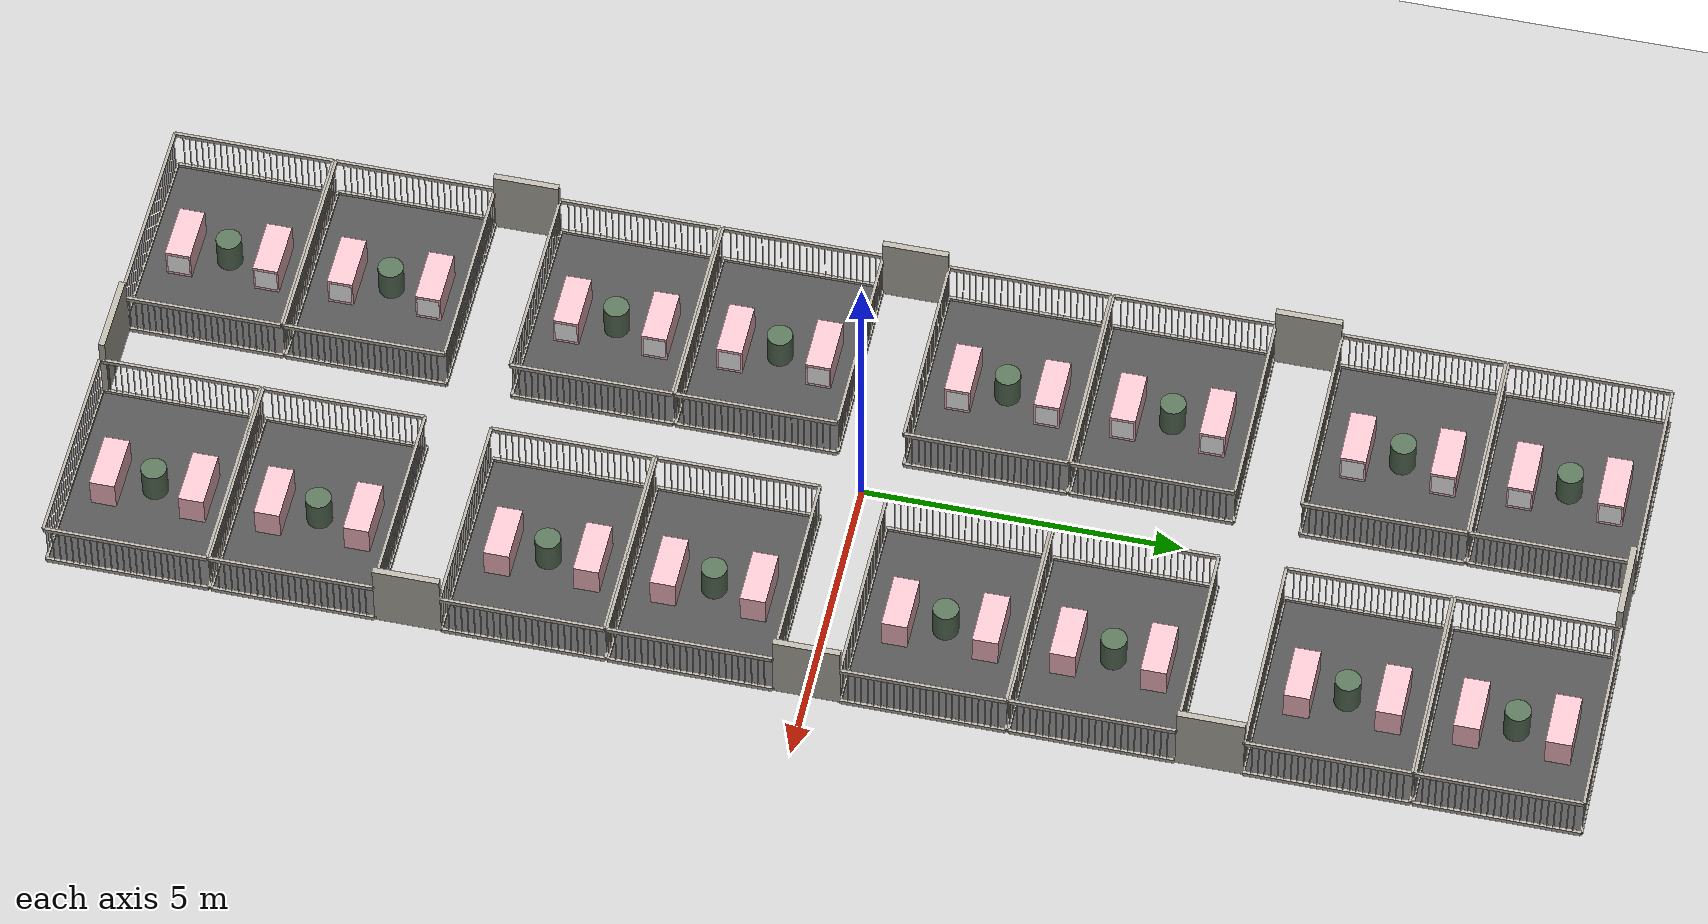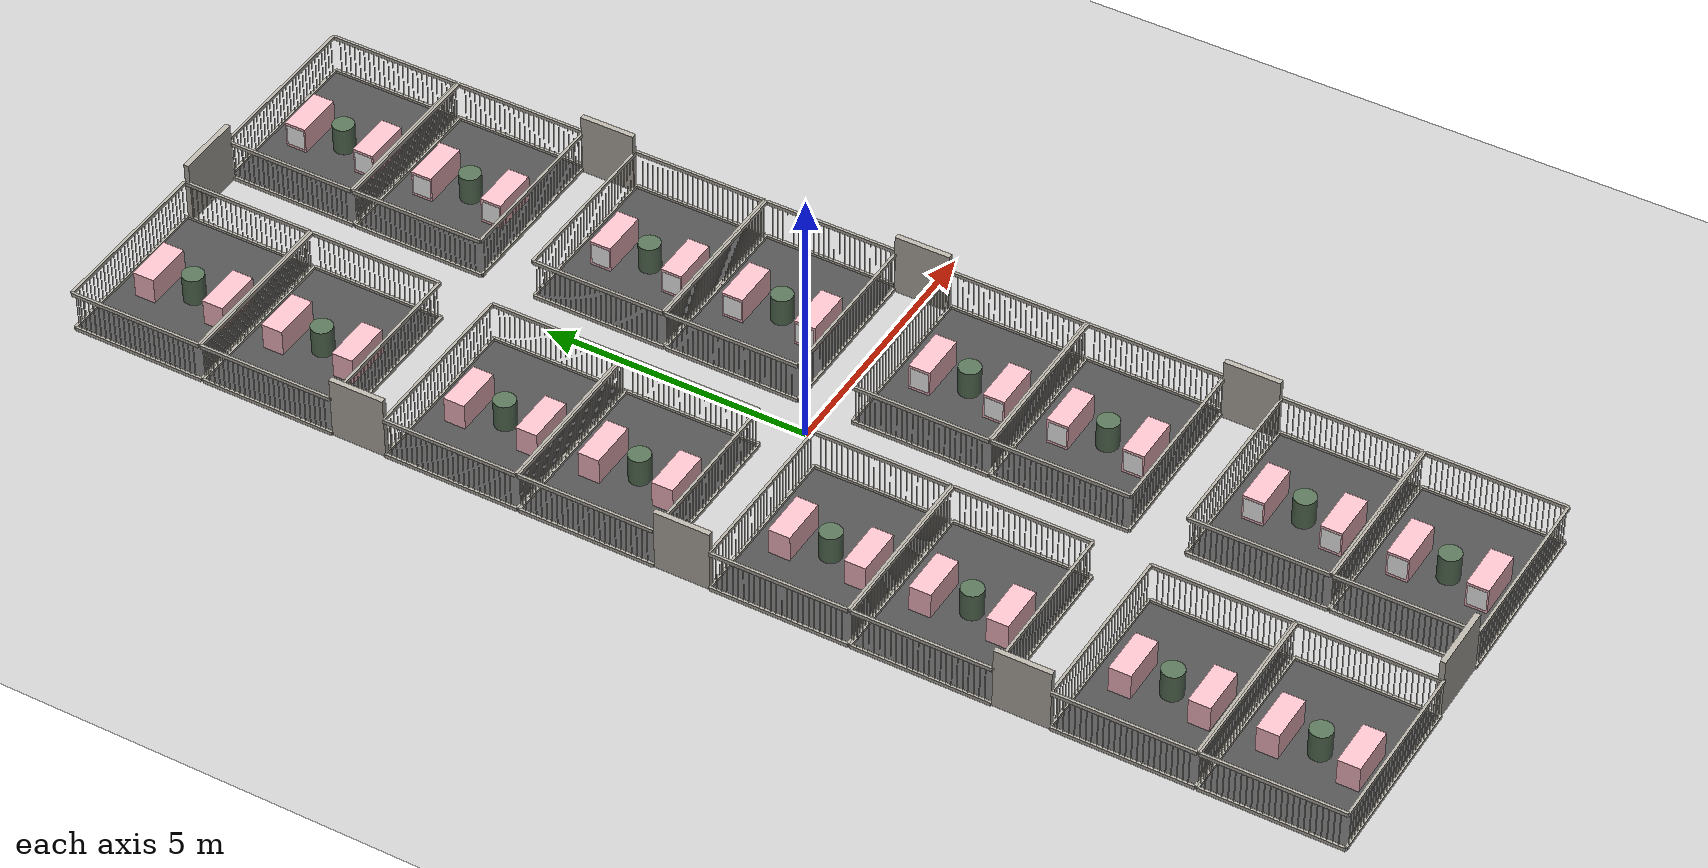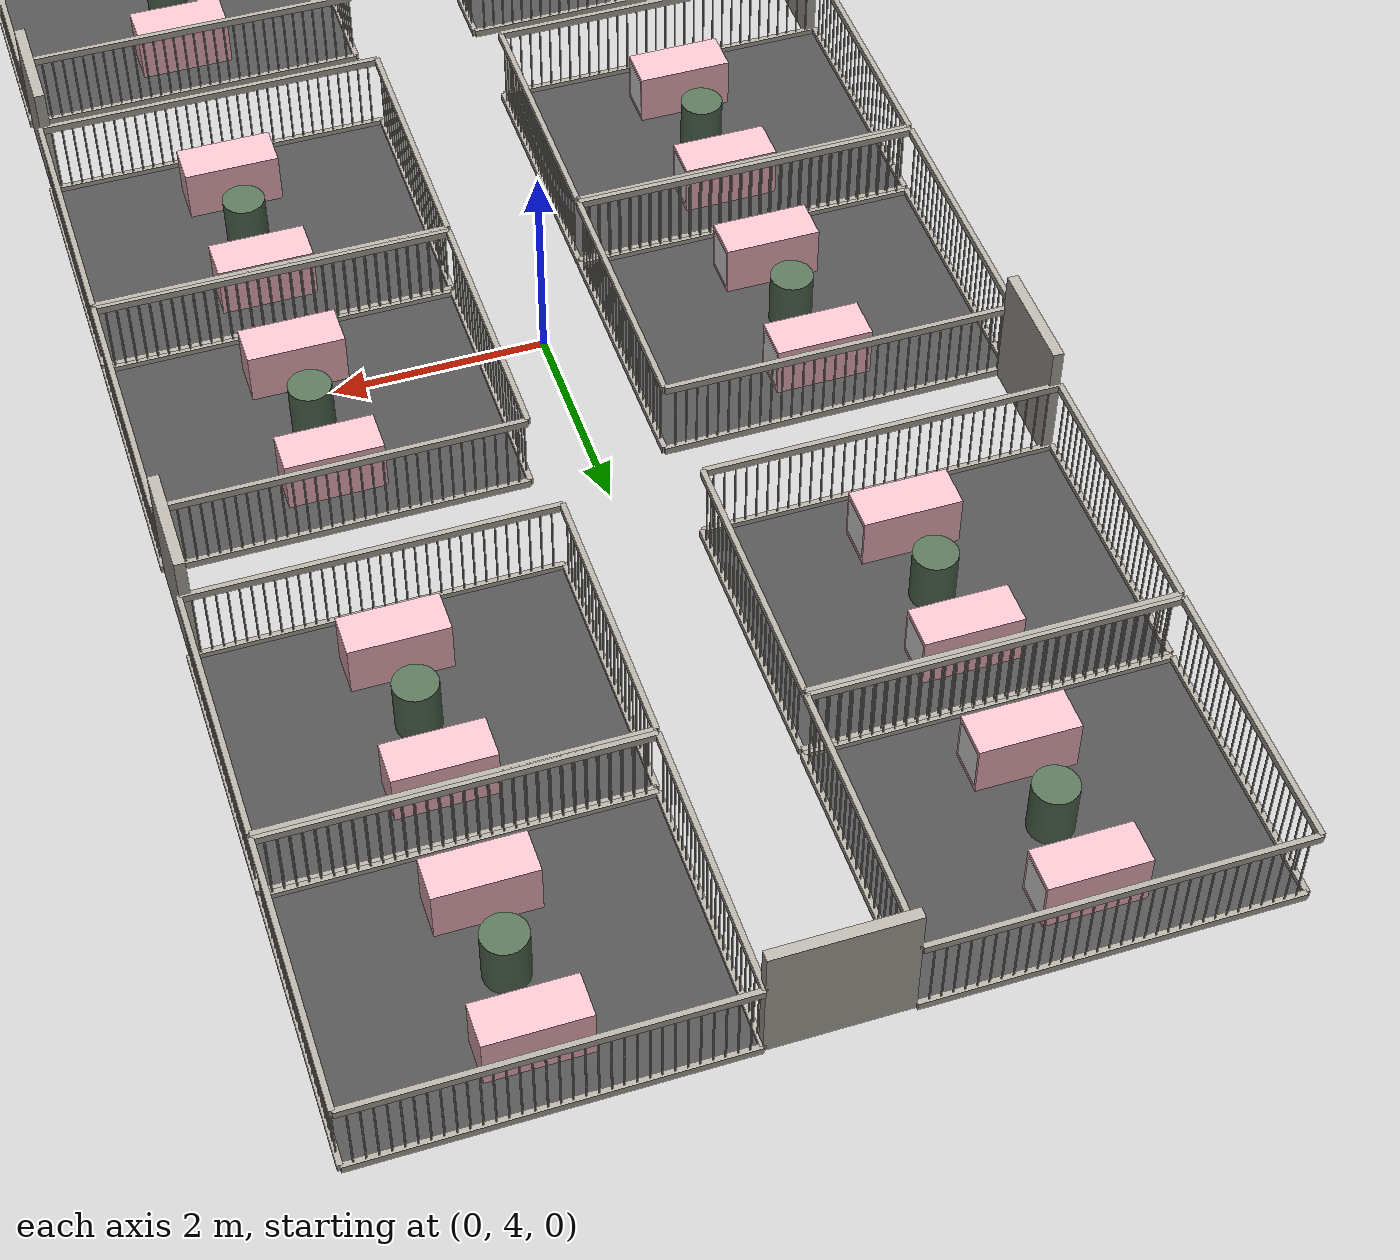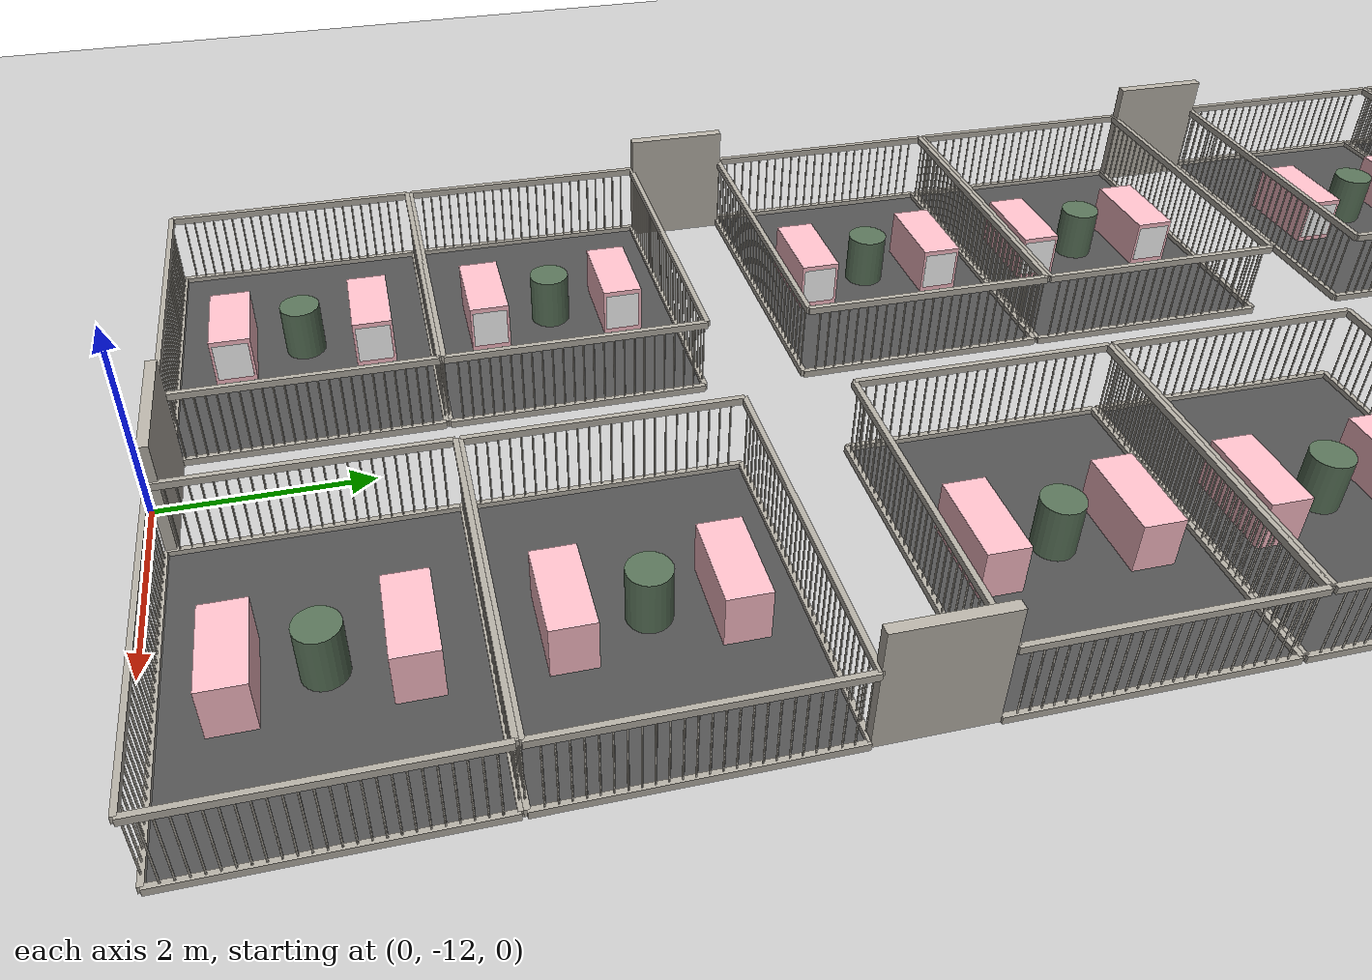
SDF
<?xml version='1.0' encoding='utf-8'?>
<sdf version="1.9">
  <world name="pig_pen_16units_world">
    <gravity>0 0 -9.8</gravity>
    <magnetic_field>0 0 0</magnetic_field>
    <atmosphere type="adiabatic" />
    <plugin filename="gz-sim-physics-system" name="gz::sim::systems::Physics" />
    <plugin filename="gz-sim-sensors-system" name="gz::sim::systems::Sensors">
      <render_engine>ogre2</render_engine>
    </plugin>
    <plugin filename="gz-sim-user-commands-system" name="gz::sim::systems::UserCommands" />
    <plugin filename="gz-sim-scene-broadcaster-system" name="gz::sim::systems::SceneBroadcaster" />
    <light name="sun" type="directional">
      <cast_shadows>true</cast_shadows>
      <pose>0 0 10 0 0 0</pose>
      <diffuse>0.9 0.9 0.9 1</diffuse>
      <specular>0.2 0.2 0.2 1</specular>
      <direction>-0.4 0.1 -1</direction>
    </light>
    <model name="ground_plane">
      <static>true</static>
      <link name="link">
        <collision name="collision">
          <geometry>
            <plane>
              <normal>0 0 1</normal>
              <size>30 30</size>
            </plane>
          </geometry>
          <surface>
            <friction>
              <ode>
                <mu>1.0</mu>
                <mu2>1.0</mu2>
              </ode>
            </friction>
          </surface>
        </collision>
        <visual name="visual">
          <geometry>
            <plane>
              <normal>0 0 1</normal>
              <size>30 30</size>
            </plane>
          </geometry>
          <material>
            <ambient>0.8 0.8 0.8 1</ambient>
            <diffuse>0.8 0.8 0.8 1</diffuse>
            <specular>0.2 0.2 0.2 1</specular>
          </material>
        </visual>
      </link>
    </model>

    <model name="pen1">
      <pose>-2.275 -7.975 0 0 0 0</pose>
      <static>true</static>

      <link name="floor">
        <pose>0 0 0.01 0 0 0</pose>
        <collision name="collision"><geometry><box><size>3.30 2.55 0.02</size></box></geometry></collision>
        <visual name="visual"><geometry><box><size>3.30 2.55 0.02</size></box></geometry><material><ambient>0.25 0.25 0.25 1</ambient><diffuse>0.32 0.32 0.32 1</diffuse><specular>0.05 0.05 0.05 1</specular></material></visual>
      </link>

      <!-- pen1 左牆（長邊3.30m，欄杆化） -->
      <link name="left_wall">
        <pose>0 1.275 0.415 0 0 0</pose>
        <collision name="top_rail_col"><pose>0 0 0.38 0 0 0</pose><geometry><box><size>3.30 0.05 0.07</size></box></geometry></collision>
        <visual name="top_rail_vis"><pose>0 0 0.38 0 0 0</pose><geometry><box><size>3.30 0.05 0.07</size></box></geometry><material><ambient>0.70 0.68 0.64 1</ambient><diffuse>0.70 0.68 0.64 1</diffuse></material></visual>
        <collision name="bottom_rail_col"><pose>0 0 -0.38 0 0 0</pose><geometry><box><size>3.30 0.05 0.07</size></box></geometry></collision>
        <visual name="bottom_rail_vis"><pose>0 0 -0.38 0 0 0</pose><geometry><box><size>3.30 0.05 0.07</size></box></geometry><material><ambient>0.70 0.68 0.64 1</ambient><diffuse>0.70 0.68 0.64 1</diffuse></material></visual>
          <collision name="bar_01_col"><pose>-1.55 0 0 0 0 0</pose><geometry><cylinder><radius>0.0075</radius><length>0.69</length></cylinder></geometry></collision>
          <visual name="bar_01_vis"><pose>-1.55 0 0 0 0 0</pose><geometry><cylinder><radius>0.0075</radius><length>0.69</length></cylinder></geometry><material><ambient>0.70 0.68 0.64 1</ambient><diffuse>0.70 0.68 0.64 1</diffuse></material></visual>
          <collision name="bar_02_col"><pose>-1.45 0 0 0 0 0</pose><geometry><cylinder><radius>0.0075</radius><length>0.69</length></cylinder></geometry></collision>
          <visual name="bar_02_vis"><pose>-1.45 0 0 0 0 0</pose><geometry><cylinder><radius>0.0075</radius><length>0.69</length></cylinder></geometry><material><ambient>0.70 0.68 0.64 1</ambient><diffuse>0.70 0.68 0.64 1</diffuse></material></visual>
          <collision name="bar_03_col"><pose>-1.35 0 0 0 0 0</pose><geometry><cylinder><radius>0.0075</radius><length>0.69</length></cylinder></geometry></collision>
          <visual name="bar_03_vis"><pose>-1.35 0 0 0 0 0</pose><geometry><cylinder><radius>0.0075</radius><length>0.69</length></cylinder></geometry><material><ambient>0.70 0.68 0.64 1</ambient><diffuse>0.70 0.68 0.64 1</diffuse></material></visual>
          <collision name="bar_04_col"><pose>-1.25 0 0 0 0 0</pose><geometry><cylinder><radius>0.0075</radius><length>0.69</length></cylinder></geometry></collision>
          <visual name="bar_04_vis"><pose>-1.25 0 0 0 0 0</pose><geometry><cylinder><radius>0.0075</radius><length>0.69</length></cylinder></geometry><material><ambient>0.70 0.68 0.64 1</ambient><diffuse>0.70 0.68 0.64 1</diffuse></material></visual>
          <collision name="bar_05_col"><pose>-1.15 0 0 0 0 0</pose><geometry><cylinder><radius>0.0075</radius><length>0.69</length></cylinder></geometry></collision>
          <visual name="bar_05_vis"><pose>-1.15 0 0 0 0 0</pose><geometry><cylinder><radius>0.0075</radius><length>0.69</length></cylinder></geometry><material><ambient>0.70 0.68 0.64 1</ambient><diffuse>0.70 0.68 0.64 1</diffuse></material></visual>
          <collision name="bar_06_col"><pose>-1.05 0 0 0 0 0</pose><geometry><cylinder><radius>0.0075</radius><length>0.69</length></cylinder></geometry></collision>
          <visual name="bar_06_vis"><pose>-1.05 0 0 0 0 0</pose><geometry><cylinder><radius>0.0075</radius><length>0.69</length></cylinder></geometry><material><ambient>0.70 0.68 0.64 1</ambient><diffuse>0.70 0.68 0.64 1</diffuse></material></visual>
          <collision name="bar_07_col"><pose>-0.95 0 0 0 0 0</pose><geometry><cylinder><radius>0.0075</radius><length>0.69</length></cylinder></geometry></collision>
          <visual name="bar_07_vis"><pose>-0.95 0 0 0 0 0</pose><geometry><cylinder><radius>0.0075</radius><length>0.69</length></cylinder></geometry><material><ambient>0.70 0.68 0.64 1</ambient><diffuse>0.70 0.68 0.64 1</diffuse></material></visual>
          <collision name="bar_08_col"><pose>-0.85 0 0 0 0 0</pose><geometry><cylinder><radius>0.0075</radius><length>0.69</length></cylinder></geometry></collision>
          <visual name="bar_08_vis"><pose>-0.85 0 0 0 0 0</pose><geometry><cylinder><radius>0.0075</radius><length>0.69</length></cylinder></geometry><material><ambient>0.70 0.68 0.64 1</ambient><diffuse>0.70 0.68 0.64 1</diffuse></material></visual>
          <collision name="bar_09_col"><pose>-0.75 0 0 0 0 0</pose><geometry><cylinder><radius>0.0075</radius><length>0.69</length></cylinder></geometry></collision>
          <visual name="bar_09_vis"><pose>-0.75 0 0 0 0 0</pose><geometry><cylinder><radius>0.0075</radius><length>0.69</length></cylinder></geometry><material><ambient>0.70 0.68 0.64 1</ambient><diffuse>0.70 0.68 0.64 1</diffuse></material></visual>
          <collision name="bar_10_col"><pose>-0.65 0 0 0 0 0</pose><geometry><cylinder><radius>0.0075</radius><length>0.69</length></cylinder></geometry></collision>
          <visual name="bar_10_vis"><pose>-0.65 0 0 0 0 0</pose><geometry><cylinder><radius>0.0075</radius><length>0.69</length></cylinder></geometry><material><ambient>0.70 0.68 0.64 1</ambient><diffuse>0.70 0.68 0.64 1</diffuse></material></visual>
          <collision name="bar_11_col"><pose>-0.55 0 0 0 0 0</pose><geometry><cylinder><radius>0.0075</radius><length>0.69</length></cylinder></geometry></collision>
          <visual name="bar_11_vis"><pose>-0.55 0 0 0 0 0</pose><geometry><cylinder><radius>0.0075</radius><length>0.69</length></cylinder></geometry><material><ambient>0.70 0.68 0.64 1</ambient><diffuse>0.70 0.68 0.64 1</diffuse></material></visual>
          <collision name="bar_12_col"><pose>-0.45 0 0 0 0 0</pose><geometry><cylinder><radius>0.0075</radius><length>0.69</length></cylinder></geometry></collision>
          <visual name="bar_12_vis"><pose>-0.45 0 0 0 0 0</pose><geometry><cylinder><radius>0.0075</radius><length>0.69</length></cylinder></geometry><material><ambient>0.70 0.68 0.64 1</ambient><diffuse>0.70 0.68 0.64 1</diffuse></material></visual>
          <collision name="bar_13_col"><pose>-0.35 0 0 0 0 0</pose><geometry><cylinder><radius>0.0075</radius><length>0.69</length></cylinder></geometry></collision>
          <visual name="bar_13_vis"><pose>-0.35 0 0 0 0 0</pose><geometry><cylinder><radius>0.0075</radius><length>0.69</length></cylinder></geometry><material><ambient>0.70 0.68 0.64 1</ambient><diffuse>0.70 0.68 0.64 1</diffuse></material></visual>
          <collision name="bar_14_col"><pose>-0.25 0 0 0 0 0</pose><geometry><cylinder><radius>0.0075</radius><length>0.69</length></cylinder></geometry></collision>
          <visual name="bar_14_vis"><pose>-0.25 0 0 0 0 0</pose><geometry><cylinder><radius>0.0075</radius><length>0.69</length></cylinder></geometry><material><ambient>0.70 0.68 0.64 1</ambient><diffuse>0.70 0.68 0.64 1</diffuse></material></visual>
          <collision name="bar_15_col"><pose>-0.15 0 0 0 0 0</pose><geometry><cylinder><radius>0.0075</radius><length>0.69</length></cylinder></geometry></collision>
          <visual name="bar_15_vis"><pose>-0.15 0 0 0 0 0</pose><geometry><cylinder><radius>0.0075</radius><length>0.69</length></cylinder></geometry><material><ambient>0.70 0.68 0.64 1</ambient><diffuse>0.70 0.68 0.64 1</diffuse></material></visual>
          <collision name="bar_16_col"><pose>-0.05 0 0 0 0 0</pose><geometry><cylinder><radius>0.0075</radius><length>0.69</length></cylinder></geometry></collision>
          <visual name="bar_16_vis"><pose>-0.05 0 0 0 0 0</pose><geometry><cylinder><radius>0.0075</radius><length>0.69</length></cylinder></geometry><material><ambient>0.70 0.68 0.64 1</ambient><diffuse>0.70 0.68 0.64 1</diffuse></material></visual>
          <collision name="bar_17_col"><pose>0.05 0 0 0 0 0</pose><geometry><cylinder><radius>0.0075</radius><length>0.69</length></cylinder></geometry></collision>
          <visual name="bar_17_vis"><pose>0.05 0 0 0 0 0</pose><geometry><cylinder><radius>0.0075</radius><length>0.69</length></cylinder></geometry><material><ambient>0.70 0.68 0.64 1</ambient><diffuse>0.70 0.68 0.64 1</diffuse></material></visual>
          <collision name="bar_18_col"><pose>0.15 0 0 0 0 0</pose><geometry><cylinder><radius>0.0075</radius><length>0.69</length></cylinder></geometry></collision>
          <visual name="bar_18_vis"><pose>0.15 0 0 0 0 0</pose><geometry><cylinder><radius>0.0075</radius><length>0.69</length></cylinder></geometry><material><ambient>0.70 0.68 0.64 1</ambient><diffuse>0.70 0.68 0.64 1</diffuse></material></visual>
          <collision name="bar_19_col"><pose>0.25 0 0 0 0 0</pose><geometry><cylinder><radius>0.0075</radius><length>0.69</length></cylinder></geometry></collision>
          <visual name="bar_19_vis"><pose>0.25 0 0 0 0 0</pose><geometry><cylinder><radius>0.0075</radius><length>0.69</length></cylinder></geometry><material><ambient>0.70 0.68 0.64 1</ambient><diffuse>0.70 0.68 0.64 1</diffuse></material></visual>
          <collision name="bar_20_col"><pose>0.35 0 0 0 0 0</pose><geometry><cylinder><radius>0.0075</radius><length>0.69</length></cylinder></geometry></collision>
          <visual name="bar_20_vis"><pose>0.35 0 0 0 0 0</pose><geometry><cylinder><radius>0.0075</radius><length>0.69</length></cylinder></geometry><material><ambient>0.70 0.68 0.64 1</ambient><diffuse>0.70 0.68 0.64 1</diffuse></material></visual>
          <collision name="bar_21_col"><pose>0.45 0 0 0 0 0</pose><geometry><cylinder><radius>0.0075</radius><length>0.69</length></cylinder></geometry></collision>
          <visual name="bar_21_vis"><pose>0.45 0 0 0 0 0</pose><geometry><cylinder><radius>0.0075</radius><length>0.69</length></cylinder></geometry><material><ambient>0.70 0.68 0.64 1</ambient><diffuse>0.70 0.68 0.64 1</diffuse></material></visual>
          <collision name="bar_22_col"><pose>0.55 0 0 0 0 0</pose><geometry><cylinder><radius>0.0075</radius><length>0.69</length></cylinder></geometry></collision>
          <visual name="bar_22_vis"><pose>0.55 0 0 0 0 0</pose><geometry><cylinder><radius>0.0075</radius><length>0.69</length></cylinder></geometry><material><ambient>0.70 0.68 0.64 1</ambient><diffuse>0.70 0.68 0.64 1</diffuse></material></visual>
          <collision name="bar_23_col"><pose>0.65 0 0 0 0 0</pose><geometry><cylinder><radius>0.0075</radius><length>0.69</length></cylinder></geometry></collision>
          <visual name="bar_23_vis"><pose>0.65 0 0 0 0 0</pose><geometry><cylinder><radius>0.0075</radius><length>0.69</length></cylinder></geometry><material><ambient>0.70 0.68 0.64 1</ambient><diffuse>0.70 0.68 0.64 1</diffuse></material></visual>
          <collision name="bar_24_col"><pose>0.75 0 0 0 0 0</pose><geometry><cylinder><radius>0.0075</radius><length>0.69</length></cylinder></geometry></collision>
          <visual name="bar_24_vis"><pose>0.75 0 0 0 0 0</pose><geometry><cylinder><radius>0.0075</radius><length>0.69</length></cylinder></geometry><material><ambient>0.70 0.68 0.64 1</ambient><diffuse>0.70 0.68 0.64 1</diffuse></material></visual>
          <collision name="bar_25_col"><pose>0.85 0 0 0 0 0</pose><geometry><cylinder><radius>0.0075</radius><length>0.69</length></cylinder></geometry></collision>
          <visual name="bar_25_vis"><pose>0.85 0 0 0 0 0</pose><geometry><cylinder><radius>0.0075</radius><length>0.69</length></cylinder></geometry><material><ambient>0.70 0.68 0.64 1</ambient><diffuse>0.70 0.68 0.64 1</diffuse></material></visual>
          <collision name="bar_26_col"><pose>0.95 0 0 0 0 0</pose><geometry><cylinder><radius>0.0075</radius><length>0.69</length></cylinder></geometry></collision>
          <visual name="bar_26_vis"><pose>0.95 0 0 0 0 0</pose><geometry><cylinder><radius>0.0075</radius><length>0.69</length></cylinder></geometry><material><ambient>0.70 0.68 0.64 1</ambient><diffuse>0.70 0.68 0.64 1</diffuse></material></visual>
          <collision name="bar_27_col"><pose>1.05 0 0 0 0 0</pose><geometry><cylinder><radius>0.0075</radius><length>0.69</length></cylinder></geometry></collision>
          <visual name="bar_27_vis"><pose>1.05 0 0 0 0 0</pose><geometry><cylinder><radius>0.0075</radius><length>0.69</length></cylinder></geometry><material><ambient>0.70 0.68 0.64 1</ambient><diffuse>0.70 0.68 0.64 1</diffuse></material></visual>
          <collision name="bar_28_col"><pose>1.15 0 0 0 0 0</pose><geometry><cylinder><radius>0.0075</radius><length>0.69</length></cylinder></geometry></collision>
          <visual name="bar_28_vis"><pose>1.15 0 0 0 0 0</pose><geometry><cylinder><radius>0.0075</radius><length>0.69</length></cylinder></geometry><material><ambient>0.70 0.68 0.64 1</ambient><diffuse>0.70 0.68 0.64 1</diffuse></material></visual>
          <collision name="bar_29_col"><pose>1.25 0 0 0 0 0</pose><geometry><cylinder><radius>0.0075</radius><length>0.69</length></cylinder></geometry></collision>
          <visual name="bar_29_vis"><pose>1.25 0 0 0 0 0</pose><geometry><cylinder><radius>0.0075</radius><length>0.69</length></cylinder></geometry><material><ambient>0.70 0.68 0.64 1</ambient><diffuse>0.70 0.68 0.64 1</diffuse></material></visual>
          <collision name="bar_30_col"><pose>1.35 0 0 0 0 0</pose><geometry><cylinder><radius>0.0075</radius><length>0.69</length></cylinder></geometry></collision>
          <visual name="bar_30_vis"><pose>1.35 0 0 0 0 0</pose><geometry><cylinder><radius>0.0075</radius><length>0.69</length></cylinder></geometry><material><ambient>0.70 0.68 0.64 1</ambient><diffuse>0.70 0.68 0.64 1</diffuse></material></visual>
          <collision name="bar_31_col"><pose>1.45 0 0 0 0 0</pose><geometry><cylinder><radius>0.0075</radius><length>0.69</length></cylinder></geometry></collision>
          <visual name="bar_31_vis"><pose>1.45 0 0 0 0 0</pose><geometry><cylinder><radius>0.0075</radius><length>0.69</length></cylinder></geometry><material><ambient>0.70 0.68 0.64 1</ambient><diffuse>0.70 0.68 0.64 1</diffuse></material></visual>
          <collision name="bar_32_col"><pose>1.55 0 0 0 0 0</pose><geometry><cylinder><radius>0.0075</radius><length>0.69</length></cylinder></geometry></collision>
          <visual name="bar_32_vis"><pose>1.55 0 0 0 0 0</pose><geometry><cylinder><radius>0.0075</radius><length>0.69</length></cylinder></geometry><material><ambient>0.70 0.68 0.64 1</ambient><diffuse>0.70 0.68 0.64 1</diffuse></material></visual>
      </link>
      <!-- pen1 右牆（長邊3.30m，欄杆化） -->
      <link name="right_wall">
        <pose>0 -1.275 0.415 0 0 0</pose>
        <collision name="top_rail_col"><pose>0 0 0.38 0 0 0</pose><geometry><box><size>3.30 0.05 0.07</size></box></geometry></collision>
        <visual name="top_rail_vis"><pose>0 0 0.38 0 0 0</pose><geometry><box><size>3.30 0.05 0.07</size></box></geometry><material><ambient>0.70 0.68 0.64 1</ambient><diffuse>0.70 0.68 0.64 1</diffuse></material></visual>
        <collision name="bottom_rail_col"><pose>0 0 -0.38 0 0 0</pose><geometry><box><size>3.30 0.05 0.07</size></box></geometry></collision>
        <visual name="bottom_rail_vis"><pose>0 0 -0.38 0 0 0</pose><geometry><box><size>3.30 0.05 0.07</size></box></geometry><material><ambient>0.70 0.68 0.64 1</ambient><diffuse>0.70 0.68 0.64 1</diffuse></material></visual>
          <collision name="bar_01_col"><pose>-1.55 0 0 0 0 0</pose><geometry><cylinder><radius>0.0075</radius><length>0.69</length></cylinder></geometry></collision>
          <visual name="bar_01_vis"><pose>-1.55 0 0 0 0 0</pose><geometry><cylinder><radius>0.0075</radius><length>0.69</length></cylinder></geometry><material><ambient>0.70 0.68 0.64 1</ambient><diffuse>0.70 0.68 0.64 1</diffuse></material></visual>
          <collision name="bar_02_col"><pose>-1.45 0 0 0 0 0</pose><geometry><cylinder><radius>0.0075</radius><length>0.69</length></cylinder></geometry></collision>
          <visual name="bar_02_vis"><pose>-1.45 0 0 0 0 0</pose><geometry><cylinder><radius>0.0075</radius><length>0.69</length></cylinder></geometry><material><ambient>0.70 0.68 0.64 1</ambient><diffuse>0.70 0.68 0.64 1</diffuse></material></visual>
          <collision name="bar_03_col"><pose>-1.35 0 0 0 0 0</pose><geometry><cylinder><radius>0.0075</radius><length>0.69</length></cylinder></geometry></collision>
          <visual name="bar_03_vis"><pose>-1.35 0 0 0 0 0</pose><geometry><cylinder><radius>0.0075</radius><length>0.69</length></cylinder></geometry><material><ambient>0.70 0.68 0.64 1</ambient><diffuse>0.70 0.68 0.64 1</diffuse></material></visual>
          <collision name="bar_04_col"><pose>-1.25 0 0 0 0 0</pose><geometry><cylinder><radius>0.0075</radius><length>0.69</length></cylinder></geometry></collision>
          <visual name="bar_04_vis"><pose>-1.25 0 0 0 0 0</pose><geometry><cylinder><radius>0.0075</radius><length>0.69</length></cylinder></geometry><material><ambient>0.70 0.68 0.64 1</ambient><diffuse>0.70 0.68 0.64 1</diffuse></material></visual>
          <collision name="bar_05_col"><pose>-1.15 0 0 0 0 0</pose><geometry><cylinder><radius>0.0075</radius><length>0.69</length></cylinder></geometry></collision>
          <visual name="bar_05_vis"><pose>-1.15 0 0 0 0 0</pose><geometry><cylinder><radius>0.0075</radius><length>0.69</length></cylinder></geometry><material><ambient>0.70 0.68 0.64 1</ambient><diffuse>0.70 0.68 0.64 1</diffuse></material></visual>
          <collision name="bar_06_col"><pose>-1.05 0 0 0 0 0</pose><geometry><cylinder><radius>0.0075</radius><length>0.69</length></cylinder></geometry></collision>
          <visual name="bar_06_vis"><pose>-1.05 0 0 0 0 0</pose><geometry><cylinder><radius>0.0075</radius><length>0.69</length></cylinder></geometry><material><ambient>0.70 0.68 0.64 1</ambient><diffuse>0.70 0.68 0.64 1</diffuse></material></visual>
          <collision name="bar_07_col"><pose>-0.95 0 0 0 0 0</pose><geometry><cylinder><radius>0.0075</radius><length>0.69</length></cylinder></geometry></collision>
          <visual name="bar_07_vis"><pose>-0.95 0 0 0 0 0</pose><geometry><cylinder><radius>0.0075</radius><length>0.69</length></cylinder></geometry><material><ambient>0.70 0.68 0.64 1</ambient><diffuse>0.70 0.68 0.64 1</diffuse></material></visual>
          <collision name="bar_08_col"><pose>-0.85 0 0 0 0 0</pose><geometry><cylinder><radius>0.0075</radius><length>0.69</length></cylinder></geometry></collision>
          <visual name="bar_08_vis"><pose>-0.85 0 0 0 0 0</pose><geometry><cylinder><radius>0.0075</radius><length>0.69</length></cylinder></geometry><material><ambient>0.70 0.68 0.64 1</ambient><diffuse>0.70 0.68 0.64 1</diffuse></material></visual>
          <collision name="bar_09_col"><pose>-0.75 0 0 0 0 0</pose><geometry><cylinder><radius>0.0075</radius><length>0.69</length></cylinder></geometry></collision>
          <visual name="bar_09_vis"><pose>-0.75 0 0 0 0 0</pose><geometry><cylinder><radius>0.0075</radius><length>0.69</length></cylinder></geometry><material><ambient>0.70 0.68 0.64 1</ambient><diffuse>0.70 0.68 0.64 1</diffuse></material></visual>
          <collision name="bar_10_col"><pose>-0.65 0 0 0 0 0</pose><geometry><cylinder><radius>0.0075</radius><length>0.69</length></cylinder></geometry></collision>
          <visual name="bar_10_vis"><pose>-0.65 0 0 0 0 0</pose><geometry><cylinder><radius>0.0075</radius><length>0.69</length></cylinder></geometry><material><ambient>0.70 0.68 0.64 1</ambient><diffuse>0.70 0.68 0.64 1</diffuse></material></visual>
          <collision name="bar_11_col"><pose>-0.55 0 0 0 0 0</pose><geometry><cylinder><radius>0.0075</radius><length>0.69</length></cylinder></geometry></collision>
          <visual name="bar_11_vis"><pose>-0.55 0 0 0 0 0</pose><geometry><cylinder><radius>0.0075</radius><length>0.69</length></cylinder></geometry><material><ambient>0.70 0.68 0.64 1</ambient><diffuse>0.70 0.68 0.64 1</diffuse></material></visual>
          <collision name="bar_12_col"><pose>-0.45 0 0 0 0 0</pose><geometry><cylinder><radius>0.0075</radius><length>0.69</length></cylinder></geometry></collision>
          <visual name="bar_12_vis"><pose>-0.45 0 0 0 0 0</pose><geometry><cylinder><radius>0.0075</radius><length>0.69</length></cylinder></geometry><material><ambient>0.70 0.68 0.64 1</ambient><diffuse>0.70 0.68 0.64 1</diffuse></material></visual>
          <collision name="bar_13_col"><pose>-0.35 0 0 0 0 0</pose><geometry><cylinder><radius>0.0075</radius><length>0.69</length></cylinder></geometry></collision>
          <visual name="bar_13_vis"><pose>-0.35 0 0 0 0 0</pose><geometry><cylinder><radius>0.0075</radius><length>0.69</length></cylinder></geometry><material><ambient>0.70 0.68 0.64 1</ambient><diffuse>0.70 0.68 0.64 1</diffuse></material></visual>
          <collision name="bar_14_col"><pose>-0.25 0 0 0 0 0</pose><geometry><cylinder><radius>0.0075</radius><length>0.69</length></cylinder></geometry></collision>
          <visual name="bar_14_vis"><pose>-0.25 0 0 0 0 0</pose><geometry><cylinder><radius>0.0075</radius><length>0.69</length></cylinder></geometry><material><ambient>0.70 0.68 0.64 1</ambient><diffuse>0.70 0.68 0.64 1</diffuse></material></visual>
          <collision name="bar_15_col"><pose>-0.15 0 0 0 0 0</pose><geometry><cylinder><radius>0.0075</radius><length>0.69</length></cylinder></geometry></collision>
          <visual name="bar_15_vis"><pose>-0.15 0 0 0 0 0</pose><geometry><cylinder><radius>0.0075</radius><length>0.69</length></cylinder></geometry><material><ambient>0.70 0.68 0.64 1</ambient><diffuse>0.70 0.68 0.64 1</diffuse></material></visual>
          <collision name="bar_16_col"><pose>-0.05 0 0 0 0 0</pose><geometry><cylinder><radius>0.0075</radius><length>0.69</length></cylinder></geometry></collision>
          <visual name="bar_16_vis"><pose>-0.05 0 0 0 0 0</pose><geometry><cylinder><radius>0.0075</radius><length>0.69</length></cylinder></geometry><material><ambient>0.70 0.68 0.64 1</ambient><diffuse>0.70 0.68 0.64 1</diffuse></material></visual>
          <collision name="bar_17_col"><pose>0.05 0 0 0 0 0</pose><geometry><cylinder><radius>0.0075</radius><length>0.69</length></cylinder></geometry></collision>
          <visual name="bar_17_vis"><pose>0.05 0 0 0 0 0</pose><geometry><cylinder><radius>0.0075</radius><length>0.69</length></cylinder></geometry><material><ambient>0.70 0.68 0.64 1</ambient><diffuse>0.70 0.68 0.64 1</diffuse></material></visual>
          <collision name="bar_18_col"><pose>0.15 0 0 0 0 0</pose><geometry><cylinder><radius>0.0075</radius><length>0.69</length></cylinder></geometry></collision>
          <visual name="bar_18_vis"><pose>0.15 0 0 0 0 0</pose><geometry><cylinder><radius>0.0075</radius><length>0.69</length></cylinder></geometry><material><ambient>0.70 0.68 0.64 1</ambient><diffuse>0.70 0.68 0.64 1</diffuse></material></visual>
          <collision name="bar_19_col"><pose>0.25 0 0 0 0 0</pose><geometry><cylinder><radius>0.0075</radius><length>0.69</length></cylinder></geometry></collision>
          <visual name="bar_19_vis"><pose>0.25 0 0 0 0 0</pose><geometry><cylinder><radius>0.0075</radius><length>0.69</length></cylinder></geometry><material><ambient>0.70 0.68 0.64 1</ambient><diffuse>0.70 0.68 0.64 1</diffuse></material></visual>
          <collision name="bar_20_col"><pose>0.35 0 0 0 0 0</pose><geometry><cylinder><radius>0.0075</radius><length>0.69</length></cylinder></geometry></collision>
          <visual name="bar_20_vis"><pose>0.35 0 0 0 0 0</pose><geometry><cylinder><radius>0.0075</radius><length>0.69</length></cylinder></geometry><material><ambient>0.70 0.68 0.64 1</ambient><diffuse>0.70 0.68 0.64 1</diffuse></material></visual>
          <collision name="bar_21_col"><pose>0.45 0 0 0 0 0</pose><geometry><cylinder><radius>0.0075</radius><length>0.69</length></cylinder></geometry></collision>
          <visual name="bar_21_vis"><pose>0.45 0 0 0 0 0</pose><geometry><cylinder><radius>0.0075</radius><length>0.69</length></cylinder></geometry><material><ambient>0.70 0.68 0.64 1</ambient><diffuse>0.70 0.68 0.64 1</diffuse></material></visual>
          <collision name="bar_22_col"><pose>0.55 0 0 0 0 0</pose><geometry><cylinder><radius>0.0075</radius><length>0.69</length></cylinder></geometry></collision>
          <visual name="bar_22_vis"><pose>0.55 0 0 0 0 0</pose><geometry><cylinder><radius>0.0075</radius><length>0.69</length></cylinder></geometry><material><ambient>0.70 0.68 0.64 1</ambient><diffuse>0.70 0.68 0.64 1</diffuse></material></visual>
          <collision name="bar_23_col"><pose>0.65 0 0 0 0 0</pose><geometry><cylinder><radius>0.0075</radius><length>0.69</length></cylinder></geometry></collision>
          <visual name="bar_23_vis"><pose>0.65 0 0 0 0 0</pose><geometry><cylinder><radius>0.0075</radius><length>0.69</length></cylinder></geometry><material><ambient>0.70 0.68 0.64 1</ambient><diffuse>0.70 0.68 0.64 1</diffuse></material></visual>
          <collision name="bar_24_col"><pose>0.75 0 0 0 0 0</pose><geometry><cylinder><radius>0.0075</radius><length>0.69</length></cylinder></geometry></collision>
          <visual name="bar_24_vis"><pose>0.75 0 0 0 0 0</pose><geometry><cylinder><radius>0.0075</radius><length>0.69</length></cylinder></geometry><material><ambient>0.70 0.68 0.64 1</ambient><diffuse>0.70 0.68 0.64 1</diffuse></material></visual>
          <collision name="bar_25_col"><pose>0.85 0 0 0 0 0</pose><geometry><cylinder><radius>0.0075</radius><length>0.69</length></cylinder></geometry></collision>
          <visual name="bar_25_vis"><pose>0.85 0 0 0 0 0</pose><geometry><cylinder><radius>0.0075</radius><length>0.69</length></cylinder></geometry><material><ambient>0.70 0.68 0.64 1</ambient><diffuse>0.70 0.68 0.64 1</diffuse></material></visual>
          <collision name="bar_26_col"><pose>0.95 0 0 0 0 0</pose><geometry><cylinder><radius>0.0075</radius><length>0.69</length></cylinder></geometry></collision>
          <visual name="bar_26_vis"><pose>0.95 0 0 0 0 0</pose><geometry><cylinder><radius>0.0075</radius><length>0.69</length></cylinder></geometry><material><ambient>0.70 0.68 0.64 1</ambient><diffuse>0.70 0.68 0.64 1</diffuse></material></visual>
          <collision name="bar_27_col"><pose>1.05 0 0 0 0 0</pose><geometry><cylinder><radius>0.0075</radius><length>0.69</length></cylinder></geometry></collision>
          <visual name="bar_27_vis"><pose>1.05 0 0 0 0 0</pose><geometry><cylinder><radius>0.0075</radius><length>0.69</length></cylinder></geometry><material><ambient>0.70 0.68 0.64 1</ambient><diffuse>0.70 0.68 0.64 1</diffuse></material></visual>
          <collision name="bar_28_col"><pose>1.15 0 0 0 0 0</pose><geometry><cylinder><radius>0.0075</radius><length>0.69</length></cylinder></geometry></collision>
          <visual name="bar_28_vis"><pose>1.15 0 0 0 0 0</pose><geometry><cylinder><radius>0.0075</radius><length>0.69</length></cylinder></geometry><material><ambient>0.70 0.68 0.64 1</ambient><diffuse>0.70 0.68 0.64 1</diffuse></material></visual>
          <collision name="bar_29_col"><pose>1.25 0 0 0 0 0</pose><geometry><cylinder><radius>0.0075</radius><length>0.69</length></cylinder></geometry></collision>
          <visual name="bar_29_vis"><pose>1.25 0 0 0 0 0</pose><geometry><cylinder><radius>0.0075</radius><length>0.69</length></cylinder></geometry><material><ambient>0.70 0.68 0.64 1</ambient><diffuse>0.70 0.68 0.64 1</diffuse></material></visual>
          <collision name="bar_30_col"><pose>1.35 0 0 0 0 0</pose><geometry><cylinder><radius>0.0075</radius><length>0.69</length></cylinder></geometry></collision>
          <visual name="bar_30_vis"><pose>1.35 0 0 0 0 0</pose><geometry><cylinder><radius>0.0075</radius><length>0.69</length></cylinder></geometry><material><ambient>0.70 0.68 0.64 1</ambient><diffuse>0.70 0.68 0.64 1</diffuse></material></visual>
          <collision name="bar_31_col"><pose>1.45 0 0 0 0 0</pose><geometry><cylinder><radius>0.0075</radius><length>0.69</length></cylinder></geometry></collision>
          <visual name="bar_31_vis"><pose>1.45 0 0 0 0 0</pose><geometry><cylinder><radius>0.0075</radius><length>0.69</length></cylinder></geometry><material><ambient>0.70 0.68 0.64 1</ambient><diffuse>0.70 0.68 0.64 1</diffuse></material></visual>
          <collision name="bar_32_col"><pose>1.55 0 0 0 0 0</pose><geometry><cylinder><radius>0.0075</radius><length>0.69</length></cylinder></geometry></collision>
          <visual name="bar_32_vis"><pose>1.55 0 0 0 0 0</pose><geometry><cylinder><radius>0.0075</radius><length>0.69</length></cylinder></geometry><material><ambient>0.70 0.68 0.64 1</ambient><diffuse>0.70 0.68 0.64 1</diffuse></material></visual>
      </link>
      <!-- pen1 後牆（短邊2.55m，欄杆化） -->
      <link name="back_wall">
        <pose>1.65 0 0.415 0 0 0</pose>
        <collision name="top_rail_col"><pose>0 0 0.38 0 0 0</pose><geometry><box><size>0.05 2.55 0.07</size></box></geometry></collision>
        <visual name="top_rail_vis"><pose>0 0 0.38 0 0 0</pose><geometry><box><size>0.05 2.55 0.07</size></box></geometry><material><ambient>0.70 0.68 0.64 1</ambient><diffuse>0.70 0.68 0.64 1</diffuse></material></visual>
        <collision name="bottom_rail_col"><pose>0 0 -0.38 0 0 0</pose><geometry><box><size>0.05 2.55 0.07</size></box></geometry></collision>
        <visual name="bottom_rail_vis"><pose>0 0 -0.38 0 0 0</pose><geometry><box><size>0.05 2.55 0.07</size></box></geometry><material><ambient>0.70 0.68 0.64 1</ambient><diffuse>0.70 0.68 0.64 1</diffuse></material></visual>
          <collision name="bar_01_col"><pose>0 -1.15 0 0 0 0</pose><geometry><cylinder><radius>0.0075</radius><length>0.69</length></cylinder></geometry></collision>
          <visual name="bar_01_vis"><pose>0 -1.15 0 0 0 0</pose><geometry><cylinder><radius>0.0075</radius><length>0.69</length></cylinder></geometry><material><ambient>0.70 0.68 0.64 1</ambient><diffuse>0.70 0.68 0.64 1</diffuse></material></visual>
          <collision name="bar_02_col"><pose>0 -1.05 0 0 0 0</pose><geometry><cylinder><radius>0.0075</radius><length>0.69</length></cylinder></geometry></collision>
          <visual name="bar_02_vis"><pose>0 -1.05 0 0 0 0</pose><geometry><cylinder><radius>0.0075</radius><length>0.69</length></cylinder></geometry><material><ambient>0.70 0.68 0.64 1</ambient><diffuse>0.70 0.68 0.64 1</diffuse></material></visual>
          <collision name="bar_03_col"><pose>0 -0.95 0 0 0 0</pose><geometry><cylinder><radius>0.0075</radius><length>0.69</length></cylinder></geometry></collision>
          <visual name="bar_03_vis"><pose>0 -0.95 0 0 0 0</pose><geometry><cylinder><radius>0.0075</radius><length>0.69</length></cylinder></geometry><material><ambient>0.70 0.68 0.64 1</ambient><diffuse>0.70 0.68 0.64 1</diffuse></material></visual>
          <collision name="bar_04_col"><pose>0 -0.85 0 0 0 0</pose><geometry><cylinder><radius>0.0075</radius><length>0.69</length></cylinder></geometry></collision>
          <visual name="bar_04_vis"><pose>0 -0.85 0 0 0 0</pose><geometry><cylinder><radius>0.0075</radius><length>0.69</length></cylinder></geometry><material><ambient>0.70 0.68 0.64 1</ambient><diffuse>0.70 0.68 0.64 1</diffuse></material></visual>
          <collision name="bar_05_col"><pose>0 -0.75 0 0 0 0</pose><geometry><cylinder><radius>0.0075</radius><length>0.69</length></cylinder></geometry></collision>
          <visual name="bar_05_vis"><pose>0 -0.75 0 0 0 0</pose><geometry><cylinder><radius>0.0075</radius><length>0.69</length></cylinder></geometry><material><ambient>0.70 0.68 0.64 1</ambient><diffuse>0.70 0.68 0.64 1</diffuse></material></visual>
          <collision name="bar_06_col"><pose>0 -0.65 0 0 0 0</pose><geometry><cylinder><radius>0.0075</radius><length>0.69</length></cylinder></geometry></collision>
          <visual name="bar_06_vis"><pose>0 -0.65 0 0 0 0</pose><geometry><cylinder><radius>0.0075</radius><length>0.69</length></cylinder></geometry><material><ambient>0.70 0.68 0.64 1</ambient><diffuse>0.70 0.68 0.64 1</diffuse></material></visual>
          <collision name="bar_07_col"><pose>0 -0.55 0 0 0 0</pose><geometry><cylinder><radius>0.0075</radius><length>0.69</length></cylinder></geometry></collision>
          <visual name="bar_07_vis"><pose>0 -0.55 0 0 0 0</pose><geometry><cylinder><radius>0.0075</radius><length>0.69</length></cylinder></geometry><material><ambient>0.70 0.68 0.64 1</ambient><diffuse>0.70 0.68 0.64 1</diffuse></material></visual>
          <collision name="bar_08_col"><pose>0 -0.45 0 0 0 0</pose><geometry><cylinder><radius>0.0075</radius><length>0.69</length></cylinder></geometry></collision>
          <visual name="bar_08_vis"><pose>0 -0.45 0 0 0 0</pose><geometry><cylinder><radius>0.0075</radius><length>0.69</length></cylinder></geometry><material><ambient>0.70 0.68 0.64 1</ambient><diffuse>0.70 0.68 0.64 1</diffuse></material></visual>
          <collision name="bar_09_col"><pose>0 -0.35 0 0 0 0</pose><geometry><cylinder><radius>0.0075</radius><length>0.69</length></cylinder></geometry></collision>
          <visual name="bar_09_vis"><pose>0 -0.35 0 0 0 0</pose><geometry><cylinder><radius>0.0075</radius><length>0.69</length></cylinder></geometry><material><ambient>0.70 0.68 0.64 1</ambient><diffuse>0.70 0.68 0.64 1</diffuse></material></visual>
          <collision name="bar_10_col"><pose>0 -0.25 0 0 0 0</pose><geometry><cylinder><radius>0.0075</radius><length>0.69</length></cylinder></geometry></collision>
          <visual name="bar_10_vis"><pose>0 -0.25 0 0 0 0</pose><geometry><cylinder><radius>0.0075</radius><length>0.69</length></cylinder></geometry><material><ambient>0.70 0.68 0.64 1</ambient><diffuse>0.70 0.68 0.64 1</diffuse></material></visual>
          <collision name="bar_11_col"><pose>0 -0.15 0 0 0 0</pose><geometry><cylinder><radius>0.0075</radius><length>0.69</length></cylinder></geometry></collision>
          <visual name="bar_11_vis"><pose>0 -0.15 0 0 0 0</pose><geometry><cylinder><radius>0.0075</radius><length>0.69</length></cylinder></geometry><material><ambient>0.70 0.68 0.64 1</ambient><diffuse>0.70 0.68 0.64 1</diffuse></material></visual>
          <collision name="bar_12_col"><pose>0 -0.05 0 0 0 0</pose><geometry><cylinder><radius>0.0075</radius><length>0.69</length></cylinder></geometry></collision>
          <visual name="bar_12_vis"><pose>0 -0.05 0 0 0 0</pose><geometry><cylinder><radius>0.0075</radius><length>0.69</length></cylinder></geometry><material><ambient>0.70 0.68 0.64 1</ambient><diffuse>0.70 0.68 0.64 1</diffuse></material></visual>
          <collision name="bar_13_col"><pose>0 0.05 0 0 0 0</pose><geometry><cylinder><radius>0.0075</radius><length>0.69</length></cylinder></geometry></collision>
          <visual name="bar_13_vis"><pose>0 0.05 0 0 0 0</pose><geometry><cylinder><radius>0.0075</radius><length>0.69</length></cylinder></geometry><material><ambient>0.70 0.68 0.64 1</ambient><diffuse>0.70 0.68 0.64 1</diffuse></material></visual>
          <collision name="bar_14_col"><pose>0 0.15 0 0 0 0</pose><geometry><cylinder><radius>0.0075</radius><length>0.69</length></cylinder></geometry></collision>
          <visual name="bar_14_vis"><pose>0 0.15 0 0 0 0</pose><geometry><cylinder><radius>0.0075</radius><length>0.69</length></cylinder></geometry><material><ambient>0.70 0.68 0.64 1</ambient><diffuse>0.70 0.68 0.64 1</diffuse></material></visual>
          <collision name="bar_15_col"><pose>0 0.25 0 0 0 0</pose><geometry><cylinder><radius>0.0075</radius><length>0.69</length></cylinder></geometry></collision>
          <visual name="bar_15_vis"><pose>0 0.25 0 0 0 0</pose><geometry><cylinder><radius>0.0075</radius><length>0.69</length></cylinder></geometry><material><ambient>0.70 0.68 0.64 1</ambient><diffuse>0.70 0.68 0.64 1</diffuse></material></visual>
          <collision name="bar_16_col"><pose>0 0.35 0 0 0 0</pose><geometry><cylinder><radius>0.0075</radius><length>0.69</length></cylinder></geometry></collision>
          <visual name="bar_16_vis"><pose>0 0.35 0 0 0 0</pose><geometry><cylinder><radius>0.0075</radius><length>0.69</length></cylinder></geometry><material><ambient>0.70 0.68 0.64 1</ambient><diffuse>0.70 0.68 0.64 1</diffuse></material></visual>
          <collision name="bar_17_col"><pose>0 0.45 0 0 0 0</pose><geometry><cylinder><radius>0.0075</radius><length>0.69</length></cylinder></geometry></collision>
          <visual name="bar_17_vis"><pose>0 0.45 0 0 0 0</pose><geometry><cylinder><radius>0.0075</radius><length>0.69</length></cylinder></geometry><material><ambient>0.70 0.68 0.64 1</ambient><diffuse>0.70 0.68 0.64 1</diffuse></material></visual>
          <collision name="bar_18_col"><pose>0 0.55 0 0 0 0</pose><geometry><cylinder><radius>0.0075</radius><length>0.69</length></cylinder></geometry></collision>
          <visual name="bar_18_vis"><pose>0 0.55 0 0 0 0</pose><geometry><cylinder><radius>0.0075</radius><length>0.69</length></cylinder></geometry><material><ambient>0.70 0.68 0.64 1</ambient><diffuse>0.70 0.68 0.64 1</diffuse></material></visual>
          <collision name="bar_19_col"><pose>0 0.65 0 0 0 0</pose><geometry><cylinder><radius>0.0075</radius><length>0.69</length></cylinder></geometry></collision>
          <visual name="bar_19_vis"><pose>0 0.65 0 0 0 0</pose><geometry><cylinder><radius>0.0075</radius><length>0.69</length></cylinder></geometry><material><ambient>0.70 0.68 0.64 1</ambient><diffuse>0.70 0.68 0.64 1</diffuse></material></visual>
          <collision name="bar_20_col"><pose>0 0.75 0 0 0 0</pose><geometry><cylinder><radius>0.0075</radius><length>0.69</length></cylinder></geometry></collision>
          <visual name="bar_20_vis"><pose>0 0.75 0 0 0 0</pose><geometry><cylinder><radius>0.0075</radius><length>0.69</length></cylinder></geometry><material><ambient>0.70 0.68 0.64 1</ambient><diffuse>0.70 0.68 0.64 1</diffuse></material></visual>
          <collision name="bar_21_col"><pose>0 0.85 0 0 0 0</pose><geometry><cylinder><radius>0.0075</radius><length>0.69</length></cylinder></geometry></collision>
          <visual name="bar_21_vis"><pose>0 0.85 0 0 0 0</pose><geometry><cylinder><radius>0.0075</radius><length>0.69</length></cylinder></geometry><material><ambient>0.70 0.68 0.64 1</ambient><diffuse>0.70 0.68 0.64 1</diffuse></material></visual>
          <collision name="bar_22_col"><pose>0 0.95 0 0 0 0</pose><geometry><cylinder><radius>0.0075</radius><length>0.69</length></cylinder></geometry></collision>
          <visual name="bar_22_vis"><pose>0 0.95 0 0 0 0</pose><geometry><cylinder><radius>0.0075</radius><length>0.69</length></cylinder></geometry><material><ambient>0.70 0.68 0.64 1</ambient><diffuse>0.70 0.68 0.64 1</diffuse></material></visual>
          <collision name="bar_23_col"><pose>0 1.05 0 0 0 0</pose><geometry><cylinder><radius>0.0075</radius><length>0.69</length></cylinder></geometry></collision>
          <visual name="bar_23_vis"><pose>0 1.05 0 0 0 0</pose><geometry><cylinder><radius>0.0075</radius><length>0.69</length></cylinder></geometry><material><ambient>0.70 0.68 0.64 1</ambient><diffuse>0.70 0.68 0.64 1</diffuse></material></visual>
          <collision name="bar_24_col"><pose>0 1.15 0 0 0 0</pose><geometry><cylinder><radius>0.0075</radius><length>0.69</length></cylinder></geometry></collision>
          <visual name="bar_24_vis"><pose>0 1.15 0 0 0 0</pose><geometry><cylinder><radius>0.0075</radius><length>0.69</length></cylinder></geometry><material><ambient>0.70 0.68 0.64 1</ambient><diffuse>0.70 0.68 0.64 1</diffuse></material></visual>
      </link>
      <!-- pen1 前牆（短邊2.55m，欄杆化） -->
      <link name="front_wall">
        <pose>-1.65 0 0.415 0 0 0</pose>
        <collision name="top_rail_col"><pose>0 0 0.38 0 0 0</pose><geometry><box><size>0.05 2.55 0.07</size></box></geometry></collision>
        <visual name="top_rail_vis"><pose>0 0 0.38 0 0 0</pose><geometry><box><size>0.05 2.55 0.07</size></box></geometry><material><ambient>0.70 0.68 0.64 1</ambient><diffuse>0.70 0.68 0.64 1</diffuse></material></visual>
        <collision name="bottom_rail_col"><pose>0 0 -0.38 0 0 0</pose><geometry><box><size>0.05 2.55 0.07</size></box></geometry></collision>
        <visual name="bottom_rail_vis"><pose>0 0 -0.38 0 0 0</pose><geometry><box><size>0.05 2.55 0.07</size></box></geometry><material><ambient>0.70 0.68 0.64 1</ambient><diffuse>0.70 0.68 0.64 1</diffuse></material></visual>
          <collision name="bar_01_col"><pose>0 -1.15 0 0 0 0</pose><geometry><cylinder><radius>0.0075</radius><length>0.69</length></cylinder></geometry></collision>
          <visual name="bar_01_vis"><pose>0 -1.15 0 0 0 0</pose><geometry><cylinder><radius>0.0075</radius><length>0.69</length></cylinder></geometry><material><ambient>0.70 0.68 0.64 1</ambient><diffuse>0.70 0.68 0.64 1</diffuse></material></visual>
          <collision name="bar_02_col"><pose>0 -1.05 0 0 0 0</pose><geometry><cylinder><radius>0.0075</radius><length>0.69</length></cylinder></geometry></collision>
          <visual name="bar_02_vis"><pose>0 -1.05 0 0 0 0</pose><geometry><cylinder><radius>0.0075</radius><length>0.69</length></cylinder></geometry><material><ambient>0.70 0.68 0.64 1</ambient><diffuse>0.70 0.68 0.64 1</diffuse></material></visual>
          <collision name="bar_03_col"><pose>0 -0.95 0 0 0 0</pose><geometry><cylinder><radius>0.0075</radius><length>0.69</length></cylinder></geometry></collision>
          <visual name="bar_03_vis"><pose>0 -0.95 0 0 0 0</pose><geometry><cylinder><radius>0.0075</radius><length>0.69</length></cylinder></geometry><material><ambient>0.70 0.68 0.64 1</ambient><diffuse>0.70 0.68 0.64 1</diffuse></material></visual>
          <collision name="bar_04_col"><pose>0 -0.85 0 0 0 0</pose><geometry><cylinder><radius>0.0075</radius><length>0.69</length></cylinder></geometry></collision>
          <visual name="bar_04_vis"><pose>0 -0.85 0 0 0 0</pose><geometry><cylinder><radius>0.0075</radius><length>0.69</length></cylinder></geometry><material><ambient>0.70 0.68 0.64 1</ambient><diffuse>0.70 0.68 0.64 1</diffuse></material></visual>
          <collision name="bar_05_col"><pose>0 -0.75 0 0 0 0</pose><geometry><cylinder><radius>0.0075</radius><length>0.69</length></cylinder></geometry></collision>
          <visual name="bar_05_vis"><pose>0 -0.75 0 0 0 0</pose><geometry><cylinder><radius>0.0075</radius><length>0.69</length></cylinder></geometry><material><ambient>0.70 0.68 0.64 1</ambient><diffuse>0.70 0.68 0.64 1</diffuse></material></visual>
          <collision name="bar_06_col"><pose>0 -0.65 0 0 0 0</pose><geometry><cylinder><radius>0.0075</radius><length>0.69</length></cylinder></geometry></collision>
          <visual name="bar_06_vis"><pose>0 -0.65 0 0 0 0</pose><geometry><cylinder><radius>0.0075</radius><length>0.69</length></cylinder></geometry><material><ambient>0.70 0.68 0.64 1</ambient><diffuse>0.70 0.68 0.64 1</diffuse></material></visual>
          <collision name="bar_07_col"><pose>0 -0.55 0 0 0 0</pose><geometry><cylinder><radius>0.0075</radius><length>0.69</length></cylinder></geometry></collision>
          <visual name="bar_07_vis"><pose>0 -0.55 0 0 0 0</pose><geometry><cylinder><radius>0.0075</radius><length>0.69</length></cylinder></geometry><material><ambient>0.70 0.68 0.64 1</ambient><diffuse>0.70 0.68 0.64 1</diffuse></material></visual>
          <collision name="bar_08_col"><pose>0 -0.45 0 0 0 0</pose><geometry><cylinder><radius>0.0075</radius><length>0.69</length></cylinder></geometry></collision>
          <visual name="bar_08_vis"><pose>0 -0.45 0 0 0 0</pose><geometry><cylinder><radius>0.0075</radius><length>0.69</length></cylinder></geometry><material><ambient>0.70 0.68 0.64 1</ambient><diffuse>0.70 0.68 0.64 1</diffuse></material></visual>
          <collision name="bar_09_col"><pose>0 -0.35 0 0 0 0</pose><geometry><cylinder><radius>0.0075</radius><length>0.69</length></cylinder></geometry></collision>
          <visual name="bar_09_vis"><pose>0 -0.35 0 0 0 0</pose><geometry><cylinder><radius>0.0075</radius><length>0.69</length></cylinder></geometry><material><ambient>0.70 0.68 0.64 1</ambient><diffuse>0.70 0.68 0.64 1</diffuse></material></visual>
          <collision name="bar_10_col"><pose>0 -0.25 0 0 0 0</pose><geometry><cylinder><radius>0.0075</radius><length>0.69</length></cylinder></geometry></collision>
          <visual name="bar_10_vis"><pose>0 -0.25 0 0 0 0</pose><geometry><cylinder><radius>0.0075</radius><length>0.69</length></cylinder></geometry><material><ambient>0.70 0.68 0.64 1</ambient><diffuse>0.70 0.68 0.64 1</diffuse></material></visual>
          <collision name="bar_11_col"><pose>0 -0.15 0 0 0 0</pose><geometry><cylinder><radius>0.0075</radius><length>0.69</length></cylinder></geometry></collision>
          <visual name="bar_11_vis"><pose>0 -0.15 0 0 0 0</pose><geometry><cylinder><radius>0.0075</radius><length>0.69</length></cylinder></geometry><material><ambient>0.70 0.68 0.64 1</ambient><diffuse>0.70 0.68 0.64 1</diffuse></material></visual>
          <collision name="bar_12_col"><pose>0 -0.05 0 0 0 0</pose><geometry><cylinder><radius>0.0075</radius><length>0.69</length></cylinder></geometry></collision>
          <visual name="bar_12_vis"><pose>0 -0.05 0 0 0 0</pose><geometry><cylinder><radius>0.0075</radius><length>0.69</length></cylinder></geometry><material><ambient>0.70 0.68 0.64 1</ambient><diffuse>0.70 0.68 0.64 1</diffuse></material></visual>
          <collision name="bar_13_col"><pose>0 0.05 0 0 0 0</pose><geometry><cylinder><radius>0.0075</radius><length>0.69</length></cylinder></geometry></collision>
          <visual name="bar_13_vis"><pose>0 0.05 0 0 0 0</pose><geometry><cylinder><radius>0.0075</radius><length>0.69</length></cylinder></geometry><material><ambient>0.70 0.68 0.64 1</ambient><diffuse>0.70 0.68 0.64 1</diffuse></material></visual>
          <collision name="bar_14_col"><pose>0 0.15 0 0 0 0</pose><geometry><cylinder><radius>0.0075</radius><length>0.69</length></cylinder></geometry></collision>
          <visual name="bar_14_vis"><pose>0 0.15 0 0 0 0</pose><geometry><cylinder><radius>0.0075</radius><length>0.69</length></cylinder></geometry><material><ambient>0.70 0.68 0.64 1</ambient><diffuse>0.70 0.68 0.64 1</diffuse></material></visual>
          <collision name="bar_15_col"><pose>0 0.25 0 0 0 0</pose><geometry><cylinder><radius>0.0075</radius><length>0.69</length></cylinder></geometry></collision>
          <visual name="bar_15_vis"><pose>0 0.25 0 0 0 0</pose><geometry><cylinder><radius>0.0075</radius><length>0.69</length></cylinder></geometry><material><ambient>0.70 0.68 0.64 1</ambient><diffuse>0.70 0.68 0.64 1</diffuse></material></visual>
          <collision name="bar_16_col"><pose>0 0.35 0 0 0 0</pose><geometry><cylinder><radius>0.0075</radius><length>0.69</length></cylinder></geometry></collision>
          <visual name="bar_16_vis"><pose>0 0.35 0 0 0 0</pose><geometry><cylinder><radius>0.0075</radius><length>0.69</length></cylinder></geometry><material><ambient>0.70 0.68 0.64 1</ambient><diffuse>0.70 0.68 0.64 1</diffuse></material></visual>
          <collision name="bar_17_col"><pose>0 0.45 0 0 0 0</pose><geometry><cylinder><radius>0.0075</radius><length>0.69</length></cylinder></geometry></collision>
          <visual name="bar_17_vis"><pose>0 0.45 0 0 0 0</pose><geometry><cylinder><radius>0.0075</radius><length>0.69</length></cylinder></geometry><material><ambient>0.70 0.68 0.64 1</ambient><diffuse>0.70 0.68 0.64 1</diffuse></material></visual>
          <collision name="bar_18_col"><pose>0 0.55 0 0 0 0</pose><geometry><cylinder><radius>0.0075</radius><length>0.69</length></cylinder></geometry></collision>
          <visual name="bar_18_vis"><pose>0 0.55 0 0 0 0</pose><geometry><cylinder><radius>0.0075</radius><length>0.69</length></cylinder></geometry><material><ambient>0.70 0.68 0.64 1</ambient><diffuse>0.70 0.68 0.64 1</diffuse></material></visual>
          <collision name="bar_19_col"><pose>0 0.65 0 0 0 0</pose><geometry><cylinder><radius>0.0075</radius><length>0.69</length></cylinder></geometry></collision>
          <visual name="bar_19_vis"><pose>0 0.65 0 0 0 0</pose><geometry><cylinder><radius>0.0075</radius><length>0.69</length></cylinder></geometry><material><ambient>0.70 0.68 0.64 1</ambient><diffuse>0.70 0.68 0.64 1</diffuse></material></visual>
          <collision name="bar_20_col"><pose>0 0.75 0 0 0 0</pose><geometry><cylinder><radius>0.0075</radius><length>0.69</length></cylinder></geometry></collision>
          <visual name="bar_20_vis"><pose>0 0.75 0 0 0 0</pose><geometry><cylinder><radius>0.0075</radius><length>0.69</length></cylinder></geometry><material><ambient>0.70 0.68 0.64 1</ambient><diffuse>0.70 0.68 0.64 1</diffuse></material></visual>
          <collision name="bar_21_col"><pose>0 0.85 0 0 0 0</pose><geometry><cylinder><radius>0.0075</radius><length>0.69</length></cylinder></geometry></collision>
          <visual name="bar_21_vis"><pose>0 0.85 0 0 0 0</pose><geometry><cylinder><radius>0.0075</radius><length>0.69</length></cylinder></geometry><material><ambient>0.70 0.68 0.64 1</ambient><diffuse>0.70 0.68 0.64 1</diffuse></material></visual>
          <collision name="bar_22_col"><pose>0 0.95 0 0 0 0</pose><geometry><cylinder><radius>0.0075</radius><length>0.69</length></cylinder></geometry></collision>
          <visual name="bar_22_vis"><pose>0 0.95 0 0 0 0</pose><geometry><cylinder><radius>0.0075</radius><length>0.69</length></cylinder></geometry><material><ambient>0.70 0.68 0.64 1</ambient><diffuse>0.70 0.68 0.64 1</diffuse></material></visual>
          <collision name="bar_23_col"><pose>0 1.05 0 0 0 0</pose><geometry><cylinder><radius>0.0075</radius><length>0.69</length></cylinder></geometry></collision>
          <visual name="bar_23_vis"><pose>0 1.05 0 0 0 0</pose><geometry><cylinder><radius>0.0075</radius><length>0.69</length></cylinder></geometry><material><ambient>0.70 0.68 0.64 1</ambient><diffuse>0.70 0.68 0.64 1</diffuse></material></visual>
          <collision name="bar_24_col"><pose>0 1.15 0 0 0 0</pose><geometry><cylinder><radius>0.0075</radius><length>0.69</length></cylinder></geometry></collision>
          <visual name="bar_24_vis"><pose>0 1.15 0 0 0 0</pose><geometry><cylinder><radius>0.0075</radius><length>0.69</length></cylinder></geometry><material><ambient>0.70 0.68 0.64 1</ambient><diffuse>0.70 0.68 0.64 1</diffuse></material></visual>
      </link>
      <link name="feeder">
        <pose>0 0 0.275 0 0 0</pose>
        <collision name="collision"><geometry><cylinder><radius>0.20</radius><length>0.55</length></cylinder></geometry></collision>
        <visual name="visual"><geometry><cylinder><radius>0.20</radius><length>0.55</length></cylinder></geometry><material><ambient>0.35 0.45 0.35 1</ambient><diffuse>0.35 0.45 0.35 1</diffuse></material></visual>
      </link>
    </model>

    <model name="pen2">
      <pose>-2.275 -10.565 0 0 0 0</pose>
      <static>true</static>

      <link name="floor">
        <pose>0 0 0.01 0 0 0</pose>
        <collision name="collision"><geometry><box><size>3.30 2.55 0.02</size></box></geometry></collision>
        <visual name="visual"><geometry><box><size>3.30 2.55 0.02</size></box></geometry><material><ambient>0.25 0.25 0.25 1</ambient><diffuse>0.32 0.32 0.32 1</diffuse><specular>0.05 0.05 0.05 1</specular></material></visual>
      </link>

      <!-- pen2 左牆（長邊3.30m，欄杆化） -->
      <link name="left_wall">
        <pose>0 1.275 0.415 0 0 0</pose>
        <collision name="top_rail_col"><pose>0 0 0.38 0 0 0</pose><geometry><box><size>3.30 0.05 0.07</size></box></geometry></collision>
        <visual name="top_rail_vis"><pose>0 0 0.38 0 0 0</pose><geometry><box><size>3.30 0.05 0.07</size></box></geometry><material><ambient>0.70 0.68 0.64 1</ambient><diffuse>0.70 0.68 0.64 1</diffuse></material></visual>
        <collision name="bottom_rail_col"><pose>0 0 -0.38 0 0 0</pose><geometry><box><size>3.30 0.05 0.07</size></box></geometry></collision>
        <visual name="bottom_rail_vis"><pose>0 0 -0.38 0 0 0</pose><geometry><box><size>3.30 0.05 0.07</size></box></geometry><material><ambient>0.70 0.68 0.64 1</ambient><diffuse>0.70 0.68 0.64 1</diffuse></material></visual>
          <collision name="bar_01_col"><pose>-1.55 0 0 0 0 0</pose><geometry><cylinder><radius>0.0075</radius><length>0.69</length></cylinder></geometry></collision>
          <visual name="bar_01_vis"><pose>-1.55 0 0 0 0 0</pose><geometry><cylinder><radius>0.0075</radius><length>0.69</length></cylinder></geometry><material><ambient>0.70 0.68 0.64 1</ambient><diffuse>0.70 0.68 0.64 1</diffuse></material></visual>
          <collision name="bar_02_col"><pose>-1.45 0 0 0 0 0</pose><geometry><cylinder><radius>0.0075</radius><length>0.69</length></cylinder></geometry></collision>
          <visual name="bar_02_vis"><pose>-1.45 0 0 0 0 0</pose><geometry><cylinder><radius>0.0075</radius><length>0.69</length></cylinder></geometry><material><ambient>0.70 0.68 0.64 1</ambient><diffuse>0.70 0.68 0.64 1</diffuse></material></visual>
          <collision name="bar_03_col"><pose>-1.35 0 0 0 0 0</pose><geometry><cylinder><radius>0.0075</radius><length>0.69</length></cylinder></geometry></collision>
          <visual name="bar_03_vis"><pose>-1.35 0 0 0 0 0</pose><geometry><cylinder><radius>0.0075</radius><length>0.69</length></cylinder></geometry><material><ambient>0.70 0.68 0.64 1</ambient><diffuse>0.70 0.68 0.64 1</diffuse></material></visual>
          <collision name="bar_04_col"><pose>-1.25 0 0 0 0 0</pose><geometry><cylinder><radius>0.0075</radius><length>0.69</length></cylinder></geometry></collision>
          <visual name="bar_04_vis"><pose>-1.25 0 0 0 0 0</pose><geometry><cylinder><radius>0.0075</radius><length>0.69</length></cylinder></geometry><material><ambient>0.70 0.68 0.64 1</ambient><diffuse>0.70 0.68 0.64 1</diffuse></material></visual>
          <collision name="bar_05_col"><pose>-1.15 0 0 0 0 0</pose><geometry><cylinder><radius>0.0075</radius><length>0.69</length></cylinder></geometry></collision>
          <visual name="bar_05_vis"><pose>-1.15 0 0 0 0 0</pose><geometry><cylinder><radius>0.0075</radius><length>0.69</length></cylinder></geometry><material><ambient>0.70 0.68 0.64 1</ambient><diffuse>0.70 0.68 0.64 1</diffuse></material></visual>
          <collision name="bar_06_col"><pose>-1.05 0 0 0 0 0</pose><geometry><cylinder><radius>0.0075</radius><length>0.69</length></cylinder></geometry></collision>
          <visual name="bar_06_vis"><pose>-1.05 0 0 0 0 0</pose><geometry><cylinder><radius>0.0075</radius><length>0.69</length></cylinder></geometry><material><ambient>0.70 0.68 0.64 1</ambient><diffuse>0.70 0.68 0.64 1</diffuse></material></visual>
          <collision name="bar_07_col"><pose>-0.95 0 0 0 0 0</pose><geometry><cylinder><radius>0.0075</radius><length>0.69</length></cylinder></geometry></collision>
          <visual name="bar_07_vis"><pose>-0.95 0 0 0 0 0</pose><geometry><cylinder><radius>0.0075</radius><length>0.69</length></cylinder></geometry><material><ambient>0.70 0.68 0.64 1</ambient><diffuse>0.70 0.68 0.64 1</diffuse></material></visual>
          <collision name="bar_08_col"><pose>-0.85 0 0 0 0 0</pose><geometry><cylinder><radius>0.0075</radius><length>0.69</length></cylinder></geometry></collision>
          <visual name="bar_08_vis"><pose>-0.85 0 0 0 0 0</pose><geometry><cylinder><radius>0.0075</radius><length>0.69</length></cylinder></geometry><material><ambient>0.70 0.68 0.64 1</ambient><diffuse>0.70 0.68 0.64 1</diffuse></material></visual>
          <collision name="bar_09_col"><pose>-0.75 0 0 0 0 0</pose><geometry><cylinder><radius>0.0075</radius><length>0.69</length></cylinder></geometry></collision>
          <visual name="bar_09_vis"><pose>-0.75 0 0 0 0 0</pose><geometry><cylinder><radius>0.0075</radius><length>0.69</length></cylinder></geometry><material><ambient>0.70 0.68 0.64 1</ambient><diffuse>0.70 0.68 0.64 1</diffuse></material></visual>
          <collision name="bar_10_col"><pose>-0.65 0 0 0 0 0</pose><geometry><cylinder><radius>0.0075</radius><length>0.69</length></cylinder></geometry></collision>
          <visual name="bar_10_vis"><pose>-0.65 0 0 0 0 0</pose><geometry><cylinder><radius>0.0075</radius><length>0.69</length></cylinder></geometry><material><ambient>0.70 0.68 0.64 1</ambient><diffuse>0.70 0.68 0.64 1</diffuse></material></visual>
          <collision name="bar_11_col"><pose>-0.55 0 0 0 0 0</pose><geometry><cylinder><radius>0.0075</radius><length>0.69</length></cylinder></geometry></collision>
          <visual name="bar_11_vis"><pose>-0.55 0 0 0 0 0</pose><geometry><cylinder><radius>0.0075</radius><length>0.69</length></cylinder></geometry><material><ambient>0.70 0.68 0.64 1</ambient><diffuse>0.70 0.68 0.64 1</diffuse></material></visual>
          <collision name="bar_12_col"><pose>-0.45 0 0 0 0 0</pose><geometry><cylinder><radius>0.0075</radius><length>0.69</length></cylinder></geometry></collision>
          <visual name="bar_12_vis"><pose>-0.45 0 0 0 0 0</pose><geometry><cylinder><radius>0.0075</radius><length>0.69</length></cylinder></geometry><material><ambient>0.70 0.68 0.64 1</ambient><diffuse>0.70 0.68 0.64 1</diffuse></material></visual>
          <collision name="bar_13_col"><pose>-0.35 0 0 0 0 0</pose><geometry><cylinder><radius>0.0075</radius><length>0.69</length></cylinder></geometry></collision>
          <visual name="bar_13_vis"><pose>-0.35 0 0 0 0 0</pose><geometry><cylinder><radius>0.0075</radius><length>0.69</length></cylinder></geometry><material><ambient>0.70 0.68 0.64 1</ambient><diffuse>0.70 0.68 0.64 1</diffuse></material></visual>
          <collision name="bar_14_col"><pose>-0.25 0 0 0 0 0</pose><geometry><cylinder><radius>0.0075</radius><length>0.69</length></cylinder></geometry></collision>
          <visual name="bar_14_vis"><pose>-0.25 0 0 0 0 0</pose><geometry><cylinder><radius>0.0075</radius><length>0.69</length></cylinder></geometry><material><ambient>0.70 0.68 0.64 1</ambient><diffuse>0.70 0.68 0.64 1</diffuse></material></visual>
          <collision name="bar_15_col"><pose>-0.15 0 0 0 0 0</pose><geometry><cylinder><radius>0.0075</radius><length>0.69</length></cylinder></geometry></collision>
          <visual name="bar_15_vis"><pose>-0.15 0 0 0 0 0</pose><geometry><cylinder><radius>0.0075</radius><length>0.69</length></cylinder></geometry><material><ambient>0.70 0.68 0.64 1</ambient><diffuse>0.70 0.68 0.64 1</diffuse></material></visual>
          <collision name="bar_16_col"><pose>-0.05 0 0 0 0 0</pose><geometry><cylinder><radius>0.0075</radius><length>0.69</length></cylinder></geometry></collision>
          <visual name="bar_16_vis"><pose>-0.05 0 0 0 0 0</pose><geometry><cylinder><radius>0.0075</radius><length>0.69</length></cylinder></geometry><material><ambient>0.70 0.68 0.64 1</ambient><diffuse>0.70 0.68 0.64 1</diffuse></material></visual>
          <collision name="bar_17_col"><pose>0.05 0 0 0 0 0</pose><geometry><cylinder><radius>0.0075</radius><length>0.69</length></cylinder></geometry></collision>
          <visual name="bar_17_vis"><pose>0.05 0 0 0 0 0</pose><geometry><cylinder><radius>0.0075</radius><length>0.69</length></cylinder></geometry><material><ambient>0.70 0.68 0.64 1</ambient><diffuse>0.70 0.68 0.64 1</diffuse></material></visual>
          <collision name="bar_18_col"><pose>0.15 0 0 0 0 0</pose><geometry><cylinder><radius>0.0075</radius><length>0.69</length></cylinder></geometry></collision>
          <visual name="bar_18_vis"><pose>0.15 0 0 0 0 0</pose><geometry><cylinder><radius>0.0075</radius><length>0.69</length></cylinder></geometry><material><ambient>0.70 0.68 0.64 1</ambient><diffuse>0.70 0.68 0.64 1</diffuse></material></visual>
          <collision name="bar_19_col"><pose>0.25 0 0 0 0 0</pose><geometry><cylinder><radius>0.0075</radius><length>0.69</length></cylinder></geometry></collision>
          <visual name="bar_19_vis"><pose>0.25 0 0 0 0 0</pose><geometry><cylinder><radius>0.0075</radius><length>0.69</length></cylinder></geometry><material><ambient>0.70 0.68 0.64 1</ambient><diffuse>0.70 0.68 0.64 1</diffuse></material></visual>
          <collision name="bar_20_col"><pose>0.35 0 0 0 0 0</pose><geometry><cylinder><radius>0.0075</radius><length>0.69</length></cylinder></geometry></collision>
          <visual name="bar_20_vis"><pose>0.35 0 0 0 0 0</pose><geometry><cylinder><radius>0.0075</radius><length>0.69</length></cylinder></geometry><material><ambient>0.70 0.68 0.64 1</ambient><diffuse>0.70 0.68 0.64 1</diffuse></material></visual>
          <collision name="bar_21_col"><pose>0.45 0 0 0 0 0</pose><geometry><cylinder><radius>0.0075</radius><length>0.69</length></cylinder></geometry></collision>
          <visual name="bar_21_vis"><pose>0.45 0 0 0 0 0</pose><geometry><cylinder><radius>0.0075</radius><length>0.69</length></cylinder></geometry><material><ambient>0.70 0.68 0.64 1</ambient><diffuse>0.70 0.68 0.64 1</diffuse></material></visual>
          <collision name="bar_22_col"><pose>0.55 0 0 0 0 0</pose><geometry><cylinder><radius>0.0075</radius><length>0.69</length></cylinder></geometry></collision>
          <visual name="bar_22_vis"><pose>0.55 0 0 0 0 0</pose><geometry><cylinder><radius>0.0075</radius><length>0.69</length></cylinder></geometry><material><ambient>0.70 0.68 0.64 1</ambient><diffuse>0.70 0.68 0.64 1</diffuse></material></visual>
          <collision name="bar_23_col"><pose>0.65 0 0 0 0 0</pose><geometry><cylinder><radius>0.0075</radius><length>0.69</length></cylinder></geometry></collision>
          <visual name="bar_23_vis"><pose>0.65 0 0 0 0 0</pose><geometry><cylinder><radius>0.0075</radius><length>0.69</length></cylinder></geometry><material><ambient>0.70 0.68 0.64 1</ambient><diffuse>0.70 0.68 0.64 1</diffuse></material></visual>
          <collision name="bar_24_col"><pose>0.75 0 0 0 0 0</pose><geometry><cylinder><radius>0.0075</radius><length>0.69</length></cylinder></geometry></collision>
          <visual name="bar_24_vis"><pose>0.75 0 0 0 0 0</pose><geometry><cylinder><radius>0.0075</radius><length>0.69</length></cylinder></geometry><material><ambient>0.70 0.68 0.64 1</ambient><diffuse>0.70 0.68 0.64 1</diffuse></material></visual>
          <collision name="bar_25_col"><pose>0.85 0 0 0 0 0</pose><geometry><cylinder><radius>0.0075</radius><length>0.69</length></cylinder></geometry></collision>
          <visual name="bar_25_vis"><pose>0.85 0 0 0 0 0</pose><geometry><cylinder><radius>0.0075</radius><length>0.69</length></cylinder></geometry><material><ambient>0.70 0.68 0.64 1</ambient><diffuse>0.70 0.68 0.64 1</diffuse></material></visual>
          <collision name="bar_26_col"><pose>0.95 0 0 0 0 0</pose><geometry><cylinder><radius>0.0075</radius><length>0.69</length></cylinder></geometry></collision>
          <visual name="bar_26_vis"><pose>0.95 0 0 0 0 0</pose><geometry><cylinder><radius>0.0075</radius><length>0.69</length></cylinder></geometry><material><ambient>0.70 0.68 0.64 1</ambient><diffuse>0.70 0.68 0.64 1</diffuse></material></visual>
          <collision name="bar_27_col"><pose>1.05 0 0 0 0 0</pose><geometry><cylinder><radius>0.0075</radius><length>0.69</length></cylinder></geometry></collision>
          <visual name="bar_27_vis"><pose>1.05 0 0 0 0 0</pose><geometry><cylinder><radius>0.0075</radius><length>0.69</length></cylinder></geometry><material><ambient>0.70 0.68 0.64 1</ambient><diffuse>0.70 0.68 0.64 1</diffuse></material></visual>
          <collision name="bar_28_col"><pose>1.15 0 0 0 0 0</pose><geometry><cylinder><radius>0.0075</radius><length>0.69</length></cylinder></geometry></collision>
          <visual name="bar_28_vis"><pose>1.15 0 0 0 0 0</pose><geometry><cylinder><radius>0.0075</radius><length>0.69</length></cylinder></geometry><material><ambient>0.70 0.68 0.64 1</ambient><diffuse>0.70 0.68 0.64 1</diffuse></material></visual>
          <collision name="bar_29_col"><pose>1.25 0 0 0 0 0</pose><geometry><cylinder><radius>0.0075</radius><length>0.69</length></cylinder></geometry></collision>
          <visual name="bar_29_vis"><pose>1.25 0 0 0 0 0</pose><geometry><cylinder><radius>0.0075</radius><length>0.69</length></cylinder></geometry><material><ambient>0.70 0.68 0.64 1</ambient><diffuse>0.70 0.68 0.64 1</diffuse></material></visual>
          <collision name="bar_30_col"><pose>1.35 0 0 0 0 0</pose><geometry><cylinder><radius>0.0075</radius><length>0.69</length></cylinder></geometry></collision>
          <visual name="bar_30_vis"><pose>1.35 0 0 0 0 0</pose><geometry><cylinder><radius>0.0075</radius><length>0.69</length></cylinder></geometry><material><ambient>0.70 0.68 0.64 1</ambient><diffuse>0.70 0.68 0.64 1</diffuse></material></visual>
          <collision name="bar_31_col"><pose>1.45 0 0 0 0 0</pose><geometry><cylinder><radius>0.0075</radius><length>0.69</length></cylinder></geometry></collision>
          <visual name="bar_31_vis"><pose>1.45 0 0 0 0 0</pose><geometry><cylinder><radius>0.0075</radius><length>0.69</length></cylinder></geometry><material><ambient>0.70 0.68 0.64 1</ambient><diffuse>0.70 0.68 0.64 1</diffuse></material></visual>
          <collision name="bar_32_col"><pose>1.55 0 0 0 0 0</pose><geometry><cylinder><radius>0.0075</radius><length>0.69</length></cylinder></geometry></collision>
          <visual name="bar_32_vis"><pose>1.55 0 0 0 0 0</pose><geometry><cylinder><radius>0.0075</radius><length>0.69</length></cylinder></geometry><material><ambient>0.70 0.68 0.64 1</ambient><diffuse>0.70 0.68 0.64 1</diffuse></material></visual>
      </link>
      <!-- pen2 右牆（長邊3.30m，欄杆化） -->
      <link name="right_wall">
        <pose>0 -1.275 0.415 0 0 0</pose>
        <collision name="top_rail_col"><pose>0 0 0.38 0 0 0</pose><geometry><box><size>3.30 0.05 0.07</size></box></geometry></collision>
        <visual name="top_rail_vis"><pose>0 0 0.38 0 0 0</pose><geometry><box><size>3.30 0.05 0.07</size></box></geometry><material><ambient>0.70 0.68 0.64 1</ambient><diffuse>0.70 0.68 0.64 1</diffuse></material></visual>
        <collision name="bottom_rail_col"><pose>0 0 -0.38 0 0 0</pose><geometry><box><size>3.30 0.05 0.07</size></box></geometry></collision>
        <visual name="bottom_rail_vis"><pose>0 0 -0.38 0 0 0</pose><geometry><box><size>3.30 0.05 0.07</size></box></geometry><material><ambient>0.70 0.68 0.64 1</ambient><diffuse>0.70 0.68 0.64 1</diffuse></material></visual>
          <collision name="bar_01_col"><pose>-1.55 0 0 0 0 0</pose><geometry><cylinder><radius>0.0075</radius><length>0.69</length></cylinder></geometry></collision>
          <visual name="bar_01_vis"><pose>-1.55 0 0 0 0 0</pose><geometry><cylinder><radius>0.0075</radius><length>0.69</length></cylinder></geometry><material><ambient>0.70 0.68 0.64 1</ambient><diffuse>0.70 0.68 0.64 1</diffuse></material></visual>
          <collision name="bar_02_col"><pose>-1.45 0 0 0 0 0</pose><geometry><cylinder><radius>0.0075</radius><length>0.69</length></cylinder></geometry></collision>
          <visual name="bar_02_vis"><pose>-1.45 0 0 0 0 0</pose><geometry><cylinder><radius>0.0075</radius><length>0.69</length></cylinder></geometry><material><ambient>0.70 0.68 0.64 1</ambient><diffuse>0.70 0.68 0.64 1</diffuse></material></visual>
          <collision name="bar_03_col"><pose>-1.35 0 0 0 0 0</pose><geometry><cylinder><radius>0.0075</radius><length>0.69</length></cylinder></geometry></collision>
          <visual name="bar_03_vis"><pose>-1.35 0 0 0 0 0</pose><geometry><cylinder><radius>0.0075</radius><length>0.69</length></cylinder></geometry><material><ambient>0.70 0.68 0.64 1</ambient><diffuse>0.70 0.68 0.64 1</diffuse></material></visual>
          <collision name="bar_04_col"><pose>-1.25 0 0 0 0 0</pose><geometry><cylinder><radius>0.0075</radius><length>0.69</length></cylinder></geometry></collision>
          <visual name="bar_04_vis"><pose>-1.25 0 0 0 0 0</pose><geometry><cylinder><radius>0.0075</radius><length>0.69</length></cylinder></geometry><material><ambient>0.70 0.68 0.64 1</ambient><diffuse>0.70 0.68 0.64 1</diffuse></material></visual>
          <collision name="bar_05_col"><pose>-1.15 0 0 0 0 0</pose><geometry><cylinder><radius>0.0075</radius><length>0.69</length></cylinder></geometry></collision>
          <visual name="bar_05_vis"><pose>-1.15 0 0 0 0 0</pose><geometry><cylinder><radius>0.0075</radius><length>0.69</length></cylinder></geometry><material><ambient>0.70 0.68 0.64 1</ambient><diffuse>0.70 0.68 0.64 1</diffuse></material></visual>
          <collision name="bar_06_col"><pose>-1.05 0 0 0 0 0</pose><geometry><cylinder><radius>0.0075</radius><length>0.69</length></cylinder></geometry></collision>
          <visual name="bar_06_vis"><pose>-1.05 0 0 0 0 0</pose><geometry><cylinder><radius>0.0075</radius><length>0.69</length></cylinder></geometry><material><ambient>0.70 0.68 0.64 1</ambient><diffuse>0.70 0.68 0.64 1</diffuse></material></visual>
          <collision name="bar_07_col"><pose>-0.95 0 0 0 0 0</pose><geometry><cylinder><radius>0.0075</radius><length>0.69</length></cylinder></geometry></collision>
          <visual name="bar_07_vis"><pose>-0.95 0 0 0 0 0</pose><geometry><cylinder><radius>0.0075</radius><length>0.69</length></cylinder></geometry><material><ambient>0.70 0.68 0.64 1</ambient><diffuse>0.70 0.68 0.64 1</diffuse></material></visual>
          <collision name="bar_08_col"><pose>-0.85 0 0 0 0 0</pose><geometry><cylinder><radius>0.0075</radius><length>0.69</length></cylinder></geometry></collision>
          <visual name="bar_08_vis"><pose>-0.85 0 0 0 0 0</pose><geometry><cylinder><radius>0.0075</radius><length>0.69</length></cylinder></geometry><material><ambient>0.70 0.68 0.64 1</ambient><diffuse>0.70 0.68 0.64 1</diffuse></material></visual>
          <collision name="bar_09_col"><pose>-0.75 0 0 0 0 0</pose><geometry><cylinder><radius>0.0075</radius><length>0.69</length></cylinder></geometry></collision>
          <visual name="bar_09_vis"><pose>-0.75 0 0 0 0 0</pose><geometry><cylinder><radius>0.0075</radius><length>0.69</length></cylinder></geometry><material><ambient>0.70 0.68 0.64 1</ambient><diffuse>0.70 0.68 0.64 1</diffuse></material></visual>
          <collision name="bar_10_col"><pose>-0.65 0 0 0 0 0</pose><geometry><cylinder><radius>0.0075</radius><length>0.69</length></cylinder></geometry></collision>
          <visual name="bar_10_vis"><pose>-0.65 0 0 0 0 0</pose><geometry><cylinder><radius>0.0075</radius><length>0.69</length></cylinder></geometry><material><ambient>0.70 0.68 0.64 1</ambient><diffuse>0.70 0.68 0.64 1</diffuse></material></visual>
          <collision name="bar_11_col"><pose>-0.55 0 0 0 0 0</pose><geometry><cylinder><radius>0.0075</radius><length>0.69</length></cylinder></geometry></collision>
          <visual name="bar_11_vis"><pose>-0.55 0 0 0 0 0</pose><geometry><cylinder><radius>0.0075</radius><length>0.69</length></cylinder></geometry><material><ambient>0.70 0.68 0.64 1</ambient><diffuse>0.70 0.68 0.64 1</diffuse></material></visual>
          <collision name="bar_12_col"><pose>-0.45 0 0 0 0 0</pose><geometry><cylinder><radius>0.0075</radius><length>0.69</length></cylinder></geometry></collision>
          <visual name="bar_12_vis"><pose>-0.45 0 0 0 0 0</pose><geometry><cylinder><radius>0.0075</radius><length>0.69</length></cylinder></geometry><material><ambient>0.70 0.68 0.64 1</ambient><diffuse>0.70 0.68 0.64 1</diffuse></material></visual>
          <collision name="bar_13_col"><pose>-0.35 0 0 0 0 0</pose><geometry><cylinder><radius>0.0075</radius><length>0.69</length></cylinder></geometry></collision>
          <visual name="bar_13_vis"><pose>-0.35 0 0 0 0 0</pose><geometry><cylinder><radius>0.0075</radius><length>0.69</length></cylinder></geometry><material><ambient>0.70 0.68 0.64 1</ambient><diffuse>0.70 0.68 0.64 1</diffuse></material></visual>
          <collision name="bar_14_col"><pose>-0.25 0 0 0 0 0</pose><geometry><cylinder><radius>0.0075</radius><length>0.69</length></cylinder></geometry></collision>
          <visual name="bar_14_vis"><pose>-0.25 0 0 0 0 0</pose><geometry><cylinder><radius>0.0075</radius><length>0.69</length></cylinder></geometry><material><ambient>0.70 0.68 0.64 1</ambient><diffuse>0.70 0.68 0.64 1</diffuse></material></visual>
          <collision name="bar_15_col"><pose>-0.15 0 0 0 0 0</pose><geometry><cylinder><radius>0.0075</radius><length>0.69</length></cylinder></geometry></collision>
          <visual name="bar_15_vis"><pose>-0.15 0 0 0 0 0</pose><geometry><cylinder><radius>0.0075</radius><length>0.69</length></cylinder></geometry><material><ambient>0.70 0.68 0.64 1</ambient><diffuse>0.70 0.68 0.64 1</diffuse></material></visual>
          <collision name="bar_16_col"><pose>-0.05 0 0 0 0 0</pose><geometry><cylinder><radius>0.0075</radius><length>0.69</length></cylinder></geometry></collision>
          <visual name="bar_16_vis"><pose>-0.05 0 0 0 0 0</pose><geometry><cylinder><radius>0.0075</radius><length>0.69</length></cylinder></geometry><material><ambient>0.70 0.68 0.64 1</ambient><diffuse>0.70 0.68 0.64 1</diffuse></material></visual>
          <collision name="bar_17_col"><pose>0.05 0 0 0 0 0</pose><geometry><cylinder><radius>0.0075</radius><length>0.69</length></cylinder></geometry></collision>
          <visual name="bar_17_vis"><pose>0.05 0 0 0 0 0</pose><geometry><cylinder><radius>0.0075</radius><length>0.69</length></cylinder></geometry><material><ambient>0.70 0.68 0.64 1</ambient><diffuse>0.70 0.68 0.64 1</diffuse></material></visual>
          <collision name="bar_18_col"><pose>0.15 0 0 0 0 0</pose><geometry><cylinder><radius>0.0075</radius><length>0.69</length></cylinder></geometry></collision>
          <visual name="bar_18_vis"><pose>0.15 0 0 0 0 0</pose><geometry><cylinder><radius>0.0075</radius><length>0.69</length></cylinder></geometry><material><ambient>0.70 0.68 0.64 1</ambient><diffuse>0.70 0.68 0.64 1</diffuse></material></visual>
          <collision name="bar_19_col"><pose>0.25 0 0 0 0 0</pose><geometry><cylinder><radius>0.0075</radius><length>0.69</length></cylinder></geometry></collision>
          <visual name="bar_19_vis"><pose>0.25 0 0 0 0 0</pose><geometry><cylinder><radius>0.0075</radius><length>0.69</length></cylinder></geometry><material><ambient>0.70 0.68 0.64 1</ambient><diffuse>0.70 0.68 0.64 1</diffuse></material></visual>
          <collision name="bar_20_col"><pose>0.35 0 0 0 0 0</pose><geometry><cylinder><radius>0.0075</radius><length>0.69</length></cylinder></geometry></collision>
          <visual name="bar_20_vis"><pose>0.35 0 0 0 0 0</pose><geometry><cylinder><radius>0.0075</radius><length>0.69</length></cylinder></geometry><material><ambient>0.70 0.68 0.64 1</ambient><diffuse>0.70 0.68 0.64 1</diffuse></material></visual>
          <collision name="bar_21_col"><pose>0.45 0 0 0 0 0</pose><geometry><cylinder><radius>0.0075</radius><length>0.69</length></cylinder></geometry></collision>
          <visual name="bar_21_vis"><pose>0.45 0 0 0 0 0</pose><geometry><cylinder><radius>0.0075</radius><length>0.69</length></cylinder></geometry><material><ambient>0.70 0.68 0.64 1</ambient><diffuse>0.70 0.68 0.64 1</diffuse></material></visual>
          <collision name="bar_22_col"><pose>0.55 0 0 0 0 0</pose><geometry><cylinder><radius>0.0075</radius><length>0.69</length></cylinder></geometry></collision>
          <visual name="bar_22_vis"><pose>0.55 0 0 0 0 0</pose><geometry><cylinder><radius>0.0075</radius><length>0.69</length></cylinder></geometry><material><ambient>0.70 0.68 0.64 1</ambient><diffuse>0.70 0.68 0.64 1</diffuse></material></visual>
          <collision name="bar_23_col"><pose>0.65 0 0 0 0 0</pose><geometry><cylinder><radius>0.0075</radius><length>0.69</length></cylinder></geometry></collision>
          <visual name="bar_23_vis"><pose>0.65 0 0 0 0 0</pose><geometry><cylinder><radius>0.0075</radius><length>0.69</length></cylinder></geometry><material><ambient>0.70 0.68 0.64 1</ambient><diffuse>0.70 0.68 0.64 1</diffuse></material></visual>
          <collision name="bar_24_col"><pose>0.75 0 0 0 0 0</pose><geometry><cylinder><radius>0.0075</radius><length>0.69</length></cylinder></geometry></collision>
          <visual name="bar_24_vis"><pose>0.75 0 0 0 0 0</pose><geometry><cylinder><radius>0.0075</radius><length>0.69</length></cylinder></geometry><material><ambient>0.70 0.68 0.64 1</ambient><diffuse>0.70 0.68 0.64 1</diffuse></material></visual>
          <collision name="bar_25_col"><pose>0.85 0 0 0 0 0</pose><geometry><cylinder><radius>0.0075</radius><length>0.69</length></cylinder></geometry></collision>
          <visual name="bar_25_vis"><pose>0.85 0 0 0 0 0</pose><geometry><cylinder><radius>0.0075</radius><length>0.69</length></cylinder></geometry><material><ambient>0.70 0.68 0.64 1</ambient><diffuse>0.70 0.68 0.64 1</diffuse></material></visual>
          <collision name="bar_26_col"><pose>0.95 0 0 0 0 0</pose><geometry><cylinder><radius>0.0075</radius><length>0.69</length></cylinder></geometry></collision>
          <visual name="bar_26_vis"><pose>0.95 0 0 0 0 0</pose><geometry><cylinder><radius>0.0075</radius><length>0.69</length></cylinder></geometry><material><ambient>0.70 0.68 0.64 1</ambient><diffuse>0.70 0.68 0.64 1</diffuse></material></visual>
          <collision name="bar_27_col"><pose>1.05 0 0 0 0 0</pose><geometry><cylinder><radius>0.0075</radius><length>0.69</length></cylinder></geometry></collision>
          <visual name="bar_27_vis"><pose>1.05 0 0 0 0 0</pose><geometry><cylinder><radius>0.0075</radius><length>0.69</length></cylinder></geometry><material><ambient>0.70 0.68 0.64 1</ambient><diffuse>0.70 0.68 0.64 1</diffuse></material></visual>
          <collision name="bar_28_col"><pose>1.15 0 0 0 0 0</pose><geometry><cylinder><radius>0.0075</radius><length>0.69</length></cylinder></geometry></collision>
          <visual name="bar_28_vis"><pose>1.15 0 0 0 0 0</pose><geometry><cylinder><radius>0.0075</radius><length>0.69</length></cylinder></geometry><material><ambient>0.70 0.68 0.64 1</ambient><diffuse>0.70 0.68 0.64 1</diffuse></material></visual>
          <collision name="bar_29_col"><pose>1.25 0 0 0 0 0</pose><geometry><cylinder><radius>0.0075</radius><length>0.69</length></cylinder></geometry></collision>
          <visual name="bar_29_vis"><pose>1.25 0 0 0 0 0</pose><geometry><cylinder><radius>0.0075</radius><length>0.69</length></cylinder></geometry><material><ambient>0.70 0.68 0.64 1</ambient><diffuse>0.70 0.68 0.64 1</diffuse></material></visual>
          <collision name="bar_30_col"><pose>1.35 0 0 0 0 0</pose><geometry><cylinder><radius>0.0075</radius><length>0.69</length></cylinder></geometry></collision>
          <visual name="bar_30_vis"><pose>1.35 0 0 0 0 0</pose><geometry><cylinder><radius>0.0075</radius><length>0.69</length></cylinder></geometry><material><ambient>0.70 0.68 0.64 1</ambient><diffuse>0.70 0.68 0.64 1</diffuse></material></visual>
          <collision name="bar_31_col"><pose>1.45 0 0 0 0 0</pose><geometry><cylinder><radius>0.0075</radius><length>0.69</length></cylinder></geometry></collision>
          <visual name="bar_31_vis"><pose>1.45 0 0 0 0 0</pose><geometry><cylinder><radius>0.0075</radius><length>0.69</length></cylinder></geometry><material><ambient>0.70 0.68 0.64 1</ambient><diffuse>0.70 0.68 0.64 1</diffuse></material></visual>
          <collision name="bar_32_col"><pose>1.55 0 0 0 0 0</pose><geometry><cylinder><radius>0.0075</radius><length>0.69</length></cylinder></geometry></collision>
          <visual name="bar_32_vis"><pose>1.55 0 0 0 0 0</pose><geometry><cylinder><radius>0.0075</radius><length>0.69</length></cylinder></geometry><material><ambient>0.70 0.68 0.64 1</ambient><diffuse>0.70 0.68 0.64 1</diffuse></material></visual>
      </link>
      <!-- pen2 後牆（短邊2.55m，欄杆化） -->
      <link name="back_wall">
        <pose>1.65 0 0.415 0 0 0</pose>
        <collision name="top_rail_col"><pose>0 0 0.38 0 0 0</pose><geometry><box><size>0.05 2.55 0.07</size></box></geometry></collision>
        <visual name="top_rail_vis"><pose>0 0 0.38 0 0 0</pose><geometry><box><size>0.05 2.55 0.07</size></box></geometry><material><ambient>0.70 0.68 0.64 1</ambient><diffuse>0.70 0.68 0.64 1</diffuse></material></visual>
        <collision name="bottom_rail_col"><pose>0 0 -0.38 0 0 0</pose><geometry><box><size>0.05 2.55 0.07</size></box></geometry></collision>
        <visual name="bottom_rail_vis"><pose>0 0 -0.38 0 0 0</pose><geometry><box><size>0.05 2.55 0.07</size></box></geometry><material><ambient>0.70 0.68 0.64 1</ambient><diffuse>0.70 0.68 0.64 1</diffuse></material></visual>
          <collision name="bar_01_col"><pose>0 -1.15 0 0 0 0</pose><geometry><cylinder><radius>0.0075</radius><length>0.69</length></cylinder></geometry></collision>
          <visual name="bar_01_vis"><pose>0 -1.15 0 0 0 0</pose><geometry><cylinder><radius>0.0075</radius><length>0.69</length></cylinder></geometry><material><ambient>0.70 0.68 0.64 1</ambient><diffuse>0.70 0.68 0.64 1</diffuse></material></visual>
          <collision name="bar_02_col"><pose>0 -1.05 0 0 0 0</pose><geometry><cylinder><radius>0.0075</radius><length>0.69</length></cylinder></geometry></collision>
          <visual name="bar_02_vis"><pose>0 -1.05 0 0 0 0</pose><geometry><cylinder><radius>0.0075</radius><length>0.69</length></cylinder></geometry><material><ambient>0.70 0.68 0.64 1</ambient><diffuse>0.70 0.68 0.64 1</diffuse></material></visual>
          <collision name="bar_03_col"><pose>0 -0.95 0 0 0 0</pose><geometry><cylinder><radius>0.0075</radius><length>0.69</length></cylinder></geometry></collision>
          <visual name="bar_03_vis"><pose>0 -0.95 0 0 0 0</pose><geometry><cylinder><radius>0.0075</radius><length>0.69</length></cylinder></geometry><material><ambient>0.70 0.68 0.64 1</ambient><diffuse>0.70 0.68 0.64 1</diffuse></material></visual>
          <collision name="bar_04_col"><pose>0 -0.85 0 0 0 0</pose><geometry><cylinder><radius>0.0075</radius><length>0.69</length></cylinder></geometry></collision>
          <visual name="bar_04_vis"><pose>0 -0.85 0 0 0 0</pose><geometry><cylinder><radius>0.0075</radius><length>0.69</length></cylinder></geometry><material><ambient>0.70 0.68 0.64 1</ambient><diffuse>0.70 0.68 0.64 1</diffuse></material></visual>
          <collision name="bar_05_col"><pose>0 -0.75 0 0 0 0</pose><geometry><cylinder><radius>0.0075</radius><length>0.69</length></cylinder></geometry></collision>
          <visual name="bar_05_vis"><pose>0 -0.75 0 0 0 0</pose><geometry><cylinder><radius>0.0075</radius><length>0.69</length></cylinder></geometry><material><ambient>0.70 0.68 0.64 1</ambient><diffuse>0.70 0.68 0.64 1</diffuse></material></visual>
          <collision name="bar_06_col"><pose>0 -0.65 0 0 0 0</pose><geometry><cylinder><radius>0.0075</radius><length>0.69</length></cylinder></geometry></collision>
          <visual name="bar_06_vis"><pose>0 -0.65 0 0 0 0</pose><geometry><cylinder><radius>0.0075</radius><length>0.69</length></cylinder></geometry><material><ambient>0.70 0.68 0.64 1</ambient><diffuse>0.70 0.68 0.64 1</diffuse></material></visual>
          <collision name="bar_07_col"><pose>0 -0.55 0 0 0 0</pose><geometry><cylinder><radius>0.0075</radius><length>0.69</length></cylinder></geometry></collision>
          <visual name="bar_07_vis"><pose>0 -0.55 0 0 0 0</pose><geometry><cylinder><radius>0.0075</radius><length>0.69</length></cylinder></geometry><material><ambient>0.70 0.68 0.64 1</ambient><diffuse>0.70 0.68 0.64 1</diffuse></material></visual>
          <collision name="bar_08_col"><pose>0 -0.45 0 0 0 0</pose><geometry><cylinder><radius>0.0075</radius><length>0.69</length></cylinder></geometry></collision>
          <visual name="bar_08_vis"><pose>0 -0.45 0 0 0 0</pose><geometry><cylinder><radius>0.0075</radius><length>0.69</length></cylinder></geometry><material><ambient>0.70 0.68 0.64 1</ambient><diffuse>0.70 0.68 0.64 1</diffuse></material></visual>
          <collision name="bar_09_col"><pose>0 -0.35 0 0 0 0</pose><geometry><cylinder><radius>0.0075</radius><length>0.69</length></cylinder></geometry></collision>
          <visual name="bar_09_vis"><pose>0 -0.35 0 0 0 0</pose><geometry><cylinder><radius>0.0075</radius><length>0.69</length></cylinder></geometry><material><ambient>0.70 0.68 0.64 1</ambient><diffuse>0.70 0.68 0.64 1</diffuse></material></visual>
          <collision name="bar_10_col"><pose>0 -0.25 0 0 0 0</pose><geometry><cylinder><radius>0.0075</radius><length>0.69</length></cylinder></geometry></collision>
          <visual name="bar_10_vis"><pose>0 -0.25 0 0 0 0</pose><geometry><cylinder><radius>0.0075</radius><length>0.69</length></cylinder></geometry><material><ambient>0.70 0.68 0.64 1</ambient><diffuse>0.70 0.68 0.64 1</diffuse></material></visual>
          <collision name="bar_11_col"><pose>0 -0.15 0 0 0 0</pose><geometry><cylinder><radius>0.0075</radius><length>0.69</length></cylinder></geometry></collision>
          <visual name="bar_11_vis"><pose>0 -0.15 0 0 0 0</pose><geometry><cylinder><radius>0.0075</radius><length>0.69</length></cylinder></geometry><material><ambient>0.70 0.68 0.64 1</ambient><diffuse>0.70 0.68 0.64 1</diffuse></material></visual>
          <collision name="bar_12_col"><pose>0 -0.05 0 0 0 0</pose><geometry><cylinder><radius>0.0075</radius><length>0.69</length></cylinder></geometry></collision>
          <visual name="bar_12_vis"><pose>0 -0.05 0 0 0 0</pose><geometry><cylinder><radius>0.0075</radius><length>0.69</length></cylinder></geometry><material><ambient>0.70 0.68 0.64 1</ambient><diffuse>0.70 0.68 0.64 1</diffuse></material></visual>
          <collision name="bar_13_col"><pose>0 0.05 0 0 0 0</pose><geometry><cylinder><radius>0.0075</radius><length>0.69</length></cylinder></geometry></collision>
          <visual name="bar_13_vis"><pose>0 0.05 0 0 0 0</pose><geometry><cylinder><radius>0.0075</radius><length>0.69</length></cylinder></geometry><material><ambient>0.70 0.68 0.64 1</ambient><diffuse>0.70 0.68 0.64 1</diffuse></material></visual>
          <collision name="bar_14_col"><pose>0 0.15 0 0 0 0</pose><geometry><cylinder><radius>0.0075</radius><length>0.69</length></cylinder></geometry></collision>
          <visual name="bar_14_vis"><pose>0 0.15 0 0 0 0</pose><geometry><cylinder><radius>0.0075</radius><length>0.69</length></cylinder></geometry><material><ambient>0.70 0.68 0.64 1</ambient><diffuse>0.70 0.68 0.64 1</diffuse></material></visual>
          <collision name="bar_15_col"><pose>0 0.25 0 0 0 0</pose><geometry><cylinder><radius>0.0075</radius><length>0.69</length></cylinder></geometry></collision>
          <visual name="bar_15_vis"><pose>0 0.25 0 0 0 0</pose><geometry><cylinder><radius>0.0075</radius><length>0.69</length></cylinder></geometry><material><ambient>0.70 0.68 0.64 1</ambient><diffuse>0.70 0.68 0.64 1</diffuse></material></visual>
          <collision name="bar_16_col"><pose>0 0.35 0 0 0 0</pose><geometry><cylinder><radius>0.0075</radius><length>0.69</length></cylinder></geometry></collision>
          <visual name="bar_16_vis"><pose>0 0.35 0 0 0 0</pose><geometry><cylinder><radius>0.0075</radius><length>0.69</length></cylinder></geometry><material><ambient>0.70 0.68 0.64 1</ambient><diffuse>0.70 0.68 0.64 1</diffuse></material></visual>
          <collision name="bar_17_col"><pose>0 0.45 0 0 0 0</pose><geometry><cylinder><radius>0.0075</radius><length>0.69</length></cylinder></geometry></collision>
          <visual name="bar_17_vis"><pose>0 0.45 0 0 0 0</pose><geometry><cylinder><radius>0.0075</radius><length>0.69</length></cylinder></geometry><material><ambient>0.70 0.68 0.64 1</ambient><diffuse>0.70 0.68 0.64 1</diffuse></material></visual>
          <collision name="bar_18_col"><pose>0 0.55 0 0 0 0</pose><geometry><cylinder><radius>0.0075</radius><length>0.69</length></cylinder></geometry></collision>
          <visual name="bar_18_vis"><pose>0 0.55 0 0 0 0</pose><geometry><cylinder><radius>0.0075</radius><length>0.69</length></cylinder></geometry><material><ambient>0.70 0.68 0.64 1</ambient><diffuse>0.70 0.68 0.64 1</diffuse></material></visual>
          <collision name="bar_19_col"><pose>0 0.65 0 0 0 0</pose><geometry><cylinder><radius>0.0075</radius><length>0.69</length></cylinder></geometry></collision>
          <visual name="bar_19_vis"><pose>0 0.65 0 0 0 0</pose><geometry><cylinder><radius>0.0075</radius><length>0.69</length></cylinder></geometry><material><ambient>0.70 0.68 0.64 1</ambient><diffuse>0.70 0.68 0.64 1</diffuse></material></visual>
          <collision name="bar_20_col"><pose>0 0.75 0 0 0 0</pose><geometry><cylinder><radius>0.0075</radius><length>0.69</length></cylinder></geometry></collision>
          <visual name="bar_20_vis"><pose>0 0.75 0 0 0 0</pose><geometry><cylinder><radius>0.0075</radius><length>0.69</length></cylinder></geometry><material><ambient>0.70 0.68 0.64 1</ambient><diffuse>0.70 0.68 0.64 1</diffuse></material></visual>
          <collision name="bar_21_col"><pose>0 0.85 0 0 0 0</pose><geometry><cylinder><radius>0.0075</radius><length>0.69</length></cylinder></geometry></collision>
          <visual name="bar_21_vis"><pose>0 0.85 0 0 0 0</pose><geometry><cylinder><radius>0.0075</radius><length>0.69</length></cylinder></geometry><material><ambient>0.70 0.68 0.64 1</ambient><diffuse>0.70 0.68 0.64 1</diffuse></material></visual>
          <collision name="bar_22_col"><pose>0 0.95 0 0 0 0</pose><geometry><cylinder><radius>0.0075</radius><length>0.69</length></cylinder></geometry></collision>
          <visual name="bar_22_vis"><pose>0 0.95 0 0 0 0</pose><geometry><cylinder><radius>0.0075</radius><length>0.69</length></cylinder></geometry><material><ambient>0.70 0.68 0.64 1</ambient><diffuse>0.70 0.68 0.64 1</diffuse></material></visual>
          <collision name="bar_23_col"><pose>0 1.05 0 0 0 0</pose><geometry><cylinder><radius>0.0075</radius><length>0.69</length></cylinder></geometry></collision>
          <visual name="bar_23_vis"><pose>0 1.05 0 0 0 0</pose><geometry><cylinder><radius>0.0075</radius><length>0.69</length></cylinder></geometry><material><ambient>0.70 0.68 0.64 1</ambient><diffuse>0.70 0.68 0.64 1</diffuse></material></visual>
          <collision name="bar_24_col"><pose>0 1.15 0 0 0 0</pose><geometry><cylinder><radius>0.0075</radius><length>0.69</length></cylinder></geometry></collision>
          <visual name="bar_24_vis"><pose>0 1.15 0 0 0 0</pose><geometry><cylinder><radius>0.0075</radius><length>0.69</length></cylinder></geometry><material><ambient>0.70 0.68 0.64 1</ambient><diffuse>0.70 0.68 0.64 1</diffuse></material></visual>
      </link>
      <!-- pen2 前牆（短邊2.55m，欄杆化） -->
      <link name="front_wall">
        <pose>-1.65 0 0.415 0 0 0</pose>
        <collision name="top_rail_col"><pose>0 0 0.38 0 0 0</pose><geometry><box><size>0.05 2.55 0.07</size></box></geometry></collision>
        <visual name="top_rail_vis"><pose>0 0 0.38 0 0 0</pose><geometry><box><size>0.05 2.55 0.07</size></box></geometry><material><ambient>0.70 0.68 0.64 1</ambient><diffuse>0.70 0.68 0.64 1</diffuse></material></visual>
        <collision name="bottom_rail_col"><pose>0 0 -0.38 0 0 0</pose><geometry><box><size>0.05 2.55 0.07</size></box></geometry></collision>
        <visual name="bottom_rail_vis"><pose>0 0 -0.38 0 0 0</pose><geometry><box><size>0.05 2.55 0.07</size></box></geometry><material><ambient>0.70 0.68 0.64 1</ambient><diffuse>0.70 0.68 0.64 1</diffuse></material></visual>
          <collision name="bar_01_col"><pose>0 -1.15 0 0 0 0</pose><geometry><cylinder><radius>0.0075</radius><length>0.69</length></cylinder></geometry></collision>
          <visual name="bar_01_vis"><pose>0 -1.15 0 0 0 0</pose><geometry><cylinder><radius>0.0075</radius><length>0.69</length></cylinder></geometry><material><ambient>0.70 0.68 0.64 1</ambient><diffuse>0.70 0.68 0.64 1</diffuse></material></visual>
          <collision name="bar_02_col"><pose>0 -1.05 0 0 0 0</pose><geometry><cylinder><radius>0.0075</radius><length>0.69</length></cylinder></geometry></collision>
          <visual name="bar_02_vis"><pose>0 -1.05 0 0 0 0</pose><geometry><cylinder><radius>0.0075</radius><length>0.69</length></cylinder></geometry><material><ambient>0.70 0.68 0.64 1</ambient><diffuse>0.70 0.68 0.64 1</diffuse></material></visual>
          <collision name="bar_03_col"><pose>0 -0.95 0 0 0 0</pose><geometry><cylinder><radius>0.0075</radius><length>0.69</length></cylinder></geometry></collision>
          <visual name="bar_03_vis"><pose>0 -0.95 0 0 0 0</pose><geometry><cylinder><radius>0.0075</radius><length>0.69</length></cylinder></geometry><material><ambient>0.70 0.68 0.64 1</ambient><diffuse>0.70 0.68 0.64 1</diffuse></material></visual>
          <collision name="bar_04_col"><pose>0 -0.85 0 0 0 0</pose><geometry><cylinder><radius>0.0075</radius><length>0.69</length></cylinder></geometry></collision>
          <visual name="bar_04_vis"><pose>0 -0.85 0 0 0 0</pose><geometry><cylinder><radius>0.0075</radius><length>0.69</length></cylinder></geometry><material><ambient>0.70 0.68 0.64 1</ambient><diffuse>0.70 0.68 0.64 1</diffuse></material></visual>
          <collision name="bar_05_col"><pose>0 -0.75 0 0 0 0</pose><geometry><cylinder><radius>0.0075</radius><length>0.69</length></cylinder></geometry></collision>
          <visual name="bar_05_vis"><pose>0 -0.75 0 0 0 0</pose><geometry><cylinder><radius>0.0075</radius><length>0.69</length></cylinder></geometry><material><ambient>0.70 0.68 0.64 1</ambient><diffuse>0.70 0.68 0.64 1</diffuse></material></visual>
          <collision name="bar_06_col"><pose>0 -0.65 0 0 0 0</pose><geometry><cylinder><radius>0.0075</radius><length>0.69</length></cylinder></geometry></collision>
          <visual name="bar_06_vis"><pose>0 -0.65 0 0 0 0</pose><geometry><cylinder><radius>0.0075</radius><length>0.69</length></cylinder></geometry><material><ambient>0.70 0.68 0.64 1</ambient><diffuse>0.70 0.68 0.64 1</diffuse></material></visual>
          <collision name="bar_07_col"><pose>0 -0.55 0 0 0 0</pose><geometry><cylinder><radius>0.0075</radius><length>0.69</length></cylinder></geometry></collision>
          <visual name="bar_07_vis"><pose>0 -0.55 0 0 0 0</pose><geometry><cylinder><radius>0.0075</radius><length>0.69</length></cylinder></geometry><material><ambient>0.70 0.68 0.64 1</ambient><diffuse>0.70 0.68 0.64 1</diffuse></material></visual>
          <collision name="bar_08_col"><pose>0 -0.45 0 0 0 0</pose><geometry><cylinder><radius>0.0075</radius><length>0.69</length></cylinder></geometry></collision>
          <visual name="bar_08_vis"><pose>0 -0.45 0 0 0 0</pose><geometry><cylinder><radius>0.0075</radius><length>0.69</length></cylinder></geometry><material><ambient>0.70 0.68 0.64 1</ambient><diffuse>0.70 0.68 0.64 1</diffuse></material></visual>
          <collision name="bar_09_col"><pose>0 -0.35 0 0 0 0</pose><geometry><cylinder><radius>0.0075</radius><length>0.69</length></cylinder></geometry></collision>
          <visual name="bar_09_vis"><pose>0 -0.35 0 0 0 0</pose><geometry><cylinder><radius>0.0075</radius><length>0.69</length></cylinder></geometry><material><ambient>0.70 0.68 0.64 1</ambient><diffuse>0.70 0.68 0.64 1</diffuse></material></visual>
          <collision name="bar_10_col"><pose>0 -0.25 0 0 0 0</pose><geometry><cylinder><radius>0.0075</radius><length>0.69</length></cylinder></geometry></collision>
          <visual name="bar_10_vis"><pose>0 -0.25 0 0 0 0</pose><geometry><cylinder><radius>0.0075</radius><length>0.69</length></cylinder></geometry><material><ambient>0.70 0.68 0.64 1</ambient><diffuse>0.70 0.68 0.64 1</diffuse></material></visual>
          <collision name="bar_11_col"><pose>0 -0.15 0 0 0 0</pose><geometry><cylinder><radius>0.0075</radius><length>0.69</length></cylinder></geometry></collision>
          <visual name="bar_11_vis"><pose>0 -0.15 0 0 0 0</pose><geometry><cylinder><radius>0.0075</radius><length>0.69</length></cylinder></geometry><material><ambient>0.70 0.68 0.64 1</ambient><diffuse>0.70 0.68 0.64 1</diffuse></material></visual>
          <collision name="bar_12_col"><pose>0 -0.05 0 0 0 0</pose><geometry><cylinder><radius>0.0075</radius><length>0.69</length></cylinder></geometry></collision>
          <visual name="bar_12_vis"><pose>0 -0.05 0 0 0 0</pose><geometry><cylinder><radius>0.0075</radius><length>0.69</length></cylinder></geometry><material><ambient>0.70 0.68 0.64 1</ambient><diffuse>0.70 0.68 0.64 1</diffuse></material></visual>
          <collision name="bar_13_col"><pose>0 0.05 0 0 0 0</pose><geometry><cylinder><radius>0.0075</radius><length>0.69</length></cylinder></geometry></collision>
          <visual name="bar_13_vis"><pose>0 0.05 0 0 0 0</pose><geometry><cylinder><radius>0.0075</radius><length>0.69</length></cylinder></geometry><material><ambient>0.70 0.68 0.64 1</ambient><diffuse>0.70 0.68 0.64 1</diffuse></material></visual>
          <collision name="bar_14_col"><pose>0 0.15 0 0 0 0</pose><geometry><cylinder><radius>0.0075</radius><length>0.69</length></cylinder></geometry></collision>
          <visual name="bar_14_vis"><pose>0 0.15 0 0 0 0</pose><geometry><cylinder><radius>0.0075</radius><length>0.69</length></cylinder></geometry><material><ambient>0.70 0.68 0.64 1</ambient><diffuse>0.70 0.68 0.64 1</diffuse></material></visual>
          <collision name="bar_15_col"><pose>0 0.25 0 0 0 0</pose><geometry><cylinder><radius>0.0075</radius><length>0.69</length></cylinder></geometry></collision>
          <visual name="bar_15_vis"><pose>0 0.25 0 0 0 0</pose><geometry><cylinder><radius>0.0075</radius><length>0.69</length></cylinder></geometry><material><ambient>0.70 0.68 0.64 1</ambient><diffuse>0.70 0.68 0.64 1</diffuse></material></visual>
          <collision name="bar_16_col"><pose>0 0.35 0 0 0 0</pose><geometry><cylinder><radius>0.0075</radius><length>0.69</length></cylinder></geometry></collision>
          <visual name="bar_16_vis"><pose>0 0.35 0 0 0 0</pose><geometry><cylinder><radius>0.0075</radius><length>0.69</length></cylinder></geometry><material><ambient>0.70 0.68 0.64 1</ambient><diffuse>0.70 0.68 0.64 1</diffuse></material></visual>
          <collision name="bar_17_col"><pose>0 0.45 0 0 0 0</pose><geometry><cylinder><radius>0.0075</radius><length>0.69</length></cylinder></geometry></collision>
          <visual name="bar_17_vis"><pose>0 0.45 0 0 0 0</pose><geometry><cylinder><radius>0.0075</radius><length>0.69</length></cylinder></geometry><material><ambient>0.70 0.68 0.64 1</ambient><diffuse>0.70 0.68 0.64 1</diffuse></material></visual>
          <collision name="bar_18_col"><pose>0 0.55 0 0 0 0</pose><geometry><cylinder><radius>0.0075</radius><length>0.69</length></cylinder></geometry></collision>
          <visual name="bar_18_vis"><pose>0 0.55 0 0 0 0</pose><geometry><cylinder><radius>0.0075</radius><length>0.69</length></cylinder></geometry><material><ambient>0.70 0.68 0.64 1</ambient><diffuse>0.70 0.68 0.64 1</diffuse></material></visual>
          <collision name="bar_19_col"><pose>0 0.65 0 0 0 0</pose><geometry><cylinder><radius>0.0075</radius><length>0.69</length></cylinder></geometry></collision>
          <visual name="bar_19_vis"><pose>0 0.65 0 0 0 0</pose><geometry><cylinder><radius>0.0075</radius><length>0.69</length></cylinder></geometry><material><ambient>0.70 0.68 0.64 1</ambient><diffuse>0.70 0.68 0.64 1</diffuse></material></visual>
          <collision name="bar_20_col"><pose>0 0.75 0 0 0 0</pose><geometry><cylinder><radius>0.0075</radius><length>0.69</length></cylinder></geometry></collision>
          <visual name="bar_20_vis"><pose>0 0.75 0 0 0 0</pose><geometry><cylinder><radius>0.0075</radius><length>0.69</length></cylinder></geometry><material><ambient>0.70 0.68 0.64 1</ambient><diffuse>0.70 0.68 0.64 1</diffuse></material></visual>
          <collision name="bar_21_col"><pose>0 0.85 0 0 0 0</pose><geometry><cylinder><radius>0.0075</radius><length>0.69</length></cylinder></geometry></collision>
          <visual name="bar_21_vis"><pose>0 0.85 0 0 0 0</pose><geometry><cylinder><radius>0.0075</radius><length>0.69</length></cylinder></geometry><material><ambient>0.70 0.68 0.64 1</ambient><diffuse>0.70 0.68 0.64 1</diffuse></material></visual>
          <collision name="bar_22_col"><pose>0 0.95 0 0 0 0</pose><geometry><cylinder><radius>0.0075</radius><length>0.69</length></cylinder></geometry></collision>
          <visual name="bar_22_vis"><pose>0 0.95 0 0 0 0</pose><geometry><cylinder><radius>0.0075</radius><length>0.69</length></cylinder></geometry><material><ambient>0.70 0.68 0.64 1</ambient><diffuse>0.70 0.68 0.64 1</diffuse></material></visual>
          <collision name="bar_23_col"><pose>0 1.05 0 0 0 0</pose><geometry><cylinder><radius>0.0075</radius><length>0.69</length></cylinder></geometry></collision>
          <visual name="bar_23_vis"><pose>0 1.05 0 0 0 0</pose><geometry><cylinder><radius>0.0075</radius><length>0.69</length></cylinder></geometry><material><ambient>0.70 0.68 0.64 1</ambient><diffuse>0.70 0.68 0.64 1</diffuse></material></visual>
          <collision name="bar_24_col"><pose>0 1.15 0 0 0 0</pose><geometry><cylinder><radius>0.0075</radius><length>0.69</length></cylinder></geometry></collision>
          <visual name="bar_24_vis"><pose>0 1.15 0 0 0 0</pose><geometry><cylinder><radius>0.0075</radius><length>0.69</length></cylinder></geometry><material><ambient>0.70 0.68 0.64 1</ambient><diffuse>0.70 0.68 0.64 1</diffuse></material></visual>
      </link>
      <link name="feeder">
        <pose>0 0 0.275 0 0 0</pose>
        <collision name="collision"><geometry><cylinder><radius>0.20</radius><length>0.55</length></cylinder></geometry></collision>
        <visual name="visual"><geometry><cylinder><radius>0.20</radius><length>0.55</length></cylinder></geometry><material><ambient>0.35 0.45 0.35 1</ambient><diffuse>0.35 0.45 0.35 1</diffuse></material></visual>
      </link>
    </model>

    <model name="pen3">
      <pose>-2.275 -1.795 0 0 0 0</pose>
      <static>true</static>

      <link name="floor">
        <pose>0 0 0.01 0 0 0</pose>
        <collision name="collision"><geometry><box><size>3.30 2.55 0.02</size></box></geometry></collision>
        <visual name="visual"><geometry><box><size>3.30 2.55 0.02</size></box></geometry><material><ambient>0.25 0.25 0.25 1</ambient><diffuse>0.32 0.32 0.32 1</diffuse><specular>0.05 0.05 0.05 1</specular></material></visual>
      </link>

      <!-- pen3 左牆（長邊3.30m，欄杆化） -->
      <link name="left_wall">
        <pose>0 1.275 0.415 0 0 0</pose>
        <collision name="top_rail_col"><pose>0 0 0.38 0 0 0</pose><geometry><box><size>3.30 0.05 0.07</size></box></geometry></collision>
        <visual name="top_rail_vis"><pose>0 0 0.38 0 0 0</pose><geometry><box><size>3.30 0.05 0.07</size></box></geometry><material><ambient>0.70 0.68 0.64 1</ambient><diffuse>0.70 0.68 0.64 1</diffuse></material></visual>
        <collision name="bottom_rail_col"><pose>0 0 -0.38 0 0 0</pose><geometry><box><size>3.30 0.05 0.07</size></box></geometry></collision>
        <visual name="bottom_rail_vis"><pose>0 0 -0.38 0 0 0</pose><geometry><box><size>3.30 0.05 0.07</size></box></geometry><material><ambient>0.70 0.68 0.64 1</ambient><diffuse>0.70 0.68 0.64 1</diffuse></material></visual>
          <collision name="bar_01_col"><pose>-1.55 0 0 0 0 0</pose><geometry><cylinder><radius>0.0075</radius><length>0.69</length></cylinder></geometry></collision>
          <visual name="bar_01_vis"><pose>-1.55 0 0 0 0 0</pose><geometry><cylinder><radius>0.0075</radius><length>0.69</length></cylinder></geometry><material><ambient>0.70 0.68 0.64 1</ambient><diffuse>0.70 0.68 0.64 1</diffuse></material></visual>
          <collision name="bar_02_col"><pose>-1.45 0 0 0 0 0</pose><geometry><cylinder><radius>0.0075</radius><length>0.69</length></cylinder></geometry></collision>
          <visual name="bar_02_vis"><pose>-1.45 0 0 0 0 0</pose><geometry><cylinder><radius>0.0075</radius><length>0.69</length></cylinder></geometry><material><ambient>0.70 0.68 0.64 1</ambient><diffuse>0.70 0.68 0.64 1</diffuse></material></visual>
          <collision name="bar_03_col"><pose>-1.35 0 0 0 0 0</pose><geometry><cylinder><radius>0.0075</radius><length>0.69</length></cylinder></geometry></collision>
          <visual name="bar_03_vis"><pose>-1.35 0 0 0 0 0</pose><geometry><cylinder><radius>0.0075</radius><length>0.69</length></cylinder></geometry><material><ambient>0.70 0.68 0.64 1</ambient><diffuse>0.70 0.68 0.64 1</diffuse></material></visual>
          <collision name="bar_04_col"><pose>-1.25 0 0 0 0 0</pose><geometry><cylinder><radius>0.0075</radius><length>0.69</length></cylinder></geometry></collision>
          <visual name="bar_04_vis"><pose>-1.25 0 0 0 0 0</pose><geometry><cylinder><radius>0.0075</radius><length>0.69</length></cylinder></geometry><material><ambient>0.70 0.68 0.64 1</ambient><diffuse>0.70 0.68 0.64 1</diffuse></material></visual>
          <collision name="bar_05_col"><pose>-1.15 0 0 0 0 0</pose><geometry><cylinder><radius>0.0075</radius><length>0.69</length></cylinder></geometry></collision>
          <visual name="bar_05_vis"><pose>-1.15 0 0 0 0 0</pose><geometry><cylinder><radius>0.0075</radius><length>0.69</length></cylinder></geometry><material><ambient>0.70 0.68 0.64 1</ambient><diffuse>0.70 0.68 0.64 1</diffuse></material></visual>
          <collision name="bar_06_col"><pose>-1.05 0 0 0 0 0</pose><geometry><cylinder><radius>0.0075</radius><length>0.69</length></cylinder></geometry></collision>
          <visual name="bar_06_vis"><pose>-1.05 0 0 0 0 0</pose><geometry><cylinder><radius>0.0075</radius><length>0.69</length></cylinder></geometry><material><ambient>0.70 0.68 0.64 1</ambient><diffuse>0.70 0.68 0.64 1</diffuse></material></visual>
          <collision name="bar_07_col"><pose>-0.95 0 0 0 0 0</pose><geometry><cylinder><radius>0.0075</radius><length>0.69</length></cylinder></geometry></collision>
          <visual name="bar_07_vis"><pose>-0.95 0 0 0 0 0</pose><geometry><cylinder><radius>0.0075</radius><length>0.69</length></cylinder></geometry><material><ambient>0.70 0.68 0.64 1</ambient><diffuse>0.70 0.68 0.64 1</diffuse></material></visual>
          <collision name="bar_08_col"><pose>-0.85 0 0 0 0 0</pose><geometry><cylinder><radius>0.0075</radius><length>0.69</length></cylinder></geometry></collision>
          <visual name="bar_08_vis"><pose>-0.85 0 0 0 0 0</pose><geometry><cylinder><radius>0.0075</radius><length>0.69</length></cylinder></geometry><material><ambient>0.70 0.68 0.64 1</ambient><diffuse>0.70 0.68 0.64 1</diffuse></material></visual>
          <collision name="bar_09_col"><pose>-0.75 0 0 0 0 0</pose><geometry><cylinder><radius>0.0075</radius><length>0.69</length></cylinder></geometry></collision>
          <visual name="bar_09_vis"><pose>-0.75 0 0 0 0 0</pose><geometry><cylinder><radius>0.0075</radius><length>0.69</length></cylinder></geometry><material><ambient>0.70 0.68 0.64 1</ambient><diffuse>0.70 0.68 0.64 1</diffuse></material></visual>
          <collision name="bar_10_col"><pose>-0.65 0 0 0 0 0</pose><geometry><cylinder><radius>0.0075</radius><length>0.69</length></cylinder></geometry></collision>
          <visual name="bar_10_vis"><pose>-0.65 0 0 0 0 0</pose><geometry><cylinder><radius>0.0075</radius><length>0.69</length></cylinder></geometry><material><ambient>0.70 0.68 0.64 1</ambient><diffuse>0.70 0.68 0.64 1</diffuse></material></visual>
          <collision name="bar_11_col"><pose>-0.55 0 0 0 0 0</pose><geometry><cylinder><radius>0.0075</radius><length>0.69</length></cylinder></geometry></collision>
          <visual name="bar_11_vis"><pose>-0.55 0 0 0 0 0</pose><geometry><cylinder><radius>0.0075</radius><length>0.69</length></cylinder></geometry><material><ambient>0.70 0.68 0.64 1</ambient><diffuse>0.70 0.68 0.64 1</diffuse></material></visual>
          <collision name="bar_12_col"><pose>-0.45 0 0 0 0 0</pose><geometry><cylinder><radius>0.0075</radius><length>0.69</length></cylinder></geometry></collision>
          <visual name="bar_12_vis"><pose>-0.45 0 0 0 0 0</pose><geometry><cylinder><radius>0.0075</radius><length>0.69</length></cylinder></geometry><material><ambient>0.70 0.68 0.64 1</ambient><diffuse>0.70 0.68 0.64 1</diffuse></material></visual>
          <collision name="bar_13_col"><pose>-0.35 0 0 0 0 0</pose><geometry><cylinder><radius>0.0075</radius><length>0.69</length></cylinder></geometry></collision>
          <visual name="bar_13_vis"><pose>-0.35 0 0 0 0 0</pose><geometry><cylinder><radius>0.0075</radius><length>0.69</length></cylinder></geometry><material><ambient>0.70 0.68 0.64 1</ambient><diffuse>0.70 0.68 0.64 1</diffuse></material></visual>
          <collision name="bar_14_col"><pose>-0.25 0 0 0 0 0</pose><geometry><cylinder><radius>0.0075</radius><length>0.69</length></cylinder></geometry></collision>
          <visual name="bar_14_vis"><pose>-0.25 0 0 0 0 0</pose><geometry><cylinder><radius>0.0075</radius><length>0.69</length></cylinder></geometry><material><ambient>0.70 0.68 0.64 1</ambient><diffuse>0.70 0.68 0.64 1</diffuse></material></visual>
          <collision name="bar_15_col"><pose>-0.15 0 0 0 0 0</pose><geometry><cylinder><radius>0.0075</radius><length>0.69</length></cylinder></geometry></collision>
          <visual name="bar_15_vis"><pose>-0.15 0 0 0 0 0</pose><geometry><cylinder><radius>0.0075</radius><length>0.69</length></cylinder></geometry><material><ambient>0.70 0.68 0.64 1</ambient><diffuse>0.70 0.68 0.64 1</diffuse></material></visual>
          <collision name="bar_16_col"><pose>-0.05 0 0 0 0 0</pose><geometry><cylinder><radius>0.0075</radius><length>0.69</length></cylinder></geometry></collision>
          <visual name="bar_16_vis"><pose>-0.05 0 0 0 0 0</pose><geometry><cylinder><radius>0.0075</radius><length>0.69</length></cylinder></geometry><material><ambient>0.70 0.68 0.64 1</ambient><diffuse>0.70 0.68 0.64 1</diffuse></material></visual>
          <collision name="bar_17_col"><pose>0.05 0 0 0 0 0</pose><geometry><cylinder><radius>0.0075</radius><length>0.69</length></cylinder></geometry></collision>
          <visual name="bar_17_vis"><pose>0.05 0 0 0 0 0</pose><geometry><cylinder><radius>0.0075</radius><length>0.69</length></cylinder></geometry><material><ambient>0.70 0.68 0.64 1</ambient><diffuse>0.70 0.68 0.64 1</diffuse></material></visual>
          <collision name="bar_18_col"><pose>0.15 0 0 0 0 0</pose><geometry><cylinder><radius>0.0075</radius><length>0.69</length></cylinder></geometry></collision>
          <visual name="bar_18_vis"><pose>0.15 0 0 0 0 0</pose><geometry><cylinder><radius>0.0075</radius><length>0.69</length></cylinder></geometry><material><ambient>0.70 0.68 0.64 1</ambient><diffuse>0.70 0.68 0.64 1</diffuse></material></visual>
          <collision name="bar_19_col"><pose>0.25 0 0 0 0 0</pose><geometry><cylinder><radius>0.0075</radius><length>0.69</length></cylinder></geometry></collision>
          <visual name="bar_19_vis"><pose>0.25 0 0 0 0 0</pose><geometry><cylinder><radius>0.0075</radius><length>0.69</length></cylinder></geometry><material><ambient>0.70 0.68 0.64 1</ambient><diffuse>0.70 0.68 0.64 1</diffuse></material></visual>
          <collision name="bar_20_col"><pose>0.35 0 0 0 0 0</pose><geometry><cylinder><radius>0.0075</radius><length>0.69</length></cylinder></geometry></collision>
          <visual name="bar_20_vis"><pose>0.35 0 0 0 0 0</pose><geometry><cylinder><radius>0.0075</radius><length>0.69</length></cylinder></geometry><material><ambient>0.70 0.68 0.64 1</ambient><diffuse>0.70 0.68 0.64 1</diffuse></material></visual>
          <collision name="bar_21_col"><pose>0.45 0 0 0 0 0</pose><geometry><cylinder><radius>0.0075</radius><length>0.69</length></cylinder></geometry></collision>
          <visual name="bar_21_vis"><pose>0.45 0 0 0 0 0</pose><geometry><cylinder><radius>0.0075</radius><length>0.69</length></cylinder></geometry><material><ambient>0.70 0.68 0.64 1</ambient><diffuse>0.70 0.68 0.64 1</diffuse></material></visual>
          <collision name="bar_22_col"><pose>0.55 0 0 0 0 0</pose><geometry><cylinder><radius>0.0075</radius><length>0.69</length></cylinder></geometry></collision>
          <visual name="bar_22_vis"><pose>0.55 0 0 0 0 0</pose><geometry><cylinder><radius>0.0075</radius><length>0.69</length></cylinder></geometry><material><ambient>0.70 0.68 0.64 1</ambient><diffuse>0.70 0.68 0.64 1</diffuse></material></visual>
          <collision name="bar_23_col"><pose>0.65 0 0 0 0 0</pose><geometry><cylinder><radius>0.0075</radius><length>0.69</length></cylinder></geometry></collision>
          <visual name="bar_23_vis"><pose>0.65 0 0 0 0 0</pose><geometry><cylinder><radius>0.0075</radius><length>0.69</length></cylinder></geometry><material><ambient>0.70 0.68 0.64 1</ambient><diffuse>0.70 0.68 0.64 1</diffuse></material></visual>
          <collision name="bar_24_col"><pose>0.75 0 0 0 0 0</pose><geometry><cylinder><radius>0.0075</radius><length>0.69</length></cylinder></geometry></collision>
          <visual name="bar_24_vis"><pose>0.75 0 0 0 0 0</pose><geometry><cylinder><radius>0.0075</radius><length>0.69</length></cylinder></geometry><material><ambient>0.70 0.68 0.64 1</ambient><diffuse>0.70 0.68 0.64 1</diffuse></material></visual>
          <collision name="bar_25_col"><pose>0.85 0 0 0 0 0</pose><geometry><cylinder><radius>0.0075</radius><length>0.69</length></cylinder></geometry></collision>
          <visual name="bar_25_vis"><pose>0.85 0 0 0 0 0</pose><geometry><cylinder><radius>0.0075</radius><length>0.69</length></cylinder></geometry><material><ambient>0.70 0.68 0.64 1</ambient><diffuse>0.70 0.68 0.64 1</diffuse></material></visual>
          <collision name="bar_26_col"><pose>0.95 0 0 0 0 0</pose><geometry><cylinder><radius>0.0075</radius><length>0.69</length></cylinder></geometry></collision>
          <visual name="bar_26_vis"><pose>0.95 0 0 0 0 0</pose><geometry><cylinder><radius>0.0075</radius><length>0.69</length></cylinder></geometry><material><ambient>0.70 0.68 0.64 1</ambient><diffuse>0.70 0.68 0.64 1</diffuse></material></visual>
          <collision name="bar_27_col"><pose>1.05 0 0 0 0 0</pose><geometry><cylinder><radius>0.0075</radius><length>0.69</length></cylinder></geometry></collision>
          <visual name="bar_27_vis"><pose>1.05 0 0 0 0 0</pose><geometry><cylinder><radius>0.0075</radius><length>0.69</length></cylinder></geometry><material><ambient>0.70 0.68 0.64 1</ambient><diffuse>0.70 0.68 0.64 1</diffuse></material></visual>
          <collision name="bar_28_col"><pose>1.15 0 0 0 0 0</pose><geometry><cylinder><radius>0.0075</radius><length>0.69</length></cylinder></geometry></collision>
          <visual name="bar_28_vis"><pose>1.15 0 0 0 0 0</pose><geometry><cylinder><radius>0.0075</radius><length>0.69</length></cylinder></geometry><material><ambient>0.70 0.68 0.64 1</ambient><diffuse>0.70 0.68 0.64 1</diffuse></material></visual>
          <collision name="bar_29_col"><pose>1.25 0 0 0 0 0</pose><geometry><cylinder><radius>0.0075</radius><length>0.69</length></cylinder></geometry></collision>
          <visual name="bar_29_vis"><pose>1.25 0 0 0 0 0</pose><geometry><cylinder><radius>0.0075</radius><length>0.69</length></cylinder></geometry><material><ambient>0.70 0.68 0.64 1</ambient><diffuse>0.70 0.68 0.64 1</diffuse></material></visual>
          <collision name="bar_30_col"><pose>1.35 0 0 0 0 0</pose><geometry><cylinder><radius>0.0075</radius><length>0.69</length></cylinder></geometry></collision>
          <visual name="bar_30_vis"><pose>1.35 0 0 0 0 0</pose><geometry><cylinder><radius>0.0075</radius><length>0.69</length></cylinder></geometry><material><ambient>0.70 0.68 0.64 1</ambient><diffuse>0.70 0.68 0.64 1</diffuse></material></visual>
          <collision name="bar_31_col"><pose>1.45 0 0 0 0 0</pose><geometry><cylinder><radius>0.0075</radius><length>0.69</length></cylinder></geometry></collision>
          <visual name="bar_31_vis"><pose>1.45 0 0 0 0 0</pose><geometry><cylinder><radius>0.0075</radius><length>0.69</length></cylinder></geometry><material><ambient>0.70 0.68 0.64 1</ambient><diffuse>0.70 0.68 0.64 1</diffuse></material></visual>
          <collision name="bar_32_col"><pose>1.55 0 0 0 0 0</pose><geometry><cylinder><radius>0.0075</radius><length>0.69</length></cylinder></geometry></collision>
          <visual name="bar_32_vis"><pose>1.55 0 0 0 0 0</pose><geometry><cylinder><radius>0.0075</radius><length>0.69</length></cylinder></geometry><material><ambient>0.70 0.68 0.64 1</ambient><diffuse>0.70 0.68 0.64 1</diffuse></material></visual>
      </link>
      <!-- pen3 右牆（長邊3.30m，欄杆化） -->
      <link name="right_wall">
        <pose>0 -1.275 0.415 0 0 0</pose>
        <collision name="top_rail_col"><pose>0 0 0.38 0 0 0</pose><geometry><box><size>3.30 0.05 0.07</size></box></geometry></collision>
        <visual name="top_rail_vis"><pose>0 0 0.38 0 0 0</pose><geometry><box><size>3.30 0.05 0.07</size></box></geometry><material><ambient>0.70 0.68 0.64 1</ambient><diffuse>0.70 0.68 0.64 1</diffuse></material></visual>
        <collision name="bottom_rail_col"><pose>0 0 -0.38 0 0 0</pose><geometry><box><size>3.30 0.05 0.07</size></box></geometry></collision>
        <visual name="bottom_rail_vis"><pose>0 0 -0.38 0 0 0</pose><geometry><box><size>3.30 0.05 0.07</size></box></geometry><material><ambient>0.70 0.68 0.64 1</ambient><diffuse>0.70 0.68 0.64 1</diffuse></material></visual>
          <collision name="bar_01_col"><pose>-1.55 0 0 0 0 0</pose><geometry><cylinder><radius>0.0075</radius><length>0.69</length></cylinder></geometry></collision>
          <visual name="bar_01_vis"><pose>-1.55 0 0 0 0 0</pose><geometry><cylinder><radius>0.0075</radius><length>0.69</length></cylinder></geometry><material><ambient>0.70 0.68 0.64 1</ambient><diffuse>0.70 0.68 0.64 1</diffuse></material></visual>
          <collision name="bar_02_col"><pose>-1.45 0 0 0 0 0</pose><geometry><cylinder><radius>0.0075</radius><length>0.69</length></cylinder></geometry></collision>
          <visual name="bar_02_vis"><pose>-1.45 0 0 0 0 0</pose><geometry><cylinder><radius>0.0075</radius><length>0.69</length></cylinder></geometry><material><ambient>0.70 0.68 0.64 1</ambient><diffuse>0.70 0.68 0.64 1</diffuse></material></visual>
          <collision name="bar_03_col"><pose>-1.35 0 0 0 0 0</pose><geometry><cylinder><radius>0.0075</radius><length>0.69</length></cylinder></geometry></collision>
          <visual name="bar_03_vis"><pose>-1.35 0 0 0 0 0</pose><geometry><cylinder><radius>0.0075</radius><length>0.69</length></cylinder></geometry><material><ambient>0.70 0.68 0.64 1</ambient><diffuse>0.70 0.68 0.64 1</diffuse></material></visual>
          <collision name="bar_04_col"><pose>-1.25 0 0 0 0 0</pose><geometry><cylinder><radius>0.0075</radius><length>0.69</length></cylinder></geometry></collision>
          <visual name="bar_04_vis"><pose>-1.25 0 0 0 0 0</pose><geometry><cylinder><radius>0.0075</radius><length>0.69</length></cylinder></geometry><material><ambient>0.70 0.68 0.64 1</ambient><diffuse>0.70 0.68 0.64 1</diffuse></material></visual>
          <collision name="bar_05_col"><pose>-1.15 0 0 0 0 0</pose><geometry><cylinder><radius>0.0075</radius><length>0.69</length></cylinder></geometry></collision>
          <visual name="bar_05_vis"><pose>-1.15 0 0 0 0 0</pose><geometry><cylinder><radius>0.0075</radius><length>0.69</length></cylinder></geometry><material><ambient>0.70 0.68 0.64 1</ambient><diffuse>0.70 0.68 0.64 1</diffuse></material></visual>
          <collision name="bar_06_col"><pose>-1.05 0 0 0 0 0</pose><geometry><cylinder><radius>0.0075</radius><length>0.69</length></cylinder></geometry></collision>
          <visual name="bar_06_vis"><pose>-1.05 0 0 0 0 0</pose><geometry><cylinder><radius>0.0075</radius><length>0.69</length></cylinder></geometry><material><ambient>0.70 0.68 0.64 1</ambient><diffuse>0.70 0.68 0.64 1</diffuse></material></visual>
          <collision name="bar_07_col"><pose>-0.95 0 0 0 0 0</pose><geometry><cylinder><radius>0.0075</radius><length>0.69</length></cylinder></geometry></collision>
          <visual name="bar_07_vis"><pose>-0.95 0 0 0 0 0</pose><geometry><cylinder><radius>0.0075</radius><length>0.69</length></cylinder></geometry><material><ambient>0.70 0.68 0.64 1</ambient><diffuse>0.70 0.68 0.64 1</diffuse></material></visual>
          <collision name="bar_08_col"><pose>-0.85 0 0 0 0 0</pose><geometry><cylinder><radius>0.0075</radius><length>0.69</length></cylinder></geometry></collision>
          <visual name="bar_08_vis"><pose>-0.85 0 0 0 0 0</pose><geometry><cylinder><radius>0.0075</radius><length>0.69</length></cylinder></geometry><material><ambient>0.70 0.68 0.64 1</ambient><diffuse>0.70 0.68 0.64 1</diffuse></material></visual>
          <collision name="bar_09_col"><pose>-0.75 0 0 0 0 0</pose><geometry><cylinder><radius>0.0075</radius><length>0.69</length></cylinder></geometry></collision>
          <visual name="bar_09_vis"><pose>-0.75 0 0 0 0 0</pose><geometry><cylinder><radius>0.0075</radius><length>0.69</length></cylinder></geometry><material><ambient>0.70 0.68 0.64 1</ambient><diffuse>0.70 0.68 0.64 1</diffuse></material></visual>
          <collision name="bar_10_col"><pose>-0.65 0 0 0 0 0</pose><geometry><cylinder><radius>0.0075</radius><length>0.69</length></cylinder></geometry></collision>
          <visual name="bar_10_vis"><pose>-0.65 0 0 0 0 0</pose><geometry><cylinder><radius>0.0075</radius><length>0.69</length></cylinder></geometry><material><ambient>0.70 0.68 0.64 1</ambient><diffuse>0.70 0.68 0.64 1</diffuse></material></visual>
          <collision name="bar_11_col"><pose>-0.55 0 0 0 0 0</pose><geometry><cylinder><radius>0.0075</radius><length>0.69</length></cylinder></geometry></collision>
          <visual name="bar_11_vis"><pose>-0.55 0 0 0 0 0</pose><geometry><cylinder><radius>0.0075</radius><length>0.69</length></cylinder></geometry><material><ambient>0.70 0.68 0.64 1</ambient><diffuse>0.70 0.68 0.64 1</diffuse></material></visual>
          <collision name="bar_12_col"><pose>-0.45 0 0 0 0 0</pose><geometry><cylinder><radius>0.0075</radius><length>0.69</length></cylinder></geometry></collision>
          <visual name="bar_12_vis"><pose>-0.45 0 0 0 0 0</pose><geometry><cylinder><radius>0.0075</radius><length>0.69</length></cylinder></geometry><material><ambient>0.70 0.68 0.64 1</ambient><diffuse>0.70 0.68 0.64 1</diffuse></material></visual>
          <collision name="bar_13_col"><pose>-0.35 0 0 0 0 0</pose><geometry><cylinder><radius>0.0075</radius><length>0.69</length></cylinder></geometry></collision>
          <visual name="bar_13_vis"><pose>-0.35 0 0 0 0 0</pose><geometry><cylinder><radius>0.0075</radius><length>0.69</length></cylinder></geometry><material><ambient>0.70 0.68 0.64 1</ambient><diffuse>0.70 0.68 0.64 1</diffuse></material></visual>
          <collision name="bar_14_col"><pose>-0.25 0 0 0 0 0</pose><geometry><cylinder><radius>0.0075</radius><length>0.69</length></cylinder></geometry></collision>
          <visual name="bar_14_vis"><pose>-0.25 0 0 0 0 0</pose><geometry><cylinder><radius>0.0075</radius><length>0.69</length></cylinder></geometry><material><ambient>0.70 0.68 0.64 1</ambient><diffuse>0.70 0.68 0.64 1</diffuse></material></visual>
          <collision name="bar_15_col"><pose>-0.15 0 0 0 0 0</pose><geometry><cylinder><radius>0.0075</radius><length>0.69</length></cylinder></geometry></collision>
          <visual name="bar_15_vis"><pose>-0.15 0 0 0 0 0</pose><geometry><cylinder><radius>0.0075</radius><length>0.69</length></cylinder></geometry><material><ambient>0.70 0.68 0.64 1</ambient><diffuse>0.70 0.68 0.64 1</diffuse></material></visual>
          <collision name="bar_16_col"><pose>-0.05 0 0 0 0 0</pose><geometry><cylinder><radius>0.0075</radius><length>0.69</length></cylinder></geometry></collision>
          <visual name="bar_16_vis"><pose>-0.05 0 0 0 0 0</pose><geometry><cylinder><radius>0.0075</radius><length>0.69</length></cylinder></geometry><material><ambient>0.70 0.68 0.64 1</ambient><diffuse>0.70 0.68 0.64 1</diffuse></material></visual>
          <collision name="bar_17_col"><pose>0.05 0 0 0 0 0</pose><geometry><cylinder><radius>0.0075</radius><length>0.69</length></cylinder></geometry></collision>
          <visual name="bar_17_vis"><pose>0.05 0 0 0 0 0</pose><geometry><cylinder><radius>0.0075</radius><length>0.69</length></cylinder></geometry><material><ambient>0.70 0.68 0.64 1</ambient><diffuse>0.70 0.68 0.64 1</diffuse></material></visual>
          <collision name="bar_18_col"><pose>0.15 0 0 0 0 0</pose><geometry><cylinder><radius>0.0075</radius><length>0.69</length></cylinder></geometry></collision>
          <visual name="bar_18_vis"><pose>0.15 0 0 0 0 0</pose><geometry><cylinder><radius>0.0075</radius><length>0.69</length></cylinder></geometry><material><ambient>0.70 0.68 0.64 1</ambient><diffuse>0.70 0.68 0.64 1</diffuse></material></visual>
          <collision name="bar_19_col"><pose>0.25 0 0 0 0 0</pose><geometry><cylinder><radius>0.0075</radius><length>0.69</length></cylinder></geometry></collision>
          <visual name="bar_19_vis"><pose>0.25 0 0 0 0 0</pose><geometry><cylinder><radius>0.0075</radius><length>0.69</length></cylinder></geometry><material><ambient>0.70 0.68 0.64 1</ambient><diffuse>0.70 0.68 0.64 1</diffuse></material></visual>
          <collision name="bar_20_col"><pose>0.35 0 0 0 0 0</pose><geometry><cylinder><radius>0.0075</radius><length>0.69</length></cylinder></geometry></collision>
          <visual name="bar_20_vis"><pose>0.35 0 0 0 0 0</pose><geometry><cylinder><radius>0.0075</radius><length>0.69</length></cylinder></geometry><material><ambient>0.70 0.68 0.64 1</ambient><diffuse>0.70 0.68 0.64 1</diffuse></material></visual>
          <collision name="bar_21_col"><pose>0.45 0 0 0 0 0</pose><geometry><cylinder><radius>0.0075</radius><length>0.69</length></cylinder></geometry></collision>
          <visual name="bar_21_vis"><pose>0.45 0 0 0 0 0</pose><geometry><cylinder><radius>0.0075</radius><length>0.69</length></cylinder></geometry><material><ambient>0.70 0.68 0.64 1</ambient><diffuse>0.70 0.68 0.64 1</diffuse></material></visual>
          <collision name="bar_22_col"><pose>0.55 0 0 0 0 0</pose><geometry><cylinder><radius>0.0075</radius><length>0.69</length></cylinder></geometry></collision>
          <visual name="bar_22_vis"><pose>0.55 0 0 0 0 0</pose><geometry><cylinder><radius>0.0075</radius><length>0.69</length></cylinder></geometry><material><ambient>0.70 0.68 0.64 1</ambient><diffuse>0.70 0.68 0.64 1</diffuse></material></visual>
          <collision name="bar_23_col"><pose>0.65 0 0 0 0 0</pose><geometry><cylinder><radius>0.0075</radius><length>0.69</length></cylinder></geometry></collision>
          <visual name="bar_23_vis"><pose>0.65 0 0 0 0 0</pose><geometry><cylinder><radius>0.0075</radius><length>0.69</length></cylinder></geometry><material><ambient>0.70 0.68 0.64 1</ambient><diffuse>0.70 0.68 0.64 1</diffuse></material></visual>
          <collision name="bar_24_col"><pose>0.75 0 0 0 0 0</pose><geometry><cylinder><radius>0.0075</radius><length>0.69</length></cylinder></geometry></collision>
          <visual name="bar_24_vis"><pose>0.75 0 0 0 0 0</pose><geometry><cylinder><radius>0.0075</radius><length>0.69</length></cylinder></geometry><material><ambient>0.70 0.68 0.64 1</ambient><diffuse>0.70 0.68 0.64 1</diffuse></material></visual>
          <collision name="bar_25_col"><pose>0.85 0 0 0 0 0</pose><geometry><cylinder><radius>0.0075</radius><length>0.69</length></cylinder></geometry></collision>
          <visual name="bar_25_vis"><pose>0.85 0 0 0 0 0</pose><geometry><cylinder><radius>0.0075</radius><length>0.69</length></cylinder></geometry><material><ambient>0.70 0.68 0.64 1</ambient><diffuse>0.70 0.68 0.64 1</diffuse></material></visual>
          <collision name="bar_26_col"><pose>0.95 0 0 0 0 0</pose><geometry><cylinder><radius>0.0075</radius><length>0.69</length></cylinder></geometry></collision>
          <visual name="bar_26_vis"><pose>0.95 0 0 0 0 0</pose><geometry><cylinder><radius>0.0075</radius><length>0.69</length></cylinder></geometry><material><ambient>0.70 0.68 0.64 1</ambient><diffuse>0.70 0.68 0.64 1</diffuse></material></visual>
          <collision name="bar_27_col"><pose>1.05 0 0 0 0 0</pose><geometry><cylinder><radius>0.0075</radius><length>0.69</length></cylinder></geometry></collision>
          <visual name="bar_27_vis"><pose>1.05 0 0 0 0 0</pose><geometry><cylinder><radius>0.0075</radius><length>0.69</length></cylinder></geometry><material><ambient>0.70 0.68 0.64 1</ambient><diffuse>0.70 0.68 0.64 1</diffuse></material></visual>
          <collision name="bar_28_col"><pose>1.15 0 0 0 0 0</pose><geometry><cylinder><radius>0.0075</radius><length>0.69</length></cylinder></geometry></collision>
          <visual name="bar_28_vis"><pose>1.15 0 0 0 0 0</pose><geometry><cylinder><radius>0.0075</radius><length>0.69</length></cylinder></geometry><material><ambient>0.70 0.68 0.64 1</ambient><diffuse>0.70 0.68 0.64 1</diffuse></material></visual>
          <collision name="bar_29_col"><pose>1.25 0 0 0 0 0</pose><geometry><cylinder><radius>0.0075</radius><length>0.69</length></cylinder></geometry></collision>
          <visual name="bar_29_vis"><pose>1.25 0 0 0 0 0</pose><geometry><cylinder><radius>0.0075</radius><length>0.69</length></cylinder></geometry><material><ambient>0.70 0.68 0.64 1</ambient><diffuse>0.70 0.68 0.64 1</diffuse></material></visual>
          <collision name="bar_30_col"><pose>1.35 0 0 0 0 0</pose><geometry><cylinder><radius>0.0075</radius><length>0.69</length></cylinder></geometry></collision>
          <visual name="bar_30_vis"><pose>1.35 0 0 0 0 0</pose><geometry><cylinder><radius>0.0075</radius><length>0.69</length></cylinder></geometry><material><ambient>0.70 0.68 0.64 1</ambient><diffuse>0.70 0.68 0.64 1</diffuse></material></visual>
          <collision name="bar_31_col"><pose>1.45 0 0 0 0 0</pose><geometry><cylinder><radius>0.0075</radius><length>0.69</length></cylinder></geometry></collision>
          <visual name="bar_31_vis"><pose>1.45 0 0 0 0 0</pose><geometry><cylinder><radius>0.0075</radius><length>0.69</length></cylinder></geometry><material><ambient>0.70 0.68 0.64 1</ambient><diffuse>0.70 0.68 0.64 1</diffuse></material></visual>
          <collision name="bar_32_col"><pose>1.55 0 0 0 0 0</pose><geometry><cylinder><radius>0.0075</radius><length>0.69</length></cylinder></geometry></collision>
          <visual name="bar_32_vis"><pose>1.55 0 0 0 0 0</pose><geometry><cylinder><radius>0.0075</radius><length>0.69</length></cylinder></geometry><material><ambient>0.70 0.68 0.64 1</ambient><diffuse>0.70 0.68 0.64 1</diffuse></material></visual>
      </link>
      <!-- pen3 後牆（短邊2.55m，欄杆化） -->
      <link name="back_wall">
        <pose>1.65 0 0.415 0 0 0</pose>
        <collision name="top_rail_col"><pose>0 0 0.38 0 0 0</pose><geometry><box><size>0.05 2.55 0.07</size></box></geometry></collision>
        <visual name="top_rail_vis"><pose>0 0 0.38 0 0 0</pose><geometry><box><size>0.05 2.55 0.07</size></box></geometry><material><ambient>0.70 0.68 0.64 1</ambient><diffuse>0.70 0.68 0.64 1</diffuse></material></visual>
        <collision name="bottom_rail_col"><pose>0 0 -0.38 0 0 0</pose><geometry><box><size>0.05 2.55 0.07</size></box></geometry></collision>
        <visual name="bottom_rail_vis"><pose>0 0 -0.38 0 0 0</pose><geometry><box><size>0.05 2.55 0.07</size></box></geometry><material><ambient>0.70 0.68 0.64 1</ambient><diffuse>0.70 0.68 0.64 1</diffuse></material></visual>
          <collision name="bar_01_col"><pose>0 -1.15 0 0 0 0</pose><geometry><cylinder><radius>0.0075</radius><length>0.69</length></cylinder></geometry></collision>
          <visual name="bar_01_vis"><pose>0 -1.15 0 0 0 0</pose><geometry><cylinder><radius>0.0075</radius><length>0.69</length></cylinder></geometry><material><ambient>0.70 0.68 0.64 1</ambient><diffuse>0.70 0.68 0.64 1</diffuse></material></visual>
          <collision name="bar_02_col"><pose>0 -1.05 0 0 0 0</pose><geometry><cylinder><radius>0.0075</radius><length>0.69</length></cylinder></geometry></collision>
          <visual name="bar_02_vis"><pose>0 -1.05 0 0 0 0</pose><geometry><cylinder><radius>0.0075</radius><length>0.69</length></cylinder></geometry><material><ambient>0.70 0.68 0.64 1</ambient><diffuse>0.70 0.68 0.64 1</diffuse></material></visual>
          <collision name="bar_03_col"><pose>0 -0.95 0 0 0 0</pose><geometry><cylinder><radius>0.0075</radius><length>0.69</length></cylinder></geometry></collision>
          <visual name="bar_03_vis"><pose>0 -0.95 0 0 0 0</pose><geometry><cylinder><radius>0.0075</radius><length>0.69</length></cylinder></geometry><material><ambient>0.70 0.68 0.64 1</ambient><diffuse>0.70 0.68 0.64 1</diffuse></material></visual>
          <collision name="bar_04_col"><pose>0 -0.85 0 0 0 0</pose><geometry><cylinder><radius>0.0075</radius><length>0.69</length></cylinder></geometry></collision>
          <visual name="bar_04_vis"><pose>0 -0.85 0 0 0 0</pose><geometry><cylinder><radius>0.0075</radius><length>0.69</length></cylinder></geometry><material><ambient>0.70 0.68 0.64 1</ambient><diffuse>0.70 0.68 0.64 1</diffuse></material></visual>
          <collision name="bar_05_col"><pose>0 -0.75 0 0 0 0</pose><geometry><cylinder><radius>0.0075</radius><length>0.69</length></cylinder></geometry></collision>
          <visual name="bar_05_vis"><pose>0 -0.75 0 0 0 0</pose><geometry><cylinder><radius>0.0075</radius><length>0.69</length></cylinder></geometry><material><ambient>0.70 0.68 0.64 1</ambient><diffuse>0.70 0.68 0.64 1</diffuse></material></visual>
          <collision name="bar_06_col"><pose>0 -0.65 0 0 0 0</pose><geometry><cylinder><radius>0.0075</radius><length>0.69</length></cylinder></geometry></collision>
          <visual name="bar_06_vis"><pose>0 -0.65 0 0 0 0</pose><geometry><cylinder><radius>0.0075</radius><length>0.69</length></cylinder></geometry><material><ambient>0.70 0.68 0.64 1</ambient><diffuse>0.70 0.68 0.64 1</diffuse></material></visual>
          <collision name="bar_07_col"><pose>0 -0.55 0 0 0 0</pose><geometry><cylinder><radius>0.0075</radius><length>0.69</length></cylinder></geometry></collision>
          <visual name="bar_07_vis"><pose>0 -0.55 0 0 0 0</pose><geometry><cylinder><radius>0.0075</radius><length>0.69</length></cylinder></geometry><material><ambient>0.70 0.68 0.64 1</ambient><diffuse>0.70 0.68 0.64 1</diffuse></material></visual>
          <collision name="bar_08_col"><pose>0 -0.45 0 0 0 0</pose><geometry><cylinder><radius>0.0075</radius><length>0.69</length></cylinder></geometry></collision>
          <visual name="bar_08_vis"><pose>0 -0.45 0 0 0 0</pose><geometry><cylinder><radius>0.0075</radius><length>0.69</length></cylinder></geometry><material><ambient>0.70 0.68 0.64 1</ambient><diffuse>0.70 0.68 0.64 1</diffuse></material></visual>
          <collision name="bar_09_col"><pose>0 -0.35 0 0 0 0</pose><geometry><cylinder><radius>0.0075</radius><length>0.69</length></cylinder></geometry></collision>
          <visual name="bar_09_vis"><pose>0 -0.35 0 0 0 0</pose><geometry><cylinder><radius>0.0075</radius><length>0.69</length></cylinder></geometry><material><ambient>0.70 0.68 0.64 1</ambient><diffuse>0.70 0.68 0.64 1</diffuse></material></visual>
          <collision name="bar_10_col"><pose>0 -0.25 0 0 0 0</pose><geometry><cylinder><radius>0.0075</radius><length>0.69</length></cylinder></geometry></collision>
          <visual name="bar_10_vis"><pose>0 -0.25 0 0 0 0</pose><geometry><cylinder><radius>0.0075</radius><length>0.69</length></cylinder></geometry><material><ambient>0.70 0.68 0.64 1</ambient><diffuse>0.70 0.68 0.64 1</diffuse></material></visual>
          <collision name="bar_11_col"><pose>0 -0.15 0 0 0 0</pose><geometry><cylinder><radius>0.0075</radius><length>0.69</length></cylinder></geometry></collision>
          <visual name="bar_11_vis"><pose>0 -0.15 0 0 0 0</pose><geometry><cylinder><radius>0.0075</radius><length>0.69</length></cylinder></geometry><material><ambient>0.70 0.68 0.64 1</ambient><diffuse>0.70 0.68 0.64 1</diffuse></material></visual>
          <collision name="bar_12_col"><pose>0 -0.05 0 0 0 0</pose><geometry><cylinder><radius>0.0075</radius><length>0.69</length></cylinder></geometry></collision>
          <visual name="bar_12_vis"><pose>0 -0.05 0 0 0 0</pose><geometry><cylinder><radius>0.0075</radius><length>0.69</length></cylinder></geometry><material><ambient>0.70 0.68 0.64 1</ambient><diffuse>0.70 0.68 0.64 1</diffuse></material></visual>
          <collision name="bar_13_col"><pose>0 0.05 0 0 0 0</pose><geometry><cylinder><radius>0.0075</radius><length>0.69</length></cylinder></geometry></collision>
          <visual name="bar_13_vis"><pose>0 0.05 0 0 0 0</pose><geometry><cylinder><radius>0.0075</radius><length>0.69</length></cylinder></geometry><material><ambient>0.70 0.68 0.64 1</ambient><diffuse>0.70 0.68 0.64 1</diffuse></material></visual>
          <collision name="bar_14_col"><pose>0 0.15 0 0 0 0</pose><geometry><cylinder><radius>0.0075</radius><length>0.69</length></cylinder></geometry></collision>
          <visual name="bar_14_vis"><pose>0 0.15 0 0 0 0</pose><geometry><cylinder><radius>0.0075</radius><length>0.69</length></cylinder></geometry><material><ambient>0.70 0.68 0.64 1</ambient><diffuse>0.70 0.68 0.64 1</diffuse></material></visual>
          <collision name="bar_15_col"><pose>0 0.25 0 0 0 0</pose><geometry><cylinder><radius>0.0075</radius><length>0.69</length></cylinder></geometry></collision>
          <visual name="bar_15_vis"><pose>0 0.25 0 0 0 0</pose><geometry><cylinder><radius>0.0075</radius><length>0.69</length></cylinder></geometry><material><ambient>0.70 0.68 0.64 1</ambient><diffuse>0.70 0.68 0.64 1</diffuse></material></visual>
          <collision name="bar_16_col"><pose>0 0.35 0 0 0 0</pose><geometry><cylinder><radius>0.0075</radius><length>0.69</length></cylinder></geometry></collision>
          <visual name="bar_16_vis"><pose>0 0.35 0 0 0 0</pose><geometry><cylinder><radius>0.0075</radius><length>0.69</length></cylinder></geometry><material><ambient>0.70 0.68 0.64 1</ambient><diffuse>0.70 0.68 0.64 1</diffuse></material></visual>
          <collision name="bar_17_col"><pose>0 0.45 0 0 0 0</pose><geometry><cylinder><radius>0.0075</radius><length>0.69</length></cylinder></geometry></collision>
          <visual name="bar_17_vis"><pose>0 0.45 0 0 0 0</pose><geometry><cylinder><radius>0.0075</radius><length>0.69</length></cylinder></geometry><material><ambient>0.70 0.68 0.64 1</ambient><diffuse>0.70 0.68 0.64 1</diffuse></material></visual>
          <collision name="bar_18_col"><pose>0 0.55 0 0 0 0</pose><geometry><cylinder><radius>0.0075</radius><length>0.69</length></cylinder></geometry></collision>
          <visual name="bar_18_vis"><pose>0 0.55 0 0 0 0</pose><geometry><cylinder><radius>0.0075</radius><length>0.69</length></cylinder></geometry><material><ambient>0.70 0.68 0.64 1</ambient><diffuse>0.70 0.68 0.64 1</diffuse></material></visual>
          <collision name="bar_19_col"><pose>0 0.65 0 0 0 0</pose><geometry><cylinder><radius>0.0075</radius><length>0.69</length></cylinder></geometry></collision>
          <visual name="bar_19_vis"><pose>0 0.65 0 0 0 0</pose><geometry><cylinder><radius>0.0075</radius><length>0.69</length></cylinder></geometry><material><ambient>0.70 0.68 0.64 1</ambient><diffuse>0.70 0.68 0.64 1</diffuse></material></visual>
          <collision name="bar_20_col"><pose>0 0.75 0 0 0 0</pose><geometry><cylinder><radius>0.0075</radius><length>0.69</length></cylinder></geometry></collision>
          <visual name="bar_20_vis"><pose>0 0.75 0 0 0 0</pose><geometry><cylinder><radius>0.0075</radius><length>0.69</length></cylinder></geometry><material><ambient>0.70 0.68 0.64 1</ambient><diffuse>0.70 0.68 0.64 1</diffuse></material></visual>
          <collision name="bar_21_col"><pose>0 0.85 0 0 0 0</pose><geometry><cylinder><radius>0.0075</radius><length>0.69</length></cylinder></geometry></collision>
          <visual name="bar_21_vis"><pose>0 0.85 0 0 0 0</pose><geometry><cylinder><radius>0.0075</radius><length>0.69</length></cylinder></geometry><material><ambient>0.70 0.68 0.64 1</ambient><diffuse>0.70 0.68 0.64 1</diffuse></material></visual>
          <collision name="bar_22_col"><pose>0 0.95 0 0 0 0</pose><geometry><cylinder><radius>0.0075</radius><length>0.69</length></cylinder></geometry></collision>
          <visual name="bar_22_vis"><pose>0 0.95 0 0 0 0</pose><geometry><cylinder><radius>0.0075</radius><length>0.69</length></cylinder></geometry><material><ambient>0.70 0.68 0.64 1</ambient><diffuse>0.70 0.68 0.64 1</diffuse></material></visual>
          <collision name="bar_23_col"><pose>0 1.05 0 0 0 0</pose><geometry><cylinder><radius>0.0075</radius><length>0.69</length></cylinder></geometry></collision>
          <visual name="bar_23_vis"><pose>0 1.05 0 0 0 0</pose><geometry><cylinder><radius>0.0075</radius><length>0.69</length></cylinder></geometry><material><ambient>0.70 0.68 0.64 1</ambient><diffuse>0.70 0.68 0.64 1</diffuse></material></visual>
          <collision name="bar_24_col"><pose>0 1.15 0 0 0 0</pose><geometry><cylinder><radius>0.0075</radius><length>0.69</length></cylinder></geometry></collision>
          <visual name="bar_24_vis"><pose>0 1.15 0 0 0 0</pose><geometry><cylinder><radius>0.0075</radius><length>0.69</length></cylinder></geometry><material><ambient>0.70 0.68 0.64 1</ambient><diffuse>0.70 0.68 0.64 1</diffuse></material></visual>
      </link>
      <!-- pen3 前牆（短邊2.55m，欄杆化） -->
      <link name="front_wall">
        <pose>-1.65 0 0.415 0 0 0</pose>
        <collision name="top_rail_col"><pose>0 0 0.38 0 0 0</pose><geometry><box><size>0.05 2.55 0.07</size></box></geometry></collision>
        <visual name="top_rail_vis"><pose>0 0 0.38 0 0 0</pose><geometry><box><size>0.05 2.55 0.07</size></box></geometry><material><ambient>0.70 0.68 0.64 1</ambient><diffuse>0.70 0.68 0.64 1</diffuse></material></visual>
        <collision name="bottom_rail_col"><pose>0 0 -0.38 0 0 0</pose><geometry><box><size>0.05 2.55 0.07</size></box></geometry></collision>
        <visual name="bottom_rail_vis"><pose>0 0 -0.38 0 0 0</pose><geometry><box><size>0.05 2.55 0.07</size></box></geometry><material><ambient>0.70 0.68 0.64 1</ambient><diffuse>0.70 0.68 0.64 1</diffuse></material></visual>
          <collision name="bar_01_col"><pose>0 -1.15 0 0 0 0</pose><geometry><cylinder><radius>0.0075</radius><length>0.69</length></cylinder></geometry></collision>
          <visual name="bar_01_vis"><pose>0 -1.15 0 0 0 0</pose><geometry><cylinder><radius>0.0075</radius><length>0.69</length></cylinder></geometry><material><ambient>0.70 0.68 0.64 1</ambient><diffuse>0.70 0.68 0.64 1</diffuse></material></visual>
          <collision name="bar_02_col"><pose>0 -1.05 0 0 0 0</pose><geometry><cylinder><radius>0.0075</radius><length>0.69</length></cylinder></geometry></collision>
          <visual name="bar_02_vis"><pose>0 -1.05 0 0 0 0</pose><geometry><cylinder><radius>0.0075</radius><length>0.69</length></cylinder></geometry><material><ambient>0.70 0.68 0.64 1</ambient><diffuse>0.70 0.68 0.64 1</diffuse></material></visual>
          <collision name="bar_03_col"><pose>0 -0.95 0 0 0 0</pose><geometry><cylinder><radius>0.0075</radius><length>0.69</length></cylinder></geometry></collision>
          <visual name="bar_03_vis"><pose>0 -0.95 0 0 0 0</pose><geometry><cylinder><radius>0.0075</radius><length>0.69</length></cylinder></geometry><material><ambient>0.70 0.68 0.64 1</ambient><diffuse>0.70 0.68 0.64 1</diffuse></material></visual>
          <collision name="bar_04_col"><pose>0 -0.85 0 0 0 0</pose><geometry><cylinder><radius>0.0075</radius><length>0.69</length></cylinder></geometry></collision>
          <visual name="bar_04_vis"><pose>0 -0.85 0 0 0 0</pose><geometry><cylinder><radius>0.0075</radius><length>0.69</length></cylinder></geometry><material><ambient>0.70 0.68 0.64 1</ambient><diffuse>0.70 0.68 0.64 1</diffuse></material></visual>
          <collision name="bar_05_col"><pose>0 -0.75 0 0 0 0</pose><geometry><cylinder><radius>0.0075</radius><length>0.69</length></cylinder></geometry></collision>
          <visual name="bar_05_vis"><pose>0 -0.75 0 0 0 0</pose><geometry><cylinder><radius>0.0075</radius><length>0.69</length></cylinder></geometry><material><ambient>0.70 0.68 0.64 1</ambient><diffuse>0.70 0.68 0.64 1</diffuse></material></visual>
          <collision name="bar_06_col"><pose>0 -0.65 0 0 0 0</pose><geometry><cylinder><radius>0.0075</radius><length>0.69</length></cylinder></geometry></collision>
          <visual name="bar_06_vis"><pose>0 -0.65 0 0 0 0</pose><geometry><cylinder><radius>0.0075</radius><length>0.69</length></cylinder></geometry><material><ambient>0.70 0.68 0.64 1</ambient><diffuse>0.70 0.68 0.64 1</diffuse></material></visual>
          <collision name="bar_07_col"><pose>0 -0.55 0 0 0 0</pose><geometry><cylinder><radius>0.0075</radius><length>0.69</length></cylinder></geometry></collision>
          <visual name="bar_07_vis"><pose>0 -0.55 0 0 0 0</pose><geometry><cylinder><radius>0.0075</radius><length>0.69</length></cylinder></geometry><material><ambient>0.70 0.68 0.64 1</ambient><diffuse>0.70 0.68 0.64 1</diffuse></material></visual>
          <collision name="bar_08_col"><pose>0 -0.45 0 0 0 0</pose><geometry><cylinder><radius>0.0075</radius><length>0.69</length></cylinder></geometry></collision>
          <visual name="bar_08_vis"><pose>0 -0.45 0 0 0 0</pose><geometry><cylinder><radius>0.0075</radius><length>0.69</length></cylinder></geometry><material><ambient>0.70 0.68 0.64 1</ambient><diffuse>0.70 0.68 0.64 1</diffuse></material></visual>
          <collision name="bar_09_col"><pose>0 -0.35 0 0 0 0</pose><geometry><cylinder><radius>0.0075</radius><length>0.69</length></cylinder></geometry></collision>
          <visual name="bar_09_vis"><pose>0 -0.35 0 0 0 0</pose><geometry><cylinder><radius>0.0075</radius><length>0.69</length></cylinder></geometry><material><ambient>0.70 0.68 0.64 1</ambient><diffuse>0.70 0.68 0.64 1</diffuse></material></visual>
          <collision name="bar_10_col"><pose>0 -0.25 0 0 0 0</pose><geometry><cylinder><radius>0.0075</radius><length>0.69</length></cylinder></geometry></collision>
          <visual name="bar_10_vis"><pose>0 -0.25 0 0 0 0</pose><geometry><cylinder><radius>0.0075</radius><length>0.69</length></cylinder></geometry><material><ambient>0.70 0.68 0.64 1</ambient><diffuse>0.70 0.68 0.64 1</diffuse></material></visual>
          <collision name="bar_11_col"><pose>0 -0.15 0 0 0 0</pose><geometry><cylinder><radius>0.0075</radius><length>0.69</length></cylinder></geometry></collision>
          <visual name="bar_11_vis"><pose>0 -0.15 0 0 0 0</pose><geometry><cylinder><radius>0.0075</radius><length>0.69</length></cylinder></geometry><material><ambient>0.70 0.68 0.64 1</ambient><diffuse>0.70 0.68 0.64 1</diffuse></material></visual>
          <collision name="bar_12_col"><pose>0 -0.05 0 0 0 0</pose><geometry><cylinder><radius>0.0075</radius><length>0.69</length></cylinder></geometry></collision>
          <visual name="bar_12_vis"><pose>0 -0.05 0 0 0 0</pose><geometry><cylinder><radius>0.0075</radius><length>0.69</length></cylinder></geometry><material><ambient>0.70 0.68 0.64 1</ambient><diffuse>0.70 0.68 0.64 1</diffuse></material></visual>
          <collision name="bar_13_col"><pose>0 0.05 0 0 0 0</pose><geometry><cylinder><radius>0.0075</radius><length>0.69</length></cylinder></geometry></collision>
          <visual name="bar_13_vis"><pose>0 0.05 0 0 0 0</pose><geometry><cylinder><radius>0.0075</radius><length>0.69</length></cylinder></geometry><material><ambient>0.70 0.68 0.64 1</ambient><diffuse>0.70 0.68 0.64 1</diffuse></material></visual>
          <collision name="bar_14_col"><pose>0 0.15 0 0 0 0</pose><geometry><cylinder><radius>0.0075</radius><length>0.69</length></cylinder></geometry></collision>
          <visual name="bar_14_vis"><pose>0 0.15 0 0 0 0</pose><geometry><cylinder><radius>0.0075</radius><length>0.69</length></cylinder></geometry><material><ambient>0.70 0.68 0.64 1</ambient><diffuse>0.70 0.68 0.64 1</diffuse></material></visual>
          <collision name="bar_15_col"><pose>0 0.25 0 0 0 0</pose><geometry><cylinder><radius>0.0075</radius><length>0.69</length></cylinder></geometry></collision>
          <visual name="bar_15_vis"><pose>0 0.25 0 0 0 0</pose><geometry><cylinder><radius>0.0075</radius><length>0.69</length></cylinder></geometry><material><ambient>0.70 0.68 0.64 1</ambient><diffuse>0.70 0.68 0.64 1</diffuse></material></visual>
          <collision name="bar_16_col"><pose>0 0.35 0 0 0 0</pose><geometry><cylinder><radius>0.0075</radius><length>0.69</length></cylinder></geometry></collision>
          <visual name="bar_16_vis"><pose>0 0.35 0 0 0 0</pose><geometry><cylinder><radius>0.0075</radius><length>0.69</length></cylinder></geometry><material><ambient>0.70 0.68 0.64 1</ambient><diffuse>0.70 0.68 0.64 1</diffuse></material></visual>
          <collision name="bar_17_col"><pose>0 0.45 0 0 0 0</pose><geometry><cylinder><radius>0.0075</radius><length>0.69</length></cylinder></geometry></collision>
          <visual name="bar_17_vis"><pose>0 0.45 0 0 0 0</pose><geometry><cylinder><radius>0.0075</radius><length>0.69</length></cylinder></geometry><material><ambient>0.70 0.68 0.64 1</ambient><diffuse>0.70 0.68 0.64 1</diffuse></material></visual>
          <collision name="bar_18_col"><pose>0 0.55 0 0 0 0</pose><geometry><cylinder><radius>0.0075</radius><length>0.69</length></cylinder></geometry></collision>
          <visual name="bar_18_vis"><pose>0 0.55 0 0 0 0</pose><geometry><cylinder><radius>0.0075</radius><length>0.69</length></cylinder></geometry><material><ambient>0.70 0.68 0.64 1</ambient><diffuse>0.70 0.68 0.64 1</diffuse></material></visual>
          <collision name="bar_19_col"><pose>0 0.65 0 0 0 0</pose><geometry><cylinder><radius>0.0075</radius><length>0.69</length></cylinder></geometry></collision>
          <visual name="bar_19_vis"><pose>0 0.65 0 0 0 0</pose><geometry><cylinder><radius>0.0075</radius><length>0.69</length></cylinder></geometry><material><ambient>0.70 0.68 0.64 1</ambient><diffuse>0.70 0.68 0.64 1</diffuse></material></visual>
          <collision name="bar_20_col"><pose>0 0.75 0 0 0 0</pose><geometry><cylinder><radius>0.0075</radius><length>0.69</length></cylinder></geometry></collision>
          <visual name="bar_20_vis"><pose>0 0.75 0 0 0 0</pose><geometry><cylinder><radius>0.0075</radius><length>0.69</length></cylinder></geometry><material><ambient>0.70 0.68 0.64 1</ambient><diffuse>0.70 0.68 0.64 1</diffuse></material></visual>
          <collision name="bar_21_col"><pose>0 0.85 0 0 0 0</pose><geometry><cylinder><radius>0.0075</radius><length>0.69</length></cylinder></geometry></collision>
          <visual name="bar_21_vis"><pose>0 0.85 0 0 0 0</pose><geometry><cylinder><radius>0.0075</radius><length>0.69</length></cylinder></geometry><material><ambient>0.70 0.68 0.64 1</ambient><diffuse>0.70 0.68 0.64 1</diffuse></material></visual>
          <collision name="bar_22_col"><pose>0 0.95 0 0 0 0</pose><geometry><cylinder><radius>0.0075</radius><length>0.69</length></cylinder></geometry></collision>
          <visual name="bar_22_vis"><pose>0 0.95 0 0 0 0</pose><geometry><cylinder><radius>0.0075</radius><length>0.69</length></cylinder></geometry><material><ambient>0.70 0.68 0.64 1</ambient><diffuse>0.70 0.68 0.64 1</diffuse></material></visual>
          <collision name="bar_23_col"><pose>0 1.05 0 0 0 0</pose><geometry><cylinder><radius>0.0075</radius><length>0.69</length></cylinder></geometry></collision>
          <visual name="bar_23_vis"><pose>0 1.05 0 0 0 0</pose><geometry><cylinder><radius>0.0075</radius><length>0.69</length></cylinder></geometry><material><ambient>0.70 0.68 0.64 1</ambient><diffuse>0.70 0.68 0.64 1</diffuse></material></visual>
          <collision name="bar_24_col"><pose>0 1.15 0 0 0 0</pose><geometry><cylinder><radius>0.0075</radius><length>0.69</length></cylinder></geometry></collision>
          <visual name="bar_24_vis"><pose>0 1.15 0 0 0 0</pose><geometry><cylinder><radius>0.0075</radius><length>0.69</length></cylinder></geometry><material><ambient>0.70 0.68 0.64 1</ambient><diffuse>0.70 0.68 0.64 1</diffuse></material></visual>
      </link>
      <link name="feeder">
        <pose>0 0 0.275 0 0 0</pose>
        <collision name="collision"><geometry><cylinder><radius>0.20</radius><length>0.55</length></cylinder></geometry></collision>
        <visual name="visual"><geometry><cylinder><radius>0.20</radius><length>0.55</length></cylinder></geometry><material><ambient>0.35 0.45 0.35 1</ambient><diffuse>0.35 0.45 0.35 1</diffuse></material></visual>
      </link>
    </model>

    <model name="pen4">
      <pose>-2.275 -4.385 0 0 0 0</pose>
      <static>true</static>

      <link name="floor">
        <pose>0 0 0.01 0 0 0</pose>
        <collision name="collision"><geometry><box><size>3.30 2.55 0.02</size></box></geometry></collision>
        <visual name="visual"><geometry><box><size>3.30 2.55 0.02</size></box></geometry><material><ambient>0.25 0.25 0.25 1</ambient><diffuse>0.32 0.32 0.32 1</diffuse><specular>0.05 0.05 0.05 1</specular></material></visual>
      </link>

      <!-- pen4 左牆（長邊3.30m，欄杆化） -->
      <link name="left_wall">
        <pose>0 1.275 0.415 0 0 0</pose>
        <collision name="top_rail_col"><pose>0 0 0.38 0 0 0</pose><geometry><box><size>3.30 0.05 0.07</size></box></geometry></collision>
        <visual name="top_rail_vis"><pose>0 0 0.38 0 0 0</pose><geometry><box><size>3.30 0.05 0.07</size></box></geometry><material><ambient>0.70 0.68 0.64 1</ambient><diffuse>0.70 0.68 0.64 1</diffuse></material></visual>
        <collision name="bottom_rail_col"><pose>0 0 -0.38 0 0 0</pose><geometry><box><size>3.30 0.05 0.07</size></box></geometry></collision>
        <visual name="bottom_rail_vis"><pose>0 0 -0.38 0 0 0</pose><geometry><box><size>3.30 0.05 0.07</size></box></geometry><material><ambient>0.70 0.68 0.64 1</ambient><diffuse>0.70 0.68 0.64 1</diffuse></material></visual>
          <collision name="bar_01_col"><pose>-1.55 0 0 0 0 0</pose><geometry><cylinder><radius>0.0075</radius><length>0.69</length></cylinder></geometry></collision>
          <visual name="bar_01_vis"><pose>-1.55 0 0 0 0 0</pose><geometry><cylinder><radius>0.0075</radius><length>0.69</length></cylinder></geometry><material><ambient>0.70 0.68 0.64 1</ambient><diffuse>0.70 0.68 0.64 1</diffuse></material></visual>
          <collision name="bar_02_col"><pose>-1.45 0 0 0 0 0</pose><geometry><cylinder><radius>0.0075</radius><length>0.69</length></cylinder></geometry></collision>
          <visual name="bar_02_vis"><pose>-1.45 0 0 0 0 0</pose><geometry><cylinder><radius>0.0075</radius><length>0.69</length></cylinder></geometry><material><ambient>0.70 0.68 0.64 1</ambient><diffuse>0.70 0.68 0.64 1</diffuse></material></visual>
          <collision name="bar_03_col"><pose>-1.35 0 0 0 0 0</pose><geometry><cylinder><radius>0.0075</radius><length>0.69</length></cylinder></geometry></collision>
          <visual name="bar_03_vis"><pose>-1.35 0 0 0 0 0</pose><geometry><cylinder><radius>0.0075</radius><length>0.69</length></cylinder></geometry><material><ambient>0.70 0.68 0.64 1</ambient><diffuse>0.70 0.68 0.64 1</diffuse></material></visual>
          <collision name="bar_04_col"><pose>-1.25 0 0 0 0 0</pose><geometry><cylinder><radius>0.0075</radius><length>0.69</length></cylinder></geometry></collision>
          <visual name="bar_04_vis"><pose>-1.25 0 0 0 0 0</pose><geometry><cylinder><radius>0.0075</radius><length>0.69</length></cylinder></geometry><material><ambient>0.70 0.68 0.64 1</ambient><diffuse>0.70 0.68 0.64 1</diffuse></material></visual>
          <collision name="bar_05_col"><pose>-1.15 0 0 0 0 0</pose><geometry><cylinder><radius>0.0075</radius><length>0.69</length></cylinder></geometry></collision>
          <visual name="bar_05_vis"><pose>-1.15 0 0 0 0 0</pose><geometry><cylinder><radius>0.0075</radius><length>0.69</length></cylinder></geometry><material><ambient>0.70 0.68 0.64 1</ambient><diffuse>0.70 0.68 0.64 1</diffuse></material></visual>
          <collision name="bar_06_col"><pose>-1.05 0 0 0 0 0</pose><geometry><cylinder><radius>0.0075</radius><length>0.69</length></cylinder></geometry></collision>
          <visual name="bar_06_vis"><pose>-1.05 0 0 0 0 0</pose><geometry><cylinder><radius>0.0075</radius><length>0.69</length></cylinder></geometry><material><ambient>0.70 0.68 0.64 1</ambient><diffuse>0.70 0.68 0.64 1</diffuse></material></visual>
          <collision name="bar_07_col"><pose>-0.95 0 0 0 0 0</pose><geometry><cylinder><radius>0.0075</radius><length>0.69</length></cylinder></geometry></collision>
          <visual name="bar_07_vis"><pose>-0.95 0 0 0 0 0</pose><geometry><cylinder><radius>0.0075</radius><length>0.69</length></cylinder></geometry><material><ambient>0.70 0.68 0.64 1</ambient><diffuse>0.70 0.68 0.64 1</diffuse></material></visual>
          <collision name="bar_08_col"><pose>-0.85 0 0 0 0 0</pose><geometry><cylinder><radius>0.0075</radius><length>0.69</length></cylinder></geometry></collision>
          <visual name="bar_08_vis"><pose>-0.85 0 0 0 0 0</pose><geometry><cylinder><radius>0.0075</radius><length>0.69</length></cylinder></geometry><material><ambient>0.70 0.68 0.64 1</ambient><diffuse>0.70 0.68 0.64 1</diffuse></material></visual>
          <collision name="bar_09_col"><pose>-0.75 0 0 0 0 0</pose><geometry><cylinder><radius>0.0075</radius><length>0.69</length></cylinder></geometry></collision>
          <visual name="bar_09_vis"><pose>-0.75 0 0 0 0 0</pose><geometry><cylinder><radius>0.0075</radius><length>0.69</length></cylinder></geometry><material><ambient>0.70 0.68 0.64 1</ambient><diffuse>0.70 0.68 0.64 1</diffuse></material></visual>
          <collision name="bar_10_col"><pose>-0.65 0 0 0 0 0</pose><geometry><cylinder><radius>0.0075</radius><length>0.69</length></cylinder></geometry></collision>
          <visual name="bar_10_vis"><pose>-0.65 0 0 0 0 0</pose><geometry><cylinder><radius>0.0075</radius><length>0.69</length></cylinder></geometry><material><ambient>0.70 0.68 0.64 1</ambient><diffuse>0.70 0.68 0.64 1</diffuse></material></visual>
          <collision name="bar_11_col"><pose>-0.55 0 0 0 0 0</pose><geometry><cylinder><radius>0.0075</radius><length>0.69</length></cylinder></geometry></collision>
          <visual name="bar_11_vis"><pose>-0.55 0 0 0 0 0</pose><geometry><cylinder><radius>0.0075</radius><length>0.69</length></cylinder></geometry><material><ambient>0.70 0.68 0.64 1</ambient><diffuse>0.70 0.68 0.64 1</diffuse></material></visual>
          <collision name="bar_12_col"><pose>-0.45 0 0 0 0 0</pose><geometry><cylinder><radius>0.0075</radius><length>0.69</length></cylinder></geometry></collision>
          <visual name="bar_12_vis"><pose>-0.45 0 0 0 0 0</pose><geometry><cylinder><radius>0.0075</radius><length>0.69</length></cylinder></geometry><material><ambient>0.70 0.68 0.64 1</ambient><diffuse>0.70 0.68 0.64 1</diffuse></material></visual>
          <collision name="bar_13_col"><pose>-0.35 0 0 0 0 0</pose><geometry><cylinder><radius>0.0075</radius><length>0.69</length></cylinder></geometry></collision>
          <visual name="bar_13_vis"><pose>-0.35 0 0 0 0 0</pose><geometry><cylinder><radius>0.0075</radius><length>0.69</length></cylinder></geometry><material><ambient>0.70 0.68 0.64 1</ambient><diffuse>0.70 0.68 0.64 1</diffuse></material></visual>
          <collision name="bar_14_col"><pose>-0.25 0 0 0 0 0</pose><geometry><cylinder><radius>0.0075</radius><length>0.69</length></cylinder></geometry></collision>
          <visual name="bar_14_vis"><pose>-0.25 0 0 0 0 0</pose><geometry><cylinder><radius>0.0075</radius><length>0.69</length></cylinder></geometry><material><ambient>0.70 0.68 0.64 1</ambient><diffuse>0.70 0.68 0.64 1</diffuse></material></visual>
          <collision name="bar_15_col"><pose>-0.15 0 0 0 0 0</pose><geometry><cylinder><radius>0.0075</radius><length>0.69</length></cylinder></geometry></collision>
          <visual name="bar_15_vis"><pose>-0.15 0 0 0 0 0</pose><geometry><cylinder><radius>0.0075</radius><length>0.69</length></cylinder></geometry><material><ambient>0.70 0.68 0.64 1</ambient><diffuse>0.70 0.68 0.64 1</diffuse></material></visual>
          <collision name="bar_16_col"><pose>-0.05 0 0 0 0 0</pose><geometry><cylinder><radius>0.0075</radius><length>0.69</length></cylinder></geometry></collision>
          <visual name="bar_16_vis"><pose>-0.05 0 0 0 0 0</pose><geometry><cylinder><radius>0.0075</radius><length>0.69</length></cylinder></geometry><material><ambient>0.70 0.68 0.64 1</ambient><diffuse>0.70 0.68 0.64 1</diffuse></material></visual>
          <collision name="bar_17_col"><pose>0.05 0 0 0 0 0</pose><geometry><cylinder><radius>0.0075</radius><length>0.69</length></cylinder></geometry></collision>
          <visual name="bar_17_vis"><pose>0.05 0 0 0 0 0</pose><geometry><cylinder><radius>0.0075</radius><length>0.69</length></cylinder></geometry><material><ambient>0.70 0.68 0.64 1</ambient><diffuse>0.70 0.68 0.64 1</diffuse></material></visual>
          <collision name="bar_18_col"><pose>0.15 0 0 0 0 0</pose><geometry><cylinder><radius>0.0075</radius><length>0.69</length></cylinder></geometry></collision>
          <visual name="bar_18_vis"><pose>0.15 0 0 0 0 0</pose><geometry><cylinder><radius>0.0075</radius><length>0.69</length></cylinder></geometry><material><ambient>0.70 0.68 0.64 1</ambient><diffuse>0.70 0.68 0.64 1</diffuse></material></visual>
          <collision name="bar_19_col"><pose>0.25 0 0 0 0 0</pose><geometry><cylinder><radius>0.0075</radius><length>0.69</length></cylinder></geometry></collision>
          <visual name="bar_19_vis"><pose>0.25 0 0 0 0 0</pose><geometry><cylinder><radius>0.0075</radius><length>0.69</length></cylinder></geometry><material><ambient>0.70 0.68 0.64 1</ambient><diffuse>0.70 0.68 0.64 1</diffuse></material></visual>
          <collision name="bar_20_col"><pose>0.35 0 0 0 0 0</pose><geometry><cylinder><radius>0.0075</radius><length>0.69</length></cylinder></geometry></collision>
          <visual name="bar_20_vis"><pose>0.35 0 0 0 0 0</pose><geometry><cylinder><radius>0.0075</radius><length>0.69</length></cylinder></geometry><material><ambient>0.70 0.68 0.64 1</ambient><diffuse>0.70 0.68 0.64 1</diffuse></material></visual>
          <collision name="bar_21_col"><pose>0.45 0 0 0 0 0</pose><geometry><cylinder><radius>0.0075</radius><length>0.69</length></cylinder></geometry></collision>
          <visual name="bar_21_vis"><pose>0.45 0 0 0 0 0</pose><geometry><cylinder><radius>0.0075</radius><length>0.69</length></cylinder></geometry><material><ambient>0.70 0.68 0.64 1</ambient><diffuse>0.70 0.68 0.64 1</diffuse></material></visual>
          <collision name="bar_22_col"><pose>0.55 0 0 0 0 0</pose><geometry><cylinder><radius>0.0075</radius><length>0.69</length></cylinder></geometry></collision>
          <visual name="bar_22_vis"><pose>0.55 0 0 0 0 0</pose><geometry><cylinder><radius>0.0075</radius><length>0.69</length></cylinder></geometry><material><ambient>0.70 0.68 0.64 1</ambient><diffuse>0.70 0.68 0.64 1</diffuse></material></visual>
          <collision name="bar_23_col"><pose>0.65 0 0 0 0 0</pose><geometry><cylinder><radius>0.0075</radius><length>0.69</length></cylinder></geometry></collision>
          <visual name="bar_23_vis"><pose>0.65 0 0 0 0 0</pose><geometry><cylinder><radius>0.0075</radius><length>0.69</length></cylinder></geometry><material><ambient>0.70 0.68 0.64 1</ambient><diffuse>0.70 0.68 0.64 1</diffuse></material></visual>
          <collision name="bar_24_col"><pose>0.75 0 0 0 0 0</pose><geometry><cylinder><radius>0.0075</radius><length>0.69</length></cylinder></geometry></collision>
          <visual name="bar_24_vis"><pose>0.75 0 0 0 0 0</pose><geometry><cylinder><radius>0.0075</radius><length>0.69</length></cylinder></geometry><material><ambient>0.70 0.68 0.64 1</ambient><diffuse>0.70 0.68 0.64 1</diffuse></material></visual>
          <collision name="bar_25_col"><pose>0.85 0 0 0 0 0</pose><geometry><cylinder><radius>0.0075</radius><length>0.69</length></cylinder></geometry></collision>
          <visual name="bar_25_vis"><pose>0.85 0 0 0 0 0</pose><geometry><cylinder><radius>0.0075</radius><length>0.69</length></cylinder></geometry><material><ambient>0.70 0.68 0.64 1</ambient><diffuse>0.70 0.68 0.64 1</diffuse></material></visual>
          <collision name="bar_26_col"><pose>0.95 0 0 0 0 0</pose><geometry><cylinder><radius>0.0075</radius><length>0.69</length></cylinder></geometry></collision>
          <visual name="bar_26_vis"><pose>0.95 0 0 0 0 0</pose><geometry><cylinder><radius>0.0075</radius><length>0.69</length></cylinder></geometry><material><ambient>0.70 0.68 0.64 1</ambient><diffuse>0.70 0.68 0.64 1</diffuse></material></visual>
          <collision name="bar_27_col"><pose>1.05 0 0 0 0 0</pose><geometry><cylinder><radius>0.0075</radius><length>0.69</length></cylinder></geometry></collision>
          <visual name="bar_27_vis"><pose>1.05 0 0 0 0 0</pose><geometry><cylinder><radius>0.0075</radius><length>0.69</length></cylinder></geometry><material><ambient>0.70 0.68 0.64 1</ambient><diffuse>0.70 0.68 0.64 1</diffuse></material></visual>
          <collision name="bar_28_col"><pose>1.15 0 0 0 0 0</pose><geometry><cylinder><radius>0.0075</radius><length>0.69</length></cylinder></geometry></collision>
          <visual name="bar_28_vis"><pose>1.15 0 0 0 0 0</pose><geometry><cylinder><radius>0.0075</radius><length>0.69</length></cylinder></geometry><material><ambient>0.70 0.68 0.64 1</ambient><diffuse>0.70 0.68 0.64 1</diffuse></material></visual>
          <collision name="bar_29_col"><pose>1.25 0 0 0 0 0</pose><geometry><cylinder><radius>0.0075</radius><length>0.69</length></cylinder></geometry></collision>
          <visual name="bar_29_vis"><pose>1.25 0 0 0 0 0</pose><geometry><cylinder><radius>0.0075</radius><length>0.69</length></cylinder></geometry><material><ambient>0.70 0.68 0.64 1</ambient><diffuse>0.70 0.68 0.64 1</diffuse></material></visual>
          <collision name="bar_30_col"><pose>1.35 0 0 0 0 0</pose><geometry><cylinder><radius>0.0075</radius><length>0.69</length></cylinder></geometry></collision>
          <visual name="bar_30_vis"><pose>1.35 0 0 0 0 0</pose><geometry><cylinder><radius>0.0075</radius><length>0.69</length></cylinder></geometry><material><ambient>0.70 0.68 0.64 1</ambient><diffuse>0.70 0.68 0.64 1</diffuse></material></visual>
          <collision name="bar_31_col"><pose>1.45 0 0 0 0 0</pose><geometry><cylinder><radius>0.0075</radius><length>0.69</length></cylinder></geometry></collision>
          <visual name="bar_31_vis"><pose>1.45 0 0 0 0 0</pose><geometry><cylinder><radius>0.0075</radius><length>0.69</length></cylinder></geometry><material><ambient>0.70 0.68 0.64 1</ambient><diffuse>0.70 0.68 0.64 1</diffuse></material></visual>
          <collision name="bar_32_col"><pose>1.55 0 0 0 0 0</pose><geometry><cylinder><radius>0.0075</radius><length>0.69</length></cylinder></geometry></collision>
          <visual name="bar_32_vis"><pose>1.55 0 0 0 0 0</pose><geometry><cylinder><radius>0.0075</radius><length>0.69</length></cylinder></geometry><material><ambient>0.70 0.68 0.64 1</ambient><diffuse>0.70 0.68 0.64 1</diffuse></material></visual>
      </link>
      <!-- pen4 右牆（長邊3.30m，欄杆化） -->
      <link name="right_wall">
        <pose>0 -1.275 0.415 0 0 0</pose>
        <collision name="top_rail_col"><pose>0 0 0.38 0 0 0</pose><geometry><box><size>3.30 0.05 0.07</size></box></geometry></collision>
        <visual name="top_rail_vis"><pose>0 0 0.38 0 0 0</pose><geometry><box><size>3.30 0.05 0.07</size></box></geometry><material><ambient>0.70 0.68 0.64 1</ambient><diffuse>0.70 0.68 0.64 1</diffuse></material></visual>
        <collision name="bottom_rail_col"><pose>0 0 -0.38 0 0 0</pose><geometry><box><size>3.30 0.05 0.07</size></box></geometry></collision>
        <visual name="bottom_rail_vis"><pose>0 0 -0.38 0 0 0</pose><geometry><box><size>3.30 0.05 0.07</size></box></geometry><material><ambient>0.70 0.68 0.64 1</ambient><diffuse>0.70 0.68 0.64 1</diffuse></material></visual>
          <collision name="bar_01_col"><pose>-1.55 0 0 0 0 0</pose><geometry><cylinder><radius>0.0075</radius><length>0.69</length></cylinder></geometry></collision>
          <visual name="bar_01_vis"><pose>-1.55 0 0 0 0 0</pose><geometry><cylinder><radius>0.0075</radius><length>0.69</length></cylinder></geometry><material><ambient>0.70 0.68 0.64 1</ambient><diffuse>0.70 0.68 0.64 1</diffuse></material></visual>
          <collision name="bar_02_col"><pose>-1.45 0 0 0 0 0</pose><geometry><cylinder><radius>0.0075</radius><length>0.69</length></cylinder></geometry></collision>
          <visual name="bar_02_vis"><pose>-1.45 0 0 0 0 0</pose><geometry><cylinder><radius>0.0075</radius><length>0.69</length></cylinder></geometry><material><ambient>0.70 0.68 0.64 1</ambient><diffuse>0.70 0.68 0.64 1</diffuse></material></visual>
          <collision name="bar_03_col"><pose>-1.35 0 0 0 0 0</pose><geometry><cylinder><radius>0.0075</radius><length>0.69</length></cylinder></geometry></collision>
          <visual name="bar_03_vis"><pose>-1.35 0 0 0 0 0</pose><geometry><cylinder><radius>0.0075</radius><length>0.69</length></cylinder></geometry><material><ambient>0.70 0.68 0.64 1</ambient><diffuse>0.70 0.68 0.64 1</diffuse></material></visual>
          <collision name="bar_04_col"><pose>-1.25 0 0 0 0 0</pose><geometry><cylinder><radius>0.0075</radius><length>0.69</length></cylinder></geometry></collision>
          <visual name="bar_04_vis"><pose>-1.25 0 0 0 0 0</pose><geometry><cylinder><radius>0.0075</radius><length>0.69</length></cylinder></geometry><material><ambient>0.70 0.68 0.64 1</ambient><diffuse>0.70 0.68 0.64 1</diffuse></material></visual>
          <collision name="bar_05_col"><pose>-1.15 0 0 0 0 0</pose><geometry><cylinder><radius>0.0075</radius><length>0.69</length></cylinder></geometry></collision>
          <visual name="bar_05_vis"><pose>-1.15 0 0 0 0 0</pose><geometry><cylinder><radius>0.0075</radius><length>0.69</length></cylinder></geometry><material><ambient>0.70 0.68 0.64 1</ambient><diffuse>0.70 0.68 0.64 1</diffuse></material></visual>
          <collision name="bar_06_col"><pose>-1.05 0 0 0 0 0</pose><geometry><cylinder><radius>0.0075</radius><length>0.69</length></cylinder></geometry></collision>
          <visual name="bar_06_vis"><pose>-1.05 0 0 0 0 0</pose><geometry><cylinder><radius>0.0075</radius><length>0.69</length></cylinder></geometry><material><ambient>0.70 0.68 0.64 1</ambient><diffuse>0.70 0.68 0.64 1</diffuse></material></visual>
          <collision name="bar_07_col"><pose>-0.95 0 0 0 0 0</pose><geometry><cylinder><radius>0.0075</radius><length>0.69</length></cylinder></geometry></collision>
          <visual name="bar_07_vis"><pose>-0.95 0 0 0 0 0</pose><geometry><cylinder><radius>0.0075</radius><length>0.69</length></cylinder></geometry><material><ambient>0.70 0.68 0.64 1</ambient><diffuse>0.70 0.68 0.64 1</diffuse></material></visual>
          <collision name="bar_08_col"><pose>-0.85 0 0 0 0 0</pose><geometry><cylinder><radius>0.0075</radius><length>0.69</length></cylinder></geometry></collision>
          <visual name="bar_08_vis"><pose>-0.85 0 0 0 0 0</pose><geometry><cylinder><radius>0.0075</radius><length>0.69</length></cylinder></geometry><material><ambient>0.70 0.68 0.64 1</ambient><diffuse>0.70 0.68 0.64 1</diffuse></material></visual>
          <collision name="bar_09_col"><pose>-0.75 0 0 0 0 0</pose><geometry><cylinder><radius>0.0075</radius><length>0.69</length></cylinder></geometry></collision>
          <visual name="bar_09_vis"><pose>-0.75 0 0 0 0 0</pose><geometry><cylinder><radius>0.0075</radius><length>0.69</length></cylinder></geometry><material><ambient>0.70 0.68 0.64 1</ambient><diffuse>0.70 0.68 0.64 1</diffuse></material></visual>
          <collision name="bar_10_col"><pose>-0.65 0 0 0 0 0</pose><geometry><cylinder><radius>0.0075</radius><length>0.69</length></cylinder></geometry></collision>
          <visual name="bar_10_vis"><pose>-0.65 0 0 0 0 0</pose><geometry><cylinder><radius>0.0075</radius><length>0.69</length></cylinder></geometry><material><ambient>0.70 0.68 0.64 1</ambient><diffuse>0.70 0.68 0.64 1</diffuse></material></visual>
          <collision name="bar_11_col"><pose>-0.55 0 0 0 0 0</pose><geometry><cylinder><radius>0.0075</radius><length>0.69</length></cylinder></geometry></collision>
          <visual name="bar_11_vis"><pose>-0.55 0 0 0 0 0</pose><geometry><cylinder><radius>0.0075</radius><length>0.69</length></cylinder></geometry><material><ambient>0.70 0.68 0.64 1</ambient><diffuse>0.70 0.68 0.64 1</diffuse></material></visual>
          <collision name="bar_12_col"><pose>-0.45 0 0 0 0 0</pose><geometry><cylinder><radius>0.0075</radius><length>0.69</length></cylinder></geometry></collision>
          <visual name="bar_12_vis"><pose>-0.45 0 0 0 0 0</pose><geometry><cylinder><radius>0.0075</radius><length>0.69</length></cylinder></geometry><material><ambient>0.70 0.68 0.64 1</ambient><diffuse>0.70 0.68 0.64 1</diffuse></material></visual>
          <collision name="bar_13_col"><pose>-0.35 0 0 0 0 0</pose><geometry><cylinder><radius>0.0075</radius><length>0.69</length></cylinder></geometry></collision>
          <visual name="bar_13_vis"><pose>-0.35 0 0 0 0 0</pose><geometry><cylinder><radius>0.0075</radius><length>0.69</length></cylinder></geometry><material><ambient>0.70 0.68 0.64 1</ambient><diffuse>0.70 0.68 0.64 1</diffuse></material></visual>
          <collision name="bar_14_col"><pose>-0.25 0 0 0 0 0</pose><geometry><cylinder><radius>0.0075</radius><length>0.69</length></cylinder></geometry></collision>
          <visual name="bar_14_vis"><pose>-0.25 0 0 0 0 0</pose><geometry><cylinder><radius>0.0075</radius><length>0.69</length></cylinder></geometry><material><ambient>0.70 0.68 0.64 1</ambient><diffuse>0.70 0.68 0.64 1</diffuse></material></visual>
          <collision name="bar_15_col"><pose>-0.15 0 0 0 0 0</pose><geometry><cylinder><radius>0.0075</radius><length>0.69</length></cylinder></geometry></collision>
          <visual name="bar_15_vis"><pose>-0.15 0 0 0 0 0</pose><geometry><cylinder><radius>0.0075</radius><length>0.69</length></cylinder></geometry><material><ambient>0.70 0.68 0.64 1</ambient><diffuse>0.70 0.68 0.64 1</diffuse></material></visual>
          <collision name="bar_16_col"><pose>-0.05 0 0 0 0 0</pose><geometry><cylinder><radius>0.0075</radius><length>0.69</length></cylinder></geometry></collision>
          <visual name="bar_16_vis"><pose>-0.05 0 0 0 0 0</pose><geometry><cylinder><radius>0.0075</radius><length>0.69</length></cylinder></geometry><material><ambient>0.70 0.68 0.64 1</ambient><diffuse>0.70 0.68 0.64 1</diffuse></material></visual>
          <collision name="bar_17_col"><pose>0.05 0 0 0 0 0</pose><geometry><cylinder><radius>0.0075</radius><length>0.69</length></cylinder></geometry></collision>
          <visual name="bar_17_vis"><pose>0.05 0 0 0 0 0</pose><geometry><cylinder><radius>0.0075</radius><length>0.69</length></cylinder></geometry><material><ambient>0.70 0.68 0.64 1</ambient><diffuse>0.70 0.68 0.64 1</diffuse></material></visual>
          <collision name="bar_18_col"><pose>0.15 0 0 0 0 0</pose><geometry><cylinder><radius>0.0075</radius><length>0.69</length></cylinder></geometry></collision>
          <visual name="bar_18_vis"><pose>0.15 0 0 0 0 0</pose><geometry><cylinder><radius>0.0075</radius><length>0.69</length></cylinder></geometry><material><ambient>0.70 0.68 0.64 1</ambient><diffuse>0.70 0.68 0.64 1</diffuse></material></visual>
          <collision name="bar_19_col"><pose>0.25 0 0 0 0 0</pose><geometry><cylinder><radius>0.0075</radius><length>0.69</length></cylinder></geometry></collision>
          <visual name="bar_19_vis"><pose>0.25 0 0 0 0 0</pose><geometry><cylinder><radius>0.0075</radius><length>0.69</length></cylinder></geometry><material><ambient>0.70 0.68 0.64 1</ambient><diffuse>0.70 0.68 0.64 1</diffuse></material></visual>
          <collision name="bar_20_col"><pose>0.35 0 0 0 0 0</pose><geometry><cylinder><radius>0.0075</radius><length>0.69</length></cylinder></geometry></collision>
          <visual name="bar_20_vis"><pose>0.35 0 0 0 0 0</pose><geometry><cylinder><radius>0.0075</radius><length>0.69</length></cylinder></geometry><material><ambient>0.70 0.68 0.64 1</ambient><diffuse>0.70 0.68 0.64 1</diffuse></material></visual>
          <collision name="bar_21_col"><pose>0.45 0 0 0 0 0</pose><geometry><cylinder><radius>0.0075</radius><length>0.69</length></cylinder></geometry></collision>
          <visual name="bar_21_vis"><pose>0.45 0 0 0 0 0</pose><geometry><cylinder><radius>0.0075</radius><length>0.69</length></cylinder></geometry><material><ambient>0.70 0.68 0.64 1</ambient><diffuse>0.70 0.68 0.64 1</diffuse></material></visual>
          <collision name="bar_22_col"><pose>0.55 0 0 0 0 0</pose><geometry><cylinder><radius>0.0075</radius><length>0.69</length></cylinder></geometry></collision>
          <visual name="bar_22_vis"><pose>0.55 0 0 0 0 0</pose><geometry><cylinder><radius>0.0075</radius><length>0.69</length></cylinder></geometry><material><ambient>0.70 0.68 0.64 1</ambient><diffuse>0.70 0.68 0.64 1</diffuse></material></visual>
          <collision name="bar_23_col"><pose>0.65 0 0 0 0 0</pose><geometry><cylinder><radius>0.0075</radius><length>0.69</length></cylinder></geometry></collision>
          <visual name="bar_23_vis"><pose>0.65 0 0 0 0 0</pose><geometry><cylinder><radius>0.0075</radius><length>0.69</length></cylinder></geometry><material><ambient>0.70 0.68 0.64 1</ambient><diffuse>0.70 0.68 0.64 1</diffuse></material></visual>
          <collision name="bar_24_col"><pose>0.75 0 0 0 0 0</pose><geometry><cylinder><radius>0.0075</radius><length>0.69</length></cylinder></geometry></collision>
          <visual name="bar_24_vis"><pose>0.75 0 0 0 0 0</pose><geometry><cylinder><radius>0.0075</radius><length>0.69</length></cylinder></geometry><material><ambient>0.70 0.68 0.64 1</ambient><diffuse>0.70 0.68 0.64 1</diffuse></material></visual>
          <collision name="bar_25_col"><pose>0.85 0 0 0 0 0</pose><geometry><cylinder><radius>0.0075</radius><length>0.69</length></cylinder></geometry></collision>
          <visual name="bar_25_vis"><pose>0.85 0 0 0 0 0</pose><geometry><cylinder><radius>0.0075</radius><length>0.69</length></cylinder></geometry><material><ambient>0.70 0.68 0.64 1</ambient><diffuse>0.70 0.68 0.64 1</diffuse></material></visual>
          <collision name="bar_26_col"><pose>0.95 0 0 0 0 0</pose><geometry><cylinder><radius>0.0075</radius><length>0.69</length></cylinder></geometry></collision>
          <visual name="bar_26_vis"><pose>0.95 0 0 0 0 0</pose><geometry><cylinder><radius>0.0075</radius><length>0.69</length></cylinder></geometry><material><ambient>0.70 0.68 0.64 1</ambient><diffuse>0.70 0.68 0.64 1</diffuse></material></visual>
          <collision name="bar_27_col"><pose>1.05 0 0 0 0 0</pose><geometry><cylinder><radius>0.0075</radius><length>0.69</length></cylinder></geometry></collision>
          <visual name="bar_27_vis"><pose>1.05 0 0 0 0 0</pose><geometry><cylinder><radius>0.0075</radius><length>0.69</length></cylinder></geometry><material><ambient>0.70 0.68 0.64 1</ambient><diffuse>0.70 0.68 0.64 1</diffuse></material></visual>
          <collision name="bar_28_col"><pose>1.15 0 0 0 0 0</pose><geometry><cylinder><radius>0.0075</radius><length>0.69</length></cylinder></geometry></collision>
          <visual name="bar_28_vis"><pose>1.15 0 0 0 0 0</pose><geometry><cylinder><radius>0.0075</radius><length>0.69</length></cylinder></geometry><material><ambient>0.70 0.68 0.64 1</ambient><diffuse>0.70 0.68 0.64 1</diffuse></material></visual>
          <collision name="bar_29_col"><pose>1.25 0 0 0 0 0</pose><geometry><cylinder><radius>0.0075</radius><length>0.69</length></cylinder></geometry></collision>
          <visual name="bar_29_vis"><pose>1.25 0 0 0 0 0</pose><geometry><cylinder><radius>0.0075</radius><length>0.69</length></cylinder></geometry><material><ambient>0.70 0.68 0.64 1</ambient><diffuse>0.70 0.68 0.64 1</diffuse></material></visual>
          <collision name="bar_30_col"><pose>1.35 0 0 0 0 0</pose><geometry><cylinder><radius>0.0075</radius><length>0.69</length></cylinder></geometry></collision>
          <visual name="bar_30_vis"><pose>1.35 0 0 0 0 0</pose><geometry><cylinder><radius>0.0075</radius><length>0.69</length></cylinder></geometry><material><ambient>0.70 0.68 0.64 1</ambient><diffuse>0.70 0.68 0.64 1</diffuse></material></visual>
          <collision name="bar_31_col"><pose>1.45 0 0 0 0 0</pose><geometry><cylinder><radius>0.0075</radius><length>0.69</length></cylinder></geometry></collision>
          <visual name="bar_31_vis"><pose>1.45 0 0 0 0 0</pose><geometry><cylinder><radius>0.0075</radius><length>0.69</length></cylinder></geometry><material><ambient>0.70 0.68 0.64 1</ambient><diffuse>0.70 0.68 0.64 1</diffuse></material></visual>
          <collision name="bar_32_col"><pose>1.55 0 0 0 0 0</pose><geometry><cylinder><radius>0.0075</radius><length>0.69</length></cylinder></geometry></collision>
          <visual name="bar_32_vis"><pose>1.55 0 0 0 0 0</pose><geometry><cylinder><radius>0.0075</radius><length>0.69</length></cylinder></geometry><material><ambient>0.70 0.68 0.64 1</ambient><diffuse>0.70 0.68 0.64 1</diffuse></material></visual>
      </link>
      <!-- pen4 後牆（短邊2.55m，欄杆化） -->
      <link name="back_wall">
        <pose>1.65 0 0.415 0 0 0</pose>
        <collision name="top_rail_col"><pose>0 0 0.38 0 0 0</pose><geometry><box><size>0.05 2.55 0.07</size></box></geometry></collision>
        <visual name="top_rail_vis"><pose>0 0 0.38 0 0 0</pose><geometry><box><size>0.05 2.55 0.07</size></box></geometry><material><ambient>0.70 0.68 0.64 1</ambient><diffuse>0.70 0.68 0.64 1</diffuse></material></visual>
        <collision name="bottom_rail_col"><pose>0 0 -0.38 0 0 0</pose><geometry><box><size>0.05 2.55 0.07</size></box></geometry></collision>
        <visual name="bottom_rail_vis"><pose>0 0 -0.38 0 0 0</pose><geometry><box><size>0.05 2.55 0.07</size></box></geometry><material><ambient>0.70 0.68 0.64 1</ambient><diffuse>0.70 0.68 0.64 1</diffuse></material></visual>
          <collision name="bar_01_col"><pose>0 -1.15 0 0 0 0</pose><geometry><cylinder><radius>0.0075</radius><length>0.69</length></cylinder></geometry></collision>
          <visual name="bar_01_vis"><pose>0 -1.15 0 0 0 0</pose><geometry><cylinder><radius>0.0075</radius><length>0.69</length></cylinder></geometry><material><ambient>0.70 0.68 0.64 1</ambient><diffuse>0.70 0.68 0.64 1</diffuse></material></visual>
          <collision name="bar_02_col"><pose>0 -1.05 0 0 0 0</pose><geometry><cylinder><radius>0.0075</radius><length>0.69</length></cylinder></geometry></collision>
          <visual name="bar_02_vis"><pose>0 -1.05 0 0 0 0</pose><geometry><cylinder><radius>0.0075</radius><length>0.69</length></cylinder></geometry><material><ambient>0.70 0.68 0.64 1</ambient><diffuse>0.70 0.68 0.64 1</diffuse></material></visual>
          <collision name="bar_03_col"><pose>0 -0.95 0 0 0 0</pose><geometry><cylinder><radius>0.0075</radius><length>0.69</length></cylinder></geometry></collision>
          <visual name="bar_03_vis"><pose>0 -0.95 0 0 0 0</pose><geometry><cylinder><radius>0.0075</radius><length>0.69</length></cylinder></geometry><material><ambient>0.70 0.68 0.64 1</ambient><diffuse>0.70 0.68 0.64 1</diffuse></material></visual>
          <collision name="bar_04_col"><pose>0 -0.85 0 0 0 0</pose><geometry><cylinder><radius>0.0075</radius><length>0.69</length></cylinder></geometry></collision>
          <visual name="bar_04_vis"><pose>0 -0.85 0 0 0 0</pose><geometry><cylinder><radius>0.0075</radius><length>0.69</length></cylinder></geometry><material><ambient>0.70 0.68 0.64 1</ambient><diffuse>0.70 0.68 0.64 1</diffuse></material></visual>
          <collision name="bar_05_col"><pose>0 -0.75 0 0 0 0</pose><geometry><cylinder><radius>0.0075</radius><length>0.69</length></cylinder></geometry></collision>
          <visual name="bar_05_vis"><pose>0 -0.75 0 0 0 0</pose><geometry><cylinder><radius>0.0075</radius><length>0.69</length></cylinder></geometry><material><ambient>0.70 0.68 0.64 1</ambient><diffuse>0.70 0.68 0.64 1</diffuse></material></visual>
          <collision name="bar_06_col"><pose>0 -0.65 0 0 0 0</pose><geometry><cylinder><radius>0.0075</radius><length>0.69</length></cylinder></geometry></collision>
          <visual name="bar_06_vis"><pose>0 -0.65 0 0 0 0</pose><geometry><cylinder><radius>0.0075</radius><length>0.69</length></cylinder></geometry><material><ambient>0.70 0.68 0.64 1</ambient><diffuse>0.70 0.68 0.64 1</diffuse></material></visual>
          <collision name="bar_07_col"><pose>0 -0.55 0 0 0 0</pose><geometry><cylinder><radius>0.0075</radius><length>0.69</length></cylinder></geometry></collision>
          <visual name="bar_07_vis"><pose>0 -0.55 0 0 0 0</pose><geometry><cylinder><radius>0.0075</radius><length>0.69</length></cylinder></geometry><material><ambient>0.70 0.68 0.64 1</ambient><diffuse>0.70 0.68 0.64 1</diffuse></material></visual>
          <collision name="bar_08_col"><pose>0 -0.45 0 0 0 0</pose><geometry><cylinder><radius>0.0075</radius><length>0.69</length></cylinder></geometry></collision>
          <visual name="bar_08_vis"><pose>0 -0.45 0 0 0 0</pose><geometry><cylinder><radius>0.0075</radius><length>0.69</length></cylinder></geometry><material><ambient>0.70 0.68 0.64 1</ambient><diffuse>0.70 0.68 0.64 1</diffuse></material></visual>
          <collision name="bar_09_col"><pose>0 -0.35 0 0 0 0</pose><geometry><cylinder><radius>0.0075</radius><length>0.69</length></cylinder></geometry></collision>
          <visual name="bar_09_vis"><pose>0 -0.35 0 0 0 0</pose><geometry><cylinder><radius>0.0075</radius><length>0.69</length></cylinder></geometry><material><ambient>0.70 0.68 0.64 1</ambient><diffuse>0.70 0.68 0.64 1</diffuse></material></visual>
          <collision name="bar_10_col"><pose>0 -0.25 0 0 0 0</pose><geometry><cylinder><radius>0.0075</radius><length>0.69</length></cylinder></geometry></collision>
          <visual name="bar_10_vis"><pose>0 -0.25 0 0 0 0</pose><geometry><cylinder><radius>0.0075</radius><length>0.69</length></cylinder></geometry><material><ambient>0.70 0.68 0.64 1</ambient><diffuse>0.70 0.68 0.64 1</diffuse></material></visual>
          <collision name="bar_11_col"><pose>0 -0.15 0 0 0 0</pose><geometry><cylinder><radius>0.0075</radius><length>0.69</length></cylinder></geometry></collision>
          <visual name="bar_11_vis"><pose>0 -0.15 0 0 0 0</pose><geometry><cylinder><radius>0.0075</radius><length>0.69</length></cylinder></geometry><material><ambient>0.70 0.68 0.64 1</ambient><diffuse>0.70 0.68 0.64 1</diffuse></material></visual>
          <collision name="bar_12_col"><pose>0 -0.05 0 0 0 0</pose><geometry><cylinder><radius>0.0075</radius><length>0.69</length></cylinder></geometry></collision>
          <visual name="bar_12_vis"><pose>0 -0.05 0 0 0 0</pose><geometry><cylinder><radius>0.0075</radius><length>0.69</length></cylinder></geometry><material><ambient>0.70 0.68 0.64 1</ambient><diffuse>0.70 0.68 0.64 1</diffuse></material></visual>
          <collision name="bar_13_col"><pose>0 0.05 0 0 0 0</pose><geometry><cylinder><radius>0.0075</radius><length>0.69</length></cylinder></geometry></collision>
          <visual name="bar_13_vis"><pose>0 0.05 0 0 0 0</pose><geometry><cylinder><radius>0.0075</radius><length>0.69</length></cylinder></geometry><material><ambient>0.70 0.68 0.64 1</ambient><diffuse>0.70 0.68 0.64 1</diffuse></material></visual>
          <collision name="bar_14_col"><pose>0 0.15 0 0 0 0</pose><geometry><cylinder><radius>0.0075</radius><length>0.69</length></cylinder></geometry></collision>
          <visual name="bar_14_vis"><pose>0 0.15 0 0 0 0</pose><geometry><cylinder><radius>0.0075</radius><length>0.69</length></cylinder></geometry><material><ambient>0.70 0.68 0.64 1</ambient><diffuse>0.70 0.68 0.64 1</diffuse></material></visual>
          <collision name="bar_15_col"><pose>0 0.25 0 0 0 0</pose><geometry><cylinder><radius>0.0075</radius><length>0.69</length></cylinder></geometry></collision>
          <visual name="bar_15_vis"><pose>0 0.25 0 0 0 0</pose><geometry><cylinder><radius>0.0075</radius><length>0.69</length></cylinder></geometry><material><ambient>0.70 0.68 0.64 1</ambient><diffuse>0.70 0.68 0.64 1</diffuse></material></visual>
          <collision name="bar_16_col"><pose>0 0.35 0 0 0 0</pose><geometry><cylinder><radius>0.0075</radius><length>0.69</length></cylinder></geometry></collision>
          <visual name="bar_16_vis"><pose>0 0.35 0 0 0 0</pose><geometry><cylinder><radius>0.0075</radius><length>0.69</length></cylinder></geometry><material><ambient>0.70 0.68 0.64 1</ambient><diffuse>0.70 0.68 0.64 1</diffuse></material></visual>
          <collision name="bar_17_col"><pose>0 0.45 0 0 0 0</pose><geometry><cylinder><radius>0.0075</radius><length>0.69</length></cylinder></geometry></collision>
          <visual name="bar_17_vis"><pose>0 0.45 0 0 0 0</pose><geometry><cylinder><radius>0.0075</radius><length>0.69</length></cylinder></geometry><material><ambient>0.70 0.68 0.64 1</ambient><diffuse>0.70 0.68 0.64 1</diffuse></material></visual>
          <collision name="bar_18_col"><pose>0 0.55 0 0 0 0</pose><geometry><cylinder><radius>0.0075</radius><length>0.69</length></cylinder></geometry></collision>
          <visual name="bar_18_vis"><pose>0 0.55 0 0 0 0</pose><geometry><cylinder><radius>0.0075</radius><length>0.69</length></cylinder></geometry><material><ambient>0.70 0.68 0.64 1</ambient><diffuse>0.70 0.68 0.64 1</diffuse></material></visual>
          <collision name="bar_19_col"><pose>0 0.65 0 0 0 0</pose><geometry><cylinder><radius>0.0075</radius><length>0.69</length></cylinder></geometry></collision>
          <visual name="bar_19_vis"><pose>0 0.65 0 0 0 0</pose><geometry><cylinder><radius>0.0075</radius><length>0.69</length></cylinder></geometry><material><ambient>0.70 0.68 0.64 1</ambient><diffuse>0.70 0.68 0.64 1</diffuse></material></visual>
          <collision name="bar_20_col"><pose>0 0.75 0 0 0 0</pose><geometry><cylinder><radius>0.0075</radius><length>0.69</length></cylinder></geometry></collision>
          <visual name="bar_20_vis"><pose>0 0.75 0 0 0 0</pose><geometry><cylinder><radius>0.0075</radius><length>0.69</length></cylinder></geometry><material><ambient>0.70 0.68 0.64 1</ambient><diffuse>0.70 0.68 0.64 1</diffuse></material></visual>
          <collision name="bar_21_col"><pose>0 0.85 0 0 0 0</pose><geometry><cylinder><radius>0.0075</radius><length>0.69</length></cylinder></geometry></collision>
          <visual name="bar_21_vis"><pose>0 0.85 0 0 0 0</pose><geometry><cylinder><radius>0.0075</radius><length>0.69</length></cylinder></geometry><material><ambient>0.70 0.68 0.64 1</ambient><diffuse>0.70 0.68 0.64 1</diffuse></material></visual>
          <collision name="bar_22_col"><pose>0 0.95 0 0 0 0</pose><geometry><cylinder><radius>0.0075</radius><length>0.69</length></cylinder></geometry></collision>
          <visual name="bar_22_vis"><pose>0 0.95 0 0 0 0</pose><geometry><cylinder><radius>0.0075</radius><length>0.69</length></cylinder></geometry><material><ambient>0.70 0.68 0.64 1</ambient><diffuse>0.70 0.68 0.64 1</diffuse></material></visual>
          <collision name="bar_23_col"><pose>0 1.05 0 0 0 0</pose><geometry><cylinder><radius>0.0075</radius><length>0.69</length></cylinder></geometry></collision>
          <visual name="bar_23_vis"><pose>0 1.05 0 0 0 0</pose><geometry><cylinder><radius>0.0075</radius><length>0.69</length></cylinder></geometry><material><ambient>0.70 0.68 0.64 1</ambient><diffuse>0.70 0.68 0.64 1</diffuse></material></visual>
          <collision name="bar_24_col"><pose>0 1.15 0 0 0 0</pose><geometry><cylinder><radius>0.0075</radius><length>0.69</length></cylinder></geometry></collision>
          <visual name="bar_24_vis"><pose>0 1.15 0 0 0 0</pose><geometry><cylinder><radius>0.0075</radius><length>0.69</length></cylinder></geometry><material><ambient>0.70 0.68 0.64 1</ambient><diffuse>0.70 0.68 0.64 1</diffuse></material></visual>
      </link>
      <!-- pen4 前牆（短邊2.55m，欄杆化） -->
      <link name="front_wall">
        <pose>-1.65 0 0.415 0 0 0</pose>
        <collision name="top_rail_col"><pose>0 0 0.38 0 0 0</pose><geometry><box><size>0.05 2.55 0.07</size></box></geometry></collision>
        <visual name="top_rail_vis"><pose>0 0 0.38 0 0 0</pose><geometry><box><size>0.05 2.55 0.07</size></box></geometry><material><ambient>0.70 0.68 0.64 1</ambient><diffuse>0.70 0.68 0.64 1</diffuse></material></visual>
        <collision name="bottom_rail_col"><pose>0 0 -0.38 0 0 0</pose><geometry><box><size>0.05 2.55 0.07</size></box></geometry></collision>
        <visual name="bottom_rail_vis"><pose>0 0 -0.38 0 0 0</pose><geometry><box><size>0.05 2.55 0.07</size></box></geometry><material><ambient>0.70 0.68 0.64 1</ambient><diffuse>0.70 0.68 0.64 1</diffuse></material></visual>
          <collision name="bar_01_col"><pose>0 -1.15 0 0 0 0</pose><geometry><cylinder><radius>0.0075</radius><length>0.69</length></cylinder></geometry></collision>
          <visual name="bar_01_vis"><pose>0 -1.15 0 0 0 0</pose><geometry><cylinder><radius>0.0075</radius><length>0.69</length></cylinder></geometry><material><ambient>0.70 0.68 0.64 1</ambient><diffuse>0.70 0.68 0.64 1</diffuse></material></visual>
          <collision name="bar_02_col"><pose>0 -1.05 0 0 0 0</pose><geometry><cylinder><radius>0.0075</radius><length>0.69</length></cylinder></geometry></collision>
          <visual name="bar_02_vis"><pose>0 -1.05 0 0 0 0</pose><geometry><cylinder><radius>0.0075</radius><length>0.69</length></cylinder></geometry><material><ambient>0.70 0.68 0.64 1</ambient><diffuse>0.70 0.68 0.64 1</diffuse></material></visual>
          <collision name="bar_03_col"><pose>0 -0.95 0 0 0 0</pose><geometry><cylinder><radius>0.0075</radius><length>0.69</length></cylinder></geometry></collision>
          <visual name="bar_03_vis"><pose>0 -0.95 0 0 0 0</pose><geometry><cylinder><radius>0.0075</radius><length>0.69</length></cylinder></geometry><material><ambient>0.70 0.68 0.64 1</ambient><diffuse>0.70 0.68 0.64 1</diffuse></material></visual>
          <collision name="bar_04_col"><pose>0 -0.85 0 0 0 0</pose><geometry><cylinder><radius>0.0075</radius><length>0.69</length></cylinder></geometry></collision>
          <visual name="bar_04_vis"><pose>0 -0.85 0 0 0 0</pose><geometry><cylinder><radius>0.0075</radius><length>0.69</length></cylinder></geometry><material><ambient>0.70 0.68 0.64 1</ambient><diffuse>0.70 0.68 0.64 1</diffuse></material></visual>
          <collision name="bar_05_col"><pose>0 -0.75 0 0 0 0</pose><geometry><cylinder><radius>0.0075</radius><length>0.69</length></cylinder></geometry></collision>
          <visual name="bar_05_vis"><pose>0 -0.75 0 0 0 0</pose><geometry><cylinder><radius>0.0075</radius><length>0.69</length></cylinder></geometry><material><ambient>0.70 0.68 0.64 1</ambient><diffuse>0.70 0.68 0.64 1</diffuse></material></visual>
          <collision name="bar_06_col"><pose>0 -0.65 0 0 0 0</pose><geometry><cylinder><radius>0.0075</radius><length>0.69</length></cylinder></geometry></collision>
          <visual name="bar_06_vis"><pose>0 -0.65 0 0 0 0</pose><geometry><cylinder><radius>0.0075</radius><length>0.69</length></cylinder></geometry><material><ambient>0.70 0.68 0.64 1</ambient><diffuse>0.70 0.68 0.64 1</diffuse></material></visual>
          <collision name="bar_07_col"><pose>0 -0.55 0 0 0 0</pose><geometry><cylinder><radius>0.0075</radius><length>0.69</length></cylinder></geometry></collision>
          <visual name="bar_07_vis"><pose>0 -0.55 0 0 0 0</pose><geometry><cylinder><radius>0.0075</radius><length>0.69</length></cylinder></geometry><material><ambient>0.70 0.68 0.64 1</ambient><diffuse>0.70 0.68 0.64 1</diffuse></material></visual>
          <collision name="bar_08_col"><pose>0 -0.45 0 0 0 0</pose><geometry><cylinder><radius>0.0075</radius><length>0.69</length></cylinder></geometry></collision>
          <visual name="bar_08_vis"><pose>0 -0.45 0 0 0 0</pose><geometry><cylinder><radius>0.0075</radius><length>0.69</length></cylinder></geometry><material><ambient>0.70 0.68 0.64 1</ambient><diffuse>0.70 0.68 0.64 1</diffuse></material></visual>
          <collision name="bar_09_col"><pose>0 -0.35 0 0 0 0</pose><geometry><cylinder><radius>0.0075</radius><length>0.69</length></cylinder></geometry></collision>
          <visual name="bar_09_vis"><pose>0 -0.35 0 0 0 0</pose><geometry><cylinder><radius>0.0075</radius><length>0.69</length></cylinder></geometry><material><ambient>0.70 0.68 0.64 1</ambient><diffuse>0.70 0.68 0.64 1</diffuse></material></visual>
          <collision name="bar_10_col"><pose>0 -0.25 0 0 0 0</pose><geometry><cylinder><radius>0.0075</radius><length>0.69</length></cylinder></geometry></collision>
          <visual name="bar_10_vis"><pose>0 -0.25 0 0 0 0</pose><geometry><cylinder><radius>0.0075</radius><length>0.69</length></cylinder></geometry><material><ambient>0.70 0.68 0.64 1</ambient><diffuse>0.70 0.68 0.64 1</diffuse></material></visual>
          <collision name="bar_11_col"><pose>0 -0.15 0 0 0 0</pose><geometry><cylinder><radius>0.0075</radius><length>0.69</length></cylinder></geometry></collision>
          <visual name="bar_11_vis"><pose>0 -0.15 0 0 0 0</pose><geometry><cylinder><radius>0.0075</radius><length>0.69</length></cylinder></geometry><material><ambient>0.70 0.68 0.64 1</ambient><diffuse>0.70 0.68 0.64 1</diffuse></material></visual>
          <collision name="bar_12_col"><pose>0 -0.05 0 0 0 0</pose><geometry><cylinder><radius>0.0075</radius><length>0.69</length></cylinder></geometry></collision>
          <visual name="bar_12_vis"><pose>0 -0.05 0 0 0 0</pose><geometry><cylinder><radius>0.0075</radius><length>0.69</length></cylinder></geometry><material><ambient>0.70 0.68 0.64 1</ambient><diffuse>0.70 0.68 0.64 1</diffuse></material></visual>
          <collision name="bar_13_col"><pose>0 0.05 0 0 0 0</pose><geometry><cylinder><radius>0.0075</radius><length>0.69</length></cylinder></geometry></collision>
          <visual name="bar_13_vis"><pose>0 0.05 0 0 0 0</pose><geometry><cylinder><radius>0.0075</radius><length>0.69</length></cylinder></geometry><material><ambient>0.70 0.68 0.64 1</ambient><diffuse>0.70 0.68 0.64 1</diffuse></material></visual>
          <collision name="bar_14_col"><pose>0 0.15 0 0 0 0</pose><geometry><cylinder><radius>0.0075</radius><length>0.69</length></cylinder></geometry></collision>
          <visual name="bar_14_vis"><pose>0 0.15 0 0 0 0</pose><geometry><cylinder><radius>0.0075</radius><length>0.69</length></cylinder></geometry><material><ambient>0.70 0.68 0.64 1</ambient><diffuse>0.70 0.68 0.64 1</diffuse></material></visual>
          <collision name="bar_15_col"><pose>0 0.25 0 0 0 0</pose><geometry><cylinder><radius>0.0075</radius><length>0.69</length></cylinder></geometry></collision>
          <visual name="bar_15_vis"><pose>0 0.25 0 0 0 0</pose><geometry><cylinder><radius>0.0075</radius><length>0.69</length></cylinder></geometry><material><ambient>0.70 0.68 0.64 1</ambient><diffuse>0.70 0.68 0.64 1</diffuse></material></visual>
          <collision name="bar_16_col"><pose>0 0.35 0 0 0 0</pose><geometry><cylinder><radius>0.0075</radius><length>0.69</length></cylinder></geometry></collision>
          <visual name="bar_16_vis"><pose>0 0.35 0 0 0 0</pose><geometry><cylinder><radius>0.0075</radius><length>0.69</length></cylinder></geometry><material><ambient>0.70 0.68 0.64 1</ambient><diffuse>0.70 0.68 0.64 1</diffuse></material></visual>
          <collision name="bar_17_col"><pose>0 0.45 0 0 0 0</pose><geometry><cylinder><radius>0.0075</radius><length>0.69</length></cylinder></geometry></collision>
          <visual name="bar_17_vis"><pose>0 0.45 0 0 0 0</pose><geometry><cylinder><radius>0.0075</radius><length>0.69</length></cylinder></geometry><material><ambient>0.70 0.68 0.64 1</ambient><diffuse>0.70 0.68 0.64 1</diffuse></material></visual>
          <collision name="bar_18_col"><pose>0 0.55 0 0 0 0</pose><geometry><cylinder><radius>0.0075</radius><length>0.69</length></cylinder></geometry></collision>
          <visual name="bar_18_vis"><pose>0 0.55 0 0 0 0</pose><geometry><cylinder><radius>0.0075</radius><length>0.69</length></cylinder></geometry><material><ambient>0.70 0.68 0.64 1</ambient><diffuse>0.70 0.68 0.64 1</diffuse></material></visual>
          <collision name="bar_19_col"><pose>0 0.65 0 0 0 0</pose><geometry><cylinder><radius>0.0075</radius><length>0.69</length></cylinder></geometry></collision>
          <visual name="bar_19_vis"><pose>0 0.65 0 0 0 0</pose><geometry><cylinder><radius>0.0075</radius><length>0.69</length></cylinder></geometry><material><ambient>0.70 0.68 0.64 1</ambient><diffuse>0.70 0.68 0.64 1</diffuse></material></visual>
          <collision name="bar_20_col"><pose>0 0.75 0 0 0 0</pose><geometry><cylinder><radius>0.0075</radius><length>0.69</length></cylinder></geometry></collision>
          <visual name="bar_20_vis"><pose>0 0.75 0 0 0 0</pose><geometry><cylinder><radius>0.0075</radius><length>0.69</length></cylinder></geometry><material><ambient>0.70 0.68 0.64 1</ambient><diffuse>0.70 0.68 0.64 1</diffuse></material></visual>
          <collision name="bar_21_col"><pose>0 0.85 0 0 0 0</pose><geometry><cylinder><radius>0.0075</radius><length>0.69</length></cylinder></geometry></collision>
          <visual name="bar_21_vis"><pose>0 0.85 0 0 0 0</pose><geometry><cylinder><radius>0.0075</radius><length>0.69</length></cylinder></geometry><material><ambient>0.70 0.68 0.64 1</ambient><diffuse>0.70 0.68 0.64 1</diffuse></material></visual>
          <collision name="bar_22_col"><pose>0 0.95 0 0 0 0</pose><geometry><cylinder><radius>0.0075</radius><length>0.69</length></cylinder></geometry></collision>
          <visual name="bar_22_vis"><pose>0 0.95 0 0 0 0</pose><geometry><cylinder><radius>0.0075</radius><length>0.69</length></cylinder></geometry><material><ambient>0.70 0.68 0.64 1</ambient><diffuse>0.70 0.68 0.64 1</diffuse></material></visual>
          <collision name="bar_23_col"><pose>0 1.05 0 0 0 0</pose><geometry><cylinder><radius>0.0075</radius><length>0.69</length></cylinder></geometry></collision>
          <visual name="bar_23_vis"><pose>0 1.05 0 0 0 0</pose><geometry><cylinder><radius>0.0075</radius><length>0.69</length></cylinder></geometry><material><ambient>0.70 0.68 0.64 1</ambient><diffuse>0.70 0.68 0.64 1</diffuse></material></visual>
          <collision name="bar_24_col"><pose>0 1.15 0 0 0 0</pose><geometry><cylinder><radius>0.0075</radius><length>0.69</length></cylinder></geometry></collision>
          <visual name="bar_24_vis"><pose>0 1.15 0 0 0 0</pose><geometry><cylinder><radius>0.0075</radius><length>0.69</length></cylinder></geometry><material><ambient>0.70 0.68 0.64 1</ambient><diffuse>0.70 0.68 0.64 1</diffuse></material></visual>
      </link>
      <link name="feeder">
        <pose>0 0 0.275 0 0 0</pose>
        <collision name="collision"><geometry><cylinder><radius>0.20</radius><length>0.55</length></cylinder></geometry></collision>
        <visual name="visual"><geometry><cylinder><radius>0.20</radius><length>0.55</length></cylinder></geometry><material><ambient>0.35 0.45 0.35 1</ambient><diffuse>0.35 0.45 0.35 1</diffuse></material></visual>
      </link>
    </model>

    <model name="pen5">
      <pose>-2.275 4.385 0 0 0 0</pose>
      <static>true</static>

      <link name="floor">
        <pose>0 0 0.01 0 0 0</pose>
        <collision name="collision"><geometry><box><size>3.30 2.55 0.02</size></box></geometry></collision>
        <visual name="visual"><geometry><box><size>3.30 2.55 0.02</size></box></geometry><material><ambient>0.25 0.25 0.25 1</ambient><diffuse>0.32 0.32 0.32 1</diffuse><specular>0.05 0.05 0.05 1</specular></material></visual>
      </link>

      <!-- pen5 左牆（長邊3.30m，欄杆化） -->
      <link name="left_wall">
        <pose>0 1.275 0.415 0 0 0</pose>
        <collision name="top_rail_col"><pose>0 0 0.38 0 0 0</pose><geometry><box><size>3.30 0.05 0.07</size></box></geometry></collision>
        <visual name="top_rail_vis"><pose>0 0 0.38 0 0 0</pose><geometry><box><size>3.30 0.05 0.07</size></box></geometry><material><ambient>0.70 0.68 0.64 1</ambient><diffuse>0.70 0.68 0.64 1</diffuse></material></visual>
        <collision name="bottom_rail_col"><pose>0 0 -0.38 0 0 0</pose><geometry><box><size>3.30 0.05 0.07</size></box></geometry></collision>
        <visual name="bottom_rail_vis"><pose>0 0 -0.38 0 0 0</pose><geometry><box><size>3.30 0.05 0.07</size></box></geometry><material><ambient>0.70 0.68 0.64 1</ambient><diffuse>0.70 0.68 0.64 1</diffuse></material></visual>
          <collision name="bar_01_col"><pose>-1.55 0 0 0 0 0</pose><geometry><cylinder><radius>0.0075</radius><length>0.69</length></cylinder></geometry></collision>
          <visual name="bar_01_vis"><pose>-1.55 0 0 0 0 0</pose><geometry><cylinder><radius>0.0075</radius><length>0.69</length></cylinder></geometry><material><ambient>0.70 0.68 0.64 1</ambient><diffuse>0.70 0.68 0.64 1</diffuse></material></visual>
          <collision name="bar_02_col"><pose>-1.45 0 0 0 0 0</pose><geometry><cylinder><radius>0.0075</radius><length>0.69</length></cylinder></geometry></collision>
          <visual name="bar_02_vis"><pose>-1.45 0 0 0 0 0</pose><geometry><cylinder><radius>0.0075</radius><length>0.69</length></cylinder></geometry><material><ambient>0.70 0.68 0.64 1</ambient><diffuse>0.70 0.68 0.64 1</diffuse></material></visual>
          <collision name="bar_03_col"><pose>-1.35 0 0 0 0 0</pose><geometry><cylinder><radius>0.0075</radius><length>0.69</length></cylinder></geometry></collision>
          <visual name="bar_03_vis"><pose>-1.35 0 0 0 0 0</pose><geometry><cylinder><radius>0.0075</radius><length>0.69</length></cylinder></geometry><material><ambient>0.70 0.68 0.64 1</ambient><diffuse>0.70 0.68 0.64 1</diffuse></material></visual>
          <collision name="bar_04_col"><pose>-1.25 0 0 0 0 0</pose><geometry><cylinder><radius>0.0075</radius><length>0.69</length></cylinder></geometry></collision>
          <visual name="bar_04_vis"><pose>-1.25 0 0 0 0 0</pose><geometry><cylinder><radius>0.0075</radius><length>0.69</length></cylinder></geometry><material><ambient>0.70 0.68 0.64 1</ambient><diffuse>0.70 0.68 0.64 1</diffuse></material></visual>
          <collision name="bar_05_col"><pose>-1.15 0 0 0 0 0</pose><geometry><cylinder><radius>0.0075</radius><length>0.69</length></cylinder></geometry></collision>
          <visual name="bar_05_vis"><pose>-1.15 0 0 0 0 0</pose><geometry><cylinder><radius>0.0075</radius><length>0.69</length></cylinder></geometry><material><ambient>0.70 0.68 0.64 1</ambient><diffuse>0.70 0.68 0.64 1</diffuse></material></visual>
          <collision name="bar_06_col"><pose>-1.05 0 0 0 0 0</pose><geometry><cylinder><radius>0.0075</radius><length>0.69</length></cylinder></geometry></collision>
          <visual name="bar_06_vis"><pose>-1.05 0 0 0 0 0</pose><geometry><cylinder><radius>0.0075</radius><length>0.69</length></cylinder></geometry><material><ambient>0.70 0.68 0.64 1</ambient><diffuse>0.70 0.68 0.64 1</diffuse></material></visual>
          <collision name="bar_07_col"><pose>-0.95 0 0 0 0 0</pose><geometry><cylinder><radius>0.0075</radius><length>0.69</length></cylinder></geometry></collision>
          <visual name="bar_07_vis"><pose>-0.95 0 0 0 0 0</pose><geometry><cylinder><radius>0.0075</radius><length>0.69</length></cylinder></geometry><material><ambient>0.70 0.68 0.64 1</ambient><diffuse>0.70 0.68 0.64 1</diffuse></material></visual>
          <collision name="bar_08_col"><pose>-0.85 0 0 0 0 0</pose><geometry><cylinder><radius>0.0075</radius><length>0.69</length></cylinder></geometry></collision>
          <visual name="bar_08_vis"><pose>-0.85 0 0 0 0 0</pose><geometry><cylinder><radius>0.0075</radius><length>0.69</length></cylinder></geometry><material><ambient>0.70 0.68 0.64 1</ambient><diffuse>0.70 0.68 0.64 1</diffuse></material></visual>
          <collision name="bar_09_col"><pose>-0.75 0 0 0 0 0</pose><geometry><cylinder><radius>0.0075</radius><length>0.69</length></cylinder></geometry></collision>
          <visual name="bar_09_vis"><pose>-0.75 0 0 0 0 0</pose><geometry><cylinder><radius>0.0075</radius><length>0.69</length></cylinder></geometry><material><ambient>0.70 0.68 0.64 1</ambient><diffuse>0.70 0.68 0.64 1</diffuse></material></visual>
          <collision name="bar_10_col"><pose>-0.65 0 0 0 0 0</pose><geometry><cylinder><radius>0.0075</radius><length>0.69</length></cylinder></geometry></collision>
          <visual name="bar_10_vis"><pose>-0.65 0 0 0 0 0</pose><geometry><cylinder><radius>0.0075</radius><length>0.69</length></cylinder></geometry><material><ambient>0.70 0.68 0.64 1</ambient><diffuse>0.70 0.68 0.64 1</diffuse></material></visual>
          <collision name="bar_11_col"><pose>-0.55 0 0 0 0 0</pose><geometry><cylinder><radius>0.0075</radius><length>0.69</length></cylinder></geometry></collision>
          <visual name="bar_11_vis"><pose>-0.55 0 0 0 0 0</pose><geometry><cylinder><radius>0.0075</radius><length>0.69</length></cylinder></geometry><material><ambient>0.70 0.68 0.64 1</ambient><diffuse>0.70 0.68 0.64 1</diffuse></material></visual>
          <collision name="bar_12_col"><pose>-0.45 0 0 0 0 0</pose><geometry><cylinder><radius>0.0075</radius><length>0.69</length></cylinder></geometry></collision>
          <visual name="bar_12_vis"><pose>-0.45 0 0 0 0 0</pose><geometry><cylinder><radius>0.0075</radius><length>0.69</length></cylinder></geometry><material><ambient>0.70 0.68 0.64 1</ambient><diffuse>0.70 0.68 0.64 1</diffuse></material></visual>
          <collision name="bar_13_col"><pose>-0.35 0 0 0 0 0</pose><geometry><cylinder><radius>0.0075</radius><length>0.69</length></cylinder></geometry></collision>
          <visual name="bar_13_vis"><pose>-0.35 0 0 0 0 0</pose><geometry><cylinder><radius>0.0075</radius><length>0.69</length></cylinder></geometry><material><ambient>0.70 0.68 0.64 1</ambient><diffuse>0.70 0.68 0.64 1</diffuse></material></visual>
          <collision name="bar_14_col"><pose>-0.25 0 0 0 0 0</pose><geometry><cylinder><radius>0.0075</radius><length>0.69</length></cylinder></geometry></collision>
          <visual name="bar_14_vis"><pose>-0.25 0 0 0 0 0</pose><geometry><cylinder><radius>0.0075</radius><length>0.69</length></cylinder></geometry><material><ambient>0.70 0.68 0.64 1</ambient><diffuse>0.70 0.68 0.64 1</diffuse></material></visual>
          <collision name="bar_15_col"><pose>-0.15 0 0 0 0 0</pose><geometry><cylinder><radius>0.0075</radius><length>0.69</length></cylinder></geometry></collision>
          <visual name="bar_15_vis"><pose>-0.15 0 0 0 0 0</pose><geometry><cylinder><radius>0.0075</radius><length>0.69</length></cylinder></geometry><material><ambient>0.70 0.68 0.64 1</ambient><diffuse>0.70 0.68 0.64 1</diffuse></material></visual>
          <collision name="bar_16_col"><pose>-0.05 0 0 0 0 0</pose><geometry><cylinder><radius>0.0075</radius><length>0.69</length></cylinder></geometry></collision>
          <visual name="bar_16_vis"><pose>-0.05 0 0 0 0 0</pose><geometry><cylinder><radius>0.0075</radius><length>0.69</length></cylinder></geometry><material><ambient>0.70 0.68 0.64 1</ambient><diffuse>0.70 0.68 0.64 1</diffuse></material></visual>
          <collision name="bar_17_col"><pose>0.05 0 0 0 0 0</pose><geometry><cylinder><radius>0.0075</radius><length>0.69</length></cylinder></geometry></collision>
          <visual name="bar_17_vis"><pose>0.05 0 0 0 0 0</pose><geometry><cylinder><radius>0.0075</radius><length>0.69</length></cylinder></geometry><material><ambient>0.70 0.68 0.64 1</ambient><diffuse>0.70 0.68 0.64 1</diffuse></material></visual>
          <collision name="bar_18_col"><pose>0.15 0 0 0 0 0</pose><geometry><cylinder><radius>0.0075</radius><length>0.69</length></cylinder></geometry></collision>
          <visual name="bar_18_vis"><pose>0.15 0 0 0 0 0</pose><geometry><cylinder><radius>0.0075</radius><length>0.69</length></cylinder></geometry><material><ambient>0.70 0.68 0.64 1</ambient><diffuse>0.70 0.68 0.64 1</diffuse></material></visual>
          <collision name="bar_19_col"><pose>0.25 0 0 0 0 0</pose><geometry><cylinder><radius>0.0075</radius><length>0.69</length></cylinder></geometry></collision>
          <visual name="bar_19_vis"><pose>0.25 0 0 0 0 0</pose><geometry><cylinder><radius>0.0075</radius><length>0.69</length></cylinder></geometry><material><ambient>0.70 0.68 0.64 1</ambient><diffuse>0.70 0.68 0.64 1</diffuse></material></visual>
          <collision name="bar_20_col"><pose>0.35 0 0 0 0 0</pose><geometry><cylinder><radius>0.0075</radius><length>0.69</length></cylinder></geometry></collision>
          <visual name="bar_20_vis"><pose>0.35 0 0 0 0 0</pose><geometry><cylinder><radius>0.0075</radius><length>0.69</length></cylinder></geometry><material><ambient>0.70 0.68 0.64 1</ambient><diffuse>0.70 0.68 0.64 1</diffuse></material></visual>
          <collision name="bar_21_col"><pose>0.45 0 0 0 0 0</pose><geometry><cylinder><radius>0.0075</radius><length>0.69</length></cylinder></geometry></collision>
          <visual name="bar_21_vis"><pose>0.45 0 0 0 0 0</pose><geometry><cylinder><radius>0.0075</radius><length>0.69</length></cylinder></geometry><material><ambient>0.70 0.68 0.64 1</ambient><diffuse>0.70 0.68 0.64 1</diffuse></material></visual>
          <collision name="bar_22_col"><pose>0.55 0 0 0 0 0</pose><geometry><cylinder><radius>0.0075</radius><length>0.69</length></cylinder></geometry></collision>
          <visual name="bar_22_vis"><pose>0.55 0 0 0 0 0</pose><geometry><cylinder><radius>0.0075</radius><length>0.69</length></cylinder></geometry><material><ambient>0.70 0.68 0.64 1</ambient><diffuse>0.70 0.68 0.64 1</diffuse></material></visual>
          <collision name="bar_23_col"><pose>0.65 0 0 0 0 0</pose><geometry><cylinder><radius>0.0075</radius><length>0.69</length></cylinder></geometry></collision>
          <visual name="bar_23_vis"><pose>0.65 0 0 0 0 0</pose><geometry><cylinder><radius>0.0075</radius><length>0.69</length></cylinder></geometry><material><ambient>0.70 0.68 0.64 1</ambient><diffuse>0.70 0.68 0.64 1</diffuse></material></visual>
          <collision name="bar_24_col"><pose>0.75 0 0 0 0 0</pose><geometry><cylinder><radius>0.0075</radius><length>0.69</length></cylinder></geometry></collision>
          <visual name="bar_24_vis"><pose>0.75 0 0 0 0 0</pose><geometry><cylinder><radius>0.0075</radius><length>0.69</length></cylinder></geometry><material><ambient>0.70 0.68 0.64 1</ambient><diffuse>0.70 0.68 0.64 1</diffuse></material></visual>
          <collision name="bar_25_col"><pose>0.85 0 0 0 0 0</pose><geometry><cylinder><radius>0.0075</radius><length>0.69</length></cylinder></geometry></collision>
          <visual name="bar_25_vis"><pose>0.85 0 0 0 0 0</pose><geometry><cylinder><radius>0.0075</radius><length>0.69</length></cylinder></geometry><material><ambient>0.70 0.68 0.64 1</ambient><diffuse>0.70 0.68 0.64 1</diffuse></material></visual>
          <collision name="bar_26_col"><pose>0.95 0 0 0 0 0</pose><geometry><cylinder><radius>0.0075</radius><length>0.69</length></cylinder></geometry></collision>
          <visual name="bar_26_vis"><pose>0.95 0 0 0 0 0</pose><geometry><cylinder><radius>0.0075</radius><length>0.69</length></cylinder></geometry><material><ambient>0.70 0.68 0.64 1</ambient><diffuse>0.70 0.68 0.64 1</diffuse></material></visual>
          <collision name="bar_27_col"><pose>1.05 0 0 0 0 0</pose><geometry><cylinder><radius>0.0075</radius><length>0.69</length></cylinder></geometry></collision>
          <visual name="bar_27_vis"><pose>1.05 0 0 0 0 0</pose><geometry><cylinder><radius>0.0075</radius><length>0.69</length></cylinder></geometry><material><ambient>0.70 0.68 0.64 1</ambient><diffuse>0.70 0.68 0.64 1</diffuse></material></visual>
          <collision name="bar_28_col"><pose>1.15 0 0 0 0 0</pose><geometry><cylinder><radius>0.0075</radius><length>0.69</length></cylinder></geometry></collision>
          <visual name="bar_28_vis"><pose>1.15 0 0 0 0 0</pose><geometry><cylinder><radius>0.0075</radius><length>0.69</length></cylinder></geometry><material><ambient>0.70 0.68 0.64 1</ambient><diffuse>0.70 0.68 0.64 1</diffuse></material></visual>
          <collision name="bar_29_col"><pose>1.25 0 0 0 0 0</pose><geometry><cylinder><radius>0.0075</radius><length>0.69</length></cylinder></geometry></collision>
          <visual name="bar_29_vis"><pose>1.25 0 0 0 0 0</pose><geometry><cylinder><radius>0.0075</radius><length>0.69</length></cylinder></geometry><material><ambient>0.70 0.68 0.64 1</ambient><diffuse>0.70 0.68 0.64 1</diffuse></material></visual>
          <collision name="bar_30_col"><pose>1.35 0 0 0 0 0</pose><geometry><cylinder><radius>0.0075</radius><length>0.69</length></cylinder></geometry></collision>
          <visual name="bar_30_vis"><pose>1.35 0 0 0 0 0</pose><geometry><cylinder><radius>0.0075</radius><length>0.69</length></cylinder></geometry><material><ambient>0.70 0.68 0.64 1</ambient><diffuse>0.70 0.68 0.64 1</diffuse></material></visual>
          <collision name="bar_31_col"><pose>1.45 0 0 0 0 0</pose><geometry><cylinder><radius>0.0075</radius><length>0.69</length></cylinder></geometry></collision>
          <visual name="bar_31_vis"><pose>1.45 0 0 0 0 0</pose><geometry><cylinder><radius>0.0075</radius><length>0.69</length></cylinder></geometry><material><ambient>0.70 0.68 0.64 1</ambient><diffuse>0.70 0.68 0.64 1</diffuse></material></visual>
          <collision name="bar_32_col"><pose>1.55 0 0 0 0 0</pose><geometry><cylinder><radius>0.0075</radius><length>0.69</length></cylinder></geometry></collision>
          <visual name="bar_32_vis"><pose>1.55 0 0 0 0 0</pose><geometry><cylinder><radius>0.0075</radius><length>0.69</length></cylinder></geometry><material><ambient>0.70 0.68 0.64 1</ambient><diffuse>0.70 0.68 0.64 1</diffuse></material></visual>
      </link>
      <!-- pen5 右牆（長邊3.30m，欄杆化） -->
      <link name="right_wall">
        <pose>0 -1.275 0.415 0 0 0</pose>
        <collision name="top_rail_col"><pose>0 0 0.38 0 0 0</pose><geometry><box><size>3.30 0.05 0.07</size></box></geometry></collision>
        <visual name="top_rail_vis"><pose>0 0 0.38 0 0 0</pose><geometry><box><size>3.30 0.05 0.07</size></box></geometry><material><ambient>0.70 0.68 0.64 1</ambient><diffuse>0.70 0.68 0.64 1</diffuse></material></visual>
        <collision name="bottom_rail_col"><pose>0 0 -0.38 0 0 0</pose><geometry><box><size>3.30 0.05 0.07</size></box></geometry></collision>
        <visual name="bottom_rail_vis"><pose>0 0 -0.38 0 0 0</pose><geometry><box><size>3.30 0.05 0.07</size></box></geometry><material><ambient>0.70 0.68 0.64 1</ambient><diffuse>0.70 0.68 0.64 1</diffuse></material></visual>
          <collision name="bar_01_col"><pose>-1.55 0 0 0 0 0</pose><geometry><cylinder><radius>0.0075</radius><length>0.69</length></cylinder></geometry></collision>
          <visual name="bar_01_vis"><pose>-1.55 0 0 0 0 0</pose><geometry><cylinder><radius>0.0075</radius><length>0.69</length></cylinder></geometry><material><ambient>0.70 0.68 0.64 1</ambient><diffuse>0.70 0.68 0.64 1</diffuse></material></visual>
          <collision name="bar_02_col"><pose>-1.45 0 0 0 0 0</pose><geometry><cylinder><radius>0.0075</radius><length>0.69</length></cylinder></geometry></collision>
          <visual name="bar_02_vis"><pose>-1.45 0 0 0 0 0</pose><geometry><cylinder><radius>0.0075</radius><length>0.69</length></cylinder></geometry><material><ambient>0.70 0.68 0.64 1</ambient><diffuse>0.70 0.68 0.64 1</diffuse></material></visual>
          <collision name="bar_03_col"><pose>-1.35 0 0 0 0 0</pose><geometry><cylinder><radius>0.0075</radius><length>0.69</length></cylinder></geometry></collision>
          <visual name="bar_03_vis"><pose>-1.35 0 0 0 0 0</pose><geometry><cylinder><radius>0.0075</radius><length>0.69</length></cylinder></geometry><material><ambient>0.70 0.68 0.64 1</ambient><diffuse>0.70 0.68 0.64 1</diffuse></material></visual>
          <collision name="bar_04_col"><pose>-1.25 0 0 0 0 0</pose><geometry><cylinder><radius>0.0075</radius><length>0.69</length></cylinder></geometry></collision>
          <visual name="bar_04_vis"><pose>-1.25 0 0 0 0 0</pose><geometry><cylinder><radius>0.0075</radius><length>0.69</length></cylinder></geometry><material><ambient>0.70 0.68 0.64 1</ambient><diffuse>0.70 0.68 0.64 1</diffuse></material></visual>
          <collision name="bar_05_col"><pose>-1.15 0 0 0 0 0</pose><geometry><cylinder><radius>0.0075</radius><length>0.69</length></cylinder></geometry></collision>
          <visual name="bar_05_vis"><pose>-1.15 0 0 0 0 0</pose><geometry><cylinder><radius>0.0075</radius><length>0.69</length></cylinder></geometry><material><ambient>0.70 0.68 0.64 1</ambient><diffuse>0.70 0.68 0.64 1</diffuse></material></visual>
          <collision name="bar_06_col"><pose>-1.05 0 0 0 0 0</pose><geometry><cylinder><radius>0.0075</radius><length>0.69</length></cylinder></geometry></collision>
          <visual name="bar_06_vis"><pose>-1.05 0 0 0 0 0</pose><geometry><cylinder><radius>0.0075</radius><length>0.69</length></cylinder></geometry><material><ambient>0.70 0.68 0.64 1</ambient><diffuse>0.70 0.68 0.64 1</diffuse></material></visual>
          <collision name="bar_07_col"><pose>-0.95 0 0 0 0 0</pose><geometry><cylinder><radius>0.0075</radius><length>0.69</length></cylinder></geometry></collision>
          <visual name="bar_07_vis"><pose>-0.95 0 0 0 0 0</pose><geometry><cylinder><radius>0.0075</radius><length>0.69</length></cylinder></geometry><material><ambient>0.70 0.68 0.64 1</ambient><diffuse>0.70 0.68 0.64 1</diffuse></material></visual>
          <collision name="bar_08_col"><pose>-0.85 0 0 0 0 0</pose><geometry><cylinder><radius>0.0075</radius><length>0.69</length></cylinder></geometry></collision>
          <visual name="bar_08_vis"><pose>-0.85 0 0 0 0 0</pose><geometry><cylinder><radius>0.0075</radius><length>0.69</length></cylinder></geometry><material><ambient>0.70 0.68 0.64 1</ambient><diffuse>0.70 0.68 0.64 1</diffuse></material></visual>
          <collision name="bar_09_col"><pose>-0.75 0 0 0 0 0</pose><geometry><cylinder><radius>0.0075</radius><length>0.69</length></cylinder></geometry></collision>
          <visual name="bar_09_vis"><pose>-0.75 0 0 0 0 0</pose><geometry><cylinder><radius>0.0075</radius><length>0.69</length></cylinder></geometry><material><ambient>0.70 0.68 0.64 1</ambient><diffuse>0.70 0.68 0.64 1</diffuse></material></visual>
          <collision name="bar_10_col"><pose>-0.65 0 0 0 0 0</pose><geometry><cylinder><radius>0.0075</radius><length>0.69</length></cylinder></geometry></collision>
          <visual name="bar_10_vis"><pose>-0.65 0 0 0 0 0</pose><geometry><cylinder><radius>0.0075</radius><length>0.69</length></cylinder></geometry><material><ambient>0.70 0.68 0.64 1</ambient><diffuse>0.70 0.68 0.64 1</diffuse></material></visual>
          <collision name="bar_11_col"><pose>-0.55 0 0 0 0 0</pose><geometry><cylinder><radius>0.0075</radius><length>0.69</length></cylinder></geometry></collision>
          <visual name="bar_11_vis"><pose>-0.55 0 0 0 0 0</pose><geometry><cylinder><radius>0.0075</radius><length>0.69</length></cylinder></geometry><material><ambient>0.70 0.68 0.64 1</ambient><diffuse>0.70 0.68 0.64 1</diffuse></material></visual>
          <collision name="bar_12_col"><pose>-0.45 0 0 0 0 0</pose><geometry><cylinder><radius>0.0075</radius><length>0.69</length></cylinder></geometry></collision>
          <visual name="bar_12_vis"><pose>-0.45 0 0 0 0 0</pose><geometry><cylinder><radius>0.0075</radius><length>0.69</length></cylinder></geometry><material><ambient>0.70 0.68 0.64 1</ambient><diffuse>0.70 0.68 0.64 1</diffuse></material></visual>
          <collision name="bar_13_col"><pose>-0.35 0 0 0 0 0</pose><geometry><cylinder><radius>0.0075</radius><length>0.69</length></cylinder></geometry></collision>
          <visual name="bar_13_vis"><pose>-0.35 0 0 0 0 0</pose><geometry><cylinder><radius>0.0075</radius><length>0.69</length></cylinder></geometry><material><ambient>0.70 0.68 0.64 1</ambient><diffuse>0.70 0.68 0.64 1</diffuse></material></visual>
          <collision name="bar_14_col"><pose>-0.25 0 0 0 0 0</pose><geometry><cylinder><radius>0.0075</radius><length>0.69</length></cylinder></geometry></collision>
          <visual name="bar_14_vis"><pose>-0.25 0 0 0 0 0</pose><geometry><cylinder><radius>0.0075</radius><length>0.69</length></cylinder></geometry><material><ambient>0.70 0.68 0.64 1</ambient><diffuse>0.70 0.68 0.64 1</diffuse></material></visual>
          <collision name="bar_15_col"><pose>-0.15 0 0 0 0 0</pose><geometry><cylinder><radius>0.0075</radius><length>0.69</length></cylinder></geometry></collision>
          <visual name="bar_15_vis"><pose>-0.15 0 0 0 0 0</pose><geometry><cylinder><radius>0.0075</radius><length>0.69</length></cylinder></geometry><material><ambient>0.70 0.68 0.64 1</ambient><diffuse>0.70 0.68 0.64 1</diffuse></material></visual>
          <collision name="bar_16_col"><pose>-0.05 0 0 0 0 0</pose><geometry><cylinder><radius>0.0075</radius><length>0.69</length></cylinder></geometry></collision>
          <visual name="bar_16_vis"><pose>-0.05 0 0 0 0 0</pose><geometry><cylinder><radius>0.0075</radius><length>0.69</length></cylinder></geometry><material><ambient>0.70 0.68 0.64 1</ambient><diffuse>0.70 0.68 0.64 1</diffuse></material></visual>
          <collision name="bar_17_col"><pose>0.05 0 0 0 0 0</pose><geometry><cylinder><radius>0.0075</radius><length>0.69</length></cylinder></geometry></collision>
          <visual name="bar_17_vis"><pose>0.05 0 0 0 0 0</pose><geometry><cylinder><radius>0.0075</radius><length>0.69</length></cylinder></geometry><material><ambient>0.70 0.68 0.64 1</ambient><diffuse>0.70 0.68 0.64 1</diffuse></material></visual>
          <collision name="bar_18_col"><pose>0.15 0 0 0 0 0</pose><geometry><cylinder><radius>0.0075</radius><length>0.69</length></cylinder></geometry></collision>
          <visual name="bar_18_vis"><pose>0.15 0 0 0 0 0</pose><geometry><cylinder><radius>0.0075</radius><length>0.69</length></cylinder></geometry><material><ambient>0.70 0.68 0.64 1</ambient><diffuse>0.70 0.68 0.64 1</diffuse></material></visual>
          <collision name="bar_19_col"><pose>0.25 0 0 0 0 0</pose><geometry><cylinder><radius>0.0075</radius><length>0.69</length></cylinder></geometry></collision>
          <visual name="bar_19_vis"><pose>0.25 0 0 0 0 0</pose><geometry><cylinder><radius>0.0075</radius><length>0.69</length></cylinder></geometry><material><ambient>0.70 0.68 0.64 1</ambient><diffuse>0.70 0.68 0.64 1</diffuse></material></visual>
          <collision name="bar_20_col"><pose>0.35 0 0 0 0 0</pose><geometry><cylinder><radius>0.0075</radius><length>0.69</length></cylinder></geometry></collision>
          <visual name="bar_20_vis"><pose>0.35 0 0 0 0 0</pose><geometry><cylinder><radius>0.0075</radius><length>0.69</length></cylinder></geometry><material><ambient>0.70 0.68 0.64 1</ambient><diffuse>0.70 0.68 0.64 1</diffuse></material></visual>
          <collision name="bar_21_col"><pose>0.45 0 0 0 0 0</pose><geometry><cylinder><radius>0.0075</radius><length>0.69</length></cylinder></geometry></collision>
          <visual name="bar_21_vis"><pose>0.45 0 0 0 0 0</pose><geometry><cylinder><radius>0.0075</radius><length>0.69</length></cylinder></geometry><material><ambient>0.70 0.68 0.64 1</ambient><diffuse>0.70 0.68 0.64 1</diffuse></material></visual>
          <collision name="bar_22_col"><pose>0.55 0 0 0 0 0</pose><geometry><cylinder><radius>0.0075</radius><length>0.69</length></cylinder></geometry></collision>
          <visual name="bar_22_vis"><pose>0.55 0 0 0 0 0</pose><geometry><cylinder><radius>0.0075</radius><length>0.69</length></cylinder></geometry><material><ambient>0.70 0.68 0.64 1</ambient><diffuse>0.70 0.68 0.64 1</diffuse></material></visual>
          <collision name="bar_23_col"><pose>0.65 0 0 0 0 0</pose><geometry><cylinder><radius>0.0075</radius><length>0.69</length></cylinder></geometry></collision>
          <visual name="bar_23_vis"><pose>0.65 0 0 0 0 0</pose><geometry><cylinder><radius>0.0075</radius><length>0.69</length></cylinder></geometry><material><ambient>0.70 0.68 0.64 1</ambient><diffuse>0.70 0.68 0.64 1</diffuse></material></visual>
          <collision name="bar_24_col"><pose>0.75 0 0 0 0 0</pose><geometry><cylinder><radius>0.0075</radius><length>0.69</length></cylinder></geometry></collision>
          <visual name="bar_24_vis"><pose>0.75 0 0 0 0 0</pose><geometry><cylinder><radius>0.0075</radius><length>0.69</length></cylinder></geometry><material><ambient>0.70 0.68 0.64 1</ambient><diffuse>0.70 0.68 0.64 1</diffuse></material></visual>
          <collision name="bar_25_col"><pose>0.85 0 0 0 0 0</pose><geometry><cylinder><radius>0.0075</radius><length>0.69</length></cylinder></geometry></collision>
          <visual name="bar_25_vis"><pose>0.85 0 0 0 0 0</pose><geometry><cylinder><radius>0.0075</radius><length>0.69</length></cylinder></geometry><material><ambient>0.70 0.68 0.64 1</ambient><diffuse>0.70 0.68 0.64 1</diffuse></material></visual>
          <collision name="bar_26_col"><pose>0.95 0 0 0 0 0</pose><geometry><cylinder><radius>0.0075</radius><length>0.69</length></cylinder></geometry></collision>
          <visual name="bar_26_vis"><pose>0.95 0 0 0 0 0</pose><geometry><cylinder><radius>0.0075</radius><length>0.69</length></cylinder></geometry><material><ambient>0.70 0.68 0.64 1</ambient><diffuse>0.70 0.68 0.64 1</diffuse></material></visual>
          <collision name="bar_27_col"><pose>1.05 0 0 0 0 0</pose><geometry><cylinder><radius>0.0075</radius><length>0.69</length></cylinder></geometry></collision>
          <visual name="bar_27_vis"><pose>1.05 0 0 0 0 0</pose><geometry><cylinder><radius>0.0075</radius><length>0.69</length></cylinder></geometry><material><ambient>0.70 0.68 0.64 1</ambient><diffuse>0.70 0.68 0.64 1</diffuse></material></visual>
          <collision name="bar_28_col"><pose>1.15 0 0 0 0 0</pose><geometry><cylinder><radius>0.0075</radius><length>0.69</length></cylinder></geometry></collision>
          <visual name="bar_28_vis"><pose>1.15 0 0 0 0 0</pose><geometry><cylinder><radius>0.0075</radius><length>0.69</length></cylinder></geometry><material><ambient>0.70 0.68 0.64 1</ambient><diffuse>0.70 0.68 0.64 1</diffuse></material></visual>
          <collision name="bar_29_col"><pose>1.25 0 0 0 0 0</pose><geometry><cylinder><radius>0.0075</radius><length>0.69</length></cylinder></geometry></collision>
          <visual name="bar_29_vis"><pose>1.25 0 0 0 0 0</pose><geometry><cylinder><radius>0.0075</radius><length>0.69</length></cylinder></geometry><material><ambient>0.70 0.68 0.64 1</ambient><diffuse>0.70 0.68 0.64 1</diffuse></material></visual>
          <collision name="bar_30_col"><pose>1.35 0 0 0 0 0</pose><geometry><cylinder><radius>0.0075</radius><length>0.69</length></cylinder></geometry></collision>
          <visual name="bar_30_vis"><pose>1.35 0 0 0 0 0</pose><geometry><cylinder><radius>0.0075</radius><length>0.69</length></cylinder></geometry><material><ambient>0.70 0.68 0.64 1</ambient><diffuse>0.70 0.68 0.64 1</diffuse></material></visual>
          <collision name="bar_31_col"><pose>1.45 0 0 0 0 0</pose><geometry><cylinder><radius>0.0075</radius><length>0.69</length></cylinder></geometry></collision>
          <visual name="bar_31_vis"><pose>1.45 0 0 0 0 0</pose><geometry><cylinder><radius>0.0075</radius><length>0.69</length></cylinder></geometry><material><ambient>0.70 0.68 0.64 1</ambient><diffuse>0.70 0.68 0.64 1</diffuse></material></visual>
          <collision name="bar_32_col"><pose>1.55 0 0 0 0 0</pose><geometry><cylinder><radius>0.0075</radius><length>0.69</length></cylinder></geometry></collision>
          <visual name="bar_32_vis"><pose>1.55 0 0 0 0 0</pose><geometry><cylinder><radius>0.0075</radius><length>0.69</length></cylinder></geometry><material><ambient>0.70 0.68 0.64 1</ambient><diffuse>0.70 0.68 0.64 1</diffuse></material></visual>
      </link>
      <!-- pen5 後牆（短邊2.55m，欄杆化） -->
      <link name="back_wall">
        <pose>1.65 0 0.415 0 0 0</pose>
        <collision name="top_rail_col"><pose>0 0 0.38 0 0 0</pose><geometry><box><size>0.05 2.55 0.07</size></box></geometry></collision>
        <visual name="top_rail_vis"><pose>0 0 0.38 0 0 0</pose><geometry><box><size>0.05 2.55 0.07</size></box></geometry><material><ambient>0.70 0.68 0.64 1</ambient><diffuse>0.70 0.68 0.64 1</diffuse></material></visual>
        <collision name="bottom_rail_col"><pose>0 0 -0.38 0 0 0</pose><geometry><box><size>0.05 2.55 0.07</size></box></geometry></collision>
        <visual name="bottom_rail_vis"><pose>0 0 -0.38 0 0 0</pose><geometry><box><size>0.05 2.55 0.07</size></box></geometry><material><ambient>0.70 0.68 0.64 1</ambient><diffuse>0.70 0.68 0.64 1</diffuse></material></visual>
          <collision name="bar_01_col"><pose>0 -1.15 0 0 0 0</pose><geometry><cylinder><radius>0.0075</radius><length>0.69</length></cylinder></geometry></collision>
          <visual name="bar_01_vis"><pose>0 -1.15 0 0 0 0</pose><geometry><cylinder><radius>0.0075</radius><length>0.69</length></cylinder></geometry><material><ambient>0.70 0.68 0.64 1</ambient><diffuse>0.70 0.68 0.64 1</diffuse></material></visual>
          <collision name="bar_02_col"><pose>0 -1.05 0 0 0 0</pose><geometry><cylinder><radius>0.0075</radius><length>0.69</length></cylinder></geometry></collision>
          <visual name="bar_02_vis"><pose>0 -1.05 0 0 0 0</pose><geometry><cylinder><radius>0.0075</radius><length>0.69</length></cylinder></geometry><material><ambient>0.70 0.68 0.64 1</ambient><diffuse>0.70 0.68 0.64 1</diffuse></material></visual>
          <collision name="bar_03_col"><pose>0 -0.95 0 0 0 0</pose><geometry><cylinder><radius>0.0075</radius><length>0.69</length></cylinder></geometry></collision>
          <visual name="bar_03_vis"><pose>0 -0.95 0 0 0 0</pose><geometry><cylinder><radius>0.0075</radius><length>0.69</length></cylinder></geometry><material><ambient>0.70 0.68 0.64 1</ambient><diffuse>0.70 0.68 0.64 1</diffuse></material></visual>
          <collision name="bar_04_col"><pose>0 -0.85 0 0 0 0</pose><geometry><cylinder><radius>0.0075</radius><length>0.69</length></cylinder></geometry></collision>
          <visual name="bar_04_vis"><pose>0 -0.85 0 0 0 0</pose><geometry><cylinder><radius>0.0075</radius><length>0.69</length></cylinder></geometry><material><ambient>0.70 0.68 0.64 1</ambient><diffuse>0.70 0.68 0.64 1</diffuse></material></visual>
          <collision name="bar_05_col"><pose>0 -0.75 0 0 0 0</pose><geometry><cylinder><radius>0.0075</radius><length>0.69</length></cylinder></geometry></collision>
          <visual name="bar_05_vis"><pose>0 -0.75 0 0 0 0</pose><geometry><cylinder><radius>0.0075</radius><length>0.69</length></cylinder></geometry><material><ambient>0.70 0.68 0.64 1</ambient><diffuse>0.70 0.68 0.64 1</diffuse></material></visual>
          <collision name="bar_06_col"><pose>0 -0.65 0 0 0 0</pose><geometry><cylinder><radius>0.0075</radius><length>0.69</length></cylinder></geometry></collision>
          <visual name="bar_06_vis"><pose>0 -0.65 0 0 0 0</pose><geometry><cylinder><radius>0.0075</radius><length>0.69</length></cylinder></geometry><material><ambient>0.70 0.68 0.64 1</ambient><diffuse>0.70 0.68 0.64 1</diffuse></material></visual>
          <collision name="bar_07_col"><pose>0 -0.55 0 0 0 0</pose><geometry><cylinder><radius>0.0075</radius><length>0.69</length></cylinder></geometry></collision>
          <visual name="bar_07_vis"><pose>0 -0.55 0 0 0 0</pose><geometry><cylinder><radius>0.0075</radius><length>0.69</length></cylinder></geometry><material><ambient>0.70 0.68 0.64 1</ambient><diffuse>0.70 0.68 0.64 1</diffuse></material></visual>
          <collision name="bar_08_col"><pose>0 -0.45 0 0 0 0</pose><geometry><cylinder><radius>0.0075</radius><length>0.69</length></cylinder></geometry></collision>
          <visual name="bar_08_vis"><pose>0 -0.45 0 0 0 0</pose><geometry><cylinder><radius>0.0075</radius><length>0.69</length></cylinder></geometry><material><ambient>0.70 0.68 0.64 1</ambient><diffuse>0.70 0.68 0.64 1</diffuse></material></visual>
          <collision name="bar_09_col"><pose>0 -0.35 0 0 0 0</pose><geometry><cylinder><radius>0.0075</radius><length>0.69</length></cylinder></geometry></collision>
          <visual name="bar_09_vis"><pose>0 -0.35 0 0 0 0</pose><geometry><cylinder><radius>0.0075</radius><length>0.69</length></cylinder></geometry><material><ambient>0.70 0.68 0.64 1</ambient><diffuse>0.70 0.68 0.64 1</diffuse></material></visual>
          <collision name="bar_10_col"><pose>0 -0.25 0 0 0 0</pose><geometry><cylinder><radius>0.0075</radius><length>0.69</length></cylinder></geometry></collision>
          <visual name="bar_10_vis"><pose>0 -0.25 0 0 0 0</pose><geometry><cylinder><radius>0.0075</radius><length>0.69</length></cylinder></geometry><material><ambient>0.70 0.68 0.64 1</ambient><diffuse>0.70 0.68 0.64 1</diffuse></material></visual>
          <collision name="bar_11_col"><pose>0 -0.15 0 0 0 0</pose><geometry><cylinder><radius>0.0075</radius><length>0.69</length></cylinder></geometry></collision>
          <visual name="bar_11_vis"><pose>0 -0.15 0 0 0 0</pose><geometry><cylinder><radius>0.0075</radius><length>0.69</length></cylinder></geometry><material><ambient>0.70 0.68 0.64 1</ambient><diffuse>0.70 0.68 0.64 1</diffuse></material></visual>
          <collision name="bar_12_col"><pose>0 -0.05 0 0 0 0</pose><geometry><cylinder><radius>0.0075</radius><length>0.69</length></cylinder></geometry></collision>
          <visual name="bar_12_vis"><pose>0 -0.05 0 0 0 0</pose><geometry><cylinder><radius>0.0075</radius><length>0.69</length></cylinder></geometry><material><ambient>0.70 0.68 0.64 1</ambient><diffuse>0.70 0.68 0.64 1</diffuse></material></visual>
          <collision name="bar_13_col"><pose>0 0.05 0 0 0 0</pose><geometry><cylinder><radius>0.0075</radius><length>0.69</length></cylinder></geometry></collision>
          <visual name="bar_13_vis"><pose>0 0.05 0 0 0 0</pose><geometry><cylinder><radius>0.0075</radius><length>0.69</length></cylinder></geometry><material><ambient>0.70 0.68 0.64 1</ambient><diffuse>0.70 0.68 0.64 1</diffuse></material></visual>
          <collision name="bar_14_col"><pose>0 0.15 0 0 0 0</pose><geometry><cylinder><radius>0.0075</radius><length>0.69</length></cylinder></geometry></collision>
          <visual name="bar_14_vis"><pose>0 0.15 0 0 0 0</pose><geometry><cylinder><radius>0.0075</radius><length>0.69</length></cylinder></geometry><material><ambient>0.70 0.68 0.64 1</ambient><diffuse>0.70 0.68 0.64 1</diffuse></material></visual>
          <collision name="bar_15_col"><pose>0 0.25 0 0 0 0</pose><geometry><cylinder><radius>0.0075</radius><length>0.69</length></cylinder></geometry></collision>
          <visual name="bar_15_vis"><pose>0 0.25 0 0 0 0</pose><geometry><cylinder><radius>0.0075</radius><length>0.69</length></cylinder></geometry><material><ambient>0.70 0.68 0.64 1</ambient><diffuse>0.70 0.68 0.64 1</diffuse></material></visual>
          <collision name="bar_16_col"><pose>0 0.35 0 0 0 0</pose><geometry><cylinder><radius>0.0075</radius><length>0.69</length></cylinder></geometry></collision>
          <visual name="bar_16_vis"><pose>0 0.35 0 0 0 0</pose><geometry><cylinder><radius>0.0075</radius><length>0.69</length></cylinder></geometry><material><ambient>0.70 0.68 0.64 1</ambient><diffuse>0.70 0.68 0.64 1</diffuse></material></visual>
          <collision name="bar_17_col"><pose>0 0.45 0 0 0 0</pose><geometry><cylinder><radius>0.0075</radius><length>0.69</length></cylinder></geometry></collision>
          <visual name="bar_17_vis"><pose>0 0.45 0 0 0 0</pose><geometry><cylinder><radius>0.0075</radius><length>0.69</length></cylinder></geometry><material><ambient>0.70 0.68 0.64 1</ambient><diffuse>0.70 0.68 0.64 1</diffuse></material></visual>
          <collision name="bar_18_col"><pose>0 0.55 0 0 0 0</pose><geometry><cylinder><radius>0.0075</radius><length>0.69</length></cylinder></geometry></collision>
          <visual name="bar_18_vis"><pose>0 0.55 0 0 0 0</pose><geometry><cylinder><radius>0.0075</radius><length>0.69</length></cylinder></geometry><material><ambient>0.70 0.68 0.64 1</ambient><diffuse>0.70 0.68 0.64 1</diffuse></material></visual>
          <collision name="bar_19_col"><pose>0 0.65 0 0 0 0</pose><geometry><cylinder><radius>0.0075</radius><length>0.69</length></cylinder></geometry></collision>
          <visual name="bar_19_vis"><pose>0 0.65 0 0 0 0</pose><geometry><cylinder><radius>0.0075</radius><length>0.69</length></cylinder></geometry><material><ambient>0.70 0.68 0.64 1</ambient><diffuse>0.70 0.68 0.64 1</diffuse></material></visual>
          <collision name="bar_20_col"><pose>0 0.75 0 0 0 0</pose><geometry><cylinder><radius>0.0075</radius><length>0.69</length></cylinder></geometry></collision>
          <visual name="bar_20_vis"><pose>0 0.75 0 0 0 0</pose><geometry><cylinder><radius>0.0075</radius><length>0.69</length></cylinder></geometry><material><ambient>0.70 0.68 0.64 1</ambient><diffuse>0.70 0.68 0.64 1</diffuse></material></visual>
          <collision name="bar_21_col"><pose>0 0.85 0 0 0 0</pose><geometry><cylinder><radius>0.0075</radius><length>0.69</length></cylinder></geometry></collision>
          <visual name="bar_21_vis"><pose>0 0.85 0 0 0 0</pose><geometry><cylinder><radius>0.0075</radius><length>0.69</length></cylinder></geometry><material><ambient>0.70 0.68 0.64 1</ambient><diffuse>0.70 0.68 0.64 1</diffuse></material></visual>
          <collision name="bar_22_col"><pose>0 0.95 0 0 0 0</pose><geometry><cylinder><radius>0.0075</radius><length>0.69</length></cylinder></geometry></collision>
          <visual name="bar_22_vis"><pose>0 0.95 0 0 0 0</pose><geometry><cylinder><radius>0.0075</radius><length>0.69</length></cylinder></geometry><material><ambient>0.70 0.68 0.64 1</ambient><diffuse>0.70 0.68 0.64 1</diffuse></material></visual>
          <collision name="bar_23_col"><pose>0 1.05 0 0 0 0</pose><geometry><cylinder><radius>0.0075</radius><length>0.69</length></cylinder></geometry></collision>
          <visual name="bar_23_vis"><pose>0 1.05 0 0 0 0</pose><geometry><cylinder><radius>0.0075</radius><length>0.69</length></cylinder></geometry><material><ambient>0.70 0.68 0.64 1</ambient><diffuse>0.70 0.68 0.64 1</diffuse></material></visual>
          <collision name="bar_24_col"><pose>0 1.15 0 0 0 0</pose><geometry><cylinder><radius>0.0075</radius><length>0.69</length></cylinder></geometry></collision>
          <visual name="bar_24_vis"><pose>0 1.15 0 0 0 0</pose><geometry><cylinder><radius>0.0075</radius><length>0.69</length></cylinder></geometry><material><ambient>0.70 0.68 0.64 1</ambient><diffuse>0.70 0.68 0.64 1</diffuse></material></visual>
      </link>
      <!-- pen5 前牆（短邊2.55m，欄杆化） -->
      <link name="front_wall">
        <pose>-1.65 0 0.415 0 0 0</pose>
        <collision name="top_rail_col"><pose>0 0 0.38 0 0 0</pose><geometry><box><size>0.05 2.55 0.07</size></box></geometry></collision>
        <visual name="top_rail_vis"><pose>0 0 0.38 0 0 0</pose><geometry><box><size>0.05 2.55 0.07</size></box></geometry><material><ambient>0.70 0.68 0.64 1</ambient><diffuse>0.70 0.68 0.64 1</diffuse></material></visual>
        <collision name="bottom_rail_col"><pose>0 0 -0.38 0 0 0</pose><geometry><box><size>0.05 2.55 0.07</size></box></geometry></collision>
        <visual name="bottom_rail_vis"><pose>0 0 -0.38 0 0 0</pose><geometry><box><size>0.05 2.55 0.07</size></box></geometry><material><ambient>0.70 0.68 0.64 1</ambient><diffuse>0.70 0.68 0.64 1</diffuse></material></visual>
          <collision name="bar_01_col"><pose>0 -1.15 0 0 0 0</pose><geometry><cylinder><radius>0.0075</radius><length>0.69</length></cylinder></geometry></collision>
          <visual name="bar_01_vis"><pose>0 -1.15 0 0 0 0</pose><geometry><cylinder><radius>0.0075</radius><length>0.69</length></cylinder></geometry><material><ambient>0.70 0.68 0.64 1</ambient><diffuse>0.70 0.68 0.64 1</diffuse></material></visual>
          <collision name="bar_02_col"><pose>0 -1.05 0 0 0 0</pose><geometry><cylinder><radius>0.0075</radius><length>0.69</length></cylinder></geometry></collision>
          <visual name="bar_02_vis"><pose>0 -1.05 0 0 0 0</pose><geometry><cylinder><radius>0.0075</radius><length>0.69</length></cylinder></geometry><material><ambient>0.70 0.68 0.64 1</ambient><diffuse>0.70 0.68 0.64 1</diffuse></material></visual>
          <collision name="bar_03_col"><pose>0 -0.95 0 0 0 0</pose><geometry><cylinder><radius>0.0075</radius><length>0.69</length></cylinder></geometry></collision>
          <visual name="bar_03_vis"><pose>0 -0.95 0 0 0 0</pose><geometry><cylinder><radius>0.0075</radius><length>0.69</length></cylinder></geometry><material><ambient>0.70 0.68 0.64 1</ambient><diffuse>0.70 0.68 0.64 1</diffuse></material></visual>
          <collision name="bar_04_col"><pose>0 -0.85 0 0 0 0</pose><geometry><cylinder><radius>0.0075</radius><length>0.69</length></cylinder></geometry></collision>
          <visual name="bar_04_vis"><pose>0 -0.85 0 0 0 0</pose><geometry><cylinder><radius>0.0075</radius><length>0.69</length></cylinder></geometry><material><ambient>0.70 0.68 0.64 1</ambient><diffuse>0.70 0.68 0.64 1</diffuse></material></visual>
          <collision name="bar_05_col"><pose>0 -0.75 0 0 0 0</pose><geometry><cylinder><radius>0.0075</radius><length>0.69</length></cylinder></geometry></collision>
          <visual name="bar_05_vis"><pose>0 -0.75 0 0 0 0</pose><geometry><cylinder><radius>0.0075</radius><length>0.69</length></cylinder></geometry><material><ambient>0.70 0.68 0.64 1</ambient><diffuse>0.70 0.68 0.64 1</diffuse></material></visual>
          <collision name="bar_06_col"><pose>0 -0.65 0 0 0 0</pose><geometry><cylinder><radius>0.0075</radius><length>0.69</length></cylinder></geometry></collision>
          <visual name="bar_06_vis"><pose>0 -0.65 0 0 0 0</pose><geometry><cylinder><radius>0.0075</radius><length>0.69</length></cylinder></geometry><material><ambient>0.70 0.68 0.64 1</ambient><diffuse>0.70 0.68 0.64 1</diffuse></material></visual>
          <collision name="bar_07_col"><pose>0 -0.55 0 0 0 0</pose><geometry><cylinder><radius>0.0075</radius><length>0.69</length></cylinder></geometry></collision>
          <visual name="bar_07_vis"><pose>0 -0.55 0 0 0 0</pose><geometry><cylinder><radius>0.0075</radius><length>0.69</length></cylinder></geometry><material><ambient>0.70 0.68 0.64 1</ambient><diffuse>0.70 0.68 0.64 1</diffuse></material></visual>
          <collision name="bar_08_col"><pose>0 -0.45 0 0 0 0</pose><geometry><cylinder><radius>0.0075</radius><length>0.69</length></cylinder></geometry></collision>
          <visual name="bar_08_vis"><pose>0 -0.45 0 0 0 0</pose><geometry><cylinder><radius>0.0075</radius><length>0.69</length></cylinder></geometry><material><ambient>0.70 0.68 0.64 1</ambient><diffuse>0.70 0.68 0.64 1</diffuse></material></visual>
          <collision name="bar_09_col"><pose>0 -0.35 0 0 0 0</pose><geometry><cylinder><radius>0.0075</radius><length>0.69</length></cylinder></geometry></collision>
          <visual name="bar_09_vis"><pose>0 -0.35 0 0 0 0</pose><geometry><cylinder><radius>0.0075</radius><length>0.69</length></cylinder></geometry><material><ambient>0.70 0.68 0.64 1</ambient><diffuse>0.70 0.68 0.64 1</diffuse></material></visual>
          <collision name="bar_10_col"><pose>0 -0.25 0 0 0 0</pose><geometry><cylinder><radius>0.0075</radius><length>0.69</length></cylinder></geometry></collision>
          <visual name="bar_10_vis"><pose>0 -0.25 0 0 0 0</pose><geometry><cylinder><radius>0.0075</radius><length>0.69</length></cylinder></geometry><material><ambient>0.70 0.68 0.64 1</ambient><diffuse>0.70 0.68 0.64 1</diffuse></material></visual>
          <collision name="bar_11_col"><pose>0 -0.15 0 0 0 0</pose><geometry><cylinder><radius>0.0075</radius><length>0.69</length></cylinder></geometry></collision>
          <visual name="bar_11_vis"><pose>0 -0.15 0 0 0 0</pose><geometry><cylinder><radius>0.0075</radius><length>0.69</length></cylinder></geometry><material><ambient>0.70 0.68 0.64 1</ambient><diffuse>0.70 0.68 0.64 1</diffuse></material></visual>
          <collision name="bar_12_col"><pose>0 -0.05 0 0 0 0</pose><geometry><cylinder><radius>0.0075</radius><length>0.69</length></cylinder></geometry></collision>
          <visual name="bar_12_vis"><pose>0 -0.05 0 0 0 0</pose><geometry><cylinder><radius>0.0075</radius><length>0.69</length></cylinder></geometry><material><ambient>0.70 0.68 0.64 1</ambient><diffuse>0.70 0.68 0.64 1</diffuse></material></visual>
          <collision name="bar_13_col"><pose>0 0.05 0 0 0 0</pose><geometry><cylinder><radius>0.0075</radius><length>0.69</length></cylinder></geometry></collision>
          <visual name="bar_13_vis"><pose>0 0.05 0 0 0 0</pose><geometry><cylinder><radius>0.0075</radius><length>0.69</length></cylinder></geometry><material><ambient>0.70 0.68 0.64 1</ambient><diffuse>0.70 0.68 0.64 1</diffuse></material></visual>
          <collision name="bar_14_col"><pose>0 0.15 0 0 0 0</pose><geometry><cylinder><radius>0.0075</radius><length>0.69</length></cylinder></geometry></collision>
          <visual name="bar_14_vis"><pose>0 0.15 0 0 0 0</pose><geometry><cylinder><radius>0.0075</radius><length>0.69</length></cylinder></geometry><material><ambient>0.70 0.68 0.64 1</ambient><diffuse>0.70 0.68 0.64 1</diffuse></material></visual>
          <collision name="bar_15_col"><pose>0 0.25 0 0 0 0</pose><geometry><cylinder><radius>0.0075</radius><length>0.69</length></cylinder></geometry></collision>
          <visual name="bar_15_vis"><pose>0 0.25 0 0 0 0</pose><geometry><cylinder><radius>0.0075</radius><length>0.69</length></cylinder></geometry><material><ambient>0.70 0.68 0.64 1</ambient><diffuse>0.70 0.68 0.64 1</diffuse></material></visual>
          <collision name="bar_16_col"><pose>0 0.35 0 0 0 0</pose><geometry><cylinder><radius>0.0075</radius><length>0.69</length></cylinder></geometry></collision>
          <visual name="bar_16_vis"><pose>0 0.35 0 0 0 0</pose><geometry><cylinder><radius>0.0075</radius><length>0.69</length></cylinder></geometry><material><ambient>0.70 0.68 0.64 1</ambient><diffuse>0.70 0.68 0.64 1</diffuse></material></visual>
          <collision name="bar_17_col"><pose>0 0.45 0 0 0 0</pose><geometry><cylinder><radius>0.0075</radius><length>0.69</length></cylinder></geometry></collision>
          <visual name="bar_17_vis"><pose>0 0.45 0 0 0 0</pose><geometry><cylinder><radius>0.0075</radius><length>0.69</length></cylinder></geometry><material><ambient>0.70 0.68 0.64 1</ambient><diffuse>0.70 0.68 0.64 1</diffuse></material></visual>
          <collision name="bar_18_col"><pose>0 0.55 0 0 0 0</pose><geometry><cylinder><radius>0.0075</radius><length>0.69</length></cylinder></geometry></collision>
          <visual name="bar_18_vis"><pose>0 0.55 0 0 0 0</pose><geometry><cylinder><radius>0.0075</radius><length>0.69</length></cylinder></geometry><material><ambient>0.70 0.68 0.64 1</ambient><diffuse>0.70 0.68 0.64 1</diffuse></material></visual>
          <collision name="bar_19_col"><pose>0 0.65 0 0 0 0</pose><geometry><cylinder><radius>0.0075</radius><length>0.69</length></cylinder></geometry></collision>
          <visual name="bar_19_vis"><pose>0 0.65 0 0 0 0</pose><geometry><cylinder><radius>0.0075</radius><length>0.69</length></cylinder></geometry><material><ambient>0.70 0.68 0.64 1</ambient><diffuse>0.70 0.68 0.64 1</diffuse></material></visual>
          <collision name="bar_20_col"><pose>0 0.75 0 0 0 0</pose><geometry><cylinder><radius>0.0075</radius><length>0.69</length></cylinder></geometry></collision>
          <visual name="bar_20_vis"><pose>0 0.75 0 0 0 0</pose><geometry><cylinder><radius>0.0075</radius><length>0.69</length></cylinder></geometry><material><ambient>0.70 0.68 0.64 1</ambient><diffuse>0.70 0.68 0.64 1</diffuse></material></visual>
          <collision name="bar_21_col"><pose>0 0.85 0 0 0 0</pose><geometry><cylinder><radius>0.0075</radius><length>0.69</length></cylinder></geometry></collision>
          <visual name="bar_21_vis"><pose>0 0.85 0 0 0 0</pose><geometry><cylinder><radius>0.0075</radius><length>0.69</length></cylinder></geometry><material><ambient>0.70 0.68 0.64 1</ambient><diffuse>0.70 0.68 0.64 1</diffuse></material></visual>
          <collision name="bar_22_col"><pose>0 0.95 0 0 0 0</pose><geometry><cylinder><radius>0.0075</radius><length>0.69</length></cylinder></geometry></collision>
          <visual name="bar_22_vis"><pose>0 0.95 0 0 0 0</pose><geometry><cylinder><radius>0.0075</radius><length>0.69</length></cylinder></geometry><material><ambient>0.70 0.68 0.64 1</ambient><diffuse>0.70 0.68 0.64 1</diffuse></material></visual>
          <collision name="bar_23_col"><pose>0 1.05 0 0 0 0</pose><geometry><cylinder><radius>0.0075</radius><length>0.69</length></cylinder></geometry></collision>
          <visual name="bar_23_vis"><pose>0 1.05 0 0 0 0</pose><geometry><cylinder><radius>0.0075</radius><length>0.69</length></cylinder></geometry><material><ambient>0.70 0.68 0.64 1</ambient><diffuse>0.70 0.68 0.64 1</diffuse></material></visual>
          <collision name="bar_24_col"><pose>0 1.15 0 0 0 0</pose><geometry><cylinder><radius>0.0075</radius><length>0.69</length></cylinder></geometry></collision>
          <visual name="bar_24_vis"><pose>0 1.15 0 0 0 0</pose><geometry><cylinder><radius>0.0075</radius><length>0.69</length></cylinder></geometry><material><ambient>0.70 0.68 0.64 1</ambient><diffuse>0.70 0.68 0.64 1</diffuse></material></visual>
      </link>
      <link name="feeder">
        <pose>0 0 0.275 0 0 0</pose>
        <collision name="collision"><geometry><cylinder><radius>0.20</radius><length>0.55</length></cylinder></geometry></collision>
        <visual name="visual"><geometry><cylinder><radius>0.20</radius><length>0.55</length></cylinder></geometry><material><ambient>0.35 0.45 0.35 1</ambient><diffuse>0.35 0.45 0.35 1</diffuse></material></visual>
      </link>
    </model>

    <model name="pen6">
      <pose>-2.275 1.795 0 0 0 0</pose>
      <static>true</static>

      <link name="floor">
        <pose>0 0 0.01 0 0 0</pose>
        <collision name="collision"><geometry><box><size>3.30 2.55 0.02</size></box></geometry></collision>
        <visual name="visual"><geometry><box><size>3.30 2.55 0.02</size></box></geometry><material><ambient>0.25 0.25 0.25 1</ambient><diffuse>0.32 0.32 0.32 1</diffuse><specular>0.05 0.05 0.05 1</specular></material></visual>
      </link>

      <!-- pen6 左牆（長邊3.30m，欄杆化） -->
      <link name="left_wall">
        <pose>0 1.275 0.415 0 0 0</pose>
        <collision name="top_rail_col"><pose>0 0 0.38 0 0 0</pose><geometry><box><size>3.30 0.05 0.07</size></box></geometry></collision>
        <visual name="top_rail_vis"><pose>0 0 0.38 0 0 0</pose><geometry><box><size>3.30 0.05 0.07</size></box></geometry><material><ambient>0.70 0.68 0.64 1</ambient><diffuse>0.70 0.68 0.64 1</diffuse></material></visual>
        <collision name="bottom_rail_col"><pose>0 0 -0.38 0 0 0</pose><geometry><box><size>3.30 0.05 0.07</size></box></geometry></collision>
        <visual name="bottom_rail_vis"><pose>0 0 -0.38 0 0 0</pose><geometry><box><size>3.30 0.05 0.07</size></box></geometry><material><ambient>0.70 0.68 0.64 1</ambient><diffuse>0.70 0.68 0.64 1</diffuse></material></visual>
          <collision name="bar_01_col"><pose>-1.55 0 0 0 0 0</pose><geometry><cylinder><radius>0.0075</radius><length>0.69</length></cylinder></geometry></collision>
          <visual name="bar_01_vis"><pose>-1.55 0 0 0 0 0</pose><geometry><cylinder><radius>0.0075</radius><length>0.69</length></cylinder></geometry><material><ambient>0.70 0.68 0.64 1</ambient><diffuse>0.70 0.68 0.64 1</diffuse></material></visual>
          <collision name="bar_02_col"><pose>-1.45 0 0 0 0 0</pose><geometry><cylinder><radius>0.0075</radius><length>0.69</length></cylinder></geometry></collision>
          <visual name="bar_02_vis"><pose>-1.45 0 0 0 0 0</pose><geometry><cylinder><radius>0.0075</radius><length>0.69</length></cylinder></geometry><material><ambient>0.70 0.68 0.64 1</ambient><diffuse>0.70 0.68 0.64 1</diffuse></material></visual>
          <collision name="bar_03_col"><pose>-1.35 0 0 0 0 0</pose><geometry><cylinder><radius>0.0075</radius><length>0.69</length></cylinder></geometry></collision>
          <visual name="bar_03_vis"><pose>-1.35 0 0 0 0 0</pose><geometry><cylinder><radius>0.0075</radius><length>0.69</length></cylinder></geometry><material><ambient>0.70 0.68 0.64 1</ambient><diffuse>0.70 0.68 0.64 1</diffuse></material></visual>
          <collision name="bar_04_col"><pose>-1.25 0 0 0 0 0</pose><geometry><cylinder><radius>0.0075</radius><length>0.69</length></cylinder></geometry></collision>
          <visual name="bar_04_vis"><pose>-1.25 0 0 0 0 0</pose><geometry><cylinder><radius>0.0075</radius><length>0.69</length></cylinder></geometry><material><ambient>0.70 0.68 0.64 1</ambient><diffuse>0.70 0.68 0.64 1</diffuse></material></visual>
          <collision name="bar_05_col"><pose>-1.15 0 0 0 0 0</pose><geometry><cylinder><radius>0.0075</radius><length>0.69</length></cylinder></geometry></collision>
          <visual name="bar_05_vis"><pose>-1.15 0 0 0 0 0</pose><geometry><cylinder><radius>0.0075</radius><length>0.69</length></cylinder></geometry><material><ambient>0.70 0.68 0.64 1</ambient><diffuse>0.70 0.68 0.64 1</diffuse></material></visual>
          <collision name="bar_06_col"><pose>-1.05 0 0 0 0 0</pose><geometry><cylinder><radius>0.0075</radius><length>0.69</length></cylinder></geometry></collision>
          <visual name="bar_06_vis"><pose>-1.05 0 0 0 0 0</pose><geometry><cylinder><radius>0.0075</radius><length>0.69</length></cylinder></geometry><material><ambient>0.70 0.68 0.64 1</ambient><diffuse>0.70 0.68 0.64 1</diffuse></material></visual>
          <collision name="bar_07_col"><pose>-0.95 0 0 0 0 0</pose><geometry><cylinder><radius>0.0075</radius><length>0.69</length></cylinder></geometry></collision>
          <visual name="bar_07_vis"><pose>-0.95 0 0 0 0 0</pose><geometry><cylinder><radius>0.0075</radius><length>0.69</length></cylinder></geometry><material><ambient>0.70 0.68 0.64 1</ambient><diffuse>0.70 0.68 0.64 1</diffuse></material></visual>
          <collision name="bar_08_col"><pose>-0.85 0 0 0 0 0</pose><geometry><cylinder><radius>0.0075</radius><length>0.69</length></cylinder></geometry></collision>
          <visual name="bar_08_vis"><pose>-0.85 0 0 0 0 0</pose><geometry><cylinder><radius>0.0075</radius><length>0.69</length></cylinder></geometry><material><ambient>0.70 0.68 0.64 1</ambient><diffuse>0.70 0.68 0.64 1</diffuse></material></visual>
          <collision name="bar_09_col"><pose>-0.75 0 0 0 0 0</pose><geometry><cylinder><radius>0.0075</radius><length>0.69</length></cylinder></geometry></collision>
          <visual name="bar_09_vis"><pose>-0.75 0 0 0 0 0</pose><geometry><cylinder><radius>0.0075</radius><length>0.69</length></cylinder></geometry><material><ambient>0.70 0.68 0.64 1</ambient><diffuse>0.70 0.68 0.64 1</diffuse></material></visual>
          <collision name="bar_10_col"><pose>-0.65 0 0 0 0 0</pose><geometry><cylinder><radius>0.0075</radius><length>0.69</length></cylinder></geometry></collision>
          <visual name="bar_10_vis"><pose>-0.65 0 0 0 0 0</pose><geometry><cylinder><radius>0.0075</radius><length>0.69</length></cylinder></geometry><material><ambient>0.70 0.68 0.64 1</ambient><diffuse>0.70 0.68 0.64 1</diffuse></material></visual>
          <collision name="bar_11_col"><pose>-0.55 0 0 0 0 0</pose><geometry><cylinder><radius>0.0075</radius><length>0.69</length></cylinder></geometry></collision>
          <visual name="bar_11_vis"><pose>-0.55 0 0 0 0 0</pose><geometry><cylinder><radius>0.0075</radius><length>0.69</length></cylinder></geometry><material><ambient>0.70 0.68 0.64 1</ambient><diffuse>0.70 0.68 0.64 1</diffuse></material></visual>
          <collision name="bar_12_col"><pose>-0.45 0 0 0 0 0</pose><geometry><cylinder><radius>0.0075</radius><length>0.69</length></cylinder></geometry></collision>
          <visual name="bar_12_vis"><pose>-0.45 0 0 0 0 0</pose><geometry><cylinder><radius>0.0075</radius><length>0.69</length></cylinder></geometry><material><ambient>0.70 0.68 0.64 1</ambient><diffuse>0.70 0.68 0.64 1</diffuse></material></visual>
          <collision name="bar_13_col"><pose>-0.35 0 0 0 0 0</pose><geometry><cylinder><radius>0.0075</radius><length>0.69</length></cylinder></geometry></collision>
          <visual name="bar_13_vis"><pose>-0.35 0 0 0 0 0</pose><geometry><cylinder><radius>0.0075</radius><length>0.69</length></cylinder></geometry><material><ambient>0.70 0.68 0.64 1</ambient><diffuse>0.70 0.68 0.64 1</diffuse></material></visual>
          <collision name="bar_14_col"><pose>-0.25 0 0 0 0 0</pose><geometry><cylinder><radius>0.0075</radius><length>0.69</length></cylinder></geometry></collision>
          <visual name="bar_14_vis"><pose>-0.25 0 0 0 0 0</pose><geometry><cylinder><radius>0.0075</radius><length>0.69</length></cylinder></geometry><material><ambient>0.70 0.68 0.64 1</ambient><diffuse>0.70 0.68 0.64 1</diffuse></material></visual>
          <collision name="bar_15_col"><pose>-0.15 0 0 0 0 0</pose><geometry><cylinder><radius>0.0075</radius><length>0.69</length></cylinder></geometry></collision>
          <visual name="bar_15_vis"><pose>-0.15 0 0 0 0 0</pose><geometry><cylinder><radius>0.0075</radius><length>0.69</length></cylinder></geometry><material><ambient>0.70 0.68 0.64 1</ambient><diffuse>0.70 0.68 0.64 1</diffuse></material></visual>
          <collision name="bar_16_col"><pose>-0.05 0 0 0 0 0</pose><geometry><cylinder><radius>0.0075</radius><length>0.69</length></cylinder></geometry></collision>
          <visual name="bar_16_vis"><pose>-0.05 0 0 0 0 0</pose><geometry><cylinder><radius>0.0075</radius><length>0.69</length></cylinder></geometry><material><ambient>0.70 0.68 0.64 1</ambient><diffuse>0.70 0.68 0.64 1</diffuse></material></visual>
          <collision name="bar_17_col"><pose>0.05 0 0 0 0 0</pose><geometry><cylinder><radius>0.0075</radius><length>0.69</length></cylinder></geometry></collision>
          <visual name="bar_17_vis"><pose>0.05 0 0 0 0 0</pose><geometry><cylinder><radius>0.0075</radius><length>0.69</length></cylinder></geometry><material><ambient>0.70 0.68 0.64 1</ambient><diffuse>0.70 0.68 0.64 1</diffuse></material></visual>
          <collision name="bar_18_col"><pose>0.15 0 0 0 0 0</pose><geometry><cylinder><radius>0.0075</radius><length>0.69</length></cylinder></geometry></collision>
          <visual name="bar_18_vis"><pose>0.15 0 0 0 0 0</pose><geometry><cylinder><radius>0.0075</radius><length>0.69</length></cylinder></geometry><material><ambient>0.70 0.68 0.64 1</ambient><diffuse>0.70 0.68 0.64 1</diffuse></material></visual>
          <collision name="bar_19_col"><pose>0.25 0 0 0 0 0</pose><geometry><cylinder><radius>0.0075</radius><length>0.69</length></cylinder></geometry></collision>
          <visual name="bar_19_vis"><pose>0.25 0 0 0 0 0</pose><geometry><cylinder><radius>0.0075</radius><length>0.69</length></cylinder></geometry><material><ambient>0.70 0.68 0.64 1</ambient><diffuse>0.70 0.68 0.64 1</diffuse></material></visual>
          <collision name="bar_20_col"><pose>0.35 0 0 0 0 0</pose><geometry><cylinder><radius>0.0075</radius><length>0.69</length></cylinder></geometry></collision>
          <visual name="bar_20_vis"><pose>0.35 0 0 0 0 0</pose><geometry><cylinder><radius>0.0075</radius><length>0.69</length></cylinder></geometry><material><ambient>0.70 0.68 0.64 1</ambient><diffuse>0.70 0.68 0.64 1</diffuse></material></visual>
          <collision name="bar_21_col"><pose>0.45 0 0 0 0 0</pose><geometry><cylinder><radius>0.0075</radius><length>0.69</length></cylinder></geometry></collision>
          <visual name="bar_21_vis"><pose>0.45 0 0 0 0 0</pose><geometry><cylinder><radius>0.0075</radius><length>0.69</length></cylinder></geometry><material><ambient>0.70 0.68 0.64 1</ambient><diffuse>0.70 0.68 0.64 1</diffuse></material></visual>
          <collision name="bar_22_col"><pose>0.55 0 0 0 0 0</pose><geometry><cylinder><radius>0.0075</radius><length>0.69</length></cylinder></geometry></collision>
          <visual name="bar_22_vis"><pose>0.55 0 0 0 0 0</pose><geometry><cylinder><radius>0.0075</radius><length>0.69</length></cylinder></geometry><material><ambient>0.70 0.68 0.64 1</ambient><diffuse>0.70 0.68 0.64 1</diffuse></material></visual>
          <collision name="bar_23_col"><pose>0.65 0 0 0 0 0</pose><geometry><cylinder><radius>0.0075</radius><length>0.69</length></cylinder></geometry></collision>
          <visual name="bar_23_vis"><pose>0.65 0 0 0 0 0</pose><geometry><cylinder><radius>0.0075</radius><length>0.69</length></cylinder></geometry><material><ambient>0.70 0.68 0.64 1</ambient><diffuse>0.70 0.68 0.64 1</diffuse></material></visual>
          <collision name="bar_24_col"><pose>0.75 0 0 0 0 0</pose><geometry><cylinder><radius>0.0075</radius><length>0.69</length></cylinder></geometry></collision>
          <visual name="bar_24_vis"><pose>0.75 0 0 0 0 0</pose><geometry><cylinder><radius>0.0075</radius><length>0.69</length></cylinder></geometry><material><ambient>0.70 0.68 0.64 1</ambient><diffuse>0.70 0.68 0.64 1</diffuse></material></visual>
          <collision name="bar_25_col"><pose>0.85 0 0 0 0 0</pose><geometry><cylinder><radius>0.0075</radius><length>0.69</length></cylinder></geometry></collision>
          <visual name="bar_25_vis"><pose>0.85 0 0 0 0 0</pose><geometry><cylinder><radius>0.0075</radius><length>0.69</length></cylinder></geometry><material><ambient>0.70 0.68 0.64 1</ambient><diffuse>0.70 0.68 0.64 1</diffuse></material></visual>
          <collision name="bar_26_col"><pose>0.95 0 0 0 0 0</pose><geometry><cylinder><radius>0.0075</radius><length>0.69</length></cylinder></geometry></collision>
          <visual name="bar_26_vis"><pose>0.95 0 0 0 0 0</pose><geometry><cylinder><radius>0.0075</radius><length>0.69</length></cylinder></geometry><material><ambient>0.70 0.68 0.64 1</ambient><diffuse>0.70 0.68 0.64 1</diffuse></material></visual>
          <collision name="bar_27_col"><pose>1.05 0 0 0 0 0</pose><geometry><cylinder><radius>0.0075</radius><length>0.69</length></cylinder></geometry></collision>
          <visual name="bar_27_vis"><pose>1.05 0 0 0 0 0</pose><geometry><cylinder><radius>0.0075</radius><length>0.69</length></cylinder></geometry><material><ambient>0.70 0.68 0.64 1</ambient><diffuse>0.70 0.68 0.64 1</diffuse></material></visual>
          <collision name="bar_28_col"><pose>1.15 0 0 0 0 0</pose><geometry><cylinder><radius>0.0075</radius><length>0.69</length></cylinder></geometry></collision>
          <visual name="bar_28_vis"><pose>1.15 0 0 0 0 0</pose><geometry><cylinder><radius>0.0075</radius><length>0.69</length></cylinder></geometry><material><ambient>0.70 0.68 0.64 1</ambient><diffuse>0.70 0.68 0.64 1</diffuse></material></visual>
          <collision name="bar_29_col"><pose>1.25 0 0 0 0 0</pose><geometry><cylinder><radius>0.0075</radius><length>0.69</length></cylinder></geometry></collision>
          <visual name="bar_29_vis"><pose>1.25 0 0 0 0 0</pose><geometry><cylinder><radius>0.0075</radius><length>0.69</length></cylinder></geometry><material><ambient>0.70 0.68 0.64 1</ambient><diffuse>0.70 0.68 0.64 1</diffuse></material></visual>
          <collision name="bar_30_col"><pose>1.35 0 0 0 0 0</pose><geometry><cylinder><radius>0.0075</radius><length>0.69</length></cylinder></geometry></collision>
          <visual name="bar_30_vis"><pose>1.35 0 0 0 0 0</pose><geometry><cylinder><radius>0.0075</radius><length>0.69</length></cylinder></geometry><material><ambient>0.70 0.68 0.64 1</ambient><diffuse>0.70 0.68 0.64 1</diffuse></material></visual>
          <collision name="bar_31_col"><pose>1.45 0 0 0 0 0</pose><geometry><cylinder><radius>0.0075</radius><length>0.69</length></cylinder></geometry></collision>
          <visual name="bar_31_vis"><pose>1.45 0 0 0 0 0</pose><geometry><cylinder><radius>0.0075</radius><length>0.69</length></cylinder></geometry><material><ambient>0.70 0.68 0.64 1</ambient><diffuse>0.70 0.68 0.64 1</diffuse></material></visual>
          <collision name="bar_32_col"><pose>1.55 0 0 0 0 0</pose><geometry><cylinder><radius>0.0075</radius><length>0.69</length></cylinder></geometry></collision>
          <visual name="bar_32_vis"><pose>1.55 0 0 0 0 0</pose><geometry><cylinder><radius>0.0075</radius><length>0.69</length></cylinder></geometry><material><ambient>0.70 0.68 0.64 1</ambient><diffuse>0.70 0.68 0.64 1</diffuse></material></visual>
      </link>
      <!-- pen6 右牆（長邊3.30m，欄杆化） -->
      <link name="right_wall">
        <pose>0 -1.275 0.415 0 0 0</pose>
        <collision name="top_rail_col"><pose>0 0 0.38 0 0 0</pose><geometry><box><size>3.30 0.05 0.07</size></box></geometry></collision>
        <visual name="top_rail_vis"><pose>0 0 0.38 0 0 0</pose><geometry><box><size>3.30 0.05 0.07</size></box></geometry><material><ambient>0.70 0.68 0.64 1</ambient><diffuse>0.70 0.68 0.64 1</diffuse></material></visual>
        <collision name="bottom_rail_col"><pose>0 0 -0.38 0 0 0</pose><geometry><box><size>3.30 0.05 0.07</size></box></geometry></collision>
        <visual name="bottom_rail_vis"><pose>0 0 -0.38 0 0 0</pose><geometry><box><size>3.30 0.05 0.07</size></box></geometry><material><ambient>0.70 0.68 0.64 1</ambient><diffuse>0.70 0.68 0.64 1</diffuse></material></visual>
          <collision name="bar_01_col"><pose>-1.55 0 0 0 0 0</pose><geometry><cylinder><radius>0.0075</radius><length>0.69</length></cylinder></geometry></collision>
          <visual name="bar_01_vis"><pose>-1.55 0 0 0 0 0</pose><geometry><cylinder><radius>0.0075</radius><length>0.69</length></cylinder></geometry><material><ambient>0.70 0.68 0.64 1</ambient><diffuse>0.70 0.68 0.64 1</diffuse></material></visual>
          <collision name="bar_02_col"><pose>-1.45 0 0 0 0 0</pose><geometry><cylinder><radius>0.0075</radius><length>0.69</length></cylinder></geometry></collision>
          <visual name="bar_02_vis"><pose>-1.45 0 0 0 0 0</pose><geometry><cylinder><radius>0.0075</radius><length>0.69</length></cylinder></geometry><material><ambient>0.70 0.68 0.64 1</ambient><diffuse>0.70 0.68 0.64 1</diffuse></material></visual>
          <collision name="bar_03_col"><pose>-1.35 0 0 0 0 0</pose><geometry><cylinder><radius>0.0075</radius><length>0.69</length></cylinder></geometry></collision>
          <visual name="bar_03_vis"><pose>-1.35 0 0 0 0 0</pose><geometry><cylinder><radius>0.0075</radius><length>0.69</length></cylinder></geometry><material><ambient>0.70 0.68 0.64 1</ambient><diffuse>0.70 0.68 0.64 1</diffuse></material></visual>
          <collision name="bar_04_col"><pose>-1.25 0 0 0 0 0</pose><geometry><cylinder><radius>0.0075</radius><length>0.69</length></cylinder></geometry></collision>
          <visual name="bar_04_vis"><pose>-1.25 0 0 0 0 0</pose><geometry><cylinder><radius>0.0075</radius><length>0.69</length></cylinder></geometry><material><ambient>0.70 0.68 0.64 1</ambient><diffuse>0.70 0.68 0.64 1</diffuse></material></visual>
          <collision name="bar_05_col"><pose>-1.15 0 0 0 0 0</pose><geometry><cylinder><radius>0.0075</radius><length>0.69</length></cylinder></geometry></collision>
          <visual name="bar_05_vis"><pose>-1.15 0 0 0 0 0</pose><geometry><cylinder><radius>0.0075</radius><length>0.69</length></cylinder></geometry><material><ambient>0.70 0.68 0.64 1</ambient><diffuse>0.70 0.68 0.64 1</diffuse></material></visual>
          <collision name="bar_06_col"><pose>-1.05 0 0 0 0 0</pose><geometry><cylinder><radius>0.0075</radius><length>0.69</length></cylinder></geometry></collision>
          <visual name="bar_06_vis"><pose>-1.05 0 0 0 0 0</pose><geometry><cylinder><radius>0.0075</radius><length>0.69</length></cylinder></geometry><material><ambient>0.70 0.68 0.64 1</ambient><diffuse>0.70 0.68 0.64 1</diffuse></material></visual>
          <collision name="bar_07_col"><pose>-0.95 0 0 0 0 0</pose><geometry><cylinder><radius>0.0075</radius><length>0.69</length></cylinder></geometry></collision>
          <visual name="bar_07_vis"><pose>-0.95 0 0 0 0 0</pose><geometry><cylinder><radius>0.0075</radius><length>0.69</length></cylinder></geometry><material><ambient>0.70 0.68 0.64 1</ambient><diffuse>0.70 0.68 0.64 1</diffuse></material></visual>
          <collision name="bar_08_col"><pose>-0.85 0 0 0 0 0</pose><geometry><cylinder><radius>0.0075</radius><length>0.69</length></cylinder></geometry></collision>
          <visual name="bar_08_vis"><pose>-0.85 0 0 0 0 0</pose><geometry><cylinder><radius>0.0075</radius><length>0.69</length></cylinder></geometry><material><ambient>0.70 0.68 0.64 1</ambient><diffuse>0.70 0.68 0.64 1</diffuse></material></visual>
          <collision name="bar_09_col"><pose>-0.75 0 0 0 0 0</pose><geometry><cylinder><radius>0.0075</radius><length>0.69</length></cylinder></geometry></collision>
          <visual name="bar_09_vis"><pose>-0.75 0 0 0 0 0</pose><geometry><cylinder><radius>0.0075</radius><length>0.69</length></cylinder></geometry><material><ambient>0.70 0.68 0.64 1</ambient><diffuse>0.70 0.68 0.64 1</diffuse></material></visual>
          <collision name="bar_10_col"><pose>-0.65 0 0 0 0 0</pose><geometry><cylinder><radius>0.0075</radius><length>0.69</length></cylinder></geometry></collision>
          <visual name="bar_10_vis"><pose>-0.65 0 0 0 0 0</pose><geometry><cylinder><radius>0.0075</radius><length>0.69</length></cylinder></geometry><material><ambient>0.70 0.68 0.64 1</ambient><diffuse>0.70 0.68 0.64 1</diffuse></material></visual>
          <collision name="bar_11_col"><pose>-0.55 0 0 0 0 0</pose><geometry><cylinder><radius>0.0075</radius><length>0.69</length></cylinder></geometry></collision>
          <visual name="bar_11_vis"><pose>-0.55 0 0 0 0 0</pose><geometry><cylinder><radius>0.0075</radius><length>0.69</length></cylinder></geometry><material><ambient>0.70 0.68 0.64 1</ambient><diffuse>0.70 0.68 0.64 1</diffuse></material></visual>
          <collision name="bar_12_col"><pose>-0.45 0 0 0 0 0</pose><geometry><cylinder><radius>0.0075</radius><length>0.69</length></cylinder></geometry></collision>
          <visual name="bar_12_vis"><pose>-0.45 0 0 0 0 0</pose><geometry><cylinder><radius>0.0075</radius><length>0.69</length></cylinder></geometry><material><ambient>0.70 0.68 0.64 1</ambient><diffuse>0.70 0.68 0.64 1</diffuse></material></visual>
          <collision name="bar_13_col"><pose>-0.35 0 0 0 0 0</pose><geometry><cylinder><radius>0.0075</radius><length>0.69</length></cylinder></geometry></collision>
          <visual name="bar_13_vis"><pose>-0.35 0 0 0 0 0</pose><geometry><cylinder><radius>0.0075</radius><length>0.69</length></cylinder></geometry><material><ambient>0.70 0.68 0.64 1</ambient><diffuse>0.70 0.68 0.64 1</diffuse></material></visual>
          <collision name="bar_14_col"><pose>-0.25 0 0 0 0 0</pose><geometry><cylinder><radius>0.0075</radius><length>0.69</length></cylinder></geometry></collision>
          <visual name="bar_14_vis"><pose>-0.25 0 0 0 0 0</pose><geometry><cylinder><radius>0.0075</radius><length>0.69</length></cylinder></geometry><material><ambient>0.70 0.68 0.64 1</ambient><diffuse>0.70 0.68 0.64 1</diffuse></material></visual>
          <collision name="bar_15_col"><pose>-0.15 0 0 0 0 0</pose><geometry><cylinder><radius>0.0075</radius><length>0.69</length></cylinder></geometry></collision>
          <visual name="bar_15_vis"><pose>-0.15 0 0 0 0 0</pose><geometry><cylinder><radius>0.0075</radius><length>0.69</length></cylinder></geometry><material><ambient>0.70 0.68 0.64 1</ambient><diffuse>0.70 0.68 0.64 1</diffuse></material></visual>
          <collision name="bar_16_col"><pose>-0.05 0 0 0 0 0</pose><geometry><cylinder><radius>0.0075</radius><length>0.69</length></cylinder></geometry></collision>
          <visual name="bar_16_vis"><pose>-0.05 0 0 0 0 0</pose><geometry><cylinder><radius>0.0075</radius><length>0.69</length></cylinder></geometry><material><ambient>0.70 0.68 0.64 1</ambient><diffuse>0.70 0.68 0.64 1</diffuse></material></visual>
          <collision name="bar_17_col"><pose>0.05 0 0 0 0 0</pose><geometry><cylinder><radius>0.0075</radius><length>0.69</length></cylinder></geometry></collision>
          <visual name="bar_17_vis"><pose>0.05 0 0 0 0 0</pose><geometry><cylinder><radius>0.0075</radius><length>0.69</length></cylinder></geometry><material><ambient>0.70 0.68 0.64 1</ambient><diffuse>0.70 0.68 0.64 1</diffuse></material></visual>
          <collision name="bar_18_col"><pose>0.15 0 0 0 0 0</pose><geometry><cylinder><radius>0.0075</radius><length>0.69</length></cylinder></geometry></collision>
          <visual name="bar_18_vis"><pose>0.15 0 0 0 0 0</pose><geometry><cylinder><radius>0.0075</radius><length>0.69</length></cylinder></geometry><material><ambient>0.70 0.68 0.64 1</ambient><diffuse>0.70 0.68 0.64 1</diffuse></material></visual>
          <collision name="bar_19_col"><pose>0.25 0 0 0 0 0</pose><geometry><cylinder><radius>0.0075</radius><length>0.69</length></cylinder></geometry></collision>
          <visual name="bar_19_vis"><pose>0.25 0 0 0 0 0</pose><geometry><cylinder><radius>0.0075</radius><length>0.69</length></cylinder></geometry><material><ambient>0.70 0.68 0.64 1</ambient><diffuse>0.70 0.68 0.64 1</diffuse></material></visual>
          <collision name="bar_20_col"><pose>0.35 0 0 0 0 0</pose><geometry><cylinder><radius>0.0075</radius><length>0.69</length></cylinder></geometry></collision>
          <visual name="bar_20_vis"><pose>0.35 0 0 0 0 0</pose><geometry><cylinder><radius>0.0075</radius><length>0.69</length></cylinder></geometry><material><ambient>0.70 0.68 0.64 1</ambient><diffuse>0.70 0.68 0.64 1</diffuse></material></visual>
          <collision name="bar_21_col"><pose>0.45 0 0 0 0 0</pose><geometry><cylinder><radius>0.0075</radius><length>0.69</length></cylinder></geometry></collision>
          <visual name="bar_21_vis"><pose>0.45 0 0 0 0 0</pose><geometry><cylinder><radius>0.0075</radius><length>0.69</length></cylinder></geometry><material><ambient>0.70 0.68 0.64 1</ambient><diffuse>0.70 0.68 0.64 1</diffuse></material></visual>
          <collision name="bar_22_col"><pose>0.55 0 0 0 0 0</pose><geometry><cylinder><radius>0.0075</radius><length>0.69</length></cylinder></geometry></collision>
          <visual name="bar_22_vis"><pose>0.55 0 0 0 0 0</pose><geometry><cylinder><radius>0.0075</radius><length>0.69</length></cylinder></geometry><material><ambient>0.70 0.68 0.64 1</ambient><diffuse>0.70 0.68 0.64 1</diffuse></material></visual>
          <collision name="bar_23_col"><pose>0.65 0 0 0 0 0</pose><geometry><cylinder><radius>0.0075</radius><length>0.69</length></cylinder></geometry></collision>
          <visual name="bar_23_vis"><pose>0.65 0 0 0 0 0</pose><geometry><cylinder><radius>0.0075</radius><length>0.69</length></cylinder></geometry><material><ambient>0.70 0.68 0.64 1</ambient><diffuse>0.70 0.68 0.64 1</diffuse></material></visual>
          <collision name="bar_24_col"><pose>0.75 0 0 0 0 0</pose><geometry><cylinder><radius>0.0075</radius><length>0.69</length></cylinder></geometry></collision>
          <visual name="bar_24_vis"><pose>0.75 0 0 0 0 0</pose><geometry><cylinder><radius>0.0075</radius><length>0.69</length></cylinder></geometry><material><ambient>0.70 0.68 0.64 1</ambient><diffuse>0.70 0.68 0.64 1</diffuse></material></visual>
          <collision name="bar_25_col"><pose>0.85 0 0 0 0 0</pose><geometry><cylinder><radius>0.0075</radius><length>0.69</length></cylinder></geometry></collision>
          <visual name="bar_25_vis"><pose>0.85 0 0 0 0 0</pose><geometry><cylinder><radius>0.0075</radius><length>0.69</length></cylinder></geometry><material><ambient>0.70 0.68 0.64 1</ambient><diffuse>0.70 0.68 0.64 1</diffuse></material></visual>
          <collision name="bar_26_col"><pose>0.95 0 0 0 0 0</pose><geometry><cylinder><radius>0.0075</radius><length>0.69</length></cylinder></geometry></collision>
          <visual name="bar_26_vis"><pose>0.95 0 0 0 0 0</pose><geometry><cylinder><radius>0.0075</radius><length>0.69</length></cylinder></geometry><material><ambient>0.70 0.68 0.64 1</ambient><diffuse>0.70 0.68 0.64 1</diffuse></material></visual>
          <collision name="bar_27_col"><pose>1.05 0 0 0 0 0</pose><geometry><cylinder><radius>0.0075</radius><length>0.69</length></cylinder></geometry></collision>
          <visual name="bar_27_vis"><pose>1.05 0 0 0 0 0</pose><geometry><cylinder><radius>0.0075</radius><length>0.69</length></cylinder></geometry><material><ambient>0.70 0.68 0.64 1</ambient><diffuse>0.70 0.68 0.64 1</diffuse></material></visual>
          <collision name="bar_28_col"><pose>1.15 0 0 0 0 0</pose><geometry><cylinder><radius>0.0075</radius><length>0.69</length></cylinder></geometry></collision>
          <visual name="bar_28_vis"><pose>1.15 0 0 0 0 0</pose><geometry><cylinder><radius>0.0075</radius><length>0.69</length></cylinder></geometry><material><ambient>0.70 0.68 0.64 1</ambient><diffuse>0.70 0.68 0.64 1</diffuse></material></visual>
          <collision name="bar_29_col"><pose>1.25 0 0 0 0 0</pose><geometry><cylinder><radius>0.0075</radius><length>0.69</length></cylinder></geometry></collision>
          <visual name="bar_29_vis"><pose>1.25 0 0 0 0 0</pose><geometry><cylinder><radius>0.0075</radius><length>0.69</length></cylinder></geometry><material><ambient>0.70 0.68 0.64 1</ambient><diffuse>0.70 0.68 0.64 1</diffuse></material></visual>
          <collision name="bar_30_col"><pose>1.35 0 0 0 0 0</pose><geometry><cylinder><radius>0.0075</radius><length>0.69</length></cylinder></geometry></collision>
          <visual name="bar_30_vis"><pose>1.35 0 0 0 0 0</pose><geometry><cylinder><radius>0.0075</radius><length>0.69</length></cylinder></geometry><material><ambient>0.70 0.68 0.64 1</ambient><diffuse>0.70 0.68 0.64 1</diffuse></material></visual>
          <collision name="bar_31_col"><pose>1.45 0 0 0 0 0</pose><geometry><cylinder><radius>0.0075</radius><length>0.69</length></cylinder></geometry></collision>
          <visual name="bar_31_vis"><pose>1.45 0 0 0 0 0</pose><geometry><cylinder><radius>0.0075</radius><length>0.69</length></cylinder></geometry><material><ambient>0.70 0.68 0.64 1</ambient><diffuse>0.70 0.68 0.64 1</diffuse></material></visual>
          <collision name="bar_32_col"><pose>1.55 0 0 0 0 0</pose><geometry><cylinder><radius>0.0075</radius><length>0.69</length></cylinder></geometry></collision>
          <visual name="bar_32_vis"><pose>1.55 0 0 0 0 0</pose><geometry><cylinder><radius>0.0075</radius><length>0.69</length></cylinder></geometry><material><ambient>0.70 0.68 0.64 1</ambient><diffuse>0.70 0.68 0.64 1</diffuse></material></visual>
      </link>
      <!-- pen6 後牆（短邊2.55m，欄杆化） -->
      <link name="back_wall">
        <pose>1.65 0 0.415 0 0 0</pose>
        <collision name="top_rail_col"><pose>0 0 0.38 0 0 0</pose><geometry><box><size>0.05 2.55 0.07</size></box></geometry></collision>
        <visual name="top_rail_vis"><pose>0 0 0.38 0 0 0</pose><geometry><box><size>0.05 2.55 0.07</size></box></geometry><material><ambient>0.70 0.68 0.64 1</ambient><diffuse>0.70 0.68 0.64 1</diffuse></material></visual>
        <collision name="bottom_rail_col"><pose>0 0 -0.38 0 0 0</pose><geometry><box><size>0.05 2.55 0.07</size></box></geometry></collision>
        <visual name="bottom_rail_vis"><pose>0 0 -0.38 0 0 0</pose><geometry><box><size>0.05 2.55 0.07</size></box></geometry><material><ambient>0.70 0.68 0.64 1</ambient><diffuse>0.70 0.68 0.64 1</diffuse></material></visual>
          <collision name="bar_01_col"><pose>0 -1.15 0 0 0 0</pose><geometry><cylinder><radius>0.0075</radius><length>0.69</length></cylinder></geometry></collision>
          <visual name="bar_01_vis"><pose>0 -1.15 0 0 0 0</pose><geometry><cylinder><radius>0.0075</radius><length>0.69</length></cylinder></geometry><material><ambient>0.70 0.68 0.64 1</ambient><diffuse>0.70 0.68 0.64 1</diffuse></material></visual>
          <collision name="bar_02_col"><pose>0 -1.05 0 0 0 0</pose><geometry><cylinder><radius>0.0075</radius><length>0.69</length></cylinder></geometry></collision>
          <visual name="bar_02_vis"><pose>0 -1.05 0 0 0 0</pose><geometry><cylinder><radius>0.0075</radius><length>0.69</length></cylinder></geometry><material><ambient>0.70 0.68 0.64 1</ambient><diffuse>0.70 0.68 0.64 1</diffuse></material></visual>
          <collision name="bar_03_col"><pose>0 -0.95 0 0 0 0</pose><geometry><cylinder><radius>0.0075</radius><length>0.69</length></cylinder></geometry></collision>
          <visual name="bar_03_vis"><pose>0 -0.95 0 0 0 0</pose><geometry><cylinder><radius>0.0075</radius><length>0.69</length></cylinder></geometry><material><ambient>0.70 0.68 0.64 1</ambient><diffuse>0.70 0.68 0.64 1</diffuse></material></visual>
          <collision name="bar_04_col"><pose>0 -0.85 0 0 0 0</pose><geometry><cylinder><radius>0.0075</radius><length>0.69</length></cylinder></geometry></collision>
          <visual name="bar_04_vis"><pose>0 -0.85 0 0 0 0</pose><geometry><cylinder><radius>0.0075</radius><length>0.69</length></cylinder></geometry><material><ambient>0.70 0.68 0.64 1</ambient><diffuse>0.70 0.68 0.64 1</diffuse></material></visual>
          <collision name="bar_05_col"><pose>0 -0.75 0 0 0 0</pose><geometry><cylinder><radius>0.0075</radius><length>0.69</length></cylinder></geometry></collision>
          <visual name="bar_05_vis"><pose>0 -0.75 0 0 0 0</pose><geometry><cylinder><radius>0.0075</radius><length>0.69</length></cylinder></geometry><material><ambient>0.70 0.68 0.64 1</ambient><diffuse>0.70 0.68 0.64 1</diffuse></material></visual>
          <collision name="bar_06_col"><pose>0 -0.65 0 0 0 0</pose><geometry><cylinder><radius>0.0075</radius><length>0.69</length></cylinder></geometry></collision>
          <visual name="bar_06_vis"><pose>0 -0.65 0 0 0 0</pose><geometry><cylinder><radius>0.0075</radius><length>0.69</length></cylinder></geometry><material><ambient>0.70 0.68 0.64 1</ambient><diffuse>0.70 0.68 0.64 1</diffuse></material></visual>
          <collision name="bar_07_col"><pose>0 -0.55 0 0 0 0</pose><geometry><cylinder><radius>0.0075</radius><length>0.69</length></cylinder></geometry></collision>
          <visual name="bar_07_vis"><pose>0 -0.55 0 0 0 0</pose><geometry><cylinder><radius>0.0075</radius><length>0.69</length></cylinder></geometry><material><ambient>0.70 0.68 0.64 1</ambient><diffuse>0.70 0.68 0.64 1</diffuse></material></visual>
          <collision name="bar_08_col"><pose>0 -0.45 0 0 0 0</pose><geometry><cylinder><radius>0.0075</radius><length>0.69</length></cylinder></geometry></collision>
          <visual name="bar_08_vis"><pose>0 -0.45 0 0 0 0</pose><geometry><cylinder><radius>0.0075</radius><length>0.69</length></cylinder></geometry><material><ambient>0.70 0.68 0.64 1</ambient><diffuse>0.70 0.68 0.64 1</diffuse></material></visual>
          <collision name="bar_09_col"><pose>0 -0.35 0 0 0 0</pose><geometry><cylinder><radius>0.0075</radius><length>0.69</length></cylinder></geometry></collision>
          <visual name="bar_09_vis"><pose>0 -0.35 0 0 0 0</pose><geometry><cylinder><radius>0.0075</radius><length>0.69</length></cylinder></geometry><material><ambient>0.70 0.68 0.64 1</ambient><diffuse>0.70 0.68 0.64 1</diffuse></material></visual>
          <collision name="bar_10_col"><pose>0 -0.25 0 0 0 0</pose><geometry><cylinder><radius>0.0075</radius><length>0.69</length></cylinder></geometry></collision>
          <visual name="bar_10_vis"><pose>0 -0.25 0 0 0 0</pose><geometry><cylinder><radius>0.0075</radius><length>0.69</length></cylinder></geometry><material><ambient>0.70 0.68 0.64 1</ambient><diffuse>0.70 0.68 0.64 1</diffuse></material></visual>
          <collision name="bar_11_col"><pose>0 -0.15 0 0 0 0</pose><geometry><cylinder><radius>0.0075</radius><length>0.69</length></cylinder></geometry></collision>
          <visual name="bar_11_vis"><pose>0 -0.15 0 0 0 0</pose><geometry><cylinder><radius>0.0075</radius><length>0.69</length></cylinder></geometry><material><ambient>0.70 0.68 0.64 1</ambient><diffuse>0.70 0.68 0.64 1</diffuse></material></visual>
          <collision name="bar_12_col"><pose>0 -0.05 0 0 0 0</pose><geometry><cylinder><radius>0.0075</radius><length>0.69</length></cylinder></geometry></collision>
          <visual name="bar_12_vis"><pose>0 -0.05 0 0 0 0</pose><geometry><cylinder><radius>0.0075</radius><length>0.69</length></cylinder></geometry><material><ambient>0.70 0.68 0.64 1</ambient><diffuse>0.70 0.68 0.64 1</diffuse></material></visual>
          <collision name="bar_13_col"><pose>0 0.05 0 0 0 0</pose><geometry><cylinder><radius>0.0075</radius><length>0.69</length></cylinder></geometry></collision>
          <visual name="bar_13_vis"><pose>0 0.05 0 0 0 0</pose><geometry><cylinder><radius>0.0075</radius><length>0.69</length></cylinder></geometry><material><ambient>0.70 0.68 0.64 1</ambient><diffuse>0.70 0.68 0.64 1</diffuse></material></visual>
          <collision name="bar_14_col"><pose>0 0.15 0 0 0 0</pose><geometry><cylinder><radius>0.0075</radius><length>0.69</length></cylinder></geometry></collision>
          <visual name="bar_14_vis"><pose>0 0.15 0 0 0 0</pose><geometry><cylinder><radius>0.0075</radius><length>0.69</length></cylinder></geometry><material><ambient>0.70 0.68 0.64 1</ambient><diffuse>0.70 0.68 0.64 1</diffuse></material></visual>
          <collision name="bar_15_col"><pose>0 0.25 0 0 0 0</pose><geometry><cylinder><radius>0.0075</radius><length>0.69</length></cylinder></geometry></collision>
          <visual name="bar_15_vis"><pose>0 0.25 0 0 0 0</pose><geometry><cylinder><radius>0.0075</radius><length>0.69</length></cylinder></geometry><material><ambient>0.70 0.68 0.64 1</ambient><diffuse>0.70 0.68 0.64 1</diffuse></material></visual>
          <collision name="bar_16_col"><pose>0 0.35 0 0 0 0</pose><geometry><cylinder><radius>0.0075</radius><length>0.69</length></cylinder></geometry></collision>
          <visual name="bar_16_vis"><pose>0 0.35 0 0 0 0</pose><geometry><cylinder><radius>0.0075</radius><length>0.69</length></cylinder></geometry><material><ambient>0.70 0.68 0.64 1</ambient><diffuse>0.70 0.68 0.64 1</diffuse></material></visual>
          <collision name="bar_17_col"><pose>0 0.45 0 0 0 0</pose><geometry><cylinder><radius>0.0075</radius><length>0.69</length></cylinder></geometry></collision>
          <visual name="bar_17_vis"><pose>0 0.45 0 0 0 0</pose><geometry><cylinder><radius>0.0075</radius><length>0.69</length></cylinder></geometry><material><ambient>0.70 0.68 0.64 1</ambient><diffuse>0.70 0.68 0.64 1</diffuse></material></visual>
          <collision name="bar_18_col"><pose>0 0.55 0 0 0 0</pose><geometry><cylinder><radius>0.0075</radius><length>0.69</length></cylinder></geometry></collision>
          <visual name="bar_18_vis"><pose>0 0.55 0 0 0 0</pose><geometry><cylinder><radius>0.0075</radius><length>0.69</length></cylinder></geometry><material><ambient>0.70 0.68 0.64 1</ambient><diffuse>0.70 0.68 0.64 1</diffuse></material></visual>
          <collision name="bar_19_col"><pose>0 0.65 0 0 0 0</pose><geometry><cylinder><radius>0.0075</radius><length>0.69</length></cylinder></geometry></collision>
          <visual name="bar_19_vis"><pose>0 0.65 0 0 0 0</pose><geometry><cylinder><radius>0.0075</radius><length>0.69</length></cylinder></geometry><material><ambient>0.70 0.68 0.64 1</ambient><diffuse>0.70 0.68 0.64 1</diffuse></material></visual>
          <collision name="bar_20_col"><pose>0 0.75 0 0 0 0</pose><geometry><cylinder><radius>0.0075</radius><length>0.69</length></cylinder></geometry></collision>
          <visual name="bar_20_vis"><pose>0 0.75 0 0 0 0</pose><geometry><cylinder><radius>0.0075</radius><length>0.69</length></cylinder></geometry><material><ambient>0.70 0.68 0.64 1</ambient><diffuse>0.70 0.68 0.64 1</diffuse></material></visual>
          <collision name="bar_21_col"><pose>0 0.85 0 0 0 0</pose><geometry><cylinder><radius>0.0075</radius><length>0.69</length></cylinder></geometry></collision>
          <visual name="bar_21_vis"><pose>0 0.85 0 0 0 0</pose><geometry><cylinder><radius>0.0075</radius><length>0.69</length></cylinder></geometry><material><ambient>0.70 0.68 0.64 1</ambient><diffuse>0.70 0.68 0.64 1</diffuse></material></visual>
          <collision name="bar_22_col"><pose>0 0.95 0 0 0 0</pose><geometry><cylinder><radius>0.0075</radius><length>0.69</length></cylinder></geometry></collision>
          <visual name="bar_22_vis"><pose>0 0.95 0 0 0 0</pose><geometry><cylinder><radius>0.0075</radius><length>0.69</length></cylinder></geometry><material><ambient>0.70 0.68 0.64 1</ambient><diffuse>0.70 0.68 0.64 1</diffuse></material></visual>
          <collision name="bar_23_col"><pose>0 1.05 0 0 0 0</pose><geometry><cylinder><radius>0.0075</radius><length>0.69</length></cylinder></geometry></collision>
          <visual name="bar_23_vis"><pose>0 1.05 0 0 0 0</pose><geometry><cylinder><radius>0.0075</radius><length>0.69</length></cylinder></geometry><material><ambient>0.70 0.68 0.64 1</ambient><diffuse>0.70 0.68 0.64 1</diffuse></material></visual>
          <collision name="bar_24_col"><pose>0 1.15 0 0 0 0</pose><geometry><cylinder><radius>0.0075</radius><length>0.69</length></cylinder></geometry></collision>
          <visual name="bar_24_vis"><pose>0 1.15 0 0 0 0</pose><geometry><cylinder><radius>0.0075</radius><length>0.69</length></cylinder></geometry><material><ambient>0.70 0.68 0.64 1</ambient><diffuse>0.70 0.68 0.64 1</diffuse></material></visual>
      </link>
      <!-- pen6 前牆（短邊2.55m，欄杆化） -->
      <link name="front_wall">
        <pose>-1.65 0 0.415 0 0 0</pose>
        <collision name="top_rail_col"><pose>0 0 0.38 0 0 0</pose><geometry><box><size>0.05 2.55 0.07</size></box></geometry></collision>
        <visual name="top_rail_vis"><pose>0 0 0.38 0 0 0</pose><geometry><box><size>0.05 2.55 0.07</size></box></geometry><material><ambient>0.70 0.68 0.64 1</ambient><diffuse>0.70 0.68 0.64 1</diffuse></material></visual>
        <collision name="bottom_rail_col"><pose>0 0 -0.38 0 0 0</pose><geometry><box><size>0.05 2.55 0.07</size></box></geometry></collision>
        <visual name="bottom_rail_vis"><pose>0 0 -0.38 0 0 0</pose><geometry><box><size>0.05 2.55 0.07</size></box></geometry><material><ambient>0.70 0.68 0.64 1</ambient><diffuse>0.70 0.68 0.64 1</diffuse></material></visual>
          <collision name="bar_01_col"><pose>0 -1.15 0 0 0 0</pose><geometry><cylinder><radius>0.0075</radius><length>0.69</length></cylinder></geometry></collision>
          <visual name="bar_01_vis"><pose>0 -1.15 0 0 0 0</pose><geometry><cylinder><radius>0.0075</radius><length>0.69</length></cylinder></geometry><material><ambient>0.70 0.68 0.64 1</ambient><diffuse>0.70 0.68 0.64 1</diffuse></material></visual>
          <collision name="bar_02_col"><pose>0 -1.05 0 0 0 0</pose><geometry><cylinder><radius>0.0075</radius><length>0.69</length></cylinder></geometry></collision>
          <visual name="bar_02_vis"><pose>0 -1.05 0 0 0 0</pose><geometry><cylinder><radius>0.0075</radius><length>0.69</length></cylinder></geometry><material><ambient>0.70 0.68 0.64 1</ambient><diffuse>0.70 0.68 0.64 1</diffuse></material></visual>
          <collision name="bar_03_col"><pose>0 -0.95 0 0 0 0</pose><geometry><cylinder><radius>0.0075</radius><length>0.69</length></cylinder></geometry></collision>
          <visual name="bar_03_vis"><pose>0 -0.95 0 0 0 0</pose><geometry><cylinder><radius>0.0075</radius><length>0.69</length></cylinder></geometry><material><ambient>0.70 0.68 0.64 1</ambient><diffuse>0.70 0.68 0.64 1</diffuse></material></visual>
          <collision name="bar_04_col"><pose>0 -0.85 0 0 0 0</pose><geometry><cylinder><radius>0.0075</radius><length>0.69</length></cylinder></geometry></collision>
          <visual name="bar_04_vis"><pose>0 -0.85 0 0 0 0</pose><geometry><cylinder><radius>0.0075</radius><length>0.69</length></cylinder></geometry><material><ambient>0.70 0.68 0.64 1</ambient><diffuse>0.70 0.68 0.64 1</diffuse></material></visual>
          <collision name="bar_05_col"><pose>0 -0.75 0 0 0 0</pose><geometry><cylinder><radius>0.0075</radius><length>0.69</length></cylinder></geometry></collision>
          <visual name="bar_05_vis"><pose>0 -0.75 0 0 0 0</pose><geometry><cylinder><radius>0.0075</radius><length>0.69</length></cylinder></geometry><material><ambient>0.70 0.68 0.64 1</ambient><diffuse>0.70 0.68 0.64 1</diffuse></material></visual>
          <collision name="bar_06_col"><pose>0 -0.65 0 0 0 0</pose><geometry><cylinder><radius>0.0075</radius><length>0.69</length></cylinder></geometry></collision>
          <visual name="bar_06_vis"><pose>0 -0.65 0 0 0 0</pose><geometry><cylinder><radius>0.0075</radius><length>0.69</length></cylinder></geometry><material><ambient>0.70 0.68 0.64 1</ambient><diffuse>0.70 0.68 0.64 1</diffuse></material></visual>
          <collision name="bar_07_col"><pose>0 -0.55 0 0 0 0</pose><geometry><cylinder><radius>0.0075</radius><length>0.69</length></cylinder></geometry></collision>
          <visual name="bar_07_vis"><pose>0 -0.55 0 0 0 0</pose><geometry><cylinder><radius>0.0075</radius><length>0.69</length></cylinder></geometry><material><ambient>0.70 0.68 0.64 1</ambient><diffuse>0.70 0.68 0.64 1</diffuse></material></visual>
          <collision name="bar_08_col"><pose>0 -0.45 0 0 0 0</pose><geometry><cylinder><radius>0.0075</radius><length>0.69</length></cylinder></geometry></collision>
          <visual name="bar_08_vis"><pose>0 -0.45 0 0 0 0</pose><geometry><cylinder><radius>0.0075</radius><length>0.69</length></cylinder></geometry><material><ambient>0.70 0.68 0.64 1</ambient><diffuse>0.70 0.68 0.64 1</diffuse></material></visual>
          <collision name="bar_09_col"><pose>0 -0.35 0 0 0 0</pose><geometry><cylinder><radius>0.0075</radius><length>0.69</length></cylinder></geometry></collision>
          <visual name="bar_09_vis"><pose>0 -0.35 0 0 0 0</pose><geometry><cylinder><radius>0.0075</radius><length>0.69</length></cylinder></geometry><material><ambient>0.70 0.68 0.64 1</ambient><diffuse>0.70 0.68 0.64 1</diffuse></material></visual>
          <collision name="bar_10_col"><pose>0 -0.25 0 0 0 0</pose><geometry><cylinder><radius>0.0075</radius><length>0.69</length></cylinder></geometry></collision>
          <visual name="bar_10_vis"><pose>0 -0.25 0 0 0 0</pose><geometry><cylinder><radius>0.0075</radius><length>0.69</length></cylinder></geometry><material><ambient>0.70 0.68 0.64 1</ambient><diffuse>0.70 0.68 0.64 1</diffuse></material></visual>
          <collision name="bar_11_col"><pose>0 -0.15 0 0 0 0</pose><geometry><cylinder><radius>0.0075</radius><length>0.69</length></cylinder></geometry></collision>
          <visual name="bar_11_vis"><pose>0 -0.15 0 0 0 0</pose><geometry><cylinder><radius>0.0075</radius><length>0.69</length></cylinder></geometry><material><ambient>0.70 0.68 0.64 1</ambient><diffuse>0.70 0.68 0.64 1</diffuse></material></visual>
          <collision name="bar_12_col"><pose>0 -0.05 0 0 0 0</pose><geometry><cylinder><radius>0.0075</radius><length>0.69</length></cylinder></geometry></collision>
          <visual name="bar_12_vis"><pose>0 -0.05 0 0 0 0</pose><geometry><cylinder><radius>0.0075</radius><length>0.69</length></cylinder></geometry><material><ambient>0.70 0.68 0.64 1</ambient><diffuse>0.70 0.68 0.64 1</diffuse></material></visual>
          <collision name="bar_13_col"><pose>0 0.05 0 0 0 0</pose><geometry><cylinder><radius>0.0075</radius><length>0.69</length></cylinder></geometry></collision>
          <visual name="bar_13_vis"><pose>0 0.05 0 0 0 0</pose><geometry><cylinder><radius>0.0075</radius><length>0.69</length></cylinder></geometry><material><ambient>0.70 0.68 0.64 1</ambient><diffuse>0.70 0.68 0.64 1</diffuse></material></visual>
          <collision name="bar_14_col"><pose>0 0.15 0 0 0 0</pose><geometry><cylinder><radius>0.0075</radius><length>0.69</length></cylinder></geometry></collision>
          <visual name="bar_14_vis"><pose>0 0.15 0 0 0 0</pose><geometry><cylinder><radius>0.0075</radius><length>0.69</length></cylinder></geometry><material><ambient>0.70 0.68 0.64 1</ambient><diffuse>0.70 0.68 0.64 1</diffuse></material></visual>
          <collision name="bar_15_col"><pose>0 0.25 0 0 0 0</pose><geometry><cylinder><radius>0.0075</radius><length>0.69</length></cylinder></geometry></collision>
          <visual name="bar_15_vis"><pose>0 0.25 0 0 0 0</pose><geometry><cylinder><radius>0.0075</radius><length>0.69</length></cylinder></geometry><material><ambient>0.70 0.68 0.64 1</ambient><diffuse>0.70 0.68 0.64 1</diffuse></material></visual>
          <collision name="bar_16_col"><pose>0 0.35 0 0 0 0</pose><geometry><cylinder><radius>0.0075</radius><length>0.69</length></cylinder></geometry></collision>
          <visual name="bar_16_vis"><pose>0 0.35 0 0 0 0</pose><geometry><cylinder><radius>0.0075</radius><length>0.69</length></cylinder></geometry><material><ambient>0.70 0.68 0.64 1</ambient><diffuse>0.70 0.68 0.64 1</diffuse></material></visual>
          <collision name="bar_17_col"><pose>0 0.45 0 0 0 0</pose><geometry><cylinder><radius>0.0075</radius><length>0.69</length></cylinder></geometry></collision>
          <visual name="bar_17_vis"><pose>0 0.45 0 0 0 0</pose><geometry><cylinder><radius>0.0075</radius><length>0.69</length></cylinder></geometry><material><ambient>0.70 0.68 0.64 1</ambient><diffuse>0.70 0.68 0.64 1</diffuse></material></visual>
          <collision name="bar_18_col"><pose>0 0.55 0 0 0 0</pose><geometry><cylinder><radius>0.0075</radius><length>0.69</length></cylinder></geometry></collision>
          <visual name="bar_18_vis"><pose>0 0.55 0 0 0 0</pose><geometry><cylinder><radius>0.0075</radius><length>0.69</length></cylinder></geometry><material><ambient>0.70 0.68 0.64 1</ambient><diffuse>0.70 0.68 0.64 1</diffuse></material></visual>
          <collision name="bar_19_col"><pose>0 0.65 0 0 0 0</pose><geometry><cylinder><radius>0.0075</radius><length>0.69</length></cylinder></geometry></collision>
          <visual name="bar_19_vis"><pose>0 0.65 0 0 0 0</pose><geometry><cylinder><radius>0.0075</radius><length>0.69</length></cylinder></geometry><material><ambient>0.70 0.68 0.64 1</ambient><diffuse>0.70 0.68 0.64 1</diffuse></material></visual>
          <collision name="bar_20_col"><pose>0 0.75 0 0 0 0</pose><geometry><cylinder><radius>0.0075</radius><length>0.69</length></cylinder></geometry></collision>
          <visual name="bar_20_vis"><pose>0 0.75 0 0 0 0</pose><geometry><cylinder><radius>0.0075</radius><length>0.69</length></cylinder></geometry><material><ambient>0.70 0.68 0.64 1</ambient><diffuse>0.70 0.68 0.64 1</diffuse></material></visual>
          <collision name="bar_21_col"><pose>0 0.85 0 0 0 0</pose><geometry><cylinder><radius>0.0075</radius><length>0.69</length></cylinder></geometry></collision>
          <visual name="bar_21_vis"><pose>0 0.85 0 0 0 0</pose><geometry><cylinder><radius>0.0075</radius><length>0.69</length></cylinder></geometry><material><ambient>0.70 0.68 0.64 1</ambient><diffuse>0.70 0.68 0.64 1</diffuse></material></visual>
          <collision name="bar_22_col"><pose>0 0.95 0 0 0 0</pose><geometry><cylinder><radius>0.0075</radius><length>0.69</length></cylinder></geometry></collision>
          <visual name="bar_22_vis"><pose>0 0.95 0 0 0 0</pose><geometry><cylinder><radius>0.0075</radius><length>0.69</length></cylinder></geometry><material><ambient>0.70 0.68 0.64 1</ambient><diffuse>0.70 0.68 0.64 1</diffuse></material></visual>
          <collision name="bar_23_col"><pose>0 1.05 0 0 0 0</pose><geometry><cylinder><radius>0.0075</radius><length>0.69</length></cylinder></geometry></collision>
          <visual name="bar_23_vis"><pose>0 1.05 0 0 0 0</pose><geometry><cylinder><radius>0.0075</radius><length>0.69</length></cylinder></geometry><material><ambient>0.70 0.68 0.64 1</ambient><diffuse>0.70 0.68 0.64 1</diffuse></material></visual>
          <collision name="bar_24_col"><pose>0 1.15 0 0 0 0</pose><geometry><cylinder><radius>0.0075</radius><length>0.69</length></cylinder></geometry></collision>
          <visual name="bar_24_vis"><pose>0 1.15 0 0 0 0</pose><geometry><cylinder><radius>0.0075</radius><length>0.69</length></cylinder></geometry><material><ambient>0.70 0.68 0.64 1</ambient><diffuse>0.70 0.68 0.64 1</diffuse></material></visual>
      </link>
      <link name="feeder">
        <pose>0 0 0.275 0 0 0</pose>
        <collision name="collision"><geometry><cylinder><radius>0.20</radius><length>0.55</length></cylinder></geometry></collision>
        <visual name="visual"><geometry><cylinder><radius>0.20</radius><length>0.55</length></cylinder></geometry><material><ambient>0.35 0.45 0.35 1</ambient><diffuse>0.35 0.45 0.35 1</diffuse></material></visual>
      </link>
    </model>

    <model name="pen7">
      <pose>-2.275 10.565 0 0 0 0</pose>
      <static>true</static>

      <link name="floor">
        <pose>0 0 0.01 0 0 0</pose>
        <collision name="collision"><geometry><box><size>3.30 2.55 0.02</size></box></geometry></collision>
        <visual name="visual"><geometry><box><size>3.30 2.55 0.02</size></box></geometry><material><ambient>0.25 0.25 0.25 1</ambient><diffuse>0.32 0.32 0.32 1</diffuse><specular>0.05 0.05 0.05 1</specular></material></visual>
      </link>

      <!-- pen7 左牆（長邊3.30m，欄杆化） -->
      <link name="left_wall">
        <pose>0 1.275 0.415 0 0 0</pose>
        <collision name="top_rail_col"><pose>0 0 0.38 0 0 0</pose><geometry><box><size>3.30 0.05 0.07</size></box></geometry></collision>
        <visual name="top_rail_vis"><pose>0 0 0.38 0 0 0</pose><geometry><box><size>3.30 0.05 0.07</size></box></geometry><material><ambient>0.70 0.68 0.64 1</ambient><diffuse>0.70 0.68 0.64 1</diffuse></material></visual>
        <collision name="bottom_rail_col"><pose>0 0 -0.38 0 0 0</pose><geometry><box><size>3.30 0.05 0.07</size></box></geometry></collision>
        <visual name="bottom_rail_vis"><pose>0 0 -0.38 0 0 0</pose><geometry><box><size>3.30 0.05 0.07</size></box></geometry><material><ambient>0.70 0.68 0.64 1</ambient><diffuse>0.70 0.68 0.64 1</diffuse></material></visual>
          <collision name="bar_01_col"><pose>-1.55 0 0 0 0 0</pose><geometry><cylinder><radius>0.0075</radius><length>0.69</length></cylinder></geometry></collision>
          <visual name="bar_01_vis"><pose>-1.55 0 0 0 0 0</pose><geometry><cylinder><radius>0.0075</radius><length>0.69</length></cylinder></geometry><material><ambient>0.70 0.68 0.64 1</ambient><diffuse>0.70 0.68 0.64 1</diffuse></material></visual>
          <collision name="bar_02_col"><pose>-1.45 0 0 0 0 0</pose><geometry><cylinder><radius>0.0075</radius><length>0.69</length></cylinder></geometry></collision>
          <visual name="bar_02_vis"><pose>-1.45 0 0 0 0 0</pose><geometry><cylinder><radius>0.0075</radius><length>0.69</length></cylinder></geometry><material><ambient>0.70 0.68 0.64 1</ambient><diffuse>0.70 0.68 0.64 1</diffuse></material></visual>
          <collision name="bar_03_col"><pose>-1.35 0 0 0 0 0</pose><geometry><cylinder><radius>0.0075</radius><length>0.69</length></cylinder></geometry></collision>
          <visual name="bar_03_vis"><pose>-1.35 0 0 0 0 0</pose><geometry><cylinder><radius>0.0075</radius><length>0.69</length></cylinder></geometry><material><ambient>0.70 0.68 0.64 1</ambient><diffuse>0.70 0.68 0.64 1</diffuse></material></visual>
          <collision name="bar_04_col"><pose>-1.25 0 0 0 0 0</pose><geometry><cylinder><radius>0.0075</radius><length>0.69</length></cylinder></geometry></collision>
          <visual name="bar_04_vis"><pose>-1.25 0 0 0 0 0</pose><geometry><cylinder><radius>0.0075</radius><length>0.69</length></cylinder></geometry><material><ambient>0.70 0.68 0.64 1</ambient><diffuse>0.70 0.68 0.64 1</diffuse></material></visual>
          <collision name="bar_05_col"><pose>-1.15 0 0 0 0 0</pose><geometry><cylinder><radius>0.0075</radius><length>0.69</length></cylinder></geometry></collision>
          <visual name="bar_05_vis"><pose>-1.15 0 0 0 0 0</pose><geometry><cylinder><radius>0.0075</radius><length>0.69</length></cylinder></geometry><material><ambient>0.70 0.68 0.64 1</ambient><diffuse>0.70 0.68 0.64 1</diffuse></material></visual>
          <collision name="bar_06_col"><pose>-1.05 0 0 0 0 0</pose><geometry><cylinder><radius>0.0075</radius><length>0.69</length></cylinder></geometry></collision>
          <visual name="bar_06_vis"><pose>-1.05 0 0 0 0 0</pose><geometry><cylinder><radius>0.0075</radius><length>0.69</length></cylinder></geometry><material><ambient>0.70 0.68 0.64 1</ambient><diffuse>0.70 0.68 0.64 1</diffuse></material></visual>
          <collision name="bar_07_col"><pose>-0.95 0 0 0 0 0</pose><geometry><cylinder><radius>0.0075</radius><length>0.69</length></cylinder></geometry></collision>
          <visual name="bar_07_vis"><pose>-0.95 0 0 0 0 0</pose><geometry><cylinder><radius>0.0075</radius><length>0.69</length></cylinder></geometry><material><ambient>0.70 0.68 0.64 1</ambient><diffuse>0.70 0.68 0.64 1</diffuse></material></visual>
          <collision name="bar_08_col"><pose>-0.85 0 0 0 0 0</pose><geometry><cylinder><radius>0.0075</radius><length>0.69</length></cylinder></geometry></collision>
          <visual name="bar_08_vis"><pose>-0.85 0 0 0 0 0</pose><geometry><cylinder><radius>0.0075</radius><length>0.69</length></cylinder></geometry><material><ambient>0.70 0.68 0.64 1</ambient><diffuse>0.70 0.68 0.64 1</diffuse></material></visual>
          <collision name="bar_09_col"><pose>-0.75 0 0 0 0 0</pose><geometry><cylinder><radius>0.0075</radius><length>0.69</length></cylinder></geometry></collision>
          <visual name="bar_09_vis"><pose>-0.75 0 0 0 0 0</pose><geometry><cylinder><radius>0.0075</radius><length>0.69</length></cylinder></geometry><material><ambient>0.70 0.68 0.64 1</ambient><diffuse>0.70 0.68 0.64 1</diffuse></material></visual>
          <collision name="bar_10_col"><pose>-0.65 0 0 0 0 0</pose><geometry><cylinder><radius>0.0075</radius><length>0.69</length></cylinder></geometry></collision>
          <visual name="bar_10_vis"><pose>-0.65 0 0 0 0 0</pose><geometry><cylinder><radius>0.0075</radius><length>0.69</length></cylinder></geometry><material><ambient>0.70 0.68 0.64 1</ambient><diffuse>0.70 0.68 0.64 1</diffuse></material></visual>
          <collision name="bar_11_col"><pose>-0.55 0 0 0 0 0</pose><geometry><cylinder><radius>0.0075</radius><length>0.69</length></cylinder></geometry></collision>
          <visual name="bar_11_vis"><pose>-0.55 0 0 0 0 0</pose><geometry><cylinder><radius>0.0075</radius><length>0.69</length></cylinder></geometry><material><ambient>0.70 0.68 0.64 1</ambient><diffuse>0.70 0.68 0.64 1</diffuse></material></visual>
          <collision name="bar_12_col"><pose>-0.45 0 0 0 0 0</pose><geometry><cylinder><radius>0.0075</radius><length>0.69</length></cylinder></geometry></collision>
          <visual name="bar_12_vis"><pose>-0.45 0 0 0 0 0</pose><geometry><cylinder><radius>0.0075</radius><length>0.69</length></cylinder></geometry><material><ambient>0.70 0.68 0.64 1</ambient><diffuse>0.70 0.68 0.64 1</diffuse></material></visual>
          <collision name="bar_13_col"><pose>-0.35 0 0 0 0 0</pose><geometry><cylinder><radius>0.0075</radius><length>0.69</length></cylinder></geometry></collision>
          <visual name="bar_13_vis"><pose>-0.35 0 0 0 0 0</pose><geometry><cylinder><radius>0.0075</radius><length>0.69</length></cylinder></geometry><material><ambient>0.70 0.68 0.64 1</ambient><diffuse>0.70 0.68 0.64 1</diffuse></material></visual>
          <collision name="bar_14_col"><pose>-0.25 0 0 0 0 0</pose><geometry><cylinder><radius>0.0075</radius><length>0.69</length></cylinder></geometry></collision>
          <visual name="bar_14_vis"><pose>-0.25 0 0 0 0 0</pose><geometry><cylinder><radius>0.0075</radius><length>0.69</length></cylinder></geometry><material><ambient>0.70 0.68 0.64 1</ambient><diffuse>0.70 0.68 0.64 1</diffuse></material></visual>
          <collision name="bar_15_col"><pose>-0.15 0 0 0 0 0</pose><geometry><cylinder><radius>0.0075</radius><length>0.69</length></cylinder></geometry></collision>
          <visual name="bar_15_vis"><pose>-0.15 0 0 0 0 0</pose><geometry><cylinder><radius>0.0075</radius><length>0.69</length></cylinder></geometry><material><ambient>0.70 0.68 0.64 1</ambient><diffuse>0.70 0.68 0.64 1</diffuse></material></visual>
          <collision name="bar_16_col"><pose>-0.05 0 0 0 0 0</pose><geometry><cylinder><radius>0.0075</radius><length>0.69</length></cylinder></geometry></collision>
          <visual name="bar_16_vis"><pose>-0.05 0 0 0 0 0</pose><geometry><cylinder><radius>0.0075</radius><length>0.69</length></cylinder></geometry><material><ambient>0.70 0.68 0.64 1</ambient><diffuse>0.70 0.68 0.64 1</diffuse></material></visual>
          <collision name="bar_17_col"><pose>0.05 0 0 0 0 0</pose><geometry><cylinder><radius>0.0075</radius><length>0.69</length></cylinder></geometry></collision>
          <visual name="bar_17_vis"><pose>0.05 0 0 0 0 0</pose><geometry><cylinder><radius>0.0075</radius><length>0.69</length></cylinder></geometry><material><ambient>0.70 0.68 0.64 1</ambient><diffuse>0.70 0.68 0.64 1</diffuse></material></visual>
          <collision name="bar_18_col"><pose>0.15 0 0 0 0 0</pose><geometry><cylinder><radius>0.0075</radius><length>0.69</length></cylinder></geometry></collision>
          <visual name="bar_18_vis"><pose>0.15 0 0 0 0 0</pose><geometry><cylinder><radius>0.0075</radius><length>0.69</length></cylinder></geometry><material><ambient>0.70 0.68 0.64 1</ambient><diffuse>0.70 0.68 0.64 1</diffuse></material></visual>
          <collision name="bar_19_col"><pose>0.25 0 0 0 0 0</pose><geometry><cylinder><radius>0.0075</radius><length>0.69</length></cylinder></geometry></collision>
          <visual name="bar_19_vis"><pose>0.25 0 0 0 0 0</pose><geometry><cylinder><radius>0.0075</radius><length>0.69</length></cylinder></geometry><material><ambient>0.70 0.68 0.64 1</ambient><diffuse>0.70 0.68 0.64 1</diffuse></material></visual>
          <collision name="bar_20_col"><pose>0.35 0 0 0 0 0</pose><geometry><cylinder><radius>0.0075</radius><length>0.69</length></cylinder></geometry></collision>
          <visual name="bar_20_vis"><pose>0.35 0 0 0 0 0</pose><geometry><cylinder><radius>0.0075</radius><length>0.69</length></cylinder></geometry><material><ambient>0.70 0.68 0.64 1</ambient><diffuse>0.70 0.68 0.64 1</diffuse></material></visual>
          <collision name="bar_21_col"><pose>0.45 0 0 0 0 0</pose><geometry><cylinder><radius>0.0075</radius><length>0.69</length></cylinder></geometry></collision>
          <visual name="bar_21_vis"><pose>0.45 0 0 0 0 0</pose><geometry><cylinder><radius>0.0075</radius><length>0.69</length></cylinder></geometry><material><ambient>0.70 0.68 0.64 1</ambient><diffuse>0.70 0.68 0.64 1</diffuse></material></visual>
          <collision name="bar_22_col"><pose>0.55 0 0 0 0 0</pose><geometry><cylinder><radius>0.0075</radius><length>0.69</length></cylinder></geometry></collision>
          <visual name="bar_22_vis"><pose>0.55 0 0 0 0 0</pose><geometry><cylinder><radius>0.0075</radius><length>0.69</length></cylinder></geometry><material><ambient>0.70 0.68 0.64 1</ambient><diffuse>0.70 0.68 0.64 1</diffuse></material></visual>
          <collision name="bar_23_col"><pose>0.65 0 0 0 0 0</pose><geometry><cylinder><radius>0.0075</radius><length>0.69</length></cylinder></geometry></collision>
          <visual name="bar_23_vis"><pose>0.65 0 0 0 0 0</pose><geometry><cylinder><radius>0.0075</radius><length>0.69</length></cylinder></geometry><material><ambient>0.70 0.68 0.64 1</ambient><diffuse>0.70 0.68 0.64 1</diffuse></material></visual>
          <collision name="bar_24_col"><pose>0.75 0 0 0 0 0</pose><geometry><cylinder><radius>0.0075</radius><length>0.69</length></cylinder></geometry></collision>
          <visual name="bar_24_vis"><pose>0.75 0 0 0 0 0</pose><geometry><cylinder><radius>0.0075</radius><length>0.69</length></cylinder></geometry><material><ambient>0.70 0.68 0.64 1</ambient><diffuse>0.70 0.68 0.64 1</diffuse></material></visual>
          <collision name="bar_25_col"><pose>0.85 0 0 0 0 0</pose><geometry><cylinder><radius>0.0075</radius><length>0.69</length></cylinder></geometry></collision>
          <visual name="bar_25_vis"><pose>0.85 0 0 0 0 0</pose><geometry><cylinder><radius>0.0075</radius><length>0.69</length></cylinder></geometry><material><ambient>0.70 0.68 0.64 1</ambient><diffuse>0.70 0.68 0.64 1</diffuse></material></visual>
          <collision name="bar_26_col"><pose>0.95 0 0 0 0 0</pose><geometry><cylinder><radius>0.0075</radius><length>0.69</length></cylinder></geometry></collision>
          <visual name="bar_26_vis"><pose>0.95 0 0 0 0 0</pose><geometry><cylinder><radius>0.0075</radius><length>0.69</length></cylinder></geometry><material><ambient>0.70 0.68 0.64 1</ambient><diffuse>0.70 0.68 0.64 1</diffuse></material></visual>
          <collision name="bar_27_col"><pose>1.05 0 0 0 0 0</pose><geometry><cylinder><radius>0.0075</radius><length>0.69</length></cylinder></geometry></collision>
          <visual name="bar_27_vis"><pose>1.05 0 0 0 0 0</pose><geometry><cylinder><radius>0.0075</radius><length>0.69</length></cylinder></geometry><material><ambient>0.70 0.68 0.64 1</ambient><diffuse>0.70 0.68 0.64 1</diffuse></material></visual>
          <collision name="bar_28_col"><pose>1.15 0 0 0 0 0</pose><geometry><cylinder><radius>0.0075</radius><length>0.69</length></cylinder></geometry></collision>
          <visual name="bar_28_vis"><pose>1.15 0 0 0 0 0</pose><geometry><cylinder><radius>0.0075</radius><length>0.69</length></cylinder></geometry><material><ambient>0.70 0.68 0.64 1</ambient><diffuse>0.70 0.68 0.64 1</diffuse></material></visual>
          <collision name="bar_29_col"><pose>1.25 0 0 0 0 0</pose><geometry><cylinder><radius>0.0075</radius><length>0.69</length></cylinder></geometry></collision>
          <visual name="bar_29_vis"><pose>1.25 0 0 0 0 0</pose><geometry><cylinder><radius>0.0075</radius><length>0.69</length></cylinder></geometry><material><ambient>0.70 0.68 0.64 1</ambient><diffuse>0.70 0.68 0.64 1</diffuse></material></visual>
          <collision name="bar_30_col"><pose>1.35 0 0 0 0 0</pose><geometry><cylinder><radius>0.0075</radius><length>0.69</length></cylinder></geometry></collision>
          <visual name="bar_30_vis"><pose>1.35 0 0 0 0 0</pose><geometry><cylinder><radius>0.0075</radius><length>0.69</length></cylinder></geometry><material><ambient>0.70 0.68 0.64 1</ambient><diffuse>0.70 0.68 0.64 1</diffuse></material></visual>
          <collision name="bar_31_col"><pose>1.45 0 0 0 0 0</pose><geometry><cylinder><radius>0.0075</radius><length>0.69</length></cylinder></geometry></collision>
          <visual name="bar_31_vis"><pose>1.45 0 0 0 0 0</pose><geometry><cylinder><radius>0.0075</radius><length>0.69</length></cylinder></geometry><material><ambient>0.70 0.68 0.64 1</ambient><diffuse>0.70 0.68 0.64 1</diffuse></material></visual>
          <collision name="bar_32_col"><pose>1.55 0 0 0 0 0</pose><geometry><cylinder><radius>0.0075</radius><length>0.69</length></cylinder></geometry></collision>
          <visual name="bar_32_vis"><pose>1.55 0 0 0 0 0</pose><geometry><cylinder><radius>0.0075</radius><length>0.69</length></cylinder></geometry><material><ambient>0.70 0.68 0.64 1</ambient><diffuse>0.70 0.68 0.64 1</diffuse></material></visual>
      </link>
      <!-- pen7 右牆（長邊3.30m，欄杆化） -->
      <link name="right_wall">
        <pose>0 -1.275 0.415 0 0 0</pose>
        <collision name="top_rail_col"><pose>0 0 0.38 0 0 0</pose><geometry><box><size>3.30 0.05 0.07</size></box></geometry></collision>
        <visual name="top_rail_vis"><pose>0 0 0.38 0 0 0</pose><geometry><box><size>3.30 0.05 0.07</size></box></geometry><material><ambient>0.70 0.68 0.64 1</ambient><diffuse>0.70 0.68 0.64 1</diffuse></material></visual>
        <collision name="bottom_rail_col"><pose>0 0 -0.38 0 0 0</pose><geometry><box><size>3.30 0.05 0.07</size></box></geometry></collision>
        <visual name="bottom_rail_vis"><pose>0 0 -0.38 0 0 0</pose><geometry><box><size>3.30 0.05 0.07</size></box></geometry><material><ambient>0.70 0.68 0.64 1</ambient><diffuse>0.70 0.68 0.64 1</diffuse></material></visual>
          <collision name="bar_01_col"><pose>-1.55 0 0 0 0 0</pose><geometry><cylinder><radius>0.0075</radius><length>0.69</length></cylinder></geometry></collision>
          <visual name="bar_01_vis"><pose>-1.55 0 0 0 0 0</pose><geometry><cylinder><radius>0.0075</radius><length>0.69</length></cylinder></geometry><material><ambient>0.70 0.68 0.64 1</ambient><diffuse>0.70 0.68 0.64 1</diffuse></material></visual>
          <collision name="bar_02_col"><pose>-1.45 0 0 0 0 0</pose><geometry><cylinder><radius>0.0075</radius><length>0.69</length></cylinder></geometry></collision>
          <visual name="bar_02_vis"><pose>-1.45 0 0 0 0 0</pose><geometry><cylinder><radius>0.0075</radius><length>0.69</length></cylinder></geometry><material><ambient>0.70 0.68 0.64 1</ambient><diffuse>0.70 0.68 0.64 1</diffuse></material></visual>
          <collision name="bar_03_col"><pose>-1.35 0 0 0 0 0</pose><geometry><cylinder><radius>0.0075</radius><length>0.69</length></cylinder></geometry></collision>
          <visual name="bar_03_vis"><pose>-1.35 0 0 0 0 0</pose><geometry><cylinder><radius>0.0075</radius><length>0.69</length></cylinder></geometry><material><ambient>0.70 0.68 0.64 1</ambient><diffuse>0.70 0.68 0.64 1</diffuse></material></visual>
          <collision name="bar_04_col"><pose>-1.25 0 0 0 0 0</pose><geometry><cylinder><radius>0.0075</radius><length>0.69</length></cylinder></geometry></collision>
          <visual name="bar_04_vis"><pose>-1.25 0 0 0 0 0</pose><geometry><cylinder><radius>0.0075</radius><length>0.69</length></cylinder></geometry><material><ambient>0.70 0.68 0.64 1</ambient><diffuse>0.70 0.68 0.64 1</diffuse></material></visual>
          <collision name="bar_05_col"><pose>-1.15 0 0 0 0 0</pose><geometry><cylinder><radius>0.0075</radius><length>0.69</length></cylinder></geometry></collision>
          <visual name="bar_05_vis"><pose>-1.15 0 0 0 0 0</pose><geometry><cylinder><radius>0.0075</radius><length>0.69</length></cylinder></geometry><material><ambient>0.70 0.68 0.64 1</ambient><diffuse>0.70 0.68 0.64 1</diffuse></material></visual>
          <collision name="bar_06_col"><pose>-1.05 0 0 0 0 0</pose><geometry><cylinder><radius>0.0075</radius><length>0.69</length></cylinder></geometry></collision>
          <visual name="bar_06_vis"><pose>-1.05 0 0 0 0 0</pose><geometry><cylinder><radius>0.0075</radius><length>0.69</length></cylinder></geometry><material><ambient>0.70 0.68 0.64 1</ambient><diffuse>0.70 0.68 0.64 1</diffuse></material></visual>
          <collision name="bar_07_col"><pose>-0.95 0 0 0 0 0</pose><geometry><cylinder><radius>0.0075</radius><length>0.69</length></cylinder></geometry></collision>
          <visual name="bar_07_vis"><pose>-0.95 0 0 0 0 0</pose><geometry><cylinder><radius>0.0075</radius><length>0.69</length></cylinder></geometry><material><ambient>0.70 0.68 0.64 1</ambient><diffuse>0.70 0.68 0.64 1</diffuse></material></visual>
          <collision name="bar_08_col"><pose>-0.85 0 0 0 0 0</pose><geometry><cylinder><radius>0.0075</radius><length>0.69</length></cylinder></geometry></collision>
          <visual name="bar_08_vis"><pose>-0.85 0 0 0 0 0</pose><geometry><cylinder><radius>0.0075</radius><length>0.69</length></cylinder></geometry><material><ambient>0.70 0.68 0.64 1</ambient><diffuse>0.70 0.68 0.64 1</diffuse></material></visual>
          <collision name="bar_09_col"><pose>-0.75 0 0 0 0 0</pose><geometry><cylinder><radius>0.0075</radius><length>0.69</length></cylinder></geometry></collision>
          <visual name="bar_09_vis"><pose>-0.75 0 0 0 0 0</pose><geometry><cylinder><radius>0.0075</radius><length>0.69</length></cylinder></geometry><material><ambient>0.70 0.68 0.64 1</ambient><diffuse>0.70 0.68 0.64 1</diffuse></material></visual>
          <collision name="bar_10_col"><pose>-0.65 0 0 0 0 0</pose><geometry><cylinder><radius>0.0075</radius><length>0.69</length></cylinder></geometry></collision>
          <visual name="bar_10_vis"><pose>-0.65 0 0 0 0 0</pose><geometry><cylinder><radius>0.0075</radius><length>0.69</length></cylinder></geometry><material><ambient>0.70 0.68 0.64 1</ambient><diffuse>0.70 0.68 0.64 1</diffuse></material></visual>
          <collision name="bar_11_col"><pose>-0.55 0 0 0 0 0</pose><geometry><cylinder><radius>0.0075</radius><length>0.69</length></cylinder></geometry></collision>
          <visual name="bar_11_vis"><pose>-0.55 0 0 0 0 0</pose><geometry><cylinder><radius>0.0075</radius><length>0.69</length></cylinder></geometry><material><ambient>0.70 0.68 0.64 1</ambient><diffuse>0.70 0.68 0.64 1</diffuse></material></visual>
          <collision name="bar_12_col"><pose>-0.45 0 0 0 0 0</pose><geometry><cylinder><radius>0.0075</radius><length>0.69</length></cylinder></geometry></collision>
          <visual name="bar_12_vis"><pose>-0.45 0 0 0 0 0</pose><geometry><cylinder><radius>0.0075</radius><length>0.69</length></cylinder></geometry><material><ambient>0.70 0.68 0.64 1</ambient><diffuse>0.70 0.68 0.64 1</diffuse></material></visual>
          <collision name="bar_13_col"><pose>-0.35 0 0 0 0 0</pose><geometry><cylinder><radius>0.0075</radius><length>0.69</length></cylinder></geometry></collision>
          <visual name="bar_13_vis"><pose>-0.35 0 0 0 0 0</pose><geometry><cylinder><radius>0.0075</radius><length>0.69</length></cylinder></geometry><material><ambient>0.70 0.68 0.64 1</ambient><diffuse>0.70 0.68 0.64 1</diffuse></material></visual>
          <collision name="bar_14_col"><pose>-0.25 0 0 0 0 0</pose><geometry><cylinder><radius>0.0075</radius><length>0.69</length></cylinder></geometry></collision>
          <visual name="bar_14_vis"><pose>-0.25 0 0 0 0 0</pose><geometry><cylinder><radius>0.0075</radius><length>0.69</length></cylinder></geometry><material><ambient>0.70 0.68 0.64 1</ambient><diffuse>0.70 0.68 0.64 1</diffuse></material></visual>
          <collision name="bar_15_col"><pose>-0.15 0 0 0 0 0</pose><geometry><cylinder><radius>0.0075</radius><length>0.69</length></cylinder></geometry></collision>
          <visual name="bar_15_vis"><pose>-0.15 0 0 0 0 0</pose><geometry><cylinder><radius>0.0075</radius><length>0.69</length></cylinder></geometry><material><ambient>0.70 0.68 0.64 1</ambient><diffuse>0.70 0.68 0.64 1</diffuse></material></visual>
          <collision name="bar_16_col"><pose>-0.05 0 0 0 0 0</pose><geometry><cylinder><radius>0.0075</radius><length>0.69</length></cylinder></geometry></collision>
          <visual name="bar_16_vis"><pose>-0.05 0 0 0 0 0</pose><geometry><cylinder><radius>0.0075</radius><length>0.69</length></cylinder></geometry><material><ambient>0.70 0.68 0.64 1</ambient><diffuse>0.70 0.68 0.64 1</diffuse></material></visual>
          <collision name="bar_17_col"><pose>0.05 0 0 0 0 0</pose><geometry><cylinder><radius>0.0075</radius><length>0.69</length></cylinder></geometry></collision>
          <visual name="bar_17_vis"><pose>0.05 0 0 0 0 0</pose><geometry><cylinder><radius>0.0075</radius><length>0.69</length></cylinder></geometry><material><ambient>0.70 0.68 0.64 1</ambient><diffuse>0.70 0.68 0.64 1</diffuse></material></visual>
          <collision name="bar_18_col"><pose>0.15 0 0 0 0 0</pose><geometry><cylinder><radius>0.0075</radius><length>0.69</length></cylinder></geometry></collision>
          <visual name="bar_18_vis"><pose>0.15 0 0 0 0 0</pose><geometry><cylinder><radius>0.0075</radius><length>0.69</length></cylinder></geometry><material><ambient>0.70 0.68 0.64 1</ambient><diffuse>0.70 0.68 0.64 1</diffuse></material></visual>
          <collision name="bar_19_col"><pose>0.25 0 0 0 0 0</pose><geometry><cylinder><radius>0.0075</radius><length>0.69</length></cylinder></geometry></collision>
          <visual name="bar_19_vis"><pose>0.25 0 0 0 0 0</pose><geometry><cylinder><radius>0.0075</radius><length>0.69</length></cylinder></geometry><material><ambient>0.70 0.68 0.64 1</ambient><diffuse>0.70 0.68 0.64 1</diffuse></material></visual>
          <collision name="bar_20_col"><pose>0.35 0 0 0 0 0</pose><geometry><cylinder><radius>0.0075</radius><length>0.69</length></cylinder></geometry></collision>
          <visual name="bar_20_vis"><pose>0.35 0 0 0 0 0</pose><geometry><cylinder><radius>0.0075</radius><length>0.69</length></cylinder></geometry><material><ambient>0.70 0.68 0.64 1</ambient><diffuse>0.70 0.68 0.64 1</diffuse></material></visual>
          <collision name="bar_21_col"><pose>0.45 0 0 0 0 0</pose><geometry><cylinder><radius>0.0075</radius><length>0.69</length></cylinder></geometry></collision>
          <visual name="bar_21_vis"><pose>0.45 0 0 0 0 0</pose><geometry><cylinder><radius>0.0075</radius><length>0.69</length></cylinder></geometry><material><ambient>0.70 0.68 0.64 1</ambient><diffuse>0.70 0.68 0.64 1</diffuse></material></visual>
          <collision name="bar_22_col"><pose>0.55 0 0 0 0 0</pose><geometry><cylinder><radius>0.0075</radius><length>0.69</length></cylinder></geometry></collision>
          <visual name="bar_22_vis"><pose>0.55 0 0 0 0 0</pose><geometry><cylinder><radius>0.0075</radius><length>0.69</length></cylinder></geometry><material><ambient>0.70 0.68 0.64 1</ambient><diffuse>0.70 0.68 0.64 1</diffuse></material></visual>
          <collision name="bar_23_col"><pose>0.65 0 0 0 0 0</pose><geometry><cylinder><radius>0.0075</radius><length>0.69</length></cylinder></geometry></collision>
          <visual name="bar_23_vis"><pose>0.65 0 0 0 0 0</pose><geometry><cylinder><radius>0.0075</radius><length>0.69</length></cylinder></geometry><material><ambient>0.70 0.68 0.64 1</ambient><diffuse>0.70 0.68 0.64 1</diffuse></material></visual>
          <collision name="bar_24_col"><pose>0.75 0 0 0 0 0</pose><geometry><cylinder><radius>0.0075</radius><length>0.69</length></cylinder></geometry></collision>
          <visual name="bar_24_vis"><pose>0.75 0 0 0 0 0</pose><geometry><cylinder><radius>0.0075</radius><length>0.69</length></cylinder></geometry><material><ambient>0.70 0.68 0.64 1</ambient><diffuse>0.70 0.68 0.64 1</diffuse></material></visual>
          <collision name="bar_25_col"><pose>0.85 0 0 0 0 0</pose><geometry><cylinder><radius>0.0075</radius><length>0.69</length></cylinder></geometry></collision>
          <visual name="bar_25_vis"><pose>0.85 0 0 0 0 0</pose><geometry><cylinder><radius>0.0075</radius><length>0.69</length></cylinder></geometry><material><ambient>0.70 0.68 0.64 1</ambient><diffuse>0.70 0.68 0.64 1</diffuse></material></visual>
          <collision name="bar_26_col"><pose>0.95 0 0 0 0 0</pose><geometry><cylinder><radius>0.0075</radius><length>0.69</length></cylinder></geometry></collision>
          <visual name="bar_26_vis"><pose>0.95 0 0 0 0 0</pose><geometry><cylinder><radius>0.0075</radius><length>0.69</length></cylinder></geometry><material><ambient>0.70 0.68 0.64 1</ambient><diffuse>0.70 0.68 0.64 1</diffuse></material></visual>
          <collision name="bar_27_col"><pose>1.05 0 0 0 0 0</pose><geometry><cylinder><radius>0.0075</radius><length>0.69</length></cylinder></geometry></collision>
          <visual name="bar_27_vis"><pose>1.05 0 0 0 0 0</pose><geometry><cylinder><radius>0.0075</radius><length>0.69</length></cylinder></geometry><material><ambient>0.70 0.68 0.64 1</ambient><diffuse>0.70 0.68 0.64 1</diffuse></material></visual>
          <collision name="bar_28_col"><pose>1.15 0 0 0 0 0</pose><geometry><cylinder><radius>0.0075</radius><length>0.69</length></cylinder></geometry></collision>
          <visual name="bar_28_vis"><pose>1.15 0 0 0 0 0</pose><geometry><cylinder><radius>0.0075</radius><length>0.69</length></cylinder></geometry><material><ambient>0.70 0.68 0.64 1</ambient><diffuse>0.70 0.68 0.64 1</diffuse></material></visual>
          <collision name="bar_29_col"><pose>1.25 0 0 0 0 0</pose><geometry><cylinder><radius>0.0075</radius><length>0.69</length></cylinder></geometry></collision>
          <visual name="bar_29_vis"><pose>1.25 0 0 0 0 0</pose><geometry><cylinder><radius>0.0075</radius><length>0.69</length></cylinder></geometry><material><ambient>0.70 0.68 0.64 1</ambient><diffuse>0.70 0.68 0.64 1</diffuse></material></visual>
          <collision name="bar_30_col"><pose>1.35 0 0 0 0 0</pose><geometry><cylinder><radius>0.0075</radius><length>0.69</length></cylinder></geometry></collision>
          <visual name="bar_30_vis"><pose>1.35 0 0 0 0 0</pose><geometry><cylinder><radius>0.0075</radius><length>0.69</length></cylinder></geometry><material><ambient>0.70 0.68 0.64 1</ambient><diffuse>0.70 0.68 0.64 1</diffuse></material></visual>
          <collision name="bar_31_col"><pose>1.45 0 0 0 0 0</pose><geometry><cylinder><radius>0.0075</radius><length>0.69</length></cylinder></geometry></collision>
          <visual name="bar_31_vis"><pose>1.45 0 0 0 0 0</pose><geometry><cylinder><radius>0.0075</radius><length>0.69</length></cylinder></geometry><material><ambient>0.70 0.68 0.64 1</ambient><diffuse>0.70 0.68 0.64 1</diffuse></material></visual>
          <collision name="bar_32_col"><pose>1.55 0 0 0 0 0</pose><geometry><cylinder><radius>0.0075</radius><length>0.69</length></cylinder></geometry></collision>
          <visual name="bar_32_vis"><pose>1.55 0 0 0 0 0</pose><geometry><cylinder><radius>0.0075</radius><length>0.69</length></cylinder></geometry><material><ambient>0.70 0.68 0.64 1</ambient><diffuse>0.70 0.68 0.64 1</diffuse></material></visual>
      </link>
      <!-- pen7 後牆（短邊2.55m，欄杆化） -->
      <link name="back_wall">
        <pose>1.65 0 0.415 0 0 0</pose>
        <collision name="top_rail_col"><pose>0 0 0.38 0 0 0</pose><geometry><box><size>0.05 2.55 0.07</size></box></geometry></collision>
        <visual name="top_rail_vis"><pose>0 0 0.38 0 0 0</pose><geometry><box><size>0.05 2.55 0.07</size></box></geometry><material><ambient>0.70 0.68 0.64 1</ambient><diffuse>0.70 0.68 0.64 1</diffuse></material></visual>
        <collision name="bottom_rail_col"><pose>0 0 -0.38 0 0 0</pose><geometry><box><size>0.05 2.55 0.07</size></box></geometry></collision>
        <visual name="bottom_rail_vis"><pose>0 0 -0.38 0 0 0</pose><geometry><box><size>0.05 2.55 0.07</size></box></geometry><material><ambient>0.70 0.68 0.64 1</ambient><diffuse>0.70 0.68 0.64 1</diffuse></material></visual>
          <collision name="bar_01_col"><pose>0 -1.15 0 0 0 0</pose><geometry><cylinder><radius>0.0075</radius><length>0.69</length></cylinder></geometry></collision>
          <visual name="bar_01_vis"><pose>0 -1.15 0 0 0 0</pose><geometry><cylinder><radius>0.0075</radius><length>0.69</length></cylinder></geometry><material><ambient>0.70 0.68 0.64 1</ambient><diffuse>0.70 0.68 0.64 1</diffuse></material></visual>
          <collision name="bar_02_col"><pose>0 -1.05 0 0 0 0</pose><geometry><cylinder><radius>0.0075</radius><length>0.69</length></cylinder></geometry></collision>
          <visual name="bar_02_vis"><pose>0 -1.05 0 0 0 0</pose><geometry><cylinder><radius>0.0075</radius><length>0.69</length></cylinder></geometry><material><ambient>0.70 0.68 0.64 1</ambient><diffuse>0.70 0.68 0.64 1</diffuse></material></visual>
          <collision name="bar_03_col"><pose>0 -0.95 0 0 0 0</pose><geometry><cylinder><radius>0.0075</radius><length>0.69</length></cylinder></geometry></collision>
          <visual name="bar_03_vis"><pose>0 -0.95 0 0 0 0</pose><geometry><cylinder><radius>0.0075</radius><length>0.69</length></cylinder></geometry><material><ambient>0.70 0.68 0.64 1</ambient><diffuse>0.70 0.68 0.64 1</diffuse></material></visual>
          <collision name="bar_04_col"><pose>0 -0.85 0 0 0 0</pose><geometry><cylinder><radius>0.0075</radius><length>0.69</length></cylinder></geometry></collision>
          <visual name="bar_04_vis"><pose>0 -0.85 0 0 0 0</pose><geometry><cylinder><radius>0.0075</radius><length>0.69</length></cylinder></geometry><material><ambient>0.70 0.68 0.64 1</ambient><diffuse>0.70 0.68 0.64 1</diffuse></material></visual>
          <collision name="bar_05_col"><pose>0 -0.75 0 0 0 0</pose><geometry><cylinder><radius>0.0075</radius><length>0.69</length></cylinder></geometry></collision>
          <visual name="bar_05_vis"><pose>0 -0.75 0 0 0 0</pose><geometry><cylinder><radius>0.0075</radius><length>0.69</length></cylinder></geometry><material><ambient>0.70 0.68 0.64 1</ambient><diffuse>0.70 0.68 0.64 1</diffuse></material></visual>
          <collision name="bar_06_col"><pose>0 -0.65 0 0 0 0</pose><geometry><cylinder><radius>0.0075</radius><length>0.69</length></cylinder></geometry></collision>
          <visual name="bar_06_vis"><pose>0 -0.65 0 0 0 0</pose><geometry><cylinder><radius>0.0075</radius><length>0.69</length></cylinder></geometry><material><ambient>0.70 0.68 0.64 1</ambient><diffuse>0.70 0.68 0.64 1</diffuse></material></visual>
          <collision name="bar_07_col"><pose>0 -0.55 0 0 0 0</pose><geometry><cylinder><radius>0.0075</radius><length>0.69</length></cylinder></geometry></collision>
          <visual name="bar_07_vis"><pose>0 -0.55 0 0 0 0</pose><geometry><cylinder><radius>0.0075</radius><length>0.69</length></cylinder></geometry><material><ambient>0.70 0.68 0.64 1</ambient><diffuse>0.70 0.68 0.64 1</diffuse></material></visual>
          <collision name="bar_08_col"><pose>0 -0.45 0 0 0 0</pose><geometry><cylinder><radius>0.0075</radius><length>0.69</length></cylinder></geometry></collision>
          <visual name="bar_08_vis"><pose>0 -0.45 0 0 0 0</pose><geometry><cylinder><radius>0.0075</radius><length>0.69</length></cylinder></geometry><material><ambient>0.70 0.68 0.64 1</ambient><diffuse>0.70 0.68 0.64 1</diffuse></material></visual>
          <collision name="bar_09_col"><pose>0 -0.35 0 0 0 0</pose><geometry><cylinder><radius>0.0075</radius><length>0.69</length></cylinder></geometry></collision>
          <visual name="bar_09_vis"><pose>0 -0.35 0 0 0 0</pose><geometry><cylinder><radius>0.0075</radius><length>0.69</length></cylinder></geometry><material><ambient>0.70 0.68 0.64 1</ambient><diffuse>0.70 0.68 0.64 1</diffuse></material></visual>
          <collision name="bar_10_col"><pose>0 -0.25 0 0 0 0</pose><geometry><cylinder><radius>0.0075</radius><length>0.69</length></cylinder></geometry></collision>
          <visual name="bar_10_vis"><pose>0 -0.25 0 0 0 0</pose><geometry><cylinder><radius>0.0075</radius><length>0.69</length></cylinder></geometry><material><ambient>0.70 0.68 0.64 1</ambient><diffuse>0.70 0.68 0.64 1</diffuse></material></visual>
          <collision name="bar_11_col"><pose>0 -0.15 0 0 0 0</pose><geometry><cylinder><radius>0.0075</radius><length>0.69</length></cylinder></geometry></collision>
          <visual name="bar_11_vis"><pose>0 -0.15 0 0 0 0</pose><geometry><cylinder><radius>0.0075</radius><length>0.69</length></cylinder></geometry><material><ambient>0.70 0.68 0.64 1</ambient><diffuse>0.70 0.68 0.64 1</diffuse></material></visual>
          <collision name="bar_12_col"><pose>0 -0.05 0 0 0 0</pose><geometry><cylinder><radius>0.0075</radius><length>0.69</length></cylinder></geometry></collision>
          <visual name="bar_12_vis"><pose>0 -0.05 0 0 0 0</pose><geometry><cylinder><radius>0.0075</radius><length>0.69</length></cylinder></geometry><material><ambient>0.70 0.68 0.64 1</ambient><diffuse>0.70 0.68 0.64 1</diffuse></material></visual>
          <collision name="bar_13_col"><pose>0 0.05 0 0 0 0</pose><geometry><cylinder><radius>0.0075</radius><length>0.69</length></cylinder></geometry></collision>
          <visual name="bar_13_vis"><pose>0 0.05 0 0 0 0</pose><geometry><cylinder><radius>0.0075</radius><length>0.69</length></cylinder></geometry><material><ambient>0.70 0.68 0.64 1</ambient><diffuse>0.70 0.68 0.64 1</diffuse></material></visual>
          <collision name="bar_14_col"><pose>0 0.15 0 0 0 0</pose><geometry><cylinder><radius>0.0075</radius><length>0.69</length></cylinder></geometry></collision>
          <visual name="bar_14_vis"><pose>0 0.15 0 0 0 0</pose><geometry><cylinder><radius>0.0075</radius><length>0.69</length></cylinder></geometry><material><ambient>0.70 0.68 0.64 1</ambient><diffuse>0.70 0.68 0.64 1</diffuse></material></visual>
          <collision name="bar_15_col"><pose>0 0.25 0 0 0 0</pose><geometry><cylinder><radius>0.0075</radius><length>0.69</length></cylinder></geometry></collision>
          <visual name="bar_15_vis"><pose>0 0.25 0 0 0 0</pose><geometry><cylinder><radius>0.0075</radius><length>0.69</length></cylinder></geometry><material><ambient>0.70 0.68 0.64 1</ambient><diffuse>0.70 0.68 0.64 1</diffuse></material></visual>
          <collision name="bar_16_col"><pose>0 0.35 0 0 0 0</pose><geometry><cylinder><radius>0.0075</radius><length>0.69</length></cylinder></geometry></collision>
          <visual name="bar_16_vis"><pose>0 0.35 0 0 0 0</pose><geometry><cylinder><radius>0.0075</radius><length>0.69</length></cylinder></geometry><material><ambient>0.70 0.68 0.64 1</ambient><diffuse>0.70 0.68 0.64 1</diffuse></material></visual>
          <collision name="bar_17_col"><pose>0 0.45 0 0 0 0</pose><geometry><cylinder><radius>0.0075</radius><length>0.69</length></cylinder></geometry></collision>
          <visual name="bar_17_vis"><pose>0 0.45 0 0 0 0</pose><geometry><cylinder><radius>0.0075</radius><length>0.69</length></cylinder></geometry><material><ambient>0.70 0.68 0.64 1</ambient><diffuse>0.70 0.68 0.64 1</diffuse></material></visual>
          <collision name="bar_18_col"><pose>0 0.55 0 0 0 0</pose><geometry><cylinder><radius>0.0075</radius><length>0.69</length></cylinder></geometry></collision>
          <visual name="bar_18_vis"><pose>0 0.55 0 0 0 0</pose><geometry><cylinder><radius>0.0075</radius><length>0.69</length></cylinder></geometry><material><ambient>0.70 0.68 0.64 1</ambient><diffuse>0.70 0.68 0.64 1</diffuse></material></visual>
          <collision name="bar_19_col"><pose>0 0.65 0 0 0 0</pose><geometry><cylinder><radius>0.0075</radius><length>0.69</length></cylinder></geometry></collision>
          <visual name="bar_19_vis"><pose>0 0.65 0 0 0 0</pose><geometry><cylinder><radius>0.0075</radius><length>0.69</length></cylinder></geometry><material><ambient>0.70 0.68 0.64 1</ambient><diffuse>0.70 0.68 0.64 1</diffuse></material></visual>
          <collision name="bar_20_col"><pose>0 0.75 0 0 0 0</pose><geometry><cylinder><radius>0.0075</radius><length>0.69</length></cylinder></geometry></collision>
          <visual name="bar_20_vis"><pose>0 0.75 0 0 0 0</pose><geometry><cylinder><radius>0.0075</radius><length>0.69</length></cylinder></geometry><material><ambient>0.70 0.68 0.64 1</ambient><diffuse>0.70 0.68 0.64 1</diffuse></material></visual>
          <collision name="bar_21_col"><pose>0 0.85 0 0 0 0</pose><geometry><cylinder><radius>0.0075</radius><length>0.69</length></cylinder></geometry></collision>
          <visual name="bar_21_vis"><pose>0 0.85 0 0 0 0</pose><geometry><cylinder><radius>0.0075</radius><length>0.69</length></cylinder></geometry><material><ambient>0.70 0.68 0.64 1</ambient><diffuse>0.70 0.68 0.64 1</diffuse></material></visual>
          <collision name="bar_22_col"><pose>0 0.95 0 0 0 0</pose><geometry><cylinder><radius>0.0075</radius><length>0.69</length></cylinder></geometry></collision>
          <visual name="bar_22_vis"><pose>0 0.95 0 0 0 0</pose><geometry><cylinder><radius>0.0075</radius><length>0.69</length></cylinder></geometry><material><ambient>0.70 0.68 0.64 1</ambient><diffuse>0.70 0.68 0.64 1</diffuse></material></visual>
          <collision name="bar_23_col"><pose>0 1.05 0 0 0 0</pose><geometry><cylinder><radius>0.0075</radius><length>0.69</length></cylinder></geometry></collision>
          <visual name="bar_23_vis"><pose>0 1.05 0 0 0 0</pose><geometry><cylinder><radius>0.0075</radius><length>0.69</length></cylinder></geometry><material><ambient>0.70 0.68 0.64 1</ambient><diffuse>0.70 0.68 0.64 1</diffuse></material></visual>
          <collision name="bar_24_col"><pose>0 1.15 0 0 0 0</pose><geometry><cylinder><radius>0.0075</radius><length>0.69</length></cylinder></geometry></collision>
          <visual name="bar_24_vis"><pose>0 1.15 0 0 0 0</pose><geometry><cylinder><radius>0.0075</radius><length>0.69</length></cylinder></geometry><material><ambient>0.70 0.68 0.64 1</ambient><diffuse>0.70 0.68 0.64 1</diffuse></material></visual>
      </link>
      <!-- pen7 前牆（短邊2.55m，欄杆化） -->
      <link name="front_wall">
        <pose>-1.65 0 0.415 0 0 0</pose>
        <collision name="top_rail_col"><pose>0 0 0.38 0 0 0</pose><geometry><box><size>0.05 2.55 0.07</size></box></geometry></collision>
        <visual name="top_rail_vis"><pose>0 0 0.38 0 0 0</pose><geometry><box><size>0.05 2.55 0.07</size></box></geometry><material><ambient>0.70 0.68 0.64 1</ambient><diffuse>0.70 0.68 0.64 1</diffuse></material></visual>
        <collision name="bottom_rail_col"><pose>0 0 -0.38 0 0 0</pose><geometry><box><size>0.05 2.55 0.07</size></box></geometry></collision>
        <visual name="bottom_rail_vis"><pose>0 0 -0.38 0 0 0</pose><geometry><box><size>0.05 2.55 0.07</size></box></geometry><material><ambient>0.70 0.68 0.64 1</ambient><diffuse>0.70 0.68 0.64 1</diffuse></material></visual>
          <collision name="bar_01_col"><pose>0 -1.15 0 0 0 0</pose><geometry><cylinder><radius>0.0075</radius><length>0.69</length></cylinder></geometry></collision>
          <visual name="bar_01_vis"><pose>0 -1.15 0 0 0 0</pose><geometry><cylinder><radius>0.0075</radius><length>0.69</length></cylinder></geometry><material><ambient>0.70 0.68 0.64 1</ambient><diffuse>0.70 0.68 0.64 1</diffuse></material></visual>
          <collision name="bar_02_col"><pose>0 -1.05 0 0 0 0</pose><geometry><cylinder><radius>0.0075</radius><length>0.69</length></cylinder></geometry></collision>
          <visual name="bar_02_vis"><pose>0 -1.05 0 0 0 0</pose><geometry><cylinder><radius>0.0075</radius><length>0.69</length></cylinder></geometry><material><ambient>0.70 0.68 0.64 1</ambient><diffuse>0.70 0.68 0.64 1</diffuse></material></visual>
          <collision name="bar_03_col"><pose>0 -0.95 0 0 0 0</pose><geometry><cylinder><radius>0.0075</radius><length>0.69</length></cylinder></geometry></collision>
          <visual name="bar_03_vis"><pose>0 -0.95 0 0 0 0</pose><geometry><cylinder><radius>0.0075</radius><length>0.69</length></cylinder></geometry><material><ambient>0.70 0.68 0.64 1</ambient><diffuse>0.70 0.68 0.64 1</diffuse></material></visual>
          <collision name="bar_04_col"><pose>0 -0.85 0 0 0 0</pose><geometry><cylinder><radius>0.0075</radius><length>0.69</length></cylinder></geometry></collision>
          <visual name="bar_04_vis"><pose>0 -0.85 0 0 0 0</pose><geometry><cylinder><radius>0.0075</radius><length>0.69</length></cylinder></geometry><material><ambient>0.70 0.68 0.64 1</ambient><diffuse>0.70 0.68 0.64 1</diffuse></material></visual>
          <collision name="bar_05_col"><pose>0 -0.75 0 0 0 0</pose><geometry><cylinder><radius>0.0075</radius><length>0.69</length></cylinder></geometry></collision>
          <visual name="bar_05_vis"><pose>0 -0.75 0 0 0 0</pose><geometry><cylinder><radius>0.0075</radius><length>0.69</length></cylinder></geometry><material><ambient>0.70 0.68 0.64 1</ambient><diffuse>0.70 0.68 0.64 1</diffuse></material></visual>
          <collision name="bar_06_col"><pose>0 -0.65 0 0 0 0</pose><geometry><cylinder><radius>0.0075</radius><length>0.69</length></cylinder></geometry></collision>
          <visual name="bar_06_vis"><pose>0 -0.65 0 0 0 0</pose><geometry><cylinder><radius>0.0075</radius><length>0.69</length></cylinder></geometry><material><ambient>0.70 0.68 0.64 1</ambient><diffuse>0.70 0.68 0.64 1</diffuse></material></visual>
          <collision name="bar_07_col"><pose>0 -0.55 0 0 0 0</pose><geometry><cylinder><radius>0.0075</radius><length>0.69</length></cylinder></geometry></collision>
          <visual name="bar_07_vis"><pose>0 -0.55 0 0 0 0</pose><geometry><cylinder><radius>0.0075</radius><length>0.69</length></cylinder></geometry><material><ambient>0.70 0.68 0.64 1</ambient><diffuse>0.70 0.68 0.64 1</diffuse></material></visual>
          <collision name="bar_08_col"><pose>0 -0.45 0 0 0 0</pose><geometry><cylinder><radius>0.0075</radius><length>0.69</length></cylinder></geometry></collision>
          <visual name="bar_08_vis"><pose>0 -0.45 0 0 0 0</pose><geometry><cylinder><radius>0.0075</radius><length>0.69</length></cylinder></geometry><material><ambient>0.70 0.68 0.64 1</ambient><diffuse>0.70 0.68 0.64 1</diffuse></material></visual>
          <collision name="bar_09_col"><pose>0 -0.35 0 0 0 0</pose><geometry><cylinder><radius>0.0075</radius><length>0.69</length></cylinder></geometry></collision>
          <visual name="bar_09_vis"><pose>0 -0.35 0 0 0 0</pose><geometry><cylinder><radius>0.0075</radius><length>0.69</length></cylinder></geometry><material><ambient>0.70 0.68 0.64 1</ambient><diffuse>0.70 0.68 0.64 1</diffuse></material></visual>
          <collision name="bar_10_col"><pose>0 -0.25 0 0 0 0</pose><geometry><cylinder><radius>0.0075</radius><length>0.69</length></cylinder></geometry></collision>
          <visual name="bar_10_vis"><pose>0 -0.25 0 0 0 0</pose><geometry><cylinder><radius>0.0075</radius><length>0.69</length></cylinder></geometry><material><ambient>0.70 0.68 0.64 1</ambient><diffuse>0.70 0.68 0.64 1</diffuse></material></visual>
          <collision name="bar_11_col"><pose>0 -0.15 0 0 0 0</pose><geometry><cylinder><radius>0.0075</radius><length>0.69</length></cylinder></geometry></collision>
          <visual name="bar_11_vis"><pose>0 -0.15 0 0 0 0</pose><geometry><cylinder><radius>0.0075</radius><length>0.69</length></cylinder></geometry><material><ambient>0.70 0.68 0.64 1</ambient><diffuse>0.70 0.68 0.64 1</diffuse></material></visual>
          <collision name="bar_12_col"><pose>0 -0.05 0 0 0 0</pose><geometry><cylinder><radius>0.0075</radius><length>0.69</length></cylinder></geometry></collision>
          <visual name="bar_12_vis"><pose>0 -0.05 0 0 0 0</pose><geometry><cylinder><radius>0.0075</radius><length>0.69</length></cylinder></geometry><material><ambient>0.70 0.68 0.64 1</ambient><diffuse>0.70 0.68 0.64 1</diffuse></material></visual>
          <collision name="bar_13_col"><pose>0 0.05 0 0 0 0</pose><geometry><cylinder><radius>0.0075</radius><length>0.69</length></cylinder></geometry></collision>
          <visual name="bar_13_vis"><pose>0 0.05 0 0 0 0</pose><geometry><cylinder><radius>0.0075</radius><length>0.69</length></cylinder></geometry><material><ambient>0.70 0.68 0.64 1</ambient><diffuse>0.70 0.68 0.64 1</diffuse></material></visual>
          <collision name="bar_14_col"><pose>0 0.15 0 0 0 0</pose><geometry><cylinder><radius>0.0075</radius><length>0.69</length></cylinder></geometry></collision>
          <visual name="bar_14_vis"><pose>0 0.15 0 0 0 0</pose><geometry><cylinder><radius>0.0075</radius><length>0.69</length></cylinder></geometry><material><ambient>0.70 0.68 0.64 1</ambient><diffuse>0.70 0.68 0.64 1</diffuse></material></visual>
          <collision name="bar_15_col"><pose>0 0.25 0 0 0 0</pose><geometry><cylinder><radius>0.0075</radius><length>0.69</length></cylinder></geometry></collision>
          <visual name="bar_15_vis"><pose>0 0.25 0 0 0 0</pose><geometry><cylinder><radius>0.0075</radius><length>0.69</length></cylinder></geometry><material><ambient>0.70 0.68 0.64 1</ambient><diffuse>0.70 0.68 0.64 1</diffuse></material></visual>
          <collision name="bar_16_col"><pose>0 0.35 0 0 0 0</pose><geometry><cylinder><radius>0.0075</radius><length>0.69</length></cylinder></geometry></collision>
          <visual name="bar_16_vis"><pose>0 0.35 0 0 0 0</pose><geometry><cylinder><radius>0.0075</radius><length>0.69</length></cylinder></geometry><material><ambient>0.70 0.68 0.64 1</ambient><diffuse>0.70 0.68 0.64 1</diffuse></material></visual>
          <collision name="bar_17_col"><pose>0 0.45 0 0 0 0</pose><geometry><cylinder><radius>0.0075</radius><length>0.69</length></cylinder></geometry></collision>
          <visual name="bar_17_vis"><pose>0 0.45 0 0 0 0</pose><geometry><cylinder><radius>0.0075</radius><length>0.69</length></cylinder></geometry><material><ambient>0.70 0.68 0.64 1</ambient><diffuse>0.70 0.68 0.64 1</diffuse></material></visual>
          <collision name="bar_18_col"><pose>0 0.55 0 0 0 0</pose><geometry><cylinder><radius>0.0075</radius><length>0.69</length></cylinder></geometry></collision>
          <visual name="bar_18_vis"><pose>0 0.55 0 0 0 0</pose><geometry><cylinder><radius>0.0075</radius><length>0.69</length></cylinder></geometry><material><ambient>0.70 0.68 0.64 1</ambient><diffuse>0.70 0.68 0.64 1</diffuse></material></visual>
          <collision name="bar_19_col"><pose>0 0.65 0 0 0 0</pose><geometry><cylinder><radius>0.0075</radius><length>0.69</length></cylinder></geometry></collision>
          <visual name="bar_19_vis"><pose>0 0.65 0 0 0 0</pose><geometry><cylinder><radius>0.0075</radius><length>0.69</length></cylinder></geometry><material><ambient>0.70 0.68 0.64 1</ambient><diffuse>0.70 0.68 0.64 1</diffuse></material></visual>
          <collision name="bar_20_col"><pose>0 0.75 0 0 0 0</pose><geometry><cylinder><radius>0.0075</radius><length>0.69</length></cylinder></geometry></collision>
          <visual name="bar_20_vis"><pose>0 0.75 0 0 0 0</pose><geometry><cylinder><radius>0.0075</radius><length>0.69</length></cylinder></geometry><material><ambient>0.70 0.68 0.64 1</ambient><diffuse>0.70 0.68 0.64 1</diffuse></material></visual>
          <collision name="bar_21_col"><pose>0 0.85 0 0 0 0</pose><geometry><cylinder><radius>0.0075</radius><length>0.69</length></cylinder></geometry></collision>
          <visual name="bar_21_vis"><pose>0 0.85 0 0 0 0</pose><geometry><cylinder><radius>0.0075</radius><length>0.69</length></cylinder></geometry><material><ambient>0.70 0.68 0.64 1</ambient><diffuse>0.70 0.68 0.64 1</diffuse></material></visual>
          <collision name="bar_22_col"><pose>0 0.95 0 0 0 0</pose><geometry><cylinder><radius>0.0075</radius><length>0.69</length></cylinder></geometry></collision>
          <visual name="bar_22_vis"><pose>0 0.95 0 0 0 0</pose><geometry><cylinder><radius>0.0075</radius><length>0.69</length></cylinder></geometry><material><ambient>0.70 0.68 0.64 1</ambient><diffuse>0.70 0.68 0.64 1</diffuse></material></visual>
          <collision name="bar_23_col"><pose>0 1.05 0 0 0 0</pose><geometry><cylinder><radius>0.0075</radius><length>0.69</length></cylinder></geometry></collision>
          <visual name="bar_23_vis"><pose>0 1.05 0 0 0 0</pose><geometry><cylinder><radius>0.0075</radius><length>0.69</length></cylinder></geometry><material><ambient>0.70 0.68 0.64 1</ambient><diffuse>0.70 0.68 0.64 1</diffuse></material></visual>
          <collision name="bar_24_col"><pose>0 1.15 0 0 0 0</pose><geometry><cylinder><radius>0.0075</radius><length>0.69</length></cylinder></geometry></collision>
          <visual name="bar_24_vis"><pose>0 1.15 0 0 0 0</pose><geometry><cylinder><radius>0.0075</radius><length>0.69</length></cylinder></geometry><material><ambient>0.70 0.68 0.64 1</ambient><diffuse>0.70 0.68 0.64 1</diffuse></material></visual>
      </link>
      <link name="feeder">
        <pose>0 0 0.275 0 0 0</pose>
        <collision name="collision"><geometry><cylinder><radius>0.20</radius><length>0.55</length></cylinder></geometry></collision>
        <visual name="visual"><geometry><cylinder><radius>0.20</radius><length>0.55</length></cylinder></geometry><material><ambient>0.35 0.45 0.35 1</ambient><diffuse>0.35 0.45 0.35 1</diffuse></material></visual>
      </link>
    </model>

    <model name="pen8">
      <pose>-2.275 7.975 0 0 0 0</pose>
      <static>true</static>

      <link name="floor">
        <pose>0 0 0.01 0 0 0</pose>
        <collision name="collision"><geometry><box><size>3.30 2.55 0.02</size></box></geometry></collision>
        <visual name="visual"><geometry><box><size>3.30 2.55 0.02</size></box></geometry><material><ambient>0.25 0.25 0.25 1</ambient><diffuse>0.32 0.32 0.32 1</diffuse><specular>0.05 0.05 0.05 1</specular></material></visual>
      </link>

      <!-- pen8 左牆（長邊3.30m，欄杆化） -->
      <link name="left_wall">
        <pose>0 1.275 0.415 0 0 0</pose>
        <collision name="top_rail_col"><pose>0 0 0.38 0 0 0</pose><geometry><box><size>3.30 0.05 0.07</size></box></geometry></collision>
        <visual name="top_rail_vis"><pose>0 0 0.38 0 0 0</pose><geometry><box><size>3.30 0.05 0.07</size></box></geometry><material><ambient>0.70 0.68 0.64 1</ambient><diffuse>0.70 0.68 0.64 1</diffuse></material></visual>
        <collision name="bottom_rail_col"><pose>0 0 -0.38 0 0 0</pose><geometry><box><size>3.30 0.05 0.07</size></box></geometry></collision>
        <visual name="bottom_rail_vis"><pose>0 0 -0.38 0 0 0</pose><geometry><box><size>3.30 0.05 0.07</size></box></geometry><material><ambient>0.70 0.68 0.64 1</ambient><diffuse>0.70 0.68 0.64 1</diffuse></material></visual>
          <collision name="bar_01_col"><pose>-1.55 0 0 0 0 0</pose><geometry><cylinder><radius>0.0075</radius><length>0.69</length></cylinder></geometry></collision>
          <visual name="bar_01_vis"><pose>-1.55 0 0 0 0 0</pose><geometry><cylinder><radius>0.0075</radius><length>0.69</length></cylinder></geometry><material><ambient>0.70 0.68 0.64 1</ambient><diffuse>0.70 0.68 0.64 1</diffuse></material></visual>
          <collision name="bar_02_col"><pose>-1.45 0 0 0 0 0</pose><geometry><cylinder><radius>0.0075</radius><length>0.69</length></cylinder></geometry></collision>
          <visual name="bar_02_vis"><pose>-1.45 0 0 0 0 0</pose><geometry><cylinder><radius>0.0075</radius><length>0.69</length></cylinder></geometry><material><ambient>0.70 0.68 0.64 1</ambient><diffuse>0.70 0.68 0.64 1</diffuse></material></visual>
          <collision name="bar_03_col"><pose>-1.35 0 0 0 0 0</pose><geometry><cylinder><radius>0.0075</radius><length>0.69</length></cylinder></geometry></collision>
          <visual name="bar_03_vis"><pose>-1.35 0 0 0 0 0</pose><geometry><cylinder><radius>0.0075</radius><length>0.69</length></cylinder></geometry><material><ambient>0.70 0.68 0.64 1</ambient><diffuse>0.70 0.68 0.64 1</diffuse></material></visual>
          <collision name="bar_04_col"><pose>-1.25 0 0 0 0 0</pose><geometry><cylinder><radius>0.0075</radius><length>0.69</length></cylinder></geometry></collision>
          <visual name="bar_04_vis"><pose>-1.25 0 0 0 0 0</pose><geometry><cylinder><radius>0.0075</radius><length>0.69</length></cylinder></geometry><material><ambient>0.70 0.68 0.64 1</ambient><diffuse>0.70 0.68 0.64 1</diffuse></material></visual>
          <collision name="bar_05_col"><pose>-1.15 0 0 0 0 0</pose><geometry><cylinder><radius>0.0075</radius><length>0.69</length></cylinder></geometry></collision>
          <visual name="bar_05_vis"><pose>-1.15 0 0 0 0 0</pose><geometry><cylinder><radius>0.0075</radius><length>0.69</length></cylinder></geometry><material><ambient>0.70 0.68 0.64 1</ambient><diffuse>0.70 0.68 0.64 1</diffuse></material></visual>
          <collision name="bar_06_col"><pose>-1.05 0 0 0 0 0</pose><geometry><cylinder><radius>0.0075</radius><length>0.69</length></cylinder></geometry></collision>
          <visual name="bar_06_vis"><pose>-1.05 0 0 0 0 0</pose><geometry><cylinder><radius>0.0075</radius><length>0.69</length></cylinder></geometry><material><ambient>0.70 0.68 0.64 1</ambient><diffuse>0.70 0.68 0.64 1</diffuse></material></visual>
          <collision name="bar_07_col"><pose>-0.95 0 0 0 0 0</pose><geometry><cylinder><radius>0.0075</radius><length>0.69</length></cylinder></geometry></collision>
          <visual name="bar_07_vis"><pose>-0.95 0 0 0 0 0</pose><geometry><cylinder><radius>0.0075</radius><length>0.69</length></cylinder></geometry><material><ambient>0.70 0.68 0.64 1</ambient><diffuse>0.70 0.68 0.64 1</diffuse></material></visual>
          <collision name="bar_08_col"><pose>-0.85 0 0 0 0 0</pose><geometry><cylinder><radius>0.0075</radius><length>0.69</length></cylinder></geometry></collision>
          <visual name="bar_08_vis"><pose>-0.85 0 0 0 0 0</pose><geometry><cylinder><radius>0.0075</radius><length>0.69</length></cylinder></geometry><material><ambient>0.70 0.68 0.64 1</ambient><diffuse>0.70 0.68 0.64 1</diffuse></material></visual>
          <collision name="bar_09_col"><pose>-0.75 0 0 0 0 0</pose><geometry><cylinder><radius>0.0075</radius><length>0.69</length></cylinder></geometry></collision>
          <visual name="bar_09_vis"><pose>-0.75 0 0 0 0 0</pose><geometry><cylinder><radius>0.0075</radius><length>0.69</length></cylinder></geometry><material><ambient>0.70 0.68 0.64 1</ambient><diffuse>0.70 0.68 0.64 1</diffuse></material></visual>
          <collision name="bar_10_col"><pose>-0.65 0 0 0 0 0</pose><geometry><cylinder><radius>0.0075</radius><length>0.69</length></cylinder></geometry></collision>
          <visual name="bar_10_vis"><pose>-0.65 0 0 0 0 0</pose><geometry><cylinder><radius>0.0075</radius><length>0.69</length></cylinder></geometry><material><ambient>0.70 0.68 0.64 1</ambient><diffuse>0.70 0.68 0.64 1</diffuse></material></visual>
          <collision name="bar_11_col"><pose>-0.55 0 0 0 0 0</pose><geometry><cylinder><radius>0.0075</radius><length>0.69</length></cylinder></geometry></collision>
          <visual name="bar_11_vis"><pose>-0.55 0 0 0 0 0</pose><geometry><cylinder><radius>0.0075</radius><length>0.69</length></cylinder></geometry><material><ambient>0.70 0.68 0.64 1</ambient><diffuse>0.70 0.68 0.64 1</diffuse></material></visual>
          <collision name="bar_12_col"><pose>-0.45 0 0 0 0 0</pose><geometry><cylinder><radius>0.0075</radius><length>0.69</length></cylinder></geometry></collision>
          <visual name="bar_12_vis"><pose>-0.45 0 0 0 0 0</pose><geometry><cylinder><radius>0.0075</radius><length>0.69</length></cylinder></geometry><material><ambient>0.70 0.68 0.64 1</ambient><diffuse>0.70 0.68 0.64 1</diffuse></material></visual>
          <collision name="bar_13_col"><pose>-0.35 0 0 0 0 0</pose><geometry><cylinder><radius>0.0075</radius><length>0.69</length></cylinder></geometry></collision>
          <visual name="bar_13_vis"><pose>-0.35 0 0 0 0 0</pose><geometry><cylinder><radius>0.0075</radius><length>0.69</length></cylinder></geometry><material><ambient>0.70 0.68 0.64 1</ambient><diffuse>0.70 0.68 0.64 1</diffuse></material></visual>
          <collision name="bar_14_col"><pose>-0.25 0 0 0 0 0</pose><geometry><cylinder><radius>0.0075</radius><length>0.69</length></cylinder></geometry></collision>
          <visual name="bar_14_vis"><pose>-0.25 0 0 0 0 0</pose><geometry><cylinder><radius>0.0075</radius><length>0.69</length></cylinder></geometry><material><ambient>0.70 0.68 0.64 1</ambient><diffuse>0.70 0.68 0.64 1</diffuse></material></visual>
          <collision name="bar_15_col"><pose>-0.15 0 0 0 0 0</pose><geometry><cylinder><radius>0.0075</radius><length>0.69</length></cylinder></geometry></collision>
          <visual name="bar_15_vis"><pose>-0.15 0 0 0 0 0</pose><geometry><cylinder><radius>0.0075</radius><length>0.69</length></cylinder></geometry><material><ambient>0.70 0.68 0.64 1</ambient><diffuse>0.70 0.68 0.64 1</diffuse></material></visual>
          <collision name="bar_16_col"><pose>-0.05 0 0 0 0 0</pose><geometry><cylinder><radius>0.0075</radius><length>0.69</length></cylinder></geometry></collision>
          <visual name="bar_16_vis"><pose>-0.05 0 0 0 0 0</pose><geometry><cylinder><radius>0.0075</radius><length>0.69</length></cylinder></geometry><material><ambient>0.70 0.68 0.64 1</ambient><diffuse>0.70 0.68 0.64 1</diffuse></material></visual>
          <collision name="bar_17_col"><pose>0.05 0 0 0 0 0</pose><geometry><cylinder><radius>0.0075</radius><length>0.69</length></cylinder></geometry></collision>
          <visual name="bar_17_vis"><pose>0.05 0 0 0 0 0</pose><geometry><cylinder><radius>0.0075</radius><length>0.69</length></cylinder></geometry><material><ambient>0.70 0.68 0.64 1</ambient><diffuse>0.70 0.68 0.64 1</diffuse></material></visual>
          <collision name="bar_18_col"><pose>0.15 0 0 0 0 0</pose><geometry><cylinder><radius>0.0075</radius><length>0.69</length></cylinder></geometry></collision>
          <visual name="bar_18_vis"><pose>0.15 0 0 0 0 0</pose><geometry><cylinder><radius>0.0075</radius><length>0.69</length></cylinder></geometry><material><ambient>0.70 0.68 0.64 1</ambient><diffuse>0.70 0.68 0.64 1</diffuse></material></visual>
          <collision name="bar_19_col"><pose>0.25 0 0 0 0 0</pose><geometry><cylinder><radius>0.0075</radius><length>0.69</length></cylinder></geometry></collision>
          <visual name="bar_19_vis"><pose>0.25 0 0 0 0 0</pose><geometry><cylinder><radius>0.0075</radius><length>0.69</length></cylinder></geometry><material><ambient>0.70 0.68 0.64 1</ambient><diffuse>0.70 0.68 0.64 1</diffuse></material></visual>
          <collision name="bar_20_col"><pose>0.35 0 0 0 0 0</pose><geometry><cylinder><radius>0.0075</radius><length>0.69</length></cylinder></geometry></collision>
          <visual name="bar_20_vis"><pose>0.35 0 0 0 0 0</pose><geometry><cylinder><radius>0.0075</radius><length>0.69</length></cylinder></geometry><material><ambient>0.70 0.68 0.64 1</ambient><diffuse>0.70 0.68 0.64 1</diffuse></material></visual>
          <collision name="bar_21_col"><pose>0.45 0 0 0 0 0</pose><geometry><cylinder><radius>0.0075</radius><length>0.69</length></cylinder></geometry></collision>
          <visual name="bar_21_vis"><pose>0.45 0 0 0 0 0</pose><geometry><cylinder><radius>0.0075</radius><length>0.69</length></cylinder></geometry><material><ambient>0.70 0.68 0.64 1</ambient><diffuse>0.70 0.68 0.64 1</diffuse></material></visual>
          <collision name="bar_22_col"><pose>0.55 0 0 0 0 0</pose><geometry><cylinder><radius>0.0075</radius><length>0.69</length></cylinder></geometry></collision>
          <visual name="bar_22_vis"><pose>0.55 0 0 0 0 0</pose><geometry><cylinder><radius>0.0075</radius><length>0.69</length></cylinder></geometry><material><ambient>0.70 0.68 0.64 1</ambient><diffuse>0.70 0.68 0.64 1</diffuse></material></visual>
          <collision name="bar_23_col"><pose>0.65 0 0 0 0 0</pose><geometry><cylinder><radius>0.0075</radius><length>0.69</length></cylinder></geometry></collision>
          <visual name="bar_23_vis"><pose>0.65 0 0 0 0 0</pose><geometry><cylinder><radius>0.0075</radius><length>0.69</length></cylinder></geometry><material><ambient>0.70 0.68 0.64 1</ambient><diffuse>0.70 0.68 0.64 1</diffuse></material></visual>
          <collision name="bar_24_col"><pose>0.75 0 0 0 0 0</pose><geometry><cylinder><radius>0.0075</radius><length>0.69</length></cylinder></geometry></collision>
          <visual name="bar_24_vis"><pose>0.75 0 0 0 0 0</pose><geometry><cylinder><radius>0.0075</radius><length>0.69</length></cylinder></geometry><material><ambient>0.70 0.68 0.64 1</ambient><diffuse>0.70 0.68 0.64 1</diffuse></material></visual>
          <collision name="bar_25_col"><pose>0.85 0 0 0 0 0</pose><geometry><cylinder><radius>0.0075</radius><length>0.69</length></cylinder></geometry></collision>
          <visual name="bar_25_vis"><pose>0.85 0 0 0 0 0</pose><geometry><cylinder><radius>0.0075</radius><length>0.69</length></cylinder></geometry><material><ambient>0.70 0.68 0.64 1</ambient><diffuse>0.70 0.68 0.64 1</diffuse></material></visual>
          <collision name="bar_26_col"><pose>0.95 0 0 0 0 0</pose><geometry><cylinder><radius>0.0075</radius><length>0.69</length></cylinder></geometry></collision>
          <visual name="bar_26_vis"><pose>0.95 0 0 0 0 0</pose><geometry><cylinder><radius>0.0075</radius><length>0.69</length></cylinder></geometry><material><ambient>0.70 0.68 0.64 1</ambient><diffuse>0.70 0.68 0.64 1</diffuse></material></visual>
          <collision name="bar_27_col"><pose>1.05 0 0 0 0 0</pose><geometry><cylinder><radius>0.0075</radius><length>0.69</length></cylinder></geometry></collision>
          <visual name="bar_27_vis"><pose>1.05 0 0 0 0 0</pose><geometry><cylinder><radius>0.0075</radius><length>0.69</length></cylinder></geometry><material><ambient>0.70 0.68 0.64 1</ambient><diffuse>0.70 0.68 0.64 1</diffuse></material></visual>
          <collision name="bar_28_col"><pose>1.15 0 0 0 0 0</pose><geometry><cylinder><radius>0.0075</radius><length>0.69</length></cylinder></geometry></collision>
          <visual name="bar_28_vis"><pose>1.15 0 0 0 0 0</pose><geometry><cylinder><radius>0.0075</radius><length>0.69</length></cylinder></geometry><material><ambient>0.70 0.68 0.64 1</ambient><diffuse>0.70 0.68 0.64 1</diffuse></material></visual>
          <collision name="bar_29_col"><pose>1.25 0 0 0 0 0</pose><geometry><cylinder><radius>0.0075</radius><length>0.69</length></cylinder></geometry></collision>
          <visual name="bar_29_vis"><pose>1.25 0 0 0 0 0</pose><geometry><cylinder><radius>0.0075</radius><length>0.69</length></cylinder></geometry><material><ambient>0.70 0.68 0.64 1</ambient><diffuse>0.70 0.68 0.64 1</diffuse></material></visual>
          <collision name="bar_30_col"><pose>1.35 0 0 0 0 0</pose><geometry><cylinder><radius>0.0075</radius><length>0.69</length></cylinder></geometry></collision>
          <visual name="bar_30_vis"><pose>1.35 0 0 0 0 0</pose><geometry><cylinder><radius>0.0075</radius><length>0.69</length></cylinder></geometry><material><ambient>0.70 0.68 0.64 1</ambient><diffuse>0.70 0.68 0.64 1</diffuse></material></visual>
          <collision name="bar_31_col"><pose>1.45 0 0 0 0 0</pose><geometry><cylinder><radius>0.0075</radius><length>0.69</length></cylinder></geometry></collision>
          <visual name="bar_31_vis"><pose>1.45 0 0 0 0 0</pose><geometry><cylinder><radius>0.0075</radius><length>0.69</length></cylinder></geometry><material><ambient>0.70 0.68 0.64 1</ambient><diffuse>0.70 0.68 0.64 1</diffuse></material></visual>
          <collision name="bar_32_col"><pose>1.55 0 0 0 0 0</pose><geometry><cylinder><radius>0.0075</radius><length>0.69</length></cylinder></geometry></collision>
          <visual name="bar_32_vis"><pose>1.55 0 0 0 0 0</pose><geometry><cylinder><radius>0.0075</radius><length>0.69</length></cylinder></geometry><material><ambient>0.70 0.68 0.64 1</ambient><diffuse>0.70 0.68 0.64 1</diffuse></material></visual>
      </link>
      <!-- pen8 右牆（長邊3.30m，欄杆化） -->
      <link name="right_wall">
        <pose>0 -1.275 0.415 0 0 0</pose>
        <collision name="top_rail_col"><pose>0 0 0.38 0 0 0</pose><geometry><box><size>3.30 0.05 0.07</size></box></geometry></collision>
        <visual name="top_rail_vis"><pose>0 0 0.38 0 0 0</pose><geometry><box><size>3.30 0.05 0.07</size></box></geometry><material><ambient>0.70 0.68 0.64 1</ambient><diffuse>0.70 0.68 0.64 1</diffuse></material></visual>
        <collision name="bottom_rail_col"><pose>0 0 -0.38 0 0 0</pose><geometry><box><size>3.30 0.05 0.07</size></box></geometry></collision>
        <visual name="bottom_rail_vis"><pose>0 0 -0.38 0 0 0</pose><geometry><box><size>3.30 0.05 0.07</size></box></geometry><material><ambient>0.70 0.68 0.64 1</ambient><diffuse>0.70 0.68 0.64 1</diffuse></material></visual>
          <collision name="bar_01_col"><pose>-1.55 0 0 0 0 0</pose><geometry><cylinder><radius>0.0075</radius><length>0.69</length></cylinder></geometry></collision>
          <visual name="bar_01_vis"><pose>-1.55 0 0 0 0 0</pose><geometry><cylinder><radius>0.0075</radius><length>0.69</length></cylinder></geometry><material><ambient>0.70 0.68 0.64 1</ambient><diffuse>0.70 0.68 0.64 1</diffuse></material></visual>
          <collision name="bar_02_col"><pose>-1.45 0 0 0 0 0</pose><geometry><cylinder><radius>0.0075</radius><length>0.69</length></cylinder></geometry></collision>
          <visual name="bar_02_vis"><pose>-1.45 0 0 0 0 0</pose><geometry><cylinder><radius>0.0075</radius><length>0.69</length></cylinder></geometry><material><ambient>0.70 0.68 0.64 1</ambient><diffuse>0.70 0.68 0.64 1</diffuse></material></visual>
          <collision name="bar_03_col"><pose>-1.35 0 0 0 0 0</pose><geometry><cylinder><radius>0.0075</radius><length>0.69</length></cylinder></geometry></collision>
          <visual name="bar_03_vis"><pose>-1.35 0 0 0 0 0</pose><geometry><cylinder><radius>0.0075</radius><length>0.69</length></cylinder></geometry><material><ambient>0.70 0.68 0.64 1</ambient><diffuse>0.70 0.68 0.64 1</diffuse></material></visual>
          <collision name="bar_04_col"><pose>-1.25 0 0 0 0 0</pose><geometry><cylinder><radius>0.0075</radius><length>0.69</length></cylinder></geometry></collision>
          <visual name="bar_04_vis"><pose>-1.25 0 0 0 0 0</pose><geometry><cylinder><radius>0.0075</radius><length>0.69</length></cylinder></geometry><material><ambient>0.70 0.68 0.64 1</ambient><diffuse>0.70 0.68 0.64 1</diffuse></material></visual>
          <collision name="bar_05_col"><pose>-1.15 0 0 0 0 0</pose><geometry><cylinder><radius>0.0075</radius><length>0.69</length></cylinder></geometry></collision>
          <visual name="bar_05_vis"><pose>-1.15 0 0 0 0 0</pose><geometry><cylinder><radius>0.0075</radius><length>0.69</length></cylinder></geometry><material><ambient>0.70 0.68 0.64 1</ambient><diffuse>0.70 0.68 0.64 1</diffuse></material></visual>
          <collision name="bar_06_col"><pose>-1.05 0 0 0 0 0</pose><geometry><cylinder><radius>0.0075</radius><length>0.69</length></cylinder></geometry></collision>
          <visual name="bar_06_vis"><pose>-1.05 0 0 0 0 0</pose><geometry><cylinder><radius>0.0075</radius><length>0.69</length></cylinder></geometry><material><ambient>0.70 0.68 0.64 1</ambient><diffuse>0.70 0.68 0.64 1</diffuse></material></visual>
          <collision name="bar_07_col"><pose>-0.95 0 0 0 0 0</pose><geometry><cylinder><radius>0.0075</radius><length>0.69</length></cylinder></geometry></collision>
          <visual name="bar_07_vis"><pose>-0.95 0 0 0 0 0</pose><geometry><cylinder><radius>0.0075</radius><length>0.69</length></cylinder></geometry><material><ambient>0.70 0.68 0.64 1</ambient><diffuse>0.70 0.68 0.64 1</diffuse></material></visual>
          <collision name="bar_08_col"><pose>-0.85 0 0 0 0 0</pose><geometry><cylinder><radius>0.0075</radius><length>0.69</length></cylinder></geometry></collision>
          <visual name="bar_08_vis"><pose>-0.85 0 0 0 0 0</pose><geometry><cylinder><radius>0.0075</radius><length>0.69</length></cylinder></geometry><material><ambient>0.70 0.68 0.64 1</ambient><diffuse>0.70 0.68 0.64 1</diffuse></material></visual>
          <collision name="bar_09_col"><pose>-0.75 0 0 0 0 0</pose><geometry><cylinder><radius>0.0075</radius><length>0.69</length></cylinder></geometry></collision>
          <visual name="bar_09_vis"><pose>-0.75 0 0 0 0 0</pose><geometry><cylinder><radius>0.0075</radius><length>0.69</length></cylinder></geometry><material><ambient>0.70 0.68 0.64 1</ambient><diffuse>0.70 0.68 0.64 1</diffuse></material></visual>
          <collision name="bar_10_col"><pose>-0.65 0 0 0 0 0</pose><geometry><cylinder><radius>0.0075</radius><length>0.69</length></cylinder></geometry></collision>
          <visual name="bar_10_vis"><pose>-0.65 0 0 0 0 0</pose><geometry><cylinder><radius>0.0075</radius><length>0.69</length></cylinder></geometry><material><ambient>0.70 0.68 0.64 1</ambient><diffuse>0.70 0.68 0.64 1</diffuse></material></visual>
          <collision name="bar_11_col"><pose>-0.55 0 0 0 0 0</pose><geometry><cylinder><radius>0.0075</radius><length>0.69</length></cylinder></geometry></collision>
          <visual name="bar_11_vis"><pose>-0.55 0 0 0 0 0</pose><geometry><cylinder><radius>0.0075</radius><length>0.69</length></cylinder></geometry><material><ambient>0.70 0.68 0.64 1</ambient><diffuse>0.70 0.68 0.64 1</diffuse></material></visual>
          <collision name="bar_12_col"><pose>-0.45 0 0 0 0 0</pose><geometry><cylinder><radius>0.0075</radius><length>0.69</length></cylinder></geometry></collision>
          <visual name="bar_12_vis"><pose>-0.45 0 0 0 0 0</pose><geometry><cylinder><radius>0.0075</radius><length>0.69</length></cylinder></geometry><material><ambient>0.70 0.68 0.64 1</ambient><diffuse>0.70 0.68 0.64 1</diffuse></material></visual>
          <collision name="bar_13_col"><pose>-0.35 0 0 0 0 0</pose><geometry><cylinder><radius>0.0075</radius><length>0.69</length></cylinder></geometry></collision>
          <visual name="bar_13_vis"><pose>-0.35 0 0 0 0 0</pose><geometry><cylinder><radius>0.0075</radius><length>0.69</length></cylinder></geometry><material><ambient>0.70 0.68 0.64 1</ambient><diffuse>0.70 0.68 0.64 1</diffuse></material></visual>
          <collision name="bar_14_col"><pose>-0.25 0 0 0 0 0</pose><geometry><cylinder><radius>0.0075</radius><length>0.69</length></cylinder></geometry></collision>
          <visual name="bar_14_vis"><pose>-0.25 0 0 0 0 0</pose><geometry><cylinder><radius>0.0075</radius><length>0.69</length></cylinder></geometry><material><ambient>0.70 0.68 0.64 1</ambient><diffuse>0.70 0.68 0.64 1</diffuse></material></visual>
          <collision name="bar_15_col"><pose>-0.15 0 0 0 0 0</pose><geometry><cylinder><radius>0.0075</radius><length>0.69</length></cylinder></geometry></collision>
          <visual name="bar_15_vis"><pose>-0.15 0 0 0 0 0</pose><geometry><cylinder><radius>0.0075</radius><length>0.69</length></cylinder></geometry><material><ambient>0.70 0.68 0.64 1</ambient><diffuse>0.70 0.68 0.64 1</diffuse></material></visual>
          <collision name="bar_16_col"><pose>-0.05 0 0 0 0 0</pose><geometry><cylinder><radius>0.0075</radius><length>0.69</length></cylinder></geometry></collision>
          <visual name="bar_16_vis"><pose>-0.05 0 0 0 0 0</pose><geometry><cylinder><radius>0.0075</radius><length>0.69</length></cylinder></geometry><material><ambient>0.70 0.68 0.64 1</ambient><diffuse>0.70 0.68 0.64 1</diffuse></material></visual>
          <collision name="bar_17_col"><pose>0.05 0 0 0 0 0</pose><geometry><cylinder><radius>0.0075</radius><length>0.69</length></cylinder></geometry></collision>
          <visual name="bar_17_vis"><pose>0.05 0 0 0 0 0</pose><geometry><cylinder><radius>0.0075</radius><length>0.69</length></cylinder></geometry><material><ambient>0.70 0.68 0.64 1</ambient><diffuse>0.70 0.68 0.64 1</diffuse></material></visual>
          <collision name="bar_18_col"><pose>0.15 0 0 0 0 0</pose><geometry><cylinder><radius>0.0075</radius><length>0.69</length></cylinder></geometry></collision>
          <visual name="bar_18_vis"><pose>0.15 0 0 0 0 0</pose><geometry><cylinder><radius>0.0075</radius><length>0.69</length></cylinder></geometry><material><ambient>0.70 0.68 0.64 1</ambient><diffuse>0.70 0.68 0.64 1</diffuse></material></visual>
          <collision name="bar_19_col"><pose>0.25 0 0 0 0 0</pose><geometry><cylinder><radius>0.0075</radius><length>0.69</length></cylinder></geometry></collision>
          <visual name="bar_19_vis"><pose>0.25 0 0 0 0 0</pose><geometry><cylinder><radius>0.0075</radius><length>0.69</length></cylinder></geometry><material><ambient>0.70 0.68 0.64 1</ambient><diffuse>0.70 0.68 0.64 1</diffuse></material></visual>
          <collision name="bar_20_col"><pose>0.35 0 0 0 0 0</pose><geometry><cylinder><radius>0.0075</radius><length>0.69</length></cylinder></geometry></collision>
          <visual name="bar_20_vis"><pose>0.35 0 0 0 0 0</pose><geometry><cylinder><radius>0.0075</radius><length>0.69</length></cylinder></geometry><material><ambient>0.70 0.68 0.64 1</ambient><diffuse>0.70 0.68 0.64 1</diffuse></material></visual>
          <collision name="bar_21_col"><pose>0.45 0 0 0 0 0</pose><geometry><cylinder><radius>0.0075</radius><length>0.69</length></cylinder></geometry></collision>
          <visual name="bar_21_vis"><pose>0.45 0 0 0 0 0</pose><geometry><cylinder><radius>0.0075</radius><length>0.69</length></cylinder></geometry><material><ambient>0.70 0.68 0.64 1</ambient><diffuse>0.70 0.68 0.64 1</diffuse></material></visual>
          <collision name="bar_22_col"><pose>0.55 0 0 0 0 0</pose><geometry><cylinder><radius>0.0075</radius><length>0.69</length></cylinder></geometry></collision>
          <visual name="bar_22_vis"><pose>0.55 0 0 0 0 0</pose><geometry><cylinder><radius>0.0075</radius><length>0.69</length></cylinder></geometry><material><ambient>0.70 0.68 0.64 1</ambient><diffuse>0.70 0.68 0.64 1</diffuse></material></visual>
          <collision name="bar_23_col"><pose>0.65 0 0 0 0 0</pose><geometry><cylinder><radius>0.0075</radius><length>0.69</length></cylinder></geometry></collision>
          <visual name="bar_23_vis"><pose>0.65 0 0 0 0 0</pose><geometry><cylinder><radius>0.0075</radius><length>0.69</length></cylinder></geometry><material><ambient>0.70 0.68 0.64 1</ambient><diffuse>0.70 0.68 0.64 1</diffuse></material></visual>
          <collision name="bar_24_col"><pose>0.75 0 0 0 0 0</pose><geometry><cylinder><radius>0.0075</radius><length>0.69</length></cylinder></geometry></collision>
          <visual name="bar_24_vis"><pose>0.75 0 0 0 0 0</pose><geometry><cylinder><radius>0.0075</radius><length>0.69</length></cylinder></geometry><material><ambient>0.70 0.68 0.64 1</ambient><diffuse>0.70 0.68 0.64 1</diffuse></material></visual>
          <collision name="bar_25_col"><pose>0.85 0 0 0 0 0</pose><geometry><cylinder><radius>0.0075</radius><length>0.69</length></cylinder></geometry></collision>
          <visual name="bar_25_vis"><pose>0.85 0 0 0 0 0</pose><geometry><cylinder><radius>0.0075</radius><length>0.69</length></cylinder></geometry><material><ambient>0.70 0.68 0.64 1</ambient><diffuse>0.70 0.68 0.64 1</diffuse></material></visual>
          <collision name="bar_26_col"><pose>0.95 0 0 0 0 0</pose><geometry><cylinder><radius>0.0075</radius><length>0.69</length></cylinder></geometry></collision>
          <visual name="bar_26_vis"><pose>0.95 0 0 0 0 0</pose><geometry><cylinder><radius>0.0075</radius><length>0.69</length></cylinder></geometry><material><ambient>0.70 0.68 0.64 1</ambient><diffuse>0.70 0.68 0.64 1</diffuse></material></visual>
          <collision name="bar_27_col"><pose>1.05 0 0 0 0 0</pose><geometry><cylinder><radius>0.0075</radius><length>0.69</length></cylinder></geometry></collision>
          <visual name="bar_27_vis"><pose>1.05 0 0 0 0 0</pose><geometry><cylinder><radius>0.0075</radius><length>0.69</length></cylinder></geometry><material><ambient>0.70 0.68 0.64 1</ambient><diffuse>0.70 0.68 0.64 1</diffuse></material></visual>
          <collision name="bar_28_col"><pose>1.15 0 0 0 0 0</pose><geometry><cylinder><radius>0.0075</radius><length>0.69</length></cylinder></geometry></collision>
          <visual name="bar_28_vis"><pose>1.15 0 0 0 0 0</pose><geometry><cylinder><radius>0.0075</radius><length>0.69</length></cylinder></geometry><material><ambient>0.70 0.68 0.64 1</ambient><diffuse>0.70 0.68 0.64 1</diffuse></material></visual>
          <collision name="bar_29_col"><pose>1.25 0 0 0 0 0</pose><geometry><cylinder><radius>0.0075</radius><length>0.69</length></cylinder></geometry></collision>
          <visual name="bar_29_vis"><pose>1.25 0 0 0 0 0</pose><geometry><cylinder><radius>0.0075</radius><length>0.69</length></cylinder></geometry><material><ambient>0.70 0.68 0.64 1</ambient><diffuse>0.70 0.68 0.64 1</diffuse></material></visual>
          <collision name="bar_30_col"><pose>1.35 0 0 0 0 0</pose><geometry><cylinder><radius>0.0075</radius><length>0.69</length></cylinder></geometry></collision>
          <visual name="bar_30_vis"><pose>1.35 0 0 0 0 0</pose><geometry><cylinder><radius>0.0075</radius><length>0.69</length></cylinder></geometry><material><ambient>0.70 0.68 0.64 1</ambient><diffuse>0.70 0.68 0.64 1</diffuse></material></visual>
          <collision name="bar_31_col"><pose>1.45 0 0 0 0 0</pose><geometry><cylinder><radius>0.0075</radius><length>0.69</length></cylinder></geometry></collision>
          <visual name="bar_31_vis"><pose>1.45 0 0 0 0 0</pose><geometry><cylinder><radius>0.0075</radius><length>0.69</length></cylinder></geometry><material><ambient>0.70 0.68 0.64 1</ambient><diffuse>0.70 0.68 0.64 1</diffuse></material></visual>
          <collision name="bar_32_col"><pose>1.55 0 0 0 0 0</pose><geometry><cylinder><radius>0.0075</radius><length>0.69</length></cylinder></geometry></collision>
          <visual name="bar_32_vis"><pose>1.55 0 0 0 0 0</pose><geometry><cylinder><radius>0.0075</radius><length>0.69</length></cylinder></geometry><material><ambient>0.70 0.68 0.64 1</ambient><diffuse>0.70 0.68 0.64 1</diffuse></material></visual>
      </link>
      <!-- pen8 後牆（短邊2.55m，欄杆化） -->
      <link name="back_wall">
        <pose>1.65 0 0.415 0 0 0</pose>
        <collision name="top_rail_col"><pose>0 0 0.38 0 0 0</pose><geometry><box><size>0.05 2.55 0.07</size></box></geometry></collision>
        <visual name="top_rail_vis"><pose>0 0 0.38 0 0 0</pose><geometry><box><size>0.05 2.55 0.07</size></box></geometry><material><ambient>0.70 0.68 0.64 1</ambient><diffuse>0.70 0.68 0.64 1</diffuse></material></visual>
        <collision name="bottom_rail_col"><pose>0 0 -0.38 0 0 0</pose><geometry><box><size>0.05 2.55 0.07</size></box></geometry></collision>
        <visual name="bottom_rail_vis"><pose>0 0 -0.38 0 0 0</pose><geometry><box><size>0.05 2.55 0.07</size></box></geometry><material><ambient>0.70 0.68 0.64 1</ambient><diffuse>0.70 0.68 0.64 1</diffuse></material></visual>
          <collision name="bar_01_col"><pose>0 -1.15 0 0 0 0</pose><geometry><cylinder><radius>0.0075</radius><length>0.69</length></cylinder></geometry></collision>
          <visual name="bar_01_vis"><pose>0 -1.15 0 0 0 0</pose><geometry><cylinder><radius>0.0075</radius><length>0.69</length></cylinder></geometry><material><ambient>0.70 0.68 0.64 1</ambient><diffuse>0.70 0.68 0.64 1</diffuse></material></visual>
          <collision name="bar_02_col"><pose>0 -1.05 0 0 0 0</pose><geometry><cylinder><radius>0.0075</radius><length>0.69</length></cylinder></geometry></collision>
          <visual name="bar_02_vis"><pose>0 -1.05 0 0 0 0</pose><geometry><cylinder><radius>0.0075</radius><length>0.69</length></cylinder></geometry><material><ambient>0.70 0.68 0.64 1</ambient><diffuse>0.70 0.68 0.64 1</diffuse></material></visual>
          <collision name="bar_03_col"><pose>0 -0.95 0 0 0 0</pose><geometry><cylinder><radius>0.0075</radius><length>0.69</length></cylinder></geometry></collision>
          <visual name="bar_03_vis"><pose>0 -0.95 0 0 0 0</pose><geometry><cylinder><radius>0.0075</radius><length>0.69</length></cylinder></geometry><material><ambient>0.70 0.68 0.64 1</ambient><diffuse>0.70 0.68 0.64 1</diffuse></material></visual>
          <collision name="bar_04_col"><pose>0 -0.85 0 0 0 0</pose><geometry><cylinder><radius>0.0075</radius><length>0.69</length></cylinder></geometry></collision>
          <visual name="bar_04_vis"><pose>0 -0.85 0 0 0 0</pose><geometry><cylinder><radius>0.0075</radius><length>0.69</length></cylinder></geometry><material><ambient>0.70 0.68 0.64 1</ambient><diffuse>0.70 0.68 0.64 1</diffuse></material></visual>
          <collision name="bar_05_col"><pose>0 -0.75 0 0 0 0</pose><geometry><cylinder><radius>0.0075</radius><length>0.69</length></cylinder></geometry></collision>
          <visual name="bar_05_vis"><pose>0 -0.75 0 0 0 0</pose><geometry><cylinder><radius>0.0075</radius><length>0.69</length></cylinder></geometry><material><ambient>0.70 0.68 0.64 1</ambient><diffuse>0.70 0.68 0.64 1</diffuse></material></visual>
          <collision name="bar_06_col"><pose>0 -0.65 0 0 0 0</pose><geometry><cylinder><radius>0.0075</radius><length>0.69</length></cylinder></geometry></collision>
          <visual name="bar_06_vis"><pose>0 -0.65 0 0 0 0</pose><geometry><cylinder><radius>0.0075</radius><length>0.69</length></cylinder></geometry><material><ambient>0.70 0.68 0.64 1</ambient><diffuse>0.70 0.68 0.64 1</diffuse></material></visual>
          <collision name="bar_07_col"><pose>0 -0.55 0 0 0 0</pose><geometry><cylinder><radius>0.0075</radius><length>0.69</length></cylinder></geometry></collision>
          <visual name="bar_07_vis"><pose>0 -0.55 0 0 0 0</pose><geometry><cylinder><radius>0.0075</radius><length>0.69</length></cylinder></geometry><material><ambient>0.70 0.68 0.64 1</ambient><diffuse>0.70 0.68 0.64 1</diffuse></material></visual>
          <collision name="bar_08_col"><pose>0 -0.45 0 0 0 0</pose><geometry><cylinder><radius>0.0075</radius><length>0.69</length></cylinder></geometry></collision>
          <visual name="bar_08_vis"><pose>0 -0.45 0 0 0 0</pose><geometry><cylinder><radius>0.0075</radius><length>0.69</length></cylinder></geometry><material><ambient>0.70 0.68 0.64 1</ambient><diffuse>0.70 0.68 0.64 1</diffuse></material></visual>
          <collision name="bar_09_col"><pose>0 -0.35 0 0 0 0</pose><geometry><cylinder><radius>0.0075</radius><length>0.69</length></cylinder></geometry></collision>
          <visual name="bar_09_vis"><pose>0 -0.35 0 0 0 0</pose><geometry><cylinder><radius>0.0075</radius><length>0.69</length></cylinder></geometry><material><ambient>0.70 0.68 0.64 1</ambient><diffuse>0.70 0.68 0.64 1</diffuse></material></visual>
          <collision name="bar_10_col"><pose>0 -0.25 0 0 0 0</pose><geometry><cylinder><radius>0.0075</radius><length>0.69</length></cylinder></geometry></collision>
          <visual name="bar_10_vis"><pose>0 -0.25 0 0 0 0</pose><geometry><cylinder><radius>0.0075</radius><length>0.69</length></cylinder></geometry><material><ambient>0.70 0.68 0.64 1</ambient><diffuse>0.70 0.68 0.64 1</diffuse></material></visual>
          <collision name="bar_11_col"><pose>0 -0.15 0 0 0 0</pose><geometry><cylinder><radius>0.0075</radius><length>0.69</length></cylinder></geometry></collision>
          <visual name="bar_11_vis"><pose>0 -0.15 0 0 0 0</pose><geometry><cylinder><radius>0.0075</radius><length>0.69</length></cylinder></geometry><material><ambient>0.70 0.68 0.64 1</ambient><diffuse>0.70 0.68 0.64 1</diffuse></material></visual>
          <collision name="bar_12_col"><pose>0 -0.05 0 0 0 0</pose><geometry><cylinder><radius>0.0075</radius><length>0.69</length></cylinder></geometry></collision>
          <visual name="bar_12_vis"><pose>0 -0.05 0 0 0 0</pose><geometry><cylinder><radius>0.0075</radius><length>0.69</length></cylinder></geometry><material><ambient>0.70 0.68 0.64 1</ambient><diffuse>0.70 0.68 0.64 1</diffuse></material></visual>
          <collision name="bar_13_col"><pose>0 0.05 0 0 0 0</pose><geometry><cylinder><radius>0.0075</radius><length>0.69</length></cylinder></geometry></collision>
          <visual name="bar_13_vis"><pose>0 0.05 0 0 0 0</pose><geometry><cylinder><radius>0.0075</radius><length>0.69</length></cylinder></geometry><material><ambient>0.70 0.68 0.64 1</ambient><diffuse>0.70 0.68 0.64 1</diffuse></material></visual>
          <collision name="bar_14_col"><pose>0 0.15 0 0 0 0</pose><geometry><cylinder><radius>0.0075</radius><length>0.69</length></cylinder></geometry></collision>
          <visual name="bar_14_vis"><pose>0 0.15 0 0 0 0</pose><geometry><cylinder><radius>0.0075</radius><length>0.69</length></cylinder></geometry><material><ambient>0.70 0.68 0.64 1</ambient><diffuse>0.70 0.68 0.64 1</diffuse></material></visual>
          <collision name="bar_15_col"><pose>0 0.25 0 0 0 0</pose><geometry><cylinder><radius>0.0075</radius><length>0.69</length></cylinder></geometry></collision>
          <visual name="bar_15_vis"><pose>0 0.25 0 0 0 0</pose><geometry><cylinder><radius>0.0075</radius><length>0.69</length></cylinder></geometry><material><ambient>0.70 0.68 0.64 1</ambient><diffuse>0.70 0.68 0.64 1</diffuse></material></visual>
          <collision name="bar_16_col"><pose>0 0.35 0 0 0 0</pose><geometry><cylinder><radius>0.0075</radius><length>0.69</length></cylinder></geometry></collision>
          <visual name="bar_16_vis"><pose>0 0.35 0 0 0 0</pose><geometry><cylinder><radius>0.0075</radius><length>0.69</length></cylinder></geometry><material><ambient>0.70 0.68 0.64 1</ambient><diffuse>0.70 0.68 0.64 1</diffuse></material></visual>
          <collision name="bar_17_col"><pose>0 0.45 0 0 0 0</pose><geometry><cylinder><radius>0.0075</radius><length>0.69</length></cylinder></geometry></collision>
          <visual name="bar_17_vis"><pose>0 0.45 0 0 0 0</pose><geometry><cylinder><radius>0.0075</radius><length>0.69</length></cylinder></geometry><material><ambient>0.70 0.68 0.64 1</ambient><diffuse>0.70 0.68 0.64 1</diffuse></material></visual>
          <collision name="bar_18_col"><pose>0 0.55 0 0 0 0</pose><geometry><cylinder><radius>0.0075</radius><length>0.69</length></cylinder></geometry></collision>
          <visual name="bar_18_vis"><pose>0 0.55 0 0 0 0</pose><geometry><cylinder><radius>0.0075</radius><length>0.69</length></cylinder></geometry><material><ambient>0.70 0.68 0.64 1</ambient><diffuse>0.70 0.68 0.64 1</diffuse></material></visual>
          <collision name="bar_19_col"><pose>0 0.65 0 0 0 0</pose><geometry><cylinder><radius>0.0075</radius><length>0.69</length></cylinder></geometry></collision>
          <visual name="bar_19_vis"><pose>0 0.65 0 0 0 0</pose><geometry><cylinder><radius>0.0075</radius><length>0.69</length></cylinder></geometry><material><ambient>0.70 0.68 0.64 1</ambient><diffuse>0.70 0.68 0.64 1</diffuse></material></visual>
          <collision name="bar_20_col"><pose>0 0.75 0 0 0 0</pose><geometry><cylinder><radius>0.0075</radius><length>0.69</length></cylinder></geometry></collision>
          <visual name="bar_20_vis"><pose>0 0.75 0 0 0 0</pose><geometry><cylinder><radius>0.0075</radius><length>0.69</length></cylinder></geometry><material><ambient>0.70 0.68 0.64 1</ambient><diffuse>0.70 0.68 0.64 1</diffuse></material></visual>
          <collision name="bar_21_col"><pose>0 0.85 0 0 0 0</pose><geometry><cylinder><radius>0.0075</radius><length>0.69</length></cylinder></geometry></collision>
          <visual name="bar_21_vis"><pose>0 0.85 0 0 0 0</pose><geometry><cylinder><radius>0.0075</radius><length>0.69</length></cylinder></geometry><material><ambient>0.70 0.68 0.64 1</ambient><diffuse>0.70 0.68 0.64 1</diffuse></material></visual>
          <collision name="bar_22_col"><pose>0 0.95 0 0 0 0</pose><geometry><cylinder><radius>0.0075</radius><length>0.69</length></cylinder></geometry></collision>
          <visual name="bar_22_vis"><pose>0 0.95 0 0 0 0</pose><geometry><cylinder><radius>0.0075</radius><length>0.69</length></cylinder></geometry><material><ambient>0.70 0.68 0.64 1</ambient><diffuse>0.70 0.68 0.64 1</diffuse></material></visual>
          <collision name="bar_23_col"><pose>0 1.05 0 0 0 0</pose><geometry><cylinder><radius>0.0075</radius><length>0.69</length></cylinder></geometry></collision>
          <visual name="bar_23_vis"><pose>0 1.05 0 0 0 0</pose><geometry><cylinder><radius>0.0075</radius><length>0.69</length></cylinder></geometry><material><ambient>0.70 0.68 0.64 1</ambient><diffuse>0.70 0.68 0.64 1</diffuse></material></visual>
          <collision name="bar_24_col"><pose>0 1.15 0 0 0 0</pose><geometry><cylinder><radius>0.0075</radius><length>0.69</length></cylinder></geometry></collision>
          <visual name="bar_24_vis"><pose>0 1.15 0 0 0 0</pose><geometry><cylinder><radius>0.0075</radius><length>0.69</length></cylinder></geometry><material><ambient>0.70 0.68 0.64 1</ambient><diffuse>0.70 0.68 0.64 1</diffuse></material></visual>
      </link>
      <!-- pen8 前牆（短邊2.55m，欄杆化） -->
      <link name="front_wall">
        <pose>-1.65 0 0.415 0 0 0</pose>
        <collision name="top_rail_col"><pose>0 0 0.38 0 0 0</pose><geometry><box><size>0.05 2.55 0.07</size></box></geometry></collision>
        <visual name="top_rail_vis"><pose>0 0 0.38 0 0 0</pose><geometry><box><size>0.05 2.55 0.07</size></box></geometry><material><ambient>0.70 0.68 0.64 1</ambient><diffuse>0.70 0.68 0.64 1</diffuse></material></visual>
        <collision name="bottom_rail_col"><pose>0 0 -0.38 0 0 0</pose><geometry><box><size>0.05 2.55 0.07</size></box></geometry></collision>
        <visual name="bottom_rail_vis"><pose>0 0 -0.38 0 0 0</pose><geometry><box><size>0.05 2.55 0.07</size></box></geometry><material><ambient>0.70 0.68 0.64 1</ambient><diffuse>0.70 0.68 0.64 1</diffuse></material></visual>
          <collision name="bar_01_col"><pose>0 -1.15 0 0 0 0</pose><geometry><cylinder><radius>0.0075</radius><length>0.69</length></cylinder></geometry></collision>
          <visual name="bar_01_vis"><pose>0 -1.15 0 0 0 0</pose><geometry><cylinder><radius>0.0075</radius><length>0.69</length></cylinder></geometry><material><ambient>0.70 0.68 0.64 1</ambient><diffuse>0.70 0.68 0.64 1</diffuse></material></visual>
          <collision name="bar_02_col"><pose>0 -1.05 0 0 0 0</pose><geometry><cylinder><radius>0.0075</radius><length>0.69</length></cylinder></geometry></collision>
          <visual name="bar_02_vis"><pose>0 -1.05 0 0 0 0</pose><geometry><cylinder><radius>0.0075</radius><length>0.69</length></cylinder></geometry><material><ambient>0.70 0.68 0.64 1</ambient><diffuse>0.70 0.68 0.64 1</diffuse></material></visual>
          <collision name="bar_03_col"><pose>0 -0.95 0 0 0 0</pose><geometry><cylinder><radius>0.0075</radius><length>0.69</length></cylinder></geometry></collision>
          <visual name="bar_03_vis"><pose>0 -0.95 0 0 0 0</pose><geometry><cylinder><radius>0.0075</radius><length>0.69</length></cylinder></geometry><material><ambient>0.70 0.68 0.64 1</ambient><diffuse>0.70 0.68 0.64 1</diffuse></material></visual>
          <collision name="bar_04_col"><pose>0 -0.85 0 0 0 0</pose><geometry><cylinder><radius>0.0075</radius><length>0.69</length></cylinder></geometry></collision>
          <visual name="bar_04_vis"><pose>0 -0.85 0 0 0 0</pose><geometry><cylinder><radius>0.0075</radius><length>0.69</length></cylinder></geometry><material><ambient>0.70 0.68 0.64 1</ambient><diffuse>0.70 0.68 0.64 1</diffuse></material></visual>
          <collision name="bar_05_col"><pose>0 -0.75 0 0 0 0</pose><geometry><cylinder><radius>0.0075</radius><length>0.69</length></cylinder></geometry></collision>
          <visual name="bar_05_vis"><pose>0 -0.75 0 0 0 0</pose><geometry><cylinder><radius>0.0075</radius><length>0.69</length></cylinder></geometry><material><ambient>0.70 0.68 0.64 1</ambient><diffuse>0.70 0.68 0.64 1</diffuse></material></visual>
          <collision name="bar_06_col"><pose>0 -0.65 0 0 0 0</pose><geometry><cylinder><radius>0.0075</radius><length>0.69</length></cylinder></geometry></collision>
          <visual name="bar_06_vis"><pose>0 -0.65 0 0 0 0</pose><geometry><cylinder><radius>0.0075</radius><length>0.69</length></cylinder></geometry><material><ambient>0.70 0.68 0.64 1</ambient><diffuse>0.70 0.68 0.64 1</diffuse></material></visual>
          <collision name="bar_07_col"><pose>0 -0.55 0 0 0 0</pose><geometry><cylinder><radius>0.0075</radius><length>0.69</length></cylinder></geometry></collision>
          <visual name="bar_07_vis"><pose>0 -0.55 0 0 0 0</pose><geometry><cylinder><radius>0.0075</radius><length>0.69</length></cylinder></geometry><material><ambient>0.70 0.68 0.64 1</ambient><diffuse>0.70 0.68 0.64 1</diffuse></material></visual>
          <collision name="bar_08_col"><pose>0 -0.45 0 0 0 0</pose><geometry><cylinder><radius>0.0075</radius><length>0.69</length></cylinder></geometry></collision>
          <visual name="bar_08_vis"><pose>0 -0.45 0 0 0 0</pose><geometry><cylinder><radius>0.0075</radius><length>0.69</length></cylinder></geometry><material><ambient>0.70 0.68 0.64 1</ambient><diffuse>0.70 0.68 0.64 1</diffuse></material></visual>
          <collision name="bar_09_col"><pose>0 -0.35 0 0 0 0</pose><geometry><cylinder><radius>0.0075</radius><length>0.69</length></cylinder></geometry></collision>
          <visual name="bar_09_vis"><pose>0 -0.35 0 0 0 0</pose><geometry><cylinder><radius>0.0075</radius><length>0.69</length></cylinder></geometry><material><ambient>0.70 0.68 0.64 1</ambient><diffuse>0.70 0.68 0.64 1</diffuse></material></visual>
          <collision name="bar_10_col"><pose>0 -0.25 0 0 0 0</pose><geometry><cylinder><radius>0.0075</radius><length>0.69</length></cylinder></geometry></collision>
          <visual name="bar_10_vis"><pose>0 -0.25 0 0 0 0</pose><geometry><cylinder><radius>0.0075</radius><length>0.69</length></cylinder></geometry><material><ambient>0.70 0.68 0.64 1</ambient><diffuse>0.70 0.68 0.64 1</diffuse></material></visual>
          <collision name="bar_11_col"><pose>0 -0.15 0 0 0 0</pose><geometry><cylinder><radius>0.0075</radius><length>0.69</length></cylinder></geometry></collision>
          <visual name="bar_11_vis"><pose>0 -0.15 0 0 0 0</pose><geometry><cylinder><radius>0.0075</radius><length>0.69</length></cylinder></geometry><material><ambient>0.70 0.68 0.64 1</ambient><diffuse>0.70 0.68 0.64 1</diffuse></material></visual>
          <collision name="bar_12_col"><pose>0 -0.05 0 0 0 0</pose><geometry><cylinder><radius>0.0075</radius><length>0.69</length></cylinder></geometry></collision>
          <visual name="bar_12_vis"><pose>0 -0.05 0 0 0 0</pose><geometry><cylinder><radius>0.0075</radius><length>0.69</length></cylinder></geometry><material><ambient>0.70 0.68 0.64 1</ambient><diffuse>0.70 0.68 0.64 1</diffuse></material></visual>
          <collision name="bar_13_col"><pose>0 0.05 0 0 0 0</pose><geometry><cylinder><radius>0.0075</radius><length>0.69</length></cylinder></geometry></collision>
          <visual name="bar_13_vis"><pose>0 0.05 0 0 0 0</pose><geometry><cylinder><radius>0.0075</radius><length>0.69</length></cylinder></geometry><material><ambient>0.70 0.68 0.64 1</ambient><diffuse>0.70 0.68 0.64 1</diffuse></material></visual>
          <collision name="bar_14_col"><pose>0 0.15 0 0 0 0</pose><geometry><cylinder><radius>0.0075</radius><length>0.69</length></cylinder></geometry></collision>
          <visual name="bar_14_vis"><pose>0 0.15 0 0 0 0</pose><geometry><cylinder><radius>0.0075</radius><length>0.69</length></cylinder></geometry><material><ambient>0.70 0.68 0.64 1</ambient><diffuse>0.70 0.68 0.64 1</diffuse></material></visual>
          <collision name="bar_15_col"><pose>0 0.25 0 0 0 0</pose><geometry><cylinder><radius>0.0075</radius><length>0.69</length></cylinder></geometry></collision>
          <visual name="bar_15_vis"><pose>0 0.25 0 0 0 0</pose><geometry><cylinder><radius>0.0075</radius><length>0.69</length></cylinder></geometry><material><ambient>0.70 0.68 0.64 1</ambient><diffuse>0.70 0.68 0.64 1</diffuse></material></visual>
          <collision name="bar_16_col"><pose>0 0.35 0 0 0 0</pose><geometry><cylinder><radius>0.0075</radius><length>0.69</length></cylinder></geometry></collision>
          <visual name="bar_16_vis"><pose>0 0.35 0 0 0 0</pose><geometry><cylinder><radius>0.0075</radius><length>0.69</length></cylinder></geometry><material><ambient>0.70 0.68 0.64 1</ambient><diffuse>0.70 0.68 0.64 1</diffuse></material></visual>
          <collision name="bar_17_col"><pose>0 0.45 0 0 0 0</pose><geometry><cylinder><radius>0.0075</radius><length>0.69</length></cylinder></geometry></collision>
          <visual name="bar_17_vis"><pose>0 0.45 0 0 0 0</pose><geometry><cylinder><radius>0.0075</radius><length>0.69</length></cylinder></geometry><material><ambient>0.70 0.68 0.64 1</ambient><diffuse>0.70 0.68 0.64 1</diffuse></material></visual>
          <collision name="bar_18_col"><pose>0 0.55 0 0 0 0</pose><geometry><cylinder><radius>0.0075</radius><length>0.69</length></cylinder></geometry></collision>
          <visual name="bar_18_vis"><pose>0 0.55 0 0 0 0</pose><geometry><cylinder><radius>0.0075</radius><length>0.69</length></cylinder></geometry><material><ambient>0.70 0.68 0.64 1</ambient><diffuse>0.70 0.68 0.64 1</diffuse></material></visual>
          <collision name="bar_19_col"><pose>0 0.65 0 0 0 0</pose><geometry><cylinder><radius>0.0075</radius><length>0.69</length></cylinder></geometry></collision>
          <visual name="bar_19_vis"><pose>0 0.65 0 0 0 0</pose><geometry><cylinder><radius>0.0075</radius><length>0.69</length></cylinder></geometry><material><ambient>0.70 0.68 0.64 1</ambient><diffuse>0.70 0.68 0.64 1</diffuse></material></visual>
          <collision name="bar_20_col"><pose>0 0.75 0 0 0 0</pose><geometry><cylinder><radius>0.0075</radius><length>0.69</length></cylinder></geometry></collision>
          <visual name="bar_20_vis"><pose>0 0.75 0 0 0 0</pose><geometry><cylinder><radius>0.0075</radius><length>0.69</length></cylinder></geometry><material><ambient>0.70 0.68 0.64 1</ambient><diffuse>0.70 0.68 0.64 1</diffuse></material></visual>
          <collision name="bar_21_col"><pose>0 0.85 0 0 0 0</pose><geometry><cylinder><radius>0.0075</radius><length>0.69</length></cylinder></geometry></collision>
          <visual name="bar_21_vis"><pose>0 0.85 0 0 0 0</pose><geometry><cylinder><radius>0.0075</radius><length>0.69</length></cylinder></geometry><material><ambient>0.70 0.68 0.64 1</ambient><diffuse>0.70 0.68 0.64 1</diffuse></material></visual>
          <collision name="bar_22_col"><pose>0 0.95 0 0 0 0</pose><geometry><cylinder><radius>0.0075</radius><length>0.69</length></cylinder></geometry></collision>
          <visual name="bar_22_vis"><pose>0 0.95 0 0 0 0</pose><geometry><cylinder><radius>0.0075</radius><length>0.69</length></cylinder></geometry><material><ambient>0.70 0.68 0.64 1</ambient><diffuse>0.70 0.68 0.64 1</diffuse></material></visual>
          <collision name="bar_23_col"><pose>0 1.05 0 0 0 0</pose><geometry><cylinder><radius>0.0075</radius><length>0.69</length></cylinder></geometry></collision>
          <visual name="bar_23_vis"><pose>0 1.05 0 0 0 0</pose><geometry><cylinder><radius>0.0075</radius><length>0.69</length></cylinder></geometry><material><ambient>0.70 0.68 0.64 1</ambient><diffuse>0.70 0.68 0.64 1</diffuse></material></visual>
          <collision name="bar_24_col"><pose>0 1.15 0 0 0 0</pose><geometry><cylinder><radius>0.0075</radius><length>0.69</length></cylinder></geometry></collision>
          <visual name="bar_24_vis"><pose>0 1.15 0 0 0 0</pose><geometry><cylinder><radius>0.0075</radius><length>0.69</length></cylinder></geometry><material><ambient>0.70 0.68 0.64 1</ambient><diffuse>0.70 0.68 0.64 1</diffuse></material></visual>
      </link>
      <link name="feeder">
        <pose>0 0 0.275 0 0 0</pose>
        <collision name="collision"><geometry><cylinder><radius>0.20</radius><length>0.55</length></cylinder></geometry></collision>
        <visual name="visual"><geometry><cylinder><radius>0.20</radius><length>0.55</length></cylinder></geometry><material><ambient>0.35 0.45 0.35 1</ambient><diffuse>0.35 0.45 0.35 1</diffuse></material></visual>
      </link>
    </model>

    <model name="pen9">
      <pose>2.275 -7.975 0 0 0 0</pose>
      <static>true</static>

      <link name="floor">
        <pose>0 0 0.01 0 0 0</pose>
        <collision name="collision"><geometry><box><size>3.30 2.55 0.02</size></box></geometry></collision>
        <visual name="visual"><geometry><box><size>3.30 2.55 0.02</size></box></geometry><material><ambient>0.25 0.25 0.25 1</ambient><diffuse>0.32 0.32 0.32 1</diffuse><specular>0.05 0.05 0.05 1</specular></material></visual>
      </link>

      <!-- pen9 左牆（長邊3.30m，欄杆化） -->
      <link name="left_wall">
        <pose>0 1.275 0.415 0 0 0</pose>
        <collision name="top_rail_col"><pose>0 0 0.38 0 0 0</pose><geometry><box><size>3.30 0.05 0.07</size></box></geometry></collision>
        <visual name="top_rail_vis"><pose>0 0 0.38 0 0 0</pose><geometry><box><size>3.30 0.05 0.07</size></box></geometry><material><ambient>0.70 0.68 0.64 1</ambient><diffuse>0.70 0.68 0.64 1</diffuse></material></visual>
        <collision name="bottom_rail_col"><pose>0 0 -0.38 0 0 0</pose><geometry><box><size>3.30 0.05 0.07</size></box></geometry></collision>
        <visual name="bottom_rail_vis"><pose>0 0 -0.38 0 0 0</pose><geometry><box><size>3.30 0.05 0.07</size></box></geometry><material><ambient>0.70 0.68 0.64 1</ambient><diffuse>0.70 0.68 0.64 1</diffuse></material></visual>
          <collision name="bar_01_col"><pose>-1.55 0 0 0 0 0</pose><geometry><cylinder><radius>0.0075</radius><length>0.69</length></cylinder></geometry></collision>
          <visual name="bar_01_vis"><pose>-1.55 0 0 0 0 0</pose><geometry><cylinder><radius>0.0075</radius><length>0.69</length></cylinder></geometry><material><ambient>0.70 0.68 0.64 1</ambient><diffuse>0.70 0.68 0.64 1</diffuse></material></visual>
          <collision name="bar_02_col"><pose>-1.45 0 0 0 0 0</pose><geometry><cylinder><radius>0.0075</radius><length>0.69</length></cylinder></geometry></collision>
          <visual name="bar_02_vis"><pose>-1.45 0 0 0 0 0</pose><geometry><cylinder><radius>0.0075</radius><length>0.69</length></cylinder></geometry><material><ambient>0.70 0.68 0.64 1</ambient><diffuse>0.70 0.68 0.64 1</diffuse></material></visual>
          <collision name="bar_03_col"><pose>-1.35 0 0 0 0 0</pose><geometry><cylinder><radius>0.0075</radius><length>0.69</length></cylinder></geometry></collision>
          <visual name="bar_03_vis"><pose>-1.35 0 0 0 0 0</pose><geometry><cylinder><radius>0.0075</radius><length>0.69</length></cylinder></geometry><material><ambient>0.70 0.68 0.64 1</ambient><diffuse>0.70 0.68 0.64 1</diffuse></material></visual>
          <collision name="bar_04_col"><pose>-1.25 0 0 0 0 0</pose><geometry><cylinder><radius>0.0075</radius><length>0.69</length></cylinder></geometry></collision>
          <visual name="bar_04_vis"><pose>-1.25 0 0 0 0 0</pose><geometry><cylinder><radius>0.0075</radius><length>0.69</length></cylinder></geometry><material><ambient>0.70 0.68 0.64 1</ambient><diffuse>0.70 0.68 0.64 1</diffuse></material></visual>
          <collision name="bar_05_col"><pose>-1.15 0 0 0 0 0</pose><geometry><cylinder><radius>0.0075</radius><length>0.69</length></cylinder></geometry></collision>
          <visual name="bar_05_vis"><pose>-1.15 0 0 0 0 0</pose><geometry><cylinder><radius>0.0075</radius><length>0.69</length></cylinder></geometry><material><ambient>0.70 0.68 0.64 1</ambient><diffuse>0.70 0.68 0.64 1</diffuse></material></visual>
          <collision name="bar_06_col"><pose>-1.05 0 0 0 0 0</pose><geometry><cylinder><radius>0.0075</radius><length>0.69</length></cylinder></geometry></collision>
          <visual name="bar_06_vis"><pose>-1.05 0 0 0 0 0</pose><geometry><cylinder><radius>0.0075</radius><length>0.69</length></cylinder></geometry><material><ambient>0.70 0.68 0.64 1</ambient><diffuse>0.70 0.68 0.64 1</diffuse></material></visual>
          <collision name="bar_07_col"><pose>-0.95 0 0 0 0 0</pose><geometry><cylinder><radius>0.0075</radius><length>0.69</length></cylinder></geometry></collision>
          <visual name="bar_07_vis"><pose>-0.95 0 0 0 0 0</pose><geometry><cylinder><radius>0.0075</radius><length>0.69</length></cylinder></geometry><material><ambient>0.70 0.68 0.64 1</ambient><diffuse>0.70 0.68 0.64 1</diffuse></material></visual>
          <collision name="bar_08_col"><pose>-0.85 0 0 0 0 0</pose><geometry><cylinder><radius>0.0075</radius><length>0.69</length></cylinder></geometry></collision>
          <visual name="bar_08_vis"><pose>-0.85 0 0 0 0 0</pose><geometry><cylinder><radius>0.0075</radius><length>0.69</length></cylinder></geometry><material><ambient>0.70 0.68 0.64 1</ambient><diffuse>0.70 0.68 0.64 1</diffuse></material></visual>
          <collision name="bar_09_col"><pose>-0.75 0 0 0 0 0</pose><geometry><cylinder><radius>0.0075</radius><length>0.69</length></cylinder></geometry></collision>
          <visual name="bar_09_vis"><pose>-0.75 0 0 0 0 0</pose><geometry><cylinder><radius>0.0075</radius><length>0.69</length></cylinder></geometry><material><ambient>0.70 0.68 0.64 1</ambient><diffuse>0.70 0.68 0.64 1</diffuse></material></visual>
          <collision name="bar_10_col"><pose>-0.65 0 0 0 0 0</pose><geometry><cylinder><radius>0.0075</radius><length>0.69</length></cylinder></geometry></collision>
          <visual name="bar_10_vis"><pose>-0.65 0 0 0 0 0</pose><geometry><cylinder><radius>0.0075</radius><length>0.69</length></cylinder></geometry><material><ambient>0.70 0.68 0.64 1</ambient><diffuse>0.70 0.68 0.64 1</diffuse></material></visual>
          <collision name="bar_11_col"><pose>-0.55 0 0 0 0 0</pose><geometry><cylinder><radius>0.0075</radius><length>0.69</length></cylinder></geometry></collision>
          <visual name="bar_11_vis"><pose>-0.55 0 0 0 0 0</pose><geometry><cylinder><radius>0.0075</radius><length>0.69</length></cylinder></geometry><material><ambient>0.70 0.68 0.64 1</ambient><diffuse>0.70 0.68 0.64 1</diffuse></material></visual>
          <collision name="bar_12_col"><pose>-0.45 0 0 0 0 0</pose><geometry><cylinder><radius>0.0075</radius><length>0.69</length></cylinder></geometry></collision>
          <visual name="bar_12_vis"><pose>-0.45 0 0 0 0 0</pose><geometry><cylinder><radius>0.0075</radius><length>0.69</length></cylinder></geometry><material><ambient>0.70 0.68 0.64 1</ambient><diffuse>0.70 0.68 0.64 1</diffuse></material></visual>
          <collision name="bar_13_col"><pose>-0.35 0 0 0 0 0</pose><geometry><cylinder><radius>0.0075</radius><length>0.69</length></cylinder></geometry></collision>
          <visual name="bar_13_vis"><pose>-0.35 0 0 0 0 0</pose><geometry><cylinder><radius>0.0075</radius><length>0.69</length></cylinder></geometry><material><ambient>0.70 0.68 0.64 1</ambient><diffuse>0.70 0.68 0.64 1</diffuse></material></visual>
          <collision name="bar_14_col"><pose>-0.25 0 0 0 0 0</pose><geometry><cylinder><radius>0.0075</radius><length>0.69</length></cylinder></geometry></collision>
          <visual name="bar_14_vis"><pose>-0.25 0 0 0 0 0</pose><geometry><cylinder><radius>0.0075</radius><length>0.69</length></cylinder></geometry><material><ambient>0.70 0.68 0.64 1</ambient><diffuse>0.70 0.68 0.64 1</diffuse></material></visual>
          <collision name="bar_15_col"><pose>-0.15 0 0 0 0 0</pose><geometry><cylinder><radius>0.0075</radius><length>0.69</length></cylinder></geometry></collision>
          <visual name="bar_15_vis"><pose>-0.15 0 0 0 0 0</pose><geometry><cylinder><radius>0.0075</radius><length>0.69</length></cylinder></geometry><material><ambient>0.70 0.68 0.64 1</ambient><diffuse>0.70 0.68 0.64 1</diffuse></material></visual>
          <collision name="bar_16_col"><pose>-0.05 0 0 0 0 0</pose><geometry><cylinder><radius>0.0075</radius><length>0.69</length></cylinder></geometry></collision>
          <visual name="bar_16_vis"><pose>-0.05 0 0 0 0 0</pose><geometry><cylinder><radius>0.0075</radius><length>0.69</length></cylinder></geometry><material><ambient>0.70 0.68 0.64 1</ambient><diffuse>0.70 0.68 0.64 1</diffuse></material></visual>
          <collision name="bar_17_col"><pose>0.05 0 0 0 0 0</pose><geometry><cylinder><radius>0.0075</radius><length>0.69</length></cylinder></geometry></collision>
          <visual name="bar_17_vis"><pose>0.05 0 0 0 0 0</pose><geometry><cylinder><radius>0.0075</radius><length>0.69</length></cylinder></geometry><material><ambient>0.70 0.68 0.64 1</ambient><diffuse>0.70 0.68 0.64 1</diffuse></material></visual>
          <collision name="bar_18_col"><pose>0.15 0 0 0 0 0</pose><geometry><cylinder><radius>0.0075</radius><length>0.69</length></cylinder></geometry></collision>
          <visual name="bar_18_vis"><pose>0.15 0 0 0 0 0</pose><geometry><cylinder><radius>0.0075</radius><length>0.69</length></cylinder></geometry><material><ambient>0.70 0.68 0.64 1</ambient><diffuse>0.70 0.68 0.64 1</diffuse></material></visual>
          <collision name="bar_19_col"><pose>0.25 0 0 0 0 0</pose><geometry><cylinder><radius>0.0075</radius><length>0.69</length></cylinder></geometry></collision>
          <visual name="bar_19_vis"><pose>0.25 0 0 0 0 0</pose><geometry><cylinder><radius>0.0075</radius><length>0.69</length></cylinder></geometry><material><ambient>0.70 0.68 0.64 1</ambient><diffuse>0.70 0.68 0.64 1</diffuse></material></visual>
          <collision name="bar_20_col"><pose>0.35 0 0 0 0 0</pose><geometry><cylinder><radius>0.0075</radius><length>0.69</length></cylinder></geometry></collision>
          <visual name="bar_20_vis"><pose>0.35 0 0 0 0 0</pose><geometry><cylinder><radius>0.0075</radius><length>0.69</length></cylinder></geometry><material><ambient>0.70 0.68 0.64 1</ambient><diffuse>0.70 0.68 0.64 1</diffuse></material></visual>
          <collision name="bar_21_col"><pose>0.45 0 0 0 0 0</pose><geometry><cylinder><radius>0.0075</radius><length>0.69</length></cylinder></geometry></collision>
          <visual name="bar_21_vis"><pose>0.45 0 0 0 0 0</pose><geometry><cylinder><radius>0.0075</radius><length>0.69</length></cylinder></geometry><material><ambient>0.70 0.68 0.64 1</ambient><diffuse>0.70 0.68 0.64 1</diffuse></material></visual>
          <collision name="bar_22_col"><pose>0.55 0 0 0 0 0</pose><geometry><cylinder><radius>0.0075</radius><length>0.69</length></cylinder></geometry></collision>
          <visual name="bar_22_vis"><pose>0.55 0 0 0 0 0</pose><geometry><cylinder><radius>0.0075</radius><length>0.69</length></cylinder></geometry><material><ambient>0.70 0.68 0.64 1</ambient><diffuse>0.70 0.68 0.64 1</diffuse></material></visual>
          <collision name="bar_23_col"><pose>0.65 0 0 0 0 0</pose><geometry><cylinder><radius>0.0075</radius><length>0.69</length></cylinder></geometry></collision>
          <visual name="bar_23_vis"><pose>0.65 0 0 0 0 0</pose><geometry><cylinder><radius>0.0075</radius><length>0.69</length></cylinder></geometry><material><ambient>0.70 0.68 0.64 1</ambient><diffuse>0.70 0.68 0.64 1</diffuse></material></visual>
          <collision name="bar_24_col"><pose>0.75 0 0 0 0 0</pose><geometry><cylinder><radius>0.0075</radius><length>0.69</length></cylinder></geometry></collision>
          <visual name="bar_24_vis"><pose>0.75 0 0 0 0 0</pose><geometry><cylinder><radius>0.0075</radius><length>0.69</length></cylinder></geometry><material><ambient>0.70 0.68 0.64 1</ambient><diffuse>0.70 0.68 0.64 1</diffuse></material></visual>
          <collision name="bar_25_col"><pose>0.85 0 0 0 0 0</pose><geometry><cylinder><radius>0.0075</radius><length>0.69</length></cylinder></geometry></collision>
          <visual name="bar_25_vis"><pose>0.85 0 0 0 0 0</pose><geometry><cylinder><radius>0.0075</radius><length>0.69</length></cylinder></geometry><material><ambient>0.70 0.68 0.64 1</ambient><diffuse>0.70 0.68 0.64 1</diffuse></material></visual>
          <collision name="bar_26_col"><pose>0.95 0 0 0 0 0</pose><geometry><cylinder><radius>0.0075</radius><length>0.69</length></cylinder></geometry></collision>
          <visual name="bar_26_vis"><pose>0.95 0 0 0 0 0</pose><geometry><cylinder><radius>0.0075</radius><length>0.69</length></cylinder></geometry><material><ambient>0.70 0.68 0.64 1</ambient><diffuse>0.70 0.68 0.64 1</diffuse></material></visual>
          <collision name="bar_27_col"><pose>1.05 0 0 0 0 0</pose><geometry><cylinder><radius>0.0075</radius><length>0.69</length></cylinder></geometry></collision>
          <visual name="bar_27_vis"><pose>1.05 0 0 0 0 0</pose><geometry><cylinder><radius>0.0075</radius><length>0.69</length></cylinder></geometry><material><ambient>0.70 0.68 0.64 1</ambient><diffuse>0.70 0.68 0.64 1</diffuse></material></visual>
          <collision name="bar_28_col"><pose>1.15 0 0 0 0 0</pose><geometry><cylinder><radius>0.0075</radius><length>0.69</length></cylinder></geometry></collision>
          <visual name="bar_28_vis"><pose>1.15 0 0 0 0 0</pose><geometry><cylinder><radius>0.0075</radius><length>0.69</length></cylinder></geometry><material><ambient>0.70 0.68 0.64 1</ambient><diffuse>0.70 0.68 0.64 1</diffuse></material></visual>
          <collision name="bar_29_col"><pose>1.25 0 0 0 0 0</pose><geometry><cylinder><radius>0.0075</radius><length>0.69</length></cylinder></geometry></collision>
          <visual name="bar_29_vis"><pose>1.25 0 0 0 0 0</pose><geometry><cylinder><radius>0.0075</radius><length>0.69</length></cylinder></geometry><material><ambient>0.70 0.68 0.64 1</ambient><diffuse>0.70 0.68 0.64 1</diffuse></material></visual>
          <collision name="bar_30_col"><pose>1.35 0 0 0 0 0</pose><geometry><cylinder><radius>0.0075</radius><length>0.69</length></cylinder></geometry></collision>
          <visual name="bar_30_vis"><pose>1.35 0 0 0 0 0</pose><geometry><cylinder><radius>0.0075</radius><length>0.69</length></cylinder></geometry><material><ambient>0.70 0.68 0.64 1</ambient><diffuse>0.70 0.68 0.64 1</diffuse></material></visual>
          <collision name="bar_31_col"><pose>1.45 0 0 0 0 0</pose><geometry><cylinder><radius>0.0075</radius><length>0.69</length></cylinder></geometry></collision>
          <visual name="bar_31_vis"><pose>1.45 0 0 0 0 0</pose><geometry><cylinder><radius>0.0075</radius><length>0.69</length></cylinder></geometry><material><ambient>0.70 0.68 0.64 1</ambient><diffuse>0.70 0.68 0.64 1</diffuse></material></visual>
          <collision name="bar_32_col"><pose>1.55 0 0 0 0 0</pose><geometry><cylinder><radius>0.0075</radius><length>0.69</length></cylinder></geometry></collision>
          <visual name="bar_32_vis"><pose>1.55 0 0 0 0 0</pose><geometry><cylinder><radius>0.0075</radius><length>0.69</length></cylinder></geometry><material><ambient>0.70 0.68 0.64 1</ambient><diffuse>0.70 0.68 0.64 1</diffuse></material></visual>
      </link>
      <!-- pen9 右牆（長邊3.30m，欄杆化） -->
      <link name="right_wall">
        <pose>0 -1.275 0.415 0 0 0</pose>
        <collision name="top_rail_col"><pose>0 0 0.38 0 0 0</pose><geometry><box><size>3.30 0.05 0.07</size></box></geometry></collision>
        <visual name="top_rail_vis"><pose>0 0 0.38 0 0 0</pose><geometry><box><size>3.30 0.05 0.07</size></box></geometry><material><ambient>0.70 0.68 0.64 1</ambient><diffuse>0.70 0.68 0.64 1</diffuse></material></visual>
        <collision name="bottom_rail_col"><pose>0 0 -0.38 0 0 0</pose><geometry><box><size>3.30 0.05 0.07</size></box></geometry></collision>
        <visual name="bottom_rail_vis"><pose>0 0 -0.38 0 0 0</pose><geometry><box><size>3.30 0.05 0.07</size></box></geometry><material><ambient>0.70 0.68 0.64 1</ambient><diffuse>0.70 0.68 0.64 1</diffuse></material></visual>
          <collision name="bar_01_col"><pose>-1.55 0 0 0 0 0</pose><geometry><cylinder><radius>0.0075</radius><length>0.69</length></cylinder></geometry></collision>
          <visual name="bar_01_vis"><pose>-1.55 0 0 0 0 0</pose><geometry><cylinder><radius>0.0075</radius><length>0.69</length></cylinder></geometry><material><ambient>0.70 0.68 0.64 1</ambient><diffuse>0.70 0.68 0.64 1</diffuse></material></visual>
          <collision name="bar_02_col"><pose>-1.45 0 0 0 0 0</pose><geometry><cylinder><radius>0.0075</radius><length>0.69</length></cylinder></geometry></collision>
          <visual name="bar_02_vis"><pose>-1.45 0 0 0 0 0</pose><geometry><cylinder><radius>0.0075</radius><length>0.69</length></cylinder></geometry><material><ambient>0.70 0.68 0.64 1</ambient><diffuse>0.70 0.68 0.64 1</diffuse></material></visual>
          <collision name="bar_03_col"><pose>-1.35 0 0 0 0 0</pose><geometry><cylinder><radius>0.0075</radius><length>0.69</length></cylinder></geometry></collision>
          <visual name="bar_03_vis"><pose>-1.35 0 0 0 0 0</pose><geometry><cylinder><radius>0.0075</radius><length>0.69</length></cylinder></geometry><material><ambient>0.70 0.68 0.64 1</ambient><diffuse>0.70 0.68 0.64 1</diffuse></material></visual>
          <collision name="bar_04_col"><pose>-1.25 0 0 0 0 0</pose><geometry><cylinder><radius>0.0075</radius><length>0.69</length></cylinder></geometry></collision>
          <visual name="bar_04_vis"><pose>-1.25 0 0 0 0 0</pose><geometry><cylinder><radius>0.0075</radius><length>0.69</length></cylinder></geometry><material><ambient>0.70 0.68 0.64 1</ambient><diffuse>0.70 0.68 0.64 1</diffuse></material></visual>
          <collision name="bar_05_col"><pose>-1.15 0 0 0 0 0</pose><geometry><cylinder><radius>0.0075</radius><length>0.69</length></cylinder></geometry></collision>
          <visual name="bar_05_vis"><pose>-1.15 0 0 0 0 0</pose><geometry><cylinder><radius>0.0075</radius><length>0.69</length></cylinder></geometry><material><ambient>0.70 0.68 0.64 1</ambient><diffuse>0.70 0.68 0.64 1</diffuse></material></visual>
          <collision name="bar_06_col"><pose>-1.05 0 0 0 0 0</pose><geometry><cylinder><radius>0.0075</radius><length>0.69</length></cylinder></geometry></collision>
          <visual name="bar_06_vis"><pose>-1.05 0 0 0 0 0</pose><geometry><cylinder><radius>0.0075</radius><length>0.69</length></cylinder></geometry><material><ambient>0.70 0.68 0.64 1</ambient><diffuse>0.70 0.68 0.64 1</diffuse></material></visual>
          <collision name="bar_07_col"><pose>-0.95 0 0 0 0 0</pose><geometry><cylinder><radius>0.0075</radius><length>0.69</length></cylinder></geometry></collision>
          <visual name="bar_07_vis"><pose>-0.95 0 0 0 0 0</pose><geometry><cylinder><radius>0.0075</radius><length>0.69</length></cylinder></geometry><material><ambient>0.70 0.68 0.64 1</ambient><diffuse>0.70 0.68 0.64 1</diffuse></material></visual>
          <collision name="bar_08_col"><pose>-0.85 0 0 0 0 0</pose><geometry><cylinder><radius>0.0075</radius><length>0.69</length></cylinder></geometry></collision>
          <visual name="bar_08_vis"><pose>-0.85 0 0 0 0 0</pose><geometry><cylinder><radius>0.0075</radius><length>0.69</length></cylinder></geometry><material><ambient>0.70 0.68 0.64 1</ambient><diffuse>0.70 0.68 0.64 1</diffuse></material></visual>
          <collision name="bar_09_col"><pose>-0.75 0 0 0 0 0</pose><geometry><cylinder><radius>0.0075</radius><length>0.69</length></cylinder></geometry></collision>
          <visual name="bar_09_vis"><pose>-0.75 0 0 0 0 0</pose><geometry><cylinder><radius>0.0075</radius><length>0.69</length></cylinder></geometry><material><ambient>0.70 0.68 0.64 1</ambient><diffuse>0.70 0.68 0.64 1</diffuse></material></visual>
          <collision name="bar_10_col"><pose>-0.65 0 0 0 0 0</pose><geometry><cylinder><radius>0.0075</radius><length>0.69</length></cylinder></geometry></collision>
          <visual name="bar_10_vis"><pose>-0.65 0 0 0 0 0</pose><geometry><cylinder><radius>0.0075</radius><length>0.69</length></cylinder></geometry><material><ambient>0.70 0.68 0.64 1</ambient><diffuse>0.70 0.68 0.64 1</diffuse></material></visual>
          <collision name="bar_11_col"><pose>-0.55 0 0 0 0 0</pose><geometry><cylinder><radius>0.0075</radius><length>0.69</length></cylinder></geometry></collision>
          <visual name="bar_11_vis"><pose>-0.55 0 0 0 0 0</pose><geometry><cylinder><radius>0.0075</radius><length>0.69</length></cylinder></geometry><material><ambient>0.70 0.68 0.64 1</ambient><diffuse>0.70 0.68 0.64 1</diffuse></material></visual>
          <collision name="bar_12_col"><pose>-0.45 0 0 0 0 0</pose><geometry><cylinder><radius>0.0075</radius><length>0.69</length></cylinder></geometry></collision>
          <visual name="bar_12_vis"><pose>-0.45 0 0 0 0 0</pose><geometry><cylinder><radius>0.0075</radius><length>0.69</length></cylinder></geometry><material><ambient>0.70 0.68 0.64 1</ambient><diffuse>0.70 0.68 0.64 1</diffuse></material></visual>
          <collision name="bar_13_col"><pose>-0.35 0 0 0 0 0</pose><geometry><cylinder><radius>0.0075</radius><length>0.69</length></cylinder></geometry></collision>
          <visual name="bar_13_vis"><pose>-0.35 0 0 0 0 0</pose><geometry><cylinder><radius>0.0075</radius><length>0.69</length></cylinder></geometry><material><ambient>0.70 0.68 0.64 1</ambient><diffuse>0.70 0.68 0.64 1</diffuse></material></visual>
          <collision name="bar_14_col"><pose>-0.25 0 0 0 0 0</pose><geometry><cylinder><radius>0.0075</radius><length>0.69</length></cylinder></geometry></collision>
          <visual name="bar_14_vis"><pose>-0.25 0 0 0 0 0</pose><geometry><cylinder><radius>0.0075</radius><length>0.69</length></cylinder></geometry><material><ambient>0.70 0.68 0.64 1</ambient><diffuse>0.70 0.68 0.64 1</diffuse></material></visual>
          <collision name="bar_15_col"><pose>-0.15 0 0 0 0 0</pose><geometry><cylinder><radius>0.0075</radius><length>0.69</length></cylinder></geometry></collision>
          <visual name="bar_15_vis"><pose>-0.15 0 0 0 0 0</pose><geometry><cylinder><radius>0.0075</radius><length>0.69</length></cylinder></geometry><material><ambient>0.70 0.68 0.64 1</ambient><diffuse>0.70 0.68 0.64 1</diffuse></material></visual>
          <collision name="bar_16_col"><pose>-0.05 0 0 0 0 0</pose><geometry><cylinder><radius>0.0075</radius><length>0.69</length></cylinder></geometry></collision>
          <visual name="bar_16_vis"><pose>-0.05 0 0 0 0 0</pose><geometry><cylinder><radius>0.0075</radius><length>0.69</length></cylinder></geometry><material><ambient>0.70 0.68 0.64 1</ambient><diffuse>0.70 0.68 0.64 1</diffuse></material></visual>
          <collision name="bar_17_col"><pose>0.05 0 0 0 0 0</pose><geometry><cylinder><radius>0.0075</radius><length>0.69</length></cylinder></geometry></collision>
          <visual name="bar_17_vis"><pose>0.05 0 0 0 0 0</pose><geometry><cylinder><radius>0.0075</radius><length>0.69</length></cylinder></geometry><material><ambient>0.70 0.68 0.64 1</ambient><diffuse>0.70 0.68 0.64 1</diffuse></material></visual>
          <collision name="bar_18_col"><pose>0.15 0 0 0 0 0</pose><geometry><cylinder><radius>0.0075</radius><length>0.69</length></cylinder></geometry></collision>
          <visual name="bar_18_vis"><pose>0.15 0 0 0 0 0</pose><geometry><cylinder><radius>0.0075</radius><length>0.69</length></cylinder></geometry><material><ambient>0.70 0.68 0.64 1</ambient><diffuse>0.70 0.68 0.64 1</diffuse></material></visual>
          <collision name="bar_19_col"><pose>0.25 0 0 0 0 0</pose><geometry><cylinder><radius>0.0075</radius><length>0.69</length></cylinder></geometry></collision>
          <visual name="bar_19_vis"><pose>0.25 0 0 0 0 0</pose><geometry><cylinder><radius>0.0075</radius><length>0.69</length></cylinder></geometry><material><ambient>0.70 0.68 0.64 1</ambient><diffuse>0.70 0.68 0.64 1</diffuse></material></visual>
          <collision name="bar_20_col"><pose>0.35 0 0 0 0 0</pose><geometry><cylinder><radius>0.0075</radius><length>0.69</length></cylinder></geometry></collision>
          <visual name="bar_20_vis"><pose>0.35 0 0 0 0 0</pose><geometry><cylinder><radius>0.0075</radius><length>0.69</length></cylinder></geometry><material><ambient>0.70 0.68 0.64 1</ambient><diffuse>0.70 0.68 0.64 1</diffuse></material></visual>
          <collision name="bar_21_col"><pose>0.45 0 0 0 0 0</pose><geometry><cylinder><radius>0.0075</radius><length>0.69</length></cylinder></geometry></collision>
          <visual name="bar_21_vis"><pose>0.45 0 0 0 0 0</pose><geometry><cylinder><radius>0.0075</radius><length>0.69</length></cylinder></geometry><material><ambient>0.70 0.68 0.64 1</ambient><diffuse>0.70 0.68 0.64 1</diffuse></material></visual>
          <collision name="bar_22_col"><pose>0.55 0 0 0 0 0</pose><geometry><cylinder><radius>0.0075</radius><length>0.69</length></cylinder></geometry></collision>
          <visual name="bar_22_vis"><pose>0.55 0 0 0 0 0</pose><geometry><cylinder><radius>0.0075</radius><length>0.69</length></cylinder></geometry><material><ambient>0.70 0.68 0.64 1</ambient><diffuse>0.70 0.68 0.64 1</diffuse></material></visual>
          <collision name="bar_23_col"><pose>0.65 0 0 0 0 0</pose><geometry><cylinder><radius>0.0075</radius><length>0.69</length></cylinder></geometry></collision>
          <visual name="bar_23_vis"><pose>0.65 0 0 0 0 0</pose><geometry><cylinder><radius>0.0075</radius><length>0.69</length></cylinder></geometry><material><ambient>0.70 0.68 0.64 1</ambient><diffuse>0.70 0.68 0.64 1</diffuse></material></visual>
          <collision name="bar_24_col"><pose>0.75 0 0 0 0 0</pose><geometry><cylinder><radius>0.0075</radius><length>0.69</length></cylinder></geometry></collision>
          <visual name="bar_24_vis"><pose>0.75 0 0 0 0 0</pose><geometry><cylinder><radius>0.0075</radius><length>0.69</length></cylinder></geometry><material><ambient>0.70 0.68 0.64 1</ambient><diffuse>0.70 0.68 0.64 1</diffuse></material></visual>
          <collision name="bar_25_col"><pose>0.85 0 0 0 0 0</pose><geometry><cylinder><radius>0.0075</radius><length>0.69</length></cylinder></geometry></collision>
          <visual name="bar_25_vis"><pose>0.85 0 0 0 0 0</pose><geometry><cylinder><radius>0.0075</radius><length>0.69</length></cylinder></geometry><material><ambient>0.70 0.68 0.64 1</ambient><diffuse>0.70 0.68 0.64 1</diffuse></material></visual>
          <collision name="bar_26_col"><pose>0.95 0 0 0 0 0</pose><geometry><cylinder><radius>0.0075</radius><length>0.69</length></cylinder></geometry></collision>
          <visual name="bar_26_vis"><pose>0.95 0 0 0 0 0</pose><geometry><cylinder><radius>0.0075</radius><length>0.69</length></cylinder></geometry><material><ambient>0.70 0.68 0.64 1</ambient><diffuse>0.70 0.68 0.64 1</diffuse></material></visual>
          <collision name="bar_27_col"><pose>1.05 0 0 0 0 0</pose><geometry><cylinder><radius>0.0075</radius><length>0.69</length></cylinder></geometry></collision>
          <visual name="bar_27_vis"><pose>1.05 0 0 0 0 0</pose><geometry><cylinder><radius>0.0075</radius><length>0.69</length></cylinder></geometry><material><ambient>0.70 0.68 0.64 1</ambient><diffuse>0.70 0.68 0.64 1</diffuse></material></visual>
          <collision name="bar_28_col"><pose>1.15 0 0 0 0 0</pose><geometry><cylinder><radius>0.0075</radius><length>0.69</length></cylinder></geometry></collision>
          <visual name="bar_28_vis"><pose>1.15 0 0 0 0 0</pose><geometry><cylinder><radius>0.0075</radius><length>0.69</length></cylinder></geometry><material><ambient>0.70 0.68 0.64 1</ambient><diffuse>0.70 0.68 0.64 1</diffuse></material></visual>
          <collision name="bar_29_col"><pose>1.25 0 0 0 0 0</pose><geometry><cylinder><radius>0.0075</radius><length>0.69</length></cylinder></geometry></collision>
          <visual name="bar_29_vis"><pose>1.25 0 0 0 0 0</pose><geometry><cylinder><radius>0.0075</radius><length>0.69</length></cylinder></geometry><material><ambient>0.70 0.68 0.64 1</ambient><diffuse>0.70 0.68 0.64 1</diffuse></material></visual>
          <collision name="bar_30_col"><pose>1.35 0 0 0 0 0</pose><geometry><cylinder><radius>0.0075</radius><length>0.69</length></cylinder></geometry></collision>
          <visual name="bar_30_vis"><pose>1.35 0 0 0 0 0</pose><geometry><cylinder><radius>0.0075</radius><length>0.69</length></cylinder></geometry><material><ambient>0.70 0.68 0.64 1</ambient><diffuse>0.70 0.68 0.64 1</diffuse></material></visual>
          <collision name="bar_31_col"><pose>1.45 0 0 0 0 0</pose><geometry><cylinder><radius>0.0075</radius><length>0.69</length></cylinder></geometry></collision>
          <visual name="bar_31_vis"><pose>1.45 0 0 0 0 0</pose><geometry><cylinder><radius>0.0075</radius><length>0.69</length></cylinder></geometry><material><ambient>0.70 0.68 0.64 1</ambient><diffuse>0.70 0.68 0.64 1</diffuse></material></visual>
          <collision name="bar_32_col"><pose>1.55 0 0 0 0 0</pose><geometry><cylinder><radius>0.0075</radius><length>0.69</length></cylinder></geometry></collision>
          <visual name="bar_32_vis"><pose>1.55 0 0 0 0 0</pose><geometry><cylinder><radius>0.0075</radius><length>0.69</length></cylinder></geometry><material><ambient>0.70 0.68 0.64 1</ambient><diffuse>0.70 0.68 0.64 1</diffuse></material></visual>
      </link>
      <!-- pen9 後牆（短邊2.55m，欄杆化） -->
      <link name="back_wall">
        <pose>1.65 0 0.415 0 0 0</pose>
        <collision name="top_rail_col"><pose>0 0 0.38 0 0 0</pose><geometry><box><size>0.05 2.55 0.07</size></box></geometry></collision>
        <visual name="top_rail_vis"><pose>0 0 0.38 0 0 0</pose><geometry><box><size>0.05 2.55 0.07</size></box></geometry><material><ambient>0.70 0.68 0.64 1</ambient><diffuse>0.70 0.68 0.64 1</diffuse></material></visual>
        <collision name="bottom_rail_col"><pose>0 0 -0.38 0 0 0</pose><geometry><box><size>0.05 2.55 0.07</size></box></geometry></collision>
        <visual name="bottom_rail_vis"><pose>0 0 -0.38 0 0 0</pose><geometry><box><size>0.05 2.55 0.07</size></box></geometry><material><ambient>0.70 0.68 0.64 1</ambient><diffuse>0.70 0.68 0.64 1</diffuse></material></visual>
          <collision name="bar_01_col"><pose>0 -1.15 0 0 0 0</pose><geometry><cylinder><radius>0.0075</radius><length>0.69</length></cylinder></geometry></collision>
          <visual name="bar_01_vis"><pose>0 -1.15 0 0 0 0</pose><geometry><cylinder><radius>0.0075</radius><length>0.69</length></cylinder></geometry><material><ambient>0.70 0.68 0.64 1</ambient><diffuse>0.70 0.68 0.64 1</diffuse></material></visual>
          <collision name="bar_02_col"><pose>0 -1.05 0 0 0 0</pose><geometry><cylinder><radius>0.0075</radius><length>0.69</length></cylinder></geometry></collision>
          <visual name="bar_02_vis"><pose>0 -1.05 0 0 0 0</pose><geometry><cylinder><radius>0.0075</radius><length>0.69</length></cylinder></geometry><material><ambient>0.70 0.68 0.64 1</ambient><diffuse>0.70 0.68 0.64 1</diffuse></material></visual>
          <collision name="bar_03_col"><pose>0 -0.95 0 0 0 0</pose><geometry><cylinder><radius>0.0075</radius><length>0.69</length></cylinder></geometry></collision>
          <visual name="bar_03_vis"><pose>0 -0.95 0 0 0 0</pose><geometry><cylinder><radius>0.0075</radius><length>0.69</length></cylinder></geometry><material><ambient>0.70 0.68 0.64 1</ambient><diffuse>0.70 0.68 0.64 1</diffuse></material></visual>
          <collision name="bar_04_col"><pose>0 -0.85 0 0 0 0</pose><geometry><cylinder><radius>0.0075</radius><length>0.69</length></cylinder></geometry></collision>
          <visual name="bar_04_vis"><pose>0 -0.85 0 0 0 0</pose><geometry><cylinder><radius>0.0075</radius><length>0.69</length></cylinder></geometry><material><ambient>0.70 0.68 0.64 1</ambient><diffuse>0.70 0.68 0.64 1</diffuse></material></visual>
          <collision name="bar_05_col"><pose>0 -0.75 0 0 0 0</pose><geometry><cylinder><radius>0.0075</radius><length>0.69</length></cylinder></geometry></collision>
          <visual name="bar_05_vis"><pose>0 -0.75 0 0 0 0</pose><geometry><cylinder><radius>0.0075</radius><length>0.69</length></cylinder></geometry><material><ambient>0.70 0.68 0.64 1</ambient><diffuse>0.70 0.68 0.64 1</diffuse></material></visual>
          <collision name="bar_06_col"><pose>0 -0.65 0 0 0 0</pose><geometry><cylinder><radius>0.0075</radius><length>0.69</length></cylinder></geometry></collision>
          <visual name="bar_06_vis"><pose>0 -0.65 0 0 0 0</pose><geometry><cylinder><radius>0.0075</radius><length>0.69</length></cylinder></geometry><material><ambient>0.70 0.68 0.64 1</ambient><diffuse>0.70 0.68 0.64 1</diffuse></material></visual>
          <collision name="bar_07_col"><pose>0 -0.55 0 0 0 0</pose><geometry><cylinder><radius>0.0075</radius><length>0.69</length></cylinder></geometry></collision>
          <visual name="bar_07_vis"><pose>0 -0.55 0 0 0 0</pose><geometry><cylinder><radius>0.0075</radius><length>0.69</length></cylinder></geometry><material><ambient>0.70 0.68 0.64 1</ambient><diffuse>0.70 0.68 0.64 1</diffuse></material></visual>
          <collision name="bar_08_col"><pose>0 -0.45 0 0 0 0</pose><geometry><cylinder><radius>0.0075</radius><length>0.69</length></cylinder></geometry></collision>
          <visual name="bar_08_vis"><pose>0 -0.45 0 0 0 0</pose><geometry><cylinder><radius>0.0075</radius><length>0.69</length></cylinder></geometry><material><ambient>0.70 0.68 0.64 1</ambient><diffuse>0.70 0.68 0.64 1</diffuse></material></visual>
          <collision name="bar_09_col"><pose>0 -0.35 0 0 0 0</pose><geometry><cylinder><radius>0.0075</radius><length>0.69</length></cylinder></geometry></collision>
          <visual name="bar_09_vis"><pose>0 -0.35 0 0 0 0</pose><geometry><cylinder><radius>0.0075</radius><length>0.69</length></cylinder></geometry><material><ambient>0.70 0.68 0.64 1</ambient><diffuse>0.70 0.68 0.64 1</diffuse></material></visual>
          <collision name="bar_10_col"><pose>0 -0.25 0 0 0 0</pose><geometry><cylinder><radius>0.0075</radius><length>0.69</length></cylinder></geometry></collision>
          <visual name="bar_10_vis"><pose>0 -0.25 0 0 0 0</pose><geometry><cylinder><radius>0.0075</radius><length>0.69</length></cylinder></geometry><material><ambient>0.70 0.68 0.64 1</ambient><diffuse>0.70 0.68 0.64 1</diffuse></material></visual>
          <collision name="bar_11_col"><pose>0 -0.15 0 0 0 0</pose><geometry><cylinder><radius>0.0075</radius><length>0.69</length></cylinder></geometry></collision>
          <visual name="bar_11_vis"><pose>0 -0.15 0 0 0 0</pose><geometry><cylinder><radius>0.0075</radius><length>0.69</length></cylinder></geometry><material><ambient>0.70 0.68 0.64 1</ambient><diffuse>0.70 0.68 0.64 1</diffuse></material></visual>
          <collision name="bar_12_col"><pose>0 -0.05 0 0 0 0</pose><geometry><cylinder><radius>0.0075</radius><length>0.69</length></cylinder></geometry></collision>
          <visual name="bar_12_vis"><pose>0 -0.05 0 0 0 0</pose><geometry><cylinder><radius>0.0075</radius><length>0.69</length></cylinder></geometry><material><ambient>0.70 0.68 0.64 1</ambient><diffuse>0.70 0.68 0.64 1</diffuse></material></visual>
          <collision name="bar_13_col"><pose>0 0.05 0 0 0 0</pose><geometry><cylinder><radius>0.0075</radius><length>0.69</length></cylinder></geometry></collision>
          <visual name="bar_13_vis"><pose>0 0.05 0 0 0 0</pose><geometry><cylinder><radius>0.0075</radius><length>0.69</length></cylinder></geometry><material><ambient>0.70 0.68 0.64 1</ambient><diffuse>0.70 0.68 0.64 1</diffuse></material></visual>
          <collision name="bar_14_col"><pose>0 0.15 0 0 0 0</pose><geometry><cylinder><radius>0.0075</radius><length>0.69</length></cylinder></geometry></collision>
          <visual name="bar_14_vis"><pose>0 0.15 0 0 0 0</pose><geometry><cylinder><radius>0.0075</radius><length>0.69</length></cylinder></geometry><material><ambient>0.70 0.68 0.64 1</ambient><diffuse>0.70 0.68 0.64 1</diffuse></material></visual>
          <collision name="bar_15_col"><pose>0 0.25 0 0 0 0</pose><geometry><cylinder><radius>0.0075</radius><length>0.69</length></cylinder></geometry></collision>
          <visual name="bar_15_vis"><pose>0 0.25 0 0 0 0</pose><geometry><cylinder><radius>0.0075</radius><length>0.69</length></cylinder></geometry><material><ambient>0.70 0.68 0.64 1</ambient><diffuse>0.70 0.68 0.64 1</diffuse></material></visual>
          <collision name="bar_16_col"><pose>0 0.35 0 0 0 0</pose><geometry><cylinder><radius>0.0075</radius><length>0.69</length></cylinder></geometry></collision>
          <visual name="bar_16_vis"><pose>0 0.35 0 0 0 0</pose><geometry><cylinder><radius>0.0075</radius><length>0.69</length></cylinder></geometry><material><ambient>0.70 0.68 0.64 1</ambient><diffuse>0.70 0.68 0.64 1</diffuse></material></visual>
          <collision name="bar_17_col"><pose>0 0.45 0 0 0 0</pose><geometry><cylinder><radius>0.0075</radius><length>0.69</length></cylinder></geometry></collision>
          <visual name="bar_17_vis"><pose>0 0.45 0 0 0 0</pose><geometry><cylinder><radius>0.0075</radius><length>0.69</length></cylinder></geometry><material><ambient>0.70 0.68 0.64 1</ambient><diffuse>0.70 0.68 0.64 1</diffuse></material></visual>
          <collision name="bar_18_col"><pose>0 0.55 0 0 0 0</pose><geometry><cylinder><radius>0.0075</radius><length>0.69</length></cylinder></geometry></collision>
          <visual name="bar_18_vis"><pose>0 0.55 0 0 0 0</pose><geometry><cylinder><radius>0.0075</radius><length>0.69</length></cylinder></geometry><material><ambient>0.70 0.68 0.64 1</ambient><diffuse>0.70 0.68 0.64 1</diffuse></material></visual>
          <collision name="bar_19_col"><pose>0 0.65 0 0 0 0</pose><geometry><cylinder><radius>0.0075</radius><length>0.69</length></cylinder></geometry></collision>
          <visual name="bar_19_vis"><pose>0 0.65 0 0 0 0</pose><geometry><cylinder><radius>0.0075</radius><length>0.69</length></cylinder></geometry><material><ambient>0.70 0.68 0.64 1</ambient><diffuse>0.70 0.68 0.64 1</diffuse></material></visual>
          <collision name="bar_20_col"><pose>0 0.75 0 0 0 0</pose><geometry><cylinder><radius>0.0075</radius><length>0.69</length></cylinder></geometry></collision>
          <visual name="bar_20_vis"><pose>0 0.75 0 0 0 0</pose><geometry><cylinder><radius>0.0075</radius><length>0.69</length></cylinder></geometry><material><ambient>0.70 0.68 0.64 1</ambient><diffuse>0.70 0.68 0.64 1</diffuse></material></visual>
          <collision name="bar_21_col"><pose>0 0.85 0 0 0 0</pose><geometry><cylinder><radius>0.0075</radius><length>0.69</length></cylinder></geometry></collision>
          <visual name="bar_21_vis"><pose>0 0.85 0 0 0 0</pose><geometry><cylinder><radius>0.0075</radius><length>0.69</length></cylinder></geometry><material><ambient>0.70 0.68 0.64 1</ambient><diffuse>0.70 0.68 0.64 1</diffuse></material></visual>
          <collision name="bar_22_col"><pose>0 0.95 0 0 0 0</pose><geometry><cylinder><radius>0.0075</radius><length>0.69</length></cylinder></geometry></collision>
          <visual name="bar_22_vis"><pose>0 0.95 0 0 0 0</pose><geometry><cylinder><radius>0.0075</radius><length>0.69</length></cylinder></geometry><material><ambient>0.70 0.68 0.64 1</ambient><diffuse>0.70 0.68 0.64 1</diffuse></material></visual>
          <collision name="bar_23_col"><pose>0 1.05 0 0 0 0</pose><geometry><cylinder><radius>0.0075</radius><length>0.69</length></cylinder></geometry></collision>
          <visual name="bar_23_vis"><pose>0 1.05 0 0 0 0</pose><geometry><cylinder><radius>0.0075</radius><length>0.69</length></cylinder></geometry><material><ambient>0.70 0.68 0.64 1</ambient><diffuse>0.70 0.68 0.64 1</diffuse></material></visual>
          <collision name="bar_24_col"><pose>0 1.15 0 0 0 0</pose><geometry><cylinder><radius>0.0075</radius><length>0.69</length></cylinder></geometry></collision>
          <visual name="bar_24_vis"><pose>0 1.15 0 0 0 0</pose><geometry><cylinder><radius>0.0075</radius><length>0.69</length></cylinder></geometry><material><ambient>0.70 0.68 0.64 1</ambient><diffuse>0.70 0.68 0.64 1</diffuse></material></visual>
      </link>
      <!-- pen9 前牆（短邊2.55m，欄杆化） -->
      <link name="front_wall">
        <pose>-1.65 0 0.415 0 0 0</pose>
        <collision name="top_rail_col"><pose>0 0 0.38 0 0 0</pose><geometry><box><size>0.05 2.55 0.07</size></box></geometry></collision>
        <visual name="top_rail_vis"><pose>0 0 0.38 0 0 0</pose><geometry><box><size>0.05 2.55 0.07</size></box></geometry><material><ambient>0.70 0.68 0.64 1</ambient><diffuse>0.70 0.68 0.64 1</diffuse></material></visual>
        <collision name="bottom_rail_col"><pose>0 0 -0.38 0 0 0</pose><geometry><box><size>0.05 2.55 0.07</size></box></geometry></collision>
        <visual name="bottom_rail_vis"><pose>0 0 -0.38 0 0 0</pose><geometry><box><size>0.05 2.55 0.07</size></box></geometry><material><ambient>0.70 0.68 0.64 1</ambient><diffuse>0.70 0.68 0.64 1</diffuse></material></visual>
          <collision name="bar_01_col"><pose>0 -1.15 0 0 0 0</pose><geometry><cylinder><radius>0.0075</radius><length>0.69</length></cylinder></geometry></collision>
          <visual name="bar_01_vis"><pose>0 -1.15 0 0 0 0</pose><geometry><cylinder><radius>0.0075</radius><length>0.69</length></cylinder></geometry><material><ambient>0.70 0.68 0.64 1</ambient><diffuse>0.70 0.68 0.64 1</diffuse></material></visual>
          <collision name="bar_02_col"><pose>0 -1.05 0 0 0 0</pose><geometry><cylinder><radius>0.0075</radius><length>0.69</length></cylinder></geometry></collision>
          <visual name="bar_02_vis"><pose>0 -1.05 0 0 0 0</pose><geometry><cylinder><radius>0.0075</radius><length>0.69</length></cylinder></geometry><material><ambient>0.70 0.68 0.64 1</ambient><diffuse>0.70 0.68 0.64 1</diffuse></material></visual>
          <collision name="bar_03_col"><pose>0 -0.95 0 0 0 0</pose><geometry><cylinder><radius>0.0075</radius><length>0.69</length></cylinder></geometry></collision>
          <visual name="bar_03_vis"><pose>0 -0.95 0 0 0 0</pose><geometry><cylinder><radius>0.0075</radius><length>0.69</length></cylinder></geometry><material><ambient>0.70 0.68 0.64 1</ambient><diffuse>0.70 0.68 0.64 1</diffuse></material></visual>
          <collision name="bar_04_col"><pose>0 -0.85 0 0 0 0</pose><geometry><cylinder><radius>0.0075</radius><length>0.69</length></cylinder></geometry></collision>
          <visual name="bar_04_vis"><pose>0 -0.85 0 0 0 0</pose><geometry><cylinder><radius>0.0075</radius><length>0.69</length></cylinder></geometry><material><ambient>0.70 0.68 0.64 1</ambient><diffuse>0.70 0.68 0.64 1</diffuse></material></visual>
          <collision name="bar_05_col"><pose>0 -0.75 0 0 0 0</pose><geometry><cylinder><radius>0.0075</radius><length>0.69</length></cylinder></geometry></collision>
          <visual name="bar_05_vis"><pose>0 -0.75 0 0 0 0</pose><geometry><cylinder><radius>0.0075</radius><length>0.69</length></cylinder></geometry><material><ambient>0.70 0.68 0.64 1</ambient><diffuse>0.70 0.68 0.64 1</diffuse></material></visual>
          <collision name="bar_06_col"><pose>0 -0.65 0 0 0 0</pose><geometry><cylinder><radius>0.0075</radius><length>0.69</length></cylinder></geometry></collision>
          <visual name="bar_06_vis"><pose>0 -0.65 0 0 0 0</pose><geometry><cylinder><radius>0.0075</radius><length>0.69</length></cylinder></geometry><material><ambient>0.70 0.68 0.64 1</ambient><diffuse>0.70 0.68 0.64 1</diffuse></material></visual>
          <collision name="bar_07_col"><pose>0 -0.55 0 0 0 0</pose><geometry><cylinder><radius>0.0075</radius><length>0.69</length></cylinder></geometry></collision>
          <visual name="bar_07_vis"><pose>0 -0.55 0 0 0 0</pose><geometry><cylinder><radius>0.0075</radius><length>0.69</length></cylinder></geometry><material><ambient>0.70 0.68 0.64 1</ambient><diffuse>0.70 0.68 0.64 1</diffuse></material></visual>
          <collision name="bar_08_col"><pose>0 -0.45 0 0 0 0</pose><geometry><cylinder><radius>0.0075</radius><length>0.69</length></cylinder></geometry></collision>
          <visual name="bar_08_vis"><pose>0 -0.45 0 0 0 0</pose><geometry><cylinder><radius>0.0075</radius><length>0.69</length></cylinder></geometry><material><ambient>0.70 0.68 0.64 1</ambient><diffuse>0.70 0.68 0.64 1</diffuse></material></visual>
          <collision name="bar_09_col"><pose>0 -0.35 0 0 0 0</pose><geometry><cylinder><radius>0.0075</radius><length>0.69</length></cylinder></geometry></collision>
          <visual name="bar_09_vis"><pose>0 -0.35 0 0 0 0</pose><geometry><cylinder><radius>0.0075</radius><length>0.69</length></cylinder></geometry><material><ambient>0.70 0.68 0.64 1</ambient><diffuse>0.70 0.68 0.64 1</diffuse></material></visual>
          <collision name="bar_10_col"><pose>0 -0.25 0 0 0 0</pose><geometry><cylinder><radius>0.0075</radius><length>0.69</length></cylinder></geometry></collision>
          <visual name="bar_10_vis"><pose>0 -0.25 0 0 0 0</pose><geometry><cylinder><radius>0.0075</radius><length>0.69</length></cylinder></geometry><material><ambient>0.70 0.68 0.64 1</ambient><diffuse>0.70 0.68 0.64 1</diffuse></material></visual>
          <collision name="bar_11_col"><pose>0 -0.15 0 0 0 0</pose><geometry><cylinder><radius>0.0075</radius><length>0.69</length></cylinder></geometry></collision>
          <visual name="bar_11_vis"><pose>0 -0.15 0 0 0 0</pose><geometry><cylinder><radius>0.0075</radius><length>0.69</length></cylinder></geometry><material><ambient>0.70 0.68 0.64 1</ambient><diffuse>0.70 0.68 0.64 1</diffuse></material></visual>
          <collision name="bar_12_col"><pose>0 -0.05 0 0 0 0</pose><geometry><cylinder><radius>0.0075</radius><length>0.69</length></cylinder></geometry></collision>
          <visual name="bar_12_vis"><pose>0 -0.05 0 0 0 0</pose><geometry><cylinder><radius>0.0075</radius><length>0.69</length></cylinder></geometry><material><ambient>0.70 0.68 0.64 1</ambient><diffuse>0.70 0.68 0.64 1</diffuse></material></visual>
          <collision name="bar_13_col"><pose>0 0.05 0 0 0 0</pose><geometry><cylinder><radius>0.0075</radius><length>0.69</length></cylinder></geometry></collision>
          <visual name="bar_13_vis"><pose>0 0.05 0 0 0 0</pose><geometry><cylinder><radius>0.0075</radius><length>0.69</length></cylinder></geometry><material><ambient>0.70 0.68 0.64 1</ambient><diffuse>0.70 0.68 0.64 1</diffuse></material></visual>
          <collision name="bar_14_col"><pose>0 0.15 0 0 0 0</pose><geometry><cylinder><radius>0.0075</radius><length>0.69</length></cylinder></geometry></collision>
          <visual name="bar_14_vis"><pose>0 0.15 0 0 0 0</pose><geometry><cylinder><radius>0.0075</radius><length>0.69</length></cylinder></geometry><material><ambient>0.70 0.68 0.64 1</ambient><diffuse>0.70 0.68 0.64 1</diffuse></material></visual>
          <collision name="bar_15_col"><pose>0 0.25 0 0 0 0</pose><geometry><cylinder><radius>0.0075</radius><length>0.69</length></cylinder></geometry></collision>
          <visual name="bar_15_vis"><pose>0 0.25 0 0 0 0</pose><geometry><cylinder><radius>0.0075</radius><length>0.69</length></cylinder></geometry><material><ambient>0.70 0.68 0.64 1</ambient><diffuse>0.70 0.68 0.64 1</diffuse></material></visual>
          <collision name="bar_16_col"><pose>0 0.35 0 0 0 0</pose><geometry><cylinder><radius>0.0075</radius><length>0.69</length></cylinder></geometry></collision>
          <visual name="bar_16_vis"><pose>0 0.35 0 0 0 0</pose><geometry><cylinder><radius>0.0075</radius><length>0.69</length></cylinder></geometry><material><ambient>0.70 0.68 0.64 1</ambient><diffuse>0.70 0.68 0.64 1</diffuse></material></visual>
          <collision name="bar_17_col"><pose>0 0.45 0 0 0 0</pose><geometry><cylinder><radius>0.0075</radius><length>0.69</length></cylinder></geometry></collision>
          <visual name="bar_17_vis"><pose>0 0.45 0 0 0 0</pose><geometry><cylinder><radius>0.0075</radius><length>0.69</length></cylinder></geometry><material><ambient>0.70 0.68 0.64 1</ambient><diffuse>0.70 0.68 0.64 1</diffuse></material></visual>
          <collision name="bar_18_col"><pose>0 0.55 0 0 0 0</pose><geometry><cylinder><radius>0.0075</radius><length>0.69</length></cylinder></geometry></collision>
          <visual name="bar_18_vis"><pose>0 0.55 0 0 0 0</pose><geometry><cylinder><radius>0.0075</radius><length>0.69</length></cylinder></geometry><material><ambient>0.70 0.68 0.64 1</ambient><diffuse>0.70 0.68 0.64 1</diffuse></material></visual>
          <collision name="bar_19_col"><pose>0 0.65 0 0 0 0</pose><geometry><cylinder><radius>0.0075</radius><length>0.69</length></cylinder></geometry></collision>
          <visual name="bar_19_vis"><pose>0 0.65 0 0 0 0</pose><geometry><cylinder><radius>0.0075</radius><length>0.69</length></cylinder></geometry><material><ambient>0.70 0.68 0.64 1</ambient><diffuse>0.70 0.68 0.64 1</diffuse></material></visual>
          <collision name="bar_20_col"><pose>0 0.75 0 0 0 0</pose><geometry><cylinder><radius>0.0075</radius><length>0.69</length></cylinder></geometry></collision>
          <visual name="bar_20_vis"><pose>0 0.75 0 0 0 0</pose><geometry><cylinder><radius>0.0075</radius><length>0.69</length></cylinder></geometry><material><ambient>0.70 0.68 0.64 1</ambient><diffuse>0.70 0.68 0.64 1</diffuse></material></visual>
          <collision name="bar_21_col"><pose>0 0.85 0 0 0 0</pose><geometry><cylinder><radius>0.0075</radius><length>0.69</length></cylinder></geometry></collision>
          <visual name="bar_21_vis"><pose>0 0.85 0 0 0 0</pose><geometry><cylinder><radius>0.0075</radius><length>0.69</length></cylinder></geometry><material><ambient>0.70 0.68 0.64 1</ambient><diffuse>0.70 0.68 0.64 1</diffuse></material></visual>
          <collision name="bar_22_col"><pose>0 0.95 0 0 0 0</pose><geometry><cylinder><radius>0.0075</radius><length>0.69</length></cylinder></geometry></collision>
          <visual name="bar_22_vis"><pose>0 0.95 0 0 0 0</pose><geometry><cylinder><radius>0.0075</radius><length>0.69</length></cylinder></geometry><material><ambient>0.70 0.68 0.64 1</ambient><diffuse>0.70 0.68 0.64 1</diffuse></material></visual>
          <collision name="bar_23_col"><pose>0 1.05 0 0 0 0</pose><geometry><cylinder><radius>0.0075</radius><length>0.69</length></cylinder></geometry></collision>
          <visual name="bar_23_vis"><pose>0 1.05 0 0 0 0</pose><geometry><cylinder><radius>0.0075</radius><length>0.69</length></cylinder></geometry><material><ambient>0.70 0.68 0.64 1</ambient><diffuse>0.70 0.68 0.64 1</diffuse></material></visual>
          <collision name="bar_24_col"><pose>0 1.15 0 0 0 0</pose><geometry><cylinder><radius>0.0075</radius><length>0.69</length></cylinder></geometry></collision>
          <visual name="bar_24_vis"><pose>0 1.15 0 0 0 0</pose><geometry><cylinder><radius>0.0075</radius><length>0.69</length></cylinder></geometry><material><ambient>0.70 0.68 0.64 1</ambient><diffuse>0.70 0.68 0.64 1</diffuse></material></visual>
      </link>
      <link name="feeder">
        <pose>0 0 0.275 0 0 0</pose>
        <collision name="collision"><geometry><cylinder><radius>0.20</radius><length>0.55</length></cylinder></geometry></collision>
        <visual name="visual"><geometry><cylinder><radius>0.20</radius><length>0.55</length></cylinder></geometry><material><ambient>0.35 0.45 0.35 1</ambient><diffuse>0.35 0.45 0.35 1</diffuse></material></visual>
      </link>
    </model>

    <model name="pen10">
      <pose>2.275 -10.565 0 0 0 0</pose>
      <static>true</static>

      <link name="floor">
        <pose>0 0 0.01 0 0 0</pose>
        <collision name="collision"><geometry><box><size>3.30 2.55 0.02</size></box></geometry></collision>
        <visual name="visual"><geometry><box><size>3.30 2.55 0.02</size></box></geometry><material><ambient>0.25 0.25 0.25 1</ambient><diffuse>0.32 0.32 0.32 1</diffuse><specular>0.05 0.05 0.05 1</specular></material></visual>
      </link>

      <!-- pen10 左牆（長邊3.30m，欄杆化） -->
      <link name="left_wall">
        <pose>0 1.275 0.415 0 0 0</pose>
        <collision name="top_rail_col"><pose>0 0 0.38 0 0 0</pose><geometry><box><size>3.30 0.05 0.07</size></box></geometry></collision>
        <visual name="top_rail_vis"><pose>0 0 0.38 0 0 0</pose><geometry><box><size>3.30 0.05 0.07</size></box></geometry><material><ambient>0.70 0.68 0.64 1</ambient><diffuse>0.70 0.68 0.64 1</diffuse></material></visual>
        <collision name="bottom_rail_col"><pose>0 0 -0.38 0 0 0</pose><geometry><box><size>3.30 0.05 0.07</size></box></geometry></collision>
        <visual name="bottom_rail_vis"><pose>0 0 -0.38 0 0 0</pose><geometry><box><size>3.30 0.05 0.07</size></box></geometry><material><ambient>0.70 0.68 0.64 1</ambient><diffuse>0.70 0.68 0.64 1</diffuse></material></visual>
          <collision name="bar_01_col"><pose>-1.55 0 0 0 0 0</pose><geometry><cylinder><radius>0.0075</radius><length>0.69</length></cylinder></geometry></collision>
          <visual name="bar_01_vis"><pose>-1.55 0 0 0 0 0</pose><geometry><cylinder><radius>0.0075</radius><length>0.69</length></cylinder></geometry><material><ambient>0.70 0.68 0.64 1</ambient><diffuse>0.70 0.68 0.64 1</diffuse></material></visual>
          <collision name="bar_02_col"><pose>-1.45 0 0 0 0 0</pose><geometry><cylinder><radius>0.0075</radius><length>0.69</length></cylinder></geometry></collision>
          <visual name="bar_02_vis"><pose>-1.45 0 0 0 0 0</pose><geometry><cylinder><radius>0.0075</radius><length>0.69</length></cylinder></geometry><material><ambient>0.70 0.68 0.64 1</ambient><diffuse>0.70 0.68 0.64 1</diffuse></material></visual>
          <collision name="bar_03_col"><pose>-1.35 0 0 0 0 0</pose><geometry><cylinder><radius>0.0075</radius><length>0.69</length></cylinder></geometry></collision>
          <visual name="bar_03_vis"><pose>-1.35 0 0 0 0 0</pose><geometry><cylinder><radius>0.0075</radius><length>0.69</length></cylinder></geometry><material><ambient>0.70 0.68 0.64 1</ambient><diffuse>0.70 0.68 0.64 1</diffuse></material></visual>
          <collision name="bar_04_col"><pose>-1.25 0 0 0 0 0</pose><geometry><cylinder><radius>0.0075</radius><length>0.69</length></cylinder></geometry></collision>
          <visual name="bar_04_vis"><pose>-1.25 0 0 0 0 0</pose><geometry><cylinder><radius>0.0075</radius><length>0.69</length></cylinder></geometry><material><ambient>0.70 0.68 0.64 1</ambient><diffuse>0.70 0.68 0.64 1</diffuse></material></visual>
          <collision name="bar_05_col"><pose>-1.15 0 0 0 0 0</pose><geometry><cylinder><radius>0.0075</radius><length>0.69</length></cylinder></geometry></collision>
          <visual name="bar_05_vis"><pose>-1.15 0 0 0 0 0</pose><geometry><cylinder><radius>0.0075</radius><length>0.69</length></cylinder></geometry><material><ambient>0.70 0.68 0.64 1</ambient><diffuse>0.70 0.68 0.64 1</diffuse></material></visual>
          <collision name="bar_06_col"><pose>-1.05 0 0 0 0 0</pose><geometry><cylinder><radius>0.0075</radius><length>0.69</length></cylinder></geometry></collision>
          <visual name="bar_06_vis"><pose>-1.05 0 0 0 0 0</pose><geometry><cylinder><radius>0.0075</radius><length>0.69</length></cylinder></geometry><material><ambient>0.70 0.68 0.64 1</ambient><diffuse>0.70 0.68 0.64 1</diffuse></material></visual>
          <collision name="bar_07_col"><pose>-0.95 0 0 0 0 0</pose><geometry><cylinder><radius>0.0075</radius><length>0.69</length></cylinder></geometry></collision>
          <visual name="bar_07_vis"><pose>-0.95 0 0 0 0 0</pose><geometry><cylinder><radius>0.0075</radius><length>0.69</length></cylinder></geometry><material><ambient>0.70 0.68 0.64 1</ambient><diffuse>0.70 0.68 0.64 1</diffuse></material></visual>
          <collision name="bar_08_col"><pose>-0.85 0 0 0 0 0</pose><geometry><cylinder><radius>0.0075</radius><length>0.69</length></cylinder></geometry></collision>
          <visual name="bar_08_vis"><pose>-0.85 0 0 0 0 0</pose><geometry><cylinder><radius>0.0075</radius><length>0.69</length></cylinder></geometry><material><ambient>0.70 0.68 0.64 1</ambient><diffuse>0.70 0.68 0.64 1</diffuse></material></visual>
          <collision name="bar_09_col"><pose>-0.75 0 0 0 0 0</pose><geometry><cylinder><radius>0.0075</radius><length>0.69</length></cylinder></geometry></collision>
          <visual name="bar_09_vis"><pose>-0.75 0 0 0 0 0</pose><geometry><cylinder><radius>0.0075</radius><length>0.69</length></cylinder></geometry><material><ambient>0.70 0.68 0.64 1</ambient><diffuse>0.70 0.68 0.64 1</diffuse></material></visual>
          <collision name="bar_10_col"><pose>-0.65 0 0 0 0 0</pose><geometry><cylinder><radius>0.0075</radius><length>0.69</length></cylinder></geometry></collision>
          <visual name="bar_10_vis"><pose>-0.65 0 0 0 0 0</pose><geometry><cylinder><radius>0.0075</radius><length>0.69</length></cylinder></geometry><material><ambient>0.70 0.68 0.64 1</ambient><diffuse>0.70 0.68 0.64 1</diffuse></material></visual>
          <collision name="bar_11_col"><pose>-0.55 0 0 0 0 0</pose><geometry><cylinder><radius>0.0075</radius><length>0.69</length></cylinder></geometry></collision>
          <visual name="bar_11_vis"><pose>-0.55 0 0 0 0 0</pose><geometry><cylinder><radius>0.0075</radius><length>0.69</length></cylinder></geometry><material><ambient>0.70 0.68 0.64 1</ambient><diffuse>0.70 0.68 0.64 1</diffuse></material></visual>
          <collision name="bar_12_col"><pose>-0.45 0 0 0 0 0</pose><geometry><cylinder><radius>0.0075</radius><length>0.69</length></cylinder></geometry></collision>
          <visual name="bar_12_vis"><pose>-0.45 0 0 0 0 0</pose><geometry><cylinder><radius>0.0075</radius><length>0.69</length></cylinder></geometry><material><ambient>0.70 0.68 0.64 1</ambient><diffuse>0.70 0.68 0.64 1</diffuse></material></visual>
          <collision name="bar_13_col"><pose>-0.35 0 0 0 0 0</pose><geometry><cylinder><radius>0.0075</radius><length>0.69</length></cylinder></geometry></collision>
          <visual name="bar_13_vis"><pose>-0.35 0 0 0 0 0</pose><geometry><cylinder><radius>0.0075</radius><length>0.69</length></cylinder></geometry><material><ambient>0.70 0.68 0.64 1</ambient><diffuse>0.70 0.68 0.64 1</diffuse></material></visual>
          <collision name="bar_14_col"><pose>-0.25 0 0 0 0 0</pose><geometry><cylinder><radius>0.0075</radius><length>0.69</length></cylinder></geometry></collision>
          <visual name="bar_14_vis"><pose>-0.25 0 0 0 0 0</pose><geometry><cylinder><radius>0.0075</radius><length>0.69</length></cylinder></geometry><material><ambient>0.70 0.68 0.64 1</ambient><diffuse>0.70 0.68 0.64 1</diffuse></material></visual>
          <collision name="bar_15_col"><pose>-0.15 0 0 0 0 0</pose><geometry><cylinder><radius>0.0075</radius><length>0.69</length></cylinder></geometry></collision>
          <visual name="bar_15_vis"><pose>-0.15 0 0 0 0 0</pose><geometry><cylinder><radius>0.0075</radius><length>0.69</length></cylinder></geometry><material><ambient>0.70 0.68 0.64 1</ambient><diffuse>0.70 0.68 0.64 1</diffuse></material></visual>
          <collision name="bar_16_col"><pose>-0.05 0 0 0 0 0</pose><geometry><cylinder><radius>0.0075</radius><length>0.69</length></cylinder></geometry></collision>
          <visual name="bar_16_vis"><pose>-0.05 0 0 0 0 0</pose><geometry><cylinder><radius>0.0075</radius><length>0.69</length></cylinder></geometry><material><ambient>0.70 0.68 0.64 1</ambient><diffuse>0.70 0.68 0.64 1</diffuse></material></visual>
          <collision name="bar_17_col"><pose>0.05 0 0 0 0 0</pose><geometry><cylinder><radius>0.0075</radius><length>0.69</length></cylinder></geometry></collision>
          <visual name="bar_17_vis"><pose>0.05 0 0 0 0 0</pose><geometry><cylinder><radius>0.0075</radius><length>0.69</length></cylinder></geometry><material><ambient>0.70 0.68 0.64 1</ambient><diffuse>0.70 0.68 0.64 1</diffuse></material></visual>
          <collision name="bar_18_col"><pose>0.15 0 0 0 0 0</pose><geometry><cylinder><radius>0.0075</radius><length>0.69</length></cylinder></geometry></collision>
          <visual name="bar_18_vis"><pose>0.15 0 0 0 0 0</pose><geometry><cylinder><radius>0.0075</radius><length>0.69</length></cylinder></geometry><material><ambient>0.70 0.68 0.64 1</ambient><diffuse>0.70 0.68 0.64 1</diffuse></material></visual>
          <collision name="bar_19_col"><pose>0.25 0 0 0 0 0</pose><geometry><cylinder><radius>0.0075</radius><length>0.69</length></cylinder></geometry></collision>
          <visual name="bar_19_vis"><pose>0.25 0 0 0 0 0</pose><geometry><cylinder><radius>0.0075</radius><length>0.69</length></cylinder></geometry><material><ambient>0.70 0.68 0.64 1</ambient><diffuse>0.70 0.68 0.64 1</diffuse></material></visual>
          <collision name="bar_20_col"><pose>0.35 0 0 0 0 0</pose><geometry><cylinder><radius>0.0075</radius><length>0.69</length></cylinder></geometry></collision>
          <visual name="bar_20_vis"><pose>0.35 0 0 0 0 0</pose><geometry><cylinder><radius>0.0075</radius><length>0.69</length></cylinder></geometry><material><ambient>0.70 0.68 0.64 1</ambient><diffuse>0.70 0.68 0.64 1</diffuse></material></visual>
          <collision name="bar_21_col"><pose>0.45 0 0 0 0 0</pose><geometry><cylinder><radius>0.0075</radius><length>0.69</length></cylinder></geometry></collision>
          <visual name="bar_21_vis"><pose>0.45 0 0 0 0 0</pose><geometry><cylinder><radius>0.0075</radius><length>0.69</length></cylinder></geometry><material><ambient>0.70 0.68 0.64 1</ambient><diffuse>0.70 0.68 0.64 1</diffuse></material></visual>
          <collision name="bar_22_col"><pose>0.55 0 0 0 0 0</pose><geometry><cylinder><radius>0.0075</radius><length>0.69</length></cylinder></geometry></collision>
          <visual name="bar_22_vis"><pose>0.55 0 0 0 0 0</pose><geometry><cylinder><radius>0.0075</radius><length>0.69</length></cylinder></geometry><material><ambient>0.70 0.68 0.64 1</ambient><diffuse>0.70 0.68 0.64 1</diffuse></material></visual>
          <collision name="bar_23_col"><pose>0.65 0 0 0 0 0</pose><geometry><cylinder><radius>0.0075</radius><length>0.69</length></cylinder></geometry></collision>
          <visual name="bar_23_vis"><pose>0.65 0 0 0 0 0</pose><geometry><cylinder><radius>0.0075</radius><length>0.69</length></cylinder></geometry><material><ambient>0.70 0.68 0.64 1</ambient><diffuse>0.70 0.68 0.64 1</diffuse></material></visual>
          <collision name="bar_24_col"><pose>0.75 0 0 0 0 0</pose><geometry><cylinder><radius>0.0075</radius><length>0.69</length></cylinder></geometry></collision>
          <visual name="bar_24_vis"><pose>0.75 0 0 0 0 0</pose><geometry><cylinder><radius>0.0075</radius><length>0.69</length></cylinder></geometry><material><ambient>0.70 0.68 0.64 1</ambient><diffuse>0.70 0.68 0.64 1</diffuse></material></visual>
          <collision name="bar_25_col"><pose>0.85 0 0 0 0 0</pose><geometry><cylinder><radius>0.0075</radius><length>0.69</length></cylinder></geometry></collision>
          <visual name="bar_25_vis"><pose>0.85 0 0 0 0 0</pose><geometry><cylinder><radius>0.0075</radius><length>0.69</length></cylinder></geometry><material><ambient>0.70 0.68 0.64 1</ambient><diffuse>0.70 0.68 0.64 1</diffuse></material></visual>
          <collision name="bar_26_col"><pose>0.95 0 0 0 0 0</pose><geometry><cylinder><radius>0.0075</radius><length>0.69</length></cylinder></geometry></collision>
          <visual name="bar_26_vis"><pose>0.95 0 0 0 0 0</pose><geometry><cylinder><radius>0.0075</radius><length>0.69</length></cylinder></geometry><material><ambient>0.70 0.68 0.64 1</ambient><diffuse>0.70 0.68 0.64 1</diffuse></material></visual>
          <collision name="bar_27_col"><pose>1.05 0 0 0 0 0</pose><geometry><cylinder><radius>0.0075</radius><length>0.69</length></cylinder></geometry></collision>
          <visual name="bar_27_vis"><pose>1.05 0 0 0 0 0</pose><geometry><cylinder><radius>0.0075</radius><length>0.69</length></cylinder></geometry><material><ambient>0.70 0.68 0.64 1</ambient><diffuse>0.70 0.68 0.64 1</diffuse></material></visual>
          <collision name="bar_28_col"><pose>1.15 0 0 0 0 0</pose><geometry><cylinder><radius>0.0075</radius><length>0.69</length></cylinder></geometry></collision>
          <visual name="bar_28_vis"><pose>1.15 0 0 0 0 0</pose><geometry><cylinder><radius>0.0075</radius><length>0.69</length></cylinder></geometry><material><ambient>0.70 0.68 0.64 1</ambient><diffuse>0.70 0.68 0.64 1</diffuse></material></visual>
          <collision name="bar_29_col"><pose>1.25 0 0 0 0 0</pose><geometry><cylinder><radius>0.0075</radius><length>0.69</length></cylinder></geometry></collision>
          <visual name="bar_29_vis"><pose>1.25 0 0 0 0 0</pose><geometry><cylinder><radius>0.0075</radius><length>0.69</length></cylinder></geometry><material><ambient>0.70 0.68 0.64 1</ambient><diffuse>0.70 0.68 0.64 1</diffuse></material></visual>
          <collision name="bar_30_col"><pose>1.35 0 0 0 0 0</pose><geometry><cylinder><radius>0.0075</radius><length>0.69</length></cylinder></geometry></collision>
          <visual name="bar_30_vis"><pose>1.35 0 0 0 0 0</pose><geometry><cylinder><radius>0.0075</radius><length>0.69</length></cylinder></geometry><material><ambient>0.70 0.68 0.64 1</ambient><diffuse>0.70 0.68 0.64 1</diffuse></material></visual>
          <collision name="bar_31_col"><pose>1.45 0 0 0 0 0</pose><geometry><cylinder><radius>0.0075</radius><length>0.69</length></cylinder></geometry></collision>
          <visual name="bar_31_vis"><pose>1.45 0 0 0 0 0</pose><geometry><cylinder><radius>0.0075</radius><length>0.69</length></cylinder></geometry><material><ambient>0.70 0.68 0.64 1</ambient><diffuse>0.70 0.68 0.64 1</diffuse></material></visual>
          <collision name="bar_32_col"><pose>1.55 0 0 0 0 0</pose><geometry><cylinder><radius>0.0075</radius><length>0.69</length></cylinder></geometry></collision>
          <visual name="bar_32_vis"><pose>1.55 0 0 0 0 0</pose><geometry><cylinder><radius>0.0075</radius><length>0.69</length></cylinder></geometry><material><ambient>0.70 0.68 0.64 1</ambient><diffuse>0.70 0.68 0.64 1</diffuse></material></visual>
      </link>
      <!-- pen10 右牆（長邊3.30m，欄杆化） -->
      <link name="right_wall">
        <pose>0 -1.275 0.415 0 0 0</pose>
        <collision name="top_rail_col"><pose>0 0 0.38 0 0 0</pose><geometry><box><size>3.30 0.05 0.07</size></box></geometry></collision>
        <visual name="top_rail_vis"><pose>0 0 0.38 0 0 0</pose><geometry><box><size>3.30 0.05 0.07</size></box></geometry><material><ambient>0.70 0.68 0.64 1</ambient><diffuse>0.70 0.68 0.64 1</diffuse></material></visual>
        <collision name="bottom_rail_col"><pose>0 0 -0.38 0 0 0</pose><geometry><box><size>3.30 0.05 0.07</size></box></geometry></collision>
        <visual name="bottom_rail_vis"><pose>0 0 -0.38 0 0 0</pose><geometry><box><size>3.30 0.05 0.07</size></box></geometry><material><ambient>0.70 0.68 0.64 1</ambient><diffuse>0.70 0.68 0.64 1</diffuse></material></visual>
          <collision name="bar_01_col"><pose>-1.55 0 0 0 0 0</pose><geometry><cylinder><radius>0.0075</radius><length>0.69</length></cylinder></geometry></collision>
          <visual name="bar_01_vis"><pose>-1.55 0 0 0 0 0</pose><geometry><cylinder><radius>0.0075</radius><length>0.69</length></cylinder></geometry><material><ambient>0.70 0.68 0.64 1</ambient><diffuse>0.70 0.68 0.64 1</diffuse></material></visual>
          <collision name="bar_02_col"><pose>-1.45 0 0 0 0 0</pose><geometry><cylinder><radius>0.0075</radius><length>0.69</length></cylinder></geometry></collision>
          <visual name="bar_02_vis"><pose>-1.45 0 0 0 0 0</pose><geometry><cylinder><radius>0.0075</radius><length>0.69</length></cylinder></geometry><material><ambient>0.70 0.68 0.64 1</ambient><diffuse>0.70 0.68 0.64 1</diffuse></material></visual>
          <collision name="bar_03_col"><pose>-1.35 0 0 0 0 0</pose><geometry><cylinder><radius>0.0075</radius><length>0.69</length></cylinder></geometry></collision>
          <visual name="bar_03_vis"><pose>-1.35 0 0 0 0 0</pose><geometry><cylinder><radius>0.0075</radius><length>0.69</length></cylinder></geometry><material><ambient>0.70 0.68 0.64 1</ambient><diffuse>0.70 0.68 0.64 1</diffuse></material></visual>
          <collision name="bar_04_col"><pose>-1.25 0 0 0 0 0</pose><geometry><cylinder><radius>0.0075</radius><length>0.69</length></cylinder></geometry></collision>
          <visual name="bar_04_vis"><pose>-1.25 0 0 0 0 0</pose><geometry><cylinder><radius>0.0075</radius><length>0.69</length></cylinder></geometry><material><ambient>0.70 0.68 0.64 1</ambient><diffuse>0.70 0.68 0.64 1</diffuse></material></visual>
          <collision name="bar_05_col"><pose>-1.15 0 0 0 0 0</pose><geometry><cylinder><radius>0.0075</radius><length>0.69</length></cylinder></geometry></collision>
          <visual name="bar_05_vis"><pose>-1.15 0 0 0 0 0</pose><geometry><cylinder><radius>0.0075</radius><length>0.69</length></cylinder></geometry><material><ambient>0.70 0.68 0.64 1</ambient><diffuse>0.70 0.68 0.64 1</diffuse></material></visual>
          <collision name="bar_06_col"><pose>-1.05 0 0 0 0 0</pose><geometry><cylinder><radius>0.0075</radius><length>0.69</length></cylinder></geometry></collision>
          <visual name="bar_06_vis"><pose>-1.05 0 0 0 0 0</pose><geometry><cylinder><radius>0.0075</radius><length>0.69</length></cylinder></geometry><material><ambient>0.70 0.68 0.64 1</ambient><diffuse>0.70 0.68 0.64 1</diffuse></material></visual>
          <collision name="bar_07_col"><pose>-0.95 0 0 0 0 0</pose><geometry><cylinder><radius>0.0075</radius><length>0.69</length></cylinder></geometry></collision>
          <visual name="bar_07_vis"><pose>-0.95 0 0 0 0 0</pose><geometry><cylinder><radius>0.0075</radius><length>0.69</length></cylinder></geometry><material><ambient>0.70 0.68 0.64 1</ambient><diffuse>0.70 0.68 0.64 1</diffuse></material></visual>
          <collision name="bar_08_col"><pose>-0.85 0 0 0 0 0</pose><geometry><cylinder><radius>0.0075</radius><length>0.69</length></cylinder></geometry></collision>
          <visual name="bar_08_vis"><pose>-0.85 0 0 0 0 0</pose><geometry><cylinder><radius>0.0075</radius><length>0.69</length></cylinder></geometry><material><ambient>0.70 0.68 0.64 1</ambient><diffuse>0.70 0.68 0.64 1</diffuse></material></visual>
          <collision name="bar_09_col"><pose>-0.75 0 0 0 0 0</pose><geometry><cylinder><radius>0.0075</radius><length>0.69</length></cylinder></geometry></collision>
          <visual name="bar_09_vis"><pose>-0.75 0 0 0 0 0</pose><geometry><cylinder><radius>0.0075</radius><length>0.69</length></cylinder></geometry><material><ambient>0.70 0.68 0.64 1</ambient><diffuse>0.70 0.68 0.64 1</diffuse></material></visual>
          <collision name="bar_10_col"><pose>-0.65 0 0 0 0 0</pose><geometry><cylinder><radius>0.0075</radius><length>0.69</length></cylinder></geometry></collision>
          <visual name="bar_10_vis"><pose>-0.65 0 0 0 0 0</pose><geometry><cylinder><radius>0.0075</radius><length>0.69</length></cylinder></geometry><material><ambient>0.70 0.68 0.64 1</ambient><diffuse>0.70 0.68 0.64 1</diffuse></material></visual>
          <collision name="bar_11_col"><pose>-0.55 0 0 0 0 0</pose><geometry><cylinder><radius>0.0075</radius><length>0.69</length></cylinder></geometry></collision>
          <visual name="bar_11_vis"><pose>-0.55 0 0 0 0 0</pose><geometry><cylinder><radius>0.0075</radius><length>0.69</length></cylinder></geometry><material><ambient>0.70 0.68 0.64 1</ambient><diffuse>0.70 0.68 0.64 1</diffuse></material></visual>
          <collision name="bar_12_col"><pose>-0.45 0 0 0 0 0</pose><geometry><cylinder><radius>0.0075</radius><length>0.69</length></cylinder></geometry></collision>
          <visual name="bar_12_vis"><pose>-0.45 0 0 0 0 0</pose><geometry><cylinder><radius>0.0075</radius><length>0.69</length></cylinder></geometry><material><ambient>0.70 0.68 0.64 1</ambient><diffuse>0.70 0.68 0.64 1</diffuse></material></visual>
          <collision name="bar_13_col"><pose>-0.35 0 0 0 0 0</pose><geometry><cylinder><radius>0.0075</radius><length>0.69</length></cylinder></geometry></collision>
          <visual name="bar_13_vis"><pose>-0.35 0 0 0 0 0</pose><geometry><cylinder><radius>0.0075</radius><length>0.69</length></cylinder></geometry><material><ambient>0.70 0.68 0.64 1</ambient><diffuse>0.70 0.68 0.64 1</diffuse></material></visual>
          <collision name="bar_14_col"><pose>-0.25 0 0 0 0 0</pose><geometry><cylinder><radius>0.0075</radius><length>0.69</length></cylinder></geometry></collision>
          <visual name="bar_14_vis"><pose>-0.25 0 0 0 0 0</pose><geometry><cylinder><radius>0.0075</radius><length>0.69</length></cylinder></geometry><material><ambient>0.70 0.68 0.64 1</ambient><diffuse>0.70 0.68 0.64 1</diffuse></material></visual>
          <collision name="bar_15_col"><pose>-0.15 0 0 0 0 0</pose><geometry><cylinder><radius>0.0075</radius><length>0.69</length></cylinder></geometry></collision>
          <visual name="bar_15_vis"><pose>-0.15 0 0 0 0 0</pose><geometry><cylinder><radius>0.0075</radius><length>0.69</length></cylinder></geometry><material><ambient>0.70 0.68 0.64 1</ambient><diffuse>0.70 0.68 0.64 1</diffuse></material></visual>
          <collision name="bar_16_col"><pose>-0.05 0 0 0 0 0</pose><geometry><cylinder><radius>0.0075</radius><length>0.69</length></cylinder></geometry></collision>
          <visual name="bar_16_vis"><pose>-0.05 0 0 0 0 0</pose><geometry><cylinder><radius>0.0075</radius><length>0.69</length></cylinder></geometry><material><ambient>0.70 0.68 0.64 1</ambient><diffuse>0.70 0.68 0.64 1</diffuse></material></visual>
          <collision name="bar_17_col"><pose>0.05 0 0 0 0 0</pose><geometry><cylinder><radius>0.0075</radius><length>0.69</length></cylinder></geometry></collision>
          <visual name="bar_17_vis"><pose>0.05 0 0 0 0 0</pose><geometry><cylinder><radius>0.0075</radius><length>0.69</length></cylinder></geometry><material><ambient>0.70 0.68 0.64 1</ambient><diffuse>0.70 0.68 0.64 1</diffuse></material></visual>
          <collision name="bar_18_col"><pose>0.15 0 0 0 0 0</pose><geometry><cylinder><radius>0.0075</radius><length>0.69</length></cylinder></geometry></collision>
          <visual name="bar_18_vis"><pose>0.15 0 0 0 0 0</pose><geometry><cylinder><radius>0.0075</radius><length>0.69</length></cylinder></geometry><material><ambient>0.70 0.68 0.64 1</ambient><diffuse>0.70 0.68 0.64 1</diffuse></material></visual>
          <collision name="bar_19_col"><pose>0.25 0 0 0 0 0</pose><geometry><cylinder><radius>0.0075</radius><length>0.69</length></cylinder></geometry></collision>
          <visual name="bar_19_vis"><pose>0.25 0 0 0 0 0</pose><geometry><cylinder><radius>0.0075</radius><length>0.69</length></cylinder></geometry><material><ambient>0.70 0.68 0.64 1</ambient><diffuse>0.70 0.68 0.64 1</diffuse></material></visual>
          <collision name="bar_20_col"><pose>0.35 0 0 0 0 0</pose><geometry><cylinder><radius>0.0075</radius><length>0.69</length></cylinder></geometry></collision>
          <visual name="bar_20_vis"><pose>0.35 0 0 0 0 0</pose><geometry><cylinder><radius>0.0075</radius><length>0.69</length></cylinder></geometry><material><ambient>0.70 0.68 0.64 1</ambient><diffuse>0.70 0.68 0.64 1</diffuse></material></visual>
          <collision name="bar_21_col"><pose>0.45 0 0 0 0 0</pose><geometry><cylinder><radius>0.0075</radius><length>0.69</length></cylinder></geometry></collision>
          <visual name="bar_21_vis"><pose>0.45 0 0 0 0 0</pose><geometry><cylinder><radius>0.0075</radius><length>0.69</length></cylinder></geometry><material><ambient>0.70 0.68 0.64 1</ambient><diffuse>0.70 0.68 0.64 1</diffuse></material></visual>
          <collision name="bar_22_col"><pose>0.55 0 0 0 0 0</pose><geometry><cylinder><radius>0.0075</radius><length>0.69</length></cylinder></geometry></collision>
          <visual name="bar_22_vis"><pose>0.55 0 0 0 0 0</pose><geometry><cylinder><radius>0.0075</radius><length>0.69</length></cylinder></geometry><material><ambient>0.70 0.68 0.64 1</ambient><diffuse>0.70 0.68 0.64 1</diffuse></material></visual>
          <collision name="bar_23_col"><pose>0.65 0 0 0 0 0</pose><geometry><cylinder><radius>0.0075</radius><length>0.69</length></cylinder></geometry></collision>
          <visual name="bar_23_vis"><pose>0.65 0 0 0 0 0</pose><geometry><cylinder><radius>0.0075</radius><length>0.69</length></cylinder></geometry><material><ambient>0.70 0.68 0.64 1</ambient><diffuse>0.70 0.68 0.64 1</diffuse></material></visual>
          <collision name="bar_24_col"><pose>0.75 0 0 0 0 0</pose><geometry><cylinder><radius>0.0075</radius><length>0.69</length></cylinder></geometry></collision>
          <visual name="bar_24_vis"><pose>0.75 0 0 0 0 0</pose><geometry><cylinder><radius>0.0075</radius><length>0.69</length></cylinder></geometry><material><ambient>0.70 0.68 0.64 1</ambient><diffuse>0.70 0.68 0.64 1</diffuse></material></visual>
          <collision name="bar_25_col"><pose>0.85 0 0 0 0 0</pose><geometry><cylinder><radius>0.0075</radius><length>0.69</length></cylinder></geometry></collision>
          <visual name="bar_25_vis"><pose>0.85 0 0 0 0 0</pose><geometry><cylinder><radius>0.0075</radius><length>0.69</length></cylinder></geometry><material><ambient>0.70 0.68 0.64 1</ambient><diffuse>0.70 0.68 0.64 1</diffuse></material></visual>
          <collision name="bar_26_col"><pose>0.95 0 0 0 0 0</pose><geometry><cylinder><radius>0.0075</radius><length>0.69</length></cylinder></geometry></collision>
          <visual name="bar_26_vis"><pose>0.95 0 0 0 0 0</pose><geometry><cylinder><radius>0.0075</radius><length>0.69</length></cylinder></geometry><material><ambient>0.70 0.68 0.64 1</ambient><diffuse>0.70 0.68 0.64 1</diffuse></material></visual>
          <collision name="bar_27_col"><pose>1.05 0 0 0 0 0</pose><geometry><cylinder><radius>0.0075</radius><length>0.69</length></cylinder></geometry></collision>
          <visual name="bar_27_vis"><pose>1.05 0 0 0 0 0</pose><geometry><cylinder><radius>0.0075</radius><length>0.69</length></cylinder></geometry><material><ambient>0.70 0.68 0.64 1</ambient><diffuse>0.70 0.68 0.64 1</diffuse></material></visual>
          <collision name="bar_28_col"><pose>1.15 0 0 0 0 0</pose><geometry><cylinder><radius>0.0075</radius><length>0.69</length></cylinder></geometry></collision>
          <visual name="bar_28_vis"><pose>1.15 0 0 0 0 0</pose><geometry><cylinder><radius>0.0075</radius><length>0.69</length></cylinder></geometry><material><ambient>0.70 0.68 0.64 1</ambient><diffuse>0.70 0.68 0.64 1</diffuse></material></visual>
          <collision name="bar_29_col"><pose>1.25 0 0 0 0 0</pose><geometry><cylinder><radius>0.0075</radius><length>0.69</length></cylinder></geometry></collision>
          <visual name="bar_29_vis"><pose>1.25 0 0 0 0 0</pose><geometry><cylinder><radius>0.0075</radius><length>0.69</length></cylinder></geometry><material><ambient>0.70 0.68 0.64 1</ambient><diffuse>0.70 0.68 0.64 1</diffuse></material></visual>
          <collision name="bar_30_col"><pose>1.35 0 0 0 0 0</pose><geometry><cylinder><radius>0.0075</radius><length>0.69</length></cylinder></geometry></collision>
          <visual name="bar_30_vis"><pose>1.35 0 0 0 0 0</pose><geometry><cylinder><radius>0.0075</radius><length>0.69</length></cylinder></geometry><material><ambient>0.70 0.68 0.64 1</ambient><diffuse>0.70 0.68 0.64 1</diffuse></material></visual>
          <collision name="bar_31_col"><pose>1.45 0 0 0 0 0</pose><geometry><cylinder><radius>0.0075</radius><length>0.69</length></cylinder></geometry></collision>
          <visual name="bar_31_vis"><pose>1.45 0 0 0 0 0</pose><geometry><cylinder><radius>0.0075</radius><length>0.69</length></cylinder></geometry><material><ambient>0.70 0.68 0.64 1</ambient><diffuse>0.70 0.68 0.64 1</diffuse></material></visual>
          <collision name="bar_32_col"><pose>1.55 0 0 0 0 0</pose><geometry><cylinder><radius>0.0075</radius><length>0.69</length></cylinder></geometry></collision>
          <visual name="bar_32_vis"><pose>1.55 0 0 0 0 0</pose><geometry><cylinder><radius>0.0075</radius><length>0.69</length></cylinder></geometry><material><ambient>0.70 0.68 0.64 1</ambient><diffuse>0.70 0.68 0.64 1</diffuse></material></visual>
      </link>
      <!-- pen10 後牆（短邊2.55m，欄杆化） -->
      <link name="back_wall">
        <pose>1.65 0 0.415 0 0 0</pose>
        <collision name="top_rail_col"><pose>0 0 0.38 0 0 0</pose><geometry><box><size>0.05 2.55 0.07</size></box></geometry></collision>
        <visual name="top_rail_vis"><pose>0 0 0.38 0 0 0</pose><geometry><box><size>0.05 2.55 0.07</size></box></geometry><material><ambient>0.70 0.68 0.64 1</ambient><diffuse>0.70 0.68 0.64 1</diffuse></material></visual>
        <collision name="bottom_rail_col"><pose>0 0 -0.38 0 0 0</pose><geometry><box><size>0.05 2.55 0.07</size></box></geometry></collision>
        <visual name="bottom_rail_vis"><pose>0 0 -0.38 0 0 0</pose><geometry><box><size>0.05 2.55 0.07</size></box></geometry><material><ambient>0.70 0.68 0.64 1</ambient><diffuse>0.70 0.68 0.64 1</diffuse></material></visual>
          <collision name="bar_01_col"><pose>0 -1.15 0 0 0 0</pose><geometry><cylinder><radius>0.0075</radius><length>0.69</length></cylinder></geometry></collision>
          <visual name="bar_01_vis"><pose>0 -1.15 0 0 0 0</pose><geometry><cylinder><radius>0.0075</radius><length>0.69</length></cylinder></geometry><material><ambient>0.70 0.68 0.64 1</ambient><diffuse>0.70 0.68 0.64 1</diffuse></material></visual>
          <collision name="bar_02_col"><pose>0 -1.05 0 0 0 0</pose><geometry><cylinder><radius>0.0075</radius><length>0.69</length></cylinder></geometry></collision>
          <visual name="bar_02_vis"><pose>0 -1.05 0 0 0 0</pose><geometry><cylinder><radius>0.0075</radius><length>0.69</length></cylinder></geometry><material><ambient>0.70 0.68 0.64 1</ambient><diffuse>0.70 0.68 0.64 1</diffuse></material></visual>
          <collision name="bar_03_col"><pose>0 -0.95 0 0 0 0</pose><geometry><cylinder><radius>0.0075</radius><length>0.69</length></cylinder></geometry></collision>
          <visual name="bar_03_vis"><pose>0 -0.95 0 0 0 0</pose><geometry><cylinder><radius>0.0075</radius><length>0.69</length></cylinder></geometry><material><ambient>0.70 0.68 0.64 1</ambient><diffuse>0.70 0.68 0.64 1</diffuse></material></visual>
          <collision name="bar_04_col"><pose>0 -0.85 0 0 0 0</pose><geometry><cylinder><radius>0.0075</radius><length>0.69</length></cylinder></geometry></collision>
          <visual name="bar_04_vis"><pose>0 -0.85 0 0 0 0</pose><geometry><cylinder><radius>0.0075</radius><length>0.69</length></cylinder></geometry><material><ambient>0.70 0.68 0.64 1</ambient><diffuse>0.70 0.68 0.64 1</diffuse></material></visual>
          <collision name="bar_05_col"><pose>0 -0.75 0 0 0 0</pose><geometry><cylinder><radius>0.0075</radius><length>0.69</length></cylinder></geometry></collision>
          <visual name="bar_05_vis"><pose>0 -0.75 0 0 0 0</pose><geometry><cylinder><radius>0.0075</radius><length>0.69</length></cylinder></geometry><material><ambient>0.70 0.68 0.64 1</ambient><diffuse>0.70 0.68 0.64 1</diffuse></material></visual>
          <collision name="bar_06_col"><pose>0 -0.65 0 0 0 0</pose><geometry><cylinder><radius>0.0075</radius><length>0.69</length></cylinder></geometry></collision>
          <visual name="bar_06_vis"><pose>0 -0.65 0 0 0 0</pose><geometry><cylinder><radius>0.0075</radius><length>0.69</length></cylinder></geometry><material><ambient>0.70 0.68 0.64 1</ambient><diffuse>0.70 0.68 0.64 1</diffuse></material></visual>
          <collision name="bar_07_col"><pose>0 -0.55 0 0 0 0</pose><geometry><cylinder><radius>0.0075</radius><length>0.69</length></cylinder></geometry></collision>
          <visual name="bar_07_vis"><pose>0 -0.55 0 0 0 0</pose><geometry><cylinder><radius>0.0075</radius><length>0.69</length></cylinder></geometry><material><ambient>0.70 0.68 0.64 1</ambient><diffuse>0.70 0.68 0.64 1</diffuse></material></visual>
          <collision name="bar_08_col"><pose>0 -0.45 0 0 0 0</pose><geometry><cylinder><radius>0.0075</radius><length>0.69</length></cylinder></geometry></collision>
          <visual name="bar_08_vis"><pose>0 -0.45 0 0 0 0</pose><geometry><cylinder><radius>0.0075</radius><length>0.69</length></cylinder></geometry><material><ambient>0.70 0.68 0.64 1</ambient><diffuse>0.70 0.68 0.64 1</diffuse></material></visual>
          <collision name="bar_09_col"><pose>0 -0.35 0 0 0 0</pose><geometry><cylinder><radius>0.0075</radius><length>0.69</length></cylinder></geometry></collision>
          <visual name="bar_09_vis"><pose>0 -0.35 0 0 0 0</pose><geometry><cylinder><radius>0.0075</radius><length>0.69</length></cylinder></geometry><material><ambient>0.70 0.68 0.64 1</ambient><diffuse>0.70 0.68 0.64 1</diffuse></material></visual>
          <collision name="bar_10_col"><pose>0 -0.25 0 0 0 0</pose><geometry><cylinder><radius>0.0075</radius><length>0.69</length></cylinder></geometry></collision>
          <visual name="bar_10_vis"><pose>0 -0.25 0 0 0 0</pose><geometry><cylinder><radius>0.0075</radius><length>0.69</length></cylinder></geometry><material><ambient>0.70 0.68 0.64 1</ambient><diffuse>0.70 0.68 0.64 1</diffuse></material></visual>
          <collision name="bar_11_col"><pose>0 -0.15 0 0 0 0</pose><geometry><cylinder><radius>0.0075</radius><length>0.69</length></cylinder></geometry></collision>
          <visual name="bar_11_vis"><pose>0 -0.15 0 0 0 0</pose><geometry><cylinder><radius>0.0075</radius><length>0.69</length></cylinder></geometry><material><ambient>0.70 0.68 0.64 1</ambient><diffuse>0.70 0.68 0.64 1</diffuse></material></visual>
          <collision name="bar_12_col"><pose>0 -0.05 0 0 0 0</pose><geometry><cylinder><radius>0.0075</radius><length>0.69</length></cylinder></geometry></collision>
          <visual name="bar_12_vis"><pose>0 -0.05 0 0 0 0</pose><geometry><cylinder><radius>0.0075</radius><length>0.69</length></cylinder></geometry><material><ambient>0.70 0.68 0.64 1</ambient><diffuse>0.70 0.68 0.64 1</diffuse></material></visual>
          <collision name="bar_13_col"><pose>0 0.05 0 0 0 0</pose><geometry><cylinder><radius>0.0075</radius><length>0.69</length></cylinder></geometry></collision>
          <visual name="bar_13_vis"><pose>0 0.05 0 0 0 0</pose><geometry><cylinder><radius>0.0075</radius><length>0.69</length></cylinder></geometry><material><ambient>0.70 0.68 0.64 1</ambient><diffuse>0.70 0.68 0.64 1</diffuse></material></visual>
          <collision name="bar_14_col"><pose>0 0.15 0 0 0 0</pose><geometry><cylinder><radius>0.0075</radius><length>0.69</length></cylinder></geometry></collision>
          <visual name="bar_14_vis"><pose>0 0.15 0 0 0 0</pose><geometry><cylinder><radius>0.0075</radius><length>0.69</length></cylinder></geometry><material><ambient>0.70 0.68 0.64 1</ambient><diffuse>0.70 0.68 0.64 1</diffuse></material></visual>
          <collision name="bar_15_col"><pose>0 0.25 0 0 0 0</pose><geometry><cylinder><radius>0.0075</radius><length>0.69</length></cylinder></geometry></collision>
          <visual name="bar_15_vis"><pose>0 0.25 0 0 0 0</pose><geometry><cylinder><radius>0.0075</radius><length>0.69</length></cylinder></geometry><material><ambient>0.70 0.68 0.64 1</ambient><diffuse>0.70 0.68 0.64 1</diffuse></material></visual>
          <collision name="bar_16_col"><pose>0 0.35 0 0 0 0</pose><geometry><cylinder><radius>0.0075</radius><length>0.69</length></cylinder></geometry></collision>
          <visual name="bar_16_vis"><pose>0 0.35 0 0 0 0</pose><geometry><cylinder><radius>0.0075</radius><length>0.69</length></cylinder></geometry><material><ambient>0.70 0.68 0.64 1</ambient><diffuse>0.70 0.68 0.64 1</diffuse></material></visual>
          <collision name="bar_17_col"><pose>0 0.45 0 0 0 0</pose><geometry><cylinder><radius>0.0075</radius><length>0.69</length></cylinder></geometry></collision>
          <visual name="bar_17_vis"><pose>0 0.45 0 0 0 0</pose><geometry><cylinder><radius>0.0075</radius><length>0.69</length></cylinder></geometry><material><ambient>0.70 0.68 0.64 1</ambient><diffuse>0.70 0.68 0.64 1</diffuse></material></visual>
          <collision name="bar_18_col"><pose>0 0.55 0 0 0 0</pose><geometry><cylinder><radius>0.0075</radius><length>0.69</length></cylinder></geometry></collision>
          <visual name="bar_18_vis"><pose>0 0.55 0 0 0 0</pose><geometry><cylinder><radius>0.0075</radius><length>0.69</length></cylinder></geometry><material><ambient>0.70 0.68 0.64 1</ambient><diffuse>0.70 0.68 0.64 1</diffuse></material></visual>
          <collision name="bar_19_col"><pose>0 0.65 0 0 0 0</pose><geometry><cylinder><radius>0.0075</radius><length>0.69</length></cylinder></geometry></collision>
          <visual name="bar_19_vis"><pose>0 0.65 0 0 0 0</pose><geometry><cylinder><radius>0.0075</radius><length>0.69</length></cylinder></geometry><material><ambient>0.70 0.68 0.64 1</ambient><diffuse>0.70 0.68 0.64 1</diffuse></material></visual>
          <collision name="bar_20_col"><pose>0 0.75 0 0 0 0</pose><geometry><cylinder><radius>0.0075</radius><length>0.69</length></cylinder></geometry></collision>
          <visual name="bar_20_vis"><pose>0 0.75 0 0 0 0</pose><geometry><cylinder><radius>0.0075</radius><length>0.69</length></cylinder></geometry><material><ambient>0.70 0.68 0.64 1</ambient><diffuse>0.70 0.68 0.64 1</diffuse></material></visual>
          <collision name="bar_21_col"><pose>0 0.85 0 0 0 0</pose><geometry><cylinder><radius>0.0075</radius><length>0.69</length></cylinder></geometry></collision>
          <visual name="bar_21_vis"><pose>0 0.85 0 0 0 0</pose><geometry><cylinder><radius>0.0075</radius><length>0.69</length></cylinder></geometry><material><ambient>0.70 0.68 0.64 1</ambient><diffuse>0.70 0.68 0.64 1</diffuse></material></visual>
          <collision name="bar_22_col"><pose>0 0.95 0 0 0 0</pose><geometry><cylinder><radius>0.0075</radius><length>0.69</length></cylinder></geometry></collision>
          <visual name="bar_22_vis"><pose>0 0.95 0 0 0 0</pose><geometry><cylinder><radius>0.0075</radius><length>0.69</length></cylinder></geometry><material><ambient>0.70 0.68 0.64 1</ambient><diffuse>0.70 0.68 0.64 1</diffuse></material></visual>
          <collision name="bar_23_col"><pose>0 1.05 0 0 0 0</pose><geometry><cylinder><radius>0.0075</radius><length>0.69</length></cylinder></geometry></collision>
          <visual name="bar_23_vis"><pose>0 1.05 0 0 0 0</pose><geometry><cylinder><radius>0.0075</radius><length>0.69</length></cylinder></geometry><material><ambient>0.70 0.68 0.64 1</ambient><diffuse>0.70 0.68 0.64 1</diffuse></material></visual>
          <collision name="bar_24_col"><pose>0 1.15 0 0 0 0</pose><geometry><cylinder><radius>0.0075</radius><length>0.69</length></cylinder></geometry></collision>
          <visual name="bar_24_vis"><pose>0 1.15 0 0 0 0</pose><geometry><cylinder><radius>0.0075</radius><length>0.69</length></cylinder></geometry><material><ambient>0.70 0.68 0.64 1</ambient><diffuse>0.70 0.68 0.64 1</diffuse></material></visual>
      </link>
      <!-- pen10 前牆（短邊2.55m，欄杆化） -->
      <link name="front_wall">
        <pose>-1.65 0 0.415 0 0 0</pose>
        <collision name="top_rail_col"><pose>0 0 0.38 0 0 0</pose><geometry><box><size>0.05 2.55 0.07</size></box></geometry></collision>
        <visual name="top_rail_vis"><pose>0 0 0.38 0 0 0</pose><geometry><box><size>0.05 2.55 0.07</size></box></geometry><material><ambient>0.70 0.68 0.64 1</ambient><diffuse>0.70 0.68 0.64 1</diffuse></material></visual>
        <collision name="bottom_rail_col"><pose>0 0 -0.38 0 0 0</pose><geometry><box><size>0.05 2.55 0.07</size></box></geometry></collision>
        <visual name="bottom_rail_vis"><pose>0 0 -0.38 0 0 0</pose><geometry><box><size>0.05 2.55 0.07</size></box></geometry><material><ambient>0.70 0.68 0.64 1</ambient><diffuse>0.70 0.68 0.64 1</diffuse></material></visual>
          <collision name="bar_01_col"><pose>0 -1.15 0 0 0 0</pose><geometry><cylinder><radius>0.0075</radius><length>0.69</length></cylinder></geometry></collision>
          <visual name="bar_01_vis"><pose>0 -1.15 0 0 0 0</pose><geometry><cylinder><radius>0.0075</radius><length>0.69</length></cylinder></geometry><material><ambient>0.70 0.68 0.64 1</ambient><diffuse>0.70 0.68 0.64 1</diffuse></material></visual>
          <collision name="bar_02_col"><pose>0 -1.05 0 0 0 0</pose><geometry><cylinder><radius>0.0075</radius><length>0.69</length></cylinder></geometry></collision>
          <visual name="bar_02_vis"><pose>0 -1.05 0 0 0 0</pose><geometry><cylinder><radius>0.0075</radius><length>0.69</length></cylinder></geometry><material><ambient>0.70 0.68 0.64 1</ambient><diffuse>0.70 0.68 0.64 1</diffuse></material></visual>
          <collision name="bar_03_col"><pose>0 -0.95 0 0 0 0</pose><geometry><cylinder><radius>0.0075</radius><length>0.69</length></cylinder></geometry></collision>
          <visual name="bar_03_vis"><pose>0 -0.95 0 0 0 0</pose><geometry><cylinder><radius>0.0075</radius><length>0.69</length></cylinder></geometry><material><ambient>0.70 0.68 0.64 1</ambient><diffuse>0.70 0.68 0.64 1</diffuse></material></visual>
          <collision name="bar_04_col"><pose>0 -0.85 0 0 0 0</pose><geometry><cylinder><radius>0.0075</radius><length>0.69</length></cylinder></geometry></collision>
          <visual name="bar_04_vis"><pose>0 -0.85 0 0 0 0</pose><geometry><cylinder><radius>0.0075</radius><length>0.69</length></cylinder></geometry><material><ambient>0.70 0.68 0.64 1</ambient><diffuse>0.70 0.68 0.64 1</diffuse></material></visual>
          <collision name="bar_05_col"><pose>0 -0.75 0 0 0 0</pose><geometry><cylinder><radius>0.0075</radius><length>0.69</length></cylinder></geometry></collision>
          <visual name="bar_05_vis"><pose>0 -0.75 0 0 0 0</pose><geometry><cylinder><radius>0.0075</radius><length>0.69</length></cylinder></geometry><material><ambient>0.70 0.68 0.64 1</ambient><diffuse>0.70 0.68 0.64 1</diffuse></material></visual>
          <collision name="bar_06_col"><pose>0 -0.65 0 0 0 0</pose><geometry><cylinder><radius>0.0075</radius><length>0.69</length></cylinder></geometry></collision>
          <visual name="bar_06_vis"><pose>0 -0.65 0 0 0 0</pose><geometry><cylinder><radius>0.0075</radius><length>0.69</length></cylinder></geometry><material><ambient>0.70 0.68 0.64 1</ambient><diffuse>0.70 0.68 0.64 1</diffuse></material></visual>
          <collision name="bar_07_col"><pose>0 -0.55 0 0 0 0</pose><geometry><cylinder><radius>0.0075</radius><length>0.69</length></cylinder></geometry></collision>
          <visual name="bar_07_vis"><pose>0 -0.55 0 0 0 0</pose><geometry><cylinder><radius>0.0075</radius><length>0.69</length></cylinder></geometry><material><ambient>0.70 0.68 0.64 1</ambient><diffuse>0.70 0.68 0.64 1</diffuse></material></visual>
          <collision name="bar_08_col"><pose>0 -0.45 0 0 0 0</pose><geometry><cylinder><radius>0.0075</radius><length>0.69</length></cylinder></geometry></collision>
          <visual name="bar_08_vis"><pose>0 -0.45 0 0 0 0</pose><geometry><cylinder><radius>0.0075</radius><length>0.69</length></cylinder></geometry><material><ambient>0.70 0.68 0.64 1</ambient><diffuse>0.70 0.68 0.64 1</diffuse></material></visual>
          <collision name="bar_09_col"><pose>0 -0.35 0 0 0 0</pose><geometry><cylinder><radius>0.0075</radius><length>0.69</length></cylinder></geometry></collision>
          <visual name="bar_09_vis"><pose>0 -0.35 0 0 0 0</pose><geometry><cylinder><radius>0.0075</radius><length>0.69</length></cylinder></geometry><material><ambient>0.70 0.68 0.64 1</ambient><diffuse>0.70 0.68 0.64 1</diffuse></material></visual>
          <collision name="bar_10_col"><pose>0 -0.25 0 0 0 0</pose><geometry><cylinder><radius>0.0075</radius><length>0.69</length></cylinder></geometry></collision>
          <visual name="bar_10_vis"><pose>0 -0.25 0 0 0 0</pose><geometry><cylinder><radius>0.0075</radius><length>0.69</length></cylinder></geometry><material><ambient>0.70 0.68 0.64 1</ambient><diffuse>0.70 0.68 0.64 1</diffuse></material></visual>
          <collision name="bar_11_col"><pose>0 -0.15 0 0 0 0</pose><geometry><cylinder><radius>0.0075</radius><length>0.69</length></cylinder></geometry></collision>
          <visual name="bar_11_vis"><pose>0 -0.15 0 0 0 0</pose><geometry><cylinder><radius>0.0075</radius><length>0.69</length></cylinder></geometry><material><ambient>0.70 0.68 0.64 1</ambient><diffuse>0.70 0.68 0.64 1</diffuse></material></visual>
          <collision name="bar_12_col"><pose>0 -0.05 0 0 0 0</pose><geometry><cylinder><radius>0.0075</radius><length>0.69</length></cylinder></geometry></collision>
          <visual name="bar_12_vis"><pose>0 -0.05 0 0 0 0</pose><geometry><cylinder><radius>0.0075</radius><length>0.69</length></cylinder></geometry><material><ambient>0.70 0.68 0.64 1</ambient><diffuse>0.70 0.68 0.64 1</diffuse></material></visual>
          <collision name="bar_13_col"><pose>0 0.05 0 0 0 0</pose><geometry><cylinder><radius>0.0075</radius><length>0.69</length></cylinder></geometry></collision>
          <visual name="bar_13_vis"><pose>0 0.05 0 0 0 0</pose><geometry><cylinder><radius>0.0075</radius><length>0.69</length></cylinder></geometry><material><ambient>0.70 0.68 0.64 1</ambient><diffuse>0.70 0.68 0.64 1</diffuse></material></visual>
          <collision name="bar_14_col"><pose>0 0.15 0 0 0 0</pose><geometry><cylinder><radius>0.0075</radius><length>0.69</length></cylinder></geometry></collision>
          <visual name="bar_14_vis"><pose>0 0.15 0 0 0 0</pose><geometry><cylinder><radius>0.0075</radius><length>0.69</length></cylinder></geometry><material><ambient>0.70 0.68 0.64 1</ambient><diffuse>0.70 0.68 0.64 1</diffuse></material></visual>
          <collision name="bar_15_col"><pose>0 0.25 0 0 0 0</pose><geometry><cylinder><radius>0.0075</radius><length>0.69</length></cylinder></geometry></collision>
          <visual name="bar_15_vis"><pose>0 0.25 0 0 0 0</pose><geometry><cylinder><radius>0.0075</radius><length>0.69</length></cylinder></geometry><material><ambient>0.70 0.68 0.64 1</ambient><diffuse>0.70 0.68 0.64 1</diffuse></material></visual>
          <collision name="bar_16_col"><pose>0 0.35 0 0 0 0</pose><geometry><cylinder><radius>0.0075</radius><length>0.69</length></cylinder></geometry></collision>
          <visual name="bar_16_vis"><pose>0 0.35 0 0 0 0</pose><geometry><cylinder><radius>0.0075</radius><length>0.69</length></cylinder></geometry><material><ambient>0.70 0.68 0.64 1</ambient><diffuse>0.70 0.68 0.64 1</diffuse></material></visual>
          <collision name="bar_17_col"><pose>0 0.45 0 0 0 0</pose><geometry><cylinder><radius>0.0075</radius><length>0.69</length></cylinder></geometry></collision>
          <visual name="bar_17_vis"><pose>0 0.45 0 0 0 0</pose><geometry><cylinder><radius>0.0075</radius><length>0.69</length></cylinder></geometry><material><ambient>0.70 0.68 0.64 1</ambient><diffuse>0.70 0.68 0.64 1</diffuse></material></visual>
          <collision name="bar_18_col"><pose>0 0.55 0 0 0 0</pose><geometry><cylinder><radius>0.0075</radius><length>0.69</length></cylinder></geometry></collision>
          <visual name="bar_18_vis"><pose>0 0.55 0 0 0 0</pose><geometry><cylinder><radius>0.0075</radius><length>0.69</length></cylinder></geometry><material><ambient>0.70 0.68 0.64 1</ambient><diffuse>0.70 0.68 0.64 1</diffuse></material></visual>
          <collision name="bar_19_col"><pose>0 0.65 0 0 0 0</pose><geometry><cylinder><radius>0.0075</radius><length>0.69</length></cylinder></geometry></collision>
          <visual name="bar_19_vis"><pose>0 0.65 0 0 0 0</pose><geometry><cylinder><radius>0.0075</radius><length>0.69</length></cylinder></geometry><material><ambient>0.70 0.68 0.64 1</ambient><diffuse>0.70 0.68 0.64 1</diffuse></material></visual>
          <collision name="bar_20_col"><pose>0 0.75 0 0 0 0</pose><geometry><cylinder><radius>0.0075</radius><length>0.69</length></cylinder></geometry></collision>
          <visual name="bar_20_vis"><pose>0 0.75 0 0 0 0</pose><geometry><cylinder><radius>0.0075</radius><length>0.69</length></cylinder></geometry><material><ambient>0.70 0.68 0.64 1</ambient><diffuse>0.70 0.68 0.64 1</diffuse></material></visual>
          <collision name="bar_21_col"><pose>0 0.85 0 0 0 0</pose><geometry><cylinder><radius>0.0075</radius><length>0.69</length></cylinder></geometry></collision>
          <visual name="bar_21_vis"><pose>0 0.85 0 0 0 0</pose><geometry><cylinder><radius>0.0075</radius><length>0.69</length></cylinder></geometry><material><ambient>0.70 0.68 0.64 1</ambient><diffuse>0.70 0.68 0.64 1</diffuse></material></visual>
          <collision name="bar_22_col"><pose>0 0.95 0 0 0 0</pose><geometry><cylinder><radius>0.0075</radius><length>0.69</length></cylinder></geometry></collision>
          <visual name="bar_22_vis"><pose>0 0.95 0 0 0 0</pose><geometry><cylinder><radius>0.0075</radius><length>0.69</length></cylinder></geometry><material><ambient>0.70 0.68 0.64 1</ambient><diffuse>0.70 0.68 0.64 1</diffuse></material></visual>
          <collision name="bar_23_col"><pose>0 1.05 0 0 0 0</pose><geometry><cylinder><radius>0.0075</radius><length>0.69</length></cylinder></geometry></collision>
          <visual name="bar_23_vis"><pose>0 1.05 0 0 0 0</pose><geometry><cylinder><radius>0.0075</radius><length>0.69</length></cylinder></geometry><material><ambient>0.70 0.68 0.64 1</ambient><diffuse>0.70 0.68 0.64 1</diffuse></material></visual>
          <collision name="bar_24_col"><pose>0 1.15 0 0 0 0</pose><geometry><cylinder><radius>0.0075</radius><length>0.69</length></cylinder></geometry></collision>
          <visual name="bar_24_vis"><pose>0 1.15 0 0 0 0</pose><geometry><cylinder><radius>0.0075</radius><length>0.69</length></cylinder></geometry><material><ambient>0.70 0.68 0.64 1</ambient><diffuse>0.70 0.68 0.64 1</diffuse></material></visual>
      </link>
      <link name="feeder">
        <pose>0 0 0.275 0 0 0</pose>
        <collision name="collision"><geometry><cylinder><radius>0.20</radius><length>0.55</length></cylinder></geometry></collision>
        <visual name="visual"><geometry><cylinder><radius>0.20</radius><length>0.55</length></cylinder></geometry><material><ambient>0.35 0.45 0.35 1</ambient><diffuse>0.35 0.45 0.35 1</diffuse></material></visual>
      </link>
    </model>

    <model name="pen11">
      <pose>2.275 -1.795 0 0 0 0</pose>
      <static>true</static>

      <link name="floor">
        <pose>0 0 0.01 0 0 0</pose>
        <collision name="collision"><geometry><box><size>3.30 2.55 0.02</size></box></geometry></collision>
        <visual name="visual"><geometry><box><size>3.30 2.55 0.02</size></box></geometry><material><ambient>0.25 0.25 0.25 1</ambient><diffuse>0.32 0.32 0.32 1</diffuse><specular>0.05 0.05 0.05 1</specular></material></visual>
      </link>

      <!-- pen11 左牆（長邊3.30m，欄杆化） -->
      <link name="left_wall">
        <pose>0 1.275 0.415 0 0 0</pose>
        <collision name="top_rail_col"><pose>0 0 0.38 0 0 0</pose><geometry><box><size>3.30 0.05 0.07</size></box></geometry></collision>
        <visual name="top_rail_vis"><pose>0 0 0.38 0 0 0</pose><geometry><box><size>3.30 0.05 0.07</size></box></geometry><material><ambient>0.70 0.68 0.64 1</ambient><diffuse>0.70 0.68 0.64 1</diffuse></material></visual>
        <collision name="bottom_rail_col"><pose>0 0 -0.38 0 0 0</pose><geometry><box><size>3.30 0.05 0.07</size></box></geometry></collision>
        <visual name="bottom_rail_vis"><pose>0 0 -0.38 0 0 0</pose><geometry><box><size>3.30 0.05 0.07</size></box></geometry><material><ambient>0.70 0.68 0.64 1</ambient><diffuse>0.70 0.68 0.64 1</diffuse></material></visual>
          <collision name="bar_01_col"><pose>-1.55 0 0 0 0 0</pose><geometry><cylinder><radius>0.0075</radius><length>0.69</length></cylinder></geometry></collision>
          <visual name="bar_01_vis"><pose>-1.55 0 0 0 0 0</pose><geometry><cylinder><radius>0.0075</radius><length>0.69</length></cylinder></geometry><material><ambient>0.70 0.68 0.64 1</ambient><diffuse>0.70 0.68 0.64 1</diffuse></material></visual>
          <collision name="bar_02_col"><pose>-1.45 0 0 0 0 0</pose><geometry><cylinder><radius>0.0075</radius><length>0.69</length></cylinder></geometry></collision>
          <visual name="bar_02_vis"><pose>-1.45 0 0 0 0 0</pose><geometry><cylinder><radius>0.0075</radius><length>0.69</length></cylinder></geometry><material><ambient>0.70 0.68 0.64 1</ambient><diffuse>0.70 0.68 0.64 1</diffuse></material></visual>
          <collision name="bar_03_col"><pose>-1.35 0 0 0 0 0</pose><geometry><cylinder><radius>0.0075</radius><length>0.69</length></cylinder></geometry></collision>
          <visual name="bar_03_vis"><pose>-1.35 0 0 0 0 0</pose><geometry><cylinder><radius>0.0075</radius><length>0.69</length></cylinder></geometry><material><ambient>0.70 0.68 0.64 1</ambient><diffuse>0.70 0.68 0.64 1</diffuse></material></visual>
          <collision name="bar_04_col"><pose>-1.25 0 0 0 0 0</pose><geometry><cylinder><radius>0.0075</radius><length>0.69</length></cylinder></geometry></collision>
          <visual name="bar_04_vis"><pose>-1.25 0 0 0 0 0</pose><geometry><cylinder><radius>0.0075</radius><length>0.69</length></cylinder></geometry><material><ambient>0.70 0.68 0.64 1</ambient><diffuse>0.70 0.68 0.64 1</diffuse></material></visual>
          <collision name="bar_05_col"><pose>-1.15 0 0 0 0 0</pose><geometry><cylinder><radius>0.0075</radius><length>0.69</length></cylinder></geometry></collision>
          <visual name="bar_05_vis"><pose>-1.15 0 0 0 0 0</pose><geometry><cylinder><radius>0.0075</radius><length>0.69</length></cylinder></geometry><material><ambient>0.70 0.68 0.64 1</ambient><diffuse>0.70 0.68 0.64 1</diffuse></material></visual>
          <collision name="bar_06_col"><pose>-1.05 0 0 0 0 0</pose><geometry><cylinder><radius>0.0075</radius><length>0.69</length></cylinder></geometry></collision>
          <visual name="bar_06_vis"><pose>-1.05 0 0 0 0 0</pose><geometry><cylinder><radius>0.0075</radius><length>0.69</length></cylinder></geometry><material><ambient>0.70 0.68 0.64 1</ambient><diffuse>0.70 0.68 0.64 1</diffuse></material></visual>
          <collision name="bar_07_col"><pose>-0.95 0 0 0 0 0</pose><geometry><cylinder><radius>0.0075</radius><length>0.69</length></cylinder></geometry></collision>
          <visual name="bar_07_vis"><pose>-0.95 0 0 0 0 0</pose><geometry><cylinder><radius>0.0075</radius><length>0.69</length></cylinder></geometry><material><ambient>0.70 0.68 0.64 1</ambient><diffuse>0.70 0.68 0.64 1</diffuse></material></visual>
          <collision name="bar_08_col"><pose>-0.85 0 0 0 0 0</pose><geometry><cylinder><radius>0.0075</radius><length>0.69</length></cylinder></geometry></collision>
          <visual name="bar_08_vis"><pose>-0.85 0 0 0 0 0</pose><geometry><cylinder><radius>0.0075</radius><length>0.69</length></cylinder></geometry><material><ambient>0.70 0.68 0.64 1</ambient><diffuse>0.70 0.68 0.64 1</diffuse></material></visual>
          <collision name="bar_09_col"><pose>-0.75 0 0 0 0 0</pose><geometry><cylinder><radius>0.0075</radius><length>0.69</length></cylinder></geometry></collision>
          <visual name="bar_09_vis"><pose>-0.75 0 0 0 0 0</pose><geometry><cylinder><radius>0.0075</radius><length>0.69</length></cylinder></geometry><material><ambient>0.70 0.68 0.64 1</ambient><diffuse>0.70 0.68 0.64 1</diffuse></material></visual>
          <collision name="bar_10_col"><pose>-0.65 0 0 0 0 0</pose><geometry><cylinder><radius>0.0075</radius><length>0.69</length></cylinder></geometry></collision>
          <visual name="bar_10_vis"><pose>-0.65 0 0 0 0 0</pose><geometry><cylinder><radius>0.0075</radius><length>0.69</length></cylinder></geometry><material><ambient>0.70 0.68 0.64 1</ambient><diffuse>0.70 0.68 0.64 1</diffuse></material></visual>
          <collision name="bar_11_col"><pose>-0.55 0 0 0 0 0</pose><geometry><cylinder><radius>0.0075</radius><length>0.69</length></cylinder></geometry></collision>
          <visual name="bar_11_vis"><pose>-0.55 0 0 0 0 0</pose><geometry><cylinder><radius>0.0075</radius><length>0.69</length></cylinder></geometry><material><ambient>0.70 0.68 0.64 1</ambient><diffuse>0.70 0.68 0.64 1</diffuse></material></visual>
          <collision name="bar_12_col"><pose>-0.45 0 0 0 0 0</pose><geometry><cylinder><radius>0.0075</radius><length>0.69</length></cylinder></geometry></collision>
          <visual name="bar_12_vis"><pose>-0.45 0 0 0 0 0</pose><geometry><cylinder><radius>0.0075</radius><length>0.69</length></cylinder></geometry><material><ambient>0.70 0.68 0.64 1</ambient><diffuse>0.70 0.68 0.64 1</diffuse></material></visual>
          <collision name="bar_13_col"><pose>-0.35 0 0 0 0 0</pose><geometry><cylinder><radius>0.0075</radius><length>0.69</length></cylinder></geometry></collision>
          <visual name="bar_13_vis"><pose>-0.35 0 0 0 0 0</pose><geometry><cylinder><radius>0.0075</radius><length>0.69</length></cylinder></geometry><material><ambient>0.70 0.68 0.64 1</ambient><diffuse>0.70 0.68 0.64 1</diffuse></material></visual>
          <collision name="bar_14_col"><pose>-0.25 0 0 0 0 0</pose><geometry><cylinder><radius>0.0075</radius><length>0.69</length></cylinder></geometry></collision>
          <visual name="bar_14_vis"><pose>-0.25 0 0 0 0 0</pose><geometry><cylinder><radius>0.0075</radius><length>0.69</length></cylinder></geometry><material><ambient>0.70 0.68 0.64 1</ambient><diffuse>0.70 0.68 0.64 1</diffuse></material></visual>
          <collision name="bar_15_col"><pose>-0.15 0 0 0 0 0</pose><geometry><cylinder><radius>0.0075</radius><length>0.69</length></cylinder></geometry></collision>
          <visual name="bar_15_vis"><pose>-0.15 0 0 0 0 0</pose><geometry><cylinder><radius>0.0075</radius><length>0.69</length></cylinder></geometry><material><ambient>0.70 0.68 0.64 1</ambient><diffuse>0.70 0.68 0.64 1</diffuse></material></visual>
          <collision name="bar_16_col"><pose>-0.05 0 0 0 0 0</pose><geometry><cylinder><radius>0.0075</radius><length>0.69</length></cylinder></geometry></collision>
          <visual name="bar_16_vis"><pose>-0.05 0 0 0 0 0</pose><geometry><cylinder><radius>0.0075</radius><length>0.69</length></cylinder></geometry><material><ambient>0.70 0.68 0.64 1</ambient><diffuse>0.70 0.68 0.64 1</diffuse></material></visual>
          <collision name="bar_17_col"><pose>0.05 0 0 0 0 0</pose><geometry><cylinder><radius>0.0075</radius><length>0.69</length></cylinder></geometry></collision>
          <visual name="bar_17_vis"><pose>0.05 0 0 0 0 0</pose><geometry><cylinder><radius>0.0075</radius><length>0.69</length></cylinder></geometry><material><ambient>0.70 0.68 0.64 1</ambient><diffuse>0.70 0.68 0.64 1</diffuse></material></visual>
          <collision name="bar_18_col"><pose>0.15 0 0 0 0 0</pose><geometry><cylinder><radius>0.0075</radius><length>0.69</length></cylinder></geometry></collision>
          <visual name="bar_18_vis"><pose>0.15 0 0 0 0 0</pose><geometry><cylinder><radius>0.0075</radius><length>0.69</length></cylinder></geometry><material><ambient>0.70 0.68 0.64 1</ambient><diffuse>0.70 0.68 0.64 1</diffuse></material></visual>
          <collision name="bar_19_col"><pose>0.25 0 0 0 0 0</pose><geometry><cylinder><radius>0.0075</radius><length>0.69</length></cylinder></geometry></collision>
          <visual name="bar_19_vis"><pose>0.25 0 0 0 0 0</pose><geometry><cylinder><radius>0.0075</radius><length>0.69</length></cylinder></geometry><material><ambient>0.70 0.68 0.64 1</ambient><diffuse>0.70 0.68 0.64 1</diffuse></material></visual>
          <collision name="bar_20_col"><pose>0.35 0 0 0 0 0</pose><geometry><cylinder><radius>0.0075</radius><length>0.69</length></cylinder></geometry></collision>
          <visual name="bar_20_vis"><pose>0.35 0 0 0 0 0</pose><geometry><cylinder><radius>0.0075</radius><length>0.69</length></cylinder></geometry><material><ambient>0.70 0.68 0.64 1</ambient><diffuse>0.70 0.68 0.64 1</diffuse></material></visual>
          <collision name="bar_21_col"><pose>0.45 0 0 0 0 0</pose><geometry><cylinder><radius>0.0075</radius><length>0.69</length></cylinder></geometry></collision>
          <visual name="bar_21_vis"><pose>0.45 0 0 0 0 0</pose><geometry><cylinder><radius>0.0075</radius><length>0.69</length></cylinder></geometry><material><ambient>0.70 0.68 0.64 1</ambient><diffuse>0.70 0.68 0.64 1</diffuse></material></visual>
          <collision name="bar_22_col"><pose>0.55 0 0 0 0 0</pose><geometry><cylinder><radius>0.0075</radius><length>0.69</length></cylinder></geometry></collision>
          <visual name="bar_22_vis"><pose>0.55 0 0 0 0 0</pose><geometry><cylinder><radius>0.0075</radius><length>0.69</length></cylinder></geometry><material><ambient>0.70 0.68 0.64 1</ambient><diffuse>0.70 0.68 0.64 1</diffuse></material></visual>
          <collision name="bar_23_col"><pose>0.65 0 0 0 0 0</pose><geometry><cylinder><radius>0.0075</radius><length>0.69</length></cylinder></geometry></collision>
          <visual name="bar_23_vis"><pose>0.65 0 0 0 0 0</pose><geometry><cylinder><radius>0.0075</radius><length>0.69</length></cylinder></geometry><material><ambient>0.70 0.68 0.64 1</ambient><diffuse>0.70 0.68 0.64 1</diffuse></material></visual>
          <collision name="bar_24_col"><pose>0.75 0 0 0 0 0</pose><geometry><cylinder><radius>0.0075</radius><length>0.69</length></cylinder></geometry></collision>
          <visual name="bar_24_vis"><pose>0.75 0 0 0 0 0</pose><geometry><cylinder><radius>0.0075</radius><length>0.69</length></cylinder></geometry><material><ambient>0.70 0.68 0.64 1</ambient><diffuse>0.70 0.68 0.64 1</diffuse></material></visual>
          <collision name="bar_25_col"><pose>0.85 0 0 0 0 0</pose><geometry><cylinder><radius>0.0075</radius><length>0.69</length></cylinder></geometry></collision>
          <visual name="bar_25_vis"><pose>0.85 0 0 0 0 0</pose><geometry><cylinder><radius>0.0075</radius><length>0.69</length></cylinder></geometry><material><ambient>0.70 0.68 0.64 1</ambient><diffuse>0.70 0.68 0.64 1</diffuse></material></visual>
          <collision name="bar_26_col"><pose>0.95 0 0 0 0 0</pose><geometry><cylinder><radius>0.0075</radius><length>0.69</length></cylinder></geometry></collision>
          <visual name="bar_26_vis"><pose>0.95 0 0 0 0 0</pose><geometry><cylinder><radius>0.0075</radius><length>0.69</length></cylinder></geometry><material><ambient>0.70 0.68 0.64 1</ambient><diffuse>0.70 0.68 0.64 1</diffuse></material></visual>
          <collision name="bar_27_col"><pose>1.05 0 0 0 0 0</pose><geometry><cylinder><radius>0.0075</radius><length>0.69</length></cylinder></geometry></collision>
          <visual name="bar_27_vis"><pose>1.05 0 0 0 0 0</pose><geometry><cylinder><radius>0.0075</radius><length>0.69</length></cylinder></geometry><material><ambient>0.70 0.68 0.64 1</ambient><diffuse>0.70 0.68 0.64 1</diffuse></material></visual>
          <collision name="bar_28_col"><pose>1.15 0 0 0 0 0</pose><geometry><cylinder><radius>0.0075</radius><length>0.69</length></cylinder></geometry></collision>
          <visual name="bar_28_vis"><pose>1.15 0 0 0 0 0</pose><geometry><cylinder><radius>0.0075</radius><length>0.69</length></cylinder></geometry><material><ambient>0.70 0.68 0.64 1</ambient><diffuse>0.70 0.68 0.64 1</diffuse></material></visual>
          <collision name="bar_29_col"><pose>1.25 0 0 0 0 0</pose><geometry><cylinder><radius>0.0075</radius><length>0.69</length></cylinder></geometry></collision>
          <visual name="bar_29_vis"><pose>1.25 0 0 0 0 0</pose><geometry><cylinder><radius>0.0075</radius><length>0.69</length></cylinder></geometry><material><ambient>0.70 0.68 0.64 1</ambient><diffuse>0.70 0.68 0.64 1</diffuse></material></visual>
          <collision name="bar_30_col"><pose>1.35 0 0 0 0 0</pose><geometry><cylinder><radius>0.0075</radius><length>0.69</length></cylinder></geometry></collision>
          <visual name="bar_30_vis"><pose>1.35 0 0 0 0 0</pose><geometry><cylinder><radius>0.0075</radius><length>0.69</length></cylinder></geometry><material><ambient>0.70 0.68 0.64 1</ambient><diffuse>0.70 0.68 0.64 1</diffuse></material></visual>
          <collision name="bar_31_col"><pose>1.45 0 0 0 0 0</pose><geometry><cylinder><radius>0.0075</radius><length>0.69</length></cylinder></geometry></collision>
          <visual name="bar_31_vis"><pose>1.45 0 0 0 0 0</pose><geometry><cylinder><radius>0.0075</radius><length>0.69</length></cylinder></geometry><material><ambient>0.70 0.68 0.64 1</ambient><diffuse>0.70 0.68 0.64 1</diffuse></material></visual>
          <collision name="bar_32_col"><pose>1.55 0 0 0 0 0</pose><geometry><cylinder><radius>0.0075</radius><length>0.69</length></cylinder></geometry></collision>
          <visual name="bar_32_vis"><pose>1.55 0 0 0 0 0</pose><geometry><cylinder><radius>0.0075</radius><length>0.69</length></cylinder></geometry><material><ambient>0.70 0.68 0.64 1</ambient><diffuse>0.70 0.68 0.64 1</diffuse></material></visual>
      </link>
      <!-- pen11 右牆（長邊3.30m，欄杆化） -->
      <link name="right_wall">
        <pose>0 -1.275 0.415 0 0 0</pose>
        <collision name="top_rail_col"><pose>0 0 0.38 0 0 0</pose><geometry><box><size>3.30 0.05 0.07</size></box></geometry></collision>
        <visual name="top_rail_vis"><pose>0 0 0.38 0 0 0</pose><geometry><box><size>3.30 0.05 0.07</size></box></geometry><material><ambient>0.70 0.68 0.64 1</ambient><diffuse>0.70 0.68 0.64 1</diffuse></material></visual>
        <collision name="bottom_rail_col"><pose>0 0 -0.38 0 0 0</pose><geometry><box><size>3.30 0.05 0.07</size></box></geometry></collision>
        <visual name="bottom_rail_vis"><pose>0 0 -0.38 0 0 0</pose><geometry><box><size>3.30 0.05 0.07</size></box></geometry><material><ambient>0.70 0.68 0.64 1</ambient><diffuse>0.70 0.68 0.64 1</diffuse></material></visual>
          <collision name="bar_01_col"><pose>-1.55 0 0 0 0 0</pose><geometry><cylinder><radius>0.0075</radius><length>0.69</length></cylinder></geometry></collision>
          <visual name="bar_01_vis"><pose>-1.55 0 0 0 0 0</pose><geometry><cylinder><radius>0.0075</radius><length>0.69</length></cylinder></geometry><material><ambient>0.70 0.68 0.64 1</ambient><diffuse>0.70 0.68 0.64 1</diffuse></material></visual>
          <collision name="bar_02_col"><pose>-1.45 0 0 0 0 0</pose><geometry><cylinder><radius>0.0075</radius><length>0.69</length></cylinder></geometry></collision>
          <visual name="bar_02_vis"><pose>-1.45 0 0 0 0 0</pose><geometry><cylinder><radius>0.0075</radius><length>0.69</length></cylinder></geometry><material><ambient>0.70 0.68 0.64 1</ambient><diffuse>0.70 0.68 0.64 1</diffuse></material></visual>
          <collision name="bar_03_col"><pose>-1.35 0 0 0 0 0</pose><geometry><cylinder><radius>0.0075</radius><length>0.69</length></cylinder></geometry></collision>
          <visual name="bar_03_vis"><pose>-1.35 0 0 0 0 0</pose><geometry><cylinder><radius>0.0075</radius><length>0.69</length></cylinder></geometry><material><ambient>0.70 0.68 0.64 1</ambient><diffuse>0.70 0.68 0.64 1</diffuse></material></visual>
          <collision name="bar_04_col"><pose>-1.25 0 0 0 0 0</pose><geometry><cylinder><radius>0.0075</radius><length>0.69</length></cylinder></geometry></collision>
          <visual name="bar_04_vis"><pose>-1.25 0 0 0 0 0</pose><geometry><cylinder><radius>0.0075</radius><length>0.69</length></cylinder></geometry><material><ambient>0.70 0.68 0.64 1</ambient><diffuse>0.70 0.68 0.64 1</diffuse></material></visual>
          <collision name="bar_05_col"><pose>-1.15 0 0 0 0 0</pose><geometry><cylinder><radius>0.0075</radius><length>0.69</length></cylinder></geometry></collision>
          <visual name="bar_05_vis"><pose>-1.15 0 0 0 0 0</pose><geometry><cylinder><radius>0.0075</radius><length>0.69</length></cylinder></geometry><material><ambient>0.70 0.68 0.64 1</ambient><diffuse>0.70 0.68 0.64 1</diffuse></material></visual>
          <collision name="bar_06_col"><pose>-1.05 0 0 0 0 0</pose><geometry><cylinder><radius>0.0075</radius><length>0.69</length></cylinder></geometry></collision>
          <visual name="bar_06_vis"><pose>-1.05 0 0 0 0 0</pose><geometry><cylinder><radius>0.0075</radius><length>0.69</length></cylinder></geometry><material><ambient>0.70 0.68 0.64 1</ambient><diffuse>0.70 0.68 0.64 1</diffuse></material></visual>
          <collision name="bar_07_col"><pose>-0.95 0 0 0 0 0</pose><geometry><cylinder><radius>0.0075</radius><length>0.69</length></cylinder></geometry></collision>
          <visual name="bar_07_vis"><pose>-0.95 0 0 0 0 0</pose><geometry><cylinder><radius>0.0075</radius><length>0.69</length></cylinder></geometry><material><ambient>0.70 0.68 0.64 1</ambient><diffuse>0.70 0.68 0.64 1</diffuse></material></visual>
          <collision name="bar_08_col"><pose>-0.85 0 0 0 0 0</pose><geometry><cylinder><radius>0.0075</radius><length>0.69</length></cylinder></geometry></collision>
          <visual name="bar_08_vis"><pose>-0.85 0 0 0 0 0</pose><geometry><cylinder><radius>0.0075</radius><length>0.69</length></cylinder></geometry><material><ambient>0.70 0.68 0.64 1</ambient><diffuse>0.70 0.68 0.64 1</diffuse></material></visual>
          <collision name="bar_09_col"><pose>-0.75 0 0 0 0 0</pose><geometry><cylinder><radius>0.0075</radius><length>0.69</length></cylinder></geometry></collision>
          <visual name="bar_09_vis"><pose>-0.75 0 0 0 0 0</pose><geometry><cylinder><radius>0.0075</radius><length>0.69</length></cylinder></geometry><material><ambient>0.70 0.68 0.64 1</ambient><diffuse>0.70 0.68 0.64 1</diffuse></material></visual>
          <collision name="bar_10_col"><pose>-0.65 0 0 0 0 0</pose><geometry><cylinder><radius>0.0075</radius><length>0.69</length></cylinder></geometry></collision>
          <visual name="bar_10_vis"><pose>-0.65 0 0 0 0 0</pose><geometry><cylinder><radius>0.0075</radius><length>0.69</length></cylinder></geometry><material><ambient>0.70 0.68 0.64 1</ambient><diffuse>0.70 0.68 0.64 1</diffuse></material></visual>
          <collision name="bar_11_col"><pose>-0.55 0 0 0 0 0</pose><geometry><cylinder><radius>0.0075</radius><length>0.69</length></cylinder></geometry></collision>
          <visual name="bar_11_vis"><pose>-0.55 0 0 0 0 0</pose><geometry><cylinder><radius>0.0075</radius><length>0.69</length></cylinder></geometry><material><ambient>0.70 0.68 0.64 1</ambient><diffuse>0.70 0.68 0.64 1</diffuse></material></visual>
          <collision name="bar_12_col"><pose>-0.45 0 0 0 0 0</pose><geometry><cylinder><radius>0.0075</radius><length>0.69</length></cylinder></geometry></collision>
          <visual name="bar_12_vis"><pose>-0.45 0 0 0 0 0</pose><geometry><cylinder><radius>0.0075</radius><length>0.69</length></cylinder></geometry><material><ambient>0.70 0.68 0.64 1</ambient><diffuse>0.70 0.68 0.64 1</diffuse></material></visual>
          <collision name="bar_13_col"><pose>-0.35 0 0 0 0 0</pose><geometry><cylinder><radius>0.0075</radius><length>0.69</length></cylinder></geometry></collision>
          <visual name="bar_13_vis"><pose>-0.35 0 0 0 0 0</pose><geometry><cylinder><radius>0.0075</radius><length>0.69</length></cylinder></geometry><material><ambient>0.70 0.68 0.64 1</ambient><diffuse>0.70 0.68 0.64 1</diffuse></material></visual>
          <collision name="bar_14_col"><pose>-0.25 0 0 0 0 0</pose><geometry><cylinder><radius>0.0075</radius><length>0.69</length></cylinder></geometry></collision>
          <visual name="bar_14_vis"><pose>-0.25 0 0 0 0 0</pose><geometry><cylinder><radius>0.0075</radius><length>0.69</length></cylinder></geometry><material><ambient>0.70 0.68 0.64 1</ambient><diffuse>0.70 0.68 0.64 1</diffuse></material></visual>
          <collision name="bar_15_col"><pose>-0.15 0 0 0 0 0</pose><geometry><cylinder><radius>0.0075</radius><length>0.69</length></cylinder></geometry></collision>
          <visual name="bar_15_vis"><pose>-0.15 0 0 0 0 0</pose><geometry><cylinder><radius>0.0075</radius><length>0.69</length></cylinder></geometry><material><ambient>0.70 0.68 0.64 1</ambient><diffuse>0.70 0.68 0.64 1</diffuse></material></visual>
          <collision name="bar_16_col"><pose>-0.05 0 0 0 0 0</pose><geometry><cylinder><radius>0.0075</radius><length>0.69</length></cylinder></geometry></collision>
          <visual name="bar_16_vis"><pose>-0.05 0 0 0 0 0</pose><geometry><cylinder><radius>0.0075</radius><length>0.69</length></cylinder></geometry><material><ambient>0.70 0.68 0.64 1</ambient><diffuse>0.70 0.68 0.64 1</diffuse></material></visual>
          <collision name="bar_17_col"><pose>0.05 0 0 0 0 0</pose><geometry><cylinder><radius>0.0075</radius><length>0.69</length></cylinder></geometry></collision>
          <visual name="bar_17_vis"><pose>0.05 0 0 0 0 0</pose><geometry><cylinder><radius>0.0075</radius><length>0.69</length></cylinder></geometry><material><ambient>0.70 0.68 0.64 1</ambient><diffuse>0.70 0.68 0.64 1</diffuse></material></visual>
          <collision name="bar_18_col"><pose>0.15 0 0 0 0 0</pose><geometry><cylinder><radius>0.0075</radius><length>0.69</length></cylinder></geometry></collision>
          <visual name="bar_18_vis"><pose>0.15 0 0 0 0 0</pose><geometry><cylinder><radius>0.0075</radius><length>0.69</length></cylinder></geometry><material><ambient>0.70 0.68 0.64 1</ambient><diffuse>0.70 0.68 0.64 1</diffuse></material></visual>
          <collision name="bar_19_col"><pose>0.25 0 0 0 0 0</pose><geometry><cylinder><radius>0.0075</radius><length>0.69</length></cylinder></geometry></collision>
          <visual name="bar_19_vis"><pose>0.25 0 0 0 0 0</pose><geometry><cylinder><radius>0.0075</radius><length>0.69</length></cylinder></geometry><material><ambient>0.70 0.68 0.64 1</ambient><diffuse>0.70 0.68 0.64 1</diffuse></material></visual>
          <collision name="bar_20_col"><pose>0.35 0 0 0 0 0</pose><geometry><cylinder><radius>0.0075</radius><length>0.69</length></cylinder></geometry></collision>
          <visual name="bar_20_vis"><pose>0.35 0 0 0 0 0</pose><geometry><cylinder><radius>0.0075</radius><length>0.69</length></cylinder></geometry><material><ambient>0.70 0.68 0.64 1</ambient><diffuse>0.70 0.68 0.64 1</diffuse></material></visual>
          <collision name="bar_21_col"><pose>0.45 0 0 0 0 0</pose><geometry><cylinder><radius>0.0075</radius><length>0.69</length></cylinder></geometry></collision>
          <visual name="bar_21_vis"><pose>0.45 0 0 0 0 0</pose><geometry><cylinder><radius>0.0075</radius><length>0.69</length></cylinder></geometry><material><ambient>0.70 0.68 0.64 1</ambient><diffuse>0.70 0.68 0.64 1</diffuse></material></visual>
          <collision name="bar_22_col"><pose>0.55 0 0 0 0 0</pose><geometry><cylinder><radius>0.0075</radius><length>0.69</length></cylinder></geometry></collision>
          <visual name="bar_22_vis"><pose>0.55 0 0 0 0 0</pose><geometry><cylinder><radius>0.0075</radius><length>0.69</length></cylinder></geometry><material><ambient>0.70 0.68 0.64 1</ambient><diffuse>0.70 0.68 0.64 1</diffuse></material></visual>
          <collision name="bar_23_col"><pose>0.65 0 0 0 0 0</pose><geometry><cylinder><radius>0.0075</radius><length>0.69</length></cylinder></geometry></collision>
          <visual name="bar_23_vis"><pose>0.65 0 0 0 0 0</pose><geometry><cylinder><radius>0.0075</radius><length>0.69</length></cylinder></geometry><material><ambient>0.70 0.68 0.64 1</ambient><diffuse>0.70 0.68 0.64 1</diffuse></material></visual>
          <collision name="bar_24_col"><pose>0.75 0 0 0 0 0</pose><geometry><cylinder><radius>0.0075</radius><length>0.69</length></cylinder></geometry></collision>
          <visual name="bar_24_vis"><pose>0.75 0 0 0 0 0</pose><geometry><cylinder><radius>0.0075</radius><length>0.69</length></cylinder></geometry><material><ambient>0.70 0.68 0.64 1</ambient><diffuse>0.70 0.68 0.64 1</diffuse></material></visual>
          <collision name="bar_25_col"><pose>0.85 0 0 0 0 0</pose><geometry><cylinder><radius>0.0075</radius><length>0.69</length></cylinder></geometry></collision>
          <visual name="bar_25_vis"><pose>0.85 0 0 0 0 0</pose><geometry><cylinder><radius>0.0075</radius><length>0.69</length></cylinder></geometry><material><ambient>0.70 0.68 0.64 1</ambient><diffuse>0.70 0.68 0.64 1</diffuse></material></visual>
          <collision name="bar_26_col"><pose>0.95 0 0 0 0 0</pose><geometry><cylinder><radius>0.0075</radius><length>0.69</length></cylinder></geometry></collision>
          <visual name="bar_26_vis"><pose>0.95 0 0 0 0 0</pose><geometry><cylinder><radius>0.0075</radius><length>0.69</length></cylinder></geometry><material><ambient>0.70 0.68 0.64 1</ambient><diffuse>0.70 0.68 0.64 1</diffuse></material></visual>
          <collision name="bar_27_col"><pose>1.05 0 0 0 0 0</pose><geometry><cylinder><radius>0.0075</radius><length>0.69</length></cylinder></geometry></collision>
          <visual name="bar_27_vis"><pose>1.05 0 0 0 0 0</pose><geometry><cylinder><radius>0.0075</radius><length>0.69</length></cylinder></geometry><material><ambient>0.70 0.68 0.64 1</ambient><diffuse>0.70 0.68 0.64 1</diffuse></material></visual>
          <collision name="bar_28_col"><pose>1.15 0 0 0 0 0</pose><geometry><cylinder><radius>0.0075</radius><length>0.69</length></cylinder></geometry></collision>
          <visual name="bar_28_vis"><pose>1.15 0 0 0 0 0</pose><geometry><cylinder><radius>0.0075</radius><length>0.69</length></cylinder></geometry><material><ambient>0.70 0.68 0.64 1</ambient><diffuse>0.70 0.68 0.64 1</diffuse></material></visual>
          <collision name="bar_29_col"><pose>1.25 0 0 0 0 0</pose><geometry><cylinder><radius>0.0075</radius><length>0.69</length></cylinder></geometry></collision>
          <visual name="bar_29_vis"><pose>1.25 0 0 0 0 0</pose><geometry><cylinder><radius>0.0075</radius><length>0.69</length></cylinder></geometry><material><ambient>0.70 0.68 0.64 1</ambient><diffuse>0.70 0.68 0.64 1</diffuse></material></visual>
          <collision name="bar_30_col"><pose>1.35 0 0 0 0 0</pose><geometry><cylinder><radius>0.0075</radius><length>0.69</length></cylinder></geometry></collision>
          <visual name="bar_30_vis"><pose>1.35 0 0 0 0 0</pose><geometry><cylinder><radius>0.0075</radius><length>0.69</length></cylinder></geometry><material><ambient>0.70 0.68 0.64 1</ambient><diffuse>0.70 0.68 0.64 1</diffuse></material></visual>
          <collision name="bar_31_col"><pose>1.45 0 0 0 0 0</pose><geometry><cylinder><radius>0.0075</radius><length>0.69</length></cylinder></geometry></collision>
          <visual name="bar_31_vis"><pose>1.45 0 0 0 0 0</pose><geometry><cylinder><radius>0.0075</radius><length>0.69</length></cylinder></geometry><material><ambient>0.70 0.68 0.64 1</ambient><diffuse>0.70 0.68 0.64 1</diffuse></material></visual>
          <collision name="bar_32_col"><pose>1.55 0 0 0 0 0</pose><geometry><cylinder><radius>0.0075</radius><length>0.69</length></cylinder></geometry></collision>
          <visual name="bar_32_vis"><pose>1.55 0 0 0 0 0</pose><geometry><cylinder><radius>0.0075</radius><length>0.69</length></cylinder></geometry><material><ambient>0.70 0.68 0.64 1</ambient><diffuse>0.70 0.68 0.64 1</diffuse></material></visual>
      </link>
      <!-- pen11 後牆（短邊2.55m，欄杆化） -->
      <link name="back_wall">
        <pose>1.65 0 0.415 0 0 0</pose>
        <collision name="top_rail_col"><pose>0 0 0.38 0 0 0</pose><geometry><box><size>0.05 2.55 0.07</size></box></geometry></collision>
        <visual name="top_rail_vis"><pose>0 0 0.38 0 0 0</pose><geometry><box><size>0.05 2.55 0.07</size></box></geometry><material><ambient>0.70 0.68 0.64 1</ambient><diffuse>0.70 0.68 0.64 1</diffuse></material></visual>
        <collision name="bottom_rail_col"><pose>0 0 -0.38 0 0 0</pose><geometry><box><size>0.05 2.55 0.07</size></box></geometry></collision>
        <visual name="bottom_rail_vis"><pose>0 0 -0.38 0 0 0</pose><geometry><box><size>0.05 2.55 0.07</size></box></geometry><material><ambient>0.70 0.68 0.64 1</ambient><diffuse>0.70 0.68 0.64 1</diffuse></material></visual>
          <collision name="bar_01_col"><pose>0 -1.15 0 0 0 0</pose><geometry><cylinder><radius>0.0075</radius><length>0.69</length></cylinder></geometry></collision>
          <visual name="bar_01_vis"><pose>0 -1.15 0 0 0 0</pose><geometry><cylinder><radius>0.0075</radius><length>0.69</length></cylinder></geometry><material><ambient>0.70 0.68 0.64 1</ambient><diffuse>0.70 0.68 0.64 1</diffuse></material></visual>
          <collision name="bar_02_col"><pose>0 -1.05 0 0 0 0</pose><geometry><cylinder><radius>0.0075</radius><length>0.69</length></cylinder></geometry></collision>
          <visual name="bar_02_vis"><pose>0 -1.05 0 0 0 0</pose><geometry><cylinder><radius>0.0075</radius><length>0.69</length></cylinder></geometry><material><ambient>0.70 0.68 0.64 1</ambient><diffuse>0.70 0.68 0.64 1</diffuse></material></visual>
          <collision name="bar_03_col"><pose>0 -0.95 0 0 0 0</pose><geometry><cylinder><radius>0.0075</radius><length>0.69</length></cylinder></geometry></collision>
          <visual name="bar_03_vis"><pose>0 -0.95 0 0 0 0</pose><geometry><cylinder><radius>0.0075</radius><length>0.69</length></cylinder></geometry><material><ambient>0.70 0.68 0.64 1</ambient><diffuse>0.70 0.68 0.64 1</diffuse></material></visual>
          <collision name="bar_04_col"><pose>0 -0.85 0 0 0 0</pose><geometry><cylinder><radius>0.0075</radius><length>0.69</length></cylinder></geometry></collision>
          <visual name="bar_04_vis"><pose>0 -0.85 0 0 0 0</pose><geometry><cylinder><radius>0.0075</radius><length>0.69</length></cylinder></geometry><material><ambient>0.70 0.68 0.64 1</ambient><diffuse>0.70 0.68 0.64 1</diffuse></material></visual>
          <collision name="bar_05_col"><pose>0 -0.75 0 0 0 0</pose><geometry><cylinder><radius>0.0075</radius><length>0.69</length></cylinder></geometry></collision>
          <visual name="bar_05_vis"><pose>0 -0.75 0 0 0 0</pose><geometry><cylinder><radius>0.0075</radius><length>0.69</length></cylinder></geometry><material><ambient>0.70 0.68 0.64 1</ambient><diffuse>0.70 0.68 0.64 1</diffuse></material></visual>
          <collision name="bar_06_col"><pose>0 -0.65 0 0 0 0</pose><geometry><cylinder><radius>0.0075</radius><length>0.69</length></cylinder></geometry></collision>
          <visual name="bar_06_vis"><pose>0 -0.65 0 0 0 0</pose><geometry><cylinder><radius>0.0075</radius><length>0.69</length></cylinder></geometry><material><ambient>0.70 0.68 0.64 1</ambient><diffuse>0.70 0.68 0.64 1</diffuse></material></visual>
          <collision name="bar_07_col"><pose>0 -0.55 0 0 0 0</pose><geometry><cylinder><radius>0.0075</radius><length>0.69</length></cylinder></geometry></collision>
          <visual name="bar_07_vis"><pose>0 -0.55 0 0 0 0</pose><geometry><cylinder><radius>0.0075</radius><length>0.69</length></cylinder></geometry><material><ambient>0.70 0.68 0.64 1</ambient><diffuse>0.70 0.68 0.64 1</diffuse></material></visual>
          <collision name="bar_08_col"><pose>0 -0.45 0 0 0 0</pose><geometry><cylinder><radius>0.0075</radius><length>0.69</length></cylinder></geometry></collision>
          <visual name="bar_08_vis"><pose>0 -0.45 0 0 0 0</pose><geometry><cylinder><radius>0.0075</radius><length>0.69</length></cylinder></geometry><material><ambient>0.70 0.68 0.64 1</ambient><diffuse>0.70 0.68 0.64 1</diffuse></material></visual>
          <collision name="bar_09_col"><pose>0 -0.35 0 0 0 0</pose><geometry><cylinder><radius>0.0075</radius><length>0.69</length></cylinder></geometry></collision>
          <visual name="bar_09_vis"><pose>0 -0.35 0 0 0 0</pose><geometry><cylinder><radius>0.0075</radius><length>0.69</length></cylinder></geometry><material><ambient>0.70 0.68 0.64 1</ambient><diffuse>0.70 0.68 0.64 1</diffuse></material></visual>
          <collision name="bar_10_col"><pose>0 -0.25 0 0 0 0</pose><geometry><cylinder><radius>0.0075</radius><length>0.69</length></cylinder></geometry></collision>
          <visual name="bar_10_vis"><pose>0 -0.25 0 0 0 0</pose><geometry><cylinder><radius>0.0075</radius><length>0.69</length></cylinder></geometry><material><ambient>0.70 0.68 0.64 1</ambient><diffuse>0.70 0.68 0.64 1</diffuse></material></visual>
          <collision name="bar_11_col"><pose>0 -0.15 0 0 0 0</pose><geometry><cylinder><radius>0.0075</radius><length>0.69</length></cylinder></geometry></collision>
          <visual name="bar_11_vis"><pose>0 -0.15 0 0 0 0</pose><geometry><cylinder><radius>0.0075</radius><length>0.69</length></cylinder></geometry><material><ambient>0.70 0.68 0.64 1</ambient><diffuse>0.70 0.68 0.64 1</diffuse></material></visual>
          <collision name="bar_12_col"><pose>0 -0.05 0 0 0 0</pose><geometry><cylinder><radius>0.0075</radius><length>0.69</length></cylinder></geometry></collision>
          <visual name="bar_12_vis"><pose>0 -0.05 0 0 0 0</pose><geometry><cylinder><radius>0.0075</radius><length>0.69</length></cylinder></geometry><material><ambient>0.70 0.68 0.64 1</ambient><diffuse>0.70 0.68 0.64 1</diffuse></material></visual>
          <collision name="bar_13_col"><pose>0 0.05 0 0 0 0</pose><geometry><cylinder><radius>0.0075</radius><length>0.69</length></cylinder></geometry></collision>
          <visual name="bar_13_vis"><pose>0 0.05 0 0 0 0</pose><geometry><cylinder><radius>0.0075</radius><length>0.69</length></cylinder></geometry><material><ambient>0.70 0.68 0.64 1</ambient><diffuse>0.70 0.68 0.64 1</diffuse></material></visual>
          <collision name="bar_14_col"><pose>0 0.15 0 0 0 0</pose><geometry><cylinder><radius>0.0075</radius><length>0.69</length></cylinder></geometry></collision>
          <visual name="bar_14_vis"><pose>0 0.15 0 0 0 0</pose><geometry><cylinder><radius>0.0075</radius><length>0.69</length></cylinder></geometry><material><ambient>0.70 0.68 0.64 1</ambient><diffuse>0.70 0.68 0.64 1</diffuse></material></visual>
          <collision name="bar_15_col"><pose>0 0.25 0 0 0 0</pose><geometry><cylinder><radius>0.0075</radius><length>0.69</length></cylinder></geometry></collision>
          <visual name="bar_15_vis"><pose>0 0.25 0 0 0 0</pose><geometry><cylinder><radius>0.0075</radius><length>0.69</length></cylinder></geometry><material><ambient>0.70 0.68 0.64 1</ambient><diffuse>0.70 0.68 0.64 1</diffuse></material></visual>
          <collision name="bar_16_col"><pose>0 0.35 0 0 0 0</pose><geometry><cylinder><radius>0.0075</radius><length>0.69</length></cylinder></geometry></collision>
          <visual name="bar_16_vis"><pose>0 0.35 0 0 0 0</pose><geometry><cylinder><radius>0.0075</radius><length>0.69</length></cylinder></geometry><material><ambient>0.70 0.68 0.64 1</ambient><diffuse>0.70 0.68 0.64 1</diffuse></material></visual>
          <collision name="bar_17_col"><pose>0 0.45 0 0 0 0</pose><geometry><cylinder><radius>0.0075</radius><length>0.69</length></cylinder></geometry></collision>
          <visual name="bar_17_vis"><pose>0 0.45 0 0 0 0</pose><geometry><cylinder><radius>0.0075</radius><length>0.69</length></cylinder></geometry><material><ambient>0.70 0.68 0.64 1</ambient><diffuse>0.70 0.68 0.64 1</diffuse></material></visual>
          <collision name="bar_18_col"><pose>0 0.55 0 0 0 0</pose><geometry><cylinder><radius>0.0075</radius><length>0.69</length></cylinder></geometry></collision>
          <visual name="bar_18_vis"><pose>0 0.55 0 0 0 0</pose><geometry><cylinder><radius>0.0075</radius><length>0.69</length></cylinder></geometry><material><ambient>0.70 0.68 0.64 1</ambient><diffuse>0.70 0.68 0.64 1</diffuse></material></visual>
          <collision name="bar_19_col"><pose>0 0.65 0 0 0 0</pose><geometry><cylinder><radius>0.0075</radius><length>0.69</length></cylinder></geometry></collision>
          <visual name="bar_19_vis"><pose>0 0.65 0 0 0 0</pose><geometry><cylinder><radius>0.0075</radius><length>0.69</length></cylinder></geometry><material><ambient>0.70 0.68 0.64 1</ambient><diffuse>0.70 0.68 0.64 1</diffuse></material></visual>
          <collision name="bar_20_col"><pose>0 0.75 0 0 0 0</pose><geometry><cylinder><radius>0.0075</radius><length>0.69</length></cylinder></geometry></collision>
          <visual name="bar_20_vis"><pose>0 0.75 0 0 0 0</pose><geometry><cylinder><radius>0.0075</radius><length>0.69</length></cylinder></geometry><material><ambient>0.70 0.68 0.64 1</ambient><diffuse>0.70 0.68 0.64 1</diffuse></material></visual>
          <collision name="bar_21_col"><pose>0 0.85 0 0 0 0</pose><geometry><cylinder><radius>0.0075</radius><length>0.69</length></cylinder></geometry></collision>
          <visual name="bar_21_vis"><pose>0 0.85 0 0 0 0</pose><geometry><cylinder><radius>0.0075</radius><length>0.69</length></cylinder></geometry><material><ambient>0.70 0.68 0.64 1</ambient><diffuse>0.70 0.68 0.64 1</diffuse></material></visual>
          <collision name="bar_22_col"><pose>0 0.95 0 0 0 0</pose><geometry><cylinder><radius>0.0075</radius><length>0.69</length></cylinder></geometry></collision>
          <visual name="bar_22_vis"><pose>0 0.95 0 0 0 0</pose><geometry><cylinder><radius>0.0075</radius><length>0.69</length></cylinder></geometry><material><ambient>0.70 0.68 0.64 1</ambient><diffuse>0.70 0.68 0.64 1</diffuse></material></visual>
          <collision name="bar_23_col"><pose>0 1.05 0 0 0 0</pose><geometry><cylinder><radius>0.0075</radius><length>0.69</length></cylinder></geometry></collision>
          <visual name="bar_23_vis"><pose>0 1.05 0 0 0 0</pose><geometry><cylinder><radius>0.0075</radius><length>0.69</length></cylinder></geometry><material><ambient>0.70 0.68 0.64 1</ambient><diffuse>0.70 0.68 0.64 1</diffuse></material></visual>
          <collision name="bar_24_col"><pose>0 1.15 0 0 0 0</pose><geometry><cylinder><radius>0.0075</radius><length>0.69</length></cylinder></geometry></collision>
          <visual name="bar_24_vis"><pose>0 1.15 0 0 0 0</pose><geometry><cylinder><radius>0.0075</radius><length>0.69</length></cylinder></geometry><material><ambient>0.70 0.68 0.64 1</ambient><diffuse>0.70 0.68 0.64 1</diffuse></material></visual>
      </link>
      <!-- pen11 前牆（短邊2.55m，欄杆化） -->
      <link name="front_wall">
        <pose>-1.65 0 0.415 0 0 0</pose>
        <collision name="top_rail_col"><pose>0 0 0.38 0 0 0</pose><geometry><box><size>0.05 2.55 0.07</size></box></geometry></collision>
        <visual name="top_rail_vis"><pose>0 0 0.38 0 0 0</pose><geometry><box><size>0.05 2.55 0.07</size></box></geometry><material><ambient>0.70 0.68 0.64 1</ambient><diffuse>0.70 0.68 0.64 1</diffuse></material></visual>
        <collision name="bottom_rail_col"><pose>0 0 -0.38 0 0 0</pose><geometry><box><size>0.05 2.55 0.07</size></box></geometry></collision>
        <visual name="bottom_rail_vis"><pose>0 0 -0.38 0 0 0</pose><geometry><box><size>0.05 2.55 0.07</size></box></geometry><material><ambient>0.70 0.68 0.64 1</ambient><diffuse>0.70 0.68 0.64 1</diffuse></material></visual>
          <collision name="bar_01_col"><pose>0 -1.15 0 0 0 0</pose><geometry><cylinder><radius>0.0075</radius><length>0.69</length></cylinder></geometry></collision>
          <visual name="bar_01_vis"><pose>0 -1.15 0 0 0 0</pose><geometry><cylinder><radius>0.0075</radius><length>0.69</length></cylinder></geometry><material><ambient>0.70 0.68 0.64 1</ambient><diffuse>0.70 0.68 0.64 1</diffuse></material></visual>
          <collision name="bar_02_col"><pose>0 -1.05 0 0 0 0</pose><geometry><cylinder><radius>0.0075</radius><length>0.69</length></cylinder></geometry></collision>
          <visual name="bar_02_vis"><pose>0 -1.05 0 0 0 0</pose><geometry><cylinder><radius>0.0075</radius><length>0.69</length></cylinder></geometry><material><ambient>0.70 0.68 0.64 1</ambient><diffuse>0.70 0.68 0.64 1</diffuse></material></visual>
          <collision name="bar_03_col"><pose>0 -0.95 0 0 0 0</pose><geometry><cylinder><radius>0.0075</radius><length>0.69</length></cylinder></geometry></collision>
          <visual name="bar_03_vis"><pose>0 -0.95 0 0 0 0</pose><geometry><cylinder><radius>0.0075</radius><length>0.69</length></cylinder></geometry><material><ambient>0.70 0.68 0.64 1</ambient><diffuse>0.70 0.68 0.64 1</diffuse></material></visual>
          <collision name="bar_04_col"><pose>0 -0.85 0 0 0 0</pose><geometry><cylinder><radius>0.0075</radius><length>0.69</length></cylinder></geometry></collision>
          <visual name="bar_04_vis"><pose>0 -0.85 0 0 0 0</pose><geometry><cylinder><radius>0.0075</radius><length>0.69</length></cylinder></geometry><material><ambient>0.70 0.68 0.64 1</ambient><diffuse>0.70 0.68 0.64 1</diffuse></material></visual>
          <collision name="bar_05_col"><pose>0 -0.75 0 0 0 0</pose><geometry><cylinder><radius>0.0075</radius><length>0.69</length></cylinder></geometry></collision>
          <visual name="bar_05_vis"><pose>0 -0.75 0 0 0 0</pose><geometry><cylinder><radius>0.0075</radius><length>0.69</length></cylinder></geometry><material><ambient>0.70 0.68 0.64 1</ambient><diffuse>0.70 0.68 0.64 1</diffuse></material></visual>
          <collision name="bar_06_col"><pose>0 -0.65 0 0 0 0</pose><geometry><cylinder><radius>0.0075</radius><length>0.69</length></cylinder></geometry></collision>
          <visual name="bar_06_vis"><pose>0 -0.65 0 0 0 0</pose><geometry><cylinder><radius>0.0075</radius><length>0.69</length></cylinder></geometry><material><ambient>0.70 0.68 0.64 1</ambient><diffuse>0.70 0.68 0.64 1</diffuse></material></visual>
          <collision name="bar_07_col"><pose>0 -0.55 0 0 0 0</pose><geometry><cylinder><radius>0.0075</radius><length>0.69</length></cylinder></geometry></collision>
          <visual name="bar_07_vis"><pose>0 -0.55 0 0 0 0</pose><geometry><cylinder><radius>0.0075</radius><length>0.69</length></cylinder></geometry><material><ambient>0.70 0.68 0.64 1</ambient><diffuse>0.70 0.68 0.64 1</diffuse></material></visual>
          <collision name="bar_08_col"><pose>0 -0.45 0 0 0 0</pose><geometry><cylinder><radius>0.0075</radius><length>0.69</length></cylinder></geometry></collision>
          <visual name="bar_08_vis"><pose>0 -0.45 0 0 0 0</pose><geometry><cylinder><radius>0.0075</radius><length>0.69</length></cylinder></geometry><material><ambient>0.70 0.68 0.64 1</ambient><diffuse>0.70 0.68 0.64 1</diffuse></material></visual>
          <collision name="bar_09_col"><pose>0 -0.35 0 0 0 0</pose><geometry><cylinder><radius>0.0075</radius><length>0.69</length></cylinder></geometry></collision>
          <visual name="bar_09_vis"><pose>0 -0.35 0 0 0 0</pose><geometry><cylinder><radius>0.0075</radius><length>0.69</length></cylinder></geometry><material><ambient>0.70 0.68 0.64 1</ambient><diffuse>0.70 0.68 0.64 1</diffuse></material></visual>
          <collision name="bar_10_col"><pose>0 -0.25 0 0 0 0</pose><geometry><cylinder><radius>0.0075</radius><length>0.69</length></cylinder></geometry></collision>
          <visual name="bar_10_vis"><pose>0 -0.25 0 0 0 0</pose><geometry><cylinder><radius>0.0075</radius><length>0.69</length></cylinder></geometry><material><ambient>0.70 0.68 0.64 1</ambient><diffuse>0.70 0.68 0.64 1</diffuse></material></visual>
          <collision name="bar_11_col"><pose>0 -0.15 0 0 0 0</pose><geometry><cylinder><radius>0.0075</radius><length>0.69</length></cylinder></geometry></collision>
          <visual name="bar_11_vis"><pose>0 -0.15 0 0 0 0</pose><geometry><cylinder><radius>0.0075</radius><length>0.69</length></cylinder></geometry><material><ambient>0.70 0.68 0.64 1</ambient><diffuse>0.70 0.68 0.64 1</diffuse></material></visual>
          <collision name="bar_12_col"><pose>0 -0.05 0 0 0 0</pose><geometry><cylinder><radius>0.0075</radius><length>0.69</length></cylinder></geometry></collision>
          <visual name="bar_12_vis"><pose>0 -0.05 0 0 0 0</pose><geometry><cylinder><radius>0.0075</radius><length>0.69</length></cylinder></geometry><material><ambient>0.70 0.68 0.64 1</ambient><diffuse>0.70 0.68 0.64 1</diffuse></material></visual>
          <collision name="bar_13_col"><pose>0 0.05 0 0 0 0</pose><geometry><cylinder><radius>0.0075</radius><length>0.69</length></cylinder></geometry></collision>
          <visual name="bar_13_vis"><pose>0 0.05 0 0 0 0</pose><geometry><cylinder><radius>0.0075</radius><length>0.69</length></cylinder></geometry><material><ambient>0.70 0.68 0.64 1</ambient><diffuse>0.70 0.68 0.64 1</diffuse></material></visual>
          <collision name="bar_14_col"><pose>0 0.15 0 0 0 0</pose><geometry><cylinder><radius>0.0075</radius><length>0.69</length></cylinder></geometry></collision>
          <visual name="bar_14_vis"><pose>0 0.15 0 0 0 0</pose><geometry><cylinder><radius>0.0075</radius><length>0.69</length></cylinder></geometry><material><ambient>0.70 0.68 0.64 1</ambient><diffuse>0.70 0.68 0.64 1</diffuse></material></visual>
          <collision name="bar_15_col"><pose>0 0.25 0 0 0 0</pose><geometry><cylinder><radius>0.0075</radius><length>0.69</length></cylinder></geometry></collision>
          <visual name="bar_15_vis"><pose>0 0.25 0 0 0 0</pose><geometry><cylinder><radius>0.0075</radius><length>0.69</length></cylinder></geometry><material><ambient>0.70 0.68 0.64 1</ambient><diffuse>0.70 0.68 0.64 1</diffuse></material></visual>
          <collision name="bar_16_col"><pose>0 0.35 0 0 0 0</pose><geometry><cylinder><radius>0.0075</radius><length>0.69</length></cylinder></geometry></collision>
          <visual name="bar_16_vis"><pose>0 0.35 0 0 0 0</pose><geometry><cylinder><radius>0.0075</radius><length>0.69</length></cylinder></geometry><material><ambient>0.70 0.68 0.64 1</ambient><diffuse>0.70 0.68 0.64 1</diffuse></material></visual>
          <collision name="bar_17_col"><pose>0 0.45 0 0 0 0</pose><geometry><cylinder><radius>0.0075</radius><length>0.69</length></cylinder></geometry></collision>
          <visual name="bar_17_vis"><pose>0 0.45 0 0 0 0</pose><geometry><cylinder><radius>0.0075</radius><length>0.69</length></cylinder></geometry><material><ambient>0.70 0.68 0.64 1</ambient><diffuse>0.70 0.68 0.64 1</diffuse></material></visual>
          <collision name="bar_18_col"><pose>0 0.55 0 0 0 0</pose><geometry><cylinder><radius>0.0075</radius><length>0.69</length></cylinder></geometry></collision>
          <visual name="bar_18_vis"><pose>0 0.55 0 0 0 0</pose><geometry><cylinder><radius>0.0075</radius><length>0.69</length></cylinder></geometry><material><ambient>0.70 0.68 0.64 1</ambient><diffuse>0.70 0.68 0.64 1</diffuse></material></visual>
          <collision name="bar_19_col"><pose>0 0.65 0 0 0 0</pose><geometry><cylinder><radius>0.0075</radius><length>0.69</length></cylinder></geometry></collision>
          <visual name="bar_19_vis"><pose>0 0.65 0 0 0 0</pose><geometry><cylinder><radius>0.0075</radius><length>0.69</length></cylinder></geometry><material><ambient>0.70 0.68 0.64 1</ambient><diffuse>0.70 0.68 0.64 1</diffuse></material></visual>
          <collision name="bar_20_col"><pose>0 0.75 0 0 0 0</pose><geometry><cylinder><radius>0.0075</radius><length>0.69</length></cylinder></geometry></collision>
          <visual name="bar_20_vis"><pose>0 0.75 0 0 0 0</pose><geometry><cylinder><radius>0.0075</radius><length>0.69</length></cylinder></geometry><material><ambient>0.70 0.68 0.64 1</ambient><diffuse>0.70 0.68 0.64 1</diffuse></material></visual>
          <collision name="bar_21_col"><pose>0 0.85 0 0 0 0</pose><geometry><cylinder><radius>0.0075</radius><length>0.69</length></cylinder></geometry></collision>
          <visual name="bar_21_vis"><pose>0 0.85 0 0 0 0</pose><geometry><cylinder><radius>0.0075</radius><length>0.69</length></cylinder></geometry><material><ambient>0.70 0.68 0.64 1</ambient><diffuse>0.70 0.68 0.64 1</diffuse></material></visual>
          <collision name="bar_22_col"><pose>0 0.95 0 0 0 0</pose><geometry><cylinder><radius>0.0075</radius><length>0.69</length></cylinder></geometry></collision>
          <visual name="bar_22_vis"><pose>0 0.95 0 0 0 0</pose><geometry><cylinder><radius>0.0075</radius><length>0.69</length></cylinder></geometry><material><ambient>0.70 0.68 0.64 1</ambient><diffuse>0.70 0.68 0.64 1</diffuse></material></visual>
          <collision name="bar_23_col"><pose>0 1.05 0 0 0 0</pose><geometry><cylinder><radius>0.0075</radius><length>0.69</length></cylinder></geometry></collision>
          <visual name="bar_23_vis"><pose>0 1.05 0 0 0 0</pose><geometry><cylinder><radius>0.0075</radius><length>0.69</length></cylinder></geometry><material><ambient>0.70 0.68 0.64 1</ambient><diffuse>0.70 0.68 0.64 1</diffuse></material></visual>
          <collision name="bar_24_col"><pose>0 1.15 0 0 0 0</pose><geometry><cylinder><radius>0.0075</radius><length>0.69</length></cylinder></geometry></collision>
          <visual name="bar_24_vis"><pose>0 1.15 0 0 0 0</pose><geometry><cylinder><radius>0.0075</radius><length>0.69</length></cylinder></geometry><material><ambient>0.70 0.68 0.64 1</ambient><diffuse>0.70 0.68 0.64 1</diffuse></material></visual>
      </link>
      <link name="feeder">
        <pose>0 0 0.275 0 0 0</pose>
        <collision name="collision"><geometry><cylinder><radius>0.20</radius><length>0.55</length></cylinder></geometry></collision>
        <visual name="visual"><geometry><cylinder><radius>0.20</radius><length>0.55</length></cylinder></geometry><material><ambient>0.35 0.45 0.35 1</ambient><diffuse>0.35 0.45 0.35 1</diffuse></material></visual>
      </link>
    </model>

    <model name="pen12">
      <pose>2.275 -4.385 0 0 0 0</pose>
      <static>true</static>

      <link name="floor">
        <pose>0 0 0.01 0 0 0</pose>
        <collision name="collision"><geometry><box><size>3.30 2.55 0.02</size></box></geometry></collision>
        <visual name="visual"><geometry><box><size>3.30 2.55 0.02</size></box></geometry><material><ambient>0.25 0.25 0.25 1</ambient><diffuse>0.32 0.32 0.32 1</diffuse><specular>0.05 0.05 0.05 1</specular></material></visual>
      </link>

      <!-- pen12 左牆（長邊3.30m，欄杆化） -->
      <link name="left_wall">
        <pose>0 1.275 0.415 0 0 0</pose>
        <collision name="top_rail_col"><pose>0 0 0.38 0 0 0</pose><geometry><box><size>3.30 0.05 0.07</size></box></geometry></collision>
        <visual name="top_rail_vis"><pose>0 0 0.38 0 0 0</pose><geometry><box><size>3.30 0.05 0.07</size></box></geometry><material><ambient>0.70 0.68 0.64 1</ambient><diffuse>0.70 0.68 0.64 1</diffuse></material></visual>
        <collision name="bottom_rail_col"><pose>0 0 -0.38 0 0 0</pose><geometry><box><size>3.30 0.05 0.07</size></box></geometry></collision>
        <visual name="bottom_rail_vis"><pose>0 0 -0.38 0 0 0</pose><geometry><box><size>3.30 0.05 0.07</size></box></geometry><material><ambient>0.70 0.68 0.64 1</ambient><diffuse>0.70 0.68 0.64 1</diffuse></material></visual>
          <collision name="bar_01_col"><pose>-1.55 0 0 0 0 0</pose><geometry><cylinder><radius>0.0075</radius><length>0.69</length></cylinder></geometry></collision>
          <visual name="bar_01_vis"><pose>-1.55 0 0 0 0 0</pose><geometry><cylinder><radius>0.0075</radius><length>0.69</length></cylinder></geometry><material><ambient>0.70 0.68 0.64 1</ambient><diffuse>0.70 0.68 0.64 1</diffuse></material></visual>
          <collision name="bar_02_col"><pose>-1.45 0 0 0 0 0</pose><geometry><cylinder><radius>0.0075</radius><length>0.69</length></cylinder></geometry></collision>
          <visual name="bar_02_vis"><pose>-1.45 0 0 0 0 0</pose><geometry><cylinder><radius>0.0075</radius><length>0.69</length></cylinder></geometry><material><ambient>0.70 0.68 0.64 1</ambient><diffuse>0.70 0.68 0.64 1</diffuse></material></visual>
          <collision name="bar_03_col"><pose>-1.35 0 0 0 0 0</pose><geometry><cylinder><radius>0.0075</radius><length>0.69</length></cylinder></geometry></collision>
          <visual name="bar_03_vis"><pose>-1.35 0 0 0 0 0</pose><geometry><cylinder><radius>0.0075</radius><length>0.69</length></cylinder></geometry><material><ambient>0.70 0.68 0.64 1</ambient><diffuse>0.70 0.68 0.64 1</diffuse></material></visual>
          <collision name="bar_04_col"><pose>-1.25 0 0 0 0 0</pose><geometry><cylinder><radius>0.0075</radius><length>0.69</length></cylinder></geometry></collision>
          <visual name="bar_04_vis"><pose>-1.25 0 0 0 0 0</pose><geometry><cylinder><radius>0.0075</radius><length>0.69</length></cylinder></geometry><material><ambient>0.70 0.68 0.64 1</ambient><diffuse>0.70 0.68 0.64 1</diffuse></material></visual>
          <collision name="bar_05_col"><pose>-1.15 0 0 0 0 0</pose><geometry><cylinder><radius>0.0075</radius><length>0.69</length></cylinder></geometry></collision>
          <visual name="bar_05_vis"><pose>-1.15 0 0 0 0 0</pose><geometry><cylinder><radius>0.0075</radius><length>0.69</length></cylinder></geometry><material><ambient>0.70 0.68 0.64 1</ambient><diffuse>0.70 0.68 0.64 1</diffuse></material></visual>
          <collision name="bar_06_col"><pose>-1.05 0 0 0 0 0</pose><geometry><cylinder><radius>0.0075</radius><length>0.69</length></cylinder></geometry></collision>
          <visual name="bar_06_vis"><pose>-1.05 0 0 0 0 0</pose><geometry><cylinder><radius>0.0075</radius><length>0.69</length></cylinder></geometry><material><ambient>0.70 0.68 0.64 1</ambient><diffuse>0.70 0.68 0.64 1</diffuse></material></visual>
          <collision name="bar_07_col"><pose>-0.95 0 0 0 0 0</pose><geometry><cylinder><radius>0.0075</radius><length>0.69</length></cylinder></geometry></collision>
          <visual name="bar_07_vis"><pose>-0.95 0 0 0 0 0</pose><geometry><cylinder><radius>0.0075</radius><length>0.69</length></cylinder></geometry><material><ambient>0.70 0.68 0.64 1</ambient><diffuse>0.70 0.68 0.64 1</diffuse></material></visual>
          <collision name="bar_08_col"><pose>-0.85 0 0 0 0 0</pose><geometry><cylinder><radius>0.0075</radius><length>0.69</length></cylinder></geometry></collision>
          <visual name="bar_08_vis"><pose>-0.85 0 0 0 0 0</pose><geometry><cylinder><radius>0.0075</radius><length>0.69</length></cylinder></geometry><material><ambient>0.70 0.68 0.64 1</ambient><diffuse>0.70 0.68 0.64 1</diffuse></material></visual>
          <collision name="bar_09_col"><pose>-0.75 0 0 0 0 0</pose><geometry><cylinder><radius>0.0075</radius><length>0.69</length></cylinder></geometry></collision>
          <visual name="bar_09_vis"><pose>-0.75 0 0 0 0 0</pose><geometry><cylinder><radius>0.0075</radius><length>0.69</length></cylinder></geometry><material><ambient>0.70 0.68 0.64 1</ambient><diffuse>0.70 0.68 0.64 1</diffuse></material></visual>
          <collision name="bar_10_col"><pose>-0.65 0 0 0 0 0</pose><geometry><cylinder><radius>0.0075</radius><length>0.69</length></cylinder></geometry></collision>
          <visual name="bar_10_vis"><pose>-0.65 0 0 0 0 0</pose><geometry><cylinder><radius>0.0075</radius><length>0.69</length></cylinder></geometry><material><ambient>0.70 0.68 0.64 1</ambient><diffuse>0.70 0.68 0.64 1</diffuse></material></visual>
          <collision name="bar_11_col"><pose>-0.55 0 0 0 0 0</pose><geometry><cylinder><radius>0.0075</radius><length>0.69</length></cylinder></geometry></collision>
          <visual name="bar_11_vis"><pose>-0.55 0 0 0 0 0</pose><geometry><cylinder><radius>0.0075</radius><length>0.69</length></cylinder></geometry><material><ambient>0.70 0.68 0.64 1</ambient><diffuse>0.70 0.68 0.64 1</diffuse></material></visual>
          <collision name="bar_12_col"><pose>-0.45 0 0 0 0 0</pose><geometry><cylinder><radius>0.0075</radius><length>0.69</length></cylinder></geometry></collision>
          <visual name="bar_12_vis"><pose>-0.45 0 0 0 0 0</pose><geometry><cylinder><radius>0.0075</radius><length>0.69</length></cylinder></geometry><material><ambient>0.70 0.68 0.64 1</ambient><diffuse>0.70 0.68 0.64 1</diffuse></material></visual>
          <collision name="bar_13_col"><pose>-0.35 0 0 0 0 0</pose><geometry><cylinder><radius>0.0075</radius><length>0.69</length></cylinder></geometry></collision>
          <visual name="bar_13_vis"><pose>-0.35 0 0 0 0 0</pose><geometry><cylinder><radius>0.0075</radius><length>0.69</length></cylinder></geometry><material><ambient>0.70 0.68 0.64 1</ambient><diffuse>0.70 0.68 0.64 1</diffuse></material></visual>
          <collision name="bar_14_col"><pose>-0.25 0 0 0 0 0</pose><geometry><cylinder><radius>0.0075</radius><length>0.69</length></cylinder></geometry></collision>
          <visual name="bar_14_vis"><pose>-0.25 0 0 0 0 0</pose><geometry><cylinder><radius>0.0075</radius><length>0.69</length></cylinder></geometry><material><ambient>0.70 0.68 0.64 1</ambient><diffuse>0.70 0.68 0.64 1</diffuse></material></visual>
          <collision name="bar_15_col"><pose>-0.15 0 0 0 0 0</pose><geometry><cylinder><radius>0.0075</radius><length>0.69</length></cylinder></geometry></collision>
          <visual name="bar_15_vis"><pose>-0.15 0 0 0 0 0</pose><geometry><cylinder><radius>0.0075</radius><length>0.69</length></cylinder></geometry><material><ambient>0.70 0.68 0.64 1</ambient><diffuse>0.70 0.68 0.64 1</diffuse></material></visual>
          <collision name="bar_16_col"><pose>-0.05 0 0 0 0 0</pose><geometry><cylinder><radius>0.0075</radius><length>0.69</length></cylinder></geometry></collision>
          <visual name="bar_16_vis"><pose>-0.05 0 0 0 0 0</pose><geometry><cylinder><radius>0.0075</radius><length>0.69</length></cylinder></geometry><material><ambient>0.70 0.68 0.64 1</ambient><diffuse>0.70 0.68 0.64 1</diffuse></material></visual>
          <collision name="bar_17_col"><pose>0.05 0 0 0 0 0</pose><geometry><cylinder><radius>0.0075</radius><length>0.69</length></cylinder></geometry></collision>
          <visual name="bar_17_vis"><pose>0.05 0 0 0 0 0</pose><geometry><cylinder><radius>0.0075</radius><length>0.69</length></cylinder></geometry><material><ambient>0.70 0.68 0.64 1</ambient><diffuse>0.70 0.68 0.64 1</diffuse></material></visual>
          <collision name="bar_18_col"><pose>0.15 0 0 0 0 0</pose><geometry><cylinder><radius>0.0075</radius><length>0.69</length></cylinder></geometry></collision>
          <visual name="bar_18_vis"><pose>0.15 0 0 0 0 0</pose><geometry><cylinder><radius>0.0075</radius><length>0.69</length></cylinder></geometry><material><ambient>0.70 0.68 0.64 1</ambient><diffuse>0.70 0.68 0.64 1</diffuse></material></visual>
          <collision name="bar_19_col"><pose>0.25 0 0 0 0 0</pose><geometry><cylinder><radius>0.0075</radius><length>0.69</length></cylinder></geometry></collision>
          <visual name="bar_19_vis"><pose>0.25 0 0 0 0 0</pose><geometry><cylinder><radius>0.0075</radius><length>0.69</length></cylinder></geometry><material><ambient>0.70 0.68 0.64 1</ambient><diffuse>0.70 0.68 0.64 1</diffuse></material></visual>
          <collision name="bar_20_col"><pose>0.35 0 0 0 0 0</pose><geometry><cylinder><radius>0.0075</radius><length>0.69</length></cylinder></geometry></collision>
          <visual name="bar_20_vis"><pose>0.35 0 0 0 0 0</pose><geometry><cylinder><radius>0.0075</radius><length>0.69</length></cylinder></geometry><material><ambient>0.70 0.68 0.64 1</ambient><diffuse>0.70 0.68 0.64 1</diffuse></material></visual>
          <collision name="bar_21_col"><pose>0.45 0 0 0 0 0</pose><geometry><cylinder><radius>0.0075</radius><length>0.69</length></cylinder></geometry></collision>
          <visual name="bar_21_vis"><pose>0.45 0 0 0 0 0</pose><geometry><cylinder><radius>0.0075</radius><length>0.69</length></cylinder></geometry><material><ambient>0.70 0.68 0.64 1</ambient><diffuse>0.70 0.68 0.64 1</diffuse></material></visual>
          <collision name="bar_22_col"><pose>0.55 0 0 0 0 0</pose><geometry><cylinder><radius>0.0075</radius><length>0.69</length></cylinder></geometry></collision>
          <visual name="bar_22_vis"><pose>0.55 0 0 0 0 0</pose><geometry><cylinder><radius>0.0075</radius><length>0.69</length></cylinder></geometry><material><ambient>0.70 0.68 0.64 1</ambient><diffuse>0.70 0.68 0.64 1</diffuse></material></visual>
          <collision name="bar_23_col"><pose>0.65 0 0 0 0 0</pose><geometry><cylinder><radius>0.0075</radius><length>0.69</length></cylinder></geometry></collision>
          <visual name="bar_23_vis"><pose>0.65 0 0 0 0 0</pose><geometry><cylinder><radius>0.0075</radius><length>0.69</length></cylinder></geometry><material><ambient>0.70 0.68 0.64 1</ambient><diffuse>0.70 0.68 0.64 1</diffuse></material></visual>
          <collision name="bar_24_col"><pose>0.75 0 0 0 0 0</pose><geometry><cylinder><radius>0.0075</radius><length>0.69</length></cylinder></geometry></collision>
          <visual name="bar_24_vis"><pose>0.75 0 0 0 0 0</pose><geometry><cylinder><radius>0.0075</radius><length>0.69</length></cylinder></geometry><material><ambient>0.70 0.68 0.64 1</ambient><diffuse>0.70 0.68 0.64 1</diffuse></material></visual>
          <collision name="bar_25_col"><pose>0.85 0 0 0 0 0</pose><geometry><cylinder><radius>0.0075</radius><length>0.69</length></cylinder></geometry></collision>
          <visual name="bar_25_vis"><pose>0.85 0 0 0 0 0</pose><geometry><cylinder><radius>0.0075</radius><length>0.69</length></cylinder></geometry><material><ambient>0.70 0.68 0.64 1</ambient><diffuse>0.70 0.68 0.64 1</diffuse></material></visual>
          <collision name="bar_26_col"><pose>0.95 0 0 0 0 0</pose><geometry><cylinder><radius>0.0075</radius><length>0.69</length></cylinder></geometry></collision>
          <visual name="bar_26_vis"><pose>0.95 0 0 0 0 0</pose><geometry><cylinder><radius>0.0075</radius><length>0.69</length></cylinder></geometry><material><ambient>0.70 0.68 0.64 1</ambient><diffuse>0.70 0.68 0.64 1</diffuse></material></visual>
          <collision name="bar_27_col"><pose>1.05 0 0 0 0 0</pose><geometry><cylinder><radius>0.0075</radius><length>0.69</length></cylinder></geometry></collision>
          <visual name="bar_27_vis"><pose>1.05 0 0 0 0 0</pose><geometry><cylinder><radius>0.0075</radius><length>0.69</length></cylinder></geometry><material><ambient>0.70 0.68 0.64 1</ambient><diffuse>0.70 0.68 0.64 1</diffuse></material></visual>
          <collision name="bar_28_col"><pose>1.15 0 0 0 0 0</pose><geometry><cylinder><radius>0.0075</radius><length>0.69</length></cylinder></geometry></collision>
          <visual name="bar_28_vis"><pose>1.15 0 0 0 0 0</pose><geometry><cylinder><radius>0.0075</radius><length>0.69</length></cylinder></geometry><material><ambient>0.70 0.68 0.64 1</ambient><diffuse>0.70 0.68 0.64 1</diffuse></material></visual>
          <collision name="bar_29_col"><pose>1.25 0 0 0 0 0</pose><geometry><cylinder><radius>0.0075</radius><length>0.69</length></cylinder></geometry></collision>
          <visual name="bar_29_vis"><pose>1.25 0 0 0 0 0</pose><geometry><cylinder><radius>0.0075</radius><length>0.69</length></cylinder></geometry><material><ambient>0.70 0.68 0.64 1</ambient><diffuse>0.70 0.68 0.64 1</diffuse></material></visual>
          <collision name="bar_30_col"><pose>1.35 0 0 0 0 0</pose><geometry><cylinder><radius>0.0075</radius><length>0.69</length></cylinder></geometry></collision>
          <visual name="bar_30_vis"><pose>1.35 0 0 0 0 0</pose><geometry><cylinder><radius>0.0075</radius><length>0.69</length></cylinder></geometry><material><ambient>0.70 0.68 0.64 1</ambient><diffuse>0.70 0.68 0.64 1</diffuse></material></visual>
          <collision name="bar_31_col"><pose>1.45 0 0 0 0 0</pose><geometry><cylinder><radius>0.0075</radius><length>0.69</length></cylinder></geometry></collision>
          <visual name="bar_31_vis"><pose>1.45 0 0 0 0 0</pose><geometry><cylinder><radius>0.0075</radius><length>0.69</length></cylinder></geometry><material><ambient>0.70 0.68 0.64 1</ambient><diffuse>0.70 0.68 0.64 1</diffuse></material></visual>
          <collision name="bar_32_col"><pose>1.55 0 0 0 0 0</pose><geometry><cylinder><radius>0.0075</radius><length>0.69</length></cylinder></geometry></collision>
          <visual name="bar_32_vis"><pose>1.55 0 0 0 0 0</pose><geometry><cylinder><radius>0.0075</radius><length>0.69</length></cylinder></geometry><material><ambient>0.70 0.68 0.64 1</ambient><diffuse>0.70 0.68 0.64 1</diffuse></material></visual>
      </link>
      <!-- pen12 右牆（長邊3.30m，欄杆化） -->
      <link name="right_wall">
        <pose>0 -1.275 0.415 0 0 0</pose>
        <collision name="top_rail_col"><pose>0 0 0.38 0 0 0</pose><geometry><box><size>3.30 0.05 0.07</size></box></geometry></collision>
        <visual name="top_rail_vis"><pose>0 0 0.38 0 0 0</pose><geometry><box><size>3.30 0.05 0.07</size></box></geometry><material><ambient>0.70 0.68 0.64 1</ambient><diffuse>0.70 0.68 0.64 1</diffuse></material></visual>
        <collision name="bottom_rail_col"><pose>0 0 -0.38 0 0 0</pose><geometry><box><size>3.30 0.05 0.07</size></box></geometry></collision>
        <visual name="bottom_rail_vis"><pose>0 0 -0.38 0 0 0</pose><geometry><box><size>3.30 0.05 0.07</size></box></geometry><material><ambient>0.70 0.68 0.64 1</ambient><diffuse>0.70 0.68 0.64 1</diffuse></material></visual>
          <collision name="bar_01_col"><pose>-1.55 0 0 0 0 0</pose><geometry><cylinder><radius>0.0075</radius><length>0.69</length></cylinder></geometry></collision>
          <visual name="bar_01_vis"><pose>-1.55 0 0 0 0 0</pose><geometry><cylinder><radius>0.0075</radius><length>0.69</length></cylinder></geometry><material><ambient>0.70 0.68 0.64 1</ambient><diffuse>0.70 0.68 0.64 1</diffuse></material></visual>
          <collision name="bar_02_col"><pose>-1.45 0 0 0 0 0</pose><geometry><cylinder><radius>0.0075</radius><length>0.69</length></cylinder></geometry></collision>
          <visual name="bar_02_vis"><pose>-1.45 0 0 0 0 0</pose><geometry><cylinder><radius>0.0075</radius><length>0.69</length></cylinder></geometry><material><ambient>0.70 0.68 0.64 1</ambient><diffuse>0.70 0.68 0.64 1</diffuse></material></visual>
          <collision name="bar_03_col"><pose>-1.35 0 0 0 0 0</pose><geometry><cylinder><radius>0.0075</radius><length>0.69</length></cylinder></geometry></collision>
          <visual name="bar_03_vis"><pose>-1.35 0 0 0 0 0</pose><geometry><cylinder><radius>0.0075</radius><length>0.69</length></cylinder></geometry><material><ambient>0.70 0.68 0.64 1</ambient><diffuse>0.70 0.68 0.64 1</diffuse></material></visual>
          <collision name="bar_04_col"><pose>-1.25 0 0 0 0 0</pose><geometry><cylinder><radius>0.0075</radius><length>0.69</length></cylinder></geometry></collision>
          <visual name="bar_04_vis"><pose>-1.25 0 0 0 0 0</pose><geometry><cylinder><radius>0.0075</radius><length>0.69</length></cylinder></geometry><material><ambient>0.70 0.68 0.64 1</ambient><diffuse>0.70 0.68 0.64 1</diffuse></material></visual>
          <collision name="bar_05_col"><pose>-1.15 0 0 0 0 0</pose><geometry><cylinder><radius>0.0075</radius><length>0.69</length></cylinder></geometry></collision>
          <visual name="bar_05_vis"><pose>-1.15 0 0 0 0 0</pose><geometry><cylinder><radius>0.0075</radius><length>0.69</length></cylinder></geometry><material><ambient>0.70 0.68 0.64 1</ambient><diffuse>0.70 0.68 0.64 1</diffuse></material></visual>
          <collision name="bar_06_col"><pose>-1.05 0 0 0 0 0</pose><geometry><cylinder><radius>0.0075</radius><length>0.69</length></cylinder></geometry></collision>
          <visual name="bar_06_vis"><pose>-1.05 0 0 0 0 0</pose><geometry><cylinder><radius>0.0075</radius><length>0.69</length></cylinder></geometry><material><ambient>0.70 0.68 0.64 1</ambient><diffuse>0.70 0.68 0.64 1</diffuse></material></visual>
          <collision name="bar_07_col"><pose>-0.95 0 0 0 0 0</pose><geometry><cylinder><radius>0.0075</radius><length>0.69</length></cylinder></geometry></collision>
          <visual name="bar_07_vis"><pose>-0.95 0 0 0 0 0</pose><geometry><cylinder><radius>0.0075</radius><length>0.69</length></cylinder></geometry><material><ambient>0.70 0.68 0.64 1</ambient><diffuse>0.70 0.68 0.64 1</diffuse></material></visual>
          <collision name="bar_08_col"><pose>-0.85 0 0 0 0 0</pose><geometry><cylinder><radius>0.0075</radius><length>0.69</length></cylinder></geometry></collision>
          <visual name="bar_08_vis"><pose>-0.85 0 0 0 0 0</pose><geometry><cylinder><radius>0.0075</radius><length>0.69</length></cylinder></geometry><material><ambient>0.70 0.68 0.64 1</ambient><diffuse>0.70 0.68 0.64 1</diffuse></material></visual>
          <collision name="bar_09_col"><pose>-0.75 0 0 0 0 0</pose><geometry><cylinder><radius>0.0075</radius><length>0.69</length></cylinder></geometry></collision>
          <visual name="bar_09_vis"><pose>-0.75 0 0 0 0 0</pose><geometry><cylinder><radius>0.0075</radius><length>0.69</length></cylinder></geometry><material><ambient>0.70 0.68 0.64 1</ambient><diffuse>0.70 0.68 0.64 1</diffuse></material></visual>
          <collision name="bar_10_col"><pose>-0.65 0 0 0 0 0</pose><geometry><cylinder><radius>0.0075</radius><length>0.69</length></cylinder></geometry></collision>
          <visual name="bar_10_vis"><pose>-0.65 0 0 0 0 0</pose><geometry><cylinder><radius>0.0075</radius><length>0.69</length></cylinder></geometry><material><ambient>0.70 0.68 0.64 1</ambient><diffuse>0.70 0.68 0.64 1</diffuse></material></visual>
          <collision name="bar_11_col"><pose>-0.55 0 0 0 0 0</pose><geometry><cylinder><radius>0.0075</radius><length>0.69</length></cylinder></geometry></collision>
          <visual name="bar_11_vis"><pose>-0.55 0 0 0 0 0</pose><geometry><cylinder><radius>0.0075</radius><length>0.69</length></cylinder></geometry><material><ambient>0.70 0.68 0.64 1</ambient><diffuse>0.70 0.68 0.64 1</diffuse></material></visual>
          <collision name="bar_12_col"><pose>-0.45 0 0 0 0 0</pose><geometry><cylinder><radius>0.0075</radius><length>0.69</length></cylinder></geometry></collision>
          <visual name="bar_12_vis"><pose>-0.45 0 0 0 0 0</pose><geometry><cylinder><radius>0.0075</radius><length>0.69</length></cylinder></geometry><material><ambient>0.70 0.68 0.64 1</ambient><diffuse>0.70 0.68 0.64 1</diffuse></material></visual>
          <collision name="bar_13_col"><pose>-0.35 0 0 0 0 0</pose><geometry><cylinder><radius>0.0075</radius><length>0.69</length></cylinder></geometry></collision>
          <visual name="bar_13_vis"><pose>-0.35 0 0 0 0 0</pose><geometry><cylinder><radius>0.0075</radius><length>0.69</length></cylinder></geometry><material><ambient>0.70 0.68 0.64 1</ambient><diffuse>0.70 0.68 0.64 1</diffuse></material></visual>
          <collision name="bar_14_col"><pose>-0.25 0 0 0 0 0</pose><geometry><cylinder><radius>0.0075</radius><length>0.69</length></cylinder></geometry></collision>
          <visual name="bar_14_vis"><pose>-0.25 0 0 0 0 0</pose><geometry><cylinder><radius>0.0075</radius><length>0.69</length></cylinder></geometry><material><ambient>0.70 0.68 0.64 1</ambient><diffuse>0.70 0.68 0.64 1</diffuse></material></visual>
          <collision name="bar_15_col"><pose>-0.15 0 0 0 0 0</pose><geometry><cylinder><radius>0.0075</radius><length>0.69</length></cylinder></geometry></collision>
          <visual name="bar_15_vis"><pose>-0.15 0 0 0 0 0</pose><geometry><cylinder><radius>0.0075</radius><length>0.69</length></cylinder></geometry><material><ambient>0.70 0.68 0.64 1</ambient><diffuse>0.70 0.68 0.64 1</diffuse></material></visual>
          <collision name="bar_16_col"><pose>-0.05 0 0 0 0 0</pose><geometry><cylinder><radius>0.0075</radius><length>0.69</length></cylinder></geometry></collision>
          <visual name="bar_16_vis"><pose>-0.05 0 0 0 0 0</pose><geometry><cylinder><radius>0.0075</radius><length>0.69</length></cylinder></geometry><material><ambient>0.70 0.68 0.64 1</ambient><diffuse>0.70 0.68 0.64 1</diffuse></material></visual>
          <collision name="bar_17_col"><pose>0.05 0 0 0 0 0</pose><geometry><cylinder><radius>0.0075</radius><length>0.69</length></cylinder></geometry></collision>
          <visual name="bar_17_vis"><pose>0.05 0 0 0 0 0</pose><geometry><cylinder><radius>0.0075</radius><length>0.69</length></cylinder></geometry><material><ambient>0.70 0.68 0.64 1</ambient><diffuse>0.70 0.68 0.64 1</diffuse></material></visual>
          <collision name="bar_18_col"><pose>0.15 0 0 0 0 0</pose><geometry><cylinder><radius>0.0075</radius><length>0.69</length></cylinder></geometry></collision>
          <visual name="bar_18_vis"><pose>0.15 0 0 0 0 0</pose><geometry><cylinder><radius>0.0075</radius><length>0.69</length></cylinder></geometry><material><ambient>0.70 0.68 0.64 1</ambient><diffuse>0.70 0.68 0.64 1</diffuse></material></visual>
          <collision name="bar_19_col"><pose>0.25 0 0 0 0 0</pose><geometry><cylinder><radius>0.0075</radius><length>0.69</length></cylinder></geometry></collision>
          <visual name="bar_19_vis"><pose>0.25 0 0 0 0 0</pose><geometry><cylinder><radius>0.0075</radius><length>0.69</length></cylinder></geometry><material><ambient>0.70 0.68 0.64 1</ambient><diffuse>0.70 0.68 0.64 1</diffuse></material></visual>
          <collision name="bar_20_col"><pose>0.35 0 0 0 0 0</pose><geometry><cylinder><radius>0.0075</radius><length>0.69</length></cylinder></geometry></collision>
          <visual name="bar_20_vis"><pose>0.35 0 0 0 0 0</pose><geometry><cylinder><radius>0.0075</radius><length>0.69</length></cylinder></geometry><material><ambient>0.70 0.68 0.64 1</ambient><diffuse>0.70 0.68 0.64 1</diffuse></material></visual>
          <collision name="bar_21_col"><pose>0.45 0 0 0 0 0</pose><geometry><cylinder><radius>0.0075</radius><length>0.69</length></cylinder></geometry></collision>
          <visual name="bar_21_vis"><pose>0.45 0 0 0 0 0</pose><geometry><cylinder><radius>0.0075</radius><length>0.69</length></cylinder></geometry><material><ambient>0.70 0.68 0.64 1</ambient><diffuse>0.70 0.68 0.64 1</diffuse></material></visual>
          <collision name="bar_22_col"><pose>0.55 0 0 0 0 0</pose><geometry><cylinder><radius>0.0075</radius><length>0.69</length></cylinder></geometry></collision>
          <visual name="bar_22_vis"><pose>0.55 0 0 0 0 0</pose><geometry><cylinder><radius>0.0075</radius><length>0.69</length></cylinder></geometry><material><ambient>0.70 0.68 0.64 1</ambient><diffuse>0.70 0.68 0.64 1</diffuse></material></visual>
          <collision name="bar_23_col"><pose>0.65 0 0 0 0 0</pose><geometry><cylinder><radius>0.0075</radius><length>0.69</length></cylinder></geometry></collision>
          <visual name="bar_23_vis"><pose>0.65 0 0 0 0 0</pose><geometry><cylinder><radius>0.0075</radius><length>0.69</length></cylinder></geometry><material><ambient>0.70 0.68 0.64 1</ambient><diffuse>0.70 0.68 0.64 1</diffuse></material></visual>
          <collision name="bar_24_col"><pose>0.75 0 0 0 0 0</pose><geometry><cylinder><radius>0.0075</radius><length>0.69</length></cylinder></geometry></collision>
          <visual name="bar_24_vis"><pose>0.75 0 0 0 0 0</pose><geometry><cylinder><radius>0.0075</radius><length>0.69</length></cylinder></geometry><material><ambient>0.70 0.68 0.64 1</ambient><diffuse>0.70 0.68 0.64 1</diffuse></material></visual>
          <collision name="bar_25_col"><pose>0.85 0 0 0 0 0</pose><geometry><cylinder><radius>0.0075</radius><length>0.69</length></cylinder></geometry></collision>
          <visual name="bar_25_vis"><pose>0.85 0 0 0 0 0</pose><geometry><cylinder><radius>0.0075</radius><length>0.69</length></cylinder></geometry><material><ambient>0.70 0.68 0.64 1</ambient><diffuse>0.70 0.68 0.64 1</diffuse></material></visual>
          <collision name="bar_26_col"><pose>0.95 0 0 0 0 0</pose><geometry><cylinder><radius>0.0075</radius><length>0.69</length></cylinder></geometry></collision>
          <visual name="bar_26_vis"><pose>0.95 0 0 0 0 0</pose><geometry><cylinder><radius>0.0075</radius><length>0.69</length></cylinder></geometry><material><ambient>0.70 0.68 0.64 1</ambient><diffuse>0.70 0.68 0.64 1</diffuse></material></visual>
          <collision name="bar_27_col"><pose>1.05 0 0 0 0 0</pose><geometry><cylinder><radius>0.0075</radius><length>0.69</length></cylinder></geometry></collision>
          <visual name="bar_27_vis"><pose>1.05 0 0 0 0 0</pose><geometry><cylinder><radius>0.0075</radius><length>0.69</length></cylinder></geometry><material><ambient>0.70 0.68 0.64 1</ambient><diffuse>0.70 0.68 0.64 1</diffuse></material></visual>
          <collision name="bar_28_col"><pose>1.15 0 0 0 0 0</pose><geometry><cylinder><radius>0.0075</radius><length>0.69</length></cylinder></geometry></collision>
          <visual name="bar_28_vis"><pose>1.15 0 0 0 0 0</pose><geometry><cylinder><radius>0.0075</radius><length>0.69</length></cylinder></geometry><material><ambient>0.70 0.68 0.64 1</ambient><diffuse>0.70 0.68 0.64 1</diffuse></material></visual>
          <collision name="bar_29_col"><pose>1.25 0 0 0 0 0</pose><geometry><cylinder><radius>0.0075</radius><length>0.69</length></cylinder></geometry></collision>
          <visual name="bar_29_vis"><pose>1.25 0 0 0 0 0</pose><geometry><cylinder><radius>0.0075</radius><length>0.69</length></cylinder></geometry><material><ambient>0.70 0.68 0.64 1</ambient><diffuse>0.70 0.68 0.64 1</diffuse></material></visual>
          <collision name="bar_30_col"><pose>1.35 0 0 0 0 0</pose><geometry><cylinder><radius>0.0075</radius><length>0.69</length></cylinder></geometry></collision>
          <visual name="bar_30_vis"><pose>1.35 0 0 0 0 0</pose><geometry><cylinder><radius>0.0075</radius><length>0.69</length></cylinder></geometry><material><ambient>0.70 0.68 0.64 1</ambient><diffuse>0.70 0.68 0.64 1</diffuse></material></visual>
          <collision name="bar_31_col"><pose>1.45 0 0 0 0 0</pose><geometry><cylinder><radius>0.0075</radius><length>0.69</length></cylinder></geometry></collision>
          <visual name="bar_31_vis"><pose>1.45 0 0 0 0 0</pose><geometry><cylinder><radius>0.0075</radius><length>0.69</length></cylinder></geometry><material><ambient>0.70 0.68 0.64 1</ambient><diffuse>0.70 0.68 0.64 1</diffuse></material></visual>
          <collision name="bar_32_col"><pose>1.55 0 0 0 0 0</pose><geometry><cylinder><radius>0.0075</radius><length>0.69</length></cylinder></geometry></collision>
          <visual name="bar_32_vis"><pose>1.55 0 0 0 0 0</pose><geometry><cylinder><radius>0.0075</radius><length>0.69</length></cylinder></geometry><material><ambient>0.70 0.68 0.64 1</ambient><diffuse>0.70 0.68 0.64 1</diffuse></material></visual>
      </link>
      <!-- pen12 後牆（短邊2.55m，欄杆化） -->
      <link name="back_wall">
        <pose>1.65 0 0.415 0 0 0</pose>
        <collision name="top_rail_col"><pose>0 0 0.38 0 0 0</pose><geometry><box><size>0.05 2.55 0.07</size></box></geometry></collision>
        <visual name="top_rail_vis"><pose>0 0 0.38 0 0 0</pose><geometry><box><size>0.05 2.55 0.07</size></box></geometry><material><ambient>0.70 0.68 0.64 1</ambient><diffuse>0.70 0.68 0.64 1</diffuse></material></visual>
        <collision name="bottom_rail_col"><pose>0 0 -0.38 0 0 0</pose><geometry><box><size>0.05 2.55 0.07</size></box></geometry></collision>
        <visual name="bottom_rail_vis"><pose>0 0 -0.38 0 0 0</pose><geometry><box><size>0.05 2.55 0.07</size></box></geometry><material><ambient>0.70 0.68 0.64 1</ambient><diffuse>0.70 0.68 0.64 1</diffuse></material></visual>
          <collision name="bar_01_col"><pose>0 -1.15 0 0 0 0</pose><geometry><cylinder><radius>0.0075</radius><length>0.69</length></cylinder></geometry></collision>
          <visual name="bar_01_vis"><pose>0 -1.15 0 0 0 0</pose><geometry><cylinder><radius>0.0075</radius><length>0.69</length></cylinder></geometry><material><ambient>0.70 0.68 0.64 1</ambient><diffuse>0.70 0.68 0.64 1</diffuse></material></visual>
          <collision name="bar_02_col"><pose>0 -1.05 0 0 0 0</pose><geometry><cylinder><radius>0.0075</radius><length>0.69</length></cylinder></geometry></collision>
          <visual name="bar_02_vis"><pose>0 -1.05 0 0 0 0</pose><geometry><cylinder><radius>0.0075</radius><length>0.69</length></cylinder></geometry><material><ambient>0.70 0.68 0.64 1</ambient><diffuse>0.70 0.68 0.64 1</diffuse></material></visual>
          <collision name="bar_03_col"><pose>0 -0.95 0 0 0 0</pose><geometry><cylinder><radius>0.0075</radius><length>0.69</length></cylinder></geometry></collision>
          <visual name="bar_03_vis"><pose>0 -0.95 0 0 0 0</pose><geometry><cylinder><radius>0.0075</radius><length>0.69</length></cylinder></geometry><material><ambient>0.70 0.68 0.64 1</ambient><diffuse>0.70 0.68 0.64 1</diffuse></material></visual>
          <collision name="bar_04_col"><pose>0 -0.85 0 0 0 0</pose><geometry><cylinder><radius>0.0075</radius><length>0.69</length></cylinder></geometry></collision>
          <visual name="bar_04_vis"><pose>0 -0.85 0 0 0 0</pose><geometry><cylinder><radius>0.0075</radius><length>0.69</length></cylinder></geometry><material><ambient>0.70 0.68 0.64 1</ambient><diffuse>0.70 0.68 0.64 1</diffuse></material></visual>
          <collision name="bar_05_col"><pose>0 -0.75 0 0 0 0</pose><geometry><cylinder><radius>0.0075</radius><length>0.69</length></cylinder></geometry></collision>
          <visual name="bar_05_vis"><pose>0 -0.75 0 0 0 0</pose><geometry><cylinder><radius>0.0075</radius><length>0.69</length></cylinder></geometry><material><ambient>0.70 0.68 0.64 1</ambient><diffuse>0.70 0.68 0.64 1</diffuse></material></visual>
          <collision name="bar_06_col"><pose>0 -0.65 0 0 0 0</pose><geometry><cylinder><radius>0.0075</radius><length>0.69</length></cylinder></geometry></collision>
          <visual name="bar_06_vis"><pose>0 -0.65 0 0 0 0</pose><geometry><cylinder><radius>0.0075</radius><length>0.69</length></cylinder></geometry><material><ambient>0.70 0.68 0.64 1</ambient><diffuse>0.70 0.68 0.64 1</diffuse></material></visual>
          <collision name="bar_07_col"><pose>0 -0.55 0 0 0 0</pose><geometry><cylinder><radius>0.0075</radius><length>0.69</length></cylinder></geometry></collision>
          <visual name="bar_07_vis"><pose>0 -0.55 0 0 0 0</pose><geometry><cylinder><radius>0.0075</radius><length>0.69</length></cylinder></geometry><material><ambient>0.70 0.68 0.64 1</ambient><diffuse>0.70 0.68 0.64 1</diffuse></material></visual>
          <collision name="bar_08_col"><pose>0 -0.45 0 0 0 0</pose><geometry><cylinder><radius>0.0075</radius><length>0.69</length></cylinder></geometry></collision>
          <visual name="bar_08_vis"><pose>0 -0.45 0 0 0 0</pose><geometry><cylinder><radius>0.0075</radius><length>0.69</length></cylinder></geometry><material><ambient>0.70 0.68 0.64 1</ambient><diffuse>0.70 0.68 0.64 1</diffuse></material></visual>
          <collision name="bar_09_col"><pose>0 -0.35 0 0 0 0</pose><geometry><cylinder><radius>0.0075</radius><length>0.69</length></cylinder></geometry></collision>
          <visual name="bar_09_vis"><pose>0 -0.35 0 0 0 0</pose><geometry><cylinder><radius>0.0075</radius><length>0.69</length></cylinder></geometry><material><ambient>0.70 0.68 0.64 1</ambient><diffuse>0.70 0.68 0.64 1</diffuse></material></visual>
          <collision name="bar_10_col"><pose>0 -0.25 0 0 0 0</pose><geometry><cylinder><radius>0.0075</radius><length>0.69</length></cylinder></geometry></collision>
          <visual name="bar_10_vis"><pose>0 -0.25 0 0 0 0</pose><geometry><cylinder><radius>0.0075</radius><length>0.69</length></cylinder></geometry><material><ambient>0.70 0.68 0.64 1</ambient><diffuse>0.70 0.68 0.64 1</diffuse></material></visual>
          <collision name="bar_11_col"><pose>0 -0.15 0 0 0 0</pose><geometry><cylinder><radius>0.0075</radius><length>0.69</length></cylinder></geometry></collision>
          <visual name="bar_11_vis"><pose>0 -0.15 0 0 0 0</pose><geometry><cylinder><radius>0.0075</radius><length>0.69</length></cylinder></geometry><material><ambient>0.70 0.68 0.64 1</ambient><diffuse>0.70 0.68 0.64 1</diffuse></material></visual>
          <collision name="bar_12_col"><pose>0 -0.05 0 0 0 0</pose><geometry><cylinder><radius>0.0075</radius><length>0.69</length></cylinder></geometry></collision>
          <visual name="bar_12_vis"><pose>0 -0.05 0 0 0 0</pose><geometry><cylinder><radius>0.0075</radius><length>0.69</length></cylinder></geometry><material><ambient>0.70 0.68 0.64 1</ambient><diffuse>0.70 0.68 0.64 1</diffuse></material></visual>
          <collision name="bar_13_col"><pose>0 0.05 0 0 0 0</pose><geometry><cylinder><radius>0.0075</radius><length>0.69</length></cylinder></geometry></collision>
          <visual name="bar_13_vis"><pose>0 0.05 0 0 0 0</pose><geometry><cylinder><radius>0.0075</radius><length>0.69</length></cylinder></geometry><material><ambient>0.70 0.68 0.64 1</ambient><diffuse>0.70 0.68 0.64 1</diffuse></material></visual>
          <collision name="bar_14_col"><pose>0 0.15 0 0 0 0</pose><geometry><cylinder><radius>0.0075</radius><length>0.69</length></cylinder></geometry></collision>
          <visual name="bar_14_vis"><pose>0 0.15 0 0 0 0</pose><geometry><cylinder><radius>0.0075</radius><length>0.69</length></cylinder></geometry><material><ambient>0.70 0.68 0.64 1</ambient><diffuse>0.70 0.68 0.64 1</diffuse></material></visual>
          <collision name="bar_15_col"><pose>0 0.25 0 0 0 0</pose><geometry><cylinder><radius>0.0075</radius><length>0.69</length></cylinder></geometry></collision>
          <visual name="bar_15_vis"><pose>0 0.25 0 0 0 0</pose><geometry><cylinder><radius>0.0075</radius><length>0.69</length></cylinder></geometry><material><ambient>0.70 0.68 0.64 1</ambient><diffuse>0.70 0.68 0.64 1</diffuse></material></visual>
          <collision name="bar_16_col"><pose>0 0.35 0 0 0 0</pose><geometry><cylinder><radius>0.0075</radius><length>0.69</length></cylinder></geometry></collision>
          <visual name="bar_16_vis"><pose>0 0.35 0 0 0 0</pose><geometry><cylinder><radius>0.0075</radius><length>0.69</length></cylinder></geometry><material><ambient>0.70 0.68 0.64 1</ambient><diffuse>0.70 0.68 0.64 1</diffuse></material></visual>
          <collision name="bar_17_col"><pose>0 0.45 0 0 0 0</pose><geometry><cylinder><radius>0.0075</radius><length>0.69</length></cylinder></geometry></collision>
          <visual name="bar_17_vis"><pose>0 0.45 0 0 0 0</pose><geometry><cylinder><radius>0.0075</radius><length>0.69</length></cylinder></geometry><material><ambient>0.70 0.68 0.64 1</ambient><diffuse>0.70 0.68 0.64 1</diffuse></material></visual>
          <collision name="bar_18_col"><pose>0 0.55 0 0 0 0</pose><geometry><cylinder><radius>0.0075</radius><length>0.69</length></cylinder></geometry></collision>
          <visual name="bar_18_vis"><pose>0 0.55 0 0 0 0</pose><geometry><cylinder><radius>0.0075</radius><length>0.69</length></cylinder></geometry><material><ambient>0.70 0.68 0.64 1</ambient><diffuse>0.70 0.68 0.64 1</diffuse></material></visual>
          <collision name="bar_19_col"><pose>0 0.65 0 0 0 0</pose><geometry><cylinder><radius>0.0075</radius><length>0.69</length></cylinder></geometry></collision>
          <visual name="bar_19_vis"><pose>0 0.65 0 0 0 0</pose><geometry><cylinder><radius>0.0075</radius><length>0.69</length></cylinder></geometry><material><ambient>0.70 0.68 0.64 1</ambient><diffuse>0.70 0.68 0.64 1</diffuse></material></visual>
          <collision name="bar_20_col"><pose>0 0.75 0 0 0 0</pose><geometry><cylinder><radius>0.0075</radius><length>0.69</length></cylinder></geometry></collision>
          <visual name="bar_20_vis"><pose>0 0.75 0 0 0 0</pose><geometry><cylinder><radius>0.0075</radius><length>0.69</length></cylinder></geometry><material><ambient>0.70 0.68 0.64 1</ambient><diffuse>0.70 0.68 0.64 1</diffuse></material></visual>
          <collision name="bar_21_col"><pose>0 0.85 0 0 0 0</pose><geometry><cylinder><radius>0.0075</radius><length>0.69</length></cylinder></geometry></collision>
          <visual name="bar_21_vis"><pose>0 0.85 0 0 0 0</pose><geometry><cylinder><radius>0.0075</radius><length>0.69</length></cylinder></geometry><material><ambient>0.70 0.68 0.64 1</ambient><diffuse>0.70 0.68 0.64 1</diffuse></material></visual>
          <collision name="bar_22_col"><pose>0 0.95 0 0 0 0</pose><geometry><cylinder><radius>0.0075</radius><length>0.69</length></cylinder></geometry></collision>
          <visual name="bar_22_vis"><pose>0 0.95 0 0 0 0</pose><geometry><cylinder><radius>0.0075</radius><length>0.69</length></cylinder></geometry><material><ambient>0.70 0.68 0.64 1</ambient><diffuse>0.70 0.68 0.64 1</diffuse></material></visual>
          <collision name="bar_23_col"><pose>0 1.05 0 0 0 0</pose><geometry><cylinder><radius>0.0075</radius><length>0.69</length></cylinder></geometry></collision>
          <visual name="bar_23_vis"><pose>0 1.05 0 0 0 0</pose><geometry><cylinder><radius>0.0075</radius><length>0.69</length></cylinder></geometry><material><ambient>0.70 0.68 0.64 1</ambient><diffuse>0.70 0.68 0.64 1</diffuse></material></visual>
          <collision name="bar_24_col"><pose>0 1.15 0 0 0 0</pose><geometry><cylinder><radius>0.0075</radius><length>0.69</length></cylinder></geometry></collision>
          <visual name="bar_24_vis"><pose>0 1.15 0 0 0 0</pose><geometry><cylinder><radius>0.0075</radius><length>0.69</length></cylinder></geometry><material><ambient>0.70 0.68 0.64 1</ambient><diffuse>0.70 0.68 0.64 1</diffuse></material></visual>
      </link>
      <!-- pen12 前牆（短邊2.55m，欄杆化） -->
      <link name="front_wall">
        <pose>-1.65 0 0.415 0 0 0</pose>
        <collision name="top_rail_col"><pose>0 0 0.38 0 0 0</pose><geometry><box><size>0.05 2.55 0.07</size></box></geometry></collision>
        <visual name="top_rail_vis"><pose>0 0 0.38 0 0 0</pose><geometry><box><size>0.05 2.55 0.07</size></box></geometry><material><ambient>0.70 0.68 0.64 1</ambient><diffuse>0.70 0.68 0.64 1</diffuse></material></visual>
        <collision name="bottom_rail_col"><pose>0 0 -0.38 0 0 0</pose><geometry><box><size>0.05 2.55 0.07</size></box></geometry></collision>
        <visual name="bottom_rail_vis"><pose>0 0 -0.38 0 0 0</pose><geometry><box><size>0.05 2.55 0.07</size></box></geometry><material><ambient>0.70 0.68 0.64 1</ambient><diffuse>0.70 0.68 0.64 1</diffuse></material></visual>
          <collision name="bar_01_col"><pose>0 -1.15 0 0 0 0</pose><geometry><cylinder><radius>0.0075</radius><length>0.69</length></cylinder></geometry></collision>
          <visual name="bar_01_vis"><pose>0 -1.15 0 0 0 0</pose><geometry><cylinder><radius>0.0075</radius><length>0.69</length></cylinder></geometry><material><ambient>0.70 0.68 0.64 1</ambient><diffuse>0.70 0.68 0.64 1</diffuse></material></visual>
          <collision name="bar_02_col"><pose>0 -1.05 0 0 0 0</pose><geometry><cylinder><radius>0.0075</radius><length>0.69</length></cylinder></geometry></collision>
          <visual name="bar_02_vis"><pose>0 -1.05 0 0 0 0</pose><geometry><cylinder><radius>0.0075</radius><length>0.69</length></cylinder></geometry><material><ambient>0.70 0.68 0.64 1</ambient><diffuse>0.70 0.68 0.64 1</diffuse></material></visual>
          <collision name="bar_03_col"><pose>0 -0.95 0 0 0 0</pose><geometry><cylinder><radius>0.0075</radius><length>0.69</length></cylinder></geometry></collision>
          <visual name="bar_03_vis"><pose>0 -0.95 0 0 0 0</pose><geometry><cylinder><radius>0.0075</radius><length>0.69</length></cylinder></geometry><material><ambient>0.70 0.68 0.64 1</ambient><diffuse>0.70 0.68 0.64 1</diffuse></material></visual>
          <collision name="bar_04_col"><pose>0 -0.85 0 0 0 0</pose><geometry><cylinder><radius>0.0075</radius><length>0.69</length></cylinder></geometry></collision>
          <visual name="bar_04_vis"><pose>0 -0.85 0 0 0 0</pose><geometry><cylinder><radius>0.0075</radius><length>0.69</length></cylinder></geometry><material><ambient>0.70 0.68 0.64 1</ambient><diffuse>0.70 0.68 0.64 1</diffuse></material></visual>
          <collision name="bar_05_col"><pose>0 -0.75 0 0 0 0</pose><geometry><cylinder><radius>0.0075</radius><length>0.69</length></cylinder></geometry></collision>
          <visual name="bar_05_vis"><pose>0 -0.75 0 0 0 0</pose><geometry><cylinder><radius>0.0075</radius><length>0.69</length></cylinder></geometry><material><ambient>0.70 0.68 0.64 1</ambient><diffuse>0.70 0.68 0.64 1</diffuse></material></visual>
          <collision name="bar_06_col"><pose>0 -0.65 0 0 0 0</pose><geometry><cylinder><radius>0.0075</radius><length>0.69</length></cylinder></geometry></collision>
          <visual name="bar_06_vis"><pose>0 -0.65 0 0 0 0</pose><geometry><cylinder><radius>0.0075</radius><length>0.69</length></cylinder></geometry><material><ambient>0.70 0.68 0.64 1</ambient><diffuse>0.70 0.68 0.64 1</diffuse></material></visual>
          <collision name="bar_07_col"><pose>0 -0.55 0 0 0 0</pose><geometry><cylinder><radius>0.0075</radius><length>0.69</length></cylinder></geometry></collision>
          <visual name="bar_07_vis"><pose>0 -0.55 0 0 0 0</pose><geometry><cylinder><radius>0.0075</radius><length>0.69</length></cylinder></geometry><material><ambient>0.70 0.68 0.64 1</ambient><diffuse>0.70 0.68 0.64 1</diffuse></material></visual>
          <collision name="bar_08_col"><pose>0 -0.45 0 0 0 0</pose><geometry><cylinder><radius>0.0075</radius><length>0.69</length></cylinder></geometry></collision>
          <visual name="bar_08_vis"><pose>0 -0.45 0 0 0 0</pose><geometry><cylinder><radius>0.0075</radius><length>0.69</length></cylinder></geometry><material><ambient>0.70 0.68 0.64 1</ambient><diffuse>0.70 0.68 0.64 1</diffuse></material></visual>
          <collision name="bar_09_col"><pose>0 -0.35 0 0 0 0</pose><geometry><cylinder><radius>0.0075</radius><length>0.69</length></cylinder></geometry></collision>
          <visual name="bar_09_vis"><pose>0 -0.35 0 0 0 0</pose><geometry><cylinder><radius>0.0075</radius><length>0.69</length></cylinder></geometry><material><ambient>0.70 0.68 0.64 1</ambient><diffuse>0.70 0.68 0.64 1</diffuse></material></visual>
          <collision name="bar_10_col"><pose>0 -0.25 0 0 0 0</pose><geometry><cylinder><radius>0.0075</radius><length>0.69</length></cylinder></geometry></collision>
          <visual name="bar_10_vis"><pose>0 -0.25 0 0 0 0</pose><geometry><cylinder><radius>0.0075</radius><length>0.69</length></cylinder></geometry><material><ambient>0.70 0.68 0.64 1</ambient><diffuse>0.70 0.68 0.64 1</diffuse></material></visual>
          <collision name="bar_11_col"><pose>0 -0.15 0 0 0 0</pose><geometry><cylinder><radius>0.0075</radius><length>0.69</length></cylinder></geometry></collision>
          <visual name="bar_11_vis"><pose>0 -0.15 0 0 0 0</pose><geometry><cylinder><radius>0.0075</radius><length>0.69</length></cylinder></geometry><material><ambient>0.70 0.68 0.64 1</ambient><diffuse>0.70 0.68 0.64 1</diffuse></material></visual>
          <collision name="bar_12_col"><pose>0 -0.05 0 0 0 0</pose><geometry><cylinder><radius>0.0075</radius><length>0.69</length></cylinder></geometry></collision>
          <visual name="bar_12_vis"><pose>0 -0.05 0 0 0 0</pose><geometry><cylinder><radius>0.0075</radius><length>0.69</length></cylinder></geometry><material><ambient>0.70 0.68 0.64 1</ambient><diffuse>0.70 0.68 0.64 1</diffuse></material></visual>
          <collision name="bar_13_col"><pose>0 0.05 0 0 0 0</pose><geometry><cylinder><radius>0.0075</radius><length>0.69</length></cylinder></geometry></collision>
          <visual name="bar_13_vis"><pose>0 0.05 0 0 0 0</pose><geometry><cylinder><radius>0.0075</radius><length>0.69</length></cylinder></geometry><material><ambient>0.70 0.68 0.64 1</ambient><diffuse>0.70 0.68 0.64 1</diffuse></material></visual>
          <collision name="bar_14_col"><pose>0 0.15 0 0 0 0</pose><geometry><cylinder><radius>0.0075</radius><length>0.69</length></cylinder></geometry></collision>
          <visual name="bar_14_vis"><pose>0 0.15 0 0 0 0</pose><geometry><cylinder><radius>0.0075</radius><length>0.69</length></cylinder></geometry><material><ambient>0.70 0.68 0.64 1</ambient><diffuse>0.70 0.68 0.64 1</diffuse></material></visual>
          <collision name="bar_15_col"><pose>0 0.25 0 0 0 0</pose><geometry><cylinder><radius>0.0075</radius><length>0.69</length></cylinder></geometry></collision>
          <visual name="bar_15_vis"><pose>0 0.25 0 0 0 0</pose><geometry><cylinder><radius>0.0075</radius><length>0.69</length></cylinder></geometry><material><ambient>0.70 0.68 0.64 1</ambient><diffuse>0.70 0.68 0.64 1</diffuse></material></visual>
          <collision name="bar_16_col"><pose>0 0.35 0 0 0 0</pose><geometry><cylinder><radius>0.0075</radius><length>0.69</length></cylinder></geometry></collision>
          <visual name="bar_16_vis"><pose>0 0.35 0 0 0 0</pose><geometry><cylinder><radius>0.0075</radius><length>0.69</length></cylinder></geometry><material><ambient>0.70 0.68 0.64 1</ambient><diffuse>0.70 0.68 0.64 1</diffuse></material></visual>
          <collision name="bar_17_col"><pose>0 0.45 0 0 0 0</pose><geometry><cylinder><radius>0.0075</radius><length>0.69</length></cylinder></geometry></collision>
          <visual name="bar_17_vis"><pose>0 0.45 0 0 0 0</pose><geometry><cylinder><radius>0.0075</radius><length>0.69</length></cylinder></geometry><material><ambient>0.70 0.68 0.64 1</ambient><diffuse>0.70 0.68 0.64 1</diffuse></material></visual>
          <collision name="bar_18_col"><pose>0 0.55 0 0 0 0</pose><geometry><cylinder><radius>0.0075</radius><length>0.69</length></cylinder></geometry></collision>
          <visual name="bar_18_vis"><pose>0 0.55 0 0 0 0</pose><geometry><cylinder><radius>0.0075</radius><length>0.69</length></cylinder></geometry><material><ambient>0.70 0.68 0.64 1</ambient><diffuse>0.70 0.68 0.64 1</diffuse></material></visual>
          <collision name="bar_19_col"><pose>0 0.65 0 0 0 0</pose><geometry><cylinder><radius>0.0075</radius><length>0.69</length></cylinder></geometry></collision>
          <visual name="bar_19_vis"><pose>0 0.65 0 0 0 0</pose><geometry><cylinder><radius>0.0075</radius><length>0.69</length></cylinder></geometry><material><ambient>0.70 0.68 0.64 1</ambient><diffuse>0.70 0.68 0.64 1</diffuse></material></visual>
          <collision name="bar_20_col"><pose>0 0.75 0 0 0 0</pose><geometry><cylinder><radius>0.0075</radius><length>0.69</length></cylinder></geometry></collision>
          <visual name="bar_20_vis"><pose>0 0.75 0 0 0 0</pose><geometry><cylinder><radius>0.0075</radius><length>0.69</length></cylinder></geometry><material><ambient>0.70 0.68 0.64 1</ambient><diffuse>0.70 0.68 0.64 1</diffuse></material></visual>
          <collision name="bar_21_col"><pose>0 0.85 0 0 0 0</pose><geometry><cylinder><radius>0.0075</radius><length>0.69</length></cylinder></geometry></collision>
          <visual name="bar_21_vis"><pose>0 0.85 0 0 0 0</pose><geometry><cylinder><radius>0.0075</radius><length>0.69</length></cylinder></geometry><material><ambient>0.70 0.68 0.64 1</ambient><diffuse>0.70 0.68 0.64 1</diffuse></material></visual>
          <collision name="bar_22_col"><pose>0 0.95 0 0 0 0</pose><geometry><cylinder><radius>0.0075</radius><length>0.69</length></cylinder></geometry></collision>
          <visual name="bar_22_vis"><pose>0 0.95 0 0 0 0</pose><geometry><cylinder><radius>0.0075</radius><length>0.69</length></cylinder></geometry><material><ambient>0.70 0.68 0.64 1</ambient><diffuse>0.70 0.68 0.64 1</diffuse></material></visual>
          <collision name="bar_23_col"><pose>0 1.05 0 0 0 0</pose><geometry><cylinder><radius>0.0075</radius><length>0.69</length></cylinder></geometry></collision>
          <visual name="bar_23_vis"><pose>0 1.05 0 0 0 0</pose><geometry><cylinder><radius>0.0075</radius><length>0.69</length></cylinder></geometry><material><ambient>0.70 0.68 0.64 1</ambient><diffuse>0.70 0.68 0.64 1</diffuse></material></visual>
          <collision name="bar_24_col"><pose>0 1.15 0 0 0 0</pose><geometry><cylinder><radius>0.0075</radius><length>0.69</length></cylinder></geometry></collision>
          <visual name="bar_24_vis"><pose>0 1.15 0 0 0 0</pose><geometry><cylinder><radius>0.0075</radius><length>0.69</length></cylinder></geometry><material><ambient>0.70 0.68 0.64 1</ambient><diffuse>0.70 0.68 0.64 1</diffuse></material></visual>
      </link>
      <link name="feeder">
        <pose>0 0 0.275 0 0 0</pose>
        <collision name="collision"><geometry><cylinder><radius>0.20</radius><length>0.55</length></cylinder></geometry></collision>
        <visual name="visual"><geometry><cylinder><radius>0.20</radius><length>0.55</length></cylinder></geometry><material><ambient>0.35 0.45 0.35 1</ambient><diffuse>0.35 0.45 0.35 1</diffuse></material></visual>
      </link>
    </model>

    <model name="pen13">
      <pose>2.275 4.385 0 0 0 0</pose>
      <static>true</static>

      <link name="floor">
        <pose>0 0 0.01 0 0 0</pose>
        <collision name="collision"><geometry><box><size>3.30 2.55 0.02</size></box></geometry></collision>
        <visual name="visual"><geometry><box><size>3.30 2.55 0.02</size></box></geometry><material><ambient>0.25 0.25 0.25 1</ambient><diffuse>0.32 0.32 0.32 1</diffuse><specular>0.05 0.05 0.05 1</specular></material></visual>
      </link>

      <!-- pen13 左牆（長邊3.30m，欄杆化） -->
      <link name="left_wall">
        <pose>0 1.275 0.415 0 0 0</pose>
        <collision name="top_rail_col"><pose>0 0 0.38 0 0 0</pose><geometry><box><size>3.30 0.05 0.07</size></box></geometry></collision>
        <visual name="top_rail_vis"><pose>0 0 0.38 0 0 0</pose><geometry><box><size>3.30 0.05 0.07</size></box></geometry><material><ambient>0.70 0.68 0.64 1</ambient><diffuse>0.70 0.68 0.64 1</diffuse></material></visual>
        <collision name="bottom_rail_col"><pose>0 0 -0.38 0 0 0</pose><geometry><box><size>3.30 0.05 0.07</size></box></geometry></collision>
        <visual name="bottom_rail_vis"><pose>0 0 -0.38 0 0 0</pose><geometry><box><size>3.30 0.05 0.07</size></box></geometry><material><ambient>0.70 0.68 0.64 1</ambient><diffuse>0.70 0.68 0.64 1</diffuse></material></visual>
          <collision name="bar_01_col"><pose>-1.55 0 0 0 0 0</pose><geometry><cylinder><radius>0.0075</radius><length>0.69</length></cylinder></geometry></collision>
          <visual name="bar_01_vis"><pose>-1.55 0 0 0 0 0</pose><geometry><cylinder><radius>0.0075</radius><length>0.69</length></cylinder></geometry><material><ambient>0.70 0.68 0.64 1</ambient><diffuse>0.70 0.68 0.64 1</diffuse></material></visual>
          <collision name="bar_02_col"><pose>-1.45 0 0 0 0 0</pose><geometry><cylinder><radius>0.0075</radius><length>0.69</length></cylinder></geometry></collision>
          <visual name="bar_02_vis"><pose>-1.45 0 0 0 0 0</pose><geometry><cylinder><radius>0.0075</radius><length>0.69</length></cylinder></geometry><material><ambient>0.70 0.68 0.64 1</ambient><diffuse>0.70 0.68 0.64 1</diffuse></material></visual>
          <collision name="bar_03_col"><pose>-1.35 0 0 0 0 0</pose><geometry><cylinder><radius>0.0075</radius><length>0.69</length></cylinder></geometry></collision>
          <visual name="bar_03_vis"><pose>-1.35 0 0 0 0 0</pose><geometry><cylinder><radius>0.0075</radius><length>0.69</length></cylinder></geometry><material><ambient>0.70 0.68 0.64 1</ambient><diffuse>0.70 0.68 0.64 1</diffuse></material></visual>
          <collision name="bar_04_col"><pose>-1.25 0 0 0 0 0</pose><geometry><cylinder><radius>0.0075</radius><length>0.69</length></cylinder></geometry></collision>
          <visual name="bar_04_vis"><pose>-1.25 0 0 0 0 0</pose><geometry><cylinder><radius>0.0075</radius><length>0.69</length></cylinder></geometry><material><ambient>0.70 0.68 0.64 1</ambient><diffuse>0.70 0.68 0.64 1</diffuse></material></visual>
          <collision name="bar_05_col"><pose>-1.15 0 0 0 0 0</pose><geometry><cylinder><radius>0.0075</radius><length>0.69</length></cylinder></geometry></collision>
          <visual name="bar_05_vis"><pose>-1.15 0 0 0 0 0</pose><geometry><cylinder><radius>0.0075</radius><length>0.69</length></cylinder></geometry><material><ambient>0.70 0.68 0.64 1</ambient><diffuse>0.70 0.68 0.64 1</diffuse></material></visual>
          <collision name="bar_06_col"><pose>-1.05 0 0 0 0 0</pose><geometry><cylinder><radius>0.0075</radius><length>0.69</length></cylinder></geometry></collision>
          <visual name="bar_06_vis"><pose>-1.05 0 0 0 0 0</pose><geometry><cylinder><radius>0.0075</radius><length>0.69</length></cylinder></geometry><material><ambient>0.70 0.68 0.64 1</ambient><diffuse>0.70 0.68 0.64 1</diffuse></material></visual>
          <collision name="bar_07_col"><pose>-0.95 0 0 0 0 0</pose><geometry><cylinder><radius>0.0075</radius><length>0.69</length></cylinder></geometry></collision>
          <visual name="bar_07_vis"><pose>-0.95 0 0 0 0 0</pose><geometry><cylinder><radius>0.0075</radius><length>0.69</length></cylinder></geometry><material><ambient>0.70 0.68 0.64 1</ambient><diffuse>0.70 0.68 0.64 1</diffuse></material></visual>
          <collision name="bar_08_col"><pose>-0.85 0 0 0 0 0</pose><geometry><cylinder><radius>0.0075</radius><length>0.69</length></cylinder></geometry></collision>
          <visual name="bar_08_vis"><pose>-0.85 0 0 0 0 0</pose><geometry><cylinder><radius>0.0075</radius><length>0.69</length></cylinder></geometry><material><ambient>0.70 0.68 0.64 1</ambient><diffuse>0.70 0.68 0.64 1</diffuse></material></visual>
          <collision name="bar_09_col"><pose>-0.75 0 0 0 0 0</pose><geometry><cylinder><radius>0.0075</radius><length>0.69</length></cylinder></geometry></collision>
          <visual name="bar_09_vis"><pose>-0.75 0 0 0 0 0</pose><geometry><cylinder><radius>0.0075</radius><length>0.69</length></cylinder></geometry><material><ambient>0.70 0.68 0.64 1</ambient><diffuse>0.70 0.68 0.64 1</diffuse></material></visual>
          <collision name="bar_10_col"><pose>-0.65 0 0 0 0 0</pose><geometry><cylinder><radius>0.0075</radius><length>0.69</length></cylinder></geometry></collision>
          <visual name="bar_10_vis"><pose>-0.65 0 0 0 0 0</pose><geometry><cylinder><radius>0.0075</radius><length>0.69</length></cylinder></geometry><material><ambient>0.70 0.68 0.64 1</ambient><diffuse>0.70 0.68 0.64 1</diffuse></material></visual>
          <collision name="bar_11_col"><pose>-0.55 0 0 0 0 0</pose><geometry><cylinder><radius>0.0075</radius><length>0.69</length></cylinder></geometry></collision>
          <visual name="bar_11_vis"><pose>-0.55 0 0 0 0 0</pose><geometry><cylinder><radius>0.0075</radius><length>0.69</length></cylinder></geometry><material><ambient>0.70 0.68 0.64 1</ambient><diffuse>0.70 0.68 0.64 1</diffuse></material></visual>
          <collision name="bar_12_col"><pose>-0.45 0 0 0 0 0</pose><geometry><cylinder><radius>0.0075</radius><length>0.69</length></cylinder></geometry></collision>
          <visual name="bar_12_vis"><pose>-0.45 0 0 0 0 0</pose><geometry><cylinder><radius>0.0075</radius><length>0.69</length></cylinder></geometry><material><ambient>0.70 0.68 0.64 1</ambient><diffuse>0.70 0.68 0.64 1</diffuse></material></visual>
          <collision name="bar_13_col"><pose>-0.35 0 0 0 0 0</pose><geometry><cylinder><radius>0.0075</radius><length>0.69</length></cylinder></geometry></collision>
          <visual name="bar_13_vis"><pose>-0.35 0 0 0 0 0</pose><geometry><cylinder><radius>0.0075</radius><length>0.69</length></cylinder></geometry><material><ambient>0.70 0.68 0.64 1</ambient><diffuse>0.70 0.68 0.64 1</diffuse></material></visual>
          <collision name="bar_14_col"><pose>-0.25 0 0 0 0 0</pose><geometry><cylinder><radius>0.0075</radius><length>0.69</length></cylinder></geometry></collision>
          <visual name="bar_14_vis"><pose>-0.25 0 0 0 0 0</pose><geometry><cylinder><radius>0.0075</radius><length>0.69</length></cylinder></geometry><material><ambient>0.70 0.68 0.64 1</ambient><diffuse>0.70 0.68 0.64 1</diffuse></material></visual>
          <collision name="bar_15_col"><pose>-0.15 0 0 0 0 0</pose><geometry><cylinder><radius>0.0075</radius><length>0.69</length></cylinder></geometry></collision>
          <visual name="bar_15_vis"><pose>-0.15 0 0 0 0 0</pose><geometry><cylinder><radius>0.0075</radius><length>0.69</length></cylinder></geometry><material><ambient>0.70 0.68 0.64 1</ambient><diffuse>0.70 0.68 0.64 1</diffuse></material></visual>
          <collision name="bar_16_col"><pose>-0.05 0 0 0 0 0</pose><geometry><cylinder><radius>0.0075</radius><length>0.69</length></cylinder></geometry></collision>
          <visual name="bar_16_vis"><pose>-0.05 0 0 0 0 0</pose><geometry><cylinder><radius>0.0075</radius><length>0.69</length></cylinder></geometry><material><ambient>0.70 0.68 0.64 1</ambient><diffuse>0.70 0.68 0.64 1</diffuse></material></visual>
          <collision name="bar_17_col"><pose>0.05 0 0 0 0 0</pose><geometry><cylinder><radius>0.0075</radius><length>0.69</length></cylinder></geometry></collision>
          <visual name="bar_17_vis"><pose>0.05 0 0 0 0 0</pose><geometry><cylinder><radius>0.0075</radius><length>0.69</length></cylinder></geometry><material><ambient>0.70 0.68 0.64 1</ambient><diffuse>0.70 0.68 0.64 1</diffuse></material></visual>
          <collision name="bar_18_col"><pose>0.15 0 0 0 0 0</pose><geometry><cylinder><radius>0.0075</radius><length>0.69</length></cylinder></geometry></collision>
          <visual name="bar_18_vis"><pose>0.15 0 0 0 0 0</pose><geometry><cylinder><radius>0.0075</radius><length>0.69</length></cylinder></geometry><material><ambient>0.70 0.68 0.64 1</ambient><diffuse>0.70 0.68 0.64 1</diffuse></material></visual>
          <collision name="bar_19_col"><pose>0.25 0 0 0 0 0</pose><geometry><cylinder><radius>0.0075</radius><length>0.69</length></cylinder></geometry></collision>
          <visual name="bar_19_vis"><pose>0.25 0 0 0 0 0</pose><geometry><cylinder><radius>0.0075</radius><length>0.69</length></cylinder></geometry><material><ambient>0.70 0.68 0.64 1</ambient><diffuse>0.70 0.68 0.64 1</diffuse></material></visual>
          <collision name="bar_20_col"><pose>0.35 0 0 0 0 0</pose><geometry><cylinder><radius>0.0075</radius><length>0.69</length></cylinder></geometry></collision>
          <visual name="bar_20_vis"><pose>0.35 0 0 0 0 0</pose><geometry><cylinder><radius>0.0075</radius><length>0.69</length></cylinder></geometry><material><ambient>0.70 0.68 0.64 1</ambient><diffuse>0.70 0.68 0.64 1</diffuse></material></visual>
          <collision name="bar_21_col"><pose>0.45 0 0 0 0 0</pose><geometry><cylinder><radius>0.0075</radius><length>0.69</length></cylinder></geometry></collision>
          <visual name="bar_21_vis"><pose>0.45 0 0 0 0 0</pose><geometry><cylinder><radius>0.0075</radius><length>0.69</length></cylinder></geometry><material><ambient>0.70 0.68 0.64 1</ambient><diffuse>0.70 0.68 0.64 1</diffuse></material></visual>
          <collision name="bar_22_col"><pose>0.55 0 0 0 0 0</pose><geometry><cylinder><radius>0.0075</radius><length>0.69</length></cylinder></geometry></collision>
          <visual name="bar_22_vis"><pose>0.55 0 0 0 0 0</pose><geometry><cylinder><radius>0.0075</radius><length>0.69</length></cylinder></geometry><material><ambient>0.70 0.68 0.64 1</ambient><diffuse>0.70 0.68 0.64 1</diffuse></material></visual>
          <collision name="bar_23_col"><pose>0.65 0 0 0 0 0</pose><geometry><cylinder><radius>0.0075</radius><length>0.69</length></cylinder></geometry></collision>
          <visual name="bar_23_vis"><pose>0.65 0 0 0 0 0</pose><geometry><cylinder><radius>0.0075</radius><length>0.69</length></cylinder></geometry><material><ambient>0.70 0.68 0.64 1</ambient><diffuse>0.70 0.68 0.64 1</diffuse></material></visual>
          <collision name="bar_24_col"><pose>0.75 0 0 0 0 0</pose><geometry><cylinder><radius>0.0075</radius><length>0.69</length></cylinder></geometry></collision>
          <visual name="bar_24_vis"><pose>0.75 0 0 0 0 0</pose><geometry><cylinder><radius>0.0075</radius><length>0.69</length></cylinder></geometry><material><ambient>0.70 0.68 0.64 1</ambient><diffuse>0.70 0.68 0.64 1</diffuse></material></visual>
          <collision name="bar_25_col"><pose>0.85 0 0 0 0 0</pose><geometry><cylinder><radius>0.0075</radius><length>0.69</length></cylinder></geometry></collision>
          <visual name="bar_25_vis"><pose>0.85 0 0 0 0 0</pose><geometry><cylinder><radius>0.0075</radius><length>0.69</length></cylinder></geometry><material><ambient>0.70 0.68 0.64 1</ambient><diffuse>0.70 0.68 0.64 1</diffuse></material></visual>
          <collision name="bar_26_col"><pose>0.95 0 0 0 0 0</pose><geometry><cylinder><radius>0.0075</radius><length>0.69</length></cylinder></geometry></collision>
          <visual name="bar_26_vis"><pose>0.95 0 0 0 0 0</pose><geometry><cylinder><radius>0.0075</radius><length>0.69</length></cylinder></geometry><material><ambient>0.70 0.68 0.64 1</ambient><diffuse>0.70 0.68 0.64 1</diffuse></material></visual>
          <collision name="bar_27_col"><pose>1.05 0 0 0 0 0</pose><geometry><cylinder><radius>0.0075</radius><length>0.69</length></cylinder></geometry></collision>
          <visual name="bar_27_vis"><pose>1.05 0 0 0 0 0</pose><geometry><cylinder><radius>0.0075</radius><length>0.69</length></cylinder></geometry><material><ambient>0.70 0.68 0.64 1</ambient><diffuse>0.70 0.68 0.64 1</diffuse></material></visual>
          <collision name="bar_28_col"><pose>1.15 0 0 0 0 0</pose><geometry><cylinder><radius>0.0075</radius><length>0.69</length></cylinder></geometry></collision>
          <visual name="bar_28_vis"><pose>1.15 0 0 0 0 0</pose><geometry><cylinder><radius>0.0075</radius><length>0.69</length></cylinder></geometry><material><ambient>0.70 0.68 0.64 1</ambient><diffuse>0.70 0.68 0.64 1</diffuse></material></visual>
          <collision name="bar_29_col"><pose>1.25 0 0 0 0 0</pose><geometry><cylinder><radius>0.0075</radius><length>0.69</length></cylinder></geometry></collision>
          <visual name="bar_29_vis"><pose>1.25 0 0 0 0 0</pose><geometry><cylinder><radius>0.0075</radius><length>0.69</length></cylinder></geometry><material><ambient>0.70 0.68 0.64 1</ambient><diffuse>0.70 0.68 0.64 1</diffuse></material></visual>
          <collision name="bar_30_col"><pose>1.35 0 0 0 0 0</pose><geometry><cylinder><radius>0.0075</radius><length>0.69</length></cylinder></geometry></collision>
          <visual name="bar_30_vis"><pose>1.35 0 0 0 0 0</pose><geometry><cylinder><radius>0.0075</radius><length>0.69</length></cylinder></geometry><material><ambient>0.70 0.68 0.64 1</ambient><diffuse>0.70 0.68 0.64 1</diffuse></material></visual>
          <collision name="bar_31_col"><pose>1.45 0 0 0 0 0</pose><geometry><cylinder><radius>0.0075</radius><length>0.69</length></cylinder></geometry></collision>
          <visual name="bar_31_vis"><pose>1.45 0 0 0 0 0</pose><geometry><cylinder><radius>0.0075</radius><length>0.69</length></cylinder></geometry><material><ambient>0.70 0.68 0.64 1</ambient><diffuse>0.70 0.68 0.64 1</diffuse></material></visual>
          <collision name="bar_32_col"><pose>1.55 0 0 0 0 0</pose><geometry><cylinder><radius>0.0075</radius><length>0.69</length></cylinder></geometry></collision>
          <visual name="bar_32_vis"><pose>1.55 0 0 0 0 0</pose><geometry><cylinder><radius>0.0075</radius><length>0.69</length></cylinder></geometry><material><ambient>0.70 0.68 0.64 1</ambient><diffuse>0.70 0.68 0.64 1</diffuse></material></visual>
      </link>
      <!-- pen13 右牆（長邊3.30m，欄杆化） -->
      <link name="right_wall">
        <pose>0 -1.275 0.415 0 0 0</pose>
        <collision name="top_rail_col"><pose>0 0 0.38 0 0 0</pose><geometry><box><size>3.30 0.05 0.07</size></box></geometry></collision>
        <visual name="top_rail_vis"><pose>0 0 0.38 0 0 0</pose><geometry><box><size>3.30 0.05 0.07</size></box></geometry><material><ambient>0.70 0.68 0.64 1</ambient><diffuse>0.70 0.68 0.64 1</diffuse></material></visual>
        <collision name="bottom_rail_col"><pose>0 0 -0.38 0 0 0</pose><geometry><box><size>3.30 0.05 0.07</size></box></geometry></collision>
        <visual name="bottom_rail_vis"><pose>0 0 -0.38 0 0 0</pose><geometry><box><size>3.30 0.05 0.07</size></box></geometry><material><ambient>0.70 0.68 0.64 1</ambient><diffuse>0.70 0.68 0.64 1</diffuse></material></visual>
          <collision name="bar_01_col"><pose>-1.55 0 0 0 0 0</pose><geometry><cylinder><radius>0.0075</radius><length>0.69</length></cylinder></geometry></collision>
          <visual name="bar_01_vis"><pose>-1.55 0 0 0 0 0</pose><geometry><cylinder><radius>0.0075</radius><length>0.69</length></cylinder></geometry><material><ambient>0.70 0.68 0.64 1</ambient><diffuse>0.70 0.68 0.64 1</diffuse></material></visual>
          <collision name="bar_02_col"><pose>-1.45 0 0 0 0 0</pose><geometry><cylinder><radius>0.0075</radius><length>0.69</length></cylinder></geometry></collision>
          <visual name="bar_02_vis"><pose>-1.45 0 0 0 0 0</pose><geometry><cylinder><radius>0.0075</radius><length>0.69</length></cylinder></geometry><material><ambient>0.70 0.68 0.64 1</ambient><diffuse>0.70 0.68 0.64 1</diffuse></material></visual>
          <collision name="bar_03_col"><pose>-1.35 0 0 0 0 0</pose><geometry><cylinder><radius>0.0075</radius><length>0.69</length></cylinder></geometry></collision>
          <visual name="bar_03_vis"><pose>-1.35 0 0 0 0 0</pose><geometry><cylinder><radius>0.0075</radius><length>0.69</length></cylinder></geometry><material><ambient>0.70 0.68 0.64 1</ambient><diffuse>0.70 0.68 0.64 1</diffuse></material></visual>
          <collision name="bar_04_col"><pose>-1.25 0 0 0 0 0</pose><geometry><cylinder><radius>0.0075</radius><length>0.69</length></cylinder></geometry></collision>
          <visual name="bar_04_vis"><pose>-1.25 0 0 0 0 0</pose><geometry><cylinder><radius>0.0075</radius><length>0.69</length></cylinder></geometry><material><ambient>0.70 0.68 0.64 1</ambient><diffuse>0.70 0.68 0.64 1</diffuse></material></visual>
          <collision name="bar_05_col"><pose>-1.15 0 0 0 0 0</pose><geometry><cylinder><radius>0.0075</radius><length>0.69</length></cylinder></geometry></collision>
          <visual name="bar_05_vis"><pose>-1.15 0 0 0 0 0</pose><geometry><cylinder><radius>0.0075</radius><length>0.69</length></cylinder></geometry><material><ambient>0.70 0.68 0.64 1</ambient><diffuse>0.70 0.68 0.64 1</diffuse></material></visual>
          <collision name="bar_06_col"><pose>-1.05 0 0 0 0 0</pose><geometry><cylinder><radius>0.0075</radius><length>0.69</length></cylinder></geometry></collision>
          <visual name="bar_06_vis"><pose>-1.05 0 0 0 0 0</pose><geometry><cylinder><radius>0.0075</radius><length>0.69</length></cylinder></geometry><material><ambient>0.70 0.68 0.64 1</ambient><diffuse>0.70 0.68 0.64 1</diffuse></material></visual>
          <collision name="bar_07_col"><pose>-0.95 0 0 0 0 0</pose><geometry><cylinder><radius>0.0075</radius><length>0.69</length></cylinder></geometry></collision>
          <visual name="bar_07_vis"><pose>-0.95 0 0 0 0 0</pose><geometry><cylinder><radius>0.0075</radius><length>0.69</length></cylinder></geometry><material><ambient>0.70 0.68 0.64 1</ambient><diffuse>0.70 0.68 0.64 1</diffuse></material></visual>
          <collision name="bar_08_col"><pose>-0.85 0 0 0 0 0</pose><geometry><cylinder><radius>0.0075</radius><length>0.69</length></cylinder></geometry></collision>
          <visual name="bar_08_vis"><pose>-0.85 0 0 0 0 0</pose><geometry><cylinder><radius>0.0075</radius><length>0.69</length></cylinder></geometry><material><ambient>0.70 0.68 0.64 1</ambient><diffuse>0.70 0.68 0.64 1</diffuse></material></visual>
          <collision name="bar_09_col"><pose>-0.75 0 0 0 0 0</pose><geometry><cylinder><radius>0.0075</radius><length>0.69</length></cylinder></geometry></collision>
          <visual name="bar_09_vis"><pose>-0.75 0 0 0 0 0</pose><geometry><cylinder><radius>0.0075</radius><length>0.69</length></cylinder></geometry><material><ambient>0.70 0.68 0.64 1</ambient><diffuse>0.70 0.68 0.64 1</diffuse></material></visual>
          <collision name="bar_10_col"><pose>-0.65 0 0 0 0 0</pose><geometry><cylinder><radius>0.0075</radius><length>0.69</length></cylinder></geometry></collision>
          <visual name="bar_10_vis"><pose>-0.65 0 0 0 0 0</pose><geometry><cylinder><radius>0.0075</radius><length>0.69</length></cylinder></geometry><material><ambient>0.70 0.68 0.64 1</ambient><diffuse>0.70 0.68 0.64 1</diffuse></material></visual>
          <collision name="bar_11_col"><pose>-0.55 0 0 0 0 0</pose><geometry><cylinder><radius>0.0075</radius><length>0.69</length></cylinder></geometry></collision>
          <visual name="bar_11_vis"><pose>-0.55 0 0 0 0 0</pose><geometry><cylinder><radius>0.0075</radius><length>0.69</length></cylinder></geometry><material><ambient>0.70 0.68 0.64 1</ambient><diffuse>0.70 0.68 0.64 1</diffuse></material></visual>
          <collision name="bar_12_col"><pose>-0.45 0 0 0 0 0</pose><geometry><cylinder><radius>0.0075</radius><length>0.69</length></cylinder></geometry></collision>
          <visual name="bar_12_vis"><pose>-0.45 0 0 0 0 0</pose><geometry><cylinder><radius>0.0075</radius><length>0.69</length></cylinder></geometry><material><ambient>0.70 0.68 0.64 1</ambient><diffuse>0.70 0.68 0.64 1</diffuse></material></visual>
          <collision name="bar_13_col"><pose>-0.35 0 0 0 0 0</pose><geometry><cylinder><radius>0.0075</radius><length>0.69</length></cylinder></geometry></collision>
          <visual name="bar_13_vis"><pose>-0.35 0 0 0 0 0</pose><geometry><cylinder><radius>0.0075</radius><length>0.69</length></cylinder></geometry><material><ambient>0.70 0.68 0.64 1</ambient><diffuse>0.70 0.68 0.64 1</diffuse></material></visual>
          <collision name="bar_14_col"><pose>-0.25 0 0 0 0 0</pose><geometry><cylinder><radius>0.0075</radius><length>0.69</length></cylinder></geometry></collision>
          <visual name="bar_14_vis"><pose>-0.25 0 0 0 0 0</pose><geometry><cylinder><radius>0.0075</radius><length>0.69</length></cylinder></geometry><material><ambient>0.70 0.68 0.64 1</ambient><diffuse>0.70 0.68 0.64 1</diffuse></material></visual>
          <collision name="bar_15_col"><pose>-0.15 0 0 0 0 0</pose><geometry><cylinder><radius>0.0075</radius><length>0.69</length></cylinder></geometry></collision>
          <visual name="bar_15_vis"><pose>-0.15 0 0 0 0 0</pose><geometry><cylinder><radius>0.0075</radius><length>0.69</length></cylinder></geometry><material><ambient>0.70 0.68 0.64 1</ambient><diffuse>0.70 0.68 0.64 1</diffuse></material></visual>
          <collision name="bar_16_col"><pose>-0.05 0 0 0 0 0</pose><geometry><cylinder><radius>0.0075</radius><length>0.69</length></cylinder></geometry></collision>
          <visual name="bar_16_vis"><pose>-0.05 0 0 0 0 0</pose><geometry><cylinder><radius>0.0075</radius><length>0.69</length></cylinder></geometry><material><ambient>0.70 0.68 0.64 1</ambient><diffuse>0.70 0.68 0.64 1</diffuse></material></visual>
          <collision name="bar_17_col"><pose>0.05 0 0 0 0 0</pose><geometry><cylinder><radius>0.0075</radius><length>0.69</length></cylinder></geometry></collision>
          <visual name="bar_17_vis"><pose>0.05 0 0 0 0 0</pose><geometry><cylinder><radius>0.0075</radius><length>0.69</length></cylinder></geometry><material><ambient>0.70 0.68 0.64 1</ambient><diffuse>0.70 0.68 0.64 1</diffuse></material></visual>
          <collision name="bar_18_col"><pose>0.15 0 0 0 0 0</pose><geometry><cylinder><radius>0.0075</radius><length>0.69</length></cylinder></geometry></collision>
          <visual name="bar_18_vis"><pose>0.15 0 0 0 0 0</pose><geometry><cylinder><radius>0.0075</radius><length>0.69</length></cylinder></geometry><material><ambient>0.70 0.68 0.64 1</ambient><diffuse>0.70 0.68 0.64 1</diffuse></material></visual>
          <collision name="bar_19_col"><pose>0.25 0 0 0 0 0</pose><geometry><cylinder><radius>0.0075</radius><length>0.69</length></cylinder></geometry></collision>
          <visual name="bar_19_vis"><pose>0.25 0 0 0 0 0</pose><geometry><cylinder><radius>0.0075</radius><length>0.69</length></cylinder></geometry><material><ambient>0.70 0.68 0.64 1</ambient><diffuse>0.70 0.68 0.64 1</diffuse></material></visual>
          <collision name="bar_20_col"><pose>0.35 0 0 0 0 0</pose><geometry><cylinder><radius>0.0075</radius><length>0.69</length></cylinder></geometry></collision>
          <visual name="bar_20_vis"><pose>0.35 0 0 0 0 0</pose><geometry><cylinder><radius>0.0075</radius><length>0.69</length></cylinder></geometry><material><ambient>0.70 0.68 0.64 1</ambient><diffuse>0.70 0.68 0.64 1</diffuse></material></visual>
          <collision name="bar_21_col"><pose>0.45 0 0 0 0 0</pose><geometry><cylinder><radius>0.0075</radius><length>0.69</length></cylinder></geometry></collision>
          <visual name="bar_21_vis"><pose>0.45 0 0 0 0 0</pose><geometry><cylinder><radius>0.0075</radius><length>0.69</length></cylinder></geometry><material><ambient>0.70 0.68 0.64 1</ambient><diffuse>0.70 0.68 0.64 1</diffuse></material></visual>
          <collision name="bar_22_col"><pose>0.55 0 0 0 0 0</pose><geometry><cylinder><radius>0.0075</radius><length>0.69</length></cylinder></geometry></collision>
          <visual name="bar_22_vis"><pose>0.55 0 0 0 0 0</pose><geometry><cylinder><radius>0.0075</radius><length>0.69</length></cylinder></geometry><material><ambient>0.70 0.68 0.64 1</ambient><diffuse>0.70 0.68 0.64 1</diffuse></material></visual>
          <collision name="bar_23_col"><pose>0.65 0 0 0 0 0</pose><geometry><cylinder><radius>0.0075</radius><length>0.69</length></cylinder></geometry></collision>
          <visual name="bar_23_vis"><pose>0.65 0 0 0 0 0</pose><geometry><cylinder><radius>0.0075</radius><length>0.69</length></cylinder></geometry><material><ambient>0.70 0.68 0.64 1</ambient><diffuse>0.70 0.68 0.64 1</diffuse></material></visual>
          <collision name="bar_24_col"><pose>0.75 0 0 0 0 0</pose><geometry><cylinder><radius>0.0075</radius><length>0.69</length></cylinder></geometry></collision>
          <visual name="bar_24_vis"><pose>0.75 0 0 0 0 0</pose><geometry><cylinder><radius>0.0075</radius><length>0.69</length></cylinder></geometry><material><ambient>0.70 0.68 0.64 1</ambient><diffuse>0.70 0.68 0.64 1</diffuse></material></visual>
          <collision name="bar_25_col"><pose>0.85 0 0 0 0 0</pose><geometry><cylinder><radius>0.0075</radius><length>0.69</length></cylinder></geometry></collision>
          <visual name="bar_25_vis"><pose>0.85 0 0 0 0 0</pose><geometry><cylinder><radius>0.0075</radius><length>0.69</length></cylinder></geometry><material><ambient>0.70 0.68 0.64 1</ambient><diffuse>0.70 0.68 0.64 1</diffuse></material></visual>
          <collision name="bar_26_col"><pose>0.95 0 0 0 0 0</pose><geometry><cylinder><radius>0.0075</radius><length>0.69</length></cylinder></geometry></collision>
          <visual name="bar_26_vis"><pose>0.95 0 0 0 0 0</pose><geometry><cylinder><radius>0.0075</radius><length>0.69</length></cylinder></geometry><material><ambient>0.70 0.68 0.64 1</ambient><diffuse>0.70 0.68 0.64 1</diffuse></material></visual>
          <collision name="bar_27_col"><pose>1.05 0 0 0 0 0</pose><geometry><cylinder><radius>0.0075</radius><length>0.69</length></cylinder></geometry></collision>
          <visual name="bar_27_vis"><pose>1.05 0 0 0 0 0</pose><geometry><cylinder><radius>0.0075</radius><length>0.69</length></cylinder></geometry><material><ambient>0.70 0.68 0.64 1</ambient><diffuse>0.70 0.68 0.64 1</diffuse></material></visual>
          <collision name="bar_28_col"><pose>1.15 0 0 0 0 0</pose><geometry><cylinder><radius>0.0075</radius><length>0.69</length></cylinder></geometry></collision>
          <visual name="bar_28_vis"><pose>1.15 0 0 0 0 0</pose><geometry><cylinder><radius>0.0075</radius><length>0.69</length></cylinder></geometry><material><ambient>0.70 0.68 0.64 1</ambient><diffuse>0.70 0.68 0.64 1</diffuse></material></visual>
          <collision name="bar_29_col"><pose>1.25 0 0 0 0 0</pose><geometry><cylinder><radius>0.0075</radius><length>0.69</length></cylinder></geometry></collision>
          <visual name="bar_29_vis"><pose>1.25 0 0 0 0 0</pose><geometry><cylinder><radius>0.0075</radius><length>0.69</length></cylinder></geometry><material><ambient>0.70 0.68 0.64 1</ambient><diffuse>0.70 0.68 0.64 1</diffuse></material></visual>
          <collision name="bar_30_col"><pose>1.35 0 0 0 0 0</pose><geometry><cylinder><radius>0.0075</radius><length>0.69</length></cylinder></geometry></collision>
          <visual name="bar_30_vis"><pose>1.35 0 0 0 0 0</pose><geometry><cylinder><radius>0.0075</radius><length>0.69</length></cylinder></geometry><material><ambient>0.70 0.68 0.64 1</ambient><diffuse>0.70 0.68 0.64 1</diffuse></material></visual>
          <collision name="bar_31_col"><pose>1.45 0 0 0 0 0</pose><geometry><cylinder><radius>0.0075</radius><length>0.69</length></cylinder></geometry></collision>
          <visual name="bar_31_vis"><pose>1.45 0 0 0 0 0</pose><geometry><cylinder><radius>0.0075</radius><length>0.69</length></cylinder></geometry><material><ambient>0.70 0.68 0.64 1</ambient><diffuse>0.70 0.68 0.64 1</diffuse></material></visual>
          <collision name="bar_32_col"><pose>1.55 0 0 0 0 0</pose><geometry><cylinder><radius>0.0075</radius><length>0.69</length></cylinder></geometry></collision>
          <visual name="bar_32_vis"><pose>1.55 0 0 0 0 0</pose><geometry><cylinder><radius>0.0075</radius><length>0.69</length></cylinder></geometry><material><ambient>0.70 0.68 0.64 1</ambient><diffuse>0.70 0.68 0.64 1</diffuse></material></visual>
      </link>
      <!-- pen13 後牆（短邊2.55m，欄杆化） -->
      <link name="back_wall">
        <pose>1.65 0 0.415 0 0 0</pose>
        <collision name="top_rail_col"><pose>0 0 0.38 0 0 0</pose><geometry><box><size>0.05 2.55 0.07</size></box></geometry></collision>
        <visual name="top_rail_vis"><pose>0 0 0.38 0 0 0</pose><geometry><box><size>0.05 2.55 0.07</size></box></geometry><material><ambient>0.70 0.68 0.64 1</ambient><diffuse>0.70 0.68 0.64 1</diffuse></material></visual>
        <collision name="bottom_rail_col"><pose>0 0 -0.38 0 0 0</pose><geometry><box><size>0.05 2.55 0.07</size></box></geometry></collision>
        <visual name="bottom_rail_vis"><pose>0 0 -0.38 0 0 0</pose><geometry><box><size>0.05 2.55 0.07</size></box></geometry><material><ambient>0.70 0.68 0.64 1</ambient><diffuse>0.70 0.68 0.64 1</diffuse></material></visual>
          <collision name="bar_01_col"><pose>0 -1.15 0 0 0 0</pose><geometry><cylinder><radius>0.0075</radius><length>0.69</length></cylinder></geometry></collision>
          <visual name="bar_01_vis"><pose>0 -1.15 0 0 0 0</pose><geometry><cylinder><radius>0.0075</radius><length>0.69</length></cylinder></geometry><material><ambient>0.70 0.68 0.64 1</ambient><diffuse>0.70 0.68 0.64 1</diffuse></material></visual>
          <collision name="bar_02_col"><pose>0 -1.05 0 0 0 0</pose><geometry><cylinder><radius>0.0075</radius><length>0.69</length></cylinder></geometry></collision>
          <visual name="bar_02_vis"><pose>0 -1.05 0 0 0 0</pose><geometry><cylinder><radius>0.0075</radius><length>0.69</length></cylinder></geometry><material><ambient>0.70 0.68 0.64 1</ambient><diffuse>0.70 0.68 0.64 1</diffuse></material></visual>
          <collision name="bar_03_col"><pose>0 -0.95 0 0 0 0</pose><geometry><cylinder><radius>0.0075</radius><length>0.69</length></cylinder></geometry></collision>
          <visual name="bar_03_vis"><pose>0 -0.95 0 0 0 0</pose><geometry><cylinder><radius>0.0075</radius><length>0.69</length></cylinder></geometry><material><ambient>0.70 0.68 0.64 1</ambient><diffuse>0.70 0.68 0.64 1</diffuse></material></visual>
          <collision name="bar_04_col"><pose>0 -0.85 0 0 0 0</pose><geometry><cylinder><radius>0.0075</radius><length>0.69</length></cylinder></geometry></collision>
          <visual name="bar_04_vis"><pose>0 -0.85 0 0 0 0</pose><geometry><cylinder><radius>0.0075</radius><length>0.69</length></cylinder></geometry><material><ambient>0.70 0.68 0.64 1</ambient><diffuse>0.70 0.68 0.64 1</diffuse></material></visual>
          <collision name="bar_05_col"><pose>0 -0.75 0 0 0 0</pose><geometry><cylinder><radius>0.0075</radius><length>0.69</length></cylinder></geometry></collision>
          <visual name="bar_05_vis"><pose>0 -0.75 0 0 0 0</pose><geometry><cylinder><radius>0.0075</radius><length>0.69</length></cylinder></geometry><material><ambient>0.70 0.68 0.64 1</ambient><diffuse>0.70 0.68 0.64 1</diffuse></material></visual>
          <collision name="bar_06_col"><pose>0 -0.65 0 0 0 0</pose><geometry><cylinder><radius>0.0075</radius><length>0.69</length></cylinder></geometry></collision>
          <visual name="bar_06_vis"><pose>0 -0.65 0 0 0 0</pose><geometry><cylinder><radius>0.0075</radius><length>0.69</length></cylinder></geometry><material><ambient>0.70 0.68 0.64 1</ambient><diffuse>0.70 0.68 0.64 1</diffuse></material></visual>
          <collision name="bar_07_col"><pose>0 -0.55 0 0 0 0</pose><geometry><cylinder><radius>0.0075</radius><length>0.69</length></cylinder></geometry></collision>
          <visual name="bar_07_vis"><pose>0 -0.55 0 0 0 0</pose><geometry><cylinder><radius>0.0075</radius><length>0.69</length></cylinder></geometry><material><ambient>0.70 0.68 0.64 1</ambient><diffuse>0.70 0.68 0.64 1</diffuse></material></visual>
          <collision name="bar_08_col"><pose>0 -0.45 0 0 0 0</pose><geometry><cylinder><radius>0.0075</radius><length>0.69</length></cylinder></geometry></collision>
          <visual name="bar_08_vis"><pose>0 -0.45 0 0 0 0</pose><geometry><cylinder><radius>0.0075</radius><length>0.69</length></cylinder></geometry><material><ambient>0.70 0.68 0.64 1</ambient><diffuse>0.70 0.68 0.64 1</diffuse></material></visual>
          <collision name="bar_09_col"><pose>0 -0.35 0 0 0 0</pose><geometry><cylinder><radius>0.0075</radius><length>0.69</length></cylinder></geometry></collision>
          <visual name="bar_09_vis"><pose>0 -0.35 0 0 0 0</pose><geometry><cylinder><radius>0.0075</radius><length>0.69</length></cylinder></geometry><material><ambient>0.70 0.68 0.64 1</ambient><diffuse>0.70 0.68 0.64 1</diffuse></material></visual>
          <collision name="bar_10_col"><pose>0 -0.25 0 0 0 0</pose><geometry><cylinder><radius>0.0075</radius><length>0.69</length></cylinder></geometry></collision>
          <visual name="bar_10_vis"><pose>0 -0.25 0 0 0 0</pose><geometry><cylinder><radius>0.0075</radius><length>0.69</length></cylinder></geometry><material><ambient>0.70 0.68 0.64 1</ambient><diffuse>0.70 0.68 0.64 1</diffuse></material></visual>
          <collision name="bar_11_col"><pose>0 -0.15 0 0 0 0</pose><geometry><cylinder><radius>0.0075</radius><length>0.69</length></cylinder></geometry></collision>
          <visual name="bar_11_vis"><pose>0 -0.15 0 0 0 0</pose><geometry><cylinder><radius>0.0075</radius><length>0.69</length></cylinder></geometry><material><ambient>0.70 0.68 0.64 1</ambient><diffuse>0.70 0.68 0.64 1</diffuse></material></visual>
          <collision name="bar_12_col"><pose>0 -0.05 0 0 0 0</pose><geometry><cylinder><radius>0.0075</radius><length>0.69</length></cylinder></geometry></collision>
          <visual name="bar_12_vis"><pose>0 -0.05 0 0 0 0</pose><geometry><cylinder><radius>0.0075</radius><length>0.69</length></cylinder></geometry><material><ambient>0.70 0.68 0.64 1</ambient><diffuse>0.70 0.68 0.64 1</diffuse></material></visual>
          <collision name="bar_13_col"><pose>0 0.05 0 0 0 0</pose><geometry><cylinder><radius>0.0075</radius><length>0.69</length></cylinder></geometry></collision>
          <visual name="bar_13_vis"><pose>0 0.05 0 0 0 0</pose><geometry><cylinder><radius>0.0075</radius><length>0.69</length></cylinder></geometry><material><ambient>0.70 0.68 0.64 1</ambient><diffuse>0.70 0.68 0.64 1</diffuse></material></visual>
          <collision name="bar_14_col"><pose>0 0.15 0 0 0 0</pose><geometry><cylinder><radius>0.0075</radius><length>0.69</length></cylinder></geometry></collision>
          <visual name="bar_14_vis"><pose>0 0.15 0 0 0 0</pose><geometry><cylinder><radius>0.0075</radius><length>0.69</length></cylinder></geometry><material><ambient>0.70 0.68 0.64 1</ambient><diffuse>0.70 0.68 0.64 1</diffuse></material></visual>
          <collision name="bar_15_col"><pose>0 0.25 0 0 0 0</pose><geometry><cylinder><radius>0.0075</radius><length>0.69</length></cylinder></geometry></collision>
          <visual name="bar_15_vis"><pose>0 0.25 0 0 0 0</pose><geometry><cylinder><radius>0.0075</radius><length>0.69</length></cylinder></geometry><material><ambient>0.70 0.68 0.64 1</ambient><diffuse>0.70 0.68 0.64 1</diffuse></material></visual>
          <collision name="bar_16_col"><pose>0 0.35 0 0 0 0</pose><geometry><cylinder><radius>0.0075</radius><length>0.69</length></cylinder></geometry></collision>
          <visual name="bar_16_vis"><pose>0 0.35 0 0 0 0</pose><geometry><cylinder><radius>0.0075</radius><length>0.69</length></cylinder></geometry><material><ambient>0.70 0.68 0.64 1</ambient><diffuse>0.70 0.68 0.64 1</diffuse></material></visual>
          <collision name="bar_17_col"><pose>0 0.45 0 0 0 0</pose><geometry><cylinder><radius>0.0075</radius><length>0.69</length></cylinder></geometry></collision>
          <visual name="bar_17_vis"><pose>0 0.45 0 0 0 0</pose><geometry><cylinder><radius>0.0075</radius><length>0.69</length></cylinder></geometry><material><ambient>0.70 0.68 0.64 1</ambient><diffuse>0.70 0.68 0.64 1</diffuse></material></visual>
          <collision name="bar_18_col"><pose>0 0.55 0 0 0 0</pose><geometry><cylinder><radius>0.0075</radius><length>0.69</length></cylinder></geometry></collision>
          <visual name="bar_18_vis"><pose>0 0.55 0 0 0 0</pose><geometry><cylinder><radius>0.0075</radius><length>0.69</length></cylinder></geometry><material><ambient>0.70 0.68 0.64 1</ambient><diffuse>0.70 0.68 0.64 1</diffuse></material></visual>
          <collision name="bar_19_col"><pose>0 0.65 0 0 0 0</pose><geometry><cylinder><radius>0.0075</radius><length>0.69</length></cylinder></geometry></collision>
          <visual name="bar_19_vis"><pose>0 0.65 0 0 0 0</pose><geometry><cylinder><radius>0.0075</radius><length>0.69</length></cylinder></geometry><material><ambient>0.70 0.68 0.64 1</ambient><diffuse>0.70 0.68 0.64 1</diffuse></material></visual>
          <collision name="bar_20_col"><pose>0 0.75 0 0 0 0</pose><geometry><cylinder><radius>0.0075</radius><length>0.69</length></cylinder></geometry></collision>
          <visual name="bar_20_vis"><pose>0 0.75 0 0 0 0</pose><geometry><cylinder><radius>0.0075</radius><length>0.69</length></cylinder></geometry><material><ambient>0.70 0.68 0.64 1</ambient><diffuse>0.70 0.68 0.64 1</diffuse></material></visual>
          <collision name="bar_21_col"><pose>0 0.85 0 0 0 0</pose><geometry><cylinder><radius>0.0075</radius><length>0.69</length></cylinder></geometry></collision>
          <visual name="bar_21_vis"><pose>0 0.85 0 0 0 0</pose><geometry><cylinder><radius>0.0075</radius><length>0.69</length></cylinder></geometry><material><ambient>0.70 0.68 0.64 1</ambient><diffuse>0.70 0.68 0.64 1</diffuse></material></visual>
          <collision name="bar_22_col"><pose>0 0.95 0 0 0 0</pose><geometry><cylinder><radius>0.0075</radius><length>0.69</length></cylinder></geometry></collision>
          <visual name="bar_22_vis"><pose>0 0.95 0 0 0 0</pose><geometry><cylinder><radius>0.0075</radius><length>0.69</length></cylinder></geometry><material><ambient>0.70 0.68 0.64 1</ambient><diffuse>0.70 0.68 0.64 1</diffuse></material></visual>
          <collision name="bar_23_col"><pose>0 1.05 0 0 0 0</pose><geometry><cylinder><radius>0.0075</radius><length>0.69</length></cylinder></geometry></collision>
          <visual name="bar_23_vis"><pose>0 1.05 0 0 0 0</pose><geometry><cylinder><radius>0.0075</radius><length>0.69</length></cylinder></geometry><material><ambient>0.70 0.68 0.64 1</ambient><diffuse>0.70 0.68 0.64 1</diffuse></material></visual>
          <collision name="bar_24_col"><pose>0 1.15 0 0 0 0</pose><geometry><cylinder><radius>0.0075</radius><length>0.69</length></cylinder></geometry></collision>
          <visual name="bar_24_vis"><pose>0 1.15 0 0 0 0</pose><geometry><cylinder><radius>0.0075</radius><length>0.69</length></cylinder></geometry><material><ambient>0.70 0.68 0.64 1</ambient><diffuse>0.70 0.68 0.64 1</diffuse></material></visual>
      </link>
      <!-- pen13 前牆（短邊2.55m，欄杆化） -->
      <link name="front_wall">
        <pose>-1.65 0 0.415 0 0 0</pose>
        <collision name="top_rail_col"><pose>0 0 0.38 0 0 0</pose><geometry><box><size>0.05 2.55 0.07</size></box></geometry></collision>
        <visual name="top_rail_vis"><pose>0 0 0.38 0 0 0</pose><geometry><box><size>0.05 2.55 0.07</size></box></geometry><material><ambient>0.70 0.68 0.64 1</ambient><diffuse>0.70 0.68 0.64 1</diffuse></material></visual>
        <collision name="bottom_rail_col"><pose>0 0 -0.38 0 0 0</pose><geometry><box><size>0.05 2.55 0.07</size></box></geometry></collision>
        <visual name="bottom_rail_vis"><pose>0 0 -0.38 0 0 0</pose><geometry><box><size>0.05 2.55 0.07</size></box></geometry><material><ambient>0.70 0.68 0.64 1</ambient><diffuse>0.70 0.68 0.64 1</diffuse></material></visual>
          <collision name="bar_01_col"><pose>0 -1.15 0 0 0 0</pose><geometry><cylinder><radius>0.0075</radius><length>0.69</length></cylinder></geometry></collision>
          <visual name="bar_01_vis"><pose>0 -1.15 0 0 0 0</pose><geometry><cylinder><radius>0.0075</radius><length>0.69</length></cylinder></geometry><material><ambient>0.70 0.68 0.64 1</ambient><diffuse>0.70 0.68 0.64 1</diffuse></material></visual>
          <collision name="bar_02_col"><pose>0 -1.05 0 0 0 0</pose><geometry><cylinder><radius>0.0075</radius><length>0.69</length></cylinder></geometry></collision>
          <visual name="bar_02_vis"><pose>0 -1.05 0 0 0 0</pose><geometry><cylinder><radius>0.0075</radius><length>0.69</length></cylinder></geometry><material><ambient>0.70 0.68 0.64 1</ambient><diffuse>0.70 0.68 0.64 1</diffuse></material></visual>
          <collision name="bar_03_col"><pose>0 -0.95 0 0 0 0</pose><geometry><cylinder><radius>0.0075</radius><length>0.69</length></cylinder></geometry></collision>
          <visual name="bar_03_vis"><pose>0 -0.95 0 0 0 0</pose><geometry><cylinder><radius>0.0075</radius><length>0.69</length></cylinder></geometry><material><ambient>0.70 0.68 0.64 1</ambient><diffuse>0.70 0.68 0.64 1</diffuse></material></visual>
          <collision name="bar_04_col"><pose>0 -0.85 0 0 0 0</pose><geometry><cylinder><radius>0.0075</radius><length>0.69</length></cylinder></geometry></collision>
          <visual name="bar_04_vis"><pose>0 -0.85 0 0 0 0</pose><geometry><cylinder><radius>0.0075</radius><length>0.69</length></cylinder></geometry><material><ambient>0.70 0.68 0.64 1</ambient><diffuse>0.70 0.68 0.64 1</diffuse></material></visual>
          <collision name="bar_05_col"><pose>0 -0.75 0 0 0 0</pose><geometry><cylinder><radius>0.0075</radius><length>0.69</length></cylinder></geometry></collision>
          <visual name="bar_05_vis"><pose>0 -0.75 0 0 0 0</pose><geometry><cylinder><radius>0.0075</radius><length>0.69</length></cylinder></geometry><material><ambient>0.70 0.68 0.64 1</ambient><diffuse>0.70 0.68 0.64 1</diffuse></material></visual>
          <collision name="bar_06_col"><pose>0 -0.65 0 0 0 0</pose><geometry><cylinder><radius>0.0075</radius><length>0.69</length></cylinder></geometry></collision>
          <visual name="bar_06_vis"><pose>0 -0.65 0 0 0 0</pose><geometry><cylinder><radius>0.0075</radius><length>0.69</length></cylinder></geometry><material><ambient>0.70 0.68 0.64 1</ambient><diffuse>0.70 0.68 0.64 1</diffuse></material></visual>
          <collision name="bar_07_col"><pose>0 -0.55 0 0 0 0</pose><geometry><cylinder><radius>0.0075</radius><length>0.69</length></cylinder></geometry></collision>
          <visual name="bar_07_vis"><pose>0 -0.55 0 0 0 0</pose><geometry><cylinder><radius>0.0075</radius><length>0.69</length></cylinder></geometry><material><ambient>0.70 0.68 0.64 1</ambient><diffuse>0.70 0.68 0.64 1</diffuse></material></visual>
          <collision name="bar_08_col"><pose>0 -0.45 0 0 0 0</pose><geometry><cylinder><radius>0.0075</radius><length>0.69</length></cylinder></geometry></collision>
          <visual name="bar_08_vis"><pose>0 -0.45 0 0 0 0</pose><geometry><cylinder><radius>0.0075</radius><length>0.69</length></cylinder></geometry><material><ambient>0.70 0.68 0.64 1</ambient><diffuse>0.70 0.68 0.64 1</diffuse></material></visual>
          <collision name="bar_09_col"><pose>0 -0.35 0 0 0 0</pose><geometry><cylinder><radius>0.0075</radius><length>0.69</length></cylinder></geometry></collision>
          <visual name="bar_09_vis"><pose>0 -0.35 0 0 0 0</pose><geometry><cylinder><radius>0.0075</radius><length>0.69</length></cylinder></geometry><material><ambient>0.70 0.68 0.64 1</ambient><diffuse>0.70 0.68 0.64 1</diffuse></material></visual>
          <collision name="bar_10_col"><pose>0 -0.25 0 0 0 0</pose><geometry><cylinder><radius>0.0075</radius><length>0.69</length></cylinder></geometry></collision>
          <visual name="bar_10_vis"><pose>0 -0.25 0 0 0 0</pose><geometry><cylinder><radius>0.0075</radius><length>0.69</length></cylinder></geometry><material><ambient>0.70 0.68 0.64 1</ambient><diffuse>0.70 0.68 0.64 1</diffuse></material></visual>
          <collision name="bar_11_col"><pose>0 -0.15 0 0 0 0</pose><geometry><cylinder><radius>0.0075</radius><length>0.69</length></cylinder></geometry></collision>
          <visual name="bar_11_vis"><pose>0 -0.15 0 0 0 0</pose><geometry><cylinder><radius>0.0075</radius><length>0.69</length></cylinder></geometry><material><ambient>0.70 0.68 0.64 1</ambient><diffuse>0.70 0.68 0.64 1</diffuse></material></visual>
          <collision name="bar_12_col"><pose>0 -0.05 0 0 0 0</pose><geometry><cylinder><radius>0.0075</radius><length>0.69</length></cylinder></geometry></collision>
          <visual name="bar_12_vis"><pose>0 -0.05 0 0 0 0</pose><geometry><cylinder><radius>0.0075</radius><length>0.69</length></cylinder></geometry><material><ambient>0.70 0.68 0.64 1</ambient><diffuse>0.70 0.68 0.64 1</diffuse></material></visual>
          <collision name="bar_13_col"><pose>0 0.05 0 0 0 0</pose><geometry><cylinder><radius>0.0075</radius><length>0.69</length></cylinder></geometry></collision>
          <visual name="bar_13_vis"><pose>0 0.05 0 0 0 0</pose><geometry><cylinder><radius>0.0075</radius><length>0.69</length></cylinder></geometry><material><ambient>0.70 0.68 0.64 1</ambient><diffuse>0.70 0.68 0.64 1</diffuse></material></visual>
          <collision name="bar_14_col"><pose>0 0.15 0 0 0 0</pose><geometry><cylinder><radius>0.0075</radius><length>0.69</length></cylinder></geometry></collision>
          <visual name="bar_14_vis"><pose>0 0.15 0 0 0 0</pose><geometry><cylinder><radius>0.0075</radius><length>0.69</length></cylinder></geometry><material><ambient>0.70 0.68 0.64 1</ambient><diffuse>0.70 0.68 0.64 1</diffuse></material></visual>
          <collision name="bar_15_col"><pose>0 0.25 0 0 0 0</pose><geometry><cylinder><radius>0.0075</radius><length>0.69</length></cylinder></geometry></collision>
          <visual name="bar_15_vis"><pose>0 0.25 0 0 0 0</pose><geometry><cylinder><radius>0.0075</radius><length>0.69</length></cylinder></geometry><material><ambient>0.70 0.68 0.64 1</ambient><diffuse>0.70 0.68 0.64 1</diffuse></material></visual>
          <collision name="bar_16_col"><pose>0 0.35 0 0 0 0</pose><geometry><cylinder><radius>0.0075</radius><length>0.69</length></cylinder></geometry></collision>
          <visual name="bar_16_vis"><pose>0 0.35 0 0 0 0</pose><geometry><cylinder><radius>0.0075</radius><length>0.69</length></cylinder></geometry><material><ambient>0.70 0.68 0.64 1</ambient><diffuse>0.70 0.68 0.64 1</diffuse></material></visual>
          <collision name="bar_17_col"><pose>0 0.45 0 0 0 0</pose><geometry><cylinder><radius>0.0075</radius><length>0.69</length></cylinder></geometry></collision>
          <visual name="bar_17_vis"><pose>0 0.45 0 0 0 0</pose><geometry><cylinder><radius>0.0075</radius><length>0.69</length></cylinder></geometry><material><ambient>0.70 0.68 0.64 1</ambient><diffuse>0.70 0.68 0.64 1</diffuse></material></visual>
          <collision name="bar_18_col"><pose>0 0.55 0 0 0 0</pose><geometry><cylinder><radius>0.0075</radius><length>0.69</length></cylinder></geometry></collision>
          <visual name="bar_18_vis"><pose>0 0.55 0 0 0 0</pose><geometry><cylinder><radius>0.0075</radius><length>0.69</length></cylinder></geometry><material><ambient>0.70 0.68 0.64 1</ambient><diffuse>0.70 0.68 0.64 1</diffuse></material></visual>
          <collision name="bar_19_col"><pose>0 0.65 0 0 0 0</pose><geometry><cylinder><radius>0.0075</radius><length>0.69</length></cylinder></geometry></collision>
          <visual name="bar_19_vis"><pose>0 0.65 0 0 0 0</pose><geometry><cylinder><radius>0.0075</radius><length>0.69</length></cylinder></geometry><material><ambient>0.70 0.68 0.64 1</ambient><diffuse>0.70 0.68 0.64 1</diffuse></material></visual>
          <collision name="bar_20_col"><pose>0 0.75 0 0 0 0</pose><geometry><cylinder><radius>0.0075</radius><length>0.69</length></cylinder></geometry></collision>
          <visual name="bar_20_vis"><pose>0 0.75 0 0 0 0</pose><geometry><cylinder><radius>0.0075</radius><length>0.69</length></cylinder></geometry><material><ambient>0.70 0.68 0.64 1</ambient><diffuse>0.70 0.68 0.64 1</diffuse></material></visual>
          <collision name="bar_21_col"><pose>0 0.85 0 0 0 0</pose><geometry><cylinder><radius>0.0075</radius><length>0.69</length></cylinder></geometry></collision>
          <visual name="bar_21_vis"><pose>0 0.85 0 0 0 0</pose><geometry><cylinder><radius>0.0075</radius><length>0.69</length></cylinder></geometry><material><ambient>0.70 0.68 0.64 1</ambient><diffuse>0.70 0.68 0.64 1</diffuse></material></visual>
          <collision name="bar_22_col"><pose>0 0.95 0 0 0 0</pose><geometry><cylinder><radius>0.0075</radius><length>0.69</length></cylinder></geometry></collision>
          <visual name="bar_22_vis"><pose>0 0.95 0 0 0 0</pose><geometry><cylinder><radius>0.0075</radius><length>0.69</length></cylinder></geometry><material><ambient>0.70 0.68 0.64 1</ambient><diffuse>0.70 0.68 0.64 1</diffuse></material></visual>
          <collision name="bar_23_col"><pose>0 1.05 0 0 0 0</pose><geometry><cylinder><radius>0.0075</radius><length>0.69</length></cylinder></geometry></collision>
          <visual name="bar_23_vis"><pose>0 1.05 0 0 0 0</pose><geometry><cylinder><radius>0.0075</radius><length>0.69</length></cylinder></geometry><material><ambient>0.70 0.68 0.64 1</ambient><diffuse>0.70 0.68 0.64 1</diffuse></material></visual>
          <collision name="bar_24_col"><pose>0 1.15 0 0 0 0</pose><geometry><cylinder><radius>0.0075</radius><length>0.69</length></cylinder></geometry></collision>
          <visual name="bar_24_vis"><pose>0 1.15 0 0 0 0</pose><geometry><cylinder><radius>0.0075</radius><length>0.69</length></cylinder></geometry><material><ambient>0.70 0.68 0.64 1</ambient><diffuse>0.70 0.68 0.64 1</diffuse></material></visual>
      </link>
      <link name="feeder">
        <pose>0 0 0.275 0 0 0</pose>
        <collision name="collision"><geometry><cylinder><radius>0.20</radius><length>0.55</length></cylinder></geometry></collision>
        <visual name="visual"><geometry><cylinder><radius>0.20</radius><length>0.55</length></cylinder></geometry><material><ambient>0.35 0.45 0.35 1</ambient><diffuse>0.35 0.45 0.35 1</diffuse></material></visual>
      </link>
    </model>

    <model name="pen14">
      <pose>2.275 1.795 0 0 0 0</pose>
      <static>true</static>

      <link name="floor">
        <pose>0 0 0.01 0 0 0</pose>
        <collision name="collision"><geometry><box><size>3.30 2.55 0.02</size></box></geometry></collision>
        <visual name="visual"><geometry><box><size>3.30 2.55 0.02</size></box></geometry><material><ambient>0.25 0.25 0.25 1</ambient><diffuse>0.32 0.32 0.32 1</diffuse><specular>0.05 0.05 0.05 1</specular></material></visual>
      </link>

      <!-- pen14 左牆（長邊3.30m，欄杆化） -->
      <link name="left_wall">
        <pose>0 1.275 0.415 0 0 0</pose>
        <collision name="top_rail_col"><pose>0 0 0.38 0 0 0</pose><geometry><box><size>3.30 0.05 0.07</size></box></geometry></collision>
        <visual name="top_rail_vis"><pose>0 0 0.38 0 0 0</pose><geometry><box><size>3.30 0.05 0.07</size></box></geometry><material><ambient>0.70 0.68 0.64 1</ambient><diffuse>0.70 0.68 0.64 1</diffuse></material></visual>
        <collision name="bottom_rail_col"><pose>0 0 -0.38 0 0 0</pose><geometry><box><size>3.30 0.05 0.07</size></box></geometry></collision>
        <visual name="bottom_rail_vis"><pose>0 0 -0.38 0 0 0</pose><geometry><box><size>3.30 0.05 0.07</size></box></geometry><material><ambient>0.70 0.68 0.64 1</ambient><diffuse>0.70 0.68 0.64 1</diffuse></material></visual>
          <collision name="bar_01_col"><pose>-1.55 0 0 0 0 0</pose><geometry><cylinder><radius>0.0075</radius><length>0.69</length></cylinder></geometry></collision>
          <visual name="bar_01_vis"><pose>-1.55 0 0 0 0 0</pose><geometry><cylinder><radius>0.0075</radius><length>0.69</length></cylinder></geometry><material><ambient>0.70 0.68 0.64 1</ambient><diffuse>0.70 0.68 0.64 1</diffuse></material></visual>
          <collision name="bar_02_col"><pose>-1.45 0 0 0 0 0</pose><geometry><cylinder><radius>0.0075</radius><length>0.69</length></cylinder></geometry></collision>
          <visual name="bar_02_vis"><pose>-1.45 0 0 0 0 0</pose><geometry><cylinder><radius>0.0075</radius><length>0.69</length></cylinder></geometry><material><ambient>0.70 0.68 0.64 1</ambient><diffuse>0.70 0.68 0.64 1</diffuse></material></visual>
          <collision name="bar_03_col"><pose>-1.35 0 0 0 0 0</pose><geometry><cylinder><radius>0.0075</radius><length>0.69</length></cylinder></geometry></collision>
          <visual name="bar_03_vis"><pose>-1.35 0 0 0 0 0</pose><geometry><cylinder><radius>0.0075</radius><length>0.69</length></cylinder></geometry><material><ambient>0.70 0.68 0.64 1</ambient><diffuse>0.70 0.68 0.64 1</diffuse></material></visual>
          <collision name="bar_04_col"><pose>-1.25 0 0 0 0 0</pose><geometry><cylinder><radius>0.0075</radius><length>0.69</length></cylinder></geometry></collision>
          <visual name="bar_04_vis"><pose>-1.25 0 0 0 0 0</pose><geometry><cylinder><radius>0.0075</radius><length>0.69</length></cylinder></geometry><material><ambient>0.70 0.68 0.64 1</ambient><diffuse>0.70 0.68 0.64 1</diffuse></material></visual>
          <collision name="bar_05_col"><pose>-1.15 0 0 0 0 0</pose><geometry><cylinder><radius>0.0075</radius><length>0.69</length></cylinder></geometry></collision>
          <visual name="bar_05_vis"><pose>-1.15 0 0 0 0 0</pose><geometry><cylinder><radius>0.0075</radius><length>0.69</length></cylinder></geometry><material><ambient>0.70 0.68 0.64 1</ambient><diffuse>0.70 0.68 0.64 1</diffuse></material></visual>
          <collision name="bar_06_col"><pose>-1.05 0 0 0 0 0</pose><geometry><cylinder><radius>0.0075</radius><length>0.69</length></cylinder></geometry></collision>
          <visual name="bar_06_vis"><pose>-1.05 0 0 0 0 0</pose><geometry><cylinder><radius>0.0075</radius><length>0.69</length></cylinder></geometry><material><ambient>0.70 0.68 0.64 1</ambient><diffuse>0.70 0.68 0.64 1</diffuse></material></visual>
          <collision name="bar_07_col"><pose>-0.95 0 0 0 0 0</pose><geometry><cylinder><radius>0.0075</radius><length>0.69</length></cylinder></geometry></collision>
          <visual name="bar_07_vis"><pose>-0.95 0 0 0 0 0</pose><geometry><cylinder><radius>0.0075</radius><length>0.69</length></cylinder></geometry><material><ambient>0.70 0.68 0.64 1</ambient><diffuse>0.70 0.68 0.64 1</diffuse></material></visual>
          <collision name="bar_08_col"><pose>-0.85 0 0 0 0 0</pose><geometry><cylinder><radius>0.0075</radius><length>0.69</length></cylinder></geometry></collision>
          <visual name="bar_08_vis"><pose>-0.85 0 0 0 0 0</pose><geometry><cylinder><radius>0.0075</radius><length>0.69</length></cylinder></geometry><material><ambient>0.70 0.68 0.64 1</ambient><diffuse>0.70 0.68 0.64 1</diffuse></material></visual>
          <collision name="bar_09_col"><pose>-0.75 0 0 0 0 0</pose><geometry><cylinder><radius>0.0075</radius><length>0.69</length></cylinder></geometry></collision>
          <visual name="bar_09_vis"><pose>-0.75 0 0 0 0 0</pose><geometry><cylinder><radius>0.0075</radius><length>0.69</length></cylinder></geometry><material><ambient>0.70 0.68 0.64 1</ambient><diffuse>0.70 0.68 0.64 1</diffuse></material></visual>
          <collision name="bar_10_col"><pose>-0.65 0 0 0 0 0</pose><geometry><cylinder><radius>0.0075</radius><length>0.69</length></cylinder></geometry></collision>
          <visual name="bar_10_vis"><pose>-0.65 0 0 0 0 0</pose><geometry><cylinder><radius>0.0075</radius><length>0.69</length></cylinder></geometry><material><ambient>0.70 0.68 0.64 1</ambient><diffuse>0.70 0.68 0.64 1</diffuse></material></visual>
          <collision name="bar_11_col"><pose>-0.55 0 0 0 0 0</pose><geometry><cylinder><radius>0.0075</radius><length>0.69</length></cylinder></geometry></collision>
          <visual name="bar_11_vis"><pose>-0.55 0 0 0 0 0</pose><geometry><cylinder><radius>0.0075</radius><length>0.69</length></cylinder></geometry><material><ambient>0.70 0.68 0.64 1</ambient><diffuse>0.70 0.68 0.64 1</diffuse></material></visual>
          <collision name="bar_12_col"><pose>-0.45 0 0 0 0 0</pose><geometry><cylinder><radius>0.0075</radius><length>0.69</length></cylinder></geometry></collision>
          <visual name="bar_12_vis"><pose>-0.45 0 0 0 0 0</pose><geometry><cylinder><radius>0.0075</radius><length>0.69</length></cylinder></geometry><material><ambient>0.70 0.68 0.64 1</ambient><diffuse>0.70 0.68 0.64 1</diffuse></material></visual>
          <collision name="bar_13_col"><pose>-0.35 0 0 0 0 0</pose><geometry><cylinder><radius>0.0075</radius><length>0.69</length></cylinder></geometry></collision>
          <visual name="bar_13_vis"><pose>-0.35 0 0 0 0 0</pose><geometry><cylinder><radius>0.0075</radius><length>0.69</length></cylinder></geometry><material><ambient>0.70 0.68 0.64 1</ambient><diffuse>0.70 0.68 0.64 1</diffuse></material></visual>
          <collision name="bar_14_col"><pose>-0.25 0 0 0 0 0</pose><geometry><cylinder><radius>0.0075</radius><length>0.69</length></cylinder></geometry></collision>
          <visual name="bar_14_vis"><pose>-0.25 0 0 0 0 0</pose><geometry><cylinder><radius>0.0075</radius><length>0.69</length></cylinder></geometry><material><ambient>0.70 0.68 0.64 1</ambient><diffuse>0.70 0.68 0.64 1</diffuse></material></visual>
          <collision name="bar_15_col"><pose>-0.15 0 0 0 0 0</pose><geometry><cylinder><radius>0.0075</radius><length>0.69</length></cylinder></geometry></collision>
          <visual name="bar_15_vis"><pose>-0.15 0 0 0 0 0</pose><geometry><cylinder><radius>0.0075</radius><length>0.69</length></cylinder></geometry><material><ambient>0.70 0.68 0.64 1</ambient><diffuse>0.70 0.68 0.64 1</diffuse></material></visual>
          <collision name="bar_16_col"><pose>-0.05 0 0 0 0 0</pose><geometry><cylinder><radius>0.0075</radius><length>0.69</length></cylinder></geometry></collision>
          <visual name="bar_16_vis"><pose>-0.05 0 0 0 0 0</pose><geometry><cylinder><radius>0.0075</radius><length>0.69</length></cylinder></geometry><material><ambient>0.70 0.68 0.64 1</ambient><diffuse>0.70 0.68 0.64 1</diffuse></material></visual>
          <collision name="bar_17_col"><pose>0.05 0 0 0 0 0</pose><geometry><cylinder><radius>0.0075</radius><length>0.69</length></cylinder></geometry></collision>
          <visual name="bar_17_vis"><pose>0.05 0 0 0 0 0</pose><geometry><cylinder><radius>0.0075</radius><length>0.69</length></cylinder></geometry><material><ambient>0.70 0.68 0.64 1</ambient><diffuse>0.70 0.68 0.64 1</diffuse></material></visual>
          <collision name="bar_18_col"><pose>0.15 0 0 0 0 0</pose><geometry><cylinder><radius>0.0075</radius><length>0.69</length></cylinder></geometry></collision>
          <visual name="bar_18_vis"><pose>0.15 0 0 0 0 0</pose><geometry><cylinder><radius>0.0075</radius><length>0.69</length></cylinder></geometry><material><ambient>0.70 0.68 0.64 1</ambient><diffuse>0.70 0.68 0.64 1</diffuse></material></visual>
          <collision name="bar_19_col"><pose>0.25 0 0 0 0 0</pose><geometry><cylinder><radius>0.0075</radius><length>0.69</length></cylinder></geometry></collision>
          <visual name="bar_19_vis"><pose>0.25 0 0 0 0 0</pose><geometry><cylinder><radius>0.0075</radius><length>0.69</length></cylinder></geometry><material><ambient>0.70 0.68 0.64 1</ambient><diffuse>0.70 0.68 0.64 1</diffuse></material></visual>
          <collision name="bar_20_col"><pose>0.35 0 0 0 0 0</pose><geometry><cylinder><radius>0.0075</radius><length>0.69</length></cylinder></geometry></collision>
          <visual name="bar_20_vis"><pose>0.35 0 0 0 0 0</pose><geometry><cylinder><radius>0.0075</radius><length>0.69</length></cylinder></geometry><material><ambient>0.70 0.68 0.64 1</ambient><diffuse>0.70 0.68 0.64 1</diffuse></material></visual>
          <collision name="bar_21_col"><pose>0.45 0 0 0 0 0</pose><geometry><cylinder><radius>0.0075</radius><length>0.69</length></cylinder></geometry></collision>
          <visual name="bar_21_vis"><pose>0.45 0 0 0 0 0</pose><geometry><cylinder><radius>0.0075</radius><length>0.69</length></cylinder></geometry><material><ambient>0.70 0.68 0.64 1</ambient><diffuse>0.70 0.68 0.64 1</diffuse></material></visual>
          <collision name="bar_22_col"><pose>0.55 0 0 0 0 0</pose><geometry><cylinder><radius>0.0075</radius><length>0.69</length></cylinder></geometry></collision>
          <visual name="bar_22_vis"><pose>0.55 0 0 0 0 0</pose><geometry><cylinder><radius>0.0075</radius><length>0.69</length></cylinder></geometry><material><ambient>0.70 0.68 0.64 1</ambient><diffuse>0.70 0.68 0.64 1</diffuse></material></visual>
          <collision name="bar_23_col"><pose>0.65 0 0 0 0 0</pose><geometry><cylinder><radius>0.0075</radius><length>0.69</length></cylinder></geometry></collision>
          <visual name="bar_23_vis"><pose>0.65 0 0 0 0 0</pose><geometry><cylinder><radius>0.0075</radius><length>0.69</length></cylinder></geometry><material><ambient>0.70 0.68 0.64 1</ambient><diffuse>0.70 0.68 0.64 1</diffuse></material></visual>
          <collision name="bar_24_col"><pose>0.75 0 0 0 0 0</pose><geometry><cylinder><radius>0.0075</radius><length>0.69</length></cylinder></geometry></collision>
          <visual name="bar_24_vis"><pose>0.75 0 0 0 0 0</pose><geometry><cylinder><radius>0.0075</radius><length>0.69</length></cylinder></geometry><material><ambient>0.70 0.68 0.64 1</ambient><diffuse>0.70 0.68 0.64 1</diffuse></material></visual>
          <collision name="bar_25_col"><pose>0.85 0 0 0 0 0</pose><geometry><cylinder><radius>0.0075</radius><length>0.69</length></cylinder></geometry></collision>
          <visual name="bar_25_vis"><pose>0.85 0 0 0 0 0</pose><geometry><cylinder><radius>0.0075</radius><length>0.69</length></cylinder></geometry><material><ambient>0.70 0.68 0.64 1</ambient><diffuse>0.70 0.68 0.64 1</diffuse></material></visual>
          <collision name="bar_26_col"><pose>0.95 0 0 0 0 0</pose><geometry><cylinder><radius>0.0075</radius><length>0.69</length></cylinder></geometry></collision>
          <visual name="bar_26_vis"><pose>0.95 0 0 0 0 0</pose><geometry><cylinder><radius>0.0075</radius><length>0.69</length></cylinder></geometry><material><ambient>0.70 0.68 0.64 1</ambient><diffuse>0.70 0.68 0.64 1</diffuse></material></visual>
          <collision name="bar_27_col"><pose>1.05 0 0 0 0 0</pose><geometry><cylinder><radius>0.0075</radius><length>0.69</length></cylinder></geometry></collision>
          <visual name="bar_27_vis"><pose>1.05 0 0 0 0 0</pose><geometry><cylinder><radius>0.0075</radius><length>0.69</length></cylinder></geometry><material><ambient>0.70 0.68 0.64 1</ambient><diffuse>0.70 0.68 0.64 1</diffuse></material></visual>
          <collision name="bar_28_col"><pose>1.15 0 0 0 0 0</pose><geometry><cylinder><radius>0.0075</radius><length>0.69</length></cylinder></geometry></collision>
          <visual name="bar_28_vis"><pose>1.15 0 0 0 0 0</pose><geometry><cylinder><radius>0.0075</radius><length>0.69</length></cylinder></geometry><material><ambient>0.70 0.68 0.64 1</ambient><diffuse>0.70 0.68 0.64 1</diffuse></material></visual>
          <collision name="bar_29_col"><pose>1.25 0 0 0 0 0</pose><geometry><cylinder><radius>0.0075</radius><length>0.69</length></cylinder></geometry></collision>
          <visual name="bar_29_vis"><pose>1.25 0 0 0 0 0</pose><geometry><cylinder><radius>0.0075</radius><length>0.69</length></cylinder></geometry><material><ambient>0.70 0.68 0.64 1</ambient><diffuse>0.70 0.68 0.64 1</diffuse></material></visual>
          <collision name="bar_30_col"><pose>1.35 0 0 0 0 0</pose><geometry><cylinder><radius>0.0075</radius><length>0.69</length></cylinder></geometry></collision>
          <visual name="bar_30_vis"><pose>1.35 0 0 0 0 0</pose><geometry><cylinder><radius>0.0075</radius><length>0.69</length></cylinder></geometry><material><ambient>0.70 0.68 0.64 1</ambient><diffuse>0.70 0.68 0.64 1</diffuse></material></visual>
          <collision name="bar_31_col"><pose>1.45 0 0 0 0 0</pose><geometry><cylinder><radius>0.0075</radius><length>0.69</length></cylinder></geometry></collision>
          <visual name="bar_31_vis"><pose>1.45 0 0 0 0 0</pose><geometry><cylinder><radius>0.0075</radius><length>0.69</length></cylinder></geometry><material><ambient>0.70 0.68 0.64 1</ambient><diffuse>0.70 0.68 0.64 1</diffuse></material></visual>
          <collision name="bar_32_col"><pose>1.55 0 0 0 0 0</pose><geometry><cylinder><radius>0.0075</radius><length>0.69</length></cylinder></geometry></collision>
          <visual name="bar_32_vis"><pose>1.55 0 0 0 0 0</pose><geometry><cylinder><radius>0.0075</radius><length>0.69</length></cylinder></geometry><material><ambient>0.70 0.68 0.64 1</ambient><diffuse>0.70 0.68 0.64 1</diffuse></material></visual>
      </link>
      <!-- pen14 右牆（長邊3.30m，欄杆化） -->
      <link name="right_wall">
        <pose>0 -1.275 0.415 0 0 0</pose>
        <collision name="top_rail_col"><pose>0 0 0.38 0 0 0</pose><geometry><box><size>3.30 0.05 0.07</size></box></geometry></collision>
        <visual name="top_rail_vis"><pose>0 0 0.38 0 0 0</pose><geometry><box><size>3.30 0.05 0.07</size></box></geometry><material><ambient>0.70 0.68 0.64 1</ambient><diffuse>0.70 0.68 0.64 1</diffuse></material></visual>
        <collision name="bottom_rail_col"><pose>0 0 -0.38 0 0 0</pose><geometry><box><size>3.30 0.05 0.07</size></box></geometry></collision>
        <visual name="bottom_rail_vis"><pose>0 0 -0.38 0 0 0</pose><geometry><box><size>3.30 0.05 0.07</size></box></geometry><material><ambient>0.70 0.68 0.64 1</ambient><diffuse>0.70 0.68 0.64 1</diffuse></material></visual>
          <collision name="bar_01_col"><pose>-1.55 0 0 0 0 0</pose><geometry><cylinder><radius>0.0075</radius><length>0.69</length></cylinder></geometry></collision>
          <visual name="bar_01_vis"><pose>-1.55 0 0 0 0 0</pose><geometry><cylinder><radius>0.0075</radius><length>0.69</length></cylinder></geometry><material><ambient>0.70 0.68 0.64 1</ambient><diffuse>0.70 0.68 0.64 1</diffuse></material></visual>
          <collision name="bar_02_col"><pose>-1.45 0 0 0 0 0</pose><geometry><cylinder><radius>0.0075</radius><length>0.69</length></cylinder></geometry></collision>
          <visual name="bar_02_vis"><pose>-1.45 0 0 0 0 0</pose><geometry><cylinder><radius>0.0075</radius><length>0.69</length></cylinder></geometry><material><ambient>0.70 0.68 0.64 1</ambient><diffuse>0.70 0.68 0.64 1</diffuse></material></visual>
          <collision name="bar_03_col"><pose>-1.35 0 0 0 0 0</pose><geometry><cylinder><radius>0.0075</radius><length>0.69</length></cylinder></geometry></collision>
          <visual name="bar_03_vis"><pose>-1.35 0 0 0 0 0</pose><geometry><cylinder><radius>0.0075</radius><length>0.69</length></cylinder></geometry><material><ambient>0.70 0.68 0.64 1</ambient><diffuse>0.70 0.68 0.64 1</diffuse></material></visual>
          <collision name="bar_04_col"><pose>-1.25 0 0 0 0 0</pose><geometry><cylinder><radius>0.0075</radius><length>0.69</length></cylinder></geometry></collision>
          <visual name="bar_04_vis"><pose>-1.25 0 0 0 0 0</pose><geometry><cylinder><radius>0.0075</radius><length>0.69</length></cylinder></geometry><material><ambient>0.70 0.68 0.64 1</ambient><diffuse>0.70 0.68 0.64 1</diffuse></material></visual>
          <collision name="bar_05_col"><pose>-1.15 0 0 0 0 0</pose><geometry><cylinder><radius>0.0075</radius><length>0.69</length></cylinder></geometry></collision>
          <visual name="bar_05_vis"><pose>-1.15 0 0 0 0 0</pose><geometry><cylinder><radius>0.0075</radius><length>0.69</length></cylinder></geometry><material><ambient>0.70 0.68 0.64 1</ambient><diffuse>0.70 0.68 0.64 1</diffuse></material></visual>
          <collision name="bar_06_col"><pose>-1.05 0 0 0 0 0</pose><geometry><cylinder><radius>0.0075</radius><length>0.69</length></cylinder></geometry></collision>
          <visual name="bar_06_vis"><pose>-1.05 0 0 0 0 0</pose><geometry><cylinder><radius>0.0075</radius><length>0.69</length></cylinder></geometry><material><ambient>0.70 0.68 0.64 1</ambient><diffuse>0.70 0.68 0.64 1</diffuse></material></visual>
          <collision name="bar_07_col"><pose>-0.95 0 0 0 0 0</pose><geometry><cylinder><radius>0.0075</radius><length>0.69</length></cylinder></geometry></collision>
          <visual name="bar_07_vis"><pose>-0.95 0 0 0 0 0</pose><geometry><cylinder><radius>0.0075</radius><length>0.69</length></cylinder></geometry><material><ambient>0.70 0.68 0.64 1</ambient><diffuse>0.70 0.68 0.64 1</diffuse></material></visual>
          <collision name="bar_08_col"><pose>-0.85 0 0 0 0 0</pose><geometry><cylinder><radius>0.0075</radius><length>0.69</length></cylinder></geometry></collision>
          <visual name="bar_08_vis"><pose>-0.85 0 0 0 0 0</pose><geometry><cylinder><radius>0.0075</radius><length>0.69</length></cylinder></geometry><material><ambient>0.70 0.68 0.64 1</ambient><diffuse>0.70 0.68 0.64 1</diffuse></material></visual>
          <collision name="bar_09_col"><pose>-0.75 0 0 0 0 0</pose><geometry><cylinder><radius>0.0075</radius><length>0.69</length></cylinder></geometry></collision>
          <visual name="bar_09_vis"><pose>-0.75 0 0 0 0 0</pose><geometry><cylinder><radius>0.0075</radius><length>0.69</length></cylinder></geometry><material><ambient>0.70 0.68 0.64 1</ambient><diffuse>0.70 0.68 0.64 1</diffuse></material></visual>
          <collision name="bar_10_col"><pose>-0.65 0 0 0 0 0</pose><geometry><cylinder><radius>0.0075</radius><length>0.69</length></cylinder></geometry></collision>
          <visual name="bar_10_vis"><pose>-0.65 0 0 0 0 0</pose><geometry><cylinder><radius>0.0075</radius><length>0.69</length></cylinder></geometry><material><ambient>0.70 0.68 0.64 1</ambient><diffuse>0.70 0.68 0.64 1</diffuse></material></visual>
          <collision name="bar_11_col"><pose>-0.55 0 0 0 0 0</pose><geometry><cylinder><radius>0.0075</radius><length>0.69</length></cylinder></geometry></collision>
          <visual name="bar_11_vis"><pose>-0.55 0 0 0 0 0</pose><geometry><cylinder><radius>0.0075</radius><length>0.69</length></cylinder></geometry><material><ambient>0.70 0.68 0.64 1</ambient><diffuse>0.70 0.68 0.64 1</diffuse></material></visual>
          <collision name="bar_12_col"><pose>-0.45 0 0 0 0 0</pose><geometry><cylinder><radius>0.0075</radius><length>0.69</length></cylinder></geometry></collision>
          <visual name="bar_12_vis"><pose>-0.45 0 0 0 0 0</pose><geometry><cylinder><radius>0.0075</radius><length>0.69</length></cylinder></geometry><material><ambient>0.70 0.68 0.64 1</ambient><diffuse>0.70 0.68 0.64 1</diffuse></material></visual>
          <collision name="bar_13_col"><pose>-0.35 0 0 0 0 0</pose><geometry><cylinder><radius>0.0075</radius><length>0.69</length></cylinder></geometry></collision>
          <visual name="bar_13_vis"><pose>-0.35 0 0 0 0 0</pose><geometry><cylinder><radius>0.0075</radius><length>0.69</length></cylinder></geometry><material><ambient>0.70 0.68 0.64 1</ambient><diffuse>0.70 0.68 0.64 1</diffuse></material></visual>
          <collision name="bar_14_col"><pose>-0.25 0 0 0 0 0</pose><geometry><cylinder><radius>0.0075</radius><length>0.69</length></cylinder></geometry></collision>
          <visual name="bar_14_vis"><pose>-0.25 0 0 0 0 0</pose><geometry><cylinder><radius>0.0075</radius><length>0.69</length></cylinder></geometry><material><ambient>0.70 0.68 0.64 1</ambient><diffuse>0.70 0.68 0.64 1</diffuse></material></visual>
          <collision name="bar_15_col"><pose>-0.15 0 0 0 0 0</pose><geometry><cylinder><radius>0.0075</radius><length>0.69</length></cylinder></geometry></collision>
          <visual name="bar_15_vis"><pose>-0.15 0 0 0 0 0</pose><geometry><cylinder><radius>0.0075</radius><length>0.69</length></cylinder></geometry><material><ambient>0.70 0.68 0.64 1</ambient><diffuse>0.70 0.68 0.64 1</diffuse></material></visual>
          <collision name="bar_16_col"><pose>-0.05 0 0 0 0 0</pose><geometry><cylinder><radius>0.0075</radius><length>0.69</length></cylinder></geometry></collision>
          <visual name="bar_16_vis"><pose>-0.05 0 0 0 0 0</pose><geometry><cylinder><radius>0.0075</radius><length>0.69</length></cylinder></geometry><material><ambient>0.70 0.68 0.64 1</ambient><diffuse>0.70 0.68 0.64 1</diffuse></material></visual>
          <collision name="bar_17_col"><pose>0.05 0 0 0 0 0</pose><geometry><cylinder><radius>0.0075</radius><length>0.69</length></cylinder></geometry></collision>
          <visual name="bar_17_vis"><pose>0.05 0 0 0 0 0</pose><geometry><cylinder><radius>0.0075</radius><length>0.69</length></cylinder></geometry><material><ambient>0.70 0.68 0.64 1</ambient><diffuse>0.70 0.68 0.64 1</diffuse></material></visual>
          <collision name="bar_18_col"><pose>0.15 0 0 0 0 0</pose><geometry><cylinder><radius>0.0075</radius><length>0.69</length></cylinder></geometry></collision>
          <visual name="bar_18_vis"><pose>0.15 0 0 0 0 0</pose><geometry><cylinder><radius>0.0075</radius><length>0.69</length></cylinder></geometry><material><ambient>0.70 0.68 0.64 1</ambient><diffuse>0.70 0.68 0.64 1</diffuse></material></visual>
          <collision name="bar_19_col"><pose>0.25 0 0 0 0 0</pose><geometry><cylinder><radius>0.0075</radius><length>0.69</length></cylinder></geometry></collision>
          <visual name="bar_19_vis"><pose>0.25 0 0 0 0 0</pose><geometry><cylinder><radius>0.0075</radius><length>0.69</length></cylinder></geometry><material><ambient>0.70 0.68 0.64 1</ambient><diffuse>0.70 0.68 0.64 1</diffuse></material></visual>
          <collision name="bar_20_col"><pose>0.35 0 0 0 0 0</pose><geometry><cylinder><radius>0.0075</radius><length>0.69</length></cylinder></geometry></collision>
          <visual name="bar_20_vis"><pose>0.35 0 0 0 0 0</pose><geometry><cylinder><radius>0.0075</radius><length>0.69</length></cylinder></geometry><material><ambient>0.70 0.68 0.64 1</ambient><diffuse>0.70 0.68 0.64 1</diffuse></material></visual>
          <collision name="bar_21_col"><pose>0.45 0 0 0 0 0</pose><geometry><cylinder><radius>0.0075</radius><length>0.69</length></cylinder></geometry></collision>
          <visual name="bar_21_vis"><pose>0.45 0 0 0 0 0</pose><geometry><cylinder><radius>0.0075</radius><length>0.69</length></cylinder></geometry><material><ambient>0.70 0.68 0.64 1</ambient><diffuse>0.70 0.68 0.64 1</diffuse></material></visual>
          <collision name="bar_22_col"><pose>0.55 0 0 0 0 0</pose><geometry><cylinder><radius>0.0075</radius><length>0.69</length></cylinder></geometry></collision>
          <visual name="bar_22_vis"><pose>0.55 0 0 0 0 0</pose><geometry><cylinder><radius>0.0075</radius><length>0.69</length></cylinder></geometry><material><ambient>0.70 0.68 0.64 1</ambient><diffuse>0.70 0.68 0.64 1</diffuse></material></visual>
          <collision name="bar_23_col"><pose>0.65 0 0 0 0 0</pose><geometry><cylinder><radius>0.0075</radius><length>0.69</length></cylinder></geometry></collision>
          <visual name="bar_23_vis"><pose>0.65 0 0 0 0 0</pose><geometry><cylinder><radius>0.0075</radius><length>0.69</length></cylinder></geometry><material><ambient>0.70 0.68 0.64 1</ambient><diffuse>0.70 0.68 0.64 1</diffuse></material></visual>
          <collision name="bar_24_col"><pose>0.75 0 0 0 0 0</pose><geometry><cylinder><radius>0.0075</radius><length>0.69</length></cylinder></geometry></collision>
          <visual name="bar_24_vis"><pose>0.75 0 0 0 0 0</pose><geometry><cylinder><radius>0.0075</radius><length>0.69</length></cylinder></geometry><material><ambient>0.70 0.68 0.64 1</ambient><diffuse>0.70 0.68 0.64 1</diffuse></material></visual>
          <collision name="bar_25_col"><pose>0.85 0 0 0 0 0</pose><geometry><cylinder><radius>0.0075</radius><length>0.69</length></cylinder></geometry></collision>
          <visual name="bar_25_vis"><pose>0.85 0 0 0 0 0</pose><geometry><cylinder><radius>0.0075</radius><length>0.69</length></cylinder></geometry><material><ambient>0.70 0.68 0.64 1</ambient><diffuse>0.70 0.68 0.64 1</diffuse></material></visual>
          <collision name="bar_26_col"><pose>0.95 0 0 0 0 0</pose><geometry><cylinder><radius>0.0075</radius><length>0.69</length></cylinder></geometry></collision>
          <visual name="bar_26_vis"><pose>0.95 0 0 0 0 0</pose><geometry><cylinder><radius>0.0075</radius><length>0.69</length></cylinder></geometry><material><ambient>0.70 0.68 0.64 1</ambient><diffuse>0.70 0.68 0.64 1</diffuse></material></visual>
          <collision name="bar_27_col"><pose>1.05 0 0 0 0 0</pose><geometry><cylinder><radius>0.0075</radius><length>0.69</length></cylinder></geometry></collision>
          <visual name="bar_27_vis"><pose>1.05 0 0 0 0 0</pose><geometry><cylinder><radius>0.0075</radius><length>0.69</length></cylinder></geometry><material><ambient>0.70 0.68 0.64 1</ambient><diffuse>0.70 0.68 0.64 1</diffuse></material></visual>
          <collision name="bar_28_col"><pose>1.15 0 0 0 0 0</pose><geometry><cylinder><radius>0.0075</radius><length>0.69</length></cylinder></geometry></collision>
          <visual name="bar_28_vis"><pose>1.15 0 0 0 0 0</pose><geometry><cylinder><radius>0.0075</radius><length>0.69</length></cylinder></geometry><material><ambient>0.70 0.68 0.64 1</ambient><diffuse>0.70 0.68 0.64 1</diffuse></material></visual>
          <collision name="bar_29_col"><pose>1.25 0 0 0 0 0</pose><geometry><cylinder><radius>0.0075</radius><length>0.69</length></cylinder></geometry></collision>
          <visual name="bar_29_vis"><pose>1.25 0 0 0 0 0</pose><geometry><cylinder><radius>0.0075</radius><length>0.69</length></cylinder></geometry><material><ambient>0.70 0.68 0.64 1</ambient><diffuse>0.70 0.68 0.64 1</diffuse></material></visual>
          <collision name="bar_30_col"><pose>1.35 0 0 0 0 0</pose><geometry><cylinder><radius>0.0075</radius><length>0.69</length></cylinder></geometry></collision>
          <visual name="bar_30_vis"><pose>1.35 0 0 0 0 0</pose><geometry><cylinder><radius>0.0075</radius><length>0.69</length></cylinder></geometry><material><ambient>0.70 0.68 0.64 1</ambient><diffuse>0.70 0.68 0.64 1</diffuse></material></visual>
          <collision name="bar_31_col"><pose>1.45 0 0 0 0 0</pose><geometry><cylinder><radius>0.0075</radius><length>0.69</length></cylinder></geometry></collision>
          <visual name="bar_31_vis"><pose>1.45 0 0 0 0 0</pose><geometry><cylinder><radius>0.0075</radius><length>0.69</length></cylinder></geometry><material><ambient>0.70 0.68 0.64 1</ambient><diffuse>0.70 0.68 0.64 1</diffuse></material></visual>
          <collision name="bar_32_col"><pose>1.55 0 0 0 0 0</pose><geometry><cylinder><radius>0.0075</radius><length>0.69</length></cylinder></geometry></collision>
          <visual name="bar_32_vis"><pose>1.55 0 0 0 0 0</pose><geometry><cylinder><radius>0.0075</radius><length>0.69</length></cylinder></geometry><material><ambient>0.70 0.68 0.64 1</ambient><diffuse>0.70 0.68 0.64 1</diffuse></material></visual>
      </link>
      <!-- pen14 後牆（短邊2.55m，欄杆化） -->
      <link name="back_wall">
        <pose>1.65 0 0.415 0 0 0</pose>
        <collision name="top_rail_col"><pose>0 0 0.38 0 0 0</pose><geometry><box><size>0.05 2.55 0.07</size></box></geometry></collision>
        <visual name="top_rail_vis"><pose>0 0 0.38 0 0 0</pose><geometry><box><size>0.05 2.55 0.07</size></box></geometry><material><ambient>0.70 0.68 0.64 1</ambient><diffuse>0.70 0.68 0.64 1</diffuse></material></visual>
        <collision name="bottom_rail_col"><pose>0 0 -0.38 0 0 0</pose><geometry><box><size>0.05 2.55 0.07</size></box></geometry></collision>
        <visual name="bottom_rail_vis"><pose>0 0 -0.38 0 0 0</pose><geometry><box><size>0.05 2.55 0.07</size></box></geometry><material><ambient>0.70 0.68 0.64 1</ambient><diffuse>0.70 0.68 0.64 1</diffuse></material></visual>
          <collision name="bar_01_col"><pose>0 -1.15 0 0 0 0</pose><geometry><cylinder><radius>0.0075</radius><length>0.69</length></cylinder></geometry></collision>
          <visual name="bar_01_vis"><pose>0 -1.15 0 0 0 0</pose><geometry><cylinder><radius>0.0075</radius><length>0.69</length></cylinder></geometry><material><ambient>0.70 0.68 0.64 1</ambient><diffuse>0.70 0.68 0.64 1</diffuse></material></visual>
          <collision name="bar_02_col"><pose>0 -1.05 0 0 0 0</pose><geometry><cylinder><radius>0.0075</radius><length>0.69</length></cylinder></geometry></collision>
          <visual name="bar_02_vis"><pose>0 -1.05 0 0 0 0</pose><geometry><cylinder><radius>0.0075</radius><length>0.69</length></cylinder></geometry><material><ambient>0.70 0.68 0.64 1</ambient><diffuse>0.70 0.68 0.64 1</diffuse></material></visual>
          <collision name="bar_03_col"><pose>0 -0.95 0 0 0 0</pose><geometry><cylinder><radius>0.0075</radius><length>0.69</length></cylinder></geometry></collision>
          <visual name="bar_03_vis"><pose>0 -0.95 0 0 0 0</pose><geometry><cylinder><radius>0.0075</radius><length>0.69</length></cylinder></geometry><material><ambient>0.70 0.68 0.64 1</ambient><diffuse>0.70 0.68 0.64 1</diffuse></material></visual>
          <collision name="bar_04_col"><pose>0 -0.85 0 0 0 0</pose><geometry><cylinder><radius>0.0075</radius><length>0.69</length></cylinder></geometry></collision>
          <visual name="bar_04_vis"><pose>0 -0.85 0 0 0 0</pose><geometry><cylinder><radius>0.0075</radius><length>0.69</length></cylinder></geometry><material><ambient>0.70 0.68 0.64 1</ambient><diffuse>0.70 0.68 0.64 1</diffuse></material></visual>
          <collision name="bar_05_col"><pose>0 -0.75 0 0 0 0</pose><geometry><cylinder><radius>0.0075</radius><length>0.69</length></cylinder></geometry></collision>
          <visual name="bar_05_vis"><pose>0 -0.75 0 0 0 0</pose><geometry><cylinder><radius>0.0075</radius><length>0.69</length></cylinder></geometry><material><ambient>0.70 0.68 0.64 1</ambient><diffuse>0.70 0.68 0.64 1</diffuse></material></visual>
          <collision name="bar_06_col"><pose>0 -0.65 0 0 0 0</pose><geometry><cylinder><radius>0.0075</radius><length>0.69</length></cylinder></geometry></collision>
          <visual name="bar_06_vis"><pose>0 -0.65 0 0 0 0</pose><geometry><cylinder><radius>0.0075</radius><length>0.69</length></cylinder></geometry><material><ambient>0.70 0.68 0.64 1</ambient><diffuse>0.70 0.68 0.64 1</diffuse></material></visual>
          <collision name="bar_07_col"><pose>0 -0.55 0 0 0 0</pose><geometry><cylinder><radius>0.0075</radius><length>0.69</length></cylinder></geometry></collision>
          <visual name="bar_07_vis"><pose>0 -0.55 0 0 0 0</pose><geometry><cylinder><radius>0.0075</radius><length>0.69</length></cylinder></geometry><material><ambient>0.70 0.68 0.64 1</ambient><diffuse>0.70 0.68 0.64 1</diffuse></material></visual>
          <collision name="bar_08_col"><pose>0 -0.45 0 0 0 0</pose><geometry><cylinder><radius>0.0075</radius><length>0.69</length></cylinder></geometry></collision>
          <visual name="bar_08_vis"><pose>0 -0.45 0 0 0 0</pose><geometry><cylinder><radius>0.0075</radius><length>0.69</length></cylinder></geometry><material><ambient>0.70 0.68 0.64 1</ambient><diffuse>0.70 0.68 0.64 1</diffuse></material></visual>
          <collision name="bar_09_col"><pose>0 -0.35 0 0 0 0</pose><geometry><cylinder><radius>0.0075</radius><length>0.69</length></cylinder></geometry></collision>
          <visual name="bar_09_vis"><pose>0 -0.35 0 0 0 0</pose><geometry><cylinder><radius>0.0075</radius><length>0.69</length></cylinder></geometry><material><ambient>0.70 0.68 0.64 1</ambient><diffuse>0.70 0.68 0.64 1</diffuse></material></visual>
          <collision name="bar_10_col"><pose>0 -0.25 0 0 0 0</pose><geometry><cylinder><radius>0.0075</radius><length>0.69</length></cylinder></geometry></collision>
          <visual name="bar_10_vis"><pose>0 -0.25 0 0 0 0</pose><geometry><cylinder><radius>0.0075</radius><length>0.69</length></cylinder></geometry><material><ambient>0.70 0.68 0.64 1</ambient><diffuse>0.70 0.68 0.64 1</diffuse></material></visual>
          <collision name="bar_11_col"><pose>0 -0.15 0 0 0 0</pose><geometry><cylinder><radius>0.0075</radius><length>0.69</length></cylinder></geometry></collision>
          <visual name="bar_11_vis"><pose>0 -0.15 0 0 0 0</pose><geometry><cylinder><radius>0.0075</radius><length>0.69</length></cylinder></geometry><material><ambient>0.70 0.68 0.64 1</ambient><diffuse>0.70 0.68 0.64 1</diffuse></material></visual>
          <collision name="bar_12_col"><pose>0 -0.05 0 0 0 0</pose><geometry><cylinder><radius>0.0075</radius><length>0.69</length></cylinder></geometry></collision>
          <visual name="bar_12_vis"><pose>0 -0.05 0 0 0 0</pose><geometry><cylinder><radius>0.0075</radius><length>0.69</length></cylinder></geometry><material><ambient>0.70 0.68 0.64 1</ambient><diffuse>0.70 0.68 0.64 1</diffuse></material></visual>
          <collision name="bar_13_col"><pose>0 0.05 0 0 0 0</pose><geometry><cylinder><radius>0.0075</radius><length>0.69</length></cylinder></geometry></collision>
          <visual name="bar_13_vis"><pose>0 0.05 0 0 0 0</pose><geometry><cylinder><radius>0.0075</radius><length>0.69</length></cylinder></geometry><material><ambient>0.70 0.68 0.64 1</ambient><diffuse>0.70 0.68 0.64 1</diffuse></material></visual>
          <collision name="bar_14_col"><pose>0 0.15 0 0 0 0</pose><geometry><cylinder><radius>0.0075</radius><length>0.69</length></cylinder></geometry></collision>
          <visual name="bar_14_vis"><pose>0 0.15 0 0 0 0</pose><geometry><cylinder><radius>0.0075</radius><length>0.69</length></cylinder></geometry><material><ambient>0.70 0.68 0.64 1</ambient><diffuse>0.70 0.68 0.64 1</diffuse></material></visual>
          <collision name="bar_15_col"><pose>0 0.25 0 0 0 0</pose><geometry><cylinder><radius>0.0075</radius><length>0.69</length></cylinder></geometry></collision>
          <visual name="bar_15_vis"><pose>0 0.25 0 0 0 0</pose><geometry><cylinder><radius>0.0075</radius><length>0.69</length></cylinder></geometry><material><ambient>0.70 0.68 0.64 1</ambient><diffuse>0.70 0.68 0.64 1</diffuse></material></visual>
          <collision name="bar_16_col"><pose>0 0.35 0 0 0 0</pose><geometry><cylinder><radius>0.0075</radius><length>0.69</length></cylinder></geometry></collision>
          <visual name="bar_16_vis"><pose>0 0.35 0 0 0 0</pose><geometry><cylinder><radius>0.0075</radius><length>0.69</length></cylinder></geometry><material><ambient>0.70 0.68 0.64 1</ambient><diffuse>0.70 0.68 0.64 1</diffuse></material></visual>
          <collision name="bar_17_col"><pose>0 0.45 0 0 0 0</pose><geometry><cylinder><radius>0.0075</radius><length>0.69</length></cylinder></geometry></collision>
          <visual name="bar_17_vis"><pose>0 0.45 0 0 0 0</pose><geometry><cylinder><radius>0.0075</radius><length>0.69</length></cylinder></geometry><material><ambient>0.70 0.68 0.64 1</ambient><diffuse>0.70 0.68 0.64 1</diffuse></material></visual>
          <collision name="bar_18_col"><pose>0 0.55 0 0 0 0</pose><geometry><cylinder><radius>0.0075</radius><length>0.69</length></cylinder></geometry></collision>
          <visual name="bar_18_vis"><pose>0 0.55 0 0 0 0</pose><geometry><cylinder><radius>0.0075</radius><length>0.69</length></cylinder></geometry><material><ambient>0.70 0.68 0.64 1</ambient><diffuse>0.70 0.68 0.64 1</diffuse></material></visual>
          <collision name="bar_19_col"><pose>0 0.65 0 0 0 0</pose><geometry><cylinder><radius>0.0075</radius><length>0.69</length></cylinder></geometry></collision>
          <visual name="bar_19_vis"><pose>0 0.65 0 0 0 0</pose><geometry><cylinder><radius>0.0075</radius><length>0.69</length></cylinder></geometry><material><ambient>0.70 0.68 0.64 1</ambient><diffuse>0.70 0.68 0.64 1</diffuse></material></visual>
          <collision name="bar_20_col"><pose>0 0.75 0 0 0 0</pose><geometry><cylinder><radius>0.0075</radius><length>0.69</length></cylinder></geometry></collision>
          <visual name="bar_20_vis"><pose>0 0.75 0 0 0 0</pose><geometry><cylinder><radius>0.0075</radius><length>0.69</length></cylinder></geometry><material><ambient>0.70 0.68 0.64 1</ambient><diffuse>0.70 0.68 0.64 1</diffuse></material></visual>
          <collision name="bar_21_col"><pose>0 0.85 0 0 0 0</pose><geometry><cylinder><radius>0.0075</radius><length>0.69</length></cylinder></geometry></collision>
          <visual name="bar_21_vis"><pose>0 0.85 0 0 0 0</pose><geometry><cylinder><radius>0.0075</radius><length>0.69</length></cylinder></geometry><material><ambient>0.70 0.68 0.64 1</ambient><diffuse>0.70 0.68 0.64 1</diffuse></material></visual>
          <collision name="bar_22_col"><pose>0 0.95 0 0 0 0</pose><geometry><cylinder><radius>0.0075</radius><length>0.69</length></cylinder></geometry></collision>
          <visual name="bar_22_vis"><pose>0 0.95 0 0 0 0</pose><geometry><cylinder><radius>0.0075</radius><length>0.69</length></cylinder></geometry><material><ambient>0.70 0.68 0.64 1</ambient><diffuse>0.70 0.68 0.64 1</diffuse></material></visual>
          <collision name="bar_23_col"><pose>0 1.05 0 0 0 0</pose><geometry><cylinder><radius>0.0075</radius><length>0.69</length></cylinder></geometry></collision>
          <visual name="bar_23_vis"><pose>0 1.05 0 0 0 0</pose><geometry><cylinder><radius>0.0075</radius><length>0.69</length></cylinder></geometry><material><ambient>0.70 0.68 0.64 1</ambient><diffuse>0.70 0.68 0.64 1</diffuse></material></visual>
          <collision name="bar_24_col"><pose>0 1.15 0 0 0 0</pose><geometry><cylinder><radius>0.0075</radius><length>0.69</length></cylinder></geometry></collision>
          <visual name="bar_24_vis"><pose>0 1.15 0 0 0 0</pose><geometry><cylinder><radius>0.0075</radius><length>0.69</length></cylinder></geometry><material><ambient>0.70 0.68 0.64 1</ambient><diffuse>0.70 0.68 0.64 1</diffuse></material></visual>
      </link>
      <!-- pen14 前牆（短邊2.55m，欄杆化） -->
      <link name="front_wall">
        <pose>-1.65 0 0.415 0 0 0</pose>
        <collision name="top_rail_col"><pose>0 0 0.38 0 0 0</pose><geometry><box><size>0.05 2.55 0.07</size></box></geometry></collision>
        <visual name="top_rail_vis"><pose>0 0 0.38 0 0 0</pose><geometry><box><size>0.05 2.55 0.07</size></box></geometry><material><ambient>0.70 0.68 0.64 1</ambient><diffuse>0.70 0.68 0.64 1</diffuse></material></visual>
        <collision name="bottom_rail_col"><pose>0 0 -0.38 0 0 0</pose><geometry><box><size>0.05 2.55 0.07</size></box></geometry></collision>
        <visual name="bottom_rail_vis"><pose>0 0 -0.38 0 0 0</pose><geometry><box><size>0.05 2.55 0.07</size></box></geometry><material><ambient>0.70 0.68 0.64 1</ambient><diffuse>0.70 0.68 0.64 1</diffuse></material></visual>
          <collision name="bar_01_col"><pose>0 -1.15 0 0 0 0</pose><geometry><cylinder><radius>0.0075</radius><length>0.69</length></cylinder></geometry></collision>
          <visual name="bar_01_vis"><pose>0 -1.15 0 0 0 0</pose><geometry><cylinder><radius>0.0075</radius><length>0.69</length></cylinder></geometry><material><ambient>0.70 0.68 0.64 1</ambient><diffuse>0.70 0.68 0.64 1</diffuse></material></visual>
          <collision name="bar_02_col"><pose>0 -1.05 0 0 0 0</pose><geometry><cylinder><radius>0.0075</radius><length>0.69</length></cylinder></geometry></collision>
          <visual name="bar_02_vis"><pose>0 -1.05 0 0 0 0</pose><geometry><cylinder><radius>0.0075</radius><length>0.69</length></cylinder></geometry><material><ambient>0.70 0.68 0.64 1</ambient><diffuse>0.70 0.68 0.64 1</diffuse></material></visual>
          <collision name="bar_03_col"><pose>0 -0.95 0 0 0 0</pose><geometry><cylinder><radius>0.0075</radius><length>0.69</length></cylinder></geometry></collision>
          <visual name="bar_03_vis"><pose>0 -0.95 0 0 0 0</pose><geometry><cylinder><radius>0.0075</radius><length>0.69</length></cylinder></geometry><material><ambient>0.70 0.68 0.64 1</ambient><diffuse>0.70 0.68 0.64 1</diffuse></material></visual>
          <collision name="bar_04_col"><pose>0 -0.85 0 0 0 0</pose><geometry><cylinder><radius>0.0075</radius><length>0.69</length></cylinder></geometry></collision>
          <visual name="bar_04_vis"><pose>0 -0.85 0 0 0 0</pose><geometry><cylinder><radius>0.0075</radius><length>0.69</length></cylinder></geometry><material><ambient>0.70 0.68 0.64 1</ambient><diffuse>0.70 0.68 0.64 1</diffuse></material></visual>
          <collision name="bar_05_col"><pose>0 -0.75 0 0 0 0</pose><geometry><cylinder><radius>0.0075</radius><length>0.69</length></cylinder></geometry></collision>
          <visual name="bar_05_vis"><pose>0 -0.75 0 0 0 0</pose><geometry><cylinder><radius>0.0075</radius><length>0.69</length></cylinder></geometry><material><ambient>0.70 0.68 0.64 1</ambient><diffuse>0.70 0.68 0.64 1</diffuse></material></visual>
          <collision name="bar_06_col"><pose>0 -0.65 0 0 0 0</pose><geometry><cylinder><radius>0.0075</radius><length>0.69</length></cylinder></geometry></collision>
          <visual name="bar_06_vis"><pose>0 -0.65 0 0 0 0</pose><geometry><cylinder><radius>0.0075</radius><length>0.69</length></cylinder></geometry><material><ambient>0.70 0.68 0.64 1</ambient><diffuse>0.70 0.68 0.64 1</diffuse></material></visual>
          <collision name="bar_07_col"><pose>0 -0.55 0 0 0 0</pose><geometry><cylinder><radius>0.0075</radius><length>0.69</length></cylinder></geometry></collision>
          <visual name="bar_07_vis"><pose>0 -0.55 0 0 0 0</pose><geometry><cylinder><radius>0.0075</radius><length>0.69</length></cylinder></geometry><material><ambient>0.70 0.68 0.64 1</ambient><diffuse>0.70 0.68 0.64 1</diffuse></material></visual>
          <collision name="bar_08_col"><pose>0 -0.45 0 0 0 0</pose><geometry><cylinder><radius>0.0075</radius><length>0.69</length></cylinder></geometry></collision>
          <visual name="bar_08_vis"><pose>0 -0.45 0 0 0 0</pose><geometry><cylinder><radius>0.0075</radius><length>0.69</length></cylinder></geometry><material><ambient>0.70 0.68 0.64 1</ambient><diffuse>0.70 0.68 0.64 1</diffuse></material></visual>
          <collision name="bar_09_col"><pose>0 -0.35 0 0 0 0</pose><geometry><cylinder><radius>0.0075</radius><length>0.69</length></cylinder></geometry></collision>
          <visual name="bar_09_vis"><pose>0 -0.35 0 0 0 0</pose><geometry><cylinder><radius>0.0075</radius><length>0.69</length></cylinder></geometry><material><ambient>0.70 0.68 0.64 1</ambient><diffuse>0.70 0.68 0.64 1</diffuse></material></visual>
          <collision name="bar_10_col"><pose>0 -0.25 0 0 0 0</pose><geometry><cylinder><radius>0.0075</radius><length>0.69</length></cylinder></geometry></collision>
          <visual name="bar_10_vis"><pose>0 -0.25 0 0 0 0</pose><geometry><cylinder><radius>0.0075</radius><length>0.69</length></cylinder></geometry><material><ambient>0.70 0.68 0.64 1</ambient><diffuse>0.70 0.68 0.64 1</diffuse></material></visual>
          <collision name="bar_11_col"><pose>0 -0.15 0 0 0 0</pose><geometry><cylinder><radius>0.0075</radius><length>0.69</length></cylinder></geometry></collision>
          <visual name="bar_11_vis"><pose>0 -0.15 0 0 0 0</pose><geometry><cylinder><radius>0.0075</radius><length>0.69</length></cylinder></geometry><material><ambient>0.70 0.68 0.64 1</ambient><diffuse>0.70 0.68 0.64 1</diffuse></material></visual>
          <collision name="bar_12_col"><pose>0 -0.05 0 0 0 0</pose><geometry><cylinder><radius>0.0075</radius><length>0.69</length></cylinder></geometry></collision>
          <visual name="bar_12_vis"><pose>0 -0.05 0 0 0 0</pose><geometry><cylinder><radius>0.0075</radius><length>0.69</length></cylinder></geometry><material><ambient>0.70 0.68 0.64 1</ambient><diffuse>0.70 0.68 0.64 1</diffuse></material></visual>
          <collision name="bar_13_col"><pose>0 0.05 0 0 0 0</pose><geometry><cylinder><radius>0.0075</radius><length>0.69</length></cylinder></geometry></collision>
          <visual name="bar_13_vis"><pose>0 0.05 0 0 0 0</pose><geometry><cylinder><radius>0.0075</radius><length>0.69</length></cylinder></geometry><material><ambient>0.70 0.68 0.64 1</ambient><diffuse>0.70 0.68 0.64 1</diffuse></material></visual>
          <collision name="bar_14_col"><pose>0 0.15 0 0 0 0</pose><geometry><cylinder><radius>0.0075</radius><length>0.69</length></cylinder></geometry></collision>
          <visual name="bar_14_vis"><pose>0 0.15 0 0 0 0</pose><geometry><cylinder><radius>0.0075</radius><length>0.69</length></cylinder></geometry><material><ambient>0.70 0.68 0.64 1</ambient><diffuse>0.70 0.68 0.64 1</diffuse></material></visual>
          <collision name="bar_15_col"><pose>0 0.25 0 0 0 0</pose><geometry><cylinder><radius>0.0075</radius><length>0.69</length></cylinder></geometry></collision>
          <visual name="bar_15_vis"><pose>0 0.25 0 0 0 0</pose><geometry><cylinder><radius>0.0075</radius><length>0.69</length></cylinder></geometry><material><ambient>0.70 0.68 0.64 1</ambient><diffuse>0.70 0.68 0.64 1</diffuse></material></visual>
          <collision name="bar_16_col"><pose>0 0.35 0 0 0 0</pose><geometry><cylinder><radius>0.0075</radius><length>0.69</length></cylinder></geometry></collision>
          <visual name="bar_16_vis"><pose>0 0.35 0 0 0 0</pose><geometry><cylinder><radius>0.0075</radius><length>0.69</length></cylinder></geometry><material><ambient>0.70 0.68 0.64 1</ambient><diffuse>0.70 0.68 0.64 1</diffuse></material></visual>
          <collision name="bar_17_col"><pose>0 0.45 0 0 0 0</pose><geometry><cylinder><radius>0.0075</radius><length>0.69</length></cylinder></geometry></collision>
          <visual name="bar_17_vis"><pose>0 0.45 0 0 0 0</pose><geometry><cylinder><radius>0.0075</radius><length>0.69</length></cylinder></geometry><material><ambient>0.70 0.68 0.64 1</ambient><diffuse>0.70 0.68 0.64 1</diffuse></material></visual>
          <collision name="bar_18_col"><pose>0 0.55 0 0 0 0</pose><geometry><cylinder><radius>0.0075</radius><length>0.69</length></cylinder></geometry></collision>
          <visual name="bar_18_vis"><pose>0 0.55 0 0 0 0</pose><geometry><cylinder><radius>0.0075</radius><length>0.69</length></cylinder></geometry><material><ambient>0.70 0.68 0.64 1</ambient><diffuse>0.70 0.68 0.64 1</diffuse></material></visual>
          <collision name="bar_19_col"><pose>0 0.65 0 0 0 0</pose><geometry><cylinder><radius>0.0075</radius><length>0.69</length></cylinder></geometry></collision>
          <visual name="bar_19_vis"><pose>0 0.65 0 0 0 0</pose><geometry><cylinder><radius>0.0075</radius><length>0.69</length></cylinder></geometry><material><ambient>0.70 0.68 0.64 1</ambient><diffuse>0.70 0.68 0.64 1</diffuse></material></visual>
          <collision name="bar_20_col"><pose>0 0.75 0 0 0 0</pose><geometry><cylinder><radius>0.0075</radius><length>0.69</length></cylinder></geometry></collision>
          <visual name="bar_20_vis"><pose>0 0.75 0 0 0 0</pose><geometry><cylinder><radius>0.0075</radius><length>0.69</length></cylinder></geometry><material><ambient>0.70 0.68 0.64 1</ambient><diffuse>0.70 0.68 0.64 1</diffuse></material></visual>
          <collision name="bar_21_col"><pose>0 0.85 0 0 0 0</pose><geometry><cylinder><radius>0.0075</radius><length>0.69</length></cylinder></geometry></collision>
          <visual name="bar_21_vis"><pose>0 0.85 0 0 0 0</pose><geometry><cylinder><radius>0.0075</radius><length>0.69</length></cylinder></geometry><material><ambient>0.70 0.68 0.64 1</ambient><diffuse>0.70 0.68 0.64 1</diffuse></material></visual>
          <collision name="bar_22_col"><pose>0 0.95 0 0 0 0</pose><geometry><cylinder><radius>0.0075</radius><length>0.69</length></cylinder></geometry></collision>
          <visual name="bar_22_vis"><pose>0 0.95 0 0 0 0</pose><geometry><cylinder><radius>0.0075</radius><length>0.69</length></cylinder></geometry><material><ambient>0.70 0.68 0.64 1</ambient><diffuse>0.70 0.68 0.64 1</diffuse></material></visual>
          <collision name="bar_23_col"><pose>0 1.05 0 0 0 0</pose><geometry><cylinder><radius>0.0075</radius><length>0.69</length></cylinder></geometry></collision>
          <visual name="bar_23_vis"><pose>0 1.05 0 0 0 0</pose><geometry><cylinder><radius>0.0075</radius><length>0.69</length></cylinder></geometry><material><ambient>0.70 0.68 0.64 1</ambient><diffuse>0.70 0.68 0.64 1</diffuse></material></visual>
          <collision name="bar_24_col"><pose>0 1.15 0 0 0 0</pose><geometry><cylinder><radius>0.0075</radius><length>0.69</length></cylinder></geometry></collision>
          <visual name="bar_24_vis"><pose>0 1.15 0 0 0 0</pose><geometry><cylinder><radius>0.0075</radius><length>0.69</length></cylinder></geometry><material><ambient>0.70 0.68 0.64 1</ambient><diffuse>0.70 0.68 0.64 1</diffuse></material></visual>
      </link>
      <link name="feeder">
        <pose>0 0 0.275 0 0 0</pose>
        <collision name="collision"><geometry><cylinder><radius>0.20</radius><length>0.55</length></cylinder></geometry></collision>
        <visual name="visual"><geometry><cylinder><radius>0.20</radius><length>0.55</length></cylinder></geometry><material><ambient>0.35 0.45 0.35 1</ambient><diffuse>0.35 0.45 0.35 1</diffuse></material></visual>
      </link>
    </model>

    <model name="pen15">
      <pose>2.275 10.565 0 0 0 0</pose>
      <static>true</static>

      <link name="floor">
        <pose>0 0 0.01 0 0 0</pose>
        <collision name="collision"><geometry><box><size>3.30 2.55 0.02</size></box></geometry></collision>
        <visual name="visual"><geometry><box><size>3.30 2.55 0.02</size></box></geometry><material><ambient>0.25 0.25 0.25 1</ambient><diffuse>0.32 0.32 0.32 1</diffuse><specular>0.05 0.05 0.05 1</specular></material></visual>
      </link>

      <!-- pen15 左牆（長邊3.30m，欄杆化） -->
      <link name="left_wall">
        <pose>0 1.275 0.415 0 0 0</pose>
        <collision name="top_rail_col"><pose>0 0 0.38 0 0 0</pose><geometry><box><size>3.30 0.05 0.07</size></box></geometry></collision>
        <visual name="top_rail_vis"><pose>0 0 0.38 0 0 0</pose><geometry><box><size>3.30 0.05 0.07</size></box></geometry><material><ambient>0.70 0.68 0.64 1</ambient><diffuse>0.70 0.68 0.64 1</diffuse></material></visual>
        <collision name="bottom_rail_col"><pose>0 0 -0.38 0 0 0</pose><geometry><box><size>3.30 0.05 0.07</size></box></geometry></collision>
        <visual name="bottom_rail_vis"><pose>0 0 -0.38 0 0 0</pose><geometry><box><size>3.30 0.05 0.07</size></box></geometry><material><ambient>0.70 0.68 0.64 1</ambient><diffuse>0.70 0.68 0.64 1</diffuse></material></visual>
          <collision name="bar_01_col"><pose>-1.55 0 0 0 0 0</pose><geometry><cylinder><radius>0.0075</radius><length>0.69</length></cylinder></geometry></collision>
          <visual name="bar_01_vis"><pose>-1.55 0 0 0 0 0</pose><geometry><cylinder><radius>0.0075</radius><length>0.69</length></cylinder></geometry><material><ambient>0.70 0.68 0.64 1</ambient><diffuse>0.70 0.68 0.64 1</diffuse></material></visual>
          <collision name="bar_02_col"><pose>-1.45 0 0 0 0 0</pose><geometry><cylinder><radius>0.0075</radius><length>0.69</length></cylinder></geometry></collision>
          <visual name="bar_02_vis"><pose>-1.45 0 0 0 0 0</pose><geometry><cylinder><radius>0.0075</radius><length>0.69</length></cylinder></geometry><material><ambient>0.70 0.68 0.64 1</ambient><diffuse>0.70 0.68 0.64 1</diffuse></material></visual>
          <collision name="bar_03_col"><pose>-1.35 0 0 0 0 0</pose><geometry><cylinder><radius>0.0075</radius><length>0.69</length></cylinder></geometry></collision>
          <visual name="bar_03_vis"><pose>-1.35 0 0 0 0 0</pose><geometry><cylinder><radius>0.0075</radius><length>0.69</length></cylinder></geometry><material><ambient>0.70 0.68 0.64 1</ambient><diffuse>0.70 0.68 0.64 1</diffuse></material></visual>
          <collision name="bar_04_col"><pose>-1.25 0 0 0 0 0</pose><geometry><cylinder><radius>0.0075</radius><length>0.69</length></cylinder></geometry></collision>
          <visual name="bar_04_vis"><pose>-1.25 0 0 0 0 0</pose><geometry><cylinder><radius>0.0075</radius><length>0.69</length></cylinder></geometry><material><ambient>0.70 0.68 0.64 1</ambient><diffuse>0.70 0.68 0.64 1</diffuse></material></visual>
          <collision name="bar_05_col"><pose>-1.15 0 0 0 0 0</pose><geometry><cylinder><radius>0.0075</radius><length>0.69</length></cylinder></geometry></collision>
          <visual name="bar_05_vis"><pose>-1.15 0 0 0 0 0</pose><geometry><cylinder><radius>0.0075</radius><length>0.69</length></cylinder></geometry><material><ambient>0.70 0.68 0.64 1</ambient><diffuse>0.70 0.68 0.64 1</diffuse></material></visual>
          <collision name="bar_06_col"><pose>-1.05 0 0 0 0 0</pose><geometry><cylinder><radius>0.0075</radius><length>0.69</length></cylinder></geometry></collision>
          <visual name="bar_06_vis"><pose>-1.05 0 0 0 0 0</pose><geometry><cylinder><radius>0.0075</radius><length>0.69</length></cylinder></geometry><material><ambient>0.70 0.68 0.64 1</ambient><diffuse>0.70 0.68 0.64 1</diffuse></material></visual>
          <collision name="bar_07_col"><pose>-0.95 0 0 0 0 0</pose><geometry><cylinder><radius>0.0075</radius><length>0.69</length></cylinder></geometry></collision>
          <visual name="bar_07_vis"><pose>-0.95 0 0 0 0 0</pose><geometry><cylinder><radius>0.0075</radius><length>0.69</length></cylinder></geometry><material><ambient>0.70 0.68 0.64 1</ambient><diffuse>0.70 0.68 0.64 1</diffuse></material></visual>
          <collision name="bar_08_col"><pose>-0.85 0 0 0 0 0</pose><geometry><cylinder><radius>0.0075</radius><length>0.69</length></cylinder></geometry></collision>
          <visual name="bar_08_vis"><pose>-0.85 0 0 0 0 0</pose><geometry><cylinder><radius>0.0075</radius><length>0.69</length></cylinder></geometry><material><ambient>0.70 0.68 0.64 1</ambient><diffuse>0.70 0.68 0.64 1</diffuse></material></visual>
          <collision name="bar_09_col"><pose>-0.75 0 0 0 0 0</pose><geometry><cylinder><radius>0.0075</radius><length>0.69</length></cylinder></geometry></collision>
          <visual name="bar_09_vis"><pose>-0.75 0 0 0 0 0</pose><geometry><cylinder><radius>0.0075</radius><length>0.69</length></cylinder></geometry><material><ambient>0.70 0.68 0.64 1</ambient><diffuse>0.70 0.68 0.64 1</diffuse></material></visual>
          <collision name="bar_10_col"><pose>-0.65 0 0 0 0 0</pose><geometry><cylinder><radius>0.0075</radius><length>0.69</length></cylinder></geometry></collision>
          <visual name="bar_10_vis"><pose>-0.65 0 0 0 0 0</pose><geometry><cylinder><radius>0.0075</radius><length>0.69</length></cylinder></geometry><material><ambient>0.70 0.68 0.64 1</ambient><diffuse>0.70 0.68 0.64 1</diffuse></material></visual>
          <collision name="bar_11_col"><pose>-0.55 0 0 0 0 0</pose><geometry><cylinder><radius>0.0075</radius><length>0.69</length></cylinder></geometry></collision>
          <visual name="bar_11_vis"><pose>-0.55 0 0 0 0 0</pose><geometry><cylinder><radius>0.0075</radius><length>0.69</length></cylinder></geometry><material><ambient>0.70 0.68 0.64 1</ambient><diffuse>0.70 0.68 0.64 1</diffuse></material></visual>
          <collision name="bar_12_col"><pose>-0.45 0 0 0 0 0</pose><geometry><cylinder><radius>0.0075</radius><length>0.69</length></cylinder></geometry></collision>
          <visual name="bar_12_vis"><pose>-0.45 0 0 0 0 0</pose><geometry><cylinder><radius>0.0075</radius><length>0.69</length></cylinder></geometry><material><ambient>0.70 0.68 0.64 1</ambient><diffuse>0.70 0.68 0.64 1</diffuse></material></visual>
          <collision name="bar_13_col"><pose>-0.35 0 0 0 0 0</pose><geometry><cylinder><radius>0.0075</radius><length>0.69</length></cylinder></geometry></collision>
          <visual name="bar_13_vis"><pose>-0.35 0 0 0 0 0</pose><geometry><cylinder><radius>0.0075</radius><length>0.69</length></cylinder></geometry><material><ambient>0.70 0.68 0.64 1</ambient><diffuse>0.70 0.68 0.64 1</diffuse></material></visual>
          <collision name="bar_14_col"><pose>-0.25 0 0 0 0 0</pose><geometry><cylinder><radius>0.0075</radius><length>0.69</length></cylinder></geometry></collision>
          <visual name="bar_14_vis"><pose>-0.25 0 0 0 0 0</pose><geometry><cylinder><radius>0.0075</radius><length>0.69</length></cylinder></geometry><material><ambient>0.70 0.68 0.64 1</ambient><diffuse>0.70 0.68 0.64 1</diffuse></material></visual>
          <collision name="bar_15_col"><pose>-0.15 0 0 0 0 0</pose><geometry><cylinder><radius>0.0075</radius><length>0.69</length></cylinder></geometry></collision>
          <visual name="bar_15_vis"><pose>-0.15 0 0 0 0 0</pose><geometry><cylinder><radius>0.0075</radius><length>0.69</length></cylinder></geometry><material><ambient>0.70 0.68 0.64 1</ambient><diffuse>0.70 0.68 0.64 1</diffuse></material></visual>
          <collision name="bar_16_col"><pose>-0.05 0 0 0 0 0</pose><geometry><cylinder><radius>0.0075</radius><length>0.69</length></cylinder></geometry></collision>
          <visual name="bar_16_vis"><pose>-0.05 0 0 0 0 0</pose><geometry><cylinder><radius>0.0075</radius><length>0.69</length></cylinder></geometry><material><ambient>0.70 0.68 0.64 1</ambient><diffuse>0.70 0.68 0.64 1</diffuse></material></visual>
          <collision name="bar_17_col"><pose>0.05 0 0 0 0 0</pose><geometry><cylinder><radius>0.0075</radius><length>0.69</length></cylinder></geometry></collision>
          <visual name="bar_17_vis"><pose>0.05 0 0 0 0 0</pose><geometry><cylinder><radius>0.0075</radius><length>0.69</length></cylinder></geometry><material><ambient>0.70 0.68 0.64 1</ambient><diffuse>0.70 0.68 0.64 1</diffuse></material></visual>
          <collision name="bar_18_col"><pose>0.15 0 0 0 0 0</pose><geometry><cylinder><radius>0.0075</radius><length>0.69</length></cylinder></geometry></collision>
          <visual name="bar_18_vis"><pose>0.15 0 0 0 0 0</pose><geometry><cylinder><radius>0.0075</radius><length>0.69</length></cylinder></geometry><material><ambient>0.70 0.68 0.64 1</ambient><diffuse>0.70 0.68 0.64 1</diffuse></material></visual>
          <collision name="bar_19_col"><pose>0.25 0 0 0 0 0</pose><geometry><cylinder><radius>0.0075</radius><length>0.69</length></cylinder></geometry></collision>
          <visual name="bar_19_vis"><pose>0.25 0 0 0 0 0</pose><geometry><cylinder><radius>0.0075</radius><length>0.69</length></cylinder></geometry><material><ambient>0.70 0.68 0.64 1</ambient><diffuse>0.70 0.68 0.64 1</diffuse></material></visual>
          <collision name="bar_20_col"><pose>0.35 0 0 0 0 0</pose><geometry><cylinder><radius>0.0075</radius><length>0.69</length></cylinder></geometry></collision>
          <visual name="bar_20_vis"><pose>0.35 0 0 0 0 0</pose><geometry><cylinder><radius>0.0075</radius><length>0.69</length></cylinder></geometry><material><ambient>0.70 0.68 0.64 1</ambient><diffuse>0.70 0.68 0.64 1</diffuse></material></visual>
          <collision name="bar_21_col"><pose>0.45 0 0 0 0 0</pose><geometry><cylinder><radius>0.0075</radius><length>0.69</length></cylinder></geometry></collision>
          <visual name="bar_21_vis"><pose>0.45 0 0 0 0 0</pose><geometry><cylinder><radius>0.0075</radius><length>0.69</length></cylinder></geometry><material><ambient>0.70 0.68 0.64 1</ambient><diffuse>0.70 0.68 0.64 1</diffuse></material></visual>
          <collision name="bar_22_col"><pose>0.55 0 0 0 0 0</pose><geometry><cylinder><radius>0.0075</radius><length>0.69</length></cylinder></geometry></collision>
          <visual name="bar_22_vis"><pose>0.55 0 0 0 0 0</pose><geometry><cylinder><radius>0.0075</radius><length>0.69</length></cylinder></geometry><material><ambient>0.70 0.68 0.64 1</ambient><diffuse>0.70 0.68 0.64 1</diffuse></material></visual>
          <collision name="bar_23_col"><pose>0.65 0 0 0 0 0</pose><geometry><cylinder><radius>0.0075</radius><length>0.69</length></cylinder></geometry></collision>
          <visual name="bar_23_vis"><pose>0.65 0 0 0 0 0</pose><geometry><cylinder><radius>0.0075</radius><length>0.69</length></cylinder></geometry><material><ambient>0.70 0.68 0.64 1</ambient><diffuse>0.70 0.68 0.64 1</diffuse></material></visual>
          <collision name="bar_24_col"><pose>0.75 0 0 0 0 0</pose><geometry><cylinder><radius>0.0075</radius><length>0.69</length></cylinder></geometry></collision>
          <visual name="bar_24_vis"><pose>0.75 0 0 0 0 0</pose><geometry><cylinder><radius>0.0075</radius><length>0.69</length></cylinder></geometry><material><ambient>0.70 0.68 0.64 1</ambient><diffuse>0.70 0.68 0.64 1</diffuse></material></visual>
          <collision name="bar_25_col"><pose>0.85 0 0 0 0 0</pose><geometry><cylinder><radius>0.0075</radius><length>0.69</length></cylinder></geometry></collision>
          <visual name="bar_25_vis"><pose>0.85 0 0 0 0 0</pose><geometry><cylinder><radius>0.0075</radius><length>0.69</length></cylinder></geometry><material><ambient>0.70 0.68 0.64 1</ambient><diffuse>0.70 0.68 0.64 1</diffuse></material></visual>
          <collision name="bar_26_col"><pose>0.95 0 0 0 0 0</pose><geometry><cylinder><radius>0.0075</radius><length>0.69</length></cylinder></geometry></collision>
          <visual name="bar_26_vis"><pose>0.95 0 0 0 0 0</pose><geometry><cylinder><radius>0.0075</radius><length>0.69</length></cylinder></geometry><material><ambient>0.70 0.68 0.64 1</ambient><diffuse>0.70 0.68 0.64 1</diffuse></material></visual>
          <collision name="bar_27_col"><pose>1.05 0 0 0 0 0</pose><geometry><cylinder><radius>0.0075</radius><length>0.69</length></cylinder></geometry></collision>
          <visual name="bar_27_vis"><pose>1.05 0 0 0 0 0</pose><geometry><cylinder><radius>0.0075</radius><length>0.69</length></cylinder></geometry><material><ambient>0.70 0.68 0.64 1</ambient><diffuse>0.70 0.68 0.64 1</diffuse></material></visual>
          <collision name="bar_28_col"><pose>1.15 0 0 0 0 0</pose><geometry><cylinder><radius>0.0075</radius><length>0.69</length></cylinder></geometry></collision>
          <visual name="bar_28_vis"><pose>1.15 0 0 0 0 0</pose><geometry><cylinder><radius>0.0075</radius><length>0.69</length></cylinder></geometry><material><ambient>0.70 0.68 0.64 1</ambient><diffuse>0.70 0.68 0.64 1</diffuse></material></visual>
          <collision name="bar_29_col"><pose>1.25 0 0 0 0 0</pose><geometry><cylinder><radius>0.0075</radius><length>0.69</length></cylinder></geometry></collision>
          <visual name="bar_29_vis"><pose>1.25 0 0 0 0 0</pose><geometry><cylinder><radius>0.0075</radius><length>0.69</length></cylinder></geometry><material><ambient>0.70 0.68 0.64 1</ambient><diffuse>0.70 0.68 0.64 1</diffuse></material></visual>
          <collision name="bar_30_col"><pose>1.35 0 0 0 0 0</pose><geometry><cylinder><radius>0.0075</radius><length>0.69</length></cylinder></geometry></collision>
          <visual name="bar_30_vis"><pose>1.35 0 0 0 0 0</pose><geometry><cylinder><radius>0.0075</radius><length>0.69</length></cylinder></geometry><material><ambient>0.70 0.68 0.64 1</ambient><diffuse>0.70 0.68 0.64 1</diffuse></material></visual>
          <collision name="bar_31_col"><pose>1.45 0 0 0 0 0</pose><geometry><cylinder><radius>0.0075</radius><length>0.69</length></cylinder></geometry></collision>
          <visual name="bar_31_vis"><pose>1.45 0 0 0 0 0</pose><geometry><cylinder><radius>0.0075</radius><length>0.69</length></cylinder></geometry><material><ambient>0.70 0.68 0.64 1</ambient><diffuse>0.70 0.68 0.64 1</diffuse></material></visual>
          <collision name="bar_32_col"><pose>1.55 0 0 0 0 0</pose><geometry><cylinder><radius>0.0075</radius><length>0.69</length></cylinder></geometry></collision>
          <visual name="bar_32_vis"><pose>1.55 0 0 0 0 0</pose><geometry><cylinder><radius>0.0075</radius><length>0.69</length></cylinder></geometry><material><ambient>0.70 0.68 0.64 1</ambient><diffuse>0.70 0.68 0.64 1</diffuse></material></visual>
      </link>
      <!-- pen15 右牆（長邊3.30m，欄杆化） -->
      <link name="right_wall">
        <pose>0 -1.275 0.415 0 0 0</pose>
        <collision name="top_rail_col"><pose>0 0 0.38 0 0 0</pose><geometry><box><size>3.30 0.05 0.07</size></box></geometry></collision>
        <visual name="top_rail_vis"><pose>0 0 0.38 0 0 0</pose><geometry><box><size>3.30 0.05 0.07</size></box></geometry><material><ambient>0.70 0.68 0.64 1</ambient><diffuse>0.70 0.68 0.64 1</diffuse></material></visual>
        <collision name="bottom_rail_col"><pose>0 0 -0.38 0 0 0</pose><geometry><box><size>3.30 0.05 0.07</size></box></geometry></collision>
        <visual name="bottom_rail_vis"><pose>0 0 -0.38 0 0 0</pose><geometry><box><size>3.30 0.05 0.07</size></box></geometry><material><ambient>0.70 0.68 0.64 1</ambient><diffuse>0.70 0.68 0.64 1</diffuse></material></visual>
          <collision name="bar_01_col"><pose>-1.55 0 0 0 0 0</pose><geometry><cylinder><radius>0.0075</radius><length>0.69</length></cylinder></geometry></collision>
          <visual name="bar_01_vis"><pose>-1.55 0 0 0 0 0</pose><geometry><cylinder><radius>0.0075</radius><length>0.69</length></cylinder></geometry><material><ambient>0.70 0.68 0.64 1</ambient><diffuse>0.70 0.68 0.64 1</diffuse></material></visual>
          <collision name="bar_02_col"><pose>-1.45 0 0 0 0 0</pose><geometry><cylinder><radius>0.0075</radius><length>0.69</length></cylinder></geometry></collision>
          <visual name="bar_02_vis"><pose>-1.45 0 0 0 0 0</pose><geometry><cylinder><radius>0.0075</radius><length>0.69</length></cylinder></geometry><material><ambient>0.70 0.68 0.64 1</ambient><diffuse>0.70 0.68 0.64 1</diffuse></material></visual>
          <collision name="bar_03_col"><pose>-1.35 0 0 0 0 0</pose><geometry><cylinder><radius>0.0075</radius><length>0.69</length></cylinder></geometry></collision>
          <visual name="bar_03_vis"><pose>-1.35 0 0 0 0 0</pose><geometry><cylinder><radius>0.0075</radius><length>0.69</length></cylinder></geometry><material><ambient>0.70 0.68 0.64 1</ambient><diffuse>0.70 0.68 0.64 1</diffuse></material></visual>
          <collision name="bar_04_col"><pose>-1.25 0 0 0 0 0</pose><geometry><cylinder><radius>0.0075</radius><length>0.69</length></cylinder></geometry></collision>
          <visual name="bar_04_vis"><pose>-1.25 0 0 0 0 0</pose><geometry><cylinder><radius>0.0075</radius><length>0.69</length></cylinder></geometry><material><ambient>0.70 0.68 0.64 1</ambient><diffuse>0.70 0.68 0.64 1</diffuse></material></visual>
          <collision name="bar_05_col"><pose>-1.15 0 0 0 0 0</pose><geometry><cylinder><radius>0.0075</radius><length>0.69</length></cylinder></geometry></collision>
          <visual name="bar_05_vis"><pose>-1.15 0 0 0 0 0</pose><geometry><cylinder><radius>0.0075</radius><length>0.69</length></cylinder></geometry><material><ambient>0.70 0.68 0.64 1</ambient><diffuse>0.70 0.68 0.64 1</diffuse></material></visual>
          <collision name="bar_06_col"><pose>-1.05 0 0 0 0 0</pose><geometry><cylinder><radius>0.0075</radius><length>0.69</length></cylinder></geometry></collision>
          <visual name="bar_06_vis"><pose>-1.05 0 0 0 0 0</pose><geometry><cylinder><radius>0.0075</radius><length>0.69</length></cylinder></geometry><material><ambient>0.70 0.68 0.64 1</ambient><diffuse>0.70 0.68 0.64 1</diffuse></material></visual>
          <collision name="bar_07_col"><pose>-0.95 0 0 0 0 0</pose><geometry><cylinder><radius>0.0075</radius><length>0.69</length></cylinder></geometry></collision>
          <visual name="bar_07_vis"><pose>-0.95 0 0 0 0 0</pose><geometry><cylinder><radius>0.0075</radius><length>0.69</length></cylinder></geometry><material><ambient>0.70 0.68 0.64 1</ambient><diffuse>0.70 0.68 0.64 1</diffuse></material></visual>
          <collision name="bar_08_col"><pose>-0.85 0 0 0 0 0</pose><geometry><cylinder><radius>0.0075</radius><length>0.69</length></cylinder></geometry></collision>
          <visual name="bar_08_vis"><pose>-0.85 0 0 0 0 0</pose><geometry><cylinder><radius>0.0075</radius><length>0.69</length></cylinder></geometry><material><ambient>0.70 0.68 0.64 1</ambient><diffuse>0.70 0.68 0.64 1</diffuse></material></visual>
          <collision name="bar_09_col"><pose>-0.75 0 0 0 0 0</pose><geometry><cylinder><radius>0.0075</radius><length>0.69</length></cylinder></geometry></collision>
          <visual name="bar_09_vis"><pose>-0.75 0 0 0 0 0</pose><geometry><cylinder><radius>0.0075</radius><length>0.69</length></cylinder></geometry><material><ambient>0.70 0.68 0.64 1</ambient><diffuse>0.70 0.68 0.64 1</diffuse></material></visual>
          <collision name="bar_10_col"><pose>-0.65 0 0 0 0 0</pose><geometry><cylinder><radius>0.0075</radius><length>0.69</length></cylinder></geometry></collision>
          <visual name="bar_10_vis"><pose>-0.65 0 0 0 0 0</pose><geometry><cylinder><radius>0.0075</radius><length>0.69</length></cylinder></geometry><material><ambient>0.70 0.68 0.64 1</ambient><diffuse>0.70 0.68 0.64 1</diffuse></material></visual>
          <collision name="bar_11_col"><pose>-0.55 0 0 0 0 0</pose><geometry><cylinder><radius>0.0075</radius><length>0.69</length></cylinder></geometry></collision>
          <visual name="bar_11_vis"><pose>-0.55 0 0 0 0 0</pose><geometry><cylinder><radius>0.0075</radius><length>0.69</length></cylinder></geometry><material><ambient>0.70 0.68 0.64 1</ambient><diffuse>0.70 0.68 0.64 1</diffuse></material></visual>
          <collision name="bar_12_col"><pose>-0.45 0 0 0 0 0</pose><geometry><cylinder><radius>0.0075</radius><length>0.69</length></cylinder></geometry></collision>
          <visual name="bar_12_vis"><pose>-0.45 0 0 0 0 0</pose><geometry><cylinder><radius>0.0075</radius><length>0.69</length></cylinder></geometry><material><ambient>0.70 0.68 0.64 1</ambient><diffuse>0.70 0.68 0.64 1</diffuse></material></visual>
          <collision name="bar_13_col"><pose>-0.35 0 0 0 0 0</pose><geometry><cylinder><radius>0.0075</radius><length>0.69</length></cylinder></geometry></collision>
          <visual name="bar_13_vis"><pose>-0.35 0 0 0 0 0</pose><geometry><cylinder><radius>0.0075</radius><length>0.69</length></cylinder></geometry><material><ambient>0.70 0.68 0.64 1</ambient><diffuse>0.70 0.68 0.64 1</diffuse></material></visual>
          <collision name="bar_14_col"><pose>-0.25 0 0 0 0 0</pose><geometry><cylinder><radius>0.0075</radius><length>0.69</length></cylinder></geometry></collision>
          <visual name="bar_14_vis"><pose>-0.25 0 0 0 0 0</pose><geometry><cylinder><radius>0.0075</radius><length>0.69</length></cylinder></geometry><material><ambient>0.70 0.68 0.64 1</ambient><diffuse>0.70 0.68 0.64 1</diffuse></material></visual>
          <collision name="bar_15_col"><pose>-0.15 0 0 0 0 0</pose><geometry><cylinder><radius>0.0075</radius><length>0.69</length></cylinder></geometry></collision>
          <visual name="bar_15_vis"><pose>-0.15 0 0 0 0 0</pose><geometry><cylinder><radius>0.0075</radius><length>0.69</length></cylinder></geometry><material><ambient>0.70 0.68 0.64 1</ambient><diffuse>0.70 0.68 0.64 1</diffuse></material></visual>
          <collision name="bar_16_col"><pose>-0.05 0 0 0 0 0</pose><geometry><cylinder><radius>0.0075</radius><length>0.69</length></cylinder></geometry></collision>
          <visual name="bar_16_vis"><pose>-0.05 0 0 0 0 0</pose><geometry><cylinder><radius>0.0075</radius><length>0.69</length></cylinder></geometry><material><ambient>0.70 0.68 0.64 1</ambient><diffuse>0.70 0.68 0.64 1</diffuse></material></visual>
          <collision name="bar_17_col"><pose>0.05 0 0 0 0 0</pose><geometry><cylinder><radius>0.0075</radius><length>0.69</length></cylinder></geometry></collision>
          <visual name="bar_17_vis"><pose>0.05 0 0 0 0 0</pose><geometry><cylinder><radius>0.0075</radius><length>0.69</length></cylinder></geometry><material><ambient>0.70 0.68 0.64 1</ambient><diffuse>0.70 0.68 0.64 1</diffuse></material></visual>
          <collision name="bar_18_col"><pose>0.15 0 0 0 0 0</pose><geometry><cylinder><radius>0.0075</radius><length>0.69</length></cylinder></geometry></collision>
          <visual name="bar_18_vis"><pose>0.15 0 0 0 0 0</pose><geometry><cylinder><radius>0.0075</radius><length>0.69</length></cylinder></geometry><material><ambient>0.70 0.68 0.64 1</ambient><diffuse>0.70 0.68 0.64 1</diffuse></material></visual>
          <collision name="bar_19_col"><pose>0.25 0 0 0 0 0</pose><geometry><cylinder><radius>0.0075</radius><length>0.69</length></cylinder></geometry></collision>
          <visual name="bar_19_vis"><pose>0.25 0 0 0 0 0</pose><geometry><cylinder><radius>0.0075</radius><length>0.69</length></cylinder></geometry><material><ambient>0.70 0.68 0.64 1</ambient><diffuse>0.70 0.68 0.64 1</diffuse></material></visual>
          <collision name="bar_20_col"><pose>0.35 0 0 0 0 0</pose><geometry><cylinder><radius>0.0075</radius><length>0.69</length></cylinder></geometry></collision>
          <visual name="bar_20_vis"><pose>0.35 0 0 0 0 0</pose><geometry><cylinder><radius>0.0075</radius><length>0.69</length></cylinder></geometry><material><ambient>0.70 0.68 0.64 1</ambient><diffuse>0.70 0.68 0.64 1</diffuse></material></visual>
          <collision name="bar_21_col"><pose>0.45 0 0 0 0 0</pose><geometry><cylinder><radius>0.0075</radius><length>0.69</length></cylinder></geometry></collision>
          <visual name="bar_21_vis"><pose>0.45 0 0 0 0 0</pose><geometry><cylinder><radius>0.0075</radius><length>0.69</length></cylinder></geometry><material><ambient>0.70 0.68 0.64 1</ambient><diffuse>0.70 0.68 0.64 1</diffuse></material></visual>
          <collision name="bar_22_col"><pose>0.55 0 0 0 0 0</pose><geometry><cylinder><radius>0.0075</radius><length>0.69</length></cylinder></geometry></collision>
          <visual name="bar_22_vis"><pose>0.55 0 0 0 0 0</pose><geometry><cylinder><radius>0.0075</radius><length>0.69</length></cylinder></geometry><material><ambient>0.70 0.68 0.64 1</ambient><diffuse>0.70 0.68 0.64 1</diffuse></material></visual>
          <collision name="bar_23_col"><pose>0.65 0 0 0 0 0</pose><geometry><cylinder><radius>0.0075</radius><length>0.69</length></cylinder></geometry></collision>
          <visual name="bar_23_vis"><pose>0.65 0 0 0 0 0</pose><geometry><cylinder><radius>0.0075</radius><length>0.69</length></cylinder></geometry><material><ambient>0.70 0.68 0.64 1</ambient><diffuse>0.70 0.68 0.64 1</diffuse></material></visual>
          <collision name="bar_24_col"><pose>0.75 0 0 0 0 0</pose><geometry><cylinder><radius>0.0075</radius><length>0.69</length></cylinder></geometry></collision>
          <visual name="bar_24_vis"><pose>0.75 0 0 0 0 0</pose><geometry><cylinder><radius>0.0075</radius><length>0.69</length></cylinder></geometry><material><ambient>0.70 0.68 0.64 1</ambient><diffuse>0.70 0.68 0.64 1</diffuse></material></visual>
          <collision name="bar_25_col"><pose>0.85 0 0 0 0 0</pose><geometry><cylinder><radius>0.0075</radius><length>0.69</length></cylinder></geometry></collision>
          <visual name="bar_25_vis"><pose>0.85 0 0 0 0 0</pose><geometry><cylinder><radius>0.0075</radius><length>0.69</length></cylinder></geometry><material><ambient>0.70 0.68 0.64 1</ambient><diffuse>0.70 0.68 0.64 1</diffuse></material></visual>
          <collision name="bar_26_col"><pose>0.95 0 0 0 0 0</pose><geometry><cylinder><radius>0.0075</radius><length>0.69</length></cylinder></geometry></collision>
          <visual name="bar_26_vis"><pose>0.95 0 0 0 0 0</pose><geometry><cylinder><radius>0.0075</radius><length>0.69</length></cylinder></geometry><material><ambient>0.70 0.68 0.64 1</ambient><diffuse>0.70 0.68 0.64 1</diffuse></material></visual>
          <collision name="bar_27_col"><pose>1.05 0 0 0 0 0</pose><geometry><cylinder><radius>0.0075</radius><length>0.69</length></cylinder></geometry></collision>
          <visual name="bar_27_vis"><pose>1.05 0 0 0 0 0</pose><geometry><cylinder><radius>0.0075</radius><length>0.69</length></cylinder></geometry><material><ambient>0.70 0.68 0.64 1</ambient><diffuse>0.70 0.68 0.64 1</diffuse></material></visual>
          <collision name="bar_28_col"><pose>1.15 0 0 0 0 0</pose><geometry><cylinder><radius>0.0075</radius><length>0.69</length></cylinder></geometry></collision>
          <visual name="bar_28_vis"><pose>1.15 0 0 0 0 0</pose><geometry><cylinder><radius>0.0075</radius><length>0.69</length></cylinder></geometry><material><ambient>0.70 0.68 0.64 1</ambient><diffuse>0.70 0.68 0.64 1</diffuse></material></visual>
          <collision name="bar_29_col"><pose>1.25 0 0 0 0 0</pose><geometry><cylinder><radius>0.0075</radius><length>0.69</length></cylinder></geometry></collision>
          <visual name="bar_29_vis"><pose>1.25 0 0 0 0 0</pose><geometry><cylinder><radius>0.0075</radius><length>0.69</length></cylinder></geometry><material><ambient>0.70 0.68 0.64 1</ambient><diffuse>0.70 0.68 0.64 1</diffuse></material></visual>
          <collision name="bar_30_col"><pose>1.35 0 0 0 0 0</pose><geometry><cylinder><radius>0.0075</radius><length>0.69</length></cylinder></geometry></collision>
          <visual name="bar_30_vis"><pose>1.35 0 0 0 0 0</pose><geometry><cylinder><radius>0.0075</radius><length>0.69</length></cylinder></geometry><material><ambient>0.70 0.68 0.64 1</ambient><diffuse>0.70 0.68 0.64 1</diffuse></material></visual>
          <collision name="bar_31_col"><pose>1.45 0 0 0 0 0</pose><geometry><cylinder><radius>0.0075</radius><length>0.69</length></cylinder></geometry></collision>
          <visual name="bar_31_vis"><pose>1.45 0 0 0 0 0</pose><geometry><cylinder><radius>0.0075</radius><length>0.69</length></cylinder></geometry><material><ambient>0.70 0.68 0.64 1</ambient><diffuse>0.70 0.68 0.64 1</diffuse></material></visual>
          <collision name="bar_32_col"><pose>1.55 0 0 0 0 0</pose><geometry><cylinder><radius>0.0075</radius><length>0.69</length></cylinder></geometry></collision>
          <visual name="bar_32_vis"><pose>1.55 0 0 0 0 0</pose><geometry><cylinder><radius>0.0075</radius><length>0.69</length></cylinder></geometry><material><ambient>0.70 0.68 0.64 1</ambient><diffuse>0.70 0.68 0.64 1</diffuse></material></visual>
      </link>
      <!-- pen15 後牆（短邊2.55m，欄杆化） -->
      <link name="back_wall">
        <pose>1.65 0 0.415 0 0 0</pose>
        <collision name="top_rail_col"><pose>0 0 0.38 0 0 0</pose><geometry><box><size>0.05 2.55 0.07</size></box></geometry></collision>
        <visual name="top_rail_vis"><pose>0 0 0.38 0 0 0</pose><geometry><box><size>0.05 2.55 0.07</size></box></geometry><material><ambient>0.70 0.68 0.64 1</ambient><diffuse>0.70 0.68 0.64 1</diffuse></material></visual>
        <collision name="bottom_rail_col"><pose>0 0 -0.38 0 0 0</pose><geometry><box><size>0.05 2.55 0.07</size></box></geometry></collision>
        <visual name="bottom_rail_vis"><pose>0 0 -0.38 0 0 0</pose><geometry><box><size>0.05 2.55 0.07</size></box></geometry><material><ambient>0.70 0.68 0.64 1</ambient><diffuse>0.70 0.68 0.64 1</diffuse></material></visual>
          <collision name="bar_01_col"><pose>0 -1.15 0 0 0 0</pose><geometry><cylinder><radius>0.0075</radius><length>0.69</length></cylinder></geometry></collision>
          <visual name="bar_01_vis"><pose>0 -1.15 0 0 0 0</pose><geometry><cylinder><radius>0.0075</radius><length>0.69</length></cylinder></geometry><material><ambient>0.70 0.68 0.64 1</ambient><diffuse>0.70 0.68 0.64 1</diffuse></material></visual>
          <collision name="bar_02_col"><pose>0 -1.05 0 0 0 0</pose><geometry><cylinder><radius>0.0075</radius><length>0.69</length></cylinder></geometry></collision>
          <visual name="bar_02_vis"><pose>0 -1.05 0 0 0 0</pose><geometry><cylinder><radius>0.0075</radius><length>0.69</length></cylinder></geometry><material><ambient>0.70 0.68 0.64 1</ambient><diffuse>0.70 0.68 0.64 1</diffuse></material></visual>
          <collision name="bar_03_col"><pose>0 -0.95 0 0 0 0</pose><geometry><cylinder><radius>0.0075</radius><length>0.69</length></cylinder></geometry></collision>
          <visual name="bar_03_vis"><pose>0 -0.95 0 0 0 0</pose><geometry><cylinder><radius>0.0075</radius><length>0.69</length></cylinder></geometry><material><ambient>0.70 0.68 0.64 1</ambient><diffuse>0.70 0.68 0.64 1</diffuse></material></visual>
          <collision name="bar_04_col"><pose>0 -0.85 0 0 0 0</pose><geometry><cylinder><radius>0.0075</radius><length>0.69</length></cylinder></geometry></collision>
          <visual name="bar_04_vis"><pose>0 -0.85 0 0 0 0</pose><geometry><cylinder><radius>0.0075</radius><length>0.69</length></cylinder></geometry><material><ambient>0.70 0.68 0.64 1</ambient><diffuse>0.70 0.68 0.64 1</diffuse></material></visual>
          <collision name="bar_05_col"><pose>0 -0.75 0 0 0 0</pose><geometry><cylinder><radius>0.0075</radius><length>0.69</length></cylinder></geometry></collision>
          <visual name="bar_05_vis"><pose>0 -0.75 0 0 0 0</pose><geometry><cylinder><radius>0.0075</radius><length>0.69</length></cylinder></geometry><material><ambient>0.70 0.68 0.64 1</ambient><diffuse>0.70 0.68 0.64 1</diffuse></material></visual>
          <collision name="bar_06_col"><pose>0 -0.65 0 0 0 0</pose><geometry><cylinder><radius>0.0075</radius><length>0.69</length></cylinder></geometry></collision>
          <visual name="bar_06_vis"><pose>0 -0.65 0 0 0 0</pose><geometry><cylinder><radius>0.0075</radius><length>0.69</length></cylinder></geometry><material><ambient>0.70 0.68 0.64 1</ambient><diffuse>0.70 0.68 0.64 1</diffuse></material></visual>
          <collision name="bar_07_col"><pose>0 -0.55 0 0 0 0</pose><geometry><cylinder><radius>0.0075</radius><length>0.69</length></cylinder></geometry></collision>
          <visual name="bar_07_vis"><pose>0 -0.55 0 0 0 0</pose><geometry><cylinder><radius>0.0075</radius><length>0.69</length></cylinder></geometry><material><ambient>0.70 0.68 0.64 1</ambient><diffuse>0.70 0.68 0.64 1</diffuse></material></visual>
          <collision name="bar_08_col"><pose>0 -0.45 0 0 0 0</pose><geometry><cylinder><radius>0.0075</radius><length>0.69</length></cylinder></geometry></collision>
          <visual name="bar_08_vis"><pose>0 -0.45 0 0 0 0</pose><geometry><cylinder><radius>0.0075</radius><length>0.69</length></cylinder></geometry><material><ambient>0.70 0.68 0.64 1</ambient><diffuse>0.70 0.68 0.64 1</diffuse></material></visual>
          <collision name="bar_09_col"><pose>0 -0.35 0 0 0 0</pose><geometry><cylinder><radius>0.0075</radius><length>0.69</length></cylinder></geometry></collision>
          <visual name="bar_09_vis"><pose>0 -0.35 0 0 0 0</pose><geometry><cylinder><radius>0.0075</radius><length>0.69</length></cylinder></geometry><material><ambient>0.70 0.68 0.64 1</ambient><diffuse>0.70 0.68 0.64 1</diffuse></material></visual>
          <collision name="bar_10_col"><pose>0 -0.25 0 0 0 0</pose><geometry><cylinder><radius>0.0075</radius><length>0.69</length></cylinder></geometry></collision>
          <visual name="bar_10_vis"><pose>0 -0.25 0 0 0 0</pose><geometry><cylinder><radius>0.0075</radius><length>0.69</length></cylinder></geometry><material><ambient>0.70 0.68 0.64 1</ambient><diffuse>0.70 0.68 0.64 1</diffuse></material></visual>
          <collision name="bar_11_col"><pose>0 -0.15 0 0 0 0</pose><geometry><cylinder><radius>0.0075</radius><length>0.69</length></cylinder></geometry></collision>
          <visual name="bar_11_vis"><pose>0 -0.15 0 0 0 0</pose><geometry><cylinder><radius>0.0075</radius><length>0.69</length></cylinder></geometry><material><ambient>0.70 0.68 0.64 1</ambient><diffuse>0.70 0.68 0.64 1</diffuse></material></visual>
          <collision name="bar_12_col"><pose>0 -0.05 0 0 0 0</pose><geometry><cylinder><radius>0.0075</radius><length>0.69</length></cylinder></geometry></collision>
          <visual name="bar_12_vis"><pose>0 -0.05 0 0 0 0</pose><geometry><cylinder><radius>0.0075</radius><length>0.69</length></cylinder></geometry><material><ambient>0.70 0.68 0.64 1</ambient><diffuse>0.70 0.68 0.64 1</diffuse></material></visual>
          <collision name="bar_13_col"><pose>0 0.05 0 0 0 0</pose><geometry><cylinder><radius>0.0075</radius><length>0.69</length></cylinder></geometry></collision>
          <visual name="bar_13_vis"><pose>0 0.05 0 0 0 0</pose><geometry><cylinder><radius>0.0075</radius><length>0.69</length></cylinder></geometry><material><ambient>0.70 0.68 0.64 1</ambient><diffuse>0.70 0.68 0.64 1</diffuse></material></visual>
          <collision name="bar_14_col"><pose>0 0.15 0 0 0 0</pose><geometry><cylinder><radius>0.0075</radius><length>0.69</length></cylinder></geometry></collision>
          <visual name="bar_14_vis"><pose>0 0.15 0 0 0 0</pose><geometry><cylinder><radius>0.0075</radius><length>0.69</length></cylinder></geometry><material><ambient>0.70 0.68 0.64 1</ambient><diffuse>0.70 0.68 0.64 1</diffuse></material></visual>
          <collision name="bar_15_col"><pose>0 0.25 0 0 0 0</pose><geometry><cylinder><radius>0.0075</radius><length>0.69</length></cylinder></geometry></collision>
          <visual name="bar_15_vis"><pose>0 0.25 0 0 0 0</pose><geometry><cylinder><radius>0.0075</radius><length>0.69</length></cylinder></geometry><material><ambient>0.70 0.68 0.64 1</ambient><diffuse>0.70 0.68 0.64 1</diffuse></material></visual>
          <collision name="bar_16_col"><pose>0 0.35 0 0 0 0</pose><geometry><cylinder><radius>0.0075</radius><length>0.69</length></cylinder></geometry></collision>
          <visual name="bar_16_vis"><pose>0 0.35 0 0 0 0</pose><geometry><cylinder><radius>0.0075</radius><length>0.69</length></cylinder></geometry><material><ambient>0.70 0.68 0.64 1</ambient><diffuse>0.70 0.68 0.64 1</diffuse></material></visual>
          <collision name="bar_17_col"><pose>0 0.45 0 0 0 0</pose><geometry><cylinder><radius>0.0075</radius><length>0.69</length></cylinder></geometry></collision>
          <visual name="bar_17_vis"><pose>0 0.45 0 0 0 0</pose><geometry><cylinder><radius>0.0075</radius><length>0.69</length></cylinder></geometry><material><ambient>0.70 0.68 0.64 1</ambient><diffuse>0.70 0.68 0.64 1</diffuse></material></visual>
          <collision name="bar_18_col"><pose>0 0.55 0 0 0 0</pose><geometry><cylinder><radius>0.0075</radius><length>0.69</length></cylinder></geometry></collision>
          <visual name="bar_18_vis"><pose>0 0.55 0 0 0 0</pose><geometry><cylinder><radius>0.0075</radius><length>0.69</length></cylinder></geometry><material><ambient>0.70 0.68 0.64 1</ambient><diffuse>0.70 0.68 0.64 1</diffuse></material></visual>
          <collision name="bar_19_col"><pose>0 0.65 0 0 0 0</pose><geometry><cylinder><radius>0.0075</radius><length>0.69</length></cylinder></geometry></collision>
          <visual name="bar_19_vis"><pose>0 0.65 0 0 0 0</pose><geometry><cylinder><radius>0.0075</radius><length>0.69</length></cylinder></geometry><material><ambient>0.70 0.68 0.64 1</ambient><diffuse>0.70 0.68 0.64 1</diffuse></material></visual>
          <collision name="bar_20_col"><pose>0 0.75 0 0 0 0</pose><geometry><cylinder><radius>0.0075</radius><length>0.69</length></cylinder></geometry></collision>
          <visual name="bar_20_vis"><pose>0 0.75 0 0 0 0</pose><geometry><cylinder><radius>0.0075</radius><length>0.69</length></cylinder></geometry><material><ambient>0.70 0.68 0.64 1</ambient><diffuse>0.70 0.68 0.64 1</diffuse></material></visual>
          <collision name="bar_21_col"><pose>0 0.85 0 0 0 0</pose><geometry><cylinder><radius>0.0075</radius><length>0.69</length></cylinder></geometry></collision>
          <visual name="bar_21_vis"><pose>0 0.85 0 0 0 0</pose><geometry><cylinder><radius>0.0075</radius><length>0.69</length></cylinder></geometry><material><ambient>0.70 0.68 0.64 1</ambient><diffuse>0.70 0.68 0.64 1</diffuse></material></visual>
          <collision name="bar_22_col"><pose>0 0.95 0 0 0 0</pose><geometry><cylinder><radius>0.0075</radius><length>0.69</length></cylinder></geometry></collision>
          <visual name="bar_22_vis"><pose>0 0.95 0 0 0 0</pose><geometry><cylinder><radius>0.0075</radius><length>0.69</length></cylinder></geometry><material><ambient>0.70 0.68 0.64 1</ambient><diffuse>0.70 0.68 0.64 1</diffuse></material></visual>
          <collision name="bar_23_col"><pose>0 1.05 0 0 0 0</pose><geometry><cylinder><radius>0.0075</radius><length>0.69</length></cylinder></geometry></collision>
          <visual name="bar_23_vis"><pose>0 1.05 0 0 0 0</pose><geometry><cylinder><radius>0.0075</radius><length>0.69</length></cylinder></geometry><material><ambient>0.70 0.68 0.64 1</ambient><diffuse>0.70 0.68 0.64 1</diffuse></material></visual>
          <collision name="bar_24_col"><pose>0 1.15 0 0 0 0</pose><geometry><cylinder><radius>0.0075</radius><length>0.69</length></cylinder></geometry></collision>
          <visual name="bar_24_vis"><pose>0 1.15 0 0 0 0</pose><geometry><cylinder><radius>0.0075</radius><length>0.69</length></cylinder></geometry><material><ambient>0.70 0.68 0.64 1</ambient><diffuse>0.70 0.68 0.64 1</diffuse></material></visual>
      </link>
      <!-- pen15 前牆（短邊2.55m，欄杆化） -->
      <link name="front_wall">
        <pose>-1.65 0 0.415 0 0 0</pose>
        <collision name="top_rail_col"><pose>0 0 0.38 0 0 0</pose><geometry><box><size>0.05 2.55 0.07</size></box></geometry></collision>
        <visual name="top_rail_vis"><pose>0 0 0.38 0 0 0</pose><geometry><box><size>0.05 2.55 0.07</size></box></geometry><material><ambient>0.70 0.68 0.64 1</ambient><diffuse>0.70 0.68 0.64 1</diffuse></material></visual>
        <collision name="bottom_rail_col"><pose>0 0 -0.38 0 0 0</pose><geometry><box><size>0.05 2.55 0.07</size></box></geometry></collision>
        <visual name="bottom_rail_vis"><pose>0 0 -0.38 0 0 0</pose><geometry><box><size>0.05 2.55 0.07</size></box></geometry><material><ambient>0.70 0.68 0.64 1</ambient><diffuse>0.70 0.68 0.64 1</diffuse></material></visual>
          <collision name="bar_01_col"><pose>0 -1.15 0 0 0 0</pose><geometry><cylinder><radius>0.0075</radius><length>0.69</length></cylinder></geometry></collision>
          <visual name="bar_01_vis"><pose>0 -1.15 0 0 0 0</pose><geometry><cylinder><radius>0.0075</radius><length>0.69</length></cylinder></geometry><material><ambient>0.70 0.68 0.64 1</ambient><diffuse>0.70 0.68 0.64 1</diffuse></material></visual>
          <collision name="bar_02_col"><pose>0 -1.05 0 0 0 0</pose><geometry><cylinder><radius>0.0075</radius><length>0.69</length></cylinder></geometry></collision>
          <visual name="bar_02_vis"><pose>0 -1.05 0 0 0 0</pose><geometry><cylinder><radius>0.0075</radius><length>0.69</length></cylinder></geometry><material><ambient>0.70 0.68 0.64 1</ambient><diffuse>0.70 0.68 0.64 1</diffuse></material></visual>
          <collision name="bar_03_col"><pose>0 -0.95 0 0 0 0</pose><geometry><cylinder><radius>0.0075</radius><length>0.69</length></cylinder></geometry></collision>
          <visual name="bar_03_vis"><pose>0 -0.95 0 0 0 0</pose><geometry><cylinder><radius>0.0075</radius><length>0.69</length></cylinder></geometry><material><ambient>0.70 0.68 0.64 1</ambient><diffuse>0.70 0.68 0.64 1</diffuse></material></visual>
          <collision name="bar_04_col"><pose>0 -0.85 0 0 0 0</pose><geometry><cylinder><radius>0.0075</radius><length>0.69</length></cylinder></geometry></collision>
          <visual name="bar_04_vis"><pose>0 -0.85 0 0 0 0</pose><geometry><cylinder><radius>0.0075</radius><length>0.69</length></cylinder></geometry><material><ambient>0.70 0.68 0.64 1</ambient><diffuse>0.70 0.68 0.64 1</diffuse></material></visual>
          <collision name="bar_05_col"><pose>0 -0.75 0 0 0 0</pose><geometry><cylinder><radius>0.0075</radius><length>0.69</length></cylinder></geometry></collision>
          <visual name="bar_05_vis"><pose>0 -0.75 0 0 0 0</pose><geometry><cylinder><radius>0.0075</radius><length>0.69</length></cylinder></geometry><material><ambient>0.70 0.68 0.64 1</ambient><diffuse>0.70 0.68 0.64 1</diffuse></material></visual>
          <collision name="bar_06_col"><pose>0 -0.65 0 0 0 0</pose><geometry><cylinder><radius>0.0075</radius><length>0.69</length></cylinder></geometry></collision>
          <visual name="bar_06_vis"><pose>0 -0.65 0 0 0 0</pose><geometry><cylinder><radius>0.0075</radius><length>0.69</length></cylinder></geometry><material><ambient>0.70 0.68 0.64 1</ambient><diffuse>0.70 0.68 0.64 1</diffuse></material></visual>
          <collision name="bar_07_col"><pose>0 -0.55 0 0 0 0</pose><geometry><cylinder><radius>0.0075</radius><length>0.69</length></cylinder></geometry></collision>
          <visual name="bar_07_vis"><pose>0 -0.55 0 0 0 0</pose><geometry><cylinder><radius>0.0075</radius><length>0.69</length></cylinder></geometry><material><ambient>0.70 0.68 0.64 1</ambient><diffuse>0.70 0.68 0.64 1</diffuse></material></visual>
          <collision name="bar_08_col"><pose>0 -0.45 0 0 0 0</pose><geometry><cylinder><radius>0.0075</radius><length>0.69</length></cylinder></geometry></collision>
          <visual name="bar_08_vis"><pose>0 -0.45 0 0 0 0</pose><geometry><cylinder><radius>0.0075</radius><length>0.69</length></cylinder></geometry><material><ambient>0.70 0.68 0.64 1</ambient><diffuse>0.70 0.68 0.64 1</diffuse></material></visual>
          <collision name="bar_09_col"><pose>0 -0.35 0 0 0 0</pose><geometry><cylinder><radius>0.0075</radius><length>0.69</length></cylinder></geometry></collision>
          <visual name="bar_09_vis"><pose>0 -0.35 0 0 0 0</pose><geometry><cylinder><radius>0.0075</radius><length>0.69</length></cylinder></geometry><material><ambient>0.70 0.68 0.64 1</ambient><diffuse>0.70 0.68 0.64 1</diffuse></material></visual>
          <collision name="bar_10_col"><pose>0 -0.25 0 0 0 0</pose><geometry><cylinder><radius>0.0075</radius><length>0.69</length></cylinder></geometry></collision>
          <visual name="bar_10_vis"><pose>0 -0.25 0 0 0 0</pose><geometry><cylinder><radius>0.0075</radius><length>0.69</length></cylinder></geometry><material><ambient>0.70 0.68 0.64 1</ambient><diffuse>0.70 0.68 0.64 1</diffuse></material></visual>
          <collision name="bar_11_col"><pose>0 -0.15 0 0 0 0</pose><geometry><cylinder><radius>0.0075</radius><length>0.69</length></cylinder></geometry></collision>
          <visual name="bar_11_vis"><pose>0 -0.15 0 0 0 0</pose><geometry><cylinder><radius>0.0075</radius><length>0.69</length></cylinder></geometry><material><ambient>0.70 0.68 0.64 1</ambient><diffuse>0.70 0.68 0.64 1</diffuse></material></visual>
          <collision name="bar_12_col"><pose>0 -0.05 0 0 0 0</pose><geometry><cylinder><radius>0.0075</radius><length>0.69</length></cylinder></geometry></collision>
          <visual name="bar_12_vis"><pose>0 -0.05 0 0 0 0</pose><geometry><cylinder><radius>0.0075</radius><length>0.69</length></cylinder></geometry><material><ambient>0.70 0.68 0.64 1</ambient><diffuse>0.70 0.68 0.64 1</diffuse></material></visual>
          <collision name="bar_13_col"><pose>0 0.05 0 0 0 0</pose><geometry><cylinder><radius>0.0075</radius><length>0.69</length></cylinder></geometry></collision>
          <visual name="bar_13_vis"><pose>0 0.05 0 0 0 0</pose><geometry><cylinder><radius>0.0075</radius><length>0.69</length></cylinder></geometry><material><ambient>0.70 0.68 0.64 1</ambient><diffuse>0.70 0.68 0.64 1</diffuse></material></visual>
          <collision name="bar_14_col"><pose>0 0.15 0 0 0 0</pose><geometry><cylinder><radius>0.0075</radius><length>0.69</length></cylinder></geometry></collision>
          <visual name="bar_14_vis"><pose>0 0.15 0 0 0 0</pose><geometry><cylinder><radius>0.0075</radius><length>0.69</length></cylinder></geometry><material><ambient>0.70 0.68 0.64 1</ambient><diffuse>0.70 0.68 0.64 1</diffuse></material></visual>
          <collision name="bar_15_col"><pose>0 0.25 0 0 0 0</pose><geometry><cylinder><radius>0.0075</radius><length>0.69</length></cylinder></geometry></collision>
          <visual name="bar_15_vis"><pose>0 0.25 0 0 0 0</pose><geometry><cylinder><radius>0.0075</radius><length>0.69</length></cylinder></geometry><material><ambient>0.70 0.68 0.64 1</ambient><diffuse>0.70 0.68 0.64 1</diffuse></material></visual>
          <collision name="bar_16_col"><pose>0 0.35 0 0 0 0</pose><geometry><cylinder><radius>0.0075</radius><length>0.69</length></cylinder></geometry></collision>
          <visual name="bar_16_vis"><pose>0 0.35 0 0 0 0</pose><geometry><cylinder><radius>0.0075</radius><length>0.69</length></cylinder></geometry><material><ambient>0.70 0.68 0.64 1</ambient><diffuse>0.70 0.68 0.64 1</diffuse></material></visual>
          <collision name="bar_17_col"><pose>0 0.45 0 0 0 0</pose><geometry><cylinder><radius>0.0075</radius><length>0.69</length></cylinder></geometry></collision>
          <visual name="bar_17_vis"><pose>0 0.45 0 0 0 0</pose><geometry><cylinder><radius>0.0075</radius><length>0.69</length></cylinder></geometry><material><ambient>0.70 0.68 0.64 1</ambient><diffuse>0.70 0.68 0.64 1</diffuse></material></visual>
          <collision name="bar_18_col"><pose>0 0.55 0 0 0 0</pose><geometry><cylinder><radius>0.0075</radius><length>0.69</length></cylinder></geometry></collision>
          <visual name="bar_18_vis"><pose>0 0.55 0 0 0 0</pose><geometry><cylinder><radius>0.0075</radius><length>0.69</length></cylinder></geometry><material><ambient>0.70 0.68 0.64 1</ambient><diffuse>0.70 0.68 0.64 1</diffuse></material></visual>
          <collision name="bar_19_col"><pose>0 0.65 0 0 0 0</pose><geometry><cylinder><radius>0.0075</radius><length>0.69</length></cylinder></geometry></collision>
          <visual name="bar_19_vis"><pose>0 0.65 0 0 0 0</pose><geometry><cylinder><radius>0.0075</radius><length>0.69</length></cylinder></geometry><material><ambient>0.70 0.68 0.64 1</ambient><diffuse>0.70 0.68 0.64 1</diffuse></material></visual>
          <collision name="bar_20_col"><pose>0 0.75 0 0 0 0</pose><geometry><cylinder><radius>0.0075</radius><length>0.69</length></cylinder></geometry></collision>
          <visual name="bar_20_vis"><pose>0 0.75 0 0 0 0</pose><geometry><cylinder><radius>0.0075</radius><length>0.69</length></cylinder></geometry><material><ambient>0.70 0.68 0.64 1</ambient><diffuse>0.70 0.68 0.64 1</diffuse></material></visual>
          <collision name="bar_21_col"><pose>0 0.85 0 0 0 0</pose><geometry><cylinder><radius>0.0075</radius><length>0.69</length></cylinder></geometry></collision>
          <visual name="bar_21_vis"><pose>0 0.85 0 0 0 0</pose><geometry><cylinder><radius>0.0075</radius><length>0.69</length></cylinder></geometry><material><ambient>0.70 0.68 0.64 1</ambient><diffuse>0.70 0.68 0.64 1</diffuse></material></visual>
          <collision name="bar_22_col"><pose>0 0.95 0 0 0 0</pose><geometry><cylinder><radius>0.0075</radius><length>0.69</length></cylinder></geometry></collision>
          <visual name="bar_22_vis"><pose>0 0.95 0 0 0 0</pose><geometry><cylinder><radius>0.0075</radius><length>0.69</length></cylinder></geometry><material><ambient>0.70 0.68 0.64 1</ambient><diffuse>0.70 0.68 0.64 1</diffuse></material></visual>
          <collision name="bar_23_col"><pose>0 1.05 0 0 0 0</pose><geometry><cylinder><radius>0.0075</radius><length>0.69</length></cylinder></geometry></collision>
          <visual name="bar_23_vis"><pose>0 1.05 0 0 0 0</pose><geometry><cylinder><radius>0.0075</radius><length>0.69</length></cylinder></geometry><material><ambient>0.70 0.68 0.64 1</ambient><diffuse>0.70 0.68 0.64 1</diffuse></material></visual>
          <collision name="bar_24_col"><pose>0 1.15 0 0 0 0</pose><geometry><cylinder><radius>0.0075</radius><length>0.69</length></cylinder></geometry></collision>
          <visual name="bar_24_vis"><pose>0 1.15 0 0 0 0</pose><geometry><cylinder><radius>0.0075</radius><length>0.69</length></cylinder></geometry><material><ambient>0.70 0.68 0.64 1</ambient><diffuse>0.70 0.68 0.64 1</diffuse></material></visual>
      </link>
      <link name="feeder">
        <pose>0 0 0.275 0 0 0</pose>
        <collision name="collision"><geometry><cylinder><radius>0.20</radius><length>0.55</length></cylinder></geometry></collision>
        <visual name="visual"><geometry><cylinder><radius>0.20</radius><length>0.55</length></cylinder></geometry><material><ambient>0.35 0.45 0.35 1</ambient><diffuse>0.35 0.45 0.35 1</diffuse></material></visual>
      </link>
    </model>

    <model name="pen16">
      <pose>2.275 7.975 0 0 0 0</pose>
      <static>true</static>

      <link name="floor">
        <pose>0 0 0.01 0 0 0</pose>
        <collision name="collision"><geometry><box><size>3.30 2.55 0.02</size></box></geometry></collision>
        <visual name="visual"><geometry><box><size>3.30 2.55 0.02</size></box></geometry><material><ambient>0.25 0.25 0.25 1</ambient><diffuse>0.32 0.32 0.32 1</diffuse><specular>0.05 0.05 0.05 1</specular></material></visual>
      </link>

      <!-- pen16 左牆（長邊3.30m，欄杆化） -->
      <link name="left_wall">
        <pose>0 1.275 0.415 0 0 0</pose>
        <collision name="top_rail_col"><pose>0 0 0.38 0 0 0</pose><geometry><box><size>3.30 0.05 0.07</size></box></geometry></collision>
        <visual name="top_rail_vis"><pose>0 0 0.38 0 0 0</pose><geometry><box><size>3.30 0.05 0.07</size></box></geometry><material><ambient>0.70 0.68 0.64 1</ambient><diffuse>0.70 0.68 0.64 1</diffuse></material></visual>
        <collision name="bottom_rail_col"><pose>0 0 -0.38 0 0 0</pose><geometry><box><size>3.30 0.05 0.07</size></box></geometry></collision>
        <visual name="bottom_rail_vis"><pose>0 0 -0.38 0 0 0</pose><geometry><box><size>3.30 0.05 0.07</size></box></geometry><material><ambient>0.70 0.68 0.64 1</ambient><diffuse>0.70 0.68 0.64 1</diffuse></material></visual>
          <collision name="bar_01_col"><pose>-1.55 0 0 0 0 0</pose><geometry><cylinder><radius>0.0075</radius><length>0.69</length></cylinder></geometry></collision>
          <visual name="bar_01_vis"><pose>-1.55 0 0 0 0 0</pose><geometry><cylinder><radius>0.0075</radius><length>0.69</length></cylinder></geometry><material><ambient>0.70 0.68 0.64 1</ambient><diffuse>0.70 0.68 0.64 1</diffuse></material></visual>
          <collision name="bar_02_col"><pose>-1.45 0 0 0 0 0</pose><geometry><cylinder><radius>0.0075</radius><length>0.69</length></cylinder></geometry></collision>
          <visual name="bar_02_vis"><pose>-1.45 0 0 0 0 0</pose><geometry><cylinder><radius>0.0075</radius><length>0.69</length></cylinder></geometry><material><ambient>0.70 0.68 0.64 1</ambient><diffuse>0.70 0.68 0.64 1</diffuse></material></visual>
          <collision name="bar_03_col"><pose>-1.35 0 0 0 0 0</pose><geometry><cylinder><radius>0.0075</radius><length>0.69</length></cylinder></geometry></collision>
          <visual name="bar_03_vis"><pose>-1.35 0 0 0 0 0</pose><geometry><cylinder><radius>0.0075</radius><length>0.69</length></cylinder></geometry><material><ambient>0.70 0.68 0.64 1</ambient><diffuse>0.70 0.68 0.64 1</diffuse></material></visual>
          <collision name="bar_04_col"><pose>-1.25 0 0 0 0 0</pose><geometry><cylinder><radius>0.0075</radius><length>0.69</length></cylinder></geometry></collision>
          <visual name="bar_04_vis"><pose>-1.25 0 0 0 0 0</pose><geometry><cylinder><radius>0.0075</radius><length>0.69</length></cylinder></geometry><material><ambient>0.70 0.68 0.64 1</ambient><diffuse>0.70 0.68 0.64 1</diffuse></material></visual>
          <collision name="bar_05_col"><pose>-1.15 0 0 0 0 0</pose><geometry><cylinder><radius>0.0075</radius><length>0.69</length></cylinder></geometry></collision>
          <visual name="bar_05_vis"><pose>-1.15 0 0 0 0 0</pose><geometry><cylinder><radius>0.0075</radius><length>0.69</length></cylinder></geometry><material><ambient>0.70 0.68 0.64 1</ambient><diffuse>0.70 0.68 0.64 1</diffuse></material></visual>
          <collision name="bar_06_col"><pose>-1.05 0 0 0 0 0</pose><geometry><cylinder><radius>0.0075</radius><length>0.69</length></cylinder></geometry></collision>
          <visual name="bar_06_vis"><pose>-1.05 0 0 0 0 0</pose><geometry><cylinder><radius>0.0075</radius><length>0.69</length></cylinder></geometry><material><ambient>0.70 0.68 0.64 1</ambient><diffuse>0.70 0.68 0.64 1</diffuse></material></visual>
          <collision name="bar_07_col"><pose>-0.95 0 0 0 0 0</pose><geometry><cylinder><radius>0.0075</radius><length>0.69</length></cylinder></geometry></collision>
          <visual name="bar_07_vis"><pose>-0.95 0 0 0 0 0</pose><geometry><cylinder><radius>0.0075</radius><length>0.69</length></cylinder></geometry><material><ambient>0.70 0.68 0.64 1</ambient><diffuse>0.70 0.68 0.64 1</diffuse></material></visual>
          <collision name="bar_08_col"><pose>-0.85 0 0 0 0 0</pose><geometry><cylinder><radius>0.0075</radius><length>0.69</length></cylinder></geometry></collision>
          <visual name="bar_08_vis"><pose>-0.85 0 0 0 0 0</pose><geometry><cylinder><radius>0.0075</radius><length>0.69</length></cylinder></geometry><material><ambient>0.70 0.68 0.64 1</ambient><diffuse>0.70 0.68 0.64 1</diffuse></material></visual>
          <collision name="bar_09_col"><pose>-0.75 0 0 0 0 0</pose><geometry><cylinder><radius>0.0075</radius><length>0.69</length></cylinder></geometry></collision>
          <visual name="bar_09_vis"><pose>-0.75 0 0 0 0 0</pose><geometry><cylinder><radius>0.0075</radius><length>0.69</length></cylinder></geometry><material><ambient>0.70 0.68 0.64 1</ambient><diffuse>0.70 0.68 0.64 1</diffuse></material></visual>
          <collision name="bar_10_col"><pose>-0.65 0 0 0 0 0</pose><geometry><cylinder><radius>0.0075</radius><length>0.69</length></cylinder></geometry></collision>
          <visual name="bar_10_vis"><pose>-0.65 0 0 0 0 0</pose><geometry><cylinder><radius>0.0075</radius><length>0.69</length></cylinder></geometry><material><ambient>0.70 0.68 0.64 1</ambient><diffuse>0.70 0.68 0.64 1</diffuse></material></visual>
          <collision name="bar_11_col"><pose>-0.55 0 0 0 0 0</pose><geometry><cylinder><radius>0.0075</radius><length>0.69</length></cylinder></geometry></collision>
          <visual name="bar_11_vis"><pose>-0.55 0 0 0 0 0</pose><geometry><cylinder><radius>0.0075</radius><length>0.69</length></cylinder></geometry><material><ambient>0.70 0.68 0.64 1</ambient><diffuse>0.70 0.68 0.64 1</diffuse></material></visual>
          <collision name="bar_12_col"><pose>-0.45 0 0 0 0 0</pose><geometry><cylinder><radius>0.0075</radius><length>0.69</length></cylinder></geometry></collision>
          <visual name="bar_12_vis"><pose>-0.45 0 0 0 0 0</pose><geometry><cylinder><radius>0.0075</radius><length>0.69</length></cylinder></geometry><material><ambient>0.70 0.68 0.64 1</ambient><diffuse>0.70 0.68 0.64 1</diffuse></material></visual>
          <collision name="bar_13_col"><pose>-0.35 0 0 0 0 0</pose><geometry><cylinder><radius>0.0075</radius><length>0.69</length></cylinder></geometry></collision>
          <visual name="bar_13_vis"><pose>-0.35 0 0 0 0 0</pose><geometry><cylinder><radius>0.0075</radius><length>0.69</length></cylinder></geometry><material><ambient>0.70 0.68 0.64 1</ambient><diffuse>0.70 0.68 0.64 1</diffuse></material></visual>
          <collision name="bar_14_col"><pose>-0.25 0 0 0 0 0</pose><geometry><cylinder><radius>0.0075</radius><length>0.69</length></cylinder></geometry></collision>
          <visual name="bar_14_vis"><pose>-0.25 0 0 0 0 0</pose><geometry><cylinder><radius>0.0075</radius><length>0.69</length></cylinder></geometry><material><ambient>0.70 0.68 0.64 1</ambient><diffuse>0.70 0.68 0.64 1</diffuse></material></visual>
          <collision name="bar_15_col"><pose>-0.15 0 0 0 0 0</pose><geometry><cylinder><radius>0.0075</radius><length>0.69</length></cylinder></geometry></collision>
          <visual name="bar_15_vis"><pose>-0.15 0 0 0 0 0</pose><geometry><cylinder><radius>0.0075</radius><length>0.69</length></cylinder></geometry><material><ambient>0.70 0.68 0.64 1</ambient><diffuse>0.70 0.68 0.64 1</diffuse></material></visual>
          <collision name="bar_16_col"><pose>-0.05 0 0 0 0 0</pose><geometry><cylinder><radius>0.0075</radius><length>0.69</length></cylinder></geometry></collision>
          <visual name="bar_16_vis"><pose>-0.05 0 0 0 0 0</pose><geometry><cylinder><radius>0.0075</radius><length>0.69</length></cylinder></geometry><material><ambient>0.70 0.68 0.64 1</ambient><diffuse>0.70 0.68 0.64 1</diffuse></material></visual>
          <collision name="bar_17_col"><pose>0.05 0 0 0 0 0</pose><geometry><cylinder><radius>0.0075</radius><length>0.69</length></cylinder></geometry></collision>
          <visual name="bar_17_vis"><pose>0.05 0 0 0 0 0</pose><geometry><cylinder><radius>0.0075</radius><length>0.69</length></cylinder></geometry><material><ambient>0.70 0.68 0.64 1</ambient><diffuse>0.70 0.68 0.64 1</diffuse></material></visual>
          <collision name="bar_18_col"><pose>0.15 0 0 0 0 0</pose><geometry><cylinder><radius>0.0075</radius><length>0.69</length></cylinder></geometry></collision>
          <visual name="bar_18_vis"><pose>0.15 0 0 0 0 0</pose><geometry><cylinder><radius>0.0075</radius><length>0.69</length></cylinder></geometry><material><ambient>0.70 0.68 0.64 1</ambient><diffuse>0.70 0.68 0.64 1</diffuse></material></visual>
          <collision name="bar_19_col"><pose>0.25 0 0 0 0 0</pose><geometry><cylinder><radius>0.0075</radius><length>0.69</length></cylinder></geometry></collision>
          <visual name="bar_19_vis"><pose>0.25 0 0 0 0 0</pose><geometry><cylinder><radius>0.0075</radius><length>0.69</length></cylinder></geometry><material><ambient>0.70 0.68 0.64 1</ambient><diffuse>0.70 0.68 0.64 1</diffuse></material></visual>
          <collision name="bar_20_col"><pose>0.35 0 0 0 0 0</pose><geometry><cylinder><radius>0.0075</radius><length>0.69</length></cylinder></geometry></collision>
          <visual name="bar_20_vis"><pose>0.35 0 0 0 0 0</pose><geometry><cylinder><radius>0.0075</radius><length>0.69</length></cylinder></geometry><material><ambient>0.70 0.68 0.64 1</ambient><diffuse>0.70 0.68 0.64 1</diffuse></material></visual>
          <collision name="bar_21_col"><pose>0.45 0 0 0 0 0</pose><geometry><cylinder><radius>0.0075</radius><length>0.69</length></cylinder></geometry></collision>
          <visual name="bar_21_vis"><pose>0.45 0 0 0 0 0</pose><geometry><cylinder><radius>0.0075</radius><length>0.69</length></cylinder></geometry><material><ambient>0.70 0.68 0.64 1</ambient><diffuse>0.70 0.68 0.64 1</diffuse></material></visual>
          <collision name="bar_22_col"><pose>0.55 0 0 0 0 0</pose><geometry><cylinder><radius>0.0075</radius><length>0.69</length></cylinder></geometry></collision>
          <visual name="bar_22_vis"><pose>0.55 0 0 0 0 0</pose><geometry><cylinder><radius>0.0075</radius><length>0.69</length></cylinder></geometry><material><ambient>0.70 0.68 0.64 1</ambient><diffuse>0.70 0.68 0.64 1</diffuse></material></visual>
          <collision name="bar_23_col"><pose>0.65 0 0 0 0 0</pose><geometry><cylinder><radius>0.0075</radius><length>0.69</length></cylinder></geometry></collision>
          <visual name="bar_23_vis"><pose>0.65 0 0 0 0 0</pose><geometry><cylinder><radius>0.0075</radius><length>0.69</length></cylinder></geometry><material><ambient>0.70 0.68 0.64 1</ambient><diffuse>0.70 0.68 0.64 1</diffuse></material></visual>
          <collision name="bar_24_col"><pose>0.75 0 0 0 0 0</pose><geometry><cylinder><radius>0.0075</radius><length>0.69</length></cylinder></geometry></collision>
          <visual name="bar_24_vis"><pose>0.75 0 0 0 0 0</pose><geometry><cylinder><radius>0.0075</radius><length>0.69</length></cylinder></geometry><material><ambient>0.70 0.68 0.64 1</ambient><diffuse>0.70 0.68 0.64 1</diffuse></material></visual>
          <collision name="bar_25_col"><pose>0.85 0 0 0 0 0</pose><geometry><cylinder><radius>0.0075</radius><length>0.69</length></cylinder></geometry></collision>
          <visual name="bar_25_vis"><pose>0.85 0 0 0 0 0</pose><geometry><cylinder><radius>0.0075</radius><length>0.69</length></cylinder></geometry><material><ambient>0.70 0.68 0.64 1</ambient><diffuse>0.70 0.68 0.64 1</diffuse></material></visual>
          <collision name="bar_26_col"><pose>0.95 0 0 0 0 0</pose><geometry><cylinder><radius>0.0075</radius><length>0.69</length></cylinder></geometry></collision>
          <visual name="bar_26_vis"><pose>0.95 0 0 0 0 0</pose><geometry><cylinder><radius>0.0075</radius><length>0.69</length></cylinder></geometry><material><ambient>0.70 0.68 0.64 1</ambient><diffuse>0.70 0.68 0.64 1</diffuse></material></visual>
          <collision name="bar_27_col"><pose>1.05 0 0 0 0 0</pose><geometry><cylinder><radius>0.0075</radius><length>0.69</length></cylinder></geometry></collision>
          <visual name="bar_27_vis"><pose>1.05 0 0 0 0 0</pose><geometry><cylinder><radius>0.0075</radius><length>0.69</length></cylinder></geometry><material><ambient>0.70 0.68 0.64 1</ambient><diffuse>0.70 0.68 0.64 1</diffuse></material></visual>
          <collision name="bar_28_col"><pose>1.15 0 0 0 0 0</pose><geometry><cylinder><radius>0.0075</radius><length>0.69</length></cylinder></geometry></collision>
          <visual name="bar_28_vis"><pose>1.15 0 0 0 0 0</pose><geometry><cylinder><radius>0.0075</radius><length>0.69</length></cylinder></geometry><material><ambient>0.70 0.68 0.64 1</ambient><diffuse>0.70 0.68 0.64 1</diffuse></material></visual>
          <collision name="bar_29_col"><pose>1.25 0 0 0 0 0</pose><geometry><cylinder><radius>0.0075</radius><length>0.69</length></cylinder></geometry></collision>
          <visual name="bar_29_vis"><pose>1.25 0 0 0 0 0</pose><geometry><cylinder><radius>0.0075</radius><length>0.69</length></cylinder></geometry><material><ambient>0.70 0.68 0.64 1</ambient><diffuse>0.70 0.68 0.64 1</diffuse></material></visual>
          <collision name="bar_30_col"><pose>1.35 0 0 0 0 0</pose><geometry><cylinder><radius>0.0075</radius><length>0.69</length></cylinder></geometry></collision>
          <visual name="bar_30_vis"><pose>1.35 0 0 0 0 0</pose><geometry><cylinder><radius>0.0075</radius><length>0.69</length></cylinder></geometry><material><ambient>0.70 0.68 0.64 1</ambient><diffuse>0.70 0.68 0.64 1</diffuse></material></visual>
          <collision name="bar_31_col"><pose>1.45 0 0 0 0 0</pose><geometry><cylinder><radius>0.0075</radius><length>0.69</length></cylinder></geometry></collision>
          <visual name="bar_31_vis"><pose>1.45 0 0 0 0 0</pose><geometry><cylinder><radius>0.0075</radius><length>0.69</length></cylinder></geometry><material><ambient>0.70 0.68 0.64 1</ambient><diffuse>0.70 0.68 0.64 1</diffuse></material></visual>
          <collision name="bar_32_col"><pose>1.55 0 0 0 0 0</pose><geometry><cylinder><radius>0.0075</radius><length>0.69</length></cylinder></geometry></collision>
          <visual name="bar_32_vis"><pose>1.55 0 0 0 0 0</pose><geometry><cylinder><radius>0.0075</radius><length>0.69</length></cylinder></geometry><material><ambient>0.70 0.68 0.64 1</ambient><diffuse>0.70 0.68 0.64 1</diffuse></material></visual>
      </link>
      <!-- pen16 右牆（長邊3.30m，欄杆化） -->
      <link name="right_wall">
        <pose>0 -1.275 0.415 0 0 0</pose>
        <collision name="top_rail_col"><pose>0 0 0.38 0 0 0</pose><geometry><box><size>3.30 0.05 0.07</size></box></geometry></collision>
        <visual name="top_rail_vis"><pose>0 0 0.38 0 0 0</pose><geometry><box><size>3.30 0.05 0.07</size></box></geometry><material><ambient>0.70 0.68 0.64 1</ambient><diffuse>0.70 0.68 0.64 1</diffuse></material></visual>
        <collision name="bottom_rail_col"><pose>0 0 -0.38 0 0 0</pose><geometry><box><size>3.30 0.05 0.07</size></box></geometry></collision>
        <visual name="bottom_rail_vis"><pose>0 0 -0.38 0 0 0</pose><geometry><box><size>3.30 0.05 0.07</size></box></geometry><material><ambient>0.70 0.68 0.64 1</ambient><diffuse>0.70 0.68 0.64 1</diffuse></material></visual>
          <collision name="bar_01_col"><pose>-1.55 0 0 0 0 0</pose><geometry><cylinder><radius>0.0075</radius><length>0.69</length></cylinder></geometry></collision>
          <visual name="bar_01_vis"><pose>-1.55 0 0 0 0 0</pose><geometry><cylinder><radius>0.0075</radius><length>0.69</length></cylinder></geometry><material><ambient>0.70 0.68 0.64 1</ambient><diffuse>0.70 0.68 0.64 1</diffuse></material></visual>
          <collision name="bar_02_col"><pose>-1.45 0 0 0 0 0</pose><geometry><cylinder><radius>0.0075</radius><length>0.69</length></cylinder></geometry></collision>
          <visual name="bar_02_vis"><pose>-1.45 0 0 0 0 0</pose><geometry><cylinder><radius>0.0075</radius><length>0.69</length></cylinder></geometry><material><ambient>0.70 0.68 0.64 1</ambient><diffuse>0.70 0.68 0.64 1</diffuse></material></visual>
          <collision name="bar_03_col"><pose>-1.35 0 0 0 0 0</pose><geometry><cylinder><radius>0.0075</radius><length>0.69</length></cylinder></geometry></collision>
          <visual name="bar_03_vis"><pose>-1.35 0 0 0 0 0</pose><geometry><cylinder><radius>0.0075</radius><length>0.69</length></cylinder></geometry><material><ambient>0.70 0.68 0.64 1</ambient><diffuse>0.70 0.68 0.64 1</diffuse></material></visual>
          <collision name="bar_04_col"><pose>-1.25 0 0 0 0 0</pose><geometry><cylinder><radius>0.0075</radius><length>0.69</length></cylinder></geometry></collision>
          <visual name="bar_04_vis"><pose>-1.25 0 0 0 0 0</pose><geometry><cylinder><radius>0.0075</radius><length>0.69</length></cylinder></geometry><material><ambient>0.70 0.68 0.64 1</ambient><diffuse>0.70 0.68 0.64 1</diffuse></material></visual>
          <collision name="bar_05_col"><pose>-1.15 0 0 0 0 0</pose><geometry><cylinder><radius>0.0075</radius><length>0.69</length></cylinder></geometry></collision>
          <visual name="bar_05_vis"><pose>-1.15 0 0 0 0 0</pose><geometry><cylinder><radius>0.0075</radius><length>0.69</length></cylinder></geometry><material><ambient>0.70 0.68 0.64 1</ambient><diffuse>0.70 0.68 0.64 1</diffuse></material></visual>
          <collision name="bar_06_col"><pose>-1.05 0 0 0 0 0</pose><geometry><cylinder><radius>0.0075</radius><length>0.69</length></cylinder></geometry></collision>
          <visual name="bar_06_vis"><pose>-1.05 0 0 0 0 0</pose><geometry><cylinder><radius>0.0075</radius><length>0.69</length></cylinder></geometry><material><ambient>0.70 0.68 0.64 1</ambient><diffuse>0.70 0.68 0.64 1</diffuse></material></visual>
          <collision name="bar_07_col"><pose>-0.95 0 0 0 0 0</pose><geometry><cylinder><radius>0.0075</radius><length>0.69</length></cylinder></geometry></collision>
          <visual name="bar_07_vis"><pose>-0.95 0 0 0 0 0</pose><geometry><cylinder><radius>0.0075</radius><length>0.69</length></cylinder></geometry><material><ambient>0.70 0.68 0.64 1</ambient><diffuse>0.70 0.68 0.64 1</diffuse></material></visual>
          <collision name="bar_08_col"><pose>-0.85 0 0 0 0 0</pose><geometry><cylinder><radius>0.0075</radius><length>0.69</length></cylinder></geometry></collision>
          <visual name="bar_08_vis"><pose>-0.85 0 0 0 0 0</pose><geometry><cylinder><radius>0.0075</radius><length>0.69</length></cylinder></geometry><material><ambient>0.70 0.68 0.64 1</ambient><diffuse>0.70 0.68 0.64 1</diffuse></material></visual>
          <collision name="bar_09_col"><pose>-0.75 0 0 0 0 0</pose><geometry><cylinder><radius>0.0075</radius><length>0.69</length></cylinder></geometry></collision>
          <visual name="bar_09_vis"><pose>-0.75 0 0 0 0 0</pose><geometry><cylinder><radius>0.0075</radius><length>0.69</length></cylinder></geometry><material><ambient>0.70 0.68 0.64 1</ambient><diffuse>0.70 0.68 0.64 1</diffuse></material></visual>
          <collision name="bar_10_col"><pose>-0.65 0 0 0 0 0</pose><geometry><cylinder><radius>0.0075</radius><length>0.69</length></cylinder></geometry></collision>
          <visual name="bar_10_vis"><pose>-0.65 0 0 0 0 0</pose><geometry><cylinder><radius>0.0075</radius><length>0.69</length></cylinder></geometry><material><ambient>0.70 0.68 0.64 1</ambient><diffuse>0.70 0.68 0.64 1</diffuse></material></visual>
          <collision name="bar_11_col"><pose>-0.55 0 0 0 0 0</pose><geometry><cylinder><radius>0.0075</radius><length>0.69</length></cylinder></geometry></collision>
          <visual name="bar_11_vis"><pose>-0.55 0 0 0 0 0</pose><geometry><cylinder><radius>0.0075</radius><length>0.69</length></cylinder></geometry><material><ambient>0.70 0.68 0.64 1</ambient><diffuse>0.70 0.68 0.64 1</diffuse></material></visual>
          <collision name="bar_12_col"><pose>-0.45 0 0 0 0 0</pose><geometry><cylinder><radius>0.0075</radius><length>0.69</length></cylinder></geometry></collision>
          <visual name="bar_12_vis"><pose>-0.45 0 0 0 0 0</pose><geometry><cylinder><radius>0.0075</radius><length>0.69</length></cylinder></geometry><material><ambient>0.70 0.68 0.64 1</ambient><diffuse>0.70 0.68 0.64 1</diffuse></material></visual>
          <collision name="bar_13_col"><pose>-0.35 0 0 0 0 0</pose><geometry><cylinder><radius>0.0075</radius><length>0.69</length></cylinder></geometry></collision>
          <visual name="bar_13_vis"><pose>-0.35 0 0 0 0 0</pose><geometry><cylinder><radius>0.0075</radius><length>0.69</length></cylinder></geometry><material><ambient>0.70 0.68 0.64 1</ambient><diffuse>0.70 0.68 0.64 1</diffuse></material></visual>
          <collision name="bar_14_col"><pose>-0.25 0 0 0 0 0</pose><geometry><cylinder><radius>0.0075</radius><length>0.69</length></cylinder></geometry></collision>
          <visual name="bar_14_vis"><pose>-0.25 0 0 0 0 0</pose><geometry><cylinder><radius>0.0075</radius><length>0.69</length></cylinder></geometry><material><ambient>0.70 0.68 0.64 1</ambient><diffuse>0.70 0.68 0.64 1</diffuse></material></visual>
          <collision name="bar_15_col"><pose>-0.15 0 0 0 0 0</pose><geometry><cylinder><radius>0.0075</radius><length>0.69</length></cylinder></geometry></collision>
          <visual name="bar_15_vis"><pose>-0.15 0 0 0 0 0</pose><geometry><cylinder><radius>0.0075</radius><length>0.69</length></cylinder></geometry><material><ambient>0.70 0.68 0.64 1</ambient><diffuse>0.70 0.68 0.64 1</diffuse></material></visual>
          <collision name="bar_16_col"><pose>-0.05 0 0 0 0 0</pose><geometry><cylinder><radius>0.0075</radius><length>0.69</length></cylinder></geometry></collision>
          <visual name="bar_16_vis"><pose>-0.05 0 0 0 0 0</pose><geometry><cylinder><radius>0.0075</radius><length>0.69</length></cylinder></geometry><material><ambient>0.70 0.68 0.64 1</ambient><diffuse>0.70 0.68 0.64 1</diffuse></material></visual>
          <collision name="bar_17_col"><pose>0.05 0 0 0 0 0</pose><geometry><cylinder><radius>0.0075</radius><length>0.69</length></cylinder></geometry></collision>
          <visual name="bar_17_vis"><pose>0.05 0 0 0 0 0</pose><geometry><cylinder><radius>0.0075</radius><length>0.69</length></cylinder></geometry><material><ambient>0.70 0.68 0.64 1</ambient><diffuse>0.70 0.68 0.64 1</diffuse></material></visual>
          <collision name="bar_18_col"><pose>0.15 0 0 0 0 0</pose><geometry><cylinder><radius>0.0075</radius><length>0.69</length></cylinder></geometry></collision>
          <visual name="bar_18_vis"><pose>0.15 0 0 0 0 0</pose><geometry><cylinder><radius>0.0075</radius><length>0.69</length></cylinder></geometry><material><ambient>0.70 0.68 0.64 1</ambient><diffuse>0.70 0.68 0.64 1</diffuse></material></visual>
          <collision name="bar_19_col"><pose>0.25 0 0 0 0 0</pose><geometry><cylinder><radius>0.0075</radius><length>0.69</length></cylinder></geometry></collision>
          <visual name="bar_19_vis"><pose>0.25 0 0 0 0 0</pose><geometry><cylinder><radius>0.0075</radius><length>0.69</length></cylinder></geometry><material><ambient>0.70 0.68 0.64 1</ambient><diffuse>0.70 0.68 0.64 1</diffuse></material></visual>
          <collision name="bar_20_col"><pose>0.35 0 0 0 0 0</pose><geometry><cylinder><radius>0.0075</radius><length>0.69</length></cylinder></geometry></collision>
          <visual name="bar_20_vis"><pose>0.35 0 0 0 0 0</pose><geometry><cylinder><radius>0.0075</radius><length>0.69</length></cylinder></geometry><material><ambient>0.70 0.68 0.64 1</ambient><diffuse>0.70 0.68 0.64 1</diffuse></material></visual>
          <collision name="bar_21_col"><pose>0.45 0 0 0 0 0</pose><geometry><cylinder><radius>0.0075</radius><length>0.69</length></cylinder></geometry></collision>
          <visual name="bar_21_vis"><pose>0.45 0 0 0 0 0</pose><geometry><cylinder><radius>0.0075</radius><length>0.69</length></cylinder></geometry><material><ambient>0.70 0.68 0.64 1</ambient><diffuse>0.70 0.68 0.64 1</diffuse></material></visual>
          <collision name="bar_22_col"><pose>0.55 0 0 0 0 0</pose><geometry><cylinder><radius>0.0075</radius><length>0.69</length></cylinder></geometry></collision>
          <visual name="bar_22_vis"><pose>0.55 0 0 0 0 0</pose><geometry><cylinder><radius>0.0075</radius><length>0.69</length></cylinder></geometry><material><ambient>0.70 0.68 0.64 1</ambient><diffuse>0.70 0.68 0.64 1</diffuse></material></visual>
          <collision name="bar_23_col"><pose>0.65 0 0 0 0 0</pose><geometry><cylinder><radius>0.0075</radius><length>0.69</length></cylinder></geometry></collision>
          <visual name="bar_23_vis"><pose>0.65 0 0 0 0 0</pose><geometry><cylinder><radius>0.0075</radius><length>0.69</length></cylinder></geometry><material><ambient>0.70 0.68 0.64 1</ambient><diffuse>0.70 0.68 0.64 1</diffuse></material></visual>
          <collision name="bar_24_col"><pose>0.75 0 0 0 0 0</pose><geometry><cylinder><radius>0.0075</radius><length>0.69</length></cylinder></geometry></collision>
          <visual name="bar_24_vis"><pose>0.75 0 0 0 0 0</pose><geometry><cylinder><radius>0.0075</radius><length>0.69</length></cylinder></geometry><material><ambient>0.70 0.68 0.64 1</ambient><diffuse>0.70 0.68 0.64 1</diffuse></material></visual>
          <collision name="bar_25_col"><pose>0.85 0 0 0 0 0</pose><geometry><cylinder><radius>0.0075</radius><length>0.69</length></cylinder></geometry></collision>
          <visual name="bar_25_vis"><pose>0.85 0 0 0 0 0</pose><geometry><cylinder><radius>0.0075</radius><length>0.69</length></cylinder></geometry><material><ambient>0.70 0.68 0.64 1</ambient><diffuse>0.70 0.68 0.64 1</diffuse></material></visual>
          <collision name="bar_26_col"><pose>0.95 0 0 0 0 0</pose><geometry><cylinder><radius>0.0075</radius><length>0.69</length></cylinder></geometry></collision>
          <visual name="bar_26_vis"><pose>0.95 0 0 0 0 0</pose><geometry><cylinder><radius>0.0075</radius><length>0.69</length></cylinder></geometry><material><ambient>0.70 0.68 0.64 1</ambient><diffuse>0.70 0.68 0.64 1</diffuse></material></visual>
          <collision name="bar_27_col"><pose>1.05 0 0 0 0 0</pose><geometry><cylinder><radius>0.0075</radius><length>0.69</length></cylinder></geometry></collision>
          <visual name="bar_27_vis"><pose>1.05 0 0 0 0 0</pose><geometry><cylinder><radius>0.0075</radius><length>0.69</length></cylinder></geometry><material><ambient>0.70 0.68 0.64 1</ambient><diffuse>0.70 0.68 0.64 1</diffuse></material></visual>
          <collision name="bar_28_col"><pose>1.15 0 0 0 0 0</pose><geometry><cylinder><radius>0.0075</radius><length>0.69</length></cylinder></geometry></collision>
          <visual name="bar_28_vis"><pose>1.15 0 0 0 0 0</pose><geometry><cylinder><radius>0.0075</radius><length>0.69</length></cylinder></geometry><material><ambient>0.70 0.68 0.64 1</ambient><diffuse>0.70 0.68 0.64 1</diffuse></material></visual>
          <collision name="bar_29_col"><pose>1.25 0 0 0 0 0</pose><geometry><cylinder><radius>0.0075</radius><length>0.69</length></cylinder></geometry></collision>
          <visual name="bar_29_vis"><pose>1.25 0 0 0 0 0</pose><geometry><cylinder><radius>0.0075</radius><length>0.69</length></cylinder></geometry><material><ambient>0.70 0.68 0.64 1</ambient><diffuse>0.70 0.68 0.64 1</diffuse></material></visual>
          <collision name="bar_30_col"><pose>1.35 0 0 0 0 0</pose><geometry><cylinder><radius>0.0075</radius><length>0.69</length></cylinder></geometry></collision>
          <visual name="bar_30_vis"><pose>1.35 0 0 0 0 0</pose><geometry><cylinder><radius>0.0075</radius><length>0.69</length></cylinder></geometry><material><ambient>0.70 0.68 0.64 1</ambient><diffuse>0.70 0.68 0.64 1</diffuse></material></visual>
          <collision name="bar_31_col"><pose>1.45 0 0 0 0 0</pose><geometry><cylinder><radius>0.0075</radius><length>0.69</length></cylinder></geometry></collision>
          <visual name="bar_31_vis"><pose>1.45 0 0 0 0 0</pose><geometry><cylinder><radius>0.0075</radius><length>0.69</length></cylinder></geometry><material><ambient>0.70 0.68 0.64 1</ambient><diffuse>0.70 0.68 0.64 1</diffuse></material></visual>
          <collision name="bar_32_col"><pose>1.55 0 0 0 0 0</pose><geometry><cylinder><radius>0.0075</radius><length>0.69</length></cylinder></geometry></collision>
          <visual name="bar_32_vis"><pose>1.55 0 0 0 0 0</pose><geometry><cylinder><radius>0.0075</radius><length>0.69</length></cylinder></geometry><material><ambient>0.70 0.68 0.64 1</ambient><diffuse>0.70 0.68 0.64 1</diffuse></material></visual>
      </link>
      <!-- pen16 後牆（短邊2.55m，欄杆化） -->
      <link name="back_wall">
        <pose>1.65 0 0.415 0 0 0</pose>
        <collision name="top_rail_col"><pose>0 0 0.38 0 0 0</pose><geometry><box><size>0.05 2.55 0.07</size></box></geometry></collision>
        <visual name="top_rail_vis"><pose>0 0 0.38 0 0 0</pose><geometry><box><size>0.05 2.55 0.07</size></box></geometry><material><ambient>0.70 0.68 0.64 1</ambient><diffuse>0.70 0.68 0.64 1</diffuse></material></visual>
        <collision name="bottom_rail_col"><pose>0 0 -0.38 0 0 0</pose><geometry><box><size>0.05 2.55 0.07</size></box></geometry></collision>
        <visual name="bottom_rail_vis"><pose>0 0 -0.38 0 0 0</pose><geometry><box><size>0.05 2.55 0.07</size></box></geometry><material><ambient>0.70 0.68 0.64 1</ambient><diffuse>0.70 0.68 0.64 1</diffuse></material></visual>
          <collision name="bar_01_col"><pose>0 -1.15 0 0 0 0</pose><geometry><cylinder><radius>0.0075</radius><length>0.69</length></cylinder></geometry></collision>
          <visual name="bar_01_vis"><pose>0 -1.15 0 0 0 0</pose><geometry><cylinder><radius>0.0075</radius><length>0.69</length></cylinder></geometry><material><ambient>0.70 0.68 0.64 1</ambient><diffuse>0.70 0.68 0.64 1</diffuse></material></visual>
          <collision name="bar_02_col"><pose>0 -1.05 0 0 0 0</pose><geometry><cylinder><radius>0.0075</radius><length>0.69</length></cylinder></geometry></collision>
          <visual name="bar_02_vis"><pose>0 -1.05 0 0 0 0</pose><geometry><cylinder><radius>0.0075</radius><length>0.69</length></cylinder></geometry><material><ambient>0.70 0.68 0.64 1</ambient><diffuse>0.70 0.68 0.64 1</diffuse></material></visual>
          <collision name="bar_03_col"><pose>0 -0.95 0 0 0 0</pose><geometry><cylinder><radius>0.0075</radius><length>0.69</length></cylinder></geometry></collision>
          <visual name="bar_03_vis"><pose>0 -0.95 0 0 0 0</pose><geometry><cylinder><radius>0.0075</radius><length>0.69</length></cylinder></geometry><material><ambient>0.70 0.68 0.64 1</ambient><diffuse>0.70 0.68 0.64 1</diffuse></material></visual>
          <collision name="bar_04_col"><pose>0 -0.85 0 0 0 0</pose><geometry><cylinder><radius>0.0075</radius><length>0.69</length></cylinder></geometry></collision>
          <visual name="bar_04_vis"><pose>0 -0.85 0 0 0 0</pose><geometry><cylinder><radius>0.0075</radius><length>0.69</length></cylinder></geometry><material><ambient>0.70 0.68 0.64 1</ambient><diffuse>0.70 0.68 0.64 1</diffuse></material></visual>
          <collision name="bar_05_col"><pose>0 -0.75 0 0 0 0</pose><geometry><cylinder><radius>0.0075</radius><length>0.69</length></cylinder></geometry></collision>
          <visual name="bar_05_vis"><pose>0 -0.75 0 0 0 0</pose><geometry><cylinder><radius>0.0075</radius><length>0.69</length></cylinder></geometry><material><ambient>0.70 0.68 0.64 1</ambient><diffuse>0.70 0.68 0.64 1</diffuse></material></visual>
          <collision name="bar_06_col"><pose>0 -0.65 0 0 0 0</pose><geometry><cylinder><radius>0.0075</radius><length>0.69</length></cylinder></geometry></collision>
          <visual name="bar_06_vis"><pose>0 -0.65 0 0 0 0</pose><geometry><cylinder><radius>0.0075</radius><length>0.69</length></cylinder></geometry><material><ambient>0.70 0.68 0.64 1</ambient><diffuse>0.70 0.68 0.64 1</diffuse></material></visual>
          <collision name="bar_07_col"><pose>0 -0.55 0 0 0 0</pose><geometry><cylinder><radius>0.0075</radius><length>0.69</length></cylinder></geometry></collision>
          <visual name="bar_07_vis"><pose>0 -0.55 0 0 0 0</pose><geometry><cylinder><radius>0.0075</radius><length>0.69</length></cylinder></geometry><material><ambient>0.70 0.68 0.64 1</ambient><diffuse>0.70 0.68 0.64 1</diffuse></material></visual>
          <collision name="bar_08_col"><pose>0 -0.45 0 0 0 0</pose><geometry><cylinder><radius>0.0075</radius><length>0.69</length></cylinder></geometry></collision>
          <visual name="bar_08_vis"><pose>0 -0.45 0 0 0 0</pose><geometry><cylinder><radius>0.0075</radius><length>0.69</length></cylinder></geometry><material><ambient>0.70 0.68 0.64 1</ambient><diffuse>0.70 0.68 0.64 1</diffuse></material></visual>
          <collision name="bar_09_col"><pose>0 -0.35 0 0 0 0</pose><geometry><cylinder><radius>0.0075</radius><length>0.69</length></cylinder></geometry></collision>
          <visual name="bar_09_vis"><pose>0 -0.35 0 0 0 0</pose><geometry><cylinder><radius>0.0075</radius><length>0.69</length></cylinder></geometry><material><ambient>0.70 0.68 0.64 1</ambient><diffuse>0.70 0.68 0.64 1</diffuse></material></visual>
          <collision name="bar_10_col"><pose>0 -0.25 0 0 0 0</pose><geometry><cylinder><radius>0.0075</radius><length>0.69</length></cylinder></geometry></collision>
          <visual name="bar_10_vis"><pose>0 -0.25 0 0 0 0</pose><geometry><cylinder><radius>0.0075</radius><length>0.69</length></cylinder></geometry><material><ambient>0.70 0.68 0.64 1</ambient><diffuse>0.70 0.68 0.64 1</diffuse></material></visual>
          <collision name="bar_11_col"><pose>0 -0.15 0 0 0 0</pose><geometry><cylinder><radius>0.0075</radius><length>0.69</length></cylinder></geometry></collision>
          <visual name="bar_11_vis"><pose>0 -0.15 0 0 0 0</pose><geometry><cylinder><radius>0.0075</radius><length>0.69</length></cylinder></geometry><material><ambient>0.70 0.68 0.64 1</ambient><diffuse>0.70 0.68 0.64 1</diffuse></material></visual>
          <collision name="bar_12_col"><pose>0 -0.05 0 0 0 0</pose><geometry><cylinder><radius>0.0075</radius><length>0.69</length></cylinder></geometry></collision>
          <visual name="bar_12_vis"><pose>0 -0.05 0 0 0 0</pose><geometry><cylinder><radius>0.0075</radius><length>0.69</length></cylinder></geometry><material><ambient>0.70 0.68 0.64 1</ambient><diffuse>0.70 0.68 0.64 1</diffuse></material></visual>
          <collision name="bar_13_col"><pose>0 0.05 0 0 0 0</pose><geometry><cylinder><radius>0.0075</radius><length>0.69</length></cylinder></geometry></collision>
          <visual name="bar_13_vis"><pose>0 0.05 0 0 0 0</pose><geometry><cylinder><radius>0.0075</radius><length>0.69</length></cylinder></geometry><material><ambient>0.70 0.68 0.64 1</ambient><diffuse>0.70 0.68 0.64 1</diffuse></material></visual>
          <collision name="bar_14_col"><pose>0 0.15 0 0 0 0</pose><geometry><cylinder><radius>0.0075</radius><length>0.69</length></cylinder></geometry></collision>
          <visual name="bar_14_vis"><pose>0 0.15 0 0 0 0</pose><geometry><cylinder><radius>0.0075</radius><length>0.69</length></cylinder></geometry><material><ambient>0.70 0.68 0.64 1</ambient><diffuse>0.70 0.68 0.64 1</diffuse></material></visual>
          <collision name="bar_15_col"><pose>0 0.25 0 0 0 0</pose><geometry><cylinder><radius>0.0075</radius><length>0.69</length></cylinder></geometry></collision>
          <visual name="bar_15_vis"><pose>0 0.25 0 0 0 0</pose><geometry><cylinder><radius>0.0075</radius><length>0.69</length></cylinder></geometry><material><ambient>0.70 0.68 0.64 1</ambient><diffuse>0.70 0.68 0.64 1</diffuse></material></visual>
          <collision name="bar_16_col"><pose>0 0.35 0 0 0 0</pose><geometry><cylinder><radius>0.0075</radius><length>0.69</length></cylinder></geometry></collision>
          <visual name="bar_16_vis"><pose>0 0.35 0 0 0 0</pose><geometry><cylinder><radius>0.0075</radius><length>0.69</length></cylinder></geometry><material><ambient>0.70 0.68 0.64 1</ambient><diffuse>0.70 0.68 0.64 1</diffuse></material></visual>
          <collision name="bar_17_col"><pose>0 0.45 0 0 0 0</pose><geometry><cylinder><radius>0.0075</radius><length>0.69</length></cylinder></geometry></collision>
          <visual name="bar_17_vis"><pose>0 0.45 0 0 0 0</pose><geometry><cylinder><radius>0.0075</radius><length>0.69</length></cylinder></geometry><material><ambient>0.70 0.68 0.64 1</ambient><diffuse>0.70 0.68 0.64 1</diffuse></material></visual>
          <collision name="bar_18_col"><pose>0 0.55 0 0 0 0</pose><geometry><cylinder><radius>0.0075</radius><length>0.69</length></cylinder></geometry></collision>
          <visual name="bar_18_vis"><pose>0 0.55 0 0 0 0</pose><geometry><cylinder><radius>0.0075</radius><length>0.69</length></cylinder></geometry><material><ambient>0.70 0.68 0.64 1</ambient><diffuse>0.70 0.68 0.64 1</diffuse></material></visual>
          <collision name="bar_19_col"><pose>0 0.65 0 0 0 0</pose><geometry><cylinder><radius>0.0075</radius><length>0.69</length></cylinder></geometry></collision>
          <visual name="bar_19_vis"><pose>0 0.65 0 0 0 0</pose><geometry><cylinder><radius>0.0075</radius><length>0.69</length></cylinder></geometry><material><ambient>0.70 0.68 0.64 1</ambient><diffuse>0.70 0.68 0.64 1</diffuse></material></visual>
          <collision name="bar_20_col"><pose>0 0.75 0 0 0 0</pose><geometry><cylinder><radius>0.0075</radius><length>0.69</length></cylinder></geometry></collision>
          <visual name="bar_20_vis"><pose>0 0.75 0 0 0 0</pose><geometry><cylinder><radius>0.0075</radius><length>0.69</length></cylinder></geometry><material><ambient>0.70 0.68 0.64 1</ambient><diffuse>0.70 0.68 0.64 1</diffuse></material></visual>
          <collision name="bar_21_col"><pose>0 0.85 0 0 0 0</pose><geometry><cylinder><radius>0.0075</radius><length>0.69</length></cylinder></geometry></collision>
          <visual name="bar_21_vis"><pose>0 0.85 0 0 0 0</pose><geometry><cylinder><radius>0.0075</radius><length>0.69</length></cylinder></geometry><material><ambient>0.70 0.68 0.64 1</ambient><diffuse>0.70 0.68 0.64 1</diffuse></material></visual>
          <collision name="bar_22_col"><pose>0 0.95 0 0 0 0</pose><geometry><cylinder><radius>0.0075</radius><length>0.69</length></cylinder></geometry></collision>
          <visual name="bar_22_vis"><pose>0 0.95 0 0 0 0</pose><geometry><cylinder><radius>0.0075</radius><length>0.69</length></cylinder></geometry><material><ambient>0.70 0.68 0.64 1</ambient><diffuse>0.70 0.68 0.64 1</diffuse></material></visual>
          <collision name="bar_23_col"><pose>0 1.05 0 0 0 0</pose><geometry><cylinder><radius>0.0075</radius><length>0.69</length></cylinder></geometry></collision>
          <visual name="bar_23_vis"><pose>0 1.05 0 0 0 0</pose><geometry><cylinder><radius>0.0075</radius><length>0.69</length></cylinder></geometry><material><ambient>0.70 0.68 0.64 1</ambient><diffuse>0.70 0.68 0.64 1</diffuse></material></visual>
          <collision name="bar_24_col"><pose>0 1.15 0 0 0 0</pose><geometry><cylinder><radius>0.0075</radius><length>0.69</length></cylinder></geometry></collision>
          <visual name="bar_24_vis"><pose>0 1.15 0 0 0 0</pose><geometry><cylinder><radius>0.0075</radius><length>0.69</length></cylinder></geometry><material><ambient>0.70 0.68 0.64 1</ambient><diffuse>0.70 0.68 0.64 1</diffuse></material></visual>
      </link>
      <!-- pen16 前牆（短邊2.55m，欄杆化） -->
      <link name="front_wall">
        <pose>-1.65 0 0.415 0 0 0</pose>
        <collision name="top_rail_col"><pose>0 0 0.38 0 0 0</pose><geometry><box><size>0.05 2.55 0.07</size></box></geometry></collision>
        <visual name="top_rail_vis"><pose>0 0 0.38 0 0 0</pose><geometry><box><size>0.05 2.55 0.07</size></box></geometry><material><ambient>0.70 0.68 0.64 1</ambient><diffuse>0.70 0.68 0.64 1</diffuse></material></visual>
        <collision name="bottom_rail_col"><pose>0 0 -0.38 0 0 0</pose><geometry><box><size>0.05 2.55 0.07</size></box></geometry></collision>
        <visual name="bottom_rail_vis"><pose>0 0 -0.38 0 0 0</pose><geometry><box><size>0.05 2.55 0.07</size></box></geometry><material><ambient>0.70 0.68 0.64 1</ambient><diffuse>0.70 0.68 0.64 1</diffuse></material></visual>
          <collision name="bar_01_col"><pose>0 -1.15 0 0 0 0</pose><geometry><cylinder><radius>0.0075</radius><length>0.69</length></cylinder></geometry></collision>
          <visual name="bar_01_vis"><pose>0 -1.15 0 0 0 0</pose><geometry><cylinder><radius>0.0075</radius><length>0.69</length></cylinder></geometry><material><ambient>0.70 0.68 0.64 1</ambient><diffuse>0.70 0.68 0.64 1</diffuse></material></visual>
          <collision name="bar_02_col"><pose>0 -1.05 0 0 0 0</pose><geometry><cylinder><radius>0.0075</radius><length>0.69</length></cylinder></geometry></collision>
          <visual name="bar_02_vis"><pose>0 -1.05 0 0 0 0</pose><geometry><cylinder><radius>0.0075</radius><length>0.69</length></cylinder></geometry><material><ambient>0.70 0.68 0.64 1</ambient><diffuse>0.70 0.68 0.64 1</diffuse></material></visual>
          <collision name="bar_03_col"><pose>0 -0.95 0 0 0 0</pose><geometry><cylinder><radius>0.0075</radius><length>0.69</length></cylinder></geometry></collision>
          <visual name="bar_03_vis"><pose>0 -0.95 0 0 0 0</pose><geometry><cylinder><radius>0.0075</radius><length>0.69</length></cylinder></geometry><material><ambient>0.70 0.68 0.64 1</ambient><diffuse>0.70 0.68 0.64 1</diffuse></material></visual>
          <collision name="bar_04_col"><pose>0 -0.85 0 0 0 0</pose><geometry><cylinder><radius>0.0075</radius><length>0.69</length></cylinder></geometry></collision>
          <visual name="bar_04_vis"><pose>0 -0.85 0 0 0 0</pose><geometry><cylinder><radius>0.0075</radius><length>0.69</length></cylinder></geometry><material><ambient>0.70 0.68 0.64 1</ambient><diffuse>0.70 0.68 0.64 1</diffuse></material></visual>
          <collision name="bar_05_col"><pose>0 -0.75 0 0 0 0</pose><geometry><cylinder><radius>0.0075</radius><length>0.69</length></cylinder></geometry></collision>
          <visual name="bar_05_vis"><pose>0 -0.75 0 0 0 0</pose><geometry><cylinder><radius>0.0075</radius><length>0.69</length></cylinder></geometry><material><ambient>0.70 0.68 0.64 1</ambient><diffuse>0.70 0.68 0.64 1</diffuse></material></visual>
          <collision name="bar_06_col"><pose>0 -0.65 0 0 0 0</pose><geometry><cylinder><radius>0.0075</radius><length>0.69</length></cylinder></geometry></collision>
          <visual name="bar_06_vis"><pose>0 -0.65 0 0 0 0</pose><geometry><cylinder><radius>0.0075</radius><length>0.69</length></cylinder></geometry><material><ambient>0.70 0.68 0.64 1</ambient><diffuse>0.70 0.68 0.64 1</diffuse></material></visual>
          <collision name="bar_07_col"><pose>0 -0.55 0 0 0 0</pose><geometry><cylinder><radius>0.0075</radius><length>0.69</length></cylinder></geometry></collision>
          <visual name="bar_07_vis"><pose>0 -0.55 0 0 0 0</pose><geometry><cylinder><radius>0.0075</radius><length>0.69</length></cylinder></geometry><material><ambient>0.70 0.68 0.64 1</ambient><diffuse>0.70 0.68 0.64 1</diffuse></material></visual>
          <collision name="bar_08_col"><pose>0 -0.45 0 0 0 0</pose><geometry><cylinder><radius>0.0075</radius><length>0.69</length></cylinder></geometry></collision>
          <visual name="bar_08_vis"><pose>0 -0.45 0 0 0 0</pose><geometry><cylinder><radius>0.0075</radius><length>0.69</length></cylinder></geometry><material><ambient>0.70 0.68 0.64 1</ambient><diffuse>0.70 0.68 0.64 1</diffuse></material></visual>
          <collision name="bar_09_col"><pose>0 -0.35 0 0 0 0</pose><geometry><cylinder><radius>0.0075</radius><length>0.69</length></cylinder></geometry></collision>
          <visual name="bar_09_vis"><pose>0 -0.35 0 0 0 0</pose><geometry><cylinder><radius>0.0075</radius><length>0.69</length></cylinder></geometry><material><ambient>0.70 0.68 0.64 1</ambient><diffuse>0.70 0.68 0.64 1</diffuse></material></visual>
          <collision name="bar_10_col"><pose>0 -0.25 0 0 0 0</pose><geometry><cylinder><radius>0.0075</radius><length>0.69</length></cylinder></geometry></collision>
          <visual name="bar_10_vis"><pose>0 -0.25 0 0 0 0</pose><geometry><cylinder><radius>0.0075</radius><length>0.69</length></cylinder></geometry><material><ambient>0.70 0.68 0.64 1</ambient><diffuse>0.70 0.68 0.64 1</diffuse></material></visual>
          <collision name="bar_11_col"><pose>0 -0.15 0 0 0 0</pose><geometry><cylinder><radius>0.0075</radius><length>0.69</length></cylinder></geometry></collision>
          <visual name="bar_11_vis"><pose>0 -0.15 0 0 0 0</pose><geometry><cylinder><radius>0.0075</radius><length>0.69</length></cylinder></geometry><material><ambient>0.70 0.68 0.64 1</ambient><diffuse>0.70 0.68 0.64 1</diffuse></material></visual>
          <collision name="bar_12_col"><pose>0 -0.05 0 0 0 0</pose><geometry><cylinder><radius>0.0075</radius><length>0.69</length></cylinder></geometry></collision>
          <visual name="bar_12_vis"><pose>0 -0.05 0 0 0 0</pose><geometry><cylinder><radius>0.0075</radius><length>0.69</length></cylinder></geometry><material><ambient>0.70 0.68 0.64 1</ambient><diffuse>0.70 0.68 0.64 1</diffuse></material></visual>
          <collision name="bar_13_col"><pose>0 0.05 0 0 0 0</pose><geometry><cylinder><radius>0.0075</radius><length>0.69</length></cylinder></geometry></collision>
          <visual name="bar_13_vis"><pose>0 0.05 0 0 0 0</pose><geometry><cylinder><radius>0.0075</radius><length>0.69</length></cylinder></geometry><material><ambient>0.70 0.68 0.64 1</ambient><diffuse>0.70 0.68 0.64 1</diffuse></material></visual>
          <collision name="bar_14_col"><pose>0 0.15 0 0 0 0</pose><geometry><cylinder><radius>0.0075</radius><length>0.69</length></cylinder></geometry></collision>
          <visual name="bar_14_vis"><pose>0 0.15 0 0 0 0</pose><geometry><cylinder><radius>0.0075</radius><length>0.69</length></cylinder></geometry><material><ambient>0.70 0.68 0.64 1</ambient><diffuse>0.70 0.68 0.64 1</diffuse></material></visual>
          <collision name="bar_15_col"><pose>0 0.25 0 0 0 0</pose><geometry><cylinder><radius>0.0075</radius><length>0.69</length></cylinder></geometry></collision>
          <visual name="bar_15_vis"><pose>0 0.25 0 0 0 0</pose><geometry><cylinder><radius>0.0075</radius><length>0.69</length></cylinder></geometry><material><ambient>0.70 0.68 0.64 1</ambient><diffuse>0.70 0.68 0.64 1</diffuse></material></visual>
          <collision name="bar_16_col"><pose>0 0.35 0 0 0 0</pose><geometry><cylinder><radius>0.0075</radius><length>0.69</length></cylinder></geometry></collision>
          <visual name="bar_16_vis"><pose>0 0.35 0 0 0 0</pose><geometry><cylinder><radius>0.0075</radius><length>0.69</length></cylinder></geometry><material><ambient>0.70 0.68 0.64 1</ambient><diffuse>0.70 0.68 0.64 1</diffuse></material></visual>
          <collision name="bar_17_col"><pose>0 0.45 0 0 0 0</pose><geometry><cylinder><radius>0.0075</radius><length>0.69</length></cylinder></geometry></collision>
          <visual name="bar_17_vis"><pose>0 0.45 0 0 0 0</pose><geometry><cylinder><radius>0.0075</radius><length>0.69</length></cylinder></geometry><material><ambient>0.70 0.68 0.64 1</ambient><diffuse>0.70 0.68 0.64 1</diffuse></material></visual>
          <collision name="bar_18_col"><pose>0 0.55 0 0 0 0</pose><geometry><cylinder><radius>0.0075</radius><length>0.69</length></cylinder></geometry></collision>
          <visual name="bar_18_vis"><pose>0 0.55 0 0 0 0</pose><geometry><cylinder><radius>0.0075</radius><length>0.69</length></cylinder></geometry><material><ambient>0.70 0.68 0.64 1</ambient><diffuse>0.70 0.68 0.64 1</diffuse></material></visual>
          <collision name="bar_19_col"><pose>0 0.65 0 0 0 0</pose><geometry><cylinder><radius>0.0075</radius><length>0.69</length></cylinder></geometry></collision>
          <visual name="bar_19_vis"><pose>0 0.65 0 0 0 0</pose><geometry><cylinder><radius>0.0075</radius><length>0.69</length></cylinder></geometry><material><ambient>0.70 0.68 0.64 1</ambient><diffuse>0.70 0.68 0.64 1</diffuse></material></visual>
          <collision name="bar_20_col"><pose>0 0.75 0 0 0 0</pose><geometry><cylinder><radius>0.0075</radius><length>0.69</length></cylinder></geometry></collision>
          <visual name="bar_20_vis"><pose>0 0.75 0 0 0 0</pose><geometry><cylinder><radius>0.0075</radius><length>0.69</length></cylinder></geometry><material><ambient>0.70 0.68 0.64 1</ambient><diffuse>0.70 0.68 0.64 1</diffuse></material></visual>
          <collision name="bar_21_col"><pose>0 0.85 0 0 0 0</pose><geometry><cylinder><radius>0.0075</radius><length>0.69</length></cylinder></geometry></collision>
          <visual name="bar_21_vis"><pose>0 0.85 0 0 0 0</pose><geometry><cylinder><radius>0.0075</radius><length>0.69</length></cylinder></geometry><material><ambient>0.70 0.68 0.64 1</ambient><diffuse>0.70 0.68 0.64 1</diffuse></material></visual>
          <collision name="bar_22_col"><pose>0 0.95 0 0 0 0</pose><geometry><cylinder><radius>0.0075</radius><length>0.69</length></cylinder></geometry></collision>
          <visual name="bar_22_vis"><pose>0 0.95 0 0 0 0</pose><geometry><cylinder><radius>0.0075</radius><length>0.69</length></cylinder></geometry><material><ambient>0.70 0.68 0.64 1</ambient><diffuse>0.70 0.68 0.64 1</diffuse></material></visual>
          <collision name="bar_23_col"><pose>0 1.05 0 0 0 0</pose><geometry><cylinder><radius>0.0075</radius><length>0.69</length></cylinder></geometry></collision>
          <visual name="bar_23_vis"><pose>0 1.05 0 0 0 0</pose><geometry><cylinder><radius>0.0075</radius><length>0.69</length></cylinder></geometry><material><ambient>0.70 0.68 0.64 1</ambient><diffuse>0.70 0.68 0.64 1</diffuse></material></visual>
          <collision name="bar_24_col"><pose>0 1.15 0 0 0 0</pose><geometry><cylinder><radius>0.0075</radius><length>0.69</length></cylinder></geometry></collision>
          <visual name="bar_24_vis"><pose>0 1.15 0 0 0 0</pose><geometry><cylinder><radius>0.0075</radius><length>0.69</length></cylinder></geometry><material><ambient>0.70 0.68 0.64 1</ambient><diffuse>0.70 0.68 0.64 1</diffuse></material></visual>
      </link>
      <link name="feeder">
        <pose>0 0 0.275 0 0 0</pose>
        <collision name="collision"><geometry><cylinder><radius>0.20</radius><length>0.55</length></cylinder></geometry></collision>
        <visual name="visual"><geometry><cylinder><radius>0.20</radius><length>0.55</length></cylinder></geometry><material><ambient>0.35 0.45 0.35 1</ambient><diffuse>0.35 0.45 0.35 1</diffuse></material></visual>
      </link>
    </model>

    <!-- ===== 32 隻假豬 (每間豬舍2隻, farm_pig, 貼ArUco面) ===== -->
    <include>
      <uri>model://farm_pig</uri>
      <name>pig1_a</name>
      <pose>-2.275 -7.275 0.27 0 0 0</pose>
    </include>
    <include>
      <uri>model://farm_pig</uri>
      <name>pig1_b</name>
      <pose>-2.275 -8.675 0.27 0 0 0</pose>
    </include>
    <include>
      <uri>model://farm_pig</uri>
      <name>pig2_a</name>
      <pose>-2.275 -9.865 0.27 0 0 0</pose>
    </include>
    <include>
      <uri>model://farm_pig</uri>
      <name>pig2_b</name>
      <pose>-2.275 -11.265 0.27 0 0 0</pose>
    </include>
    <include>
      <uri>model://farm_pig</uri>
      <name>pig3_a</name>
      <pose>-2.275 -1.095 0.27 0 0 0</pose>
    </include>
    <include>
      <uri>model://farm_pig</uri>
      <name>pig3_b</name>
      <pose>-2.275 -2.495 0.27 0 0 0</pose>
    </include>
    <include>
      <uri>model://farm_pig</uri>
      <name>pig4_a</name>
      <pose>-2.275 -3.685 0.27 0 0 0</pose>
    </include>
    <include>
      <uri>model://farm_pig</uri>
      <name>pig4_b</name>
      <pose>-2.275 -5.085 0.27 0 0 0</pose>
    </include>
    <include>
      <uri>model://farm_pig</uri>
      <name>pig5_a</name>
      <pose>-2.275 5.085 0.27 0 0 0</pose>
    </include>
    <include>
      <uri>model://farm_pig</uri>
      <name>pig5_b</name>
      <pose>-2.275 3.685 0.27 0 0 0</pose>
    </include>
    <include>
      <uri>model://farm_pig</uri>
      <name>pig6_a</name>
      <pose>-2.275 2.495 0.27 0 0 0</pose>
    </include>
    <include>
      <uri>model://farm_pig</uri>
      <name>pig6_b</name>
      <pose>-2.275 1.095 0.27 0 0 0</pose>
    </include>
    <include>
      <uri>model://farm_pig</uri>
      <name>pig7_a</name>
      <pose>-2.275 11.265 0.27 0 0 0</pose>
    </include>
    <include>
      <uri>model://farm_pig</uri>
      <name>pig7_b</name>
      <pose>-2.275 9.865 0.27 0 0 0</pose>
    </include>
    <include>
      <uri>model://farm_pig</uri>
      <name>pig8_a</name>
      <pose>-2.275 8.675 0.27 0 0 0</pose>
    </include>
    <include>
      <uri>model://farm_pig</uri>
      <name>pig8_b</name>
      <pose>-2.275 7.275 0.27 0 0 0</pose>
    </include>
    <include>
      <uri>model://farm_pig</uri>
      <name>pig9_a</name>
      <pose>2.275 -7.275 0.27 0 0 3.1416</pose>
    </include>
    <include>
      <uri>model://farm_pig</uri>
      <name>pig9_b</name>
      <pose>2.275 -8.675 0.27 0 0 3.1416</pose>
    </include>
    <include>
      <uri>model://farm_pig</uri>
      <name>pig10_a</name>
      <pose>2.275 -9.865 0.27 0 0 3.1416</pose>
    </include>
    <include>
      <uri>model://farm_pig</uri>
      <name>pig10_b</name>
      <pose>2.275 -11.265 0.27 0 0 3.1416</pose>
    </include>
    <include>
      <uri>model://farm_pig</uri>
      <name>pig11_a</name>
      <pose>2.275 -1.095 0.27 0 0 3.1416</pose>
    </include>
    <include>
      <uri>model://farm_pig</uri>
      <name>pig11_b</name>
      <pose>2.275 -2.495 0.27 0 0 3.1416</pose>
    </include>
    <include>
      <uri>model://farm_pig</uri>
      <name>pig12_a</name>
      <pose>2.275 -3.685 0.27 0 0 3.1416</pose>
    </include>
    <include>
      <uri>model://farm_pig</uri>
      <name>pig12_b</name>
      <pose>2.275 -5.085 0.27 0 0 3.1416</pose>
    </include>
    <include>
      <uri>model://farm_pig</uri>
      <name>pig13_a</name>
      <pose>2.275 5.085 0.27 0 0 3.1416</pose>
    </include>
    <include>
      <uri>model://farm_pig</uri>
      <name>pig13_b</name>
      <pose>2.275 3.685 0.27 0 0 3.1416</pose>
    </include>
    <include>
      <uri>model://farm_pig</uri>
      <name>pig14_a</name>
      <pose>2.275 2.495 0.27 0 0 3.1416</pose>
    </include>
    <include>
      <uri>model://farm_pig</uri>
      <name>pig14_b</name>
      <pose>2.275 1.095 0.27 0 0 3.1416</pose>
    </include>
    <include>
      <uri>model://farm_pig</uri>
      <name>pig15_a</name>
      <pose>2.275 11.265 0.27 0 0 3.1416</pose>
    </include>
    <include>
      <uri>model://farm_pig</uri>
      <name>pig15_b</name>
      <pose>2.275 9.865 0.27 0 0 3.1416</pose>
    </include>
    <include>
      <uri>model://farm_pig</uri>
      <name>pig16_a</name>
      <pose>2.275 8.675 0.27 0 0 3.1416</pose>
    </include>
    <include>
      <uri>model://farm_pig</uri>
      <name>pig16_b</name>
      <pose>2.275 7.275 0.27 0 0 3.1416</pose>
    </include>

    <!-- ===== 走道末端封牆（主幹道2處 + 3條支線各2處 = 8面） ===== -->
    <model name="corridor_end_walls">
      <static>true</static>
      <pose>0 0 0 0 0 0</pose>
      <!-- 主幹道北端封牆 -->
      <link name="main_end_north">
        <pose>0.000 11.790 0.600 0 0 0</pose>
        <collision name="collision"><geometry><box><size>1.25 0.10 1.20</size></box></geometry></collision>
        <visual name="visual"><geometry><box><size>1.25 0.10 1.20</size></box></geometry><material><ambient>0.62 0.60 0.56 1</ambient><diffuse>0.72 0.70 0.66 1</diffuse><specular>0.05 0.05 0.05 1</specular></material></visual>
      </link>
      <!-- 主幹道南端封牆 -->
      <link name="main_end_south">
        <pose>0.000 -11.790 0.600 0 0 0</pose>
        <collision name="collision"><geometry><box><size>1.25 0.10 1.20</size></box></geometry></collision>
        <visual name="visual"><geometry><box><size>1.25 0.10 1.20</size></box></geometry><material><ambient>0.62 0.60 0.56 1</ambient><diffuse>0.72 0.70 0.66 1</diffuse><specular>0.05 0.05 0.05 1</specular></material></visual>
      </link>
      <!-- 支線1 (y=-6.18) 西端封牆 -->
      <link name="branch1_end_west">
        <pose>-3.875 -6.180 0.600 0 0 0</pose>
        <collision name="collision"><geometry><box><size>0.10 1.04 1.20</size></box></geometry></collision>
        <visual name="visual"><geometry><box><size>0.10 1.04 1.20</size></box></geometry><material><ambient>0.62 0.60 0.56 1</ambient><diffuse>0.72 0.70 0.66 1</diffuse><specular>0.05 0.05 0.05 1</specular></material></visual>
      </link>
      <!-- 支線1 (y=-6.18) 東端封牆 -->
      <link name="branch1_end_east">
        <pose>3.875 -6.180 0.600 0 0 0</pose>
        <collision name="collision"><geometry><box><size>0.10 1.04 1.20</size></box></geometry></collision>
        <visual name="visual"><geometry><box><size>0.10 1.04 1.20</size></box></geometry><material><ambient>0.62 0.60 0.56 1</ambient><diffuse>0.72 0.70 0.66 1</diffuse><specular>0.05 0.05 0.05 1</specular></material></visual>
      </link>
      <!-- 支線2 (y=0.0) 西端封牆 -->
      <link name="branch2_end_west">
        <pose>-3.875 0.000 0.600 0 0 0</pose>
        <collision name="collision"><geometry><box><size>0.10 1.04 1.20</size></box></geometry></collision>
        <visual name="visual"><geometry><box><size>0.10 1.04 1.20</size></box></geometry><material><ambient>0.62 0.60 0.56 1</ambient><diffuse>0.72 0.70 0.66 1</diffuse><specular>0.05 0.05 0.05 1</specular></material></visual>
      </link>
      <!-- 支線2 (y=0.0) 東端封牆 -->
      <link name="branch2_end_east">
        <pose>3.875 0.000 0.600 0 0 0</pose>
        <collision name="collision"><geometry><box><size>0.10 1.04 1.20</size></box></geometry></collision>
        <visual name="visual"><geometry><box><size>0.10 1.04 1.20</size></box></geometry><material><ambient>0.62 0.60 0.56 1</ambient><diffuse>0.72 0.70 0.66 1</diffuse><specular>0.05 0.05 0.05 1</specular></material></visual>
      </link>
      <!-- 支線3 (y=6.18) 西端封牆 -->
      <link name="branch3_end_west">
        <pose>-3.875 6.180 0.600 0 0 0</pose>
        <collision name="collision"><geometry><box><size>0.10 1.04 1.20</size></box></geometry></collision>
        <visual name="visual"><geometry><box><size>0.10 1.04 1.20</size></box></geometry><material><ambient>0.62 0.60 0.56 1</ambient><diffuse>0.72 0.70 0.66 1</diffuse><specular>0.05 0.05 0.05 1</specular></material></visual>
      </link>
      <!-- 支線3 (y=6.18) 東端封牆 -->
      <link name="branch3_end_east">
        <pose>3.875 6.180 0.600 0 0 0</pose>
        <collision name="collision"><geometry><box><size>0.10 1.04 1.20</size></box></geometry></collision>
        <visual name="visual"><geometry><box><size>0.10 1.04 1.20</size></box></geometry><material><ambient>0.62 0.60 0.56 1</ambient><diffuse>0.72 0.70 0.66 1</diffuse><specular>0.05 0.05 0.05 1</specular></material></visual>
      </link>
    </model>

    <physics name="1ms" type="ignored">
    <max_step_size>0.001</max_step_size>
    <real_time_factor>3</real_time_factor>
    <real_time_update_rate>1000</real_time_update_rate>
  </physics>
</world>
</sdf>

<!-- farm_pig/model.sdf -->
<sdf version="1.7">
  <model name="farm_pig">
    <static>false</static>
    <link name="link">
      <inertial>
        <mass>40.0</mass>
        <inertia>
          <ixx>1.36</ixx><ixy>0</ixy><ixz>0</ixz>
          <iyy>3.53</iyy><iyz>0</iyz>
          <izz>3.23</izz>
        </inertia>
      </inertial>

      <visual name="body_visual">
        <geometry>
          <box>
            <size>0.9 0.4 0.5</size>
          </box>
        </geometry>
        <material>
          <ambient>1.0 0.75 0.79 1.0</ambient>
          <diffuse>1.0 0.75 0.79 1.0</diffuse>
        </material>
      </visual>

      <collision name="body_collision">
        <geometry>
          <box>
            <size>0.9 0.4 0.5</size>
          </box>
        </geometry>
        <!-- 加入摩擦力，讓豬被撞到時不會像在冰上滑行 -->
        <surface>
          <friction>
            <ode>
              <mu>0.5</mu>
              <mu2>0.5</mu2>
            </ode>
          </friction>
        </surface>
      </collision>

      <visual name="face_marker_visual">
        <pose>0.451 0 0 0 0 0</pose>
        <geometry>
          <box>
            <size>0.001 0.35 0.40</size>
          </box>
        </geometry>
        <material>
          <ambient>1 1 1 1</ambient>
          <diffuse>1 1 1 1</diffuse>
          <pbr>
            <metal>
              <albedo_map>model://pig_model/media/textures/aruco_marker.png</albedo_map>
            </metal>
          </pbr>
        </material>
      </visual>
    </link>

    <!-- 加入速度控制外掛，允許從 ROS 2 接收 cmd_vel 指令 -->
    <plugin filename="gz-sim-velocity-control-system" name="gz::sim::systems::VelocityControl">
      <link_name>link</link_name>
    </plugin>
  </model>
</sdf>
